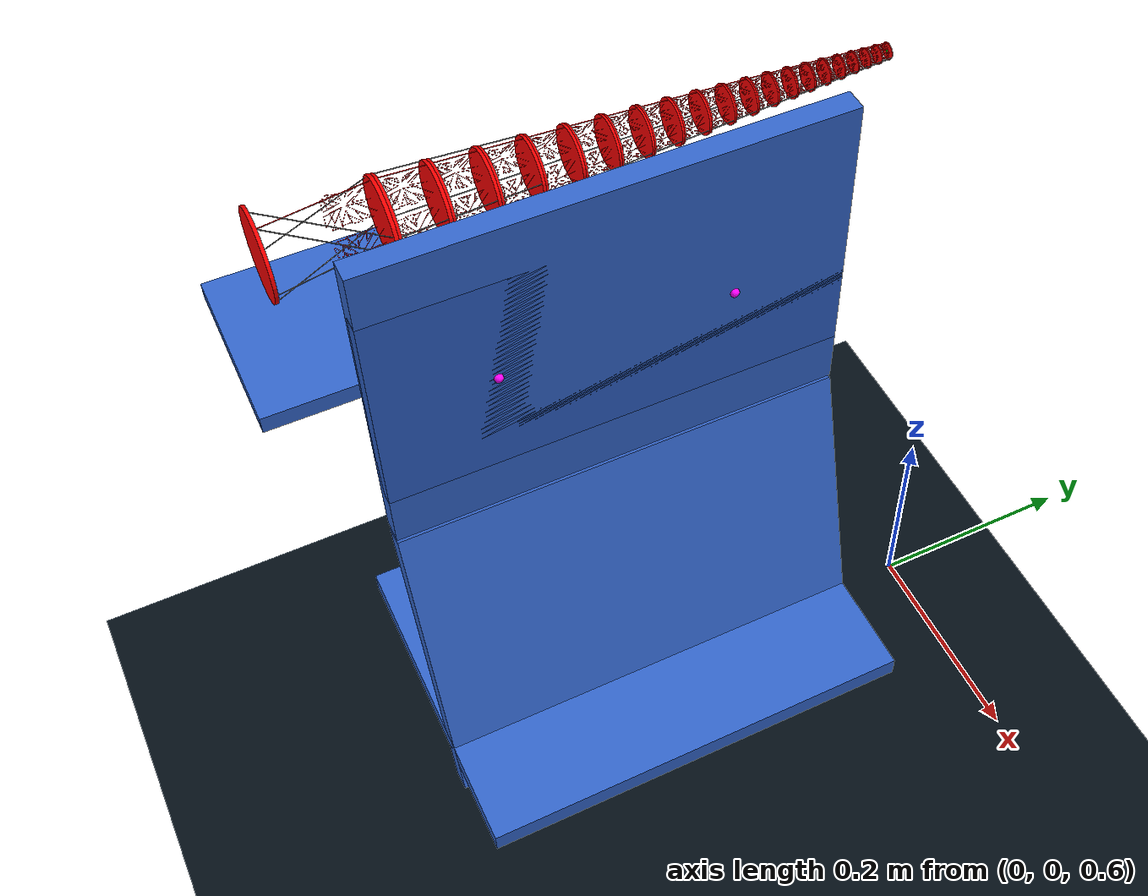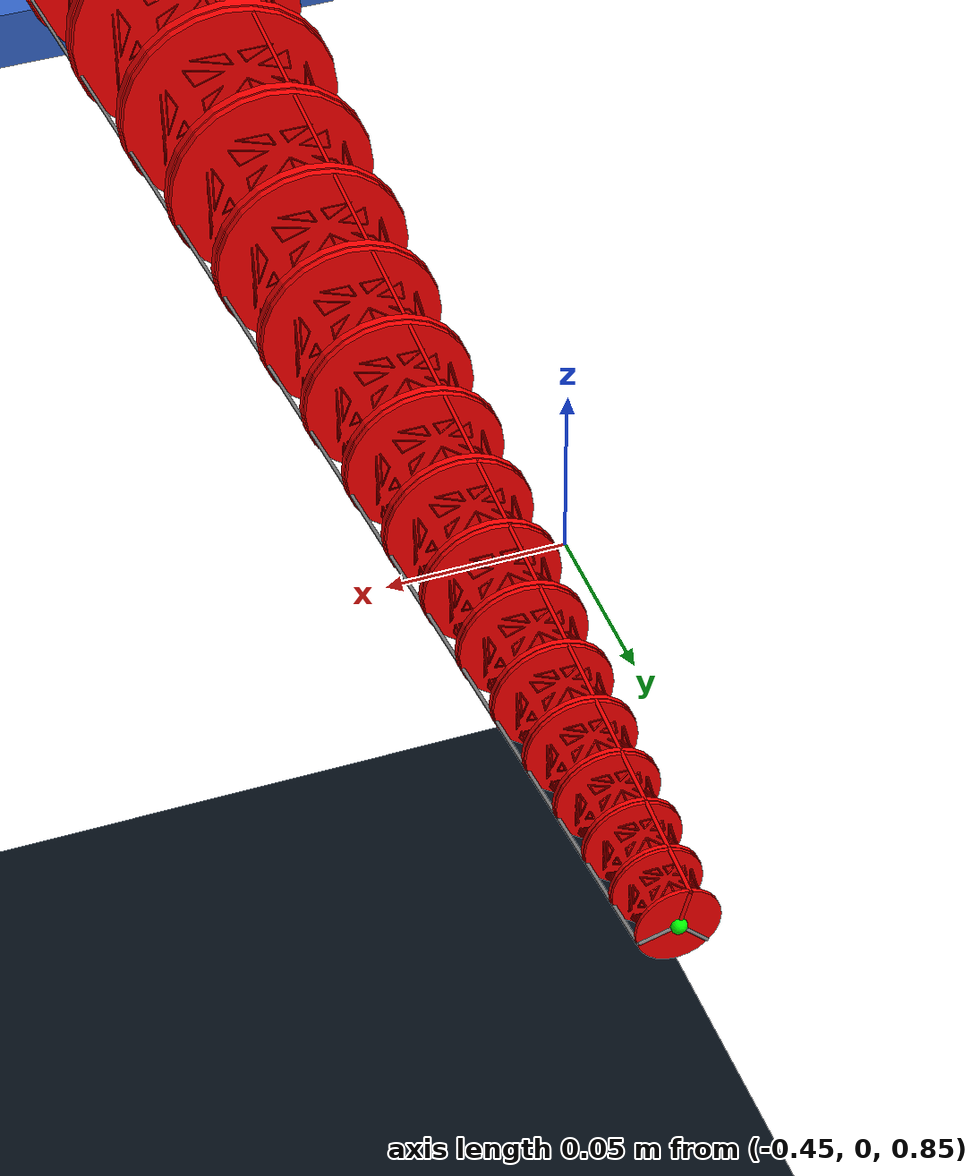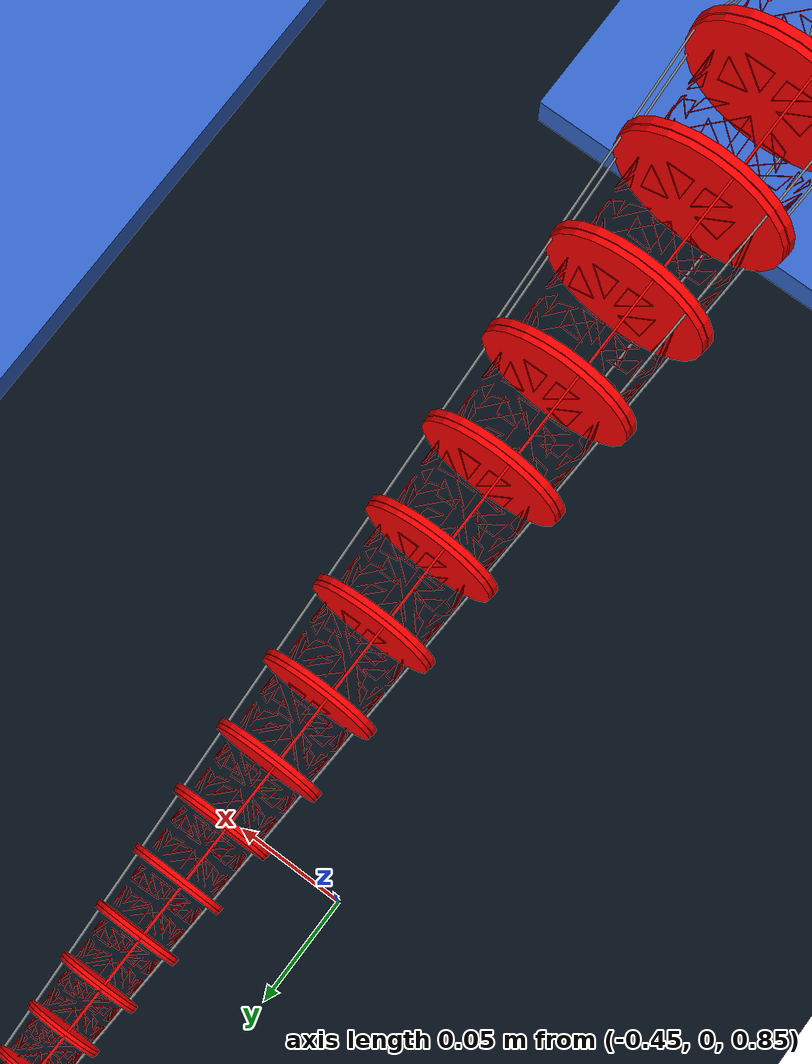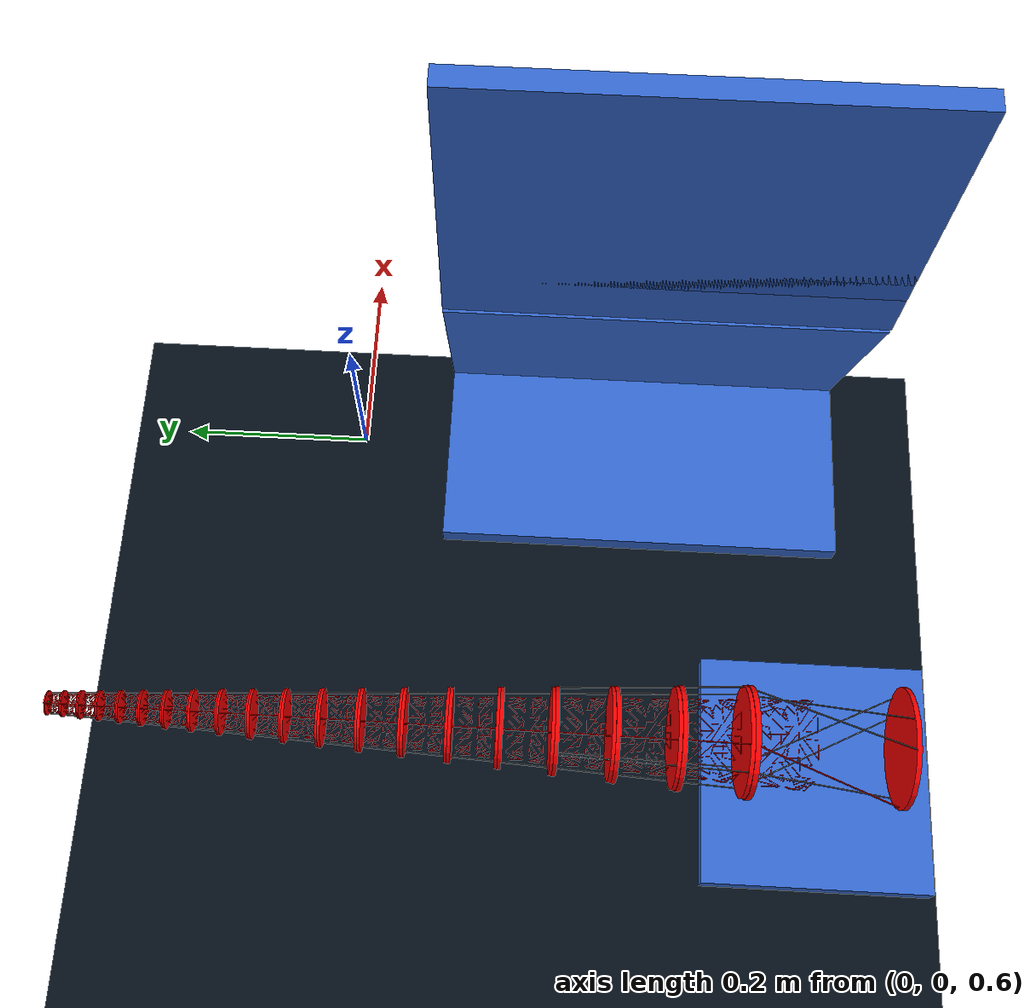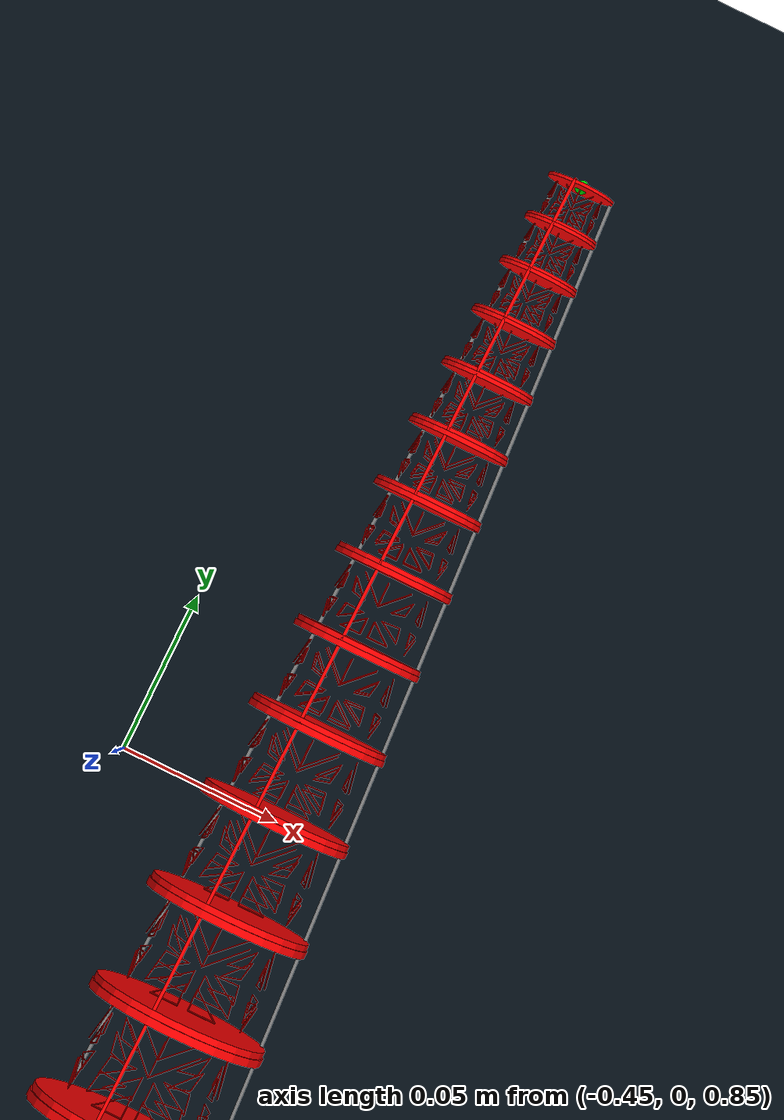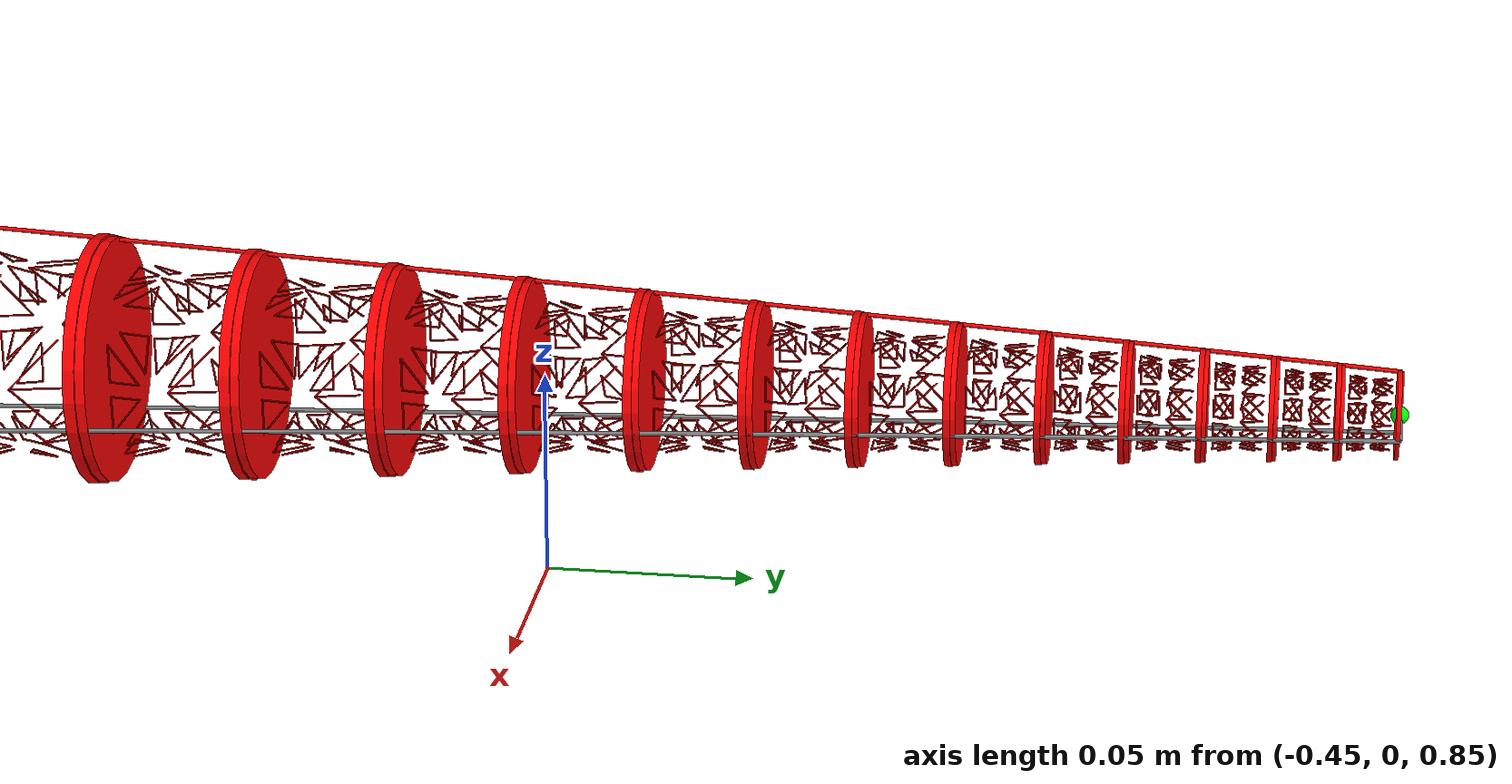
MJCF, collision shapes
<?xml version='1.0' encoding='utf-8'?>
<mujoco model="aircraft_cabin">
  <compiler angle="radian" texturedir="textures" coordinate="local" inertiafromgeom="false" balanceinertia="true" />
  <option timestep="0.002" gravity="0 0 -9.8" solver="Newton" />
  <size njmax="4000" nconmax="1000" />
  <statistic center="0 0 0.6" extent="3" />
  <visual>
    <headlight diffuse="0.9 0.9 0.9" ambient="0.6 0.6 0.6" specular="0.1 0.1 0.1" />
    <rgba haze="0.8 0.9 1.0 1" />
    <global azimuth="120" elevation="-20" offwidth="1280" offheight="720"/>
  </visual>
  <asset>
    <texture type="skybox" builtin="gradient" rgb1="0.45 0.60 0.75" rgb2="0.78 0.85 0.92" width="512" height="3072" />
    <texture name="room_tex" type="2d" file="Passanger_body_1002_BaseColor.png" />
    <material name="room_mat" texture="room_tex" specular="0.15" shininess="0.25" />
    <texture name="seat_tex" type="2d" file="Passanger_body_1012_BaseColor.png" />
    <material name="seat_mat" texture="seat_tex" specular="0.15" shininess="0.25" emission="0.08" />
    <material name="carpet_floor_mat" rgba="0.015 0.055 0.09 1" specular="0.04" shininess="0.08" />
    <mesh name="room_mesh" file="meshes/aircraft_room.obj" scale="0.1 0.1 0.1" />
    <mesh name="seat_mesh" file="meshes/aircraft_seats.obj" scale="0.1 0.1 0.1" />
    <mesh name="m20_seg2_m" file="STL/rib_seg2.stl" scale="0.66728899 0.66728899 0.66728899" />
    <mesh name="m20_seg5L_m" file="STL/rib_seg5L.stl" scale="0.66728899 0.66728899 0.66728899" />
    <mesh name="m20_seg5R_m" file="STL/rib_seg5R.stl" scale="0.66728899 0.66728899 0.66728899" />
    <mesh name="m20_seg6_m" file="STL/rib_seg6.stl" scale="0.66728899 0.66728899 0.66728899" />
    <mesh name="m20_seg4_m" file="STL/rib_seg4.stl" scale="0.66728899 0.66728899 0.66728899" />
    <mesh name="m20_seg3L_m" file="STL/rib_seg3L.stl" scale="0.66728899 0.66728899 0.66728899" />
    <mesh name="m20_seg3R_m" file="STL/rib_seg3R.stl" scale="0.66728899 0.66728899 0.66728899" />
    <mesh name="m20_bottom" file="STL/bottom_4x.stl" scale="0.66728899 0.66728899 0.66728899" />
    <mesh name="bottom20_col" file="STL/bottom_collision.stl" scale="0.66728898 0.66728898 0.66728898" />
    <mesh name="m20_top" file="STL/top_4x.stl" scale="0.66728898 0.66728898 0.66728898" />
    <mesh name="m19_seg2_m" file="STL/rib_seg2.stl" scale="0.72352104 0.72352104 0.72352104" />
    <mesh name="m19_seg5L_m" file="STL/rib_seg5L.stl" scale="0.72352104 0.72352104 0.72352104" />
    <mesh name="m19_seg5R_m" file="STL/rib_seg5R.stl" scale="0.72352104 0.72352104 0.72352104" />
    <mesh name="m19_seg6_m" file="STL/rib_seg6.stl" scale="0.72352104 0.72352104 0.72352104" />
    <mesh name="m19_seg4_m" file="STL/rib_seg4.stl" scale="0.72352104 0.72352104 0.72352104" />
    <mesh name="m19_seg3L_m" file="STL/rib_seg3L.stl" scale="0.72352104 0.72352104 0.72352104" />
    <mesh name="m19_seg3R_m" file="STL/rib_seg3R.stl" scale="0.72352104 0.72352104 0.72352104" />
    <mesh name="m19_bottom" file="STL/bottom_4x.stl" scale="0.72352104 0.72352104 0.72352104" />
    <mesh name="bottom19_col" file="STL/bottom_collision.stl" scale="0.72352104 0.72352104 0.72352104" />
    <mesh name="m19_top" file="STL/top_4x.stl" scale="0.72352104 0.72352104 0.72352104" />
    <mesh name="m18_seg2_m" file="STL/rib_seg2.stl" scale="0.78449174 0.78449174 0.78449174" />
    <mesh name="m18_seg5L_m" file="STL/rib_seg5L.stl" scale="0.78449174 0.78449174 0.78449174" />
    <mesh name="m18_seg5R_m" file="STL/rib_seg5R.stl" scale="0.78449174 0.78449174 0.78449174" />
    <mesh name="m18_seg6_m" file="STL/rib_seg6.stl" scale="0.78449174 0.78449174 0.78449174" />
    <mesh name="m18_seg4_m" file="STL/rib_seg4.stl" scale="0.78449174 0.78449174 0.78449174" />
    <mesh name="m18_seg3L_m" file="STL/rib_seg3L.stl" scale="0.78449174 0.78449174 0.78449174" />
    <mesh name="m18_seg3R_m" file="STL/rib_seg3R.stl" scale="0.78449174 0.78449174 0.78449174" />
    <mesh name="m18_bottom" file="STL/bottom_4x.stl" scale="0.78449174 0.78449174 0.78449174" />
    <mesh name="bottom18_col" file="STL/bottom_collision.stl" scale="0.78449174 0.78449174 0.78449174" />
    <mesh name="m18_top" file="STL/top_4x.stl" scale="0.78449174 0.78449174 0.78449174" />
    <mesh name="m17_seg2_m" file="STL/rib_seg2.stl" scale="0.8506004 0.8506004 0.8506004" />
    <mesh name="m17_seg5L_m" file="STL/rib_seg5L.stl" scale="0.8506004 0.8506004 0.8506004" />
    <mesh name="m17_seg5R_m" file="STL/rib_seg5R.stl" scale="0.8506004 0.8506004 0.8506004" />
    <mesh name="m17_seg6_m" file="STL/rib_seg6.stl" scale="0.8506004 0.8506004 0.8506004" />
    <mesh name="m17_seg4_m" file="STL/rib_seg4.stl" scale="0.8506004 0.8506004 0.8506004" />
    <mesh name="m17_seg3L_m" file="STL/rib_seg3L.stl" scale="0.8506004 0.8506004 0.8506004" />
    <mesh name="m17_seg3R_m" file="STL/rib_seg3R.stl" scale="0.8506004 0.8506004 0.8506004" />
    <mesh name="m17_bottom" file="STL/bottom_4x.stl" scale="0.8506004 0.8506004 0.8506004" />
    <mesh name="bottom17_col" file="STL/bottom_collision.stl" scale="0.8506004 0.8506004 0.8506004" />
    <mesh name="m17_top" file="STL/top_4x.stl" scale="0.8506004 0.8506004 0.8506004" />
    <mesh name="m16_seg2_m" file="STL/rib_seg2.stl" scale="0.92228 0.92228 0.92228" />
    <mesh name="m16_seg5L_m" file="STL/rib_seg5L.stl" scale="0.92228 0.92228 0.92228" />
    <mesh name="m16_seg5R_m" file="STL/rib_seg5R.stl" scale="0.92228 0.92228 0.92228" />
    <mesh name="m16_seg6_m" file="STL/rib_seg6.stl" scale="0.92228 0.92228 0.92228" />
    <mesh name="m16_seg4_m" file="STL/rib_seg4.stl" scale="0.92228 0.92228 0.92228" />
    <mesh name="m16_seg3L_m" file="STL/rib_seg3L.stl" scale="0.92228 0.92228 0.92228" />
    <mesh name="m16_seg3R_m" file="STL/rib_seg3R.stl" scale="0.92228 0.92228 0.92228" />
    <mesh name="m16_bottom" file="STL/bottom_4x.stl" scale="0.92228 0.92228 0.92228" />
    <mesh name="bottom16_col" file="STL/bottom_collision.stl" scale="0.92228 0.92228 0.92228" />
    <mesh name="m16_top" file="STL/top_4x.stl" scale="0.92228 0.92228 0.92228" />
    <mesh name="m15_seg2_m" file="STL/rib_seg2.stl" scale="1 1 1" />
    <mesh name="m15_seg5L_m" file="STL/rib_seg5L.stl" scale="1 1 1" />
    <mesh name="m15_seg5R_m" file="STL/rib_seg5R.stl" scale="1 1 1" />
    <mesh name="m15_seg6_m" file="STL/rib_seg6.stl" scale="1 1 1" />
    <mesh name="m15_seg4_m" file="STL/rib_seg4.stl" scale="1 1 1" />
    <mesh name="m15_seg3L_m" file="STL/rib_seg3L.stl" scale="1 1 1" />
    <mesh name="m15_seg3R_m" file="STL/rib_seg3R.stl" scale="1 1 1" />
    <mesh name="m15_bottom" file="STL/bottom_4x.stl" scale="1 1 1" />
    <mesh name="bottom15_col" file="STL/bottom_collision.stl" scale="1 1 1" />
    <mesh name="m15_top" file="STL/top_4x.stl" scale="1 1 1" />
    <mesh name="m14_seg2_m" file="STL/rib_seg2.stl" scale="1.0842694 1.0842694 1.0842694" />
    <mesh name="m14_seg5L_m" file="STL/rib_seg5L.stl" scale="1.0842694 1.0842694 1.0842694" />
    <mesh name="m14_seg5R_m" file="STL/rib_seg5R.stl" scale="1.0842694 1.0842694 1.0842694" />
    <mesh name="m14_seg6_m" file="STL/rib_seg6.stl" scale="1.0842694 1.0842694 1.0842694" />
    <mesh name="m14_seg4_m" file="STL/rib_seg4.stl" scale="1.0842694 1.0842694 1.0842694" />
    <mesh name="m14_seg3L_m" file="STL/rib_seg3L.stl" scale="1.0842694 1.0842694 1.0842694" />
    <mesh name="m14_seg3R_m" file="STL/rib_seg3R.stl" scale="1.0842694 1.0842694 1.0842694" />
    <mesh name="m14_bottom" file="STL/bottom_4x.stl" scale="1.0842694 1.0842694 1.0842694" />
    <mesh name="bottom14_col" file="STL/bottom_collision.stl" scale="1.0842694 1.0842694 1.0842694" />
    <mesh name="m14_top" file="STL/top_4x.stl" scale="1.0842694 1.0842694 1.0842694" />
    <mesh name="m13_seg2_m" file="STL/rib_seg2.stl" scale="1.1756402 1.1756402 1.1756402" />
    <mesh name="m13_seg5L_m" file="STL/rib_seg5L.stl" scale="1.1756402 1.1756402 1.1756402" />
    <mesh name="m13_seg5R_m" file="STL/rib_seg5R.stl" scale="1.1756402 1.1756402 1.1756402" />
    <mesh name="m13_seg6_m" file="STL/rib_seg6.stl" scale="1.1756402 1.1756402 1.1756402" />
    <mesh name="m13_seg4_m" file="STL/rib_seg4.stl" scale="1.1756402 1.1756402 1.1756402" />
    <mesh name="m13_seg3L_m" file="STL/rib_seg3L.stl" scale="1.1756402 1.1756402 1.1756402" />
    <mesh name="m13_seg3R_m" file="STL/rib_seg3R.stl" scale="1.1756402 1.1756402 1.1756402" />
    <mesh name="m13_bottom" file="STL/bottom_4x.stl" scale="1.1756402 1.1756402 1.1756402" />
    <mesh name="bottom13_col" file="STL/bottom_collision.stl" scale="1.1756402 1.1756402 1.1756402" />
    <mesh name="m13_top" file="STL/top_4x.stl" scale="1.1756402 1.1756402 1.1756402" />
    <mesh name="m12_seg2_m" file="STL/rib_seg2.stl" scale="1.2747107 1.2747107 1.2747107" />
    <mesh name="m12_seg5L_m" file="STL/rib_seg5L.stl" scale="1.2747107 1.2747107 1.2747107" />
    <mesh name="m12_seg5R_m" file="STL/rib_seg5R.stl" scale="1.2747107 1.2747107 1.2747107" />
    <mesh name="m12_seg6_m" file="STL/rib_seg6.stl" scale="1.2747107 1.2747107 1.2747107" />
    <mesh name="m12_seg4_m" file="STL/rib_seg4.stl" scale="1.2747107 1.2747107 1.2747107" />
    <mesh name="m12_seg3L_m" file="STL/rib_seg3L.stl" scale="1.2747107 1.2747107 1.2747107" />
    <mesh name="m12_seg3R_m" file="STL/rib_seg3R.stl" scale="1.2747107 1.2747107 1.2747107" />
    <mesh name="m12_bottom" file="STL/bottom_4x.stl" scale="1.2747107 1.2747107 1.2747107" />
    <mesh name="bottom12_col" file="STL/bottom_collision.stl" scale="1.2747107 1.2747107 1.2747107" />
    <mesh name="m12_top" file="STL/top_4x.stl" scale="1.2747107 1.2747107 1.2747107" />
    <mesh name="m11_seg2_m" file="STL/rib_seg2.stl" scale="1.3821298 1.3821298 1.3821298" />
    <mesh name="m11_seg5L_m" file="STL/rib_seg5L.stl" scale="1.3821298 1.3821298 1.3821298" />
    <mesh name="m11_seg5R_m" file="STL/rib_seg5R.stl" scale="1.3821298 1.3821298 1.3821298" />
    <mesh name="m11_seg6_m" file="STL/rib_seg6.stl" scale="1.3821298 1.3821298 1.3821298" />
    <mesh name="m11_seg4_m" file="STL/rib_seg4.stl" scale="1.3821298 1.3821298 1.3821298" />
    <mesh name="m11_seg3L_m" file="STL/rib_seg3L.stl" scale="1.3821298 1.3821298 1.3821298" />
    <mesh name="m11_seg3R_m" file="STL/rib_seg3R.stl" scale="1.3821298 1.3821298 1.3821298" />
    <mesh name="m11_bottom" file="STL/bottom_4x.stl" scale="1.3821298 1.3821298 1.3821298" />
    <mesh name="bottom11_col" file="STL/bottom_collision.stl" scale="1.3821298 1.3821298 1.3821298" />
    <mesh name="m11_top" file="STL/top_4x.stl" scale="1.3821298 1.3821298 1.3821298" />
    <mesh name="m10_seg2_m" file="STL/rib_seg2.stl" scale="1.4986011 1.4986011 1.4986011" />
    <mesh name="m10_seg5L_m" file="STL/rib_seg5L.stl" scale="1.4986011 1.4986011 1.4986011" />
    <mesh name="m10_seg5R_m" file="STL/rib_seg5R.stl" scale="1.4986011 1.4986011 1.4986011" />
    <mesh name="m10_seg6_m" file="STL/rib_seg6.stl" scale="1.4986011 1.4986011 1.4986011" />
    <mesh name="m10_seg4_m" file="STL/rib_seg4.stl" scale="1.4986011 1.4986011 1.4986011" />
    <mesh name="m10_seg3L_m" file="STL/rib_seg3L.stl" scale="1.4986011 1.4986011 1.4986011" />
    <mesh name="m10_seg3R_m" file="STL/rib_seg3R.stl" scale="1.4986011 1.4986011 1.4986011" />
    <mesh name="m10_bottom" file="STL/bottom_4x.stl" scale="1.4986011 1.4986011 1.4986011" />
    <mesh name="bottom10_col" file="STL/bottom_collision.stl" scale="1.4986011 1.4986011 1.4986011" />
    <mesh name="m10_top" file="STL/top_4x.stl" scale="1.4986011 1.4986011 1.4986011" />
    <mesh name="m9_seg2_m" file="STL/rib_seg2.stl" scale="1.6248873 1.6248873 1.6248873" />
    <mesh name="m9_seg5L_m" file="STL/rib_seg5L.stl" scale="1.6248873 1.6248873 1.6248873" />
    <mesh name="m9_seg5R_m" file="STL/rib_seg5R.stl" scale="1.6248873 1.6248873 1.6248873" />
    <mesh name="m9_seg6_m" file="STL/rib_seg6.stl" scale="1.6248873 1.6248873 1.6248873" />
    <mesh name="m9_seg4_m" file="STL/rib_seg4.stl" scale="1.6248873 1.6248873 1.6248873" />
    <mesh name="m9_seg3L_m" file="STL/rib_seg3L.stl" scale="1.6248873 1.6248873 1.6248873" />
    <mesh name="m9_seg3R_m" file="STL/rib_seg3R.stl" scale="1.6248873 1.6248873 1.6248873" />
    <mesh name="m9_bottom" file="STL/bottom_4x.stl" scale="1.6248873 1.6248873 1.6248873" />
    <mesh name="bottom9_col" file="STL/bottom_collision.stl" scale="1.6248873 1.6248873 1.6248873" />
    <mesh name="m9_top" file="STL/top_4x.stl" scale="1.6248873 1.6248873 1.6248873" />
    <mesh name="m8_seg2_m" file="STL/rib_seg2.stl" scale="1.7618157 1.7618157 1.7618157" />
    <mesh name="m8_seg5L_m" file="STL/rib_seg5L.stl" scale="1.7618157 1.7618157 1.7618157" />
    <mesh name="m8_seg5R_m" file="STL/rib_seg5R.stl" scale="1.7618157 1.7618157 1.7618157" />
    <mesh name="m8_seg6_m" file="STL/rib_seg6.stl" scale="1.7618157 1.7618157 1.7618157" />
    <mesh name="m8_seg4_m" file="STL/rib_seg4.stl" scale="1.7618157 1.7618157 1.7618157" />
    <mesh name="m8_seg3L_m" file="STL/rib_seg3L.stl" scale="1.7618157 1.7618157 1.7618157" />
    <mesh name="m8_seg3R_m" file="STL/rib_seg3R.stl" scale="1.7618157 1.7618157 1.7618157" />
    <mesh name="m8_bottom" file="STL/bottom_4x.stl" scale="1.7618157 1.7618157 1.7618157" />
    <mesh name="bottom8_col" file="STL/bottom_collision.stl" scale="1.7618157 1.7618157 1.7618157" />
    <mesh name="m8_top" file="STL/top_4x.stl" scale="1.7618157 1.7618157 1.7618157" />
    <mesh name="m7_seg2_m" file="STL/rib_seg2.stl" scale="1.9102828 1.9102828 1.9102828" />
    <mesh name="m7_seg5L_m" file="STL/rib_seg5L.stl" scale="1.9102828 1.9102828 1.9102828" />
    <mesh name="m7_seg5R_m" file="STL/rib_seg5R.stl" scale="1.9102828 1.9102828 1.9102828" />
    <mesh name="m7_seg6_m" file="STL/rib_seg6.stl" scale="1.9102828 1.9102828 1.9102828" />
    <mesh name="m7_seg4_m" file="STL/rib_seg4.stl" scale="1.9102828 1.9102828 1.9102828" />
    <mesh name="m7_seg3L_m" file="STL/rib_seg3L.stl" scale="1.9102828 1.9102828 1.9102828" />
    <mesh name="m7_seg3R_m" file="STL/rib_seg3R.stl" scale="1.9102828 1.9102828 1.9102828" />
    <mesh name="m7_bottom" file="STL/bottom_4x.stl" scale="1.9102828 1.9102828 1.9102828" />
    <mesh name="bottom7_col" file="STL/bottom_collision.stl" scale="1.9102828 1.9102828 1.9102828" />
    <mesh name="m7_top" file="STL/top_4x.stl" scale="1.9102828 1.9102828 1.9102828" />
    <mesh name="m6_seg2_m" file="STL/rib_seg2.stl" scale="2.0712613 2.0712613 2.0712613" />
    <mesh name="m6_seg5L_m" file="STL/rib_seg5L.stl" scale="2.0712613 2.0712613 2.0712613" />
    <mesh name="m6_seg5R_m" file="STL/rib_seg5R.stl" scale="2.0712613 2.0712613 2.0712613" />
    <mesh name="m6_seg6_m" file="STL/rib_seg6.stl" scale="2.0712613 2.0712613 2.0712613" />
    <mesh name="m6_seg4_m" file="STL/rib_seg4.stl" scale="2.0712613 2.0712613 2.0712613" />
    <mesh name="m6_seg3L_m" file="STL/rib_seg3L.stl" scale="2.0712613 2.0712613 2.0712613" />
    <mesh name="m6_seg3R_m" file="STL/rib_seg3R.stl" scale="2.0712613 2.0712613 2.0712613" />
    <mesh name="m6_bottom" file="STL/bottom_4x.stl" scale="2.0712613 2.0712613 2.0712613" />
    <mesh name="bottom6_col" file="STL/bottom_collision.stl" scale="2.0712613 2.0712613 2.0712613" />
    <mesh name="m6_top" file="STL/top_4x.stl" scale="2.0712613 2.0712613 2.0712613" />
    <mesh name="m5_seg2_m" file="STL/rib_seg2.stl" scale="2.2458052 2.2458052 2.2458052" />
    <mesh name="m5_seg5L_m" file="STL/rib_seg5L.stl" scale="2.2458052 2.2458052 2.2458052" />
    <mesh name="m5_seg5R_m" file="STL/rib_seg5R.stl" scale="2.2458052 2.2458052 2.2458052" />
    <mesh name="m5_seg6_m" file="STL/rib_seg6.stl" scale="2.2458052 2.2458052 2.2458052" />
    <mesh name="m5_seg4_m" file="STL/rib_seg4.stl" scale="2.2458052 2.2458052 2.2458052" />
    <mesh name="m5_seg3L_m" file="STL/rib_seg3L.stl" scale="2.2458052 2.2458052 2.2458052" />
    <mesh name="m5_seg3R_m" file="STL/rib_seg3R.stl" scale="2.2458052 2.2458052 2.2458052" />
    <mesh name="m5_bottom" file="STL/bottom_4x.stl" scale="2.2458052 2.2458052 2.2458052" />
    <mesh name="bottom5_col" file="STL/bottom_collision.stl" scale="2.2458052 2.2458052 2.2458052" />
    <mesh name="m5_top" file="STL/top_4x.stl" scale="2.2458052 2.2458052 2.2458052" />
    <mesh name="m4_seg2_m" file="STL/rib_seg2.stl" scale="2.435058 2.435058 2.435058" />
    <mesh name="m4_seg5L_m" file="STL/rib_seg5L.stl" scale="2.435058 2.435058 2.435058" />
    <mesh name="m4_seg5R_m" file="STL/rib_seg5R.stl" scale="2.435058 2.435058 2.435058" />
    <mesh name="m4_seg6_m" file="STL/rib_seg6.stl" scale="2.435058 2.435058 2.435058" />
    <mesh name="m4_seg4_m" file="STL/rib_seg4.stl" scale="2.435058 2.435058 2.435058" />
    <mesh name="m4_seg3L_m" file="STL/rib_seg3L.stl" scale="2.435058 2.435058 2.435058" />
    <mesh name="m4_seg3R_m" file="STL/rib_seg3R.stl" scale="2.435058 2.435058 2.435058" />
    <mesh name="m4_bottom" file="STL/bottom_4x.stl" scale="2.435058 2.435058 2.435058" />
    <mesh name="bottom4_col" file="STL/bottom_collision.stl" scale="2.4350579 2.4350579 2.4350579" />
    <mesh name="m4_top" file="STL/top_4x.stl" scale="2.4350579 2.4350579 2.4350579" />
    <mesh name="m3_seg2_m" file="STL/rib_seg2.stl" scale="2.6402589 2.6402589 2.6402589" />
    <mesh name="m3_seg5L_m" file="STL/rib_seg5L.stl" scale="2.6402589 2.6402589 2.6402589" />
    <mesh name="m3_seg5R_m" file="STL/rib_seg5R.stl" scale="2.6402589 2.6402589 2.6402589" />
    <mesh name="m3_seg6_m" file="STL/rib_seg6.stl" scale="2.6402589 2.6402589 2.6402589" />
    <mesh name="m3_seg4_m" file="STL/rib_seg4.stl" scale="2.6402589 2.6402589 2.6402589" />
    <mesh name="m3_seg3L_m" file="STL/rib_seg3L.stl" scale="2.6402589 2.6402589 2.6402589" />
    <mesh name="m3_seg3R_m" file="STL/rib_seg3R.stl" scale="2.6402589 2.6402589 2.6402589" />
    <mesh name="m3_bottom" file="STL/bottom_4x.stl" scale="2.6402589 2.6402589 2.6402589" />
    <mesh name="bottom3_col" file="STL/bottom_collision.stl" scale="2.6402589 2.6402589 2.6402589" />
    <mesh name="m3_top" file="STL/top_4x.stl" scale="2.6402589 2.6402589 2.6402589" />
    <mesh name="m2_seg2_m" file="STL/rib_seg2.stl" scale="2.862752 2.862752 2.862752" />
    <mesh name="m2_seg5L_m" file="STL/rib_seg5L.stl" scale="2.862752 2.862752 2.862752" />
    <mesh name="m2_seg5R_m" file="STL/rib_seg5R.stl" scale="2.862752 2.862752 2.862752" />
    <mesh name="m2_seg6_m" file="STL/rib_seg6.stl" scale="2.862752 2.862752 2.862752" />
    <mesh name="m2_seg4_m" file="STL/rib_seg4.stl" scale="2.862752 2.862752 2.862752" />
    <mesh name="m2_seg3L_m" file="STL/rib_seg3L.stl" scale="2.862752 2.862752 2.862752" />
    <mesh name="m2_seg3R_m" file="STL/rib_seg3R.stl" scale="2.862752 2.862752 2.862752" />
    <mesh name="m2_bottom" file="STL/bottom_4x.stl" scale="2.862752 2.862752 2.862752" />
    <mesh name="bottom2_col" file="STL/bottom_collision.stl" scale="2.8627519 2.8627519 2.8627519" />
    <mesh name="m2_top" file="STL/top_4x.stl" scale="2.8627519 2.8627519 2.8627519" />
    <mesh name="m1_seg2_m" file="STL/rib_seg2.stl" scale="3.1039944 3.1039944 3.1039944" />
    <mesh name="m1_seg5L_m" file="STL/rib_seg5L.stl" scale="3.1039944 3.1039944 3.1039944" />
    <mesh name="m1_seg5R_m" file="STL/rib_seg5R.stl" scale="3.1039944 3.1039944 3.1039944" />
    <mesh name="m1_seg6_m" file="STL/rib_seg6.stl" scale="3.1039944 3.1039944 3.1039944" />
    <mesh name="m1_seg4_m" file="STL/rib_seg4.stl" scale="3.1039944 3.1039944 3.1039944" />
    <mesh name="m1_seg3L_m" file="STL/rib_seg3L.stl" scale="3.1039944 3.1039944 3.1039944" />
    <mesh name="m1_seg3R_m" file="STL/rib_seg3R.stl" scale="3.1039944 3.1039944 3.1039944" />
    <mesh name="m1_bottom" file="STL/bottom_4x.stl" scale="3.1039944 3.1039944 3.1039944" />
    <mesh name="bottom1_col" file="STL/bottom_collision.stl" scale="3.103994388566468 3.103994388566468 3.103994388566468" />
    <mesh name="m1_top" file="STL/top_4x.stl" scale="3.103994388566468 3.103994388566468 3.103994388566468" />
  </asset>
  <default>
    <site type="sphere" size="0.0002" rgba="1 0 1 0" />
    <default class="vis_mesh">
      <geom type="mesh" contype="0" conaffinity="0" />
    </default>
    <default class="collision_capsule">
      <geom contype="1" conaffinity="1" solref="0.002 1" solimp="0.97 0.995 0.0005" friction="0.6 0.02 0.01" rgba="1 0 0 0" type="capsule" size="0.0002" margin="0.0001" />
    </default>
    <default class="collision_disk">
      <geom contype="1" conaffinity="1" solref="0.002 1" solimp="0.97 0.995 0.0005" friction="0.6 0.02 0.01" rgba="1 0 0 0" type="cylinder" />
    </default>
    <default class="m20">
      <joint springref="0" damping="1.8486132e-05" stiffness="3.203785e-05" armature="4.3135365e-07" frictionloss="9.9352564e-06" />
      <geom type="mesh" contype="0" conaffinity="0" />
    </default>
    <default class="m19">
      <joint springref="0" damping="2.1733039e-05" stiffness="4.4280468e-05" armature="4.1425225e-07" frictionloss="1.2664578e-05" />
      <geom type="mesh" contype="0" conaffinity="0" />
    </default>
    <default class="m18">
      <joint springref="0" damping="2.5550234e-05" stiffness="6.1201355e-05" armature="3.9782885e-07" frictionloss="1.6143672e-05" />
      <geom type="mesh" contype="0" conaffinity="0" />
    </default>
    <default class="m17">
      <joint springref="0" damping="3.0037882e-05" stiffness="8.4588218e-05" armature="3.8205657e-07" frictionloss="2.0578512e-05" />
      <geom type="mesh" contype="0" conaffinity="0" />
    </default>
    <default class="m16">
      <joint springref="0" damping="3.531374e-05" stiffness="0.0001169119" armature="3.6690959e-07" frictionloss="2.6231649e-05" />
      <geom type="mesh" contype="0" conaffinity="0" />
    </default>
    <default class="m15">
      <joint springref="0" damping="4.1516252e-05" stiffness="0.00016158742" armature="3.5236313e-07" frictionloss="3.3437763e-05" />
      <geom type="mesh" contype="0" conaffinity="0" />
    </default>
    <default class="m14">
      <joint springref="0" damping="4.8808173e-05" stiffness="0.00022333479" armature="3.3839338e-07" frictionloss="4.2623474e-05" />
      <geom type="mesh" contype="0" conaffinity="0" />
    </default>
    <default class="m13">
      <joint springref="0" damping="5.7380849e-05" stiffness="0.00030867768" armature="3.2497747e-07" frictionloss="5.4332598e-05" />
      <geom type="mesh" contype="0" conaffinity="0" />
    </default>
    <default class="m12">
      <joint springref="0" damping="6.7459232e-05" stiffness="0.00042663262" armature="3.1209344e-07" frictionloss="6.9258343e-05" />
      <geom type="mesh" contype="0" conaffinity="0" />
    </default>
    <default class="m11">
      <joint springref="0" damping="7.9307783e-05" stiffness="0.00058966167" armature="2.9972022e-07" frictionloss="8.8284351e-05" />
      <geom type="mesh" contype="0" conaffinity="0" />
    </default>
    <default class="m10">
      <joint springref="0" damping="9.3237416e-05" stiffness="0.00081498897" armature="2.8783754e-07" frictionloss="0.00011253701" />
      <geom type="mesh" contype="0" conaffinity="0" />
    </default>
    <default class="m9">
      <joint springref="0" damping="0.00010961365" stiffness="0.0011264206" armature="2.7642596e-07" frictionloss="0.00014345212" />
      <geom type="mesh" contype="0" conaffinity="0" />
    </default>
    <default class="m8">
      <joint springref="0" damping="0.00012886621" stiffness="0.0015568594" armature="2.6546681e-07" frictionloss="0.00018285996" />
      <geom type="mesh" contype="0" conaffinity="0" />
    </default>
    <default class="m7">
      <joint springref="0" damping="0.0001515003" stiffness="0.0021517819" armature="2.5494214e-07" frictionloss="0.00023309354" />
      <geom type="mesh" contype="0" conaffinity="0" />
    </default>
    <default class="m6">
      <joint springref="0" damping="0.00017810983" stiffness="0.0029740419" armature="2.4483473e-07" frictionloss="0.00029712683" />
      <geom type="mesh" contype="0" conaffinity="0" />
    </default>
    <default class="m5">
      <joint springref="0" damping="0.00020939308" stiffness="0.0041105119" armature="2.3512803e-07" frictionloss="0.00037875074" />
      <geom type="mesh" contype="0" conaffinity="0" />
    </default>
    <default class="m4">
      <joint springref="0" damping="0.00024617091" stiffness="0.0056812611" armature="2.2580617e-07" frictionloss="0.00048279762" />
      <geom type="mesh" contype="0" conaffinity="0" />
    </default>
    <default class="m3">
      <joint springref="0" damping="0.00028940842" stiffness="0.0078522404" armature="2.1685388e-07" frictionloss="0.00061542728" />
      <geom type="mesh" contype="0" conaffinity="0" />
    </default>
    <default class="m2">
      <joint springref="0" damping="0.00034024016" stiffness="0.010852816" armature="2.0825652e-07" frictionloss="0.00078449174" />
      <geom type="mesh" contype="0" conaffinity="0" />
    </default>
    <default class="m1">
      <joint springref="0" damping="4e-4" stiffness="0.015" armature="2e-7" frictionloss="1e-3" />
      <geom type="mesh" contype="0" conaffinity="0" />
    </default>
  </default>
  <worldbody>
    <geom name="screen_visual" type="box" pos="-0.02 -0.3 1.1" size="0.01 0.2 0.1" rgba="0.2 0.4 0.8 0.35" mass="0.5" contype="0" conaffinity="0" />
    <geom name="screen" type="box" pos="-0.02 -0.3 1.1" size="0.01 0.2 0.15" rgba="0.2 0.4 0.8 0.35" mass="0.5" contype="1" conaffinity="1" />
    <site name="path1" pos="-0.01 -0.2 1.1" rgba="1 0 1 1" size="0.004"/>
    <site name="path2" pos="-0.01 -0.4 1.1" rgba="1 0 1 1" size="0.004"/>
    <geom name="tray" type="box" pos="0 -0.3 0.7" size="0.15 0.2 0.01" rgba="0.2 0.4 0.8 0.35" mass="0.5" contype="1" conaffinity="1" />
    <site name="path3" pos="-0.05 -0.2 0.7" rgba="1 0 1 1" size="0.004"/>
    <site name="path4" pos="-0.05 -0.4 0.7" rgba="1 0 1 1" size="0.004"/>
    <geom name="seat" type="box" pos="0.02 -0.3 0.8" size="0.15 0.2 0.01" euler="0 1.3089969390 0" rgba="0.2 0.4 0.8 0.35" mass="0.5" contype="1" conaffinity="1" />
    <geom name="extra_floor" type="box" pos="0 0 -0.03" size="4.2 2.8 0.01" material="carpet_floor_mat" contype="0" conaffinity="0" />
    <light name="top_light" pos="0 0 4" dir="0 0 -1" directional="true" diffuse="0.9 0.9 0.9" ambient="0.35 0.35 0.35" />
    <body name="cabin" pos="-3 -1 0.03" quat="0 0 0 1">
      <geom name="room_visual" type="mesh" mesh="room_mesh" material="room_mat" contype="0" conaffinity="0" />
      <geom name="seat_visual" type="mesh" mesh="seat_mesh" material="seat_mat" contype="0" conaffinity="0" />
    </body>
    <body name="moving_plate" pos="-0.4 -0.4 0">
      <joint name="plate_tx" type="slide" axis="1 0 0" damping="80" armature="0.2" />
      <joint name="plate_ty" type="slide" axis="0 1 0" damping="80" armature="0.2" />
      <geom name="plate" type="box" pos="0 -0.05 0.80" size="0.1 0.1 0.01" rgba="0.2 0.4 0.8 0.35" mass="0.5" contype="1" conaffinity="1" />
      <include file="module_body.xml" />
    </body>
  </worldbody>
  <equality>
    <weld body1="m20_seg5L" body2="m20_seg5R" solref="0.01 1" solimp="0.95 0.99 0.002" />
    <connect site1="m20_h5Ltop_a1" site2="m20_h5Ltop_b1" solref="0.001 1" solimp="0.99 0.999 0.001" />
    <connect site1="m20_h5Ltop_a2" site2="m20_h5Ltop_b2" solref="0.001 1" solimp="0.99 0.999 0.001" />
    <connect site1="m20_h5Rtop_a1" site2="m20_h5Rtop_b1" solref="0.001 1" solimp="0.99 0.999 0.001" />
    <connect site1="m20_h5Rtop_a2" site2="m20_h5Rtop_b2" solref="0.001 1" solimp="0.99 0.999 0.001" />
    <weld body1="m20_seg5L_r1" body2="m20_seg5R_r1" solref="0.01 1" solimp="0.95 0.99 0.002" />
    <connect site1="m20_h5Ltop_a1_r1" site2="m20_h5Ltop_b1_r1" solref="0.001 1" solimp="0.99 0.999 0.001" />
    <connect site1="m20_h5Ltop_a2_r1" site2="m20_h5Ltop_b2_r1" solref="0.001 1" solimp="0.99 0.999 0.001" />
    <connect site1="m20_h5Rtop_a1_r1" site2="m20_h5Rtop_b1_r1" solref="0.001 1" solimp="0.99 0.999 0.001" />
    <connect site1="m20_h5Rtop_a2_r1" site2="m20_h5Rtop_b2_r1" solref="0.001 1" solimp="0.99 0.999 0.001" />
    <weld body1="m20_seg5L_r2" body2="m20_seg5R_r2" solref="0.01 1" solimp="0.95 0.99 0.002" />
    <connect site1="m20_h5Ltop_a1_r2" site2="m20_h5Ltop_b1_r2" solref="0.001 1" solimp="0.99 0.999 0.001" />
    <connect site1="m20_h5Ltop_a2_r2" site2="m20_h5Ltop_b2_r2" solref="0.001 1" solimp="0.99 0.999 0.001" />
    <connect site1="m20_h5Rtop_a1_r2" site2="m20_h5Rtop_b1_r2" solref="0.001 1" solimp="0.99 0.999 0.001" />
    <connect site1="m20_h5Rtop_a2_r2" site2="m20_h5Rtop_b2_r2" solref="0.001 1" solimp="0.99 0.999 0.001" />
    <weld body1="m20_seg5L_r3" body2="m20_seg5R_r3" solref="0.01 1" solimp="0.95 0.99 0.002" />
    <connect site1="m20_h5Ltop_a1_r3" site2="m20_h5Ltop_b1_r3" solref="0.001 1" solimp="0.99 0.999 0.001" />
    <connect site1="m20_h5Ltop_a2_r3" site2="m20_h5Ltop_b2_r3" solref="0.001 1" solimp="0.99 0.999 0.001" />
    <connect site1="m20_h5Rtop_a1_r3" site2="m20_h5Rtop_b1_r3" solref="0.001 1" solimp="0.99 0.999 0.001" />
    <connect site1="m20_h5Rtop_a2_r3" site2="m20_h5Rtop_b2_r3" solref="0.001 1" solimp="0.99 0.999 0.001" />
    <weld body1="m19_seg5L" body2="m19_seg5R" solref="0.01 1" solimp="0.95 0.99 0.002" />
    <connect site1="m19_h5Ltop_a1" site2="m19_h5Ltop_b1" solref="0.001 1" solimp="0.99 0.999 0.001" />
    <connect site1="m19_h5Ltop_a2" site2="m19_h5Ltop_b2" solref="0.001 1" solimp="0.99 0.999 0.001" />
    <connect site1="m19_h5Rtop_a1" site2="m19_h5Rtop_b1" solref="0.001 1" solimp="0.99 0.999 0.001" />
    <connect site1="m19_h5Rtop_a2" site2="m19_h5Rtop_b2" solref="0.001 1" solimp="0.99 0.999 0.001" />
    <weld body1="m19_seg5L_r1" body2="m19_seg5R_r1" solref="0.01 1" solimp="0.95 0.99 0.002" />
    <connect site1="m19_h5Ltop_a1_r1" site2="m19_h5Ltop_b1_r1" solref="0.001 1" solimp="0.99 0.999 0.001" />
    <connect site1="m19_h5Ltop_a2_r1" site2="m19_h5Ltop_b2_r1" solref="0.001 1" solimp="0.99 0.999 0.001" />
    <connect site1="m19_h5Rtop_a1_r1" site2="m19_h5Rtop_b1_r1" solref="0.001 1" solimp="0.99 0.999 0.001" />
    <connect site1="m19_h5Rtop_a2_r1" site2="m19_h5Rtop_b2_r1" solref="0.001 1" solimp="0.99 0.999 0.001" />
    <weld body1="m19_seg5L_r2" body2="m19_seg5R_r2" solref="0.01 1" solimp="0.95 0.99 0.002" />
    <connect site1="m19_h5Ltop_a1_r2" site2="m19_h5Ltop_b1_r2" solref="0.001 1" solimp="0.99 0.999 0.001" />
    <connect site1="m19_h5Ltop_a2_r2" site2="m19_h5Ltop_b2_r2" solref="0.001 1" solimp="0.99 0.999 0.001" />
    <connect site1="m19_h5Rtop_a1_r2" site2="m19_h5Rtop_b1_r2" solref="0.001 1" solimp="0.99 0.999 0.001" />
    <connect site1="m19_h5Rtop_a2_r2" site2="m19_h5Rtop_b2_r2" solref="0.001 1" solimp="0.99 0.999 0.001" />
    <weld body1="m19_seg5L_r3" body2="m19_seg5R_r3" solref="0.01 1" solimp="0.95 0.99 0.002" />
    <connect site1="m19_h5Ltop_a1_r3" site2="m19_h5Ltop_b1_r3" solref="0.001 1" solimp="0.99 0.999 0.001" />
    <connect site1="m19_h5Ltop_a2_r3" site2="m19_h5Ltop_b2_r3" solref="0.001 1" solimp="0.99 0.999 0.001" />
    <connect site1="m19_h5Rtop_a1_r3" site2="m19_h5Rtop_b1_r3" solref="0.001 1" solimp="0.99 0.999 0.001" />
    <connect site1="m19_h5Rtop_a2_r3" site2="m19_h5Rtop_b2_r3" solref="0.001 1" solimp="0.99 0.999 0.001" />
    <weld body1="m18_seg5L" body2="m18_seg5R" solref="0.01 1" solimp="0.95 0.99 0.002" />
    <connect site1="m18_h5Ltop_a1" site2="m18_h5Ltop_b1" solref="0.001 1" solimp="0.99 0.999 0.001" />
    <connect site1="m18_h5Ltop_a2" site2="m18_h5Ltop_b2" solref="0.001 1" solimp="0.99 0.999 0.001" />
    <connect site1="m18_h5Rtop_a1" site2="m18_h5Rtop_b1" solref="0.001 1" solimp="0.99 0.999 0.001" />
    <connect site1="m18_h5Rtop_a2" site2="m18_h5Rtop_b2" solref="0.001 1" solimp="0.99 0.999 0.001" />
    <weld body1="m18_seg5L_r1" body2="m18_seg5R_r1" solref="0.01 1" solimp="0.95 0.99 0.002" />
    <connect site1="m18_h5Ltop_a1_r1" site2="m18_h5Ltop_b1_r1" solref="0.001 1" solimp="0.99 0.999 0.001" />
    <connect site1="m18_h5Ltop_a2_r1" site2="m18_h5Ltop_b2_r1" solref="0.001 1" solimp="0.99 0.999 0.001" />
    <connect site1="m18_h5Rtop_a1_r1" site2="m18_h5Rtop_b1_r1" solref="0.001 1" solimp="0.99 0.999 0.001" />
    <connect site1="m18_h5Rtop_a2_r1" site2="m18_h5Rtop_b2_r1" solref="0.001 1" solimp="0.99 0.999 0.001" />
    <weld body1="m18_seg5L_r2" body2="m18_seg5R_r2" solref="0.01 1" solimp="0.95 0.99 0.002" />
    <connect site1="m18_h5Ltop_a1_r2" site2="m18_h5Ltop_b1_r2" solref="0.001 1" solimp="0.99 0.999 0.001" />
    <connect site1="m18_h5Ltop_a2_r2" site2="m18_h5Ltop_b2_r2" solref="0.001 1" solimp="0.99 0.999 0.001" />
    <connect site1="m18_h5Rtop_a1_r2" site2="m18_h5Rtop_b1_r2" solref="0.001 1" solimp="0.99 0.999 0.001" />
    <connect site1="m18_h5Rtop_a2_r2" site2="m18_h5Rtop_b2_r2" solref="0.001 1" solimp="0.99 0.999 0.001" />
    <weld body1="m18_seg5L_r3" body2="m18_seg5R_r3" solref="0.01 1" solimp="0.95 0.99 0.002" />
    <connect site1="m18_h5Ltop_a1_r3" site2="m18_h5Ltop_b1_r3" solref="0.001 1" solimp="0.99 0.999 0.001" />
    <connect site1="m18_h5Ltop_a2_r3" site2="m18_h5Ltop_b2_r3" solref="0.001 1" solimp="0.99 0.999 0.001" />
    <connect site1="m18_h5Rtop_a1_r3" site2="m18_h5Rtop_b1_r3" solref="0.001 1" solimp="0.99 0.999 0.001" />
    <connect site1="m18_h5Rtop_a2_r3" site2="m18_h5Rtop_b2_r3" solref="0.001 1" solimp="0.99 0.999 0.001" />
    <weld body1="m17_seg5L" body2="m17_seg5R" solref="0.01 1" solimp="0.95 0.99 0.002" />
    <connect site1="m17_h5Ltop_a1" site2="m17_h5Ltop_b1" solref="0.001 1" solimp="0.99 0.999 0.001" />
    <connect site1="m17_h5Ltop_a2" site2="m17_h5Ltop_b2" solref="0.001 1" solimp="0.99 0.999 0.001" />
    <connect site1="m17_h5Rtop_a1" site2="m17_h5Rtop_b1" solref="0.001 1" solimp="0.99 0.999 0.001" />
    <connect site1="m17_h5Rtop_a2" site2="m17_h5Rtop_b2" solref="0.001 1" solimp="0.99 0.999 0.001" />
    <weld body1="m17_seg5L_r1" body2="m17_seg5R_r1" solref="0.01 1" solimp="0.95 0.99 0.002" />
    <connect site1="m17_h5Ltop_a1_r1" site2="m17_h5Ltop_b1_r1" solref="0.001 1" solimp="0.99 0.999 0.001" />
    <connect site1="m17_h5Ltop_a2_r1" site2="m17_h5Ltop_b2_r1" solref="0.001 1" solimp="0.99 0.999 0.001" />
    <connect site1="m17_h5Rtop_a1_r1" site2="m17_h5Rtop_b1_r1" solref="0.001 1" solimp="0.99 0.999 0.001" />
    <connect site1="m17_h5Rtop_a2_r1" site2="m17_h5Rtop_b2_r1" solref="0.001 1" solimp="0.99 0.999 0.001" />
    <weld body1="m17_seg5L_r2" body2="m17_seg5R_r2" solref="0.01 1" solimp="0.95 0.99 0.002" />
    <connect site1="m17_h5Ltop_a1_r2" site2="m17_h5Ltop_b1_r2" solref="0.001 1" solimp="0.99 0.999 0.001" />
    <connect site1="m17_h5Ltop_a2_r2" site2="m17_h5Ltop_b2_r2" solref="0.001 1" solimp="0.99 0.999 0.001" />
    <connect site1="m17_h5Rtop_a1_r2" site2="m17_h5Rtop_b1_r2" solref="0.001 1" solimp="0.99 0.999 0.001" />
    <connect site1="m17_h5Rtop_a2_r2" site2="m17_h5Rtop_b2_r2" solref="0.001 1" solimp="0.99 0.999 0.001" />
    <weld body1="m17_seg5L_r3" body2="m17_seg5R_r3" solref="0.01 1" solimp="0.95 0.99 0.002" />
    <connect site1="m17_h5Ltop_a1_r3" site2="m17_h5Ltop_b1_r3" solref="0.001 1" solimp="0.99 0.999 0.001" />
    <connect site1="m17_h5Ltop_a2_r3" site2="m17_h5Ltop_b2_r3" solref="0.001 1" solimp="0.99 0.999 0.001" />
    <connect site1="m17_h5Rtop_a1_r3" site2="m17_h5Rtop_b1_r3" solref="0.001 1" solimp="0.99 0.999 0.001" />
    <connect site1="m17_h5Rtop_a2_r3" site2="m17_h5Rtop_b2_r3" solref="0.001 1" solimp="0.99 0.999 0.001" />
    <weld body1="m16_seg5L" body2="m16_seg5R" solref="0.01 1" solimp="0.95 0.99 0.002" />
    <connect site1="m16_h5Ltop_a1" site2="m16_h5Ltop_b1" solref="0.001 1" solimp="0.99 0.999 0.001" />
    <connect site1="m16_h5Ltop_a2" site2="m16_h5Ltop_b2" solref="0.001 1" solimp="0.99 0.999 0.001" />
    <connect site1="m16_h5Rtop_a1" site2="m16_h5Rtop_b1" solref="0.001 1" solimp="0.99 0.999 0.001" />
    <connect site1="m16_h5Rtop_a2" site2="m16_h5Rtop_b2" solref="0.001 1" solimp="0.99 0.999 0.001" />
    <weld body1="m16_seg5L_r1" body2="m16_seg5R_r1" solref="0.01 1" solimp="0.95 0.99 0.002" />
    <connect site1="m16_h5Ltop_a1_r1" site2="m16_h5Ltop_b1_r1" solref="0.001 1" solimp="0.99 0.999 0.001" />
    <connect site1="m16_h5Ltop_a2_r1" site2="m16_h5Ltop_b2_r1" solref="0.001 1" solimp="0.99 0.999 0.001" />
    <connect site1="m16_h5Rtop_a1_r1" site2="m16_h5Rtop_b1_r1" solref="0.001 1" solimp="0.99 0.999 0.001" />
    <connect site1="m16_h5Rtop_a2_r1" site2="m16_h5Rtop_b2_r1" solref="0.001 1" solimp="0.99 0.999 0.001" />
    <weld body1="m16_seg5L_r2" body2="m16_seg5R_r2" solref="0.01 1" solimp="0.95 0.99 0.002" />
    <connect site1="m16_h5Ltop_a1_r2" site2="m16_h5Ltop_b1_r2" solref="0.001 1" solimp="0.99 0.999 0.001" />
    <connect site1="m16_h5Ltop_a2_r2" site2="m16_h5Ltop_b2_r2" solref="0.001 1" solimp="0.99 0.999 0.001" />
    <connect site1="m16_h5Rtop_a1_r2" site2="m16_h5Rtop_b1_r2" solref="0.001 1" solimp="0.99 0.999 0.001" />
    <connect site1="m16_h5Rtop_a2_r2" site2="m16_h5Rtop_b2_r2" solref="0.001 1" solimp="0.99 0.999 0.001" />
    <weld body1="m16_seg5L_r3" body2="m16_seg5R_r3" solref="0.01 1" solimp="0.95 0.99 0.002" />
    <connect site1="m16_h5Ltop_a1_r3" site2="m16_h5Ltop_b1_r3" solref="0.001 1" solimp="0.99 0.999 0.001" />
    <connect site1="m16_h5Ltop_a2_r3" site2="m16_h5Ltop_b2_r3" solref="0.001 1" solimp="0.99 0.999 0.001" />
    <connect site1="m16_h5Rtop_a1_r3" site2="m16_h5Rtop_b1_r3" solref="0.001 1" solimp="0.99 0.999 0.001" />
    <connect site1="m16_h5Rtop_a2_r3" site2="m16_h5Rtop_b2_r3" solref="0.001 1" solimp="0.99 0.999 0.001" />
    <weld body1="m15_seg5L" body2="m15_seg5R" solref="0.01 1" solimp="0.95 0.99 0.002" />
    <connect site1="m15_h5Ltop_a1" site2="m15_h5Ltop_b1" solref="0.001 1" solimp="0.99 0.999 0.001" />
    <connect site1="m15_h5Ltop_a2" site2="m15_h5Ltop_b2" solref="0.001 1" solimp="0.99 0.999 0.001" />
    <connect site1="m15_h5Rtop_a1" site2="m15_h5Rtop_b1" solref="0.001 1" solimp="0.99 0.999 0.001" />
    <connect site1="m15_h5Rtop_a2" site2="m15_h5Rtop_b2" solref="0.001 1" solimp="0.99 0.999 0.001" />
    <weld body1="m15_seg5L_r1" body2="m15_seg5R_r1" solref="0.01 1" solimp="0.95 0.99 0.002" />
    <connect site1="m15_h5Ltop_a1_r1" site2="m15_h5Ltop_b1_r1" solref="0.001 1" solimp="0.99 0.999 0.001" />
    <connect site1="m15_h5Ltop_a2_r1" site2="m15_h5Ltop_b2_r1" solref="0.001 1" solimp="0.99 0.999 0.001" />
    <connect site1="m15_h5Rtop_a1_r1" site2="m15_h5Rtop_b1_r1" solref="0.001 1" solimp="0.99 0.999 0.001" />
    <connect site1="m15_h5Rtop_a2_r1" site2="m15_h5Rtop_b2_r1" solref="0.001 1" solimp="0.99 0.999 0.001" />
    <weld body1="m15_seg5L_r2" body2="m15_seg5R_r2" solref="0.01 1" solimp="0.95 0.99 0.002" />
    <connect site1="m15_h5Ltop_a1_r2" site2="m15_h5Ltop_b1_r2" solref="0.001 1" solimp="0.99 0.999 0.001" />
    <connect site1="m15_h5Ltop_a2_r2" site2="m15_h5Ltop_b2_r2" solref="0.001 1" solimp="0.99 0.999 0.001" />
    <connect site1="m15_h5Rtop_a1_r2" site2="m15_h5Rtop_b1_r2" solref="0.001 1" solimp="0.99 0.999 0.001" />
    <connect site1="m15_h5Rtop_a2_r2" site2="m15_h5Rtop_b2_r2" solref="0.001 1" solimp="0.99 0.999 0.001" />
    <weld body1="m15_seg5L_r3" body2="m15_seg5R_r3" solref="0.01 1" solimp="0.95 0.99 0.002" />
    <connect site1="m15_h5Ltop_a1_r3" site2="m15_h5Ltop_b1_r3" solref="0.001 1" solimp="0.99 0.999 0.001" />
    <connect site1="m15_h5Ltop_a2_r3" site2="m15_h5Ltop_b2_r3" solref="0.001 1" solimp="0.99 0.999 0.001" />
    <connect site1="m15_h5Rtop_a1_r3" site2="m15_h5Rtop_b1_r3" solref="0.001 1" solimp="0.99 0.999 0.001" />
    <connect site1="m15_h5Rtop_a2_r3" site2="m15_h5Rtop_b2_r3" solref="0.001 1" solimp="0.99 0.999 0.001" />
    <weld body1="m14_seg5L" body2="m14_seg5R" solref="0.01 1" solimp="0.95 0.99 0.002" />
    <connect site1="m14_h5Ltop_a1" site2="m14_h5Ltop_b1" solref="0.001 1" solimp="0.99 0.999 0.001" />
    <connect site1="m14_h5Ltop_a2" site2="m14_h5Ltop_b2" solref="0.001 1" solimp="0.99 0.999 0.001" />
    <connect site1="m14_h5Rtop_a1" site2="m14_h5Rtop_b1" solref="0.001 1" solimp="0.99 0.999 0.001" />
    <connect site1="m14_h5Rtop_a2" site2="m14_h5Rtop_b2" solref="0.001 1" solimp="0.99 0.999 0.001" />
    <weld body1="m14_seg5L_r1" body2="m14_seg5R_r1" solref="0.01 1" solimp="0.95 0.99 0.002" />
    <connect site1="m14_h5Ltop_a1_r1" site2="m14_h5Ltop_b1_r1" solref="0.001 1" solimp="0.99 0.999 0.001" />
    <connect site1="m14_h5Ltop_a2_r1" site2="m14_h5Ltop_b2_r1" solref="0.001 1" solimp="0.99 0.999 0.001" />
    <connect site1="m14_h5Rtop_a1_r1" site2="m14_h5Rtop_b1_r1" solref="0.001 1" solimp="0.99 0.999 0.001" />
    <connect site1="m14_h5Rtop_a2_r1" site2="m14_h5Rtop_b2_r1" solref="0.001 1" solimp="0.99 0.999 0.001" />
    <weld body1="m14_seg5L_r2" body2="m14_seg5R_r2" solref="0.01 1" solimp="0.95 0.99 0.002" />
    <connect site1="m14_h5Ltop_a1_r2" site2="m14_h5Ltop_b1_r2" solref="0.001 1" solimp="0.99 0.999 0.001" />
    <connect site1="m14_h5Ltop_a2_r2" site2="m14_h5Ltop_b2_r2" solref="0.001 1" solimp="0.99 0.999 0.001" />
    <connect site1="m14_h5Rtop_a1_r2" site2="m14_h5Rtop_b1_r2" solref="0.001 1" solimp="0.99 0.999 0.001" />
    <connect site1="m14_h5Rtop_a2_r2" site2="m14_h5Rtop_b2_r2" solref="0.001 1" solimp="0.99 0.999 0.001" />
    <weld body1="m14_seg5L_r3" body2="m14_seg5R_r3" solref="0.01 1" solimp="0.95 0.99 0.002" />
    <connect site1="m14_h5Ltop_a1_r3" site2="m14_h5Ltop_b1_r3" solref="0.001 1" solimp="0.99 0.999 0.001" />
    <connect site1="m14_h5Ltop_a2_r3" site2="m14_h5Ltop_b2_r3" solref="0.001 1" solimp="0.99 0.999 0.001" />
    <connect site1="m14_h5Rtop_a1_r3" site2="m14_h5Rtop_b1_r3" solref="0.001 1" solimp="0.99 0.999 0.001" />
    <connect site1="m14_h5Rtop_a2_r3" site2="m14_h5Rtop_b2_r3" solref="0.001 1" solimp="0.99 0.999 0.001" />
    <weld body1="m13_seg5L" body2="m13_seg5R" solref="0.01 1" solimp="0.95 0.99 0.002" />
    <connect site1="m13_h5Ltop_a1" site2="m13_h5Ltop_b1" solref="0.001 1" solimp="0.99 0.999 0.001" />
    <connect site1="m13_h5Ltop_a2" site2="m13_h5Ltop_b2" solref="0.001 1" solimp="0.99 0.999 0.001" />
    <connect site1="m13_h5Rtop_a1" site2="m13_h5Rtop_b1" solref="0.001 1" solimp="0.99 0.999 0.001" />
    <connect site1="m13_h5Rtop_a2" site2="m13_h5Rtop_b2" solref="0.001 1" solimp="0.99 0.999 0.001" />
    <weld body1="m13_seg5L_r1" body2="m13_seg5R_r1" solref="0.01 1" solimp="0.95 0.99 0.002" />
    <connect site1="m13_h5Ltop_a1_r1" site2="m13_h5Ltop_b1_r1" solref="0.001 1" solimp="0.99 0.999 0.001" />
    <connect site1="m13_h5Ltop_a2_r1" site2="m13_h5Ltop_b2_r1" solref="0.001 1" solimp="0.99 0.999 0.001" />
    <connect site1="m13_h5Rtop_a1_r1" site2="m13_h5Rtop_b1_r1" solref="0.001 1" solimp="0.99 0.999 0.001" />
    <connect site1="m13_h5Rtop_a2_r1" site2="m13_h5Rtop_b2_r1" solref="0.001 1" solimp="0.99 0.999 0.001" />
    <weld body1="m13_seg5L_r2" body2="m13_seg5R_r2" solref="0.01 1" solimp="0.95 0.99 0.002" />
    <connect site1="m13_h5Ltop_a1_r2" site2="m13_h5Ltop_b1_r2" solref="0.001 1" solimp="0.99 0.999 0.001" />
    <connect site1="m13_h5Ltop_a2_r2" site2="m13_h5Ltop_b2_r2" solref="0.001 1" solimp="0.99 0.999 0.001" />
    <connect site1="m13_h5Rtop_a1_r2" site2="m13_h5Rtop_b1_r2" solref="0.001 1" solimp="0.99 0.999 0.001" />
    <connect site1="m13_h5Rtop_a2_r2" site2="m13_h5Rtop_b2_r2" solref="0.001 1" solimp="0.99 0.999 0.001" />
    <weld body1="m13_seg5L_r3" body2="m13_seg5R_r3" solref="0.01 1" solimp="0.95 0.99 0.002" />
    <connect site1="m13_h5Ltop_a1_r3" site2="m13_h5Ltop_b1_r3" solref="0.001 1" solimp="0.99 0.999 0.001" />
    <connect site1="m13_h5Ltop_a2_r3" site2="m13_h5Ltop_b2_r3" solref="0.001 1" solimp="0.99 0.999 0.001" />
    <connect site1="m13_h5Rtop_a1_r3" site2="m13_h5Rtop_b1_r3" solref="0.001 1" solimp="0.99 0.999 0.001" />
    <connect site1="m13_h5Rtop_a2_r3" site2="m13_h5Rtop_b2_r3" solref="0.001 1" solimp="0.99 0.999 0.001" />
    <weld body1="m12_seg5L" body2="m12_seg5R" solref="0.01 1" solimp="0.95 0.99 0.002" />
    <connect site1="m12_h5Ltop_a1" site2="m12_h5Ltop_b1" solref="0.001 1" solimp="0.99 0.999 0.001" />
    <connect site1="m12_h5Ltop_a2" site2="m12_h5Ltop_b2" solref="0.001 1" solimp="0.99 0.999 0.001" />
    <connect site1="m12_h5Rtop_a1" site2="m12_h5Rtop_b1" solref="0.001 1" solimp="0.99 0.999 0.001" />
    <connect site1="m12_h5Rtop_a2" site2="m12_h5Rtop_b2" solref="0.001 1" solimp="0.99 0.999 0.001" />
    <weld body1="m12_seg5L_r1" body2="m12_seg5R_r1" solref="0.01 1" solimp="0.95 0.99 0.002" />
    <connect site1="m12_h5Ltop_a1_r1" site2="m12_h5Ltop_b1_r1" solref="0.001 1" solimp="0.99 0.999 0.001" />
    <connect site1="m12_h5Ltop_a2_r1" site2="m12_h5Ltop_b2_r1" solref="0.001 1" solimp="0.99 0.999 0.001" />
    <connect site1="m12_h5Rtop_a1_r1" site2="m12_h5Rtop_b1_r1" solref="0.001 1" solimp="0.99 0.999 0.001" />
    <connect site1="m12_h5Rtop_a2_r1" site2="m12_h5Rtop_b2_r1" solref="0.001 1" solimp="0.99 0.999 0.001" />
    <weld body1="m12_seg5L_r2" body2="m12_seg5R_r2" solref="0.01 1" solimp="0.95 0.99 0.002" />
    <connect site1="m12_h5Ltop_a1_r2" site2="m12_h5Ltop_b1_r2" solref="0.001 1" solimp="0.99 0.999 0.001" />
    <connect site1="m12_h5Ltop_a2_r2" site2="m12_h5Ltop_b2_r2" solref="0.001 1" solimp="0.99 0.999 0.001" />
    <connect site1="m12_h5Rtop_a1_r2" site2="m12_h5Rtop_b1_r2" solref="0.001 1" solimp="0.99 0.999 0.001" />
    <connect site1="m12_h5Rtop_a2_r2" site2="m12_h5Rtop_b2_r2" solref="0.001 1" solimp="0.99 0.999 0.001" />
    <weld body1="m12_seg5L_r3" body2="m12_seg5R_r3" solref="0.01 1" solimp="0.95 0.99 0.002" />
    <connect site1="m12_h5Ltop_a1_r3" site2="m12_h5Ltop_b1_r3" solref="0.001 1" solimp="0.99 0.999 0.001" />
    <connect site1="m12_h5Ltop_a2_r3" site2="m12_h5Ltop_b2_r3" solref="0.001 1" solimp="0.99 0.999 0.001" />
    <connect site1="m12_h5Rtop_a1_r3" site2="m12_h5Rtop_b1_r3" solref="0.001 1" solimp="0.99 0.999 0.001" />
    <connect site1="m12_h5Rtop_a2_r3" site2="m12_h5Rtop_b2_r3" solref="0.001 1" solimp="0.99 0.999 0.001" />
    <weld body1="m11_seg5L" body2="m11_seg5R" solref="0.01 1" solimp="0.95 0.99 0.002" />
    <connect site1="m11_h5Ltop_a1" site2="m11_h5Ltop_b1" solref="0.001 1" solimp="0.99 0.999 0.001" />
    <connect site1="m11_h5Ltop_a2" site2="m11_h5Ltop_b2" solref="0.001 1" solimp="0.99 0.999 0.001" />
    <connect site1="m11_h5Rtop_a1" site2="m11_h5Rtop_b1" solref="0.001 1" solimp="0.99 0.999 0.001" />
    <connect site1="m11_h5Rtop_a2" site2="m11_h5Rtop_b2" solref="0.001 1" solimp="0.99 0.999 0.001" />
    <weld body1="m11_seg5L_r1" body2="m11_seg5R_r1" solref="0.01 1" solimp="0.95 0.99 0.002" />
    <connect site1="m11_h5Ltop_a1_r1" site2="m11_h5Ltop_b1_r1" solref="0.001 1" solimp="0.99 0.999 0.001" />
    <connect site1="m11_h5Ltop_a2_r1" site2="m11_h5Ltop_b2_r1" solref="0.001 1" solimp="0.99 0.999 0.001" />
    <connect site1="m11_h5Rtop_a1_r1" site2="m11_h5Rtop_b1_r1" solref="0.001 1" solimp="0.99 0.999 0.001" />
    <connect site1="m11_h5Rtop_a2_r1" site2="m11_h5Rtop_b2_r1" solref="0.001 1" solimp="0.99 0.999 0.001" />
    <weld body1="m11_seg5L_r2" body2="m11_seg5R_r2" solref="0.01 1" solimp="0.95 0.99 0.002" />
    <connect site1="m11_h5Ltop_a1_r2" site2="m11_h5Ltop_b1_r2" solref="0.001 1" solimp="0.99 0.999 0.001" />
    <connect site1="m11_h5Ltop_a2_r2" site2="m11_h5Ltop_b2_r2" solref="0.001 1" solimp="0.99 0.999 0.001" />
    <connect site1="m11_h5Rtop_a1_r2" site2="m11_h5Rtop_b1_r2" solref="0.001 1" solimp="0.99 0.999 0.001" />
    <connect site1="m11_h5Rtop_a2_r2" site2="m11_h5Rtop_b2_r2" solref="0.001 1" solimp="0.99 0.999 0.001" />
    <weld body1="m11_seg5L_r3" body2="m11_seg5R_r3" solref="0.01 1" solimp="0.95 0.99 0.002" />
    <connect site1="m11_h5Ltop_a1_r3" site2="m11_h5Ltop_b1_r3" solref="0.001 1" solimp="0.99 0.999 0.001" />
    <connect site1="m11_h5Ltop_a2_r3" site2="m11_h5Ltop_b2_r3" solref="0.001 1" solimp="0.99 0.999 0.001" />
    <connect site1="m11_h5Rtop_a1_r3" site2="m11_h5Rtop_b1_r3" solref="0.001 1" solimp="0.99 0.999 0.001" />
    <connect site1="m11_h5Rtop_a2_r3" site2="m11_h5Rtop_b2_r3" solref="0.001 1" solimp="0.99 0.999 0.001" />
    <weld body1="m10_seg5L" body2="m10_seg5R" solref="0.01 1" solimp="0.95 0.99 0.002" />
    <connect site1="m10_h5Ltop_a1" site2="m10_h5Ltop_b1" solref="0.001 1" solimp="0.99 0.999 0.001" />
    <connect site1="m10_h5Ltop_a2" site2="m10_h5Ltop_b2" solref="0.001 1" solimp="0.99 0.999 0.001" />
    <connect site1="m10_h5Rtop_a1" site2="m10_h5Rtop_b1" solref="0.001 1" solimp="0.99 0.999 0.001" />
    <connect site1="m10_h5Rtop_a2" site2="m10_h5Rtop_b2" solref="0.001 1" solimp="0.99 0.999 0.001" />
    <weld body1="m10_seg5L_r1" body2="m10_seg5R_r1" solref="0.01 1" solimp="0.95 0.99 0.002" />
    <connect site1="m10_h5Ltop_a1_r1" site2="m10_h5Ltop_b1_r1" solref="0.001 1" solimp="0.99 0.999 0.001" />
    <connect site1="m10_h5Ltop_a2_r1" site2="m10_h5Ltop_b2_r1" solref="0.001 1" solimp="0.99 0.999 0.001" />
    <connect site1="m10_h5Rtop_a1_r1" site2="m10_h5Rtop_b1_r1" solref="0.001 1" solimp="0.99 0.999 0.001" />
    <connect site1="m10_h5Rtop_a2_r1" site2="m10_h5Rtop_b2_r1" solref="0.001 1" solimp="0.99 0.999 0.001" />
    <weld body1="m10_seg5L_r2" body2="m10_seg5R_r2" solref="0.01 1" solimp="0.95 0.99 0.002" />
    <connect site1="m10_h5Ltop_a1_r2" site2="m10_h5Ltop_b1_r2" solref="0.001 1" solimp="0.99 0.999 0.001" />
    <connect site1="m10_h5Ltop_a2_r2" site2="m10_h5Ltop_b2_r2" solref="0.001 1" solimp="0.99 0.999 0.001" />
    <connect site1="m10_h5Rtop_a1_r2" site2="m10_h5Rtop_b1_r2" solref="0.001 1" solimp="0.99 0.999 0.001" />
    <connect site1="m10_h5Rtop_a2_r2" site2="m10_h5Rtop_b2_r2" solref="0.001 1" solimp="0.99 0.999 0.001" />
    <weld body1="m10_seg5L_r3" body2="m10_seg5R_r3" solref="0.01 1" solimp="0.95 0.99 0.002" />
    <connect site1="m10_h5Ltop_a1_r3" site2="m10_h5Ltop_b1_r3" solref="0.001 1" solimp="0.99 0.999 0.001" />
    <connect site1="m10_h5Ltop_a2_r3" site2="m10_h5Ltop_b2_r3" solref="0.001 1" solimp="0.99 0.999 0.001" />
    <connect site1="m10_h5Rtop_a1_r3" site2="m10_h5Rtop_b1_r3" solref="0.001 1" solimp="0.99 0.999 0.001" />
    <connect site1="m10_h5Rtop_a2_r3" site2="m10_h5Rtop_b2_r3" solref="0.001 1" solimp="0.99 0.999 0.001" />
    <weld body1="m9_seg5L" body2="m9_seg5R" solref="0.01 1" solimp="0.95 0.99 0.002" />
    <connect site1="m9_h5Ltop_a1" site2="m9_h5Ltop_b1" solref="0.001 1" solimp="0.99 0.999 0.001" />
    <connect site1="m9_h5Ltop_a2" site2="m9_h5Ltop_b2" solref="0.001 1" solimp="0.99 0.999 0.001" />
    <connect site1="m9_h5Rtop_a1" site2="m9_h5Rtop_b1" solref="0.001 1" solimp="0.99 0.999 0.001" />
    <connect site1="m9_h5Rtop_a2" site2="m9_h5Rtop_b2" solref="0.001 1" solimp="0.99 0.999 0.001" />
    <weld body1="m9_seg5L_r1" body2="m9_seg5R_r1" solref="0.01 1" solimp="0.95 0.99 0.002" />
    <connect site1="m9_h5Ltop_a1_r1" site2="m9_h5Ltop_b1_r1" solref="0.001 1" solimp="0.99 0.999 0.001" />
    <connect site1="m9_h5Ltop_a2_r1" site2="m9_h5Ltop_b2_r1" solref="0.001 1" solimp="0.99 0.999 0.001" />
    <connect site1="m9_h5Rtop_a1_r1" site2="m9_h5Rtop_b1_r1" solref="0.001 1" solimp="0.99 0.999 0.001" />
    <connect site1="m9_h5Rtop_a2_r1" site2="m9_h5Rtop_b2_r1" solref="0.001 1" solimp="0.99 0.999 0.001" />
    <weld body1="m9_seg5L_r2" body2="m9_seg5R_r2" solref="0.01 1" solimp="0.95 0.99 0.002" />
    <connect site1="m9_h5Ltop_a1_r2" site2="m9_h5Ltop_b1_r2" solref="0.001 1" solimp="0.99 0.999 0.001" />
    <connect site1="m9_h5Ltop_a2_r2" site2="m9_h5Ltop_b2_r2" solref="0.001 1" solimp="0.99 0.999 0.001" />
    <connect site1="m9_h5Rtop_a1_r2" site2="m9_h5Rtop_b1_r2" solref="0.001 1" solimp="0.99 0.999 0.001" />
    <connect site1="m9_h5Rtop_a2_r2" site2="m9_h5Rtop_b2_r2" solref="0.001 1" solimp="0.99 0.999 0.001" />
    <weld body1="m9_seg5L_r3" body2="m9_seg5R_r3" solref="0.01 1" solimp="0.95 0.99 0.002" />
    <connect site1="m9_h5Ltop_a1_r3" site2="m9_h5Ltop_b1_r3" solref="0.001 1" solimp="0.99 0.999 0.001" />
    <connect site1="m9_h5Ltop_a2_r3" site2="m9_h5Ltop_b2_r3" solref="0.001 1" solimp="0.99 0.999 0.001" />
    <connect site1="m9_h5Rtop_a1_r3" site2="m9_h5Rtop_b1_r3" solref="0.001 1" solimp="0.99 0.999 0.001" />
    <connect site1="m9_h5Rtop_a2_r3" site2="m9_h5Rtop_b2_r3" solref="0.001 1" solimp="0.99 0.999 0.001" />
    <weld body1="m8_seg5L" body2="m8_seg5R" solref="0.01 1" solimp="0.95 0.99 0.002" />
    <connect site1="m8_h5Ltop_a1" site2="m8_h5Ltop_b1" solref="0.001 1" solimp="0.99 0.999 0.001" />
    <connect site1="m8_h5Ltop_a2" site2="m8_h5Ltop_b2" solref="0.001 1" solimp="0.99 0.999 0.001" />
    <connect site1="m8_h5Rtop_a1" site2="m8_h5Rtop_b1" solref="0.001 1" solimp="0.99 0.999 0.001" />
    <connect site1="m8_h5Rtop_a2" site2="m8_h5Rtop_b2" solref="0.001 1" solimp="0.99 0.999 0.001" />
    <weld body1="m8_seg5L_r1" body2="m8_seg5R_r1" solref="0.01 1" solimp="0.95 0.99 0.002" />
    <connect site1="m8_h5Ltop_a1_r1" site2="m8_h5Ltop_b1_r1" solref="0.001 1" solimp="0.99 0.999 0.001" />
    <connect site1="m8_h5Ltop_a2_r1" site2="m8_h5Ltop_b2_r1" solref="0.001 1" solimp="0.99 0.999 0.001" />
    <connect site1="m8_h5Rtop_a1_r1" site2="m8_h5Rtop_b1_r1" solref="0.001 1" solimp="0.99 0.999 0.001" />
    <connect site1="m8_h5Rtop_a2_r1" site2="m8_h5Rtop_b2_r1" solref="0.001 1" solimp="0.99 0.999 0.001" />
    <weld body1="m8_seg5L_r2" body2="m8_seg5R_r2" solref="0.01 1" solimp="0.95 0.99 0.002" />
    <connect site1="m8_h5Ltop_a1_r2" site2="m8_h5Ltop_b1_r2" solref="0.001 1" solimp="0.99 0.999 0.001" />
    <connect site1="m8_h5Ltop_a2_r2" site2="m8_h5Ltop_b2_r2" solref="0.001 1" solimp="0.99 0.999 0.001" />
    <connect site1="m8_h5Rtop_a1_r2" site2="m8_h5Rtop_b1_r2" solref="0.001 1" solimp="0.99 0.999 0.001" />
    <connect site1="m8_h5Rtop_a2_r2" site2="m8_h5Rtop_b2_r2" solref="0.001 1" solimp="0.99 0.999 0.001" />
    <weld body1="m8_seg5L_r3" body2="m8_seg5R_r3" solref="0.01 1" solimp="0.95 0.99 0.002" />
    <connect site1="m8_h5Ltop_a1_r3" site2="m8_h5Ltop_b1_r3" solref="0.001 1" solimp="0.99 0.999 0.001" />
    <connect site1="m8_h5Ltop_a2_r3" site2="m8_h5Ltop_b2_r3" solref="0.001 1" solimp="0.99 0.999 0.001" />
    <connect site1="m8_h5Rtop_a1_r3" site2="m8_h5Rtop_b1_r3" solref="0.001 1" solimp="0.99 0.999 0.001" />
    <connect site1="m8_h5Rtop_a2_r3" site2="m8_h5Rtop_b2_r3" solref="0.001 1" solimp="0.99 0.999 0.001" />
    <weld body1="m7_seg5L" body2="m7_seg5R" solref="0.01 1" solimp="0.95 0.99 0.002" />
    <connect site1="m7_h5Ltop_a1" site2="m7_h5Ltop_b1" solref="0.001 1" solimp="0.99 0.999 0.001" />
    <connect site1="m7_h5Ltop_a2" site2="m7_h5Ltop_b2" solref="0.001 1" solimp="0.99 0.999 0.001" />
    <connect site1="m7_h5Rtop_a1" site2="m7_h5Rtop_b1" solref="0.001 1" solimp="0.99 0.999 0.001" />
    <connect site1="m7_h5Rtop_a2" site2="m7_h5Rtop_b2" solref="0.001 1" solimp="0.99 0.999 0.001" />
    <weld body1="m7_seg5L_r1" body2="m7_seg5R_r1" solref="0.01 1" solimp="0.95 0.99 0.002" />
    <connect site1="m7_h5Ltop_a1_r1" site2="m7_h5Ltop_b1_r1" solref="0.001 1" solimp="0.99 0.999 0.001" />
    <connect site1="m7_h5Ltop_a2_r1" site2="m7_h5Ltop_b2_r1" solref="0.001 1" solimp="0.99 0.999 0.001" />
    <connect site1="m7_h5Rtop_a1_r1" site2="m7_h5Rtop_b1_r1" solref="0.001 1" solimp="0.99 0.999 0.001" />
    <connect site1="m7_h5Rtop_a2_r1" site2="m7_h5Rtop_b2_r1" solref="0.001 1" solimp="0.99 0.999 0.001" />
    <weld body1="m7_seg5L_r2" body2="m7_seg5R_r2" solref="0.01 1" solimp="0.95 0.99 0.002" />
    <connect site1="m7_h5Ltop_a1_r2" site2="m7_h5Ltop_b1_r2" solref="0.001 1" solimp="0.99 0.999 0.001" />
    <connect site1="m7_h5Ltop_a2_r2" site2="m7_h5Ltop_b2_r2" solref="0.001 1" solimp="0.99 0.999 0.001" />
    <connect site1="m7_h5Rtop_a1_r2" site2="m7_h5Rtop_b1_r2" solref="0.001 1" solimp="0.99 0.999 0.001" />
    <connect site1="m7_h5Rtop_a2_r2" site2="m7_h5Rtop_b2_r2" solref="0.001 1" solimp="0.99 0.999 0.001" />
    <weld body1="m7_seg5L_r3" body2="m7_seg5R_r3" solref="0.01 1" solimp="0.95 0.99 0.002" />
    <connect site1="m7_h5Ltop_a1_r3" site2="m7_h5Ltop_b1_r3" solref="0.001 1" solimp="0.99 0.999 0.001" />
    <connect site1="m7_h5Ltop_a2_r3" site2="m7_h5Ltop_b2_r3" solref="0.001 1" solimp="0.99 0.999 0.001" />
    <connect site1="m7_h5Rtop_a1_r3" site2="m7_h5Rtop_b1_r3" solref="0.001 1" solimp="0.99 0.999 0.001" />
    <connect site1="m7_h5Rtop_a2_r3" site2="m7_h5Rtop_b2_r3" solref="0.001 1" solimp="0.99 0.999 0.001" />
    <weld body1="m6_seg5L" body2="m6_seg5R" solref="0.01 1" solimp="0.95 0.99 0.002" />
    <connect site1="m6_h5Ltop_a1" site2="m6_h5Ltop_b1" solref="0.001 1" solimp="0.99 0.999 0.001" />
    <connect site1="m6_h5Ltop_a2" site2="m6_h5Ltop_b2" solref="0.001 1" solimp="0.99 0.999 0.001" />
    <connect site1="m6_h5Rtop_a1" site2="m6_h5Rtop_b1" solref="0.001 1" solimp="0.99 0.999 0.001" />
    <connect site1="m6_h5Rtop_a2" site2="m6_h5Rtop_b2" solref="0.001 1" solimp="0.99 0.999 0.001" />
    <weld body1="m6_seg5L_r1" body2="m6_seg5R_r1" solref="0.01 1" solimp="0.95 0.99 0.002" />
    <connect site1="m6_h5Ltop_a1_r1" site2="m6_h5Ltop_b1_r1" solref="0.001 1" solimp="0.99 0.999 0.001" />
    <connect site1="m6_h5Ltop_a2_r1" site2="m6_h5Ltop_b2_r1" solref="0.001 1" solimp="0.99 0.999 0.001" />
    <connect site1="m6_h5Rtop_a1_r1" site2="m6_h5Rtop_b1_r1" solref="0.001 1" solimp="0.99 0.999 0.001" />
    <connect site1="m6_h5Rtop_a2_r1" site2="m6_h5Rtop_b2_r1" solref="0.001 1" solimp="0.99 0.999 0.001" />
    <weld body1="m6_seg5L_r2" body2="m6_seg5R_r2" solref="0.01 1" solimp="0.95 0.99 0.002" />
    <connect site1="m6_h5Ltop_a1_r2" site2="m6_h5Ltop_b1_r2" solref="0.001 1" solimp="0.99 0.999 0.001" />
    <connect site1="m6_h5Ltop_a2_r2" site2="m6_h5Ltop_b2_r2" solref="0.001 1" solimp="0.99 0.999 0.001" />
    <connect site1="m6_h5Rtop_a1_r2" site2="m6_h5Rtop_b1_r2" solref="0.001 1" solimp="0.99 0.999 0.001" />
    <connect site1="m6_h5Rtop_a2_r2" site2="m6_h5Rtop_b2_r2" solref="0.001 1" solimp="0.99 0.999 0.001" />
    <weld body1="m6_seg5L_r3" body2="m6_seg5R_r3" solref="0.01 1" solimp="0.95 0.99 0.002" />
    <connect site1="m6_h5Ltop_a1_r3" site2="m6_h5Ltop_b1_r3" solref="0.001 1" solimp="0.99 0.999 0.001" />
    <connect site1="m6_h5Ltop_a2_r3" site2="m6_h5Ltop_b2_r3" solref="0.001 1" solimp="0.99 0.999 0.001" />
    <connect site1="m6_h5Rtop_a1_r3" site2="m6_h5Rtop_b1_r3" solref="0.001 1" solimp="0.99 0.999 0.001" />
    <connect site1="m6_h5Rtop_a2_r3" site2="m6_h5Rtop_b2_r3" solref="0.001 1" solimp="0.99 0.999 0.001" />
    <weld body1="m5_seg5L" body2="m5_seg5R" solref="0.01 1" solimp="0.95 0.99 0.002" />
    <connect site1="m5_h5Ltop_a1" site2="m5_h5Ltop_b1" solref="0.001 1" solimp="0.99 0.999 0.001" />
    <connect site1="m5_h5Ltop_a2" site2="m5_h5Ltop_b2" solref="0.001 1" solimp="0.99 0.999 0.001" />
    <connect site1="m5_h5Rtop_a1" site2="m5_h5Rtop_b1" solref="0.001 1" solimp="0.99 0.999 0.001" />
    <connect site1="m5_h5Rtop_a2" site2="m5_h5Rtop_b2" solref="0.001 1" solimp="0.99 0.999 0.001" />
    <weld body1="m5_seg5L_r1" body2="m5_seg5R_r1" solref="0.01 1" solimp="0.95 0.99 0.002" />
    <connect site1="m5_h5Ltop_a1_r1" site2="m5_h5Ltop_b1_r1" solref="0.001 1" solimp="0.99 0.999 0.001" />
    <connect site1="m5_h5Ltop_a2_r1" site2="m5_h5Ltop_b2_r1" solref="0.001 1" solimp="0.99 0.999 0.001" />
    <connect site1="m5_h5Rtop_a1_r1" site2="m5_h5Rtop_b1_r1" solref="0.001 1" solimp="0.99 0.999 0.001" />
    <connect site1="m5_h5Rtop_a2_r1" site2="m5_h5Rtop_b2_r1" solref="0.001 1" solimp="0.99 0.999 0.001" />
    <weld body1="m5_seg5L_r2" body2="m5_seg5R_r2" solref="0.01 1" solimp="0.95 0.99 0.002" />
    <connect site1="m5_h5Ltop_a1_r2" site2="m5_h5Ltop_b1_r2" solref="0.001 1" solimp="0.99 0.999 0.001" />
    <connect site1="m5_h5Ltop_a2_r2" site2="m5_h5Ltop_b2_r2" solref="0.001 1" solimp="0.99 0.999 0.001" />
    <connect site1="m5_h5Rtop_a1_r2" site2="m5_h5Rtop_b1_r2" solref="0.001 1" solimp="0.99 0.999 0.001" />
    <connect site1="m5_h5Rtop_a2_r2" site2="m5_h5Rtop_b2_r2" solref="0.001 1" solimp="0.99 0.999 0.001" />
    <weld body1="m5_seg5L_r3" body2="m5_seg5R_r3" solref="0.01 1" solimp="0.95 0.99 0.002" />
    <connect site1="m5_h5Ltop_a1_r3" site2="m5_h5Ltop_b1_r3" solref="0.001 1" solimp="0.99 0.999 0.001" />
    <connect site1="m5_h5Ltop_a2_r3" site2="m5_h5Ltop_b2_r3" solref="0.001 1" solimp="0.99 0.999 0.001" />
    <connect site1="m5_h5Rtop_a1_r3" site2="m5_h5Rtop_b1_r3" solref="0.001 1" solimp="0.99 0.999 0.001" />
    <connect site1="m5_h5Rtop_a2_r3" site2="m5_h5Rtop_b2_r3" solref="0.001 1" solimp="0.99 0.999 0.001" />
    <weld body1="m4_seg5L" body2="m4_seg5R" solref="0.01 1" solimp="0.95 0.99 0.002" />
    <connect site1="m4_h5Ltop_a1" site2="m4_h5Ltop_b1" solref="0.001 1" solimp="0.99 0.999 0.001" />
    <connect site1="m4_h5Ltop_a2" site2="m4_h5Ltop_b2" solref="0.001 1" solimp="0.99 0.999 0.001" />
    <connect site1="m4_h5Rtop_a1" site2="m4_h5Rtop_b1" solref="0.001 1" solimp="0.99 0.999 0.001" />
    <connect site1="m4_h5Rtop_a2" site2="m4_h5Rtop_b2" solref="0.001 1" solimp="0.99 0.999 0.001" />
    <weld body1="m4_seg5L_r1" body2="m4_seg5R_r1" solref="0.01 1" solimp="0.95 0.99 0.002" />
    <connect site1="m4_h5Ltop_a1_r1" site2="m4_h5Ltop_b1_r1" solref="0.001 1" solimp="0.99 0.999 0.001" />
    <connect site1="m4_h5Ltop_a2_r1" site2="m4_h5Ltop_b2_r1" solref="0.001 1" solimp="0.99 0.999 0.001" />
    <connect site1="m4_h5Rtop_a1_r1" site2="m4_h5Rtop_b1_r1" solref="0.001 1" solimp="0.99 0.999 0.001" />
    <connect site1="m4_h5Rtop_a2_r1" site2="m4_h5Rtop_b2_r1" solref="0.001 1" solimp="0.99 0.999 0.001" />
    <weld body1="m4_seg5L_r2" body2="m4_seg5R_r2" solref="0.01 1" solimp="0.95 0.99 0.002" />
    <connect site1="m4_h5Ltop_a1_r2" site2="m4_h5Ltop_b1_r2" solref="0.001 1" solimp="0.99 0.999 0.001" />
    <connect site1="m4_h5Ltop_a2_r2" site2="m4_h5Ltop_b2_r2" solref="0.001 1" solimp="0.99 0.999 0.001" />
    <connect site1="m4_h5Rtop_a1_r2" site2="m4_h5Rtop_b1_r2" solref="0.001 1" solimp="0.99 0.999 0.001" />
    <connect site1="m4_h5Rtop_a2_r2" site2="m4_h5Rtop_b2_r2" solref="0.001 1" solimp="0.99 0.999 0.001" />
    <weld body1="m4_seg5L_r3" body2="m4_seg5R_r3" solref="0.01 1" solimp="0.95 0.99 0.002" />
    <connect site1="m4_h5Ltop_a1_r3" site2="m4_h5Ltop_b1_r3" solref="0.001 1" solimp="0.99 0.999 0.001" />
    <connect site1="m4_h5Ltop_a2_r3" site2="m4_h5Ltop_b2_r3" solref="0.001 1" solimp="0.99 0.999 0.001" />
    <connect site1="m4_h5Rtop_a1_r3" site2="m4_h5Rtop_b1_r3" solref="0.001 1" solimp="0.99 0.999 0.001" />
    <connect site1="m4_h5Rtop_a2_r3" site2="m4_h5Rtop_b2_r3" solref="0.001 1" solimp="0.99 0.999 0.001" />
    <weld body1="m3_seg5L" body2="m3_seg5R" solref="0.01 1" solimp="0.95 0.99 0.002" />
    <connect site1="m3_h5Ltop_a1" site2="m3_h5Ltop_b1" solref="0.001 1" solimp="0.99 0.999 0.001" />
    <connect site1="m3_h5Ltop_a2" site2="m3_h5Ltop_b2" solref="0.001 1" solimp="0.99 0.999 0.001" />
    <connect site1="m3_h5Rtop_a1" site2="m3_h5Rtop_b1" solref="0.001 1" solimp="0.99 0.999 0.001" />
    <connect site1="m3_h5Rtop_a2" site2="m3_h5Rtop_b2" solref="0.001 1" solimp="0.99 0.999 0.001" />
    <weld body1="m3_seg5L_r1" body2="m3_seg5R_r1" solref="0.01 1" solimp="0.95 0.99 0.002" />
    <connect site1="m3_h5Ltop_a1_r1" site2="m3_h5Ltop_b1_r1" solref="0.001 1" solimp="0.99 0.999 0.001" />
    <connect site1="m3_h5Ltop_a2_r1" site2="m3_h5Ltop_b2_r1" solref="0.001 1" solimp="0.99 0.999 0.001" />
    <connect site1="m3_h5Rtop_a1_r1" site2="m3_h5Rtop_b1_r1" solref="0.001 1" solimp="0.99 0.999 0.001" />
    <connect site1="m3_h5Rtop_a2_r1" site2="m3_h5Rtop_b2_r1" solref="0.001 1" solimp="0.99 0.999 0.001" />
    <weld body1="m3_seg5L_r2" body2="m3_seg5R_r2" solref="0.01 1" solimp="0.95 0.99 0.002" />
    <connect site1="m3_h5Ltop_a1_r2" site2="m3_h5Ltop_b1_r2" solref="0.001 1" solimp="0.99 0.999 0.001" />
    <connect site1="m3_h5Ltop_a2_r2" site2="m3_h5Ltop_b2_r2" solref="0.001 1" solimp="0.99 0.999 0.001" />
    <connect site1="m3_h5Rtop_a1_r2" site2="m3_h5Rtop_b1_r2" solref="0.001 1" solimp="0.99 0.999 0.001" />
    <connect site1="m3_h5Rtop_a2_r2" site2="m3_h5Rtop_b2_r2" solref="0.001 1" solimp="0.99 0.999 0.001" />
    <weld body1="m3_seg5L_r3" body2="m3_seg5R_r3" solref="0.01 1" solimp="0.95 0.99 0.002" />
    <connect site1="m3_h5Ltop_a1_r3" site2="m3_h5Ltop_b1_r3" solref="0.001 1" solimp="0.99 0.999 0.001" />
    <connect site1="m3_h5Ltop_a2_r3" site2="m3_h5Ltop_b2_r3" solref="0.001 1" solimp="0.99 0.999 0.001" />
    <connect site1="m3_h5Rtop_a1_r3" site2="m3_h5Rtop_b1_r3" solref="0.001 1" solimp="0.99 0.999 0.001" />
    <connect site1="m3_h5Rtop_a2_r3" site2="m3_h5Rtop_b2_r3" solref="0.001 1" solimp="0.99 0.999 0.001" />
    <weld body1="m2_seg5L" body2="m2_seg5R" solref="0.01 1" solimp="0.95 0.99 0.002" />
    <connect site1="m2_h5Ltop_a1" site2="m2_h5Ltop_b1" solref="0.001 1" solimp="0.99 0.999 0.001" />
    <connect site1="m2_h5Ltop_a2" site2="m2_h5Ltop_b2" solref="0.001 1" solimp="0.99 0.999 0.001" />
    <connect site1="m2_h5Rtop_a1" site2="m2_h5Rtop_b1" solref="0.001 1" solimp="0.99 0.999 0.001" />
    <connect site1="m2_h5Rtop_a2" site2="m2_h5Rtop_b2" solref="0.001 1" solimp="0.99 0.999 0.001" />
    <weld body1="m2_seg5L_r1" body2="m2_seg5R_r1" solref="0.01 1" solimp="0.95 0.99 0.002" />
    <connect site1="m2_h5Ltop_a1_r1" site2="m2_h5Ltop_b1_r1" solref="0.001 1" solimp="0.99 0.999 0.001" />
    <connect site1="m2_h5Ltop_a2_r1" site2="m2_h5Ltop_b2_r1" solref="0.001 1" solimp="0.99 0.999 0.001" />
    <connect site1="m2_h5Rtop_a1_r1" site2="m2_h5Rtop_b1_r1" solref="0.001 1" solimp="0.99 0.999 0.001" />
    <connect site1="m2_h5Rtop_a2_r1" site2="m2_h5Rtop_b2_r1" solref="0.001 1" solimp="0.99 0.999 0.001" />
    <weld body1="m2_seg5L_r2" body2="m2_seg5R_r2" solref="0.01 1" solimp="0.95 0.99 0.002" />
    <connect site1="m2_h5Ltop_a1_r2" site2="m2_h5Ltop_b1_r2" solref="0.001 1" solimp="0.99 0.999 0.001" />
    <connect site1="m2_h5Ltop_a2_r2" site2="m2_h5Ltop_b2_r2" solref="0.001 1" solimp="0.99 0.999 0.001" />
    <connect site1="m2_h5Rtop_a1_r2" site2="m2_h5Rtop_b1_r2" solref="0.001 1" solimp="0.99 0.999 0.001" />
    <connect site1="m2_h5Rtop_a2_r2" site2="m2_h5Rtop_b2_r2" solref="0.001 1" solimp="0.99 0.999 0.001" />
    <weld body1="m2_seg5L_r3" body2="m2_seg5R_r3" solref="0.01 1" solimp="0.95 0.99 0.002" />
    <connect site1="m2_h5Ltop_a1_r3" site2="m2_h5Ltop_b1_r3" solref="0.001 1" solimp="0.99 0.999 0.001" />
    <connect site1="m2_h5Ltop_a2_r3" site2="m2_h5Ltop_b2_r3" solref="0.001 1" solimp="0.99 0.999 0.001" />
    <connect site1="m2_h5Rtop_a1_r3" site2="m2_h5Rtop_b1_r3" solref="0.001 1" solimp="0.99 0.999 0.001" />
    <connect site1="m2_h5Rtop_a2_r3" site2="m2_h5Rtop_b2_r3" solref="0.001 1" solimp="0.99 0.999 0.001" />
    <weld body1="m1_seg5L" body2="m1_seg5R" solref="0.01 1" solimp="0.95 0.99 0.002" />
    <connect site1="m1_h5Ltop_a1" site2="m1_h5Ltop_b1" solref="0.001 1" solimp="0.99 0.999 0.001" />
    <connect site1="m1_h5Ltop_a2" site2="m1_h5Ltop_b2" solref="0.001 1" solimp="0.99 0.999 0.001" />
    <connect site1="m1_h5Rtop_a1" site2="m1_h5Rtop_b1" solref="0.001 1" solimp="0.99 0.999 0.001" />
    <connect site1="m1_h5Rtop_a2" site2="m1_h5Rtop_b2" solref="0.001 1" solimp="0.99 0.999 0.001" />
    <weld body1="m1_seg5L_r1" body2="m1_seg5R_r1" solref="0.01 1" solimp="0.95 0.99 0.002" />
    <connect site1="m1_h5Ltop_a1_r1" site2="m1_h5Ltop_b1_r1" solref="0.001 1" solimp="0.99 0.999 0.001" />
    <connect site1="m1_h5Ltop_a2_r1" site2="m1_h5Ltop_b2_r1" solref="0.001 1" solimp="0.99 0.999 0.001" />
    <connect site1="m1_h5Rtop_a1_r1" site2="m1_h5Rtop_b1_r1" solref="0.001 1" solimp="0.99 0.999 0.001" />
    <connect site1="m1_h5Rtop_a2_r1" site2="m1_h5Rtop_b2_r1" solref="0.001 1" solimp="0.99 0.999 0.001" />
    <weld body1="m1_seg5L_r2" body2="m1_seg5R_r2" solref="0.01 1" solimp="0.95 0.99 0.002" />
    <connect site1="m1_h5Ltop_a1_r2" site2="m1_h5Ltop_b1_r2" solref="0.001 1" solimp="0.99 0.999 0.001" />
    <connect site1="m1_h5Ltop_a2_r2" site2="m1_h5Ltop_b2_r2" solref="0.001 1" solimp="0.99 0.999 0.001" />
    <connect site1="m1_h5Rtop_a1_r2" site2="m1_h5Rtop_b1_r2" solref="0.001 1" solimp="0.99 0.999 0.001" />
    <connect site1="m1_h5Rtop_a2_r2" site2="m1_h5Rtop_b2_r2" solref="0.001 1" solimp="0.99 0.999 0.001" />
    <weld body1="m1_seg5L_r3" body2="m1_seg5R_r3" solref="0.01 1" solimp="0.95 0.99 0.002" />
    <connect site1="m1_h5Ltop_a1_r3" site2="m1_h5Ltop_b1_r3" solref="0.001 1" solimp="0.99 0.999 0.001" />
    <connect site1="m1_h5Ltop_a2_r3" site2="m1_h5Ltop_b2_r3" solref="0.001 1" solimp="0.99 0.999 0.001" />
    <connect site1="m1_h5Rtop_a1_r3" site2="m1_h5Rtop_b1_r3" solref="0.001 1" solimp="0.99 0.999 0.001" />
    <connect site1="m1_h5Rtop_a2_r3" site2="m1_h5Rtop_b2_r3" solref="0.001 1" solimp="0.99 0.999 0.001" />
  </equality>
  <tendon>
    <spatial name="rope_add1" width="0.0005" limited="true" range="0 0.5">
      <site site="drag_add1"/>
      <site site="rope_add1_1_bottom"/>
      <site site="rope_add1_2_bottom"/>
      <site site="rope_add1_3_bottom"/>
      <site site="rope_add1_4_bottom"/>
    </spatial>
    <spatial name="rope_add2" width="0.0005" limited="true" range="0 0.5">
      <site site="drag_add2"/>
      <site site="rope_add2_1_bottom"/>
      <site site="rope_add2_2_bottom"/>
      <site site="rope_add2_3_bottom"/>
      <site site="rope_add2_4_bottom"/>
    </spatial>
    <spatial name="rope_add3" width="0.0005" limited="true" range="0 0.5">
      <site site="drag_add3"/>
      <site site="rope_add3_1_bottom"/>
      <site site="rope_add3_2_bottom"/>
      <site site="rope_add3_3_bottom"/>
      <site site="rope_add3_4_bottom"/>
    </spatial>
    <spatial name="rope1" width="0.0005" limited="true" range="0 1.5" rgba="1 0 0 1">
      <site site="drag1" />
      <site site="rope1_1_bottom" />
      <site site="rope1_2_bottom" />
      <site site="rope1_3_bottom" />
      <site site="rope1_4_bottom" />
      <site site="rope1_5_bottom" />
      <site site="rope1_6_bottom" />
      <site site="rope1_7_bottom" />
      <site site="rope1_8_bottom" />
      <site site="rope1_9_bottom" />
      <site site="rope1_10_bottom" />
      <site site="rope1_11_bottom" />
      <site site="rope1_12_bottom" />
      <site site="rope1_13_bottom" />
      <site site="rope1_14_bottom" />
      <site site="rope1_15_bottom" />
      <site site="rope1_16_bottom" />
      <site site="rope1_17_bottom" />
      <site site="rope1_18_bottom" />
      <site site="rope1_19_bottom" />
      <site site="rope1_20_bottom" />
      <site site="attach_small" />
    </spatial>
    <spatial name="rope2" width="0.0005" limited="true" range="0 1.5">
      <site site="drag2" />
      <site site="rope2_1_bottom" />
      <site site="rope2_2_bottom" />
      <site site="rope2_3_bottom" />
      <site site="rope2_4_bottom" />
      <site site="rope2_5_bottom" />
      <site site="rope2_6_bottom" />
      <site site="rope2_7_bottom" />
      <site site="rope2_8_bottom" />
      <site site="rope2_9_bottom" />
      <site site="rope2_10_bottom" />
      <site site="rope2_11_bottom" />
      <site site="rope2_12_bottom" />
      <site site="rope2_13_bottom" />
      <site site="rope2_14_bottom" />
      <site site="rope2_15_bottom" />
      <site site="rope2_16_bottom" />
      <site site="rope2_17_bottom" />
      <site site="rope2_18_bottom" />
      <site site="rope2_19_bottom" />
      <site site="rope2_20_bottom" />
      <site site="attach_small" />
    </spatial>
    <spatial name="rope3" width="0.0005" limited="true" range="0 1.5">
      <site site="drag3" />
      <site site="rope3_1_bottom" />
      <site site="rope3_2_bottom" />
      <site site="rope3_3_bottom" />
      <site site="rope3_4_bottom" />
      <site site="rope3_5_bottom" />
      <site site="rope3_6_bottom" />
      <site site="rope3_7_bottom" />
      <site site="rope3_8_bottom" />
      <site site="rope3_9_bottom" />
      <site site="rope3_10_bottom" />
      <site site="rope3_11_bottom" />
      <site site="rope3_12_bottom" />
      <site site="rope3_13_bottom" />
      <site site="rope3_14_bottom" />
      <site site="rope3_15_bottom" />
      <site site="rope3_16_bottom" />
      <site site="rope3_17_bottom" />
      <site site="rope3_18_bottom" />
      <site site="rope3_19_bottom" />
      <site site="rope3_20_bottom" />
      <site site="attach_small" />
    </spatial>
    <fixed name="m20_fold_mode">
      <joint joint="m20_j_bottom_seg2" coef=" 1" />
      <joint joint="m20_j_seg2_seg3L" coef=" 1" />
      <joint joint="m20_j_seg4_seg5L" coef=" 1" />
      <joint joint="m20_j_seg2_seg3R" coef=" 1" />
      <joint joint="m20_j_seg3R_seg6" coef="-1" />
      <joint joint="m20_j_seg3L_seg4" coef="-1" />
      <joint joint="m20_j_seg5R_seg6" coef="1" />
      <joint joint="m20_j_bottom_seg2_r1" coef=" 1" />
      <joint joint="m20_j_seg2_seg3L_r1" coef=" 1" />
      <joint joint="m20_j_seg4_seg5L_r1" coef=" 1" />
      <joint joint="m20_j_seg2_seg3R_r1" coef=" 1" />
      <joint joint="m20_j_seg3R_seg6_r1" coef="-1" />
      <joint joint="m20_j_seg3L_seg4_r1" coef="-1" />
      <joint joint="m20_j_seg5R_seg6_r1" coef="1" />
      <joint joint="m20_j_bottom_seg2_r2" coef=" 1" />
      <joint joint="m20_j_seg2_seg3L_r2" coef=" 1" />
      <joint joint="m20_j_seg4_seg5L_r2" coef=" 1" />
      <joint joint="m20_j_seg2_seg3R_r2" coef=" 1" />
      <joint joint="m20_j_seg3R_seg6_r2" coef="-1" />
      <joint joint="m20_j_seg3L_seg4_r2" coef="-1" />
      <joint joint="m20_j_seg5R_seg6_r2" coef="1" />
      <joint joint="m20_j_bottom_seg2_r3" coef=" 1" />
      <joint joint="m20_j_seg2_seg3L_r3" coef=" 1" />
      <joint joint="m20_j_seg4_seg5L_r3" coef=" 1" />
      <joint joint="m20_j_seg2_seg3R_r3" coef=" 1" />
      <joint joint="m20_j_seg3R_seg6_r3" coef="-1" />
      <joint joint="m20_j_seg3L_seg4_r3" coef="-1" />
      <joint joint="m20_j_seg5R_seg6_r3" coef="1" />
    </fixed>
    <fixed name="m19_fold_mode">
      <joint joint="m19_j_bottom_seg2" coef=" 1" />
      <joint joint="m19_j_seg2_seg3L" coef=" 1" />
      <joint joint="m19_j_seg4_seg5L" coef=" 1" />
      <joint joint="m19_j_seg2_seg3R" coef=" 1" />
      <joint joint="m19_j_seg3R_seg6" coef="-1" />
      <joint joint="m19_j_seg3L_seg4" coef="-1" />
      <joint joint="m19_j_seg5R_seg6" coef="1" />
      <joint joint="m19_j_bottom_seg2_r1" coef=" 1" />
      <joint joint="m19_j_seg2_seg3L_r1" coef=" 1" />
      <joint joint="m19_j_seg4_seg5L_r1" coef=" 1" />
      <joint joint="m19_j_seg2_seg3R_r1" coef=" 1" />
      <joint joint="m19_j_seg3R_seg6_r1" coef="-1" />
      <joint joint="m19_j_seg3L_seg4_r1" coef="-1" />
      <joint joint="m19_j_seg5R_seg6_r1" coef="1" />
      <joint joint="m19_j_bottom_seg2_r2" coef=" 1" />
      <joint joint="m19_j_seg2_seg3L_r2" coef=" 1" />
      <joint joint="m19_j_seg4_seg5L_r2" coef=" 1" />
      <joint joint="m19_j_seg2_seg3R_r2" coef=" 1" />
      <joint joint="m19_j_seg3R_seg6_r2" coef="-1" />
      <joint joint="m19_j_seg3L_seg4_r2" coef="-1" />
      <joint joint="m19_j_seg5R_seg6_r2" coef="1" />
      <joint joint="m19_j_bottom_seg2_r3" coef=" 1" />
      <joint joint="m19_j_seg2_seg3L_r3" coef=" 1" />
      <joint joint="m19_j_seg4_seg5L_r3" coef=" 1" />
      <joint joint="m19_j_seg2_seg3R_r3" coef=" 1" />
      <joint joint="m19_j_seg3R_seg6_r3" coef="-1" />
      <joint joint="m19_j_seg3L_seg4_r3" coef="-1" />
      <joint joint="m19_j_seg5R_seg6_r3" coef="1" />
    </fixed>
    <fixed name="m18_fold_mode">
      <joint joint="m18_j_bottom_seg2" coef=" 1" />
      <joint joint="m18_j_seg2_seg3L" coef=" 1" />
      <joint joint="m18_j_seg4_seg5L" coef=" 1" />
      <joint joint="m18_j_seg2_seg3R" coef=" 1" />
      <joint joint="m18_j_seg3R_seg6" coef="-1" />
      <joint joint="m18_j_seg3L_seg4" coef="-1" />
      <joint joint="m18_j_seg5R_seg6" coef="1" />
      <joint joint="m18_j_bottom_seg2_r1" coef=" 1" />
      <joint joint="m18_j_seg2_seg3L_r1" coef=" 1" />
      <joint joint="m18_j_seg4_seg5L_r1" coef=" 1" />
      <joint joint="m18_j_seg2_seg3R_r1" coef=" 1" />
      <joint joint="m18_j_seg3R_seg6_r1" coef="-1" />
      <joint joint="m18_j_seg3L_seg4_r1" coef="-1" />
      <joint joint="m18_j_seg5R_seg6_r1" coef="1" />
      <joint joint="m18_j_bottom_seg2_r2" coef=" 1" />
      <joint joint="m18_j_seg2_seg3L_r2" coef=" 1" />
      <joint joint="m18_j_seg4_seg5L_r2" coef=" 1" />
      <joint joint="m18_j_seg2_seg3R_r2" coef=" 1" />
      <joint joint="m18_j_seg3R_seg6_r2" coef="-1" />
      <joint joint="m18_j_seg3L_seg4_r2" coef="-1" />
      <joint joint="m18_j_seg5R_seg6_r2" coef="1" />
      <joint joint="m18_j_bottom_seg2_r3" coef=" 1" />
      <joint joint="m18_j_seg2_seg3L_r3" coef=" 1" />
      <joint joint="m18_j_seg4_seg5L_r3" coef=" 1" />
      <joint joint="m18_j_seg2_seg3R_r3" coef=" 1" />
      <joint joint="m18_j_seg3R_seg6_r3" coef="-1" />
      <joint joint="m18_j_seg3L_seg4_r3" coef="-1" />
      <joint joint="m18_j_seg5R_seg6_r3" coef="1" />
    </fixed>
    <fixed name="m17_fold_mode">
      <joint joint="m17_j_bottom_seg2" coef=" 1" />
      <joint joint="m17_j_seg2_seg3L" coef=" 1" />
      <joint joint="m17_j_seg4_seg5L" coef=" 1" />
      <joint joint="m17_j_seg2_seg3R" coef=" 1" />
      <joint joint="m17_j_seg3R_seg6" coef="-1" />
      <joint joint="m17_j_seg3L_seg4" coef="-1" />
      <joint joint="m17_j_seg5R_seg6" coef="1" />
      <joint joint="m17_j_bottom_seg2_r1" coef=" 1" />
      <joint joint="m17_j_seg2_seg3L_r1" coef=" 1" />
      <joint joint="m17_j_seg4_seg5L_r1" coef=" 1" />
      <joint joint="m17_j_seg2_seg3R_r1" coef=" 1" />
      <joint joint="m17_j_seg3R_seg6_r1" coef="-1" />
      <joint joint="m17_j_seg3L_seg4_r1" coef="-1" />
      <joint joint="m17_j_seg5R_seg6_r1" coef="1" />
      <joint joint="m17_j_bottom_seg2_r2" coef=" 1" />
      <joint joint="m17_j_seg2_seg3L_r2" coef=" 1" />
      <joint joint="m17_j_seg4_seg5L_r2" coef=" 1" />
      <joint joint="m17_j_seg2_seg3R_r2" coef=" 1" />
      <joint joint="m17_j_seg3R_seg6_r2" coef="-1" />
      <joint joint="m17_j_seg3L_seg4_r2" coef="-1" />
      <joint joint="m17_j_seg5R_seg6_r2" coef="1" />
      <joint joint="m17_j_bottom_seg2_r3" coef=" 1" />
      <joint joint="m17_j_seg2_seg3L_r3" coef=" 1" />
      <joint joint="m17_j_seg4_seg5L_r3" coef=" 1" />
      <joint joint="m17_j_seg2_seg3R_r3" coef=" 1" />
      <joint joint="m17_j_seg3R_seg6_r3" coef="-1" />
      <joint joint="m17_j_seg3L_seg4_r3" coef="-1" />
      <joint joint="m17_j_seg5R_seg6_r3" coef="1" />
    </fixed>
    <fixed name="m16_fold_mode">
      <joint joint="m16_j_bottom_seg2" coef=" 1" />
      <joint joint="m16_j_seg2_seg3L" coef=" 1" />
      <joint joint="m16_j_seg4_seg5L" coef=" 1" />
      <joint joint="m16_j_seg2_seg3R" coef=" 1" />
      <joint joint="m16_j_seg3R_seg6" coef="-1" />
      <joint joint="m16_j_seg3L_seg4" coef="-1" />
      <joint joint="m16_j_seg5R_seg6" coef="1" />
      <joint joint="m16_j_bottom_seg2_r1" coef=" 1" />
      <joint joint="m16_j_seg2_seg3L_r1" coef=" 1" />
      <joint joint="m16_j_seg4_seg5L_r1" coef=" 1" />
      <joint joint="m16_j_seg2_seg3R_r1" coef=" 1" />
      <joint joint="m16_j_seg3R_seg6_r1" coef="-1" />
      <joint joint="m16_j_seg3L_seg4_r1" coef="-1" />
      <joint joint="m16_j_seg5R_seg6_r1" coef="1" />
      <joint joint="m16_j_bottom_seg2_r2" coef=" 1" />
      <joint joint="m16_j_seg2_seg3L_r2" coef=" 1" />
      <joint joint="m16_j_seg4_seg5L_r2" coef=" 1" />
      <joint joint="m16_j_seg2_seg3R_r2" coef=" 1" />
      <joint joint="m16_j_seg3R_seg6_r2" coef="-1" />
      <joint joint="m16_j_seg3L_seg4_r2" coef="-1" />
      <joint joint="m16_j_seg5R_seg6_r2" coef="1" />
      <joint joint="m16_j_bottom_seg2_r3" coef=" 1" />
      <joint joint="m16_j_seg2_seg3L_r3" coef=" 1" />
      <joint joint="m16_j_seg4_seg5L_r3" coef=" 1" />
      <joint joint="m16_j_seg2_seg3R_r3" coef=" 1" />
      <joint joint="m16_j_seg3R_seg6_r3" coef="-1" />
      <joint joint="m16_j_seg3L_seg4_r3" coef="-1" />
      <joint joint="m16_j_seg5R_seg6_r3" coef="1" />
    </fixed>
    <fixed name="m15_fold_mode">
      <joint joint="m15_j_bottom_seg2" coef=" 1" />
      <joint joint="m15_j_seg2_seg3L" coef=" 1" />
      <joint joint="m15_j_seg4_seg5L" coef=" 1" />
      <joint joint="m15_j_seg2_seg3R" coef=" 1" />
      <joint joint="m15_j_seg3R_seg6" coef="-1" />
      <joint joint="m15_j_seg3L_seg4" coef="-1" />
      <joint joint="m15_j_seg5R_seg6" coef="1" />
      <joint joint="m15_j_bottom_seg2_r1" coef=" 1" />
      <joint joint="m15_j_seg2_seg3L_r1" coef=" 1" />
      <joint joint="m15_j_seg4_seg5L_r1" coef=" 1" />
      <joint joint="m15_j_seg2_seg3R_r1" coef=" 1" />
      <joint joint="m15_j_seg3R_seg6_r1" coef="-1" />
      <joint joint="m15_j_seg3L_seg4_r1" coef="-1" />
      <joint joint="m15_j_seg5R_seg6_r1" coef="1" />
      <joint joint="m15_j_bottom_seg2_r2" coef=" 1" />
      <joint joint="m15_j_seg2_seg3L_r2" coef=" 1" />
      <joint joint="m15_j_seg4_seg5L_r2" coef=" 1" />
      <joint joint="m15_j_seg2_seg3R_r2" coef=" 1" />
      <joint joint="m15_j_seg3R_seg6_r2" coef="-1" />
      <joint joint="m15_j_seg3L_seg4_r2" coef="-1" />
      <joint joint="m15_j_seg5R_seg6_r2" coef="1" />
      <joint joint="m15_j_bottom_seg2_r3" coef=" 1" />
      <joint joint="m15_j_seg2_seg3L_r3" coef=" 1" />
      <joint joint="m15_j_seg4_seg5L_r3" coef=" 1" />
      <joint joint="m15_j_seg2_seg3R_r3" coef=" 1" />
      <joint joint="m15_j_seg3R_seg6_r3" coef="-1" />
      <joint joint="m15_j_seg3L_seg4_r3" coef="-1" />
      <joint joint="m15_j_seg5R_seg6_r3" coef="1" />
    </fixed>
    <fixed name="m14_fold_mode">
      <joint joint="m14_j_bottom_seg2" coef=" 1" />
      <joint joint="m14_j_seg2_seg3L" coef=" 1" />
      <joint joint="m14_j_seg4_seg5L" coef=" 1" />
      <joint joint="m14_j_seg2_seg3R" coef=" 1" />
      <joint joint="m14_j_seg3R_seg6" coef="-1" />
      <joint joint="m14_j_seg3L_seg4" coef="-1" />
      <joint joint="m14_j_seg5R_seg6" coef="1" />
      <joint joint="m14_j_bottom_seg2_r1" coef=" 1" />
      <joint joint="m14_j_seg2_seg3L_r1" coef=" 1" />
      <joint joint="m14_j_seg4_seg5L_r1" coef=" 1" />
      <joint joint="m14_j_seg2_seg3R_r1" coef=" 1" />
      <joint joint="m14_j_seg3R_seg6_r1" coef="-1" />
      <joint joint="m14_j_seg3L_seg4_r1" coef="-1" />
      <joint joint="m14_j_seg5R_seg6_r1" coef="1" />
      <joint joint="m14_j_bottom_seg2_r2" coef=" 1" />
      <joint joint="m14_j_seg2_seg3L_r2" coef=" 1" />
      <joint joint="m14_j_seg4_seg5L_r2" coef=" 1" />
      <joint joint="m14_j_seg2_seg3R_r2" coef=" 1" />
      <joint joint="m14_j_seg3R_seg6_r2" coef="-1" />
      <joint joint="m14_j_seg3L_seg4_r2" coef="-1" />
      <joint joint="m14_j_seg5R_seg6_r2" coef="1" />
      <joint joint="m14_j_bottom_seg2_r3" coef=" 1" />
      <joint joint="m14_j_seg2_seg3L_r3" coef=" 1" />
      <joint joint="m14_j_seg4_seg5L_r3" coef=" 1" />
      <joint joint="m14_j_seg2_seg3R_r3" coef=" 1" />
      <joint joint="m14_j_seg3R_seg6_r3" coef="-1" />
      <joint joint="m14_j_seg3L_seg4_r3" coef="-1" />
      <joint joint="m14_j_seg5R_seg6_r3" coef="1" />
    </fixed>
    <fixed name="m13_fold_mode">
      <joint joint="m13_j_bottom_seg2" coef=" 1" />
      <joint joint="m13_j_seg2_seg3L" coef=" 1" />
      <joint joint="m13_j_seg4_seg5L" coef=" 1" />
      <joint joint="m13_j_seg2_seg3R" coef=" 1" />
      <joint joint="m13_j_seg3R_seg6" coef="-1" />
      <joint joint="m13_j_seg3L_seg4" coef="-1" />
      <joint joint="m13_j_seg5R_seg6" coef="1" />
      <joint joint="m13_j_bottom_seg2_r1" coef=" 1" />
      <joint joint="m13_j_seg2_seg3L_r1" coef=" 1" />
      <joint joint="m13_j_seg4_seg5L_r1" coef=" 1" />
      <joint joint="m13_j_seg2_seg3R_r1" coef=" 1" />
      <joint joint="m13_j_seg3R_seg6_r1" coef="-1" />
      <joint joint="m13_j_seg3L_seg4_r1" coef="-1" />
      <joint joint="m13_j_seg5R_seg6_r1" coef="1" />
      <joint joint="m13_j_bottom_seg2_r2" coef=" 1" />
      <joint joint="m13_j_seg2_seg3L_r2" coef=" 1" />
      <joint joint="m13_j_seg4_seg5L_r2" coef=" 1" />
      <joint joint="m13_j_seg2_seg3R_r2" coef=" 1" />
      <joint joint="m13_j_seg3R_seg6_r2" coef="-1" />
      <joint joint="m13_j_seg3L_seg4_r2" coef="-1" />
      <joint joint="m13_j_seg5R_seg6_r2" coef="1" />
      <joint joint="m13_j_bottom_seg2_r3" coef=" 1" />
      <joint joint="m13_j_seg2_seg3L_r3" coef=" 1" />
      <joint joint="m13_j_seg4_seg5L_r3" coef=" 1" />
      <joint joint="m13_j_seg2_seg3R_r3" coef=" 1" />
      <joint joint="m13_j_seg3R_seg6_r3" coef="-1" />
      <joint joint="m13_j_seg3L_seg4_r3" coef="-1" />
      <joint joint="m13_j_seg5R_seg6_r3" coef="1" />
    </fixed>
    <fixed name="m12_fold_mode">
      <joint joint="m12_j_bottom_seg2" coef=" 1" />
      <joint joint="m12_j_seg2_seg3L" coef=" 1" />
      <joint joint="m12_j_seg4_seg5L" coef=" 1" />
      <joint joint="m12_j_seg2_seg3R" coef=" 1" />
      <joint joint="m12_j_seg3R_seg6" coef="-1" />
      <joint joint="m12_j_seg3L_seg4" coef="-1" />
      <joint joint="m12_j_seg5R_seg6" coef="1" />
      <joint joint="m12_j_bottom_seg2_r1" coef=" 1" />
      <joint joint="m12_j_seg2_seg3L_r1" coef=" 1" />
      <joint joint="m12_j_seg4_seg5L_r1" coef=" 1" />
      <joint joint="m12_j_seg2_seg3R_r1" coef=" 1" />
      <joint joint="m12_j_seg3R_seg6_r1" coef="-1" />
      <joint joint="m12_j_seg3L_seg4_r1" coef="-1" />
      <joint joint="m12_j_seg5R_seg6_r1" coef="1" />
      <joint joint="m12_j_bottom_seg2_r2" coef=" 1" />
      <joint joint="m12_j_seg2_seg3L_r2" coef=" 1" />
      <joint joint="m12_j_seg4_seg5L_r2" coef=" 1" />
      <joint joint="m12_j_seg2_seg3R_r2" coef=" 1" />
      <joint joint="m12_j_seg3R_seg6_r2" coef="-1" />
      <joint joint="m12_j_seg3L_seg4_r2" coef="-1" />
      <joint joint="m12_j_seg5R_seg6_r2" coef="1" />
      <joint joint="m12_j_bottom_seg2_r3" coef=" 1" />
      <joint joint="m12_j_seg2_seg3L_r3" coef=" 1" />
      <joint joint="m12_j_seg4_seg5L_r3" coef=" 1" />
      <joint joint="m12_j_seg2_seg3R_r3" coef=" 1" />
      <joint joint="m12_j_seg3R_seg6_r3" coef="-1" />
      <joint joint="m12_j_seg3L_seg4_r3" coef="-1" />
      <joint joint="m12_j_seg5R_seg6_r3" coef="1" />
    </fixed>
    <fixed name="m11_fold_mode">
      <joint joint="m11_j_bottom_seg2" coef=" 1" />
      <joint joint="m11_j_seg2_seg3L" coef=" 1" />
      <joint joint="m11_j_seg4_seg5L" coef=" 1" />
      <joint joint="m11_j_seg2_seg3R" coef=" 1" />
      <joint joint="m11_j_seg3R_seg6" coef="-1" />
      <joint joint="m11_j_seg3L_seg4" coef="-1" />
      <joint joint="m11_j_seg5R_seg6" coef="1" />
      <joint joint="m11_j_bottom_seg2_r1" coef=" 1" />
      <joint joint="m11_j_seg2_seg3L_r1" coef=" 1" />
      <joint joint="m11_j_seg4_seg5L_r1" coef=" 1" />
      <joint joint="m11_j_seg2_seg3R_r1" coef=" 1" />
      <joint joint="m11_j_seg3R_seg6_r1" coef="-1" />
      <joint joint="m11_j_seg3L_seg4_r1" coef="-1" />
      <joint joint="m11_j_seg5R_seg6_r1" coef="1" />
      <joint joint="m11_j_bottom_seg2_r2" coef=" 1" />
      <joint joint="m11_j_seg2_seg3L_r2" coef=" 1" />
      <joint joint="m11_j_seg4_seg5L_r2" coef=" 1" />
      <joint joint="m11_j_seg2_seg3R_r2" coef=" 1" />
      <joint joint="m11_j_seg3R_seg6_r2" coef="-1" />
      <joint joint="m11_j_seg3L_seg4_r2" coef="-1" />
      <joint joint="m11_j_seg5R_seg6_r2" coef="1" />
      <joint joint="m11_j_bottom_seg2_r3" coef=" 1" />
      <joint joint="m11_j_seg2_seg3L_r3" coef=" 1" />
      <joint joint="m11_j_seg4_seg5L_r3" coef=" 1" />
      <joint joint="m11_j_seg2_seg3R_r3" coef=" 1" />
      <joint joint="m11_j_seg3R_seg6_r3" coef="-1" />
      <joint joint="m11_j_seg3L_seg4_r3" coef="-1" />
      <joint joint="m11_j_seg5R_seg6_r3" coef="1" />
    </fixed>
    <fixed name="m10_fold_mode">
      <joint joint="m10_j_bottom_seg2" coef=" 1" />
      <joint joint="m10_j_seg2_seg3L" coef=" 1" />
      <joint joint="m10_j_seg4_seg5L" coef=" 1" />
      <joint joint="m10_j_seg2_seg3R" coef=" 1" />
      <joint joint="m10_j_seg3R_seg6" coef="-1" />
      <joint joint="m10_j_seg3L_seg4" coef="-1" />
      <joint joint="m10_j_seg5R_seg6" coef="1" />
      <joint joint="m10_j_bottom_seg2_r1" coef=" 1" />
      <joint joint="m10_j_seg2_seg3L_r1" coef=" 1" />
      <joint joint="m10_j_seg4_seg5L_r1" coef=" 1" />
      <joint joint="m10_j_seg2_seg3R_r1" coef=" 1" />
      <joint joint="m10_j_seg3R_seg6_r1" coef="-1" />
      <joint joint="m10_j_seg3L_seg4_r1" coef="-1" />
      <joint joint="m10_j_seg5R_seg6_r1" coef="1" />
      <joint joint="m10_j_bottom_seg2_r2" coef=" 1" />
      <joint joint="m10_j_seg2_seg3L_r2" coef=" 1" />
      <joint joint="m10_j_seg4_seg5L_r2" coef=" 1" />
      <joint joint="m10_j_seg2_seg3R_r2" coef=" 1" />
      <joint joint="m10_j_seg3R_seg6_r2" coef="-1" />
      <joint joint="m10_j_seg3L_seg4_r2" coef="-1" />
      <joint joint="m10_j_seg5R_seg6_r2" coef="1" />
      <joint joint="m10_j_bottom_seg2_r3" coef=" 1" />
      <joint joint="m10_j_seg2_seg3L_r3" coef=" 1" />
      <joint joint="m10_j_seg4_seg5L_r3" coef=" 1" />
      <joint joint="m10_j_seg2_seg3R_r3" coef=" 1" />
      <joint joint="m10_j_seg3R_seg6_r3" coef="-1" />
      <joint joint="m10_j_seg3L_seg4_r3" coef="-1" />
      <joint joint="m10_j_seg5R_seg6_r3" coef="1" />
    </fixed>
    <fixed name="m9_fold_mode">
      <joint joint="m9_j_bottom_seg2" coef=" 1" />
      <joint joint="m9_j_seg2_seg3L" coef=" 1" />
      <joint joint="m9_j_seg4_seg5L" coef=" 1" />
      <joint joint="m9_j_seg2_seg3R" coef=" 1" />
      <joint joint="m9_j_seg3R_seg6" coef="-1" />
      <joint joint="m9_j_seg3L_seg4" coef="-1" />
      <joint joint="m9_j_seg5R_seg6" coef="1" />
      <joint joint="m9_j_bottom_seg2_r1" coef=" 1" />
      <joint joint="m9_j_seg2_seg3L_r1" coef=" 1" />
      <joint joint="m9_j_seg4_seg5L_r1" coef=" 1" />
      <joint joint="m9_j_seg2_seg3R_r1" coef=" 1" />
      <joint joint="m9_j_seg3R_seg6_r1" coef="-1" />
      <joint joint="m9_j_seg3L_seg4_r1" coef="-1" />
      <joint joint="m9_j_seg5R_seg6_r1" coef="1" />
      <joint joint="m9_j_bottom_seg2_r2" coef=" 1" />
      <joint joint="m9_j_seg2_seg3L_r2" coef=" 1" />
      <joint joint="m9_j_seg4_seg5L_r2" coef=" 1" />
      <joint joint="m9_j_seg2_seg3R_r2" coef=" 1" />
      <joint joint="m9_j_seg3R_seg6_r2" coef="-1" />
      <joint joint="m9_j_seg3L_seg4_r2" coef="-1" />
      <joint joint="m9_j_seg5R_seg6_r2" coef="1" />
      <joint joint="m9_j_bottom_seg2_r3" coef=" 1" />
      <joint joint="m9_j_seg2_seg3L_r3" coef=" 1" />
      <joint joint="m9_j_seg4_seg5L_r3" coef=" 1" />
      <joint joint="m9_j_seg2_seg3R_r3" coef=" 1" />
      <joint joint="m9_j_seg3R_seg6_r3" coef="-1" />
      <joint joint="m9_j_seg3L_seg4_r3" coef="-1" />
      <joint joint="m9_j_seg5R_seg6_r3" coef="1" />
    </fixed>
    <fixed name="m8_fold_mode">
      <joint joint="m8_j_bottom_seg2" coef=" 1" />
      <joint joint="m8_j_seg2_seg3L" coef=" 1" />
      <joint joint="m8_j_seg4_seg5L" coef=" 1" />
      <joint joint="m8_j_seg2_seg3R" coef=" 1" />
      <joint joint="m8_j_seg3R_seg6" coef="-1" />
      <joint joint="m8_j_seg3L_seg4" coef="-1" />
      <joint joint="m8_j_seg5R_seg6" coef="1" />
      <joint joint="m8_j_bottom_seg2_r1" coef=" 1" />
      <joint joint="m8_j_seg2_seg3L_r1" coef=" 1" />
      <joint joint="m8_j_seg4_seg5L_r1" coef=" 1" />
      <joint joint="m8_j_seg2_seg3R_r1" coef=" 1" />
      <joint joint="m8_j_seg3R_seg6_r1" coef="-1" />
      <joint joint="m8_j_seg3L_seg4_r1" coef="-1" />
      <joint joint="m8_j_seg5R_seg6_r1" coef="1" />
      <joint joint="m8_j_bottom_seg2_r2" coef=" 1" />
      <joint joint="m8_j_seg2_seg3L_r2" coef=" 1" />
      <joint joint="m8_j_seg4_seg5L_r2" coef=" 1" />
      <joint joint="m8_j_seg2_seg3R_r2" coef=" 1" />
      <joint joint="m8_j_seg3R_seg6_r2" coef="-1" />
      <joint joint="m8_j_seg3L_seg4_r2" coef="-1" />
      <joint joint="m8_j_seg5R_seg6_r2" coef="1" />
      <joint joint="m8_j_bottom_seg2_r3" coef=" 1" />
      <joint joint="m8_j_seg2_seg3L_r3" coef=" 1" />
      <joint joint="m8_j_seg4_seg5L_r3" coef=" 1" />
      <joint joint="m8_j_seg2_seg3R_r3" coef=" 1" />
      <joint joint="m8_j_seg3R_seg6_r3" coef="-1" />
      <joint joint="m8_j_seg3L_seg4_r3" coef="-1" />
      <joint joint="m8_j_seg5R_seg6_r3" coef="1" />
    </fixed>
    <fixed name="m7_fold_mode">
      <joint joint="m7_j_bottom_seg2" coef=" 1" />
      <joint joint="m7_j_seg2_seg3L" coef=" 1" />
      <joint joint="m7_j_seg4_seg5L" coef=" 1" />
      <joint joint="m7_j_seg2_seg3R" coef=" 1" />
      <joint joint="m7_j_seg3R_seg6" coef="-1" />
      <joint joint="m7_j_seg3L_seg4" coef="-1" />
      <joint joint="m7_j_seg5R_seg6" coef="1" />
      <joint joint="m7_j_bottom_seg2_r1" coef=" 1" />
      <joint joint="m7_j_seg2_seg3L_r1" coef=" 1" />
      <joint joint="m7_j_seg4_seg5L_r1" coef=" 1" />
      <joint joint="m7_j_seg2_seg3R_r1" coef=" 1" />
      <joint joint="m7_j_seg3R_seg6_r1" coef="-1" />
      <joint joint="m7_j_seg3L_seg4_r1" coef="-1" />
      <joint joint="m7_j_seg5R_seg6_r1" coef="1" />
      <joint joint="m7_j_bottom_seg2_r2" coef=" 1" />
      <joint joint="m7_j_seg2_seg3L_r2" coef=" 1" />
      <joint joint="m7_j_seg4_seg5L_r2" coef=" 1" />
      <joint joint="m7_j_seg2_seg3R_r2" coef=" 1" />
      <joint joint="m7_j_seg3R_seg6_r2" coef="-1" />
      <joint joint="m7_j_seg3L_seg4_r2" coef="-1" />
      <joint joint="m7_j_seg5R_seg6_r2" coef="1" />
      <joint joint="m7_j_bottom_seg2_r3" coef=" 1" />
      <joint joint="m7_j_seg2_seg3L_r3" coef=" 1" />
      <joint joint="m7_j_seg4_seg5L_r3" coef=" 1" />
      <joint joint="m7_j_seg2_seg3R_r3" coef=" 1" />
      <joint joint="m7_j_seg3R_seg6_r3" coef="-1" />
      <joint joint="m7_j_seg3L_seg4_r3" coef="-1" />
      <joint joint="m7_j_seg5R_seg6_r3" coef="1" />
    </fixed>
    <fixed name="m6_fold_mode">
      <joint joint="m6_j_bottom_seg2" coef=" 1" />
      <joint joint="m6_j_seg2_seg3L" coef=" 1" />
      <joint joint="m6_j_seg4_seg5L" coef=" 1" />
      <joint joint="m6_j_seg2_seg3R" coef=" 1" />
      <joint joint="m6_j_seg3R_seg6" coef="-1" />
      <joint joint="m6_j_seg3L_seg4" coef="-1" />
      <joint joint="m6_j_seg5R_seg6" coef="1" />
      <joint joint="m6_j_bottom_seg2_r1" coef=" 1" />
      <joint joint="m6_j_seg2_seg3L_r1" coef=" 1" />
      <joint joint="m6_j_seg4_seg5L_r1" coef=" 1" />
      <joint joint="m6_j_seg2_seg3R_r1" coef=" 1" />
      <joint joint="m6_j_seg3R_seg6_r1" coef="-1" />
      <joint joint="m6_j_seg3L_seg4_r1" coef="-1" />
      <joint joint="m6_j_seg5R_seg6_r1" coef="1" />
      <joint joint="m6_j_bottom_seg2_r2" coef=" 1" />
      <joint joint="m6_j_seg2_seg3L_r2" coef=" 1" />
      <joint joint="m6_j_seg4_seg5L_r2" coef=" 1" />
      <joint joint="m6_j_seg2_seg3R_r2" coef=" 1" />
      <joint joint="m6_j_seg3R_seg6_r2" coef="-1" />
      <joint joint="m6_j_seg3L_seg4_r2" coef="-1" />
      <joint joint="m6_j_seg5R_seg6_r2" coef="1" />
      <joint joint="m6_j_bottom_seg2_r3" coef=" 1" />
      <joint joint="m6_j_seg2_seg3L_r3" coef=" 1" />
      <joint joint="m6_j_seg4_seg5L_r3" coef=" 1" />
      <joint joint="m6_j_seg2_seg3R_r3" coef=" 1" />
      <joint joint="m6_j_seg3R_seg6_r3" coef="-1" />
      <joint joint="m6_j_seg3L_seg4_r3" coef="-1" />
      <joint joint="m6_j_seg5R_seg6_r3" coef="1" />
    </fixed>
    <fixed name="m5_fold_mode">
      <joint joint="m5_j_bottom_seg2" coef=" 1" />
      <joint joint="m5_j_seg2_seg3L" coef=" 1" />
      <joint joint="m5_j_seg4_seg5L" coef=" 1" />
      <joint joint="m5_j_seg2_seg3R" coef=" 1" />
      <joint joint="m5_j_seg3R_seg6" coef="-1" />
      <joint joint="m5_j_seg3L_seg4" coef="-1" />
      <joint joint="m5_j_seg5R_seg6" coef="1" />
      <joint joint="m5_j_bottom_seg2_r1" coef=" 1" />
      <joint joint="m5_j_seg2_seg3L_r1" coef=" 1" />
      <joint joint="m5_j_seg4_seg5L_r1" coef=" 1" />
      <joint joint="m5_j_seg2_seg3R_r1" coef=" 1" />
      <joint joint="m5_j_seg3R_seg6_r1" coef="-1" />
      <joint joint="m5_j_seg3L_seg4_r1" coef="-1" />
      <joint joint="m5_j_seg5R_seg6_r1" coef="1" />
      <joint joint="m5_j_bottom_seg2_r2" coef=" 1" />
      <joint joint="m5_j_seg2_seg3L_r2" coef=" 1" />
      <joint joint="m5_j_seg4_seg5L_r2" coef=" 1" />
      <joint joint="m5_j_seg2_seg3R_r2" coef=" 1" />
      <joint joint="m5_j_seg3R_seg6_r2" coef="-1" />
      <joint joint="m5_j_seg3L_seg4_r2" coef="-1" />
      <joint joint="m5_j_seg5R_seg6_r2" coef="1" />
      <joint joint="m5_j_bottom_seg2_r3" coef=" 1" />
      <joint joint="m5_j_seg2_seg3L_r3" coef=" 1" />
      <joint joint="m5_j_seg4_seg5L_r3" coef=" 1" />
      <joint joint="m5_j_seg2_seg3R_r3" coef=" 1" />
      <joint joint="m5_j_seg3R_seg6_r3" coef="-1" />
      <joint joint="m5_j_seg3L_seg4_r3" coef="-1" />
      <joint joint="m5_j_seg5R_seg6_r3" coef="1" />
    </fixed>
    <fixed name="m4_fold_mode">
      <joint joint="m4_j_bottom_seg2" coef=" 1" />
      <joint joint="m4_j_seg2_seg3L" coef=" 1" />
      <joint joint="m4_j_seg4_seg5L" coef=" 1" />
      <joint joint="m4_j_seg2_seg3R" coef=" 1" />
      <joint joint="m4_j_seg3R_seg6" coef="-1" />
      <joint joint="m4_j_seg3L_seg4" coef="-1" />
      <joint joint="m4_j_seg5R_seg6" coef="1" />
      <joint joint="m4_j_bottom_seg2_r1" coef=" 1" />
      <joint joint="m4_j_seg2_seg3L_r1" coef=" 1" />
      <joint joint="m4_j_seg4_seg5L_r1" coef=" 1" />
      <joint joint="m4_j_seg2_seg3R_r1" coef=" 1" />
      <joint joint="m4_j_seg3R_seg6_r1" coef="-1" />
      <joint joint="m4_j_seg3L_seg4_r1" coef="-1" />
      <joint joint="m4_j_seg5R_seg6_r1" coef="1" />
      <joint joint="m4_j_bottom_seg2_r2" coef=" 1" />
      <joint joint="m4_j_seg2_seg3L_r2" coef=" 1" />
      <joint joint="m4_j_seg4_seg5L_r2" coef=" 1" />
      <joint joint="m4_j_seg2_seg3R_r2" coef=" 1" />
      <joint joint="m4_j_seg3R_seg6_r2" coef="-1" />
      <joint joint="m4_j_seg3L_seg4_r2" coef="-1" />
      <joint joint="m4_j_seg5R_seg6_r2" coef="1" />
      <joint joint="m4_j_bottom_seg2_r3" coef=" 1" />
      <joint joint="m4_j_seg2_seg3L_r3" coef=" 1" />
      <joint joint="m4_j_seg4_seg5L_r3" coef=" 1" />
      <joint joint="m4_j_seg2_seg3R_r3" coef=" 1" />
      <joint joint="m4_j_seg3R_seg6_r3" coef="-1" />
      <joint joint="m4_j_seg3L_seg4_r3" coef="-1" />
      <joint joint="m4_j_seg5R_seg6_r3" coef="1" />
    </fixed>
    <fixed name="m3_fold_mode">
      <joint joint="m3_j_bottom_seg2" coef=" 1" />
      <joint joint="m3_j_seg2_seg3L" coef=" 1" />
      <joint joint="m3_j_seg4_seg5L" coef=" 1" />
      <joint joint="m3_j_seg2_seg3R" coef=" 1" />
      <joint joint="m3_j_seg3R_seg6" coef="-1" />
      <joint joint="m3_j_seg3L_seg4" coef="-1" />
      <joint joint="m3_j_seg5R_seg6" coef="1" />
      <joint joint="m3_j_bottom_seg2_r1" coef=" 1" />
      <joint joint="m3_j_seg2_seg3L_r1" coef=" 1" />
      <joint joint="m3_j_seg4_seg5L_r1" coef=" 1" />
      <joint joint="m3_j_seg2_seg3R_r1" coef=" 1" />
      <joint joint="m3_j_seg3R_seg6_r1" coef="-1" />
      <joint joint="m3_j_seg3L_seg4_r1" coef="-1" />
      <joint joint="m3_j_seg5R_seg6_r1" coef="1" />
      <joint joint="m3_j_bottom_seg2_r2" coef=" 1" />
      <joint joint="m3_j_seg2_seg3L_r2" coef=" 1" />
      <joint joint="m3_j_seg4_seg5L_r2" coef=" 1" />
      <joint joint="m3_j_seg2_seg3R_r2" coef=" 1" />
      <joint joint="m3_j_seg3R_seg6_r2" coef="-1" />
      <joint joint="m3_j_seg3L_seg4_r2" coef="-1" />
      <joint joint="m3_j_seg5R_seg6_r2" coef="1" />
      <joint joint="m3_j_bottom_seg2_r3" coef=" 1" />
      <joint joint="m3_j_seg2_seg3L_r3" coef=" 1" />
      <joint joint="m3_j_seg4_seg5L_r3" coef=" 1" />
      <joint joint="m3_j_seg2_seg3R_r3" coef=" 1" />
      <joint joint="m3_j_seg3R_seg6_r3" coef="-1" />
      <joint joint="m3_j_seg3L_seg4_r3" coef="-1" />
      <joint joint="m3_j_seg5R_seg6_r3" coef="1" />
    </fixed>
    <fixed name="m2_fold_mode">
      <joint joint="m2_j_bottom_seg2" coef=" 1" />
      <joint joint="m2_j_seg2_seg3L" coef=" 1" />
      <joint joint="m2_j_seg4_seg5L" coef=" 1" />
      <joint joint="m2_j_seg2_seg3R" coef=" 1" />
      <joint joint="m2_j_seg3R_seg6" coef="-1" />
      <joint joint="m2_j_seg3L_seg4" coef="-1" />
      <joint joint="m2_j_seg5R_seg6" coef="1" />
      <joint joint="m2_j_bottom_seg2_r1" coef=" 1" />
      <joint joint="m2_j_seg2_seg3L_r1" coef=" 1" />
      <joint joint="m2_j_seg4_seg5L_r1" coef=" 1" />
      <joint joint="m2_j_seg2_seg3R_r1" coef=" 1" />
      <joint joint="m2_j_seg3R_seg6_r1" coef="-1" />
      <joint joint="m2_j_seg3L_seg4_r1" coef="-1" />
      <joint joint="m2_j_seg5R_seg6_r1" coef="1" />
      <joint joint="m2_j_bottom_seg2_r2" coef=" 1" />
      <joint joint="m2_j_seg2_seg3L_r2" coef=" 1" />
      <joint joint="m2_j_seg4_seg5L_r2" coef=" 1" />
      <joint joint="m2_j_seg2_seg3R_r2" coef=" 1" />
      <joint joint="m2_j_seg3R_seg6_r2" coef="-1" />
      <joint joint="m2_j_seg3L_seg4_r2" coef="-1" />
      <joint joint="m2_j_seg5R_seg6_r2" coef="1" />
      <joint joint="m2_j_bottom_seg2_r3" coef=" 1" />
      <joint joint="m2_j_seg2_seg3L_r3" coef=" 1" />
      <joint joint="m2_j_seg4_seg5L_r3" coef=" 1" />
      <joint joint="m2_j_seg2_seg3R_r3" coef=" 1" />
      <joint joint="m2_j_seg3R_seg6_r3" coef="-1" />
      <joint joint="m2_j_seg3L_seg4_r3" coef="-1" />
      <joint joint="m2_j_seg5R_seg6_r3" coef="1" />
    </fixed>
    <fixed name="m1_fold_mode">
      <joint joint="m1_j_bottom_seg2" coef=" 1" />
      <joint joint="m1_j_seg2_seg3L" coef=" 1" />
      <joint joint="m1_j_seg4_seg5L" coef=" 1" />
      <joint joint="m1_j_seg2_seg3R" coef=" 1" />
      <joint joint="m1_j_seg3R_seg6" coef="-1" />
      <joint joint="m1_j_seg3L_seg4" coef="-1" />
      <joint joint="m1_j_seg5R_seg6" coef="1" />
      <joint joint="m1_j_bottom_seg2_r1" coef=" 1" />
      <joint joint="m1_j_seg2_seg3L_r1" coef=" 1" />
      <joint joint="m1_j_seg4_seg5L_r1" coef=" 1" />
      <joint joint="m1_j_seg2_seg3R_r1" coef=" 1" />
      <joint joint="m1_j_seg3R_seg6_r1" coef="-1" />
      <joint joint="m1_j_seg3L_seg4_r1" coef="-1" />
      <joint joint="m1_j_seg5R_seg6_r1" coef="1" />
      <joint joint="m1_j_bottom_seg2_r2" coef=" 1" />
      <joint joint="m1_j_seg2_seg3L_r2" coef=" 1" />
      <joint joint="m1_j_seg4_seg5L_r2" coef=" 1" />
      <joint joint="m1_j_seg2_seg3R_r2" coef=" 1" />
      <joint joint="m1_j_seg3R_seg6_r2" coef="-1" />
      <joint joint="m1_j_seg3L_seg4_r2" coef="-1" />
      <joint joint="m1_j_seg5R_seg6_r2" coef="1" />
      <joint joint="m1_j_bottom_seg2_r3" coef=" 1" />
      <joint joint="m1_j_seg2_seg3L_r3" coef=" 1" />
      <joint joint="m1_j_seg4_seg5L_r3" coef=" 1" />
      <joint joint="m1_j_seg2_seg3R_r3" coef=" 1" />
      <joint joint="m1_j_seg3R_seg6_r3" coef="-1" />
      <joint joint="m1_j_seg3L_seg4_r3" coef="-1" />
      <joint joint="m1_j_seg5R_seg6_r3" coef="1" />
    </fixed>
  </tendon>
  <actuator>
    <motor name="pull_rope1" tendon="rope1" gear="-1" ctrlrange="0 10" />
    <motor name="pull_rope2" tendon="rope2" gear="-1" ctrlrange="0 10" />
    <motor name="pull_rope3" tendon="rope3" gear="-1" ctrlrange="0 10" />
    <motor name="pull_rope_add1" tendon="rope_add1" gear="-1" ctrlrange="0 15" />
    <motor name="pull_rope_add2" tendon="rope_add2" gear="-1" ctrlrange="0 15" />
    <motor name="pull_rope_add3" tendon="rope_add3" gear="-1" ctrlrange="0 15" />
    <position name="plate_x_ctrl" joint="plate_tx" kp="1000" kv="150" ctrlrange="-1.5 1.5" />
    <position name="plate_y_ctrl" joint="plate_ty" kp="1000" kv="150" ctrlrange="-1.0 1.0" />
  </actuator>
</mujoco>

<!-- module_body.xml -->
<mujoco>
  <body name="module_mount" pos="0 0.3 0.1">
    <body name="m1_top" pos="0 -0.4 0.82" quat="0.5 0.5 0.5 -0.5" childclass="m1">
      <inertial mass="0.017357707" pos="-5.7299736e-05 0 -0.0015664308" fullinertia="1.5358384e-05 1.5419944e-05 3.0745512e-05 0 1.526299e-09 0" />
      <geom class="vis_mesh" mesh="m1_top" />
      <geom name="disk1_top" class="collision_disk" pos="0 0 -0.0018623966" size="0.04966391 0.002" />
      <site name="drag1" pos="0.012569625 -0.04689701 0" />
      <site name="drag2" pos="0.034346629 0.034331109 0" />
      <site name="drag3" pos="-0.046915944 0.01256559 0" />
      <site name="drag_add1" pos="0.034334177 -0.034331876 0" />
      <site name="drag_add2" pos="0.012579691 0.046895322 0" />
      <site name="drag_add3" pos="-0.046917311 -0.012560481 0" />
      <site name="m1_h5Ltop_a1" pos="0.031978126 -0.0095514253 -0.0042408323" />
      <site name="m1_h5Ltop_a2" pos="0.031978126 -0.018863408 -0.0042408323" />
      <site name="m1_h5Rtop_a1" pos="0.031978126 0.0095514253 -0.0042408323" />
      <site name="m1_h5Rtop_a2" pos="0.031978126 0.018863408 -0.0042408323" />
      <site name="m1_h5Ltop_a1_r1" pos="0.0095514253 0.031978126 -0.0042408323" />
      <site name="m1_h5Ltop_a2_r1" pos="0.018863408 0.031978126 -0.0042408323" />
      <site name="m1_h5Rtop_a1_r1" pos="-0.0095514253 0.031978126 -0.0042408323" />
      <site name="m1_h5Rtop_a2_r1" pos="-0.018863408 0.031978126 -0.0042408323" />
      <site name="m1_h5Ltop_a1_r2" pos="-0.031978126 0.0095514253 -0.0042408323" />
      <site name="m1_h5Ltop_a2_r2" pos="-0.031978126 0.018863408 -0.0042408323" />
      <site name="m1_h5Rtop_a1_r2" pos="-0.031978126 -0.0095514253 -0.0042408323" />
      <site name="m1_h5Rtop_a2_r2" pos="-0.031978126 -0.018863408 -0.0042408323" />
      <site name="m1_h5Ltop_a1_r3" pos="-0.0095514253 -0.031978126 -0.0042408323" />
      <site name="m1_h5Ltop_a2_r3" pos="-0.018863408 -0.031978126 -0.0042408323" />
      <site name="m1_h5Rtop_a1_r3" pos="0.0095514253 -0.031978126 -0.0042408323" />
      <site name="m1_h5Rtop_a2_r3" pos="0.018863408 -0.031978126 -0.0042408323" />
    </body>
    <body name="m20_bottom" pos="0 0.3 0.82" quat="0.5 0.5 0.5 -0.5" childclass="m20">
      <site name="m20_bottom_center" pos="0 0 0" type="sphere" size="0.002" rgba="0 1 0 1" />
      <joint name="m20_bottom_tx" type="slide" axis="1 0 0" />
      <joint name="m20_bottom_ty" type="slide" axis="0 1 0" />
      <joint name="m20_bottom_tz" type="slide" axis="0 0 1" />
      <joint name="m20_bottom_rx" type="hinge" axis="1 0 0" />
      <joint name="m20_bottom_ry" type="hinge" axis="0 1 0" />
      <joint name="m20_bottom_rz" type="hinge" axis="0 0 1" />
      <geom mesh="m20_bottom" />
      <geom name="disk20_bottom" class="collision_disk" pos="0 0 0.00046710229" size="0.010009335 0.00046710229" />
      <site name="rope1_20_bottom" pos="-0.0092983147 -0.0024920193 0" />
      <site name="rope2_20_bottom" pos="0.0068066179 -0.0068096491 0" />
      <site name="rope3_20_bottom" pos="0.0024911379 0.0093004215 0" />
      <inertial mass="0.00014752027" pos="0 0 0.00034085121" fullinertia="1.7053218e-11 1.7053218e-11 1.1680286e-14 0 0 0" />
      <body name="m20_seg2" pos="6.0745572e-06 -0.0069762914 0.0040133206" quat="9.99991490e-01 -4.12540915e-03 -1.52357895e-05 6.30362730e-06">
        <inertial mass="1.5236835e-05" pos="-4.1038271e-06 0.00030800058 -0.0010061383" fullinertia="3.2588e-11 1.1446681e-10 8.4915684e-11 0 0 -6.4241576e-12" />
        <joint name="m20_j_bottom_seg2" type="hinge" pos="-6.1600085e-06 0.00063653551 -0.0030841103" axis="1 0 0" limited="true" range="-0.2 1.2" />
        <geom mesh="m20_seg2_m" />
        <geom class="collision_capsule" fromto="0 0.0002669156 -0.002001867 0 -0.00053383118 0.002001867" />
        <geom class="collision_capsule" fromto="0.0040037338 0.0002669156 -0.002001867 0 -0.00053383118 0.002001867" />
        <geom class="collision_capsule" fromto="-0.0040037338 0.0002669156 -0.002001867 0 -0.00053383118 0.002001867" />
        <body name="m20_seg3L" pos="-0.002830901 0.00010839774 0.00141007" quat="9.99992509e-01 3.80275225e-03 -6.75333410e-04 2.53543553e-04">
          <inertial mass="5.5406675e-06" pos="-0.00093221605 0.00035727987 -0.00057493619" fullinertia="9.9282437e-12 1.7286824e-11 8.7602148e-12 -2.1024516e-12 5.956946e-12 -8.1762004e-13" />
          <joint name="m20_j_seg2_seg3L" type="hinge" pos="-0.00021970701 -0.00012114692 -0.0014085907" axis="-0.67953742 0.14994959 -0.7181532" limited="true" range="0 2.3" />
          <geom mesh="m20_seg3L_m" />
          <geom class="collision_capsule" fromto="-0.0017198201 0.00042995502 0.00010748875 0.00042995502 -0.00021497751 0.00064493253" />
          <geom class="collision_capsule" fromto="-0.0017198201 0.00042995502 0.00010748875 -0.0021497751 0.00032246626 -0.0021497751" />
          <geom class="collision_capsule" fromto="0.00042995502 -0.00021497751 0.00064493253 -0.0021497751 0.00032246626 -0.0021497751" />
          <body name="m20_seg4" pos="-0.00012789559 -0.00012671418 0.0028898182" quat="9.99998989e-01 -5.45000526e-04 1.28441048e-03 -2.75984413e-04">
            <inertial mass="6.2332509e-06" pos="-0.00093631988 0.00031210441 0.00031621491" fullinertia="9.461032e-12 1.8571656e-11 1.0745864e-11 -1.8688458e-12 -5.139326e-12 -5.8401432e-13" />
            <joint name="m20_j_seg3L_seg4" type="hinge" pos="0.00034701455 0.00025050684 -0.0014804577" axis="-0.93308026 0.32845604 -0.14655325" limited="true" range="-2.3 0" />
            <geom mesh="m20_seg4_m" />
            <geom class="collision_capsule" fromto="-0.0021497751 6.4493253e-05 0.0017198201 0.0012898651 -0.00042995502 -0.00042995502" />
            <geom class="collision_capsule" fromto="-0.0021497751 6.4493253e-05 0.0017198201 -0.0017198201 0.00042995502 -0.00064493253" />
            <geom class="collision_capsule" fromto="0.0012898651 -0.00042995502 -0.00042995502 -0.0017198201 0.00042995502 -0.00064493253" />
            <body name="m20_seg5L" pos="0.0029548088 -0.00024728235 0.0014942069" quat="-2.03688796e-04 -1.49606636e-03 -9.35921620e-04 9.99998422e-01">
              <inertial mass="7.9173368e-06" pos="0.0020697636 -0.00022997447 0.00080491066" fullinertia="1.0681912e-11 2.7594934e-11 1.7803186e-11 -1.0385192e-12 6.6761949e-12 -1.6319591e-12" />
              <joint name="m20_j_seg4_seg5L" type="hinge" pos="0.0033058811 2.0533383e-06 -6.1600085e-06" axis="0.78792329 -0.098891322 0.60778072" limited="true" range="0 2.3" />
              <geom mesh="m20_seg5L_m" />
              <geom class="collision_capsule" fromto="0.00066728899 -0.0001334578 0.001334578 0.00066728899 0.00037440436 -0.001334578" />
              <geom class="collision_capsule" fromto="0.0040037338 -0.0001334578 0.001334578 0.00066728899 -0.0001334578 0.001334578" />
              <geom class="collision_capsule" fromto="0.0040037338 -0.0001334578 0.001334578 0.00066728899 0.00037440436 -0.001334578" />
              <site name="m20_h5Ltop_b1" pos="0.0020615493 -0.00038602669 0.0024516865" />
              <site name="m20_h5Ltop_b2" pos="0.0040634163 -0.00038602669 0.0024516865" />
            </body>
          </body>
        </body>
        <body name="m20_seg3R" pos="0.002824812 0.0001127142 0.0014115832" quat="2.70030059e-04 6.97410913e-04 -3.80717348e-03 9.99992473e-01">
          <inertial mass="6.5466588e-06" pos="-0.00092811223 -0.00035727987 -0.00057493619" fullinertia="1.1730862e-11 2.0287501e-11 1.0350763e-11 2.4841832e-12 7.0385198e-12 9.6607125e-13" />
          <joint name="m20_j_seg2_seg3R" type="hinge" pos="-0.00022586827 0.00012114692 -0.0014106437" axis="-0.67798864 -0.1493788 -0.71973424" limited="true" range="-2.3 0" />
          <geom mesh="m20_seg3R_m" />
          <geom class="collision_capsule" fromto="-0.0017198201 -0.00042995502 0.00012898651 0.00042995502 0.00021497751 0.00064493253" />
          <geom class="collision_capsule" fromto="-0.0017198201 -0.00042995502 0.00012898651 -0.0021497751 -0.00032246626 -0.0021497751" />
          <geom class="collision_capsule" fromto="0.00042995502 0.00021497751 0.00064493253 -0.0021497751 -0.00032246626 -0.0021497751" />
          <body name="m20_seg6" pos="-0.00012221784 0.00012791924 0.0028943756" quat="3.18125138e-04 -1.28611439e-03 5.84129138e-04 -9.99998952e-01">
            <inertial mass="6.2332509e-06" pos="0.00094453421 0.00031210441 0.00032031872" fullinertia="9.461032e-12 1.8571656e-11 1.0745864e-11 1.8688458e-12 5.139326e-12 -5.8401432e-13" />
            <joint name="m20_j_seg3R_seg6" type="hinge" pos="-0.00034701455 0.00025050684 -0.0014784046" axis="0.93297932 0.3284205 -0.14727377" limited="true" range="0 2.3" />
            <geom mesh="m20_seg6_m" />
            <geom class="collision_capsule" fromto="0.0021497751 0.00010748875 0.0017198201 -0.0012898651 -0.00042995502 -0.00042995502" />
            <geom class="collision_capsule" fromto="0.0021497751 0.00010748875 0.0017198201 0.0017198201 0.00053744377 -0.00064493253" />
            <geom class="collision_capsule" fromto="-0.0012898651 -0.00042995502 -0.00042995502 0.0017198201 0.00053744377 -0.00064493253" />
            <body name="m20_seg5R" pos="-0.0029568977 -0.00025052757 0.0014847018" quat="2.80900148e-04 1.53293116e-03 -9.96463485e-04 9.99998289e-01">
              <inertial mass="7.9121425e-06" pos="-0.0020533416 -0.00022997447 0.00080491066" fullinertia="1.067496e-11 2.7576981e-11 1.7643342e-11 1.0378433e-12 -6.5235862e-12 -1.6308962e-12" />
              <joint name="m20_j_seg5R_seg6" type="hinge" pos="-0.0033063541 -2.0530352e-06 6.1612554e-06" axis="-0.786101 -0.099797 0.609989" limited="true" range="-2.3 0" />
              <geom mesh="m20_seg5R_m" />
              <geom class="collision_capsule" fromto="-0.00066728899 -0.0001334578 0.001334578 -0.00066728899 0.00037440436 -0.001334578" />
              <geom class="collision_capsule" fromto="-0.0040037338 -0.0001334578 0.001334578 -0.00066728899 -0.0001334578 0.001334578" />
              <geom class="collision_capsule" fromto="-0.0040037338 -0.0001334578 0.001334578 -0.00066728899 0.00037440436 -0.001334578" />
              <site name="m20_h5Rtop_b1" pos="-0.0020451273 -0.00038602669 0.0024516865" />
              <site name="m20_h5Rtop_b2" pos="-0.0040469942 -0.00038602669 0.0024516865" />
            </body>
          </body>
        </body>
      </body>
      <body name="m20_seg2_r1" pos="0.0069762915 6.0745571e-06 0.0040133205" quat="0.70709631 -0.0029063315 -0.0029278781 0.70710522">
        <inertial mass="1.5236835e-05" pos="-4.1038271e-06 0.00030800058 -0.0010061383" fullinertia="3.2588e-11 1.1446681e-10 8.4915684e-11 0 0 -6.4241576e-12" />
        <joint name="m20_j_bottom_seg2_r1" type="hinge" pos="-6.1600085e-06 0.00063653551 -0.0030841103" axis="1 0 0" limited="true" range="-0.2 1.2" />
        <geom mesh="m20_seg2_m" />
        <geom class="collision_capsule" fromto="0 0.0002669156 -0.002001867 0 -0.00053383118 0.002001867" />
        <geom class="collision_capsule" fromto="0.0040037338 0.0002669156 -0.002001867 0 -0.00053383118 0.002001867" />
        <geom class="collision_capsule" fromto="-0.0040037338 0.0002669156 -0.002001867 0 -0.00053383118 0.002001867" />
        <body name="m20_seg3L_r1" pos="-0.002830901 0.00010839774 0.00141007" quat="0.99999251 0.0038027522 -0.00067533341 0.00025354355">
          <inertial mass="5.5406675e-06" pos="-0.00093221605 0.00035727987 -0.00057493619" fullinertia="9.9282437e-12 1.7286824e-11 8.7602148e-12 -2.1024516e-12 5.956946e-12 -8.1762004e-13" />
          <joint name="m20_j_seg2_seg3L_r1" type="hinge" pos="-0.00021970701 -0.00012114692 -0.0014085907" axis="-0.67953742 0.14994959 -0.7181532" limited="true" range="0 2.3" />
          <geom mesh="m20_seg3L_m" />
          <geom class="collision_capsule" fromto="-0.0017198201 0.00042995502 0.00010748875 0.00042995502 -0.00021497751 0.00064493253" />
          <geom class="collision_capsule" fromto="-0.0017198201 0.00042995502 0.00010748875 -0.0021497751 0.00032246626 -0.0021497751" />
          <geom class="collision_capsule" fromto="0.00042995502 -0.00021497751 0.00064493253 -0.0021497751 0.00032246626 -0.0021497751" />
          <body name="m20_seg4_r1" pos="-0.00012789559 -0.00012671418 0.0028898182" quat="0.99999899 -0.00054500053 0.0012844105 -0.00027598441">
            <inertial mass="6.2332509e-06" pos="-0.00093631988 0.00031210441 0.00031621491" fullinertia="9.461032e-12 1.8571656e-11 1.0745864e-11 -1.8688458e-12 -5.139326e-12 -5.8401432e-13" />
            <joint name="m20_j_seg3L_seg4_r1" type="hinge" pos="0.00034701455 0.00025050684 -0.0014804577" axis="-0.93308026 0.32845604 -0.14655325" limited="true" range="-2.3 0" />
            <geom mesh="m20_seg4_m" />
            <geom class="collision_capsule" fromto="-0.0021497751 6.4493253e-05 0.0017198201 0.0012898651 -0.00042995502 -0.00042995502" />
            <geom class="collision_capsule" fromto="-0.0021497751 6.4493253e-05 0.0017198201 -0.0017198201 0.00042995502 -0.00064493253" />
            <geom class="collision_capsule" fromto="0.0012898651 -0.00042995502 -0.00042995502 -0.0017198201 0.00042995502 -0.00064493253" />
            <body name="m20_seg5L_r1" pos="0.0029548089 -0.00024728235 0.0014942069" quat="-0.0002036888 -0.0014960664 -0.00093592162 0.99999842">
              <inertial mass="7.9173368e-06" pos="0.0020697636 -0.00022997447 0.00080491066" fullinertia="1.0681912e-11 2.7594934e-11 1.7803186e-11 -1.0385192e-12 6.6761949e-12 -1.6319591e-12" />
              <joint name="m20_j_seg4_seg5L_r1" type="hinge" pos="0.0033058811 2.0533383e-06 -6.1600085e-06" axis="0.78792329 -0.098891322 0.60778072" limited="true" range="0 2.3" />
              <geom mesh="m20_seg5L_m" />
              <geom class="collision_capsule" fromto="0.00066728899 -0.0001334578 0.001334578 0.00066728899 0.00037440436 -0.001334578" />
              <geom class="collision_capsule" fromto="0.0040037338 -0.0001334578 0.001334578 0.00066728899 -0.0001334578 0.001334578" />
              <geom class="collision_capsule" fromto="0.0040037338 -0.0001334578 0.001334578 0.00066728899 0.00037440436 -0.001334578" />
              <site name="m20_h5Ltop_b1_r1" pos="0.0020615493 -0.00038602669 0.0024516865" />
              <site name="m20_h5Ltop_b2_r1" pos="0.0040634163 -0.00038602669 0.0024516865" />
            </body>
          </body>
        </body>
        <body name="m20_seg3R_r1" pos="0.002824812 0.0001127142 0.0014115832" quat="0.00027003006 0.00069741091 -0.0038071735 0.99999247">
          <inertial mass="6.5466588e-06" pos="-0.00092811223 -0.00035727987 -0.00057493619" fullinertia="1.1730862e-11 2.0287501e-11 1.0350763e-11 2.4841832e-12 7.0385198e-12 9.6607125e-13" />
          <joint name="m20_j_seg2_seg3R_r1" type="hinge" pos="-0.00022586827 0.00012114692 -0.0014106437" axis="-0.67798864 -0.1493788 -0.71973424" limited="true" range="-2.3 0" />
          <geom mesh="m20_seg3R_m" />
          <geom class="collision_capsule" fromto="-0.0017198201 -0.00042995502 0.00012898651 0.00042995502 0.00021497751 0.00064493253" />
          <geom class="collision_capsule" fromto="-0.0017198201 -0.00042995502 0.00012898651 -0.0021497751 -0.00032246626 -0.0021497751" />
          <geom class="collision_capsule" fromto="0.00042995502 0.00021497751 0.00064493253 -0.0021497751 -0.00032246626 -0.0021497751" />
          <body name="m20_seg6_r1" pos="-0.00012221784 0.00012791924 0.0028943757" quat="0.00031812514 -0.0012861144 0.00058412914 -0.99999895">
            <inertial mass="6.2332509e-06" pos="0.00094453421 0.00031210441 0.00032031872" fullinertia="9.461032e-12 1.8571656e-11 1.0745864e-11 1.8688458e-12 5.139326e-12 -5.8401432e-13" />
            <joint name="m20_j_seg3R_seg6_r1" type="hinge" pos="-0.00034701455 0.00025050684 -0.0014784046" axis="0.93297932 0.3284205 -0.14727377" limited="true" range="0 2.3" />
            <geom mesh="m20_seg6_m" />
            <geom class="collision_capsule" fromto="0.0021497751 0.00010748875 0.0017198201 -0.0012898651 -0.00042995502 -0.00042995502" />
            <geom class="collision_capsule" fromto="0.0021497751 0.00010748875 0.0017198201 0.0017198201 0.00053744377 -0.00064493253" />
            <geom class="collision_capsule" fromto="-0.0012898651 -0.00042995502 -0.00042995502 0.0017198201 0.00053744377 -0.00064493253" />
            <body name="m20_seg5R_r1" pos="-0.0029568978 -0.00025052757 0.0014847018" quat="0.00028090015 0.0015329312 -0.00099646348 0.99999829">
              <inertial mass="7.9121425e-06" pos="-0.0020533416 -0.00022997447 0.00080491066" fullinertia="1.067496e-11 2.7576981e-11 1.7643342e-11 1.0378433e-12 -6.5235862e-12 -1.6308962e-12" />
              <joint name="m20_j_seg5R_seg6_r1" type="hinge" pos="-0.0033063541 -2.0530352e-06 6.1612554e-06" axis="-0.786101 -0.099797 0.609989" limited="true" range="-2.3 0" />
              <geom mesh="m20_seg5R_m" />
              <geom class="collision_capsule" fromto="-0.00066728899 -0.0001334578 0.001334578 -0.00066728899 0.00037440436 -0.001334578" />
              <geom class="collision_capsule" fromto="-0.0040037338 -0.0001334578 0.001334578 -0.00066728899 -0.0001334578 0.001334578" />
              <geom class="collision_capsule" fromto="-0.0040037338 -0.0001334578 0.001334578 -0.00066728899 0.00037440436 -0.001334578" />
              <site name="m20_h5Rtop_b1_r1" pos="-0.0020451273 -0.00038602669 0.0024516865" />
              <site name="m20_h5Rtop_b2_r1" pos="-0.0040469942 -0.00038602669 0.0024516865" />
            </body>
          </body>
        </body>
      </body>
      <body name="m20_seg2_r2" pos="-6.0745571e-06 0.0069762915 0.0040133205" quat="-6.3036273e-06 1.523579e-05 -0.0041254092 0.99999149">
        <inertial mass="1.5236835e-05" pos="-4.1038271e-06 0.00030800058 -0.0010061383" fullinertia="3.2588e-11 1.1446681e-10 8.4915684e-11 0 0 -6.4241576e-12" />
        <joint name="m20_j_bottom_seg2_r2" type="hinge" pos="-6.1600085e-06 0.00063653551 -0.0030841103" axis="1 0 0" limited="true" range="-0.2 1.2" />
        <geom mesh="m20_seg2_m" />
        <geom class="collision_capsule" fromto="0 0.0002669156 -0.002001867 0 -0.00053383118 0.002001867" />
        <geom class="collision_capsule" fromto="0.0040037338 0.0002669156 -0.002001867 0 -0.00053383118 0.002001867" />
        <geom class="collision_capsule" fromto="-0.0040037338 0.0002669156 -0.002001867 0 -0.00053383118 0.002001867" />
        <body name="m20_seg3L_r2" pos="-0.002830901 0.00010839774 0.00141007" quat="0.99999251 0.0038027522 -0.00067533341 0.00025354355">
          <inertial mass="5.5406675e-06" pos="-0.00093221605 0.00035727987 -0.00057493619" fullinertia="9.9282437e-12 1.7286824e-11 8.7602148e-12 -2.1024516e-12 5.956946e-12 -8.1762004e-13" />
          <joint name="m20_j_seg2_seg3L_r2" type="hinge" pos="-0.00021970701 -0.00012114692 -0.0014085907" axis="-0.67953742 0.14994959 -0.7181532" limited="true" range="0 2.3" />
          <geom mesh="m20_seg3L_m" />
          <geom class="collision_capsule" fromto="-0.0017198201 0.00042995502 0.00010748875 0.00042995502 -0.00021497751 0.00064493253" />
          <geom class="collision_capsule" fromto="-0.0017198201 0.00042995502 0.00010748875 -0.0021497751 0.00032246626 -0.0021497751" />
          <geom class="collision_capsule" fromto="0.00042995502 -0.00021497751 0.00064493253 -0.0021497751 0.00032246626 -0.0021497751" />
          <body name="m20_seg4_r2" pos="-0.00012789559 -0.00012671418 0.0028898182" quat="0.99999899 -0.00054500053 0.0012844105 -0.00027598441">
            <inertial mass="6.2332509e-06" pos="-0.00093631988 0.00031210441 0.00031621491" fullinertia="9.461032e-12 1.8571656e-11 1.0745864e-11 -1.8688458e-12 -5.139326e-12 -5.8401432e-13" />
            <joint name="m20_j_seg3L_seg4_r2" type="hinge" pos="0.00034701455 0.00025050684 -0.0014804577" axis="-0.93308026 0.32845604 -0.14655325" limited="true" range="-2.3 0" />
            <geom mesh="m20_seg4_m" />
            <geom class="collision_capsule" fromto="-0.0021497751 6.4493253e-05 0.0017198201 0.0012898651 -0.00042995502 -0.00042995502" />
            <geom class="collision_capsule" fromto="-0.0021497751 6.4493253e-05 0.0017198201 -0.0017198201 0.00042995502 -0.00064493253" />
            <geom class="collision_capsule" fromto="0.0012898651 -0.00042995502 -0.00042995502 -0.0017198201 0.00042995502 -0.00064493253" />
            <body name="m20_seg5L_r2" pos="0.0029548089 -0.00024728235 0.0014942069" quat="-0.0002036888 -0.0014960664 -0.00093592162 0.99999842">
              <inertial mass="7.9173368e-06" pos="0.0020697636 -0.00022997447 0.00080491066" fullinertia="1.0681912e-11 2.7594934e-11 1.7803186e-11 -1.0385192e-12 6.6761949e-12 -1.6319591e-12" />
              <joint name="m20_j_seg4_seg5L_r2" type="hinge" pos="0.0033058811 2.0533383e-06 -6.1600085e-06" axis="0.78792329 -0.098891322 0.60778072" limited="true" range="0 2.3" />
              <geom mesh="m20_seg5L_m" />
              <geom class="collision_capsule" fromto="0.00066728899 -0.0001334578 0.001334578 0.00066728899 0.00037440436 -0.001334578" />
              <geom class="collision_capsule" fromto="0.0040037338 -0.0001334578 0.001334578 0.00066728899 -0.0001334578 0.001334578" />
              <geom class="collision_capsule" fromto="0.0040037338 -0.0001334578 0.001334578 0.00066728899 0.00037440436 -0.001334578" />
              <site name="m20_h5Ltop_b1_r2" pos="0.0020615493 -0.00038602669 0.0024516865" />
              <site name="m20_h5Ltop_b2_r2" pos="0.0040634163 -0.00038602669 0.0024516865" />
            </body>
          </body>
        </body>
        <body name="m20_seg3R_r2" pos="0.002824812 0.0001127142 0.0014115832" quat="0.00027003006 0.00069741091 -0.0038071735 0.99999247">
          <inertial mass="6.5466588e-06" pos="-0.00092811223 -0.00035727987 -0.00057493619" fullinertia="1.1730862e-11 2.0287501e-11 1.0350763e-11 2.4841832e-12 7.0385198e-12 9.6607125e-13" />
          <joint name="m20_j_seg2_seg3R_r2" type="hinge" pos="-0.00022586827 0.00012114692 -0.0014106437" axis="-0.67798864 -0.1493788 -0.71973424" limited="true" range="-2.3 0" />
          <geom mesh="m20_seg3R_m" />
          <geom class="collision_capsule" fromto="-0.0017198201 -0.00042995502 0.00012898651 0.00042995502 0.00021497751 0.00064493253" />
          <geom class="collision_capsule" fromto="-0.0017198201 -0.00042995502 0.00012898651 -0.0021497751 -0.00032246626 -0.0021497751" />
          <geom class="collision_capsule" fromto="0.00042995502 0.00021497751 0.00064493253 -0.0021497751 -0.00032246626 -0.0021497751" />
          <body name="m20_seg6_r2" pos="-0.00012221784 0.00012791924 0.0028943757" quat="0.00031812514 -0.0012861144 0.00058412914 -0.99999895">
            <inertial mass="6.2332509e-06" pos="0.00094453421 0.00031210441 0.00032031872" fullinertia="9.461032e-12 1.8571656e-11 1.0745864e-11 1.8688458e-12 5.139326e-12 -5.8401432e-13" />
            <joint name="m20_j_seg3R_seg6_r2" type="hinge" pos="-0.00034701455 0.00025050684 -0.0014784046" axis="0.93297932 0.3284205 -0.14727377" limited="true" range="0 2.3" />
            <geom mesh="m20_seg6_m" />
            <geom class="collision_capsule" fromto="0.0021497751 0.00010748875 0.0017198201 -0.0012898651 -0.00042995502 -0.00042995502" />
            <geom class="collision_capsule" fromto="0.0021497751 0.00010748875 0.0017198201 0.0017198201 0.00053744377 -0.00064493253" />
            <geom class="collision_capsule" fromto="-0.0012898651 -0.00042995502 -0.00042995502 0.0017198201 0.00053744377 -0.00064493253" />
            <body name="m20_seg5R_r2" pos="-0.0029568978 -0.00025052757 0.0014847018" quat="0.00028090015 0.0015329312 -0.00099646348 0.99999829">
              <inertial mass="7.9121425e-06" pos="-0.0020533416 -0.00022997447 0.00080491066" fullinertia="1.067496e-11 2.7576981e-11 1.7643342e-11 1.0378433e-12 -6.5235862e-12 -1.6308962e-12" />
              <joint name="m20_j_seg5R_seg6_r2" type="hinge" pos="-0.0033063541 -2.0530352e-06 6.1612554e-06" axis="-0.786101 -0.099797 0.609989" limited="true" range="-2.3 0" />
              <geom mesh="m20_seg5R_m" />
              <geom class="collision_capsule" fromto="-0.00066728899 -0.0001334578 0.001334578 -0.00066728899 0.00037440436 -0.001334578" />
              <geom class="collision_capsule" fromto="-0.0040037338 -0.0001334578 0.001334578 -0.00066728899 -0.0001334578 0.001334578" />
              <geom class="collision_capsule" fromto="-0.0040037338 -0.0001334578 0.001334578 -0.00066728899 0.00037440436 -0.001334578" />
              <site name="m20_h5Rtop_b1_r2" pos="-0.0020451273 -0.00038602669 0.0024516865" />
              <site name="m20_h5Rtop_b2_r2" pos="-0.0040469942 -0.00038602669 0.0024516865" />
            </body>
          </body>
        </body>
      </body>
      <body name="m20_seg2_r3" pos="-0.0069762915 -6.0745571e-06 0.0040133205" quat="-0.70710522 0.0029278781 -0.0029063315 0.70709631">
        <inertial mass="1.5236835e-05" pos="-4.1038271e-06 0.00030800058 -0.0010061383" fullinertia="3.2588e-11 1.1446681e-10 8.4915684e-11 0 0 -6.4241576e-12" />
        <joint name="m20_j_bottom_seg2_r3" type="hinge" pos="-6.1600085e-06 0.00063653551 -0.0030841103" axis="1 0 0" limited="true" range="-0.2 1.2" />
        <geom mesh="m20_seg2_m" />
        <geom class="collision_capsule" fromto="0 0.0002669156 -0.002001867 0 -0.00053383118 0.002001867" />
        <geom class="collision_capsule" fromto="0.0040037338 0.0002669156 -0.002001867 0 -0.00053383118 0.002001867" />
        <geom class="collision_capsule" fromto="-0.0040037338 0.0002669156 -0.002001867 0 -0.00053383118 0.002001867" />
        <body name="m20_seg3L_r3" pos="-0.002830901 0.00010839774 0.00141007" quat="0.99999251 0.0038027522 -0.00067533341 0.00025354355">
          <inertial mass="5.5406675e-06" pos="-0.00093221605 0.00035727987 -0.00057493619" fullinertia="9.9282437e-12 1.7286824e-11 8.7602148e-12 -2.1024516e-12 5.956946e-12 -8.1762004e-13" />
          <joint name="m20_j_seg2_seg3L_r3" type="hinge" pos="-0.00021970701 -0.00012114692 -0.0014085907" axis="-0.67953742 0.14994959 -0.7181532" limited="true" range="0 2.3" />
          <geom mesh="m20_seg3L_m" />
          <geom class="collision_capsule" fromto="-0.0017198201 0.00042995502 0.00010748875 0.00042995502 -0.00021497751 0.00064493253" />
          <geom class="collision_capsule" fromto="-0.0017198201 0.00042995502 0.00010748875 -0.0021497751 0.00032246626 -0.0021497751" />
          <geom class="collision_capsule" fromto="0.00042995502 -0.00021497751 0.00064493253 -0.0021497751 0.00032246626 -0.0021497751" />
          <body name="m20_seg4_r3" pos="-0.00012789559 -0.00012671418 0.0028898182" quat="0.99999899 -0.00054500053 0.0012844105 -0.00027598441">
            <inertial mass="6.2332509e-06" pos="-0.00093631988 0.00031210441 0.00031621491" fullinertia="9.461032e-12 1.8571656e-11 1.0745864e-11 -1.8688458e-12 -5.139326e-12 -5.8401432e-13" />
            <joint name="m20_j_seg3L_seg4_r3" type="hinge" pos="0.00034701455 0.00025050684 -0.0014804577" axis="-0.93308026 0.32845604 -0.14655325" limited="true" range="-2.3 0" />
            <geom mesh="m20_seg4_m" />
            <geom class="collision_capsule" fromto="-0.0021497751 6.4493253e-05 0.0017198201 0.0012898651 -0.00042995502 -0.00042995502" />
            <geom class="collision_capsule" fromto="-0.0021497751 6.4493253e-05 0.0017198201 -0.0017198201 0.00042995502 -0.00064493253" />
            <geom class="collision_capsule" fromto="0.0012898651 -0.00042995502 -0.00042995502 -0.0017198201 0.00042995502 -0.00064493253" />
            <body name="m20_seg5L_r3" pos="0.0029548089 -0.00024728235 0.0014942069" quat="-0.0002036888 -0.0014960664 -0.00093592162 0.99999842">
              <inertial mass="7.9173368e-06" pos="0.0020697636 -0.00022997447 0.00080491066" fullinertia="1.0681912e-11 2.7594934e-11 1.7803186e-11 -1.0385192e-12 6.6761949e-12 -1.6319591e-12" />
              <joint name="m20_j_seg4_seg5L_r3" type="hinge" pos="0.0033058811 2.0533383e-06 -6.1600085e-06" axis="0.78792329 -0.098891322 0.60778072" limited="true" range="0 2.3" />
              <geom mesh="m20_seg5L_m" />
              <geom class="collision_capsule" fromto="0.00066728899 -0.0001334578 0.001334578 0.00066728899 0.00037440436 -0.001334578" />
              <geom class="collision_capsule" fromto="0.0040037338 -0.0001334578 0.001334578 0.00066728899 -0.0001334578 0.001334578" />
              <geom class="collision_capsule" fromto="0.0040037338 -0.0001334578 0.001334578 0.00066728899 0.00037440436 -0.001334578" />
              <site name="m20_h5Ltop_b1_r3" pos="0.0020615493 -0.00038602669 0.0024516865" />
              <site name="m20_h5Ltop_b2_r3" pos="0.0040634163 -0.00038602669 0.0024516865" />
            </body>
          </body>
        </body>
        <body name="m20_seg3R_r3" pos="0.002824812 0.0001127142 0.0014115832" quat="0.00027003006 0.00069741091 -0.0038071735 0.99999247">
          <inertial mass="6.5466588e-06" pos="-0.00092811223 -0.00035727987 -0.00057493619" fullinertia="1.1730862e-11 2.0287501e-11 1.0350763e-11 2.4841832e-12 7.0385198e-12 9.6607125e-13" />
          <joint name="m20_j_seg2_seg3R_r3" type="hinge" pos="-0.00022586827 0.00012114692 -0.0014106437" axis="-0.67798864 -0.1493788 -0.71973424" limited="true" range="-2.3 0" />
          <geom mesh="m20_seg3R_m" />
          <geom class="collision_capsule" fromto="-0.0017198201 -0.00042995502 0.00012898651 0.00042995502 0.00021497751 0.00064493253" />
          <geom class="collision_capsule" fromto="-0.0017198201 -0.00042995502 0.00012898651 -0.0021497751 -0.00032246626 -0.0021497751" />
          <geom class="collision_capsule" fromto="0.00042995502 0.00021497751 0.00064493253 -0.0021497751 -0.00032246626 -0.0021497751" />
          <body name="m20_seg6_r3" pos="-0.00012221784 0.00012791924 0.0028943757" quat="0.00031812514 -0.0012861144 0.00058412914 -0.99999895">
            <inertial mass="6.2332509e-06" pos="0.00094453421 0.00031210441 0.00032031872" fullinertia="9.461032e-12 1.8571656e-11 1.0745864e-11 1.8688458e-12 5.139326e-12 -5.8401432e-13" />
            <joint name="m20_j_seg3R_seg6_r3" type="hinge" pos="-0.00034701455 0.00025050684 -0.0014784046" axis="0.93297932 0.3284205 -0.14727377" limited="true" range="0 2.3" />
            <geom mesh="m20_seg6_m" />
            <geom class="collision_capsule" fromto="0.0021497751 0.00010748875 0.0017198201 -0.0012898651 -0.00042995502 -0.00042995502" />
            <geom class="collision_capsule" fromto="0.0021497751 0.00010748875 0.0017198201 0.0017198201 0.00053744377 -0.00064493253" />
            <geom class="collision_capsule" fromto="-0.0012898651 -0.00042995502 -0.00042995502 0.0017198201 0.00053744377 -0.00064493253" />
            <body name="m20_seg5R_r3" pos="-0.0029568978 -0.00025052757 0.0014847018" quat="0.00028090015 0.0015329312 -0.00099646348 0.99999829">
              <inertial mass="7.9121425e-06" pos="-0.0020533416 -0.00022997447 0.00080491066" fullinertia="1.067496e-11 2.7576981e-11 1.7643342e-11 1.0378433e-12 -6.5235862e-12 -1.6308962e-12" />
              <joint name="m20_j_seg5R_seg6_r3" type="hinge" pos="-0.0033063541 -2.0530352e-06 6.1612554e-06" axis="-0.786101 -0.099797 0.609989" limited="true" range="-2.3 0" />
              <geom mesh="m20_seg5R_m" />
              <geom class="collision_capsule" fromto="-0.00066728899 -0.0001334578 0.001334578 -0.00066728899 0.00037440436 -0.001334578" />
              <geom class="collision_capsule" fromto="-0.0040037338 -0.0001334578 0.001334578 -0.00066728899 -0.0001334578 0.001334578" />
              <geom class="collision_capsule" fromto="-0.0040037338 -0.0001334578 0.001334578 -0.00066728899 0.00037440436 -0.001334578" />
              <site name="m20_h5Rtop_b1_r3" pos="-0.0020451273 -0.00038602669 0.0024516865" />
              <site name="m20_h5Rtop_b2_r3" pos="-0.0040469942 -0.00038602669 0.0024516865" />
            </body>
          </body>
        </body>
        <body name="m20_top" pos="0 0.0068792803 0.0092440329" quat="9.99993534e-01 3.59611676e-03 1.24688697e-05 -2.45245067e-06" childclass="m20">
          <inertial mass="0.00017245327" pos="-1.2318155e-05 0 -0.00033674739" fullinertia="7.0519733e-09 7.0802392e-09 1.4117145e-08 0 7.008172e-13 0" />
          <geom class="vis_mesh" mesh="m20_top" />
          <geom name="disk20_top" class="collision_disk" pos="0 0 -0.00040037338" size="0.010676624 0.00042995502" />
          <joint name="m20_top_tx" type="slide" axis="1 0 0" />
          <joint name="m20_top_ty" type="slide" axis="0 1 0" />
          <joint name="m20_top_tz" type="slide" axis="0 0 1" />
          <joint name="m20_top_rx" type="hinge" axis="1 0 0" />
          <joint name="m20_top_ry" type="hinge" axis="0 1 0" />
          <joint name="m20_top_rz" type="hinge" axis="0 0 1" />
          <site name="m20_h5Ltop_a1" pos="0.0068745779 -0.0020533416 -0.00091168357" />
          <site name="m20_h5Ltop_a2" pos="0.0068745779 -0.0040552085 -0.00091168357" />
          <site name="m20_h5Rtop_a1" pos="0.0068745779 0.0020533416 -0.00091168357" />
          <site name="m20_h5Rtop_a2" pos="0.0068745779 0.0040552085 -0.00091168357" />
          <site name="m20_h5Ltop_a1_r1" pos="0.0020533416 0.0068745779 -0.00091168357" />
          <site name="m20_h5Ltop_a2_r1" pos="0.0040552085 0.0068745779 -0.00091168357" />
          <site name="m20_h5Rtop_a1_r1" pos="-0.0020533416 0.0068745779 -0.00091168357" />
          <site name="m20_h5Rtop_a2_r1" pos="-0.0040552085 0.0068745779 -0.00091168357" />
          <site name="m20_h5Ltop_a1_r2" pos="-0.0068745779 0.0020533416 -0.00091168357" />
          <site name="m20_h5Ltop_a2_r2" pos="-0.0068745779 0.0040552085 -0.00091168357" />
          <site name="m20_h5Rtop_a1_r2" pos="-0.0068745779 -0.0020533416 -0.00091168357" />
          <site name="m20_h5Rtop_a2_r2" pos="-0.0068745779 -0.0040552085 -0.00091168357" />
          <site name="m20_h5Ltop_a1_r3" pos="-0.0020533416 -0.0068745779 -0.00091168357" />
          <site name="m20_h5Ltop_a2_r3" pos="-0.0040552085 -0.0068745779 -0.00091168357" />
          <site name="m20_h5Rtop_a1_r3" pos="0.0020533416 -0.0068745779 -0.00091168357" />
          <site name="m20_h5Rtop_a2_r3" pos="0.0040552085 -0.0068745779 -0.00091168357" />
          <body name="m19_bottom" pos="0 0 0" quat="0.70710678 0 0 0.70710678" childclass="m19">
            <geom mesh="m19_bottom" />
            <geom name="disk19_bottom" class="collision_disk" pos="0 0 0.00050646473" size="0.010852816 0.00050646473" />
            <site name="rope1_19_bottom" pos="-0.010081878 -0.0027020203 0" />
            <site name="rope2_19_bottom" pos="0.0073802076 -0.0073834943 0" />
            <site name="rope3_19_bottom" pos="0.0027010646 0.010084163 0" />
            <inertial mass="0.00018804566" pos="0 0 0.00036957454" fullinertia="2.5555972e-11 2.5555972e-11 1.750409e-14 0 0 0" />
            <body name="m19_seg2" pos="6.5864566e-06 -0.0075641794 0.0043515207" quat="9.99991490e-01 -4.12540915e-03 -1.52357895e-05 6.30362730e-06">
              <inertial mass="1.9422557e-05" pos="-4.4496543e-06 0.00033395561 -0.001090925" fullinertia="4.8836412e-11 1.7154008e-10 1.2725474e-10 0 0 -9.6272497e-12" />
              <joint name="m19_j_bottom_seg2" type="hinge" pos="-6.6791089e-06 0.00069017598 -0.0033440065" axis="1 0 0" limited="true" range="-0.2 1.2" />
              <geom mesh="m19_seg2_m" />
              <geom class="collision_capsule" fromto="0 0.00028940843 -0.0021705631 0 -0.00057881683 0.0021705631" />
              <geom class="collision_capsule" fromto="0.0043411261 0.00028940843 -0.0021705631 0 -0.00057881683 0.0021705631" />
              <geom class="collision_capsule" fromto="-0.0043411261 0.00028940843 -0.0021705631 0 -0.00057881683 0.0021705631" />
              <body name="m19_seg3L" pos="-0.0030694594 0.00011753236 0.0015288958" quat="9.99992509e-01 3.80275225e-03 -6.75333410e-04 2.53543553e-04">
                <inertial mass="7.0627481e-06" pos="-0.0010107734 0.00038738764 -0.00062338573" fullinertia="1.4878477e-11 2.5906053e-11 1.3128068e-11 -3.1507362e-12 8.9270858e-12 -1.2252863e-12" />
                <joint name="m19_j_seg2_seg3L" type="hinge" pos="-0.0002382216 -0.0001313559 -0.0015272918" axis="-0.67953742 0.14994959 -0.7181532" limited="true" range="0 2.3" />
                <geom mesh="m19_seg3L_m" />
                <geom class="collision_capsule" fromto="-0.0018647483 0.00046618708 0.00011654677 0.00046618708 -0.00023309354 0.00069928062" />
                <geom class="collision_capsule" fromto="-0.0018647483 0.00046618708 0.00011654677 -0.0023309354 0.00034964031 -0.0023309354" />
                <geom class="collision_capsule" fromto="0.00046618708 -0.00023309354 0.00069928062 -0.0023309354 0.00034964031 -0.0023309354" />
                <body name="m19_seg4" pos="-0.00013867328 -0.00013739231 0.0031333415" quat="9.99998989e-01 -5.45000526e-04 1.28441048e-03 -2.75984413e-04">
                  <inertial mass="7.9455916e-06" pos="-0.001015223 0.00033840527 0.00034286216" fullinertia="1.4178313e-11 2.7831504e-11 1.6103763e-11 -2.8006544e-12 -7.7017996e-12 -8.752045e-13" />
                  <joint name="m19_j_seg3L_seg4" type="hinge" pos="0.00037625726 0.00027161691 -0.001605215" axis="-0.93308026 0.32845604 -0.14655325" limited="true" range="-2.3 0" />
                  <geom mesh="m19_seg4_m" />
                  <geom class="collision_capsule" fromto="-0.0023309354 6.9928062e-05 0.0018647483 0.0013985612 -0.00046618708 -0.00046618708" />
                  <geom class="collision_capsule" fromto="-0.0023309354 6.9928062e-05 0.0018647483 -0.0018647483 0.00046618708 -0.00069928062" />
                  <geom class="collision_capsule" fromto="0.0013985612 -0.00046618708 -0.00046618708 -0.0018647483 0.00046618708 -0.00069928062" />
                  <body name="m19_seg5L" pos="0.0032038089 -0.00026812069 0.0016201229" quat="-2.03688796e-04 -1.49606636e-03 -9.35921620e-04 9.99998422e-01">
                    <inertial mass="1.0092314e-05" pos="0.0022441814 -0.00024935428 0.00087274002" fullinertia="1.6007925e-11 4.1353798e-11 2.6679874e-11 -1.556326e-12 1.0004953e-11 -2.4456558e-12" />
                    <joint name="m19_j_seg4_seg5L" type="hinge" pos="0.0035844658 2.226372e-06 -6.6791089e-06" axis="0.78792329 -0.098891322 0.60778072" limited="true" range="0 2.3" />
                    <geom mesh="m19_seg5L_m" />
                    <geom class="collision_capsule" fromto="0.00072352104 -0.00014470421 0.0014470421 0.00072352104 0.0004059552 -0.0014470421" />
                    <geom class="collision_capsule" fromto="0.0043411261 -0.00014470421 0.0014470421 0.00072352104 -0.00014470421 0.0014470421" />
                    <geom class="collision_capsule" fromto="0.0043411261 -0.00014470421 0.0014470421 0.00072352104 0.0004059552 -0.0014470421" />
                    <site name="m19_h5Ltop_b1" pos="0.0022352748 -0.00041855693 0.0026582887" />
                    <site name="m19_h5Ltop_b2" pos="0.004405838 -0.00041855693 0.0026582887" />
                  </body>
                </body>
              </body>
              <body name="m19_seg3R" pos="0.0030628573 0.00012221256 0.0015305365" quat="2.70030059e-04 6.97410913e-04 -3.80717348e-03 9.99992473e-01">
                <inertial mass="8.3450959e-06" pos="-0.0010063237 -0.00038738764 -0.00062338573" fullinertia="1.7579883e-11 3.0402872e-11 1.5511664e-11 3.7227997e-12 1.0547934e-11 1.4477554e-12" />
                <joint name="m19_j_seg2_seg3R" type="hinge" pos="-0.00024490206 0.0001313559 -0.0015295178" axis="-0.67798864 -0.1493788 -0.71973424" limited="true" range="-2.3 0" />
                <geom mesh="m19_seg3R_m" />
                <geom class="collision_capsule" fromto="-0.0018647483 -0.00046618708 0.00013985612 0.00046618708 0.00023309354 0.00069928062" />
                <geom class="collision_capsule" fromto="-0.0018647483 -0.00046618708 0.00013985612 -0.0023309354 -0.00034964031 -0.0023309354" />
                <geom class="collision_capsule" fromto="0.00046618708 0.00023309354 0.00069928062 -0.0023309354 -0.00034964031 -0.0023309354" />
                <body name="m19_seg6" pos="-0.00013251707 0.00013869892 0.003138283" quat="3.18125138e-04 -1.28611439e-03 5.84129138e-04 -9.99998952e-01">
                  <inertial mass="7.9455916e-06" pos="0.0010241296 0.00033840527 0.0003473118" fullinertia="1.4178313e-11 2.7831504e-11 1.6103763e-11 2.8006544e-12 7.7017996e-12 -8.752045e-13" />
                  <joint name="m19_j_seg3R_seg6" type="hinge" pos="-0.00037625726 0.00027161691 -0.0016029889" axis="0.93297932 0.3284205 -0.14727377" limited="true" range="0 2.3" />
                  <geom mesh="m19_seg6_m" />
                  <geom class="collision_capsule" fromto="0.0023309354 0.00011654677 0.0018647483 -0.0013985612 -0.00046618708 -0.00046618708" />
                  <geom class="collision_capsule" fromto="0.0023309354 0.00011654677 0.0018647483 0.0018647483 0.00058273385 -0.00069928062" />
                  <geom class="collision_capsule" fromto="-0.0013985612 -0.00046618708 -0.00046618708 0.0018647483 0.00058273385 -0.00069928062" />
                  <body name="m19_seg5R" pos="-0.0032060738 -0.00027163939 0.0016098168" quat="2.80900148e-04 1.53293116e-03 -9.96463485e-04 9.99998289e-01">
                    <inertial mass="1.0085693e-05" pos="-0.0022263755 -0.00024935428 0.00087274002" fullinertia="1.5997506e-11 4.1326894e-11 2.6440331e-11 1.5553131e-12 -9.7762535e-12 -2.4440629e-12" />
                    <joint name="m19_j_seg5R_seg6" type="hinge" pos="-0.0035849786 -2.2260433e-06 6.6804608e-06" axis="-0.786101 -0.099797 0.609989" limited="true" range="-2.3 0" />
                    <geom mesh="m19_seg5R_m" />
                    <geom class="collision_capsule" fromto="-0.00072352104 -0.00014470421 0.0014470421 -0.00072352104 0.0004059552 -0.0014470421" />
                    <geom class="collision_capsule" fromto="-0.0043411261 -0.00014470421 0.0014470421 -0.00072352104 -0.00014470421 0.0014470421" />
                    <geom class="collision_capsule" fromto="-0.0043411261 -0.00014470421 0.0014470421 -0.00072352104 0.0004059552 -0.0014470421" />
                    <site name="m19_h5Rtop_b1" pos="-0.002217469 -0.00041855693 0.0026582887" />
                    <site name="m19_h5Rtop_b2" pos="-0.004388032 -0.00041855693 0.0026582887" />
                  </body>
                </body>
              </body>
            </body>
            <body name="m19_seg2_r1" pos="0.0075641795 6.5864565e-06 0.0043515207" quat="0.70709631 -0.0029063315 -0.0029278781 0.70710522">
              <inertial mass="1.9422557e-05" pos="-4.4496543e-06 0.00033395561 -0.001090925" fullinertia="4.8836412e-11 1.7154008e-10 1.2725474e-10 0 0 -9.6272497e-12" />
              <joint name="m19_j_bottom_seg2_r1" type="hinge" pos="-6.6791089e-06 0.00069017598 -0.0033440065" axis="1 0 0" limited="true" range="-0.2 1.2" />
              <geom mesh="m19_seg2_m" />
              <geom class="collision_capsule" fromto="0 0.00028940843 -0.0021705631 0 -0.00057881683 0.0021705631" />
              <geom class="collision_capsule" fromto="0.0043411261 0.00028940843 -0.0021705631 0 -0.00057881683 0.0021705631" />
              <geom class="collision_capsule" fromto="-0.0043411261 0.00028940843 -0.0021705631 0 -0.00057881683 0.0021705631" />
              <body name="m19_seg3L_r1" pos="-0.0030694594 0.00011753236 0.0015288958" quat="0.99999251 0.0038027522 -0.00067533341 0.00025354355">
                <inertial mass="7.0627481e-06" pos="-0.0010107734 0.00038738764 -0.00062338573" fullinertia="1.4878477e-11 2.5906053e-11 1.3128068e-11 -3.1507362e-12 8.9270858e-12 -1.2252863e-12" />
                <joint name="m19_j_seg2_seg3L_r1" type="hinge" pos="-0.0002382216 -0.0001313559 -0.0015272918" axis="-0.67953742 0.14994959 -0.7181532" limited="true" range="0 2.3" />
                <geom mesh="m19_seg3L_m" />
                <geom class="collision_capsule" fromto="-0.0018647483 0.00046618708 0.00011654677 0.00046618708 -0.00023309354 0.00069928062" />
                <geom class="collision_capsule" fromto="-0.0018647483 0.00046618708 0.00011654677 -0.0023309354 0.00034964031 -0.0023309354" />
                <geom class="collision_capsule" fromto="0.00046618708 -0.00023309354 0.00069928062 -0.0023309354 0.00034964031 -0.0023309354" />
                <body name="m19_seg4_r1" pos="-0.00013867328 -0.00013739231 0.0031333415" quat="0.99999899 -0.00054500053 0.0012844105 -0.00027598441">
                  <inertial mass="7.9455916e-06" pos="-0.001015223 0.00033840527 0.00034286216" fullinertia="1.4178313e-11 2.7831504e-11 1.6103763e-11 -2.8006544e-12 -7.7017996e-12 -8.752045e-13" />
                  <joint name="m19_j_seg3L_seg4_r1" type="hinge" pos="0.00037625726 0.00027161691 -0.001605215" axis="-0.93308026 0.32845604 -0.14655325" limited="true" range="-2.3 0" />
                  <geom mesh="m19_seg4_m" />
                  <geom class="collision_capsule" fromto="-0.0023309354 6.9928062e-05 0.0018647483 0.0013985612 -0.00046618708 -0.00046618708" />
                  <geom class="collision_capsule" fromto="-0.0023309354 6.9928062e-05 0.0018647483 -0.0018647483 0.00046618708 -0.00069928062" />
                  <geom class="collision_capsule" fromto="0.0013985612 -0.00046618708 -0.00046618708 -0.0018647483 0.00046618708 -0.00069928062" />
                  <body name="m19_seg5L_r1" pos="0.0032038089 -0.00026812069 0.0016201229" quat="-0.0002036888 -0.0014960664 -0.00093592162 0.99999842">
                    <inertial mass="1.0092314e-05" pos="0.0022441814 -0.00024935428 0.00087274002" fullinertia="1.6007925e-11 4.1353798e-11 2.6679874e-11 -1.556326e-12 1.0004953e-11 -2.4456558e-12" />
                    <joint name="m19_j_seg4_seg5L_r1" type="hinge" pos="0.0035844658 2.226372e-06 -6.6791089e-06" axis="0.78792329 -0.098891322 0.60778072" limited="true" range="0 2.3" />
                    <geom mesh="m19_seg5L_m" />
                    <geom class="collision_capsule" fromto="0.00072352104 -0.00014470421 0.0014470421 0.00072352104 0.0004059552 -0.0014470421" />
                    <geom class="collision_capsule" fromto="0.0043411261 -0.00014470421 0.0014470421 0.00072352104 -0.00014470421 0.0014470421" />
                    <geom class="collision_capsule" fromto="0.0043411261 -0.00014470421 0.0014470421 0.00072352104 0.0004059552 -0.0014470421" />
                    <site name="m19_h5Ltop_b1_r1" pos="0.0022352748 -0.00041855693 0.0026582887" />
                    <site name="m19_h5Ltop_b2_r1" pos="0.004405838 -0.00041855693 0.0026582887" />
                  </body>
                </body>
              </body>
              <body name="m19_seg3R_r1" pos="0.0030628573 0.00012221256 0.0015305365" quat="0.00027003006 0.00069741091 -0.0038071735 0.99999247">
                <inertial mass="8.3450959e-06" pos="-0.0010063237 -0.00038738764 -0.00062338573" fullinertia="1.7579883e-11 3.0402872e-11 1.5511664e-11 3.7227997e-12 1.0547934e-11 1.4477554e-12" />
                <joint name="m19_j_seg2_seg3R_r1" type="hinge" pos="-0.00024490206 0.0001313559 -0.0015295178" axis="-0.67798864 -0.1493788 -0.71973424" limited="true" range="-2.3 0" />
                <geom mesh="m19_seg3R_m" />
                <geom class="collision_capsule" fromto="-0.0018647483 -0.00046618708 0.00013985612 0.00046618708 0.00023309354 0.00069928062" />
                <geom class="collision_capsule" fromto="-0.0018647483 -0.00046618708 0.00013985612 -0.0023309354 -0.00034964031 -0.0023309354" />
                <geom class="collision_capsule" fromto="0.00046618708 0.00023309354 0.00069928062 -0.0023309354 -0.00034964031 -0.0023309354" />
                <body name="m19_seg6_r1" pos="-0.00013251707 0.00013869892 0.0031382831" quat="0.00031812514 -0.0012861144 0.00058412914 -0.99999895">
                  <inertial mass="7.9455916e-06" pos="0.0010241296 0.00033840527 0.0003473118" fullinertia="1.4178313e-11 2.7831504e-11 1.6103763e-11 2.8006544e-12 7.7017996e-12 -8.752045e-13" />
                  <joint name="m19_j_seg3R_seg6_r1" type="hinge" pos="-0.00037625726 0.00027161691 -0.0016029889" axis="0.93297932 0.3284205 -0.14727377" limited="true" range="0 2.3" />
                  <geom mesh="m19_seg6_m" />
                  <geom class="collision_capsule" fromto="0.0023309354 0.00011654677 0.0018647483 -0.0013985612 -0.00046618708 -0.00046618708" />
                  <geom class="collision_capsule" fromto="0.0023309354 0.00011654677 0.0018647483 0.0018647483 0.00058273385 -0.00069928062" />
                  <geom class="collision_capsule" fromto="-0.0013985612 -0.00046618708 -0.00046618708 0.0018647483 0.00058273385 -0.00069928062" />
                  <body name="m19_seg5R_r1" pos="-0.0032060739 -0.00027163938 0.0016098168" quat="0.00028090015 0.0015329312 -0.00099646348 0.99999829">
                    <inertial mass="1.0085693e-05" pos="-0.0022263755 -0.00024935428 0.00087274002" fullinertia="1.5997506e-11 4.1326894e-11 2.6440331e-11 1.5553131e-12 -9.7762535e-12 -2.4440629e-12" />
                    <joint name="m19_j_seg5R_seg6_r1" type="hinge" pos="-0.0035849786 -2.2260433e-06 6.6804608e-06" axis="-0.786101 -0.099797 0.609989" limited="true" range="-2.3 0" />
                    <geom mesh="m19_seg5R_m" />
                    <geom class="collision_capsule" fromto="-0.00072352104 -0.00014470421 0.0014470421 -0.00072352104 0.0004059552 -0.0014470421" />
                    <geom class="collision_capsule" fromto="-0.0043411261 -0.00014470421 0.0014470421 -0.00072352104 -0.00014470421 0.0014470421" />
                    <geom class="collision_capsule" fromto="-0.0043411261 -0.00014470421 0.0014470421 -0.00072352104 0.0004059552 -0.0014470421" />
                    <site name="m19_h5Rtop_b1_r1" pos="-0.002217469 -0.00041855693 0.0026582887" />
                    <site name="m19_h5Rtop_b2_r1" pos="-0.004388032 -0.00041855693 0.0026582887" />
                  </body>
                </body>
              </body>
            </body>
            <body name="m19_seg2_r2" pos="-6.5864565e-06 0.0075641795 0.0043515207" quat="-6.3036273e-06 1.523579e-05 -0.0041254092 0.99999149">
              <inertial mass="1.9422557e-05" pos="-4.4496543e-06 0.00033395561 -0.001090925" fullinertia="4.8836412e-11 1.7154008e-10 1.2725474e-10 0 0 -9.6272497e-12" />
              <joint name="m19_j_bottom_seg2_r2" type="hinge" pos="-6.6791089e-06 0.00069017598 -0.0033440065" axis="1 0 0" limited="true" range="-0.2 1.2" />
              <geom mesh="m19_seg2_m" />
              <geom class="collision_capsule" fromto="0 0.00028940843 -0.0021705631 0 -0.00057881683 0.0021705631" />
              <geom class="collision_capsule" fromto="0.0043411261 0.00028940843 -0.0021705631 0 -0.00057881683 0.0021705631" />
              <geom class="collision_capsule" fromto="-0.0043411261 0.00028940843 -0.0021705631 0 -0.00057881683 0.0021705631" />
              <body name="m19_seg3L_r2" pos="-0.0030694594 0.00011753236 0.0015288958" quat="0.99999251 0.0038027522 -0.00067533341 0.00025354355">
                <inertial mass="7.0627481e-06" pos="-0.0010107734 0.00038738764 -0.00062338573" fullinertia="1.4878477e-11 2.5906053e-11 1.3128068e-11 -3.1507362e-12 8.9270858e-12 -1.2252863e-12" />
                <joint name="m19_j_seg2_seg3L_r2" type="hinge" pos="-0.0002382216 -0.0001313559 -0.0015272918" axis="-0.67953742 0.14994959 -0.7181532" limited="true" range="0 2.3" />
                <geom mesh="m19_seg3L_m" />
                <geom class="collision_capsule" fromto="-0.0018647483 0.00046618708 0.00011654677 0.00046618708 -0.00023309354 0.00069928062" />
                <geom class="collision_capsule" fromto="-0.0018647483 0.00046618708 0.00011654677 -0.0023309354 0.00034964031 -0.0023309354" />
                <geom class="collision_capsule" fromto="0.00046618708 -0.00023309354 0.00069928062 -0.0023309354 0.00034964031 -0.0023309354" />
                <body name="m19_seg4_r2" pos="-0.00013867328 -0.00013739231 0.0031333415" quat="0.99999899 -0.00054500053 0.0012844105 -0.00027598441">
                  <inertial mass="7.9455916e-06" pos="-0.001015223 0.00033840527 0.00034286216" fullinertia="1.4178313e-11 2.7831504e-11 1.6103763e-11 -2.8006544e-12 -7.7017996e-12 -8.752045e-13" />
                  <joint name="m19_j_seg3L_seg4_r2" type="hinge" pos="0.00037625726 0.00027161691 -0.001605215" axis="-0.93308026 0.32845604 -0.14655325" limited="true" range="-2.3 0" />
                  <geom mesh="m19_seg4_m" />
                  <geom class="collision_capsule" fromto="-0.0023309354 6.9928062e-05 0.0018647483 0.0013985612 -0.00046618708 -0.00046618708" />
                  <geom class="collision_capsule" fromto="-0.0023309354 6.9928062e-05 0.0018647483 -0.0018647483 0.00046618708 -0.00069928062" />
                  <geom class="collision_capsule" fromto="0.0013985612 -0.00046618708 -0.00046618708 -0.0018647483 0.00046618708 -0.00069928062" />
                  <body name="m19_seg5L_r2" pos="0.0032038089 -0.00026812069 0.0016201229" quat="-0.0002036888 -0.0014960664 -0.00093592162 0.99999842">
                    <inertial mass="1.0092314e-05" pos="0.0022441814 -0.00024935428 0.00087274002" fullinertia="1.6007925e-11 4.1353798e-11 2.6679874e-11 -1.556326e-12 1.0004953e-11 -2.4456558e-12" />
                    <joint name="m19_j_seg4_seg5L_r2" type="hinge" pos="0.0035844658 2.226372e-06 -6.6791089e-06" axis="0.78792329 -0.098891322 0.60778072" limited="true" range="0 2.3" />
                    <geom mesh="m19_seg5L_m" />
                    <geom class="collision_capsule" fromto="0.00072352104 -0.00014470421 0.0014470421 0.00072352104 0.0004059552 -0.0014470421" />
                    <geom class="collision_capsule" fromto="0.0043411261 -0.00014470421 0.0014470421 0.00072352104 -0.00014470421 0.0014470421" />
                    <geom class="collision_capsule" fromto="0.0043411261 -0.00014470421 0.0014470421 0.00072352104 0.0004059552 -0.0014470421" />
                    <site name="m19_h5Ltop_b1_r2" pos="0.0022352748 -0.00041855693 0.0026582887" />
                    <site name="m19_h5Ltop_b2_r2" pos="0.004405838 -0.00041855693 0.0026582887" />
                  </body>
                </body>
              </body>
              <body name="m19_seg3R_r2" pos="0.0030628573 0.00012221256 0.0015305365" quat="0.00027003006 0.00069741091 -0.0038071735 0.99999247">
                <inertial mass="8.3450959e-06" pos="-0.0010063237 -0.00038738764 -0.00062338573" fullinertia="1.7579883e-11 3.0402872e-11 1.5511664e-11 3.7227997e-12 1.0547934e-11 1.4477554e-12" />
                <joint name="m19_j_seg2_seg3R_r2" type="hinge" pos="-0.00024490206 0.0001313559 -0.0015295178" axis="-0.67798864 -0.1493788 -0.71973424" limited="true" range="-2.3 0" />
                <geom mesh="m19_seg3R_m" />
                <geom class="collision_capsule" fromto="-0.0018647483 -0.00046618708 0.00013985612 0.00046618708 0.00023309354 0.00069928062" />
                <geom class="collision_capsule" fromto="-0.0018647483 -0.00046618708 0.00013985612 -0.0023309354 -0.00034964031 -0.0023309354" />
                <geom class="collision_capsule" fromto="0.00046618708 0.00023309354 0.00069928062 -0.0023309354 -0.00034964031 -0.0023309354" />
                <body name="m19_seg6_r2" pos="-0.00013251707 0.00013869892 0.0031382831" quat="0.00031812514 -0.0012861144 0.00058412914 -0.99999895">
                  <inertial mass="7.9455916e-06" pos="0.0010241296 0.00033840527 0.0003473118" fullinertia="1.4178313e-11 2.7831504e-11 1.6103763e-11 2.8006544e-12 7.7017996e-12 -8.752045e-13" />
                  <joint name="m19_j_seg3R_seg6_r2" type="hinge" pos="-0.00037625726 0.00027161691 -0.0016029889" axis="0.93297932 0.3284205 -0.14727377" limited="true" range="0 2.3" />
                  <geom mesh="m19_seg6_m" />
                  <geom class="collision_capsule" fromto="0.0023309354 0.00011654677 0.0018647483 -0.0013985612 -0.00046618708 -0.00046618708" />
                  <geom class="collision_capsule" fromto="0.0023309354 0.00011654677 0.0018647483 0.0018647483 0.00058273385 -0.00069928062" />
                  <geom class="collision_capsule" fromto="-0.0013985612 -0.00046618708 -0.00046618708 0.0018647483 0.00058273385 -0.00069928062" />
                  <body name="m19_seg5R_r2" pos="-0.0032060739 -0.00027163938 0.0016098168" quat="0.00028090015 0.0015329312 -0.00099646348 0.99999829">
                    <inertial mass="1.0085693e-05" pos="-0.0022263755 -0.00024935428 0.00087274002" fullinertia="1.5997506e-11 4.1326894e-11 2.6440331e-11 1.5553131e-12 -9.7762535e-12 -2.4440629e-12" />
                    <joint name="m19_j_seg5R_seg6_r2" type="hinge" pos="-0.0035849786 -2.2260433e-06 6.6804608e-06" axis="-0.786101 -0.099797 0.609989" limited="true" range="-2.3 0" />
                    <geom mesh="m19_seg5R_m" />
                    <geom class="collision_capsule" fromto="-0.00072352104 -0.00014470421 0.0014470421 -0.00072352104 0.0004059552 -0.0014470421" />
                    <geom class="collision_capsule" fromto="-0.0043411261 -0.00014470421 0.0014470421 -0.00072352104 -0.00014470421 0.0014470421" />
                    <geom class="collision_capsule" fromto="-0.0043411261 -0.00014470421 0.0014470421 -0.00072352104 0.0004059552 -0.0014470421" />
                    <site name="m19_h5Rtop_b1_r2" pos="-0.002217469 -0.00041855693 0.0026582887" />
                    <site name="m19_h5Rtop_b2_r2" pos="-0.004388032 -0.00041855693 0.0026582887" />
                  </body>
                </body>
              </body>
            </body>
            <body name="m19_seg2_r3" pos="-0.0075641795 -6.5864565e-06 0.0043515207" quat="-0.70710522 0.0029278781 -0.0029063315 0.70709631">
              <inertial mass="1.9422557e-05" pos="-4.4496543e-06 0.00033395561 -0.001090925" fullinertia="4.8836412e-11 1.7154008e-10 1.2725474e-10 0 0 -9.6272497e-12" />
              <joint name="m19_j_bottom_seg2_r3" type="hinge" pos="-6.6791089e-06 0.00069017598 -0.0033440065" axis="1 0 0" limited="true" range="-0.2 1.2" />
              <geom mesh="m19_seg2_m" />
              <geom class="collision_capsule" fromto="0 0.00028940843 -0.0021705631 0 -0.00057881683 0.0021705631" />
              <geom class="collision_capsule" fromto="0.0043411261 0.00028940843 -0.0021705631 0 -0.00057881683 0.0021705631" />
              <geom class="collision_capsule" fromto="-0.0043411261 0.00028940843 -0.0021705631 0 -0.00057881683 0.0021705631" />
              <body name="m19_seg3L_r3" pos="-0.0030694594 0.00011753236 0.0015288958" quat="0.99999251 0.0038027522 -0.00067533341 0.00025354355">
                <inertial mass="7.0627481e-06" pos="-0.0010107734 0.00038738764 -0.00062338573" fullinertia="1.4878477e-11 2.5906053e-11 1.3128068e-11 -3.1507362e-12 8.9270858e-12 -1.2252863e-12" />
                <joint name="m19_j_seg2_seg3L_r3" type="hinge" pos="-0.0002382216 -0.0001313559 -0.0015272918" axis="-0.67953742 0.14994959 -0.7181532" limited="true" range="0 2.3" />
                <geom mesh="m19_seg3L_m" />
                <geom class="collision_capsule" fromto="-0.0018647483 0.00046618708 0.00011654677 0.00046618708 -0.00023309354 0.00069928062" />
                <geom class="collision_capsule" fromto="-0.0018647483 0.00046618708 0.00011654677 -0.0023309354 0.00034964031 -0.0023309354" />
                <geom class="collision_capsule" fromto="0.00046618708 -0.00023309354 0.00069928062 -0.0023309354 0.00034964031 -0.0023309354" />
                <body name="m19_seg4_r3" pos="-0.00013867328 -0.00013739231 0.0031333415" quat="0.99999899 -0.00054500053 0.0012844105 -0.00027598441">
                  <inertial mass="7.9455916e-06" pos="-0.001015223 0.00033840527 0.00034286216" fullinertia="1.4178313e-11 2.7831504e-11 1.6103763e-11 -2.8006544e-12 -7.7017996e-12 -8.752045e-13" />
                  <joint name="m19_j_seg3L_seg4_r3" type="hinge" pos="0.00037625726 0.00027161691 -0.001605215" axis="-0.93308026 0.32845604 -0.14655325" limited="true" range="-2.3 0" />
                  <geom mesh="m19_seg4_m" />
                  <geom class="collision_capsule" fromto="-0.0023309354 6.9928062e-05 0.0018647483 0.0013985612 -0.00046618708 -0.00046618708" />
                  <geom class="collision_capsule" fromto="-0.0023309354 6.9928062e-05 0.0018647483 -0.0018647483 0.00046618708 -0.00069928062" />
                  <geom class="collision_capsule" fromto="0.0013985612 -0.00046618708 -0.00046618708 -0.0018647483 0.00046618708 -0.00069928062" />
                  <body name="m19_seg5L_r3" pos="0.0032038089 -0.00026812069 0.0016201229" quat="-0.0002036888 -0.0014960664 -0.00093592162 0.99999842">
                    <inertial mass="1.0092314e-05" pos="0.0022441814 -0.00024935428 0.00087274002" fullinertia="1.6007925e-11 4.1353798e-11 2.6679874e-11 -1.556326e-12 1.0004953e-11 -2.4456558e-12" />
                    <joint name="m19_j_seg4_seg5L_r3" type="hinge" pos="0.0035844658 2.226372e-06 -6.6791089e-06" axis="0.78792329 -0.098891322 0.60778072" limited="true" range="0 2.3" />
                    <geom mesh="m19_seg5L_m" />
                    <geom class="collision_capsule" fromto="0.00072352104 -0.00014470421 0.0014470421 0.00072352104 0.0004059552 -0.0014470421" />
                    <geom class="collision_capsule" fromto="0.0043411261 -0.00014470421 0.0014470421 0.00072352104 -0.00014470421 0.0014470421" />
                    <geom class="collision_capsule" fromto="0.0043411261 -0.00014470421 0.0014470421 0.00072352104 0.0004059552 -0.0014470421" />
                    <site name="m19_h5Ltop_b1_r3" pos="0.0022352748 -0.00041855693 0.0026582887" />
                    <site name="m19_h5Ltop_b2_r3" pos="0.004405838 -0.00041855693 0.0026582887" />
                  </body>
                </body>
              </body>
              <body name="m19_seg3R_r3" pos="0.0030628573 0.00012221256 0.0015305365" quat="0.00027003006 0.00069741091 -0.0038071735 0.99999247">
                <inertial mass="8.3450959e-06" pos="-0.0010063237 -0.00038738764 -0.00062338573" fullinertia="1.7579883e-11 3.0402872e-11 1.5511664e-11 3.7227997e-12 1.0547934e-11 1.4477554e-12" />
                <joint name="m19_j_seg2_seg3R_r3" type="hinge" pos="-0.00024490206 0.0001313559 -0.0015295178" axis="-0.67798864 -0.1493788 -0.71973424" limited="true" range="-2.3 0" />
                <geom mesh="m19_seg3R_m" />
                <geom class="collision_capsule" fromto="-0.0018647483 -0.00046618708 0.00013985612 0.00046618708 0.00023309354 0.00069928062" />
                <geom class="collision_capsule" fromto="-0.0018647483 -0.00046618708 0.00013985612 -0.0023309354 -0.00034964031 -0.0023309354" />
                <geom class="collision_capsule" fromto="0.00046618708 0.00023309354 0.00069928062 -0.0023309354 -0.00034964031 -0.0023309354" />
                <body name="m19_seg6_r3" pos="-0.00013251707 0.00013869892 0.0031382831" quat="0.00031812514 -0.0012861144 0.00058412914 -0.99999895">
                  <inertial mass="7.9455916e-06" pos="0.0010241296 0.00033840527 0.0003473118" fullinertia="1.4178313e-11 2.7831504e-11 1.6103763e-11 2.8006544e-12 7.7017996e-12 -8.752045e-13" />
                  <joint name="m19_j_seg3R_seg6_r3" type="hinge" pos="-0.00037625726 0.00027161691 -0.0016029889" axis="0.93297932 0.3284205 -0.14727377" limited="true" range="0 2.3" />
                  <geom mesh="m19_seg6_m" />
                  <geom class="collision_capsule" fromto="0.0023309354 0.00011654677 0.0018647483 -0.0013985612 -0.00046618708 -0.00046618708" />
                  <geom class="collision_capsule" fromto="0.0023309354 0.00011654677 0.0018647483 0.0018647483 0.00058273385 -0.00069928062" />
                  <geom class="collision_capsule" fromto="-0.0013985612 -0.00046618708 -0.00046618708 0.0018647483 0.00058273385 -0.00069928062" />
                  <body name="m19_seg5R_r3" pos="-0.0032060739 -0.00027163938 0.0016098168" quat="0.00028090015 0.0015329312 -0.00099646348 0.99999829">
                    <inertial mass="1.0085693e-05" pos="-0.0022263755 -0.00024935428 0.00087274002" fullinertia="1.5997506e-11 4.1326894e-11 2.6440331e-11 1.5553131e-12 -9.7762535e-12 -2.4440629e-12" />
                    <joint name="m19_j_seg5R_seg6_r3" type="hinge" pos="-0.0035849786 -2.2260433e-06 6.6804608e-06" axis="-0.786101 -0.099797 0.609989" limited="true" range="-2.3 0" />
                    <geom mesh="m19_seg5R_m" />
                    <geom class="collision_capsule" fromto="-0.00072352104 -0.00014470421 0.0014470421 -0.00072352104 0.0004059552 -0.0014470421" />
                    <geom class="collision_capsule" fromto="-0.0043411261 -0.00014470421 0.0014470421 -0.00072352104 -0.00014470421 0.0014470421" />
                    <geom class="collision_capsule" fromto="-0.0043411261 -0.00014470421 0.0014470421 -0.00072352104 0.0004059552 -0.0014470421" />
                    <site name="m19_h5Rtop_b1_r3" pos="-0.002217469 -0.00041855693 0.0026582887" />
                    <site name="m19_h5Rtop_b2_r3" pos="-0.004388032 -0.00041855693 0.0026582887" />
                  </body>
                </body>
              </body>
              <body name="m19_top" pos="0 0.0074589933 0.010023022" quat="9.99993534e-01 3.59611676e-03 1.24688697e-05 -2.45245067e-06" childclass="m19">
                <inertial mass="0.00021982803" pos="-1.3356198e-05 0 -0.0003651249" fullinertia="1.0568095e-08 1.0610454e-08 2.1155968e-08 0 1.0502454e-12 0" />
                <geom class="vis_mesh" mesh="m19_top" />
                <geom name="disk19_top" class="collision_disk" pos="0 0 -0.00043411261" size="0.011576337 0.00046618708" />
                <joint name="m19_top_tx" type="slide" axis="1 0 0" />
                <joint name="m19_top_ty" type="slide" axis="0 1 0" />
                <joint name="m19_top_tz" type="slide" axis="0 0 1" />
                <joint name="m19_top_rx" type="hinge" axis="1 0 0" />
                <joint name="m19_top_ry" type="hinge" axis="0 1 0" />
                <joint name="m19_top_rz" type="hinge" axis="0 0 1" />
                <site name="m19_h5Ltop_a1" pos="0.0074538946 -0.0022263755 -0.00098851061" />
                <site name="m19_h5Ltop_a2" pos="0.0074538946 -0.0043969385 -0.00098851061" />
                <site name="m19_h5Rtop_a1" pos="0.0074538946 0.0022263755 -0.00098851061" />
                <site name="m19_h5Rtop_a2" pos="0.0074538946 0.0043969385 -0.00098851061" />
                <site name="m19_h5Ltop_a1_r1" pos="0.0022263755 0.0074538946 -0.00098851061" />
                <site name="m19_h5Ltop_a2_r1" pos="0.0043969385 0.0074538946 -0.00098851061" />
                <site name="m19_h5Rtop_a1_r1" pos="-0.0022263755 0.0074538946 -0.00098851061" />
                <site name="m19_h5Rtop_a2_r1" pos="-0.0043969385 0.0074538946 -0.00098851061" />
                <site name="m19_h5Ltop_a1_r2" pos="-0.0074538946 0.0022263755 -0.00098851061" />
                <site name="m19_h5Ltop_a2_r2" pos="-0.0074538946 0.0043969385 -0.00098851061" />
                <site name="m19_h5Rtop_a1_r2" pos="-0.0074538946 -0.0022263755 -0.00098851061" />
                <site name="m19_h5Rtop_a2_r2" pos="-0.0074538946 -0.0043969385 -0.00098851061" />
                <site name="m19_h5Ltop_a1_r3" pos="-0.0022263755 -0.0074538946 -0.00098851061" />
                <site name="m19_h5Ltop_a2_r3" pos="-0.0043969385 -0.0074538946 -0.00098851061" />
                <site name="m19_h5Rtop_a1_r3" pos="0.0022263755 -0.0074538946 -0.00098851061" />
                <site name="m19_h5Rtop_a2_r3" pos="0.0043969385 -0.0074538946 -0.00098851061" />
                <body name="m18_bottom" pos="0 0 0" quat="0.70710678 0 0 0.70710678" childclass="m18">
                  <geom mesh="m18_bottom" />
                  <geom name="disk18_bottom" class="collision_disk" pos="0 0 0.00054914422" size="0.011767376 0.00054914422" />
                  <site name="rope1_18_bottom" pos="-0.010931472 -0.002929718 0" />
                  <site name="rope2_18_bottom" pos="0.0080021335 -0.008005697 0" />
                  <site name="rope3_18_bottom" pos="0.0029286818 0.010933949 0" />
                  <inertial mass="0.00023970381" pos="0 0 0.00040071837" fullinertia="3.8298207e-11 3.8298207e-11 2.6231648e-14 0 0 0" />
                  <body name="m18_seg2" pos="7.1414934e-06 -0.0082016084 0.0047182209" quat="9.99991490e-01 -4.12540915e-03 -1.52357895e-05 6.30362730e-06">
                    <inertial mass="2.4758141e-05" pos="-4.824624e-06 0.00036209785 -0.0011828566" fullinertia="7.3186301e-11 2.5707016e-10 1.9070409e-10 0 0 -1.4427407e-11" />
                    <joint name="m18_j_bottom_seg2" type="hinge" pos="-7.2419535e-06 0.00074833671 -0.003625804" axis="1 0 0" limited="true" range="-0.2 1.2" />
                    <geom mesh="m18_seg2_m" />
                    <geom class="collision_capsule" fromto="0 0.00031379671 -0.0023534752 0 -0.00062759339 0.0023534752" />
                    <geom class="collision_capsule" fromto="0.0047069503 0.00031379671 -0.0023534752 0 -0.00062759339 0.0023534752" />
                    <geom class="collision_capsule" fromto="-0.0047069503 0.00031379671 -0.0023534752 0 -0.00062759339 0.0023534752" />
                    <body name="m18_seg3L" pos="-0.003328121 0.00012743674 0.001657735" quat="9.99992509e-01 3.80275225e-03 -6.75333410e-04 2.53543553e-04">
                      <inertial mass="9.0029604e-06" pos="-0.0010959506 0.00042003257 -0.00067591809" fullinertia="2.2296902e-11 3.882284e-11 1.9673736e-11 -4.7216967e-12 1.3378141e-11 -1.8362154e-12" />
                      <joint name="m18_j_seg2_seg3L" type="hinge" pos="-0.00025829639 -0.00014242519 -0.0016559958" axis="-0.67953742 0.14994959 -0.7181532" limited="true" range="0 2.3" />
                      <geom mesh="m18_seg3L_m" />
                      <geom class="collision_capsule" fromto="-0.0020218896 0.00050547239 0.0001263681 0.00050547239 -0.0002527362 0.00075820859" />
                      <geom class="collision_capsule" fromto="-0.0020218896 0.00050547239 0.0001263681 -0.002527362 0.00037910429 -0.002527362" />
                      <geom class="collision_capsule" fromto="0.00050547239 -0.0002527362 0.00075820859 -0.002527362 0.00037910429 -0.002527362" />
                      <body name="m18_seg4" pos="-0.0001503592 -0.00014897028 0.0033973864" quat="9.99998989e-01 -5.45000526e-04 1.28441048e-03 -2.75984413e-04">
                        <inertial mass="1.0128331e-05" pos="-0.0011007753 0.00036692249 0.00037175495" fullinertia="2.1247635e-11 4.1708322e-11 2.4133117e-11 -4.1970638e-12 -1.1541925e-11 -1.3115824e-12" />
                        <joint name="m18_j_seg3L_seg4" type="hinge" pos="0.00040796424 0.00029450591 -0.0017404855" axis="-0.93308026 0.32845604 -0.14655325" limited="true" range="-2.3 0" />
                        <geom mesh="m18_seg4_m" />
                        <geom class="collision_capsule" fromto="-0.002527362 7.5820859e-05 0.0020218896 0.0015164172 -0.00050547239 -0.00050547239" />
                        <geom class="collision_capsule" fromto="-0.002527362 7.5820859e-05 0.0020218896 -0.0020218896 0.00050547239 -0.00075820859" />
                        <geom class="collision_capsule" fromto="0.0015164172 -0.00050547239 -0.00050547239 -0.0020218896 0.00050547239 -0.00075820859" />
                        <body name="m18_seg5L" pos="0.003473792 -0.00029071507 0.0017566497" quat="-2.03688796e-04 -1.49606636e-03 -9.35921620e-04 9.99998422e-01">
                          <inertial mass="1.286478e-05" pos="0.0024332972 -0.00027036723 0.00094628531" fullinertia="2.3989493e-11 6.1972847e-11 3.9982489e-11 -2.3323118e-12 1.4993433e-11 -3.6650624e-12" />
                          <joint name="m18_j_seg4_seg5L" type="hinge" pos="0.0038865267 2.413987e-06 -7.2419535e-06" axis="0.78792329 -0.098891322 0.60778072" limited="true" range="0 2.3" />
                          <geom mesh="m18_seg5L_m" />
                          <geom class="collision_capsule" fromto="0.00078449174 -0.00015689835 0.0015689835 0.00078449174 0.0004401648 -0.0015689835" />
                          <geom class="collision_capsule" fromto="0.0047069503 -0.00015689835 0.0015689835 0.00078449174 -0.00015689835 0.0015689835" />
                          <geom class="collision_capsule" fromto="0.0047069503 -0.00015689835 0.0015689835 0.00078449174 0.0004401648 -0.0015689835" />
                          <site name="m18_h5Ltop_b1" pos="0.0024236401 -0.00045382848 0.0028823011" />
                          <site name="m18_h5Ltop_b2" pos="0.0047771155 -0.00045382848 0.0028823011" />
                        </body>
                      </body>
                    </body>
                    <body name="m18_seg3R" pos="0.0033209625 0.00013251134 0.0016595139" quat="2.70030059e-04 6.97410913e-04 -3.80717348e-03 9.99992473e-01">
                      <inertial mass="1.0637583e-05" pos="-0.001091126 -0.00042003257 -0.00067591809" fullinertia="2.6345232e-11 4.5561777e-11 2.3245797e-11 5.5789917e-12 1.5807145e-11 2.1696079e-12" />
                      <joint name="m18_j_seg2_seg3R" type="hinge" pos="-0.00026553981 0.00014242519 -0.0016584094" axis="-0.67798864 -0.1493788 -0.71973424" limited="true" range="-2.3 0" />
                      <geom mesh="m18_seg3R_m" />
                      <geom class="collision_capsule" fromto="-0.0020218896 -0.00050547239 0.00015164172 0.00050547239 0.0002527362 0.00075820859" />
                      <geom class="collision_capsule" fromto="-0.0020218896 -0.00050547239 0.00015164172 -0.002527362 -0.00037910429 -0.002527362" />
                      <geom class="collision_capsule" fromto="0.00050547239 0.0002527362 0.00075820859 -0.002527362 -0.00037910429 -0.002527362" />
                      <body name="m18_seg6" pos="-0.0001436842 0.000150387 0.0034027443" quat="3.18125138e-04 -1.28611439e-03 5.84129138e-04 -9.99998952e-01">
                        <inertial mass="1.0128331e-05" pos="0.0011104324 0.00036692249 0.00037657956" fullinertia="2.1247635e-11 4.1708322e-11 2.4133117e-11 4.1970638e-12 1.1541925e-11 -1.3115824e-12" />
                        <joint name="m18_j_seg3R_seg6" type="hinge" pos="-0.00040796424 0.00029450591 -0.0017380719" axis="0.93297932 0.3284205 -0.14727377" limited="true" range="0 2.3" />
                        <geom mesh="m18_seg6_m" />
                        <geom class="collision_capsule" fromto="0.002527362 0.0001263681 0.0020218896 -0.0015164172 -0.00050547239 -0.00050547239" />
                        <geom class="collision_capsule" fromto="0.002527362 0.0001263681 0.0020218896 0.0020218896 0.00063184049 -0.00075820859" />
                        <geom class="collision_capsule" fromto="-0.0015164172 -0.00050547239 -0.00050547239 0.0020218896 0.00063184049 -0.00075820859" />
                        <body name="m18_seg5R" pos="-0.0034762478 -0.00029453028 0.0017454751" quat="2.80900148e-04 1.53293116e-03 -9.96463485e-04 9.99998289e-01">
                          <inertial mass="1.285634e-05" pos="-0.0024139909 -0.00027036723 0.00094628531" fullinertia="2.397388e-11 6.1932529e-11 3.9623509e-11 2.330794e-12 -1.4650704e-11 -3.6626753e-12" />
                          <joint name="m18_j_seg5R_seg6" type="hinge" pos="-0.0038870827 -2.4136307e-06 7.2434194e-06" axis="-0.786101 -0.099797 0.609989" limited="true" range="-2.3 0" />
                          <geom mesh="m18_seg5R_m" />
                          <geom class="collision_capsule" fromto="-0.00078449174 -0.00015689835 0.0015689835 -0.00078449174 0.0004401648 -0.0015689835" />
                          <geom class="collision_capsule" fromto="-0.0047069503 -0.00015689835 0.0015689835 -0.00078449174 -0.00015689835 0.0015689835" />
                          <geom class="collision_capsule" fromto="-0.0047069503 -0.00015689835 0.0015689835 -0.00078449174 0.0004401648 -0.0015689835" />
                          <site name="m18_h5Rtop_b1" pos="-0.0024043338 -0.00045382848 0.0028823011" />
                          <site name="m18_h5Rtop_b2" pos="-0.0047578089 -0.00045382848 0.0028823011" />
                        </body>
                      </body>
                    </body>
                  </body>
                  <body name="m18_seg2_r1" pos="0.0082016085 7.1414934e-06 0.0047182208" quat="0.70709631 -0.0029063315 -0.0029278781 0.70710522">
                    <inertial mass="2.4758141e-05" pos="-4.824624e-06 0.00036209785 -0.0011828566" fullinertia="7.3186301e-11 2.5707016e-10 1.9070409e-10 0 0 -1.4427407e-11" />
                    <joint name="m18_j_bottom_seg2_r1" type="hinge" pos="-7.2419535e-06 0.00074833671 -0.003625804" axis="1 0 0" limited="true" range="-0.2 1.2" />
                    <geom mesh="m18_seg2_m" />
                    <geom class="collision_capsule" fromto="0 0.00031379671 -0.0023534752 0 -0.00062759339 0.0023534752" />
                    <geom class="collision_capsule" fromto="0.0047069503 0.00031379671 -0.0023534752 0 -0.00062759339 0.0023534752" />
                    <geom class="collision_capsule" fromto="-0.0047069503 0.00031379671 -0.0023534752 0 -0.00062759339 0.0023534752" />
                    <body name="m18_seg3L_r1" pos="-0.003328121 0.00012743674 0.001657735" quat="0.99999251 0.0038027522 -0.00067533341 0.00025354355">
                      <inertial mass="9.0029604e-06" pos="-0.0010959506 0.00042003257 -0.00067591809" fullinertia="2.2296902e-11 3.882284e-11 1.9673736e-11 -4.7216967e-12 1.3378141e-11 -1.8362154e-12" />
                      <joint name="m18_j_seg2_seg3L_r1" type="hinge" pos="-0.00025829639 -0.00014242519 -0.0016559958" axis="-0.67953742 0.14994959 -0.7181532" limited="true" range="0 2.3" />
                      <geom mesh="m18_seg3L_m" />
                      <geom class="collision_capsule" fromto="-0.0020218896 0.00050547239 0.0001263681 0.00050547239 -0.0002527362 0.00075820859" />
                      <geom class="collision_capsule" fromto="-0.0020218896 0.00050547239 0.0001263681 -0.002527362 0.00037910429 -0.002527362" />
                      <geom class="collision_capsule" fromto="0.00050547239 -0.0002527362 0.00075820859 -0.002527362 0.00037910429 -0.002527362" />
                      <body name="m18_seg4_r1" pos="-0.0001503592 -0.00014897028 0.0033973864" quat="0.99999899 -0.00054500053 0.0012844105 -0.00027598441">
                        <inertial mass="1.0128331e-05" pos="-0.0011007753 0.00036692249 0.00037175495" fullinertia="2.1247635e-11 4.1708322e-11 2.4133117e-11 -4.1970638e-12 -1.1541925e-11 -1.3115824e-12" />
                        <joint name="m18_j_seg3L_seg4_r1" type="hinge" pos="0.00040796424 0.00029450591 -0.0017404855" axis="-0.93308026 0.32845604 -0.14655325" limited="true" range="-2.3 0" />
                        <geom mesh="m18_seg4_m" />
                        <geom class="collision_capsule" fromto="-0.002527362 7.5820859e-05 0.0020218896 0.0015164172 -0.00050547239 -0.00050547239" />
                        <geom class="collision_capsule" fromto="-0.002527362 7.5820859e-05 0.0020218896 -0.0020218896 0.00050547239 -0.00075820859" />
                        <geom class="collision_capsule" fromto="0.0015164172 -0.00050547239 -0.00050547239 -0.0020218896 0.00050547239 -0.00075820859" />
                        <body name="m18_seg5L_r1" pos="0.003473792 -0.00029071507 0.0017566497" quat="-0.0002036888 -0.0014960664 -0.00093592162 0.99999842">
                          <inertial mass="1.286478e-05" pos="0.0024332972 -0.00027036723 0.00094628531" fullinertia="2.3989493e-11 6.1972847e-11 3.9982489e-11 -2.3323118e-12 1.4993433e-11 -3.6650624e-12" />
                          <joint name="m18_j_seg4_seg5L_r1" type="hinge" pos="0.0038865267 2.413987e-06 -7.2419535e-06" axis="0.78792329 -0.098891322 0.60778072" limited="true" range="0 2.3" />
                          <geom mesh="m18_seg5L_m" />
                          <geom class="collision_capsule" fromto="0.00078449174 -0.00015689835 0.0015689835 0.00078449174 0.0004401648 -0.0015689835" />
                          <geom class="collision_capsule" fromto="0.0047069503 -0.00015689835 0.0015689835 0.00078449174 -0.00015689835 0.0015689835" />
                          <geom class="collision_capsule" fromto="0.0047069503 -0.00015689835 0.0015689835 0.00078449174 0.0004401648 -0.0015689835" />
                          <site name="m18_h5Ltop_b1_r1" pos="0.0024236401 -0.00045382848 0.0028823011" />
                          <site name="m18_h5Ltop_b2_r1" pos="0.0047771155 -0.00045382848 0.0028823011" />
                        </body>
                      </body>
                    </body>
                    <body name="m18_seg3R_r1" pos="0.0033209625 0.00013251134 0.0016595139" quat="0.00027003006 0.00069741091 -0.0038071735 0.99999247">
                      <inertial mass="1.0637583e-05" pos="-0.001091126 -0.00042003257 -0.00067591809" fullinertia="2.6345232e-11 4.5561777e-11 2.3245797e-11 5.5789917e-12 1.5807145e-11 2.1696079e-12" />
                      <joint name="m18_j_seg2_seg3R_r1" type="hinge" pos="-0.00026553981 0.00014242519 -0.0016584094" axis="-0.67798864 -0.1493788 -0.71973424" limited="true" range="-2.3 0" />
                      <geom mesh="m18_seg3R_m" />
                      <geom class="collision_capsule" fromto="-0.0020218896 -0.00050547239 0.00015164172 0.00050547239 0.0002527362 0.00075820859" />
                      <geom class="collision_capsule" fromto="-0.0020218896 -0.00050547239 0.00015164172 -0.002527362 -0.00037910429 -0.002527362" />
                      <geom class="collision_capsule" fromto="0.00050547239 0.0002527362 0.00075820859 -0.002527362 -0.00037910429 -0.002527362" />
                      <body name="m18_seg6_r1" pos="-0.0001436842 0.000150387 0.0034027444" quat="0.00031812514 -0.0012861144 0.00058412914 -0.99999895">
                        <inertial mass="1.0128331e-05" pos="0.0011104324 0.00036692249 0.00037657956" fullinertia="2.1247635e-11 4.1708322e-11 2.4133117e-11 4.1970638e-12 1.1541925e-11 -1.3115824e-12" />
                        <joint name="m18_j_seg3R_seg6_r1" type="hinge" pos="-0.00040796424 0.00029450591 -0.0017380719" axis="0.93297932 0.3284205 -0.14727377" limited="true" range="0 2.3" />
                        <geom mesh="m18_seg6_m" />
                        <geom class="collision_capsule" fromto="0.002527362 0.0001263681 0.0020218896 -0.0015164172 -0.00050547239 -0.00050547239" />
                        <geom class="collision_capsule" fromto="0.002527362 0.0001263681 0.0020218896 0.0020218896 0.00063184049 -0.00075820859" />
                        <geom class="collision_capsule" fromto="-0.0015164172 -0.00050547239 -0.00050547239 0.0020218896 0.00063184049 -0.00075820859" />
                        <body name="m18_seg5R_r1" pos="-0.0034762479 -0.00029453027 0.0017454751" quat="0.00028090015 0.0015329312 -0.00099646348 0.99999829">
                          <inertial mass="1.285634e-05" pos="-0.0024139909 -0.00027036723 0.00094628531" fullinertia="2.397388e-11 6.1932529e-11 3.9623509e-11 2.330794e-12 -1.4650704e-11 -3.6626753e-12" />
                          <joint name="m18_j_seg5R_seg6_r1" type="hinge" pos="-0.0038870827 -2.4136307e-06 7.2434194e-06" axis="-0.786101 -0.099797 0.609989" limited="true" range="-2.3 0" />
                          <geom mesh="m18_seg5R_m" />
                          <geom class="collision_capsule" fromto="-0.00078449174 -0.00015689835 0.0015689835 -0.00078449174 0.0004401648 -0.0015689835" />
                          <geom class="collision_capsule" fromto="-0.0047069503 -0.00015689835 0.0015689835 -0.00078449174 -0.00015689835 0.0015689835" />
                          <geom class="collision_capsule" fromto="-0.0047069503 -0.00015689835 0.0015689835 -0.00078449174 0.0004401648 -0.0015689835" />
                          <site name="m18_h5Rtop_b1_r1" pos="-0.0024043338 -0.00045382848 0.0028823011" />
                          <site name="m18_h5Rtop_b2_r1" pos="-0.0047578089 -0.00045382848 0.0028823011" />
                        </body>
                      </body>
                    </body>
                  </body>
                  <body name="m18_seg2_r2" pos="-7.1414934e-06 0.0082016085 0.0047182208" quat="-6.3036273e-06 1.523579e-05 -0.0041254092 0.99999149">
                    <inertial mass="2.4758141e-05" pos="-4.824624e-06 0.00036209785 -0.0011828566" fullinertia="7.3186301e-11 2.5707016e-10 1.9070409e-10 0 0 -1.4427407e-11" />
                    <joint name="m18_j_bottom_seg2_r2" type="hinge" pos="-7.2419535e-06 0.00074833671 -0.003625804" axis="1 0 0" limited="true" range="-0.2 1.2" />
                    <geom mesh="m18_seg2_m" />
                    <geom class="collision_capsule" fromto="0 0.00031379671 -0.0023534752 0 -0.00062759339 0.0023534752" />
                    <geom class="collision_capsule" fromto="0.0047069503 0.00031379671 -0.0023534752 0 -0.00062759339 0.0023534752" />
                    <geom class="collision_capsule" fromto="-0.0047069503 0.00031379671 -0.0023534752 0 -0.00062759339 0.0023534752" />
                    <body name="m18_seg3L_r2" pos="-0.003328121 0.00012743674 0.001657735" quat="0.99999251 0.0038027522 -0.00067533341 0.00025354355">
                      <inertial mass="9.0029604e-06" pos="-0.0010959506 0.00042003257 -0.00067591809" fullinertia="2.2296902e-11 3.882284e-11 1.9673736e-11 -4.7216967e-12 1.3378141e-11 -1.8362154e-12" />
                      <joint name="m18_j_seg2_seg3L_r2" type="hinge" pos="-0.00025829639 -0.00014242519 -0.0016559958" axis="-0.67953742 0.14994959 -0.7181532" limited="true" range="0 2.3" />
                      <geom mesh="m18_seg3L_m" />
                      <geom class="collision_capsule" fromto="-0.0020218896 0.00050547239 0.0001263681 0.00050547239 -0.0002527362 0.00075820859" />
                      <geom class="collision_capsule" fromto="-0.0020218896 0.00050547239 0.0001263681 -0.002527362 0.00037910429 -0.002527362" />
                      <geom class="collision_capsule" fromto="0.00050547239 -0.0002527362 0.00075820859 -0.002527362 0.00037910429 -0.002527362" />
                      <body name="m18_seg4_r2" pos="-0.0001503592 -0.00014897028 0.0033973864" quat="0.99999899 -0.00054500053 0.0012844105 -0.00027598441">
                        <inertial mass="1.0128331e-05" pos="-0.0011007753 0.00036692249 0.00037175495" fullinertia="2.1247635e-11 4.1708322e-11 2.4133117e-11 -4.1970638e-12 -1.1541925e-11 -1.3115824e-12" />
                        <joint name="m18_j_seg3L_seg4_r2" type="hinge" pos="0.00040796424 0.00029450591 -0.0017404855" axis="-0.93308026 0.32845604 -0.14655325" limited="true" range="-2.3 0" />
                        <geom mesh="m18_seg4_m" />
                        <geom class="collision_capsule" fromto="-0.002527362 7.5820859e-05 0.0020218896 0.0015164172 -0.00050547239 -0.00050547239" />
                        <geom class="collision_capsule" fromto="-0.002527362 7.5820859e-05 0.0020218896 -0.0020218896 0.00050547239 -0.00075820859" />
                        <geom class="collision_capsule" fromto="0.0015164172 -0.00050547239 -0.00050547239 -0.0020218896 0.00050547239 -0.00075820859" />
                        <body name="m18_seg5L_r2" pos="0.003473792 -0.00029071507 0.0017566497" quat="-0.0002036888 -0.0014960664 -0.00093592162 0.99999842">
                          <inertial mass="1.286478e-05" pos="0.0024332972 -0.00027036723 0.00094628531" fullinertia="2.3989493e-11 6.1972847e-11 3.9982489e-11 -2.3323118e-12 1.4993433e-11 -3.6650624e-12" />
                          <joint name="m18_j_seg4_seg5L_r2" type="hinge" pos="0.0038865267 2.413987e-06 -7.2419535e-06" axis="0.78792329 -0.098891322 0.60778072" limited="true" range="0 2.3" />
                          <geom mesh="m18_seg5L_m" />
                          <geom class="collision_capsule" fromto="0.00078449174 -0.00015689835 0.0015689835 0.00078449174 0.0004401648 -0.0015689835" />
                          <geom class="collision_capsule" fromto="0.0047069503 -0.00015689835 0.0015689835 0.00078449174 -0.00015689835 0.0015689835" />
                          <geom class="collision_capsule" fromto="0.0047069503 -0.00015689835 0.0015689835 0.00078449174 0.0004401648 -0.0015689835" />
                          <site name="m18_h5Ltop_b1_r2" pos="0.0024236401 -0.00045382848 0.0028823011" />
                          <site name="m18_h5Ltop_b2_r2" pos="0.0047771155 -0.00045382848 0.0028823011" />
                        </body>
                      </body>
                    </body>
                    <body name="m18_seg3R_r2" pos="0.0033209625 0.00013251134 0.0016595139" quat="0.00027003006 0.00069741091 -0.0038071735 0.99999247">
                      <inertial mass="1.0637583e-05" pos="-0.001091126 -0.00042003257 -0.00067591809" fullinertia="2.6345232e-11 4.5561777e-11 2.3245797e-11 5.5789917e-12 1.5807145e-11 2.1696079e-12" />
                      <joint name="m18_j_seg2_seg3R_r2" type="hinge" pos="-0.00026553981 0.00014242519 -0.0016584094" axis="-0.67798864 -0.1493788 -0.71973424" limited="true" range="-2.3 0" />
                      <geom mesh="m18_seg3R_m" />
                      <geom class="collision_capsule" fromto="-0.0020218896 -0.00050547239 0.00015164172 0.00050547239 0.0002527362 0.00075820859" />
                      <geom class="collision_capsule" fromto="-0.0020218896 -0.00050547239 0.00015164172 -0.002527362 -0.00037910429 -0.002527362" />
                      <geom class="collision_capsule" fromto="0.00050547239 0.0002527362 0.00075820859 -0.002527362 -0.00037910429 -0.002527362" />
                      <body name="m18_seg6_r2" pos="-0.0001436842 0.000150387 0.0034027444" quat="0.00031812514 -0.0012861144 0.00058412914 -0.99999895">
                        <inertial mass="1.0128331e-05" pos="0.0011104324 0.00036692249 0.00037657956" fullinertia="2.1247635e-11 4.1708322e-11 2.4133117e-11 4.1970638e-12 1.1541925e-11 -1.3115824e-12" />
                        <joint name="m18_j_seg3R_seg6_r2" type="hinge" pos="-0.00040796424 0.00029450591 -0.0017380719" axis="0.93297932 0.3284205 -0.14727377" limited="true" range="0 2.3" />
                        <geom mesh="m18_seg6_m" />
                        <geom class="collision_capsule" fromto="0.002527362 0.0001263681 0.0020218896 -0.0015164172 -0.00050547239 -0.00050547239" />
                        <geom class="collision_capsule" fromto="0.002527362 0.0001263681 0.0020218896 0.0020218896 0.00063184049 -0.00075820859" />
                        <geom class="collision_capsule" fromto="-0.0015164172 -0.00050547239 -0.00050547239 0.0020218896 0.00063184049 -0.00075820859" />
                        <body name="m18_seg5R_r2" pos="-0.0034762479 -0.00029453027 0.0017454751" quat="0.00028090015 0.0015329312 -0.00099646348 0.99999829">
                          <inertial mass="1.285634e-05" pos="-0.0024139909 -0.00027036723 0.00094628531" fullinertia="2.397388e-11 6.1932529e-11 3.9623509e-11 2.330794e-12 -1.4650704e-11 -3.6626753e-12" />
                          <joint name="m18_j_seg5R_seg6_r2" type="hinge" pos="-0.0038870827 -2.4136307e-06 7.2434194e-06" axis="-0.786101 -0.099797 0.609989" limited="true" range="-2.3 0" />
                          <geom mesh="m18_seg5R_m" />
                          <geom class="collision_capsule" fromto="-0.00078449174 -0.00015689835 0.0015689835 -0.00078449174 0.0004401648 -0.0015689835" />
                          <geom class="collision_capsule" fromto="-0.0047069503 -0.00015689835 0.0015689835 -0.00078449174 -0.00015689835 0.0015689835" />
                          <geom class="collision_capsule" fromto="-0.0047069503 -0.00015689835 0.0015689835 -0.00078449174 0.0004401648 -0.0015689835" />
                          <site name="m18_h5Rtop_b1_r2" pos="-0.0024043338 -0.00045382848 0.0028823011" />
                          <site name="m18_h5Rtop_b2_r2" pos="-0.0047578089 -0.00045382848 0.0028823011" />
                        </body>
                      </body>
                    </body>
                  </body>
                  <body name="m18_seg2_r3" pos="-0.0082016085 -7.1414934e-06 0.0047182208" quat="-0.70710522 0.0029278781 -0.0029063315 0.70709631">
                    <inertial mass="2.4758141e-05" pos="-4.824624e-06 0.00036209785 -0.0011828566" fullinertia="7.3186301e-11 2.5707016e-10 1.9070409e-10 0 0 -1.4427407e-11" />
                    <joint name="m18_j_bottom_seg2_r3" type="hinge" pos="-7.2419535e-06 0.00074833671 -0.003625804" axis="1 0 0" limited="true" range="-0.2 1.2" />
                    <geom mesh="m18_seg2_m" />
                    <geom class="collision_capsule" fromto="0 0.00031379671 -0.0023534752 0 -0.00062759339 0.0023534752" />
                    <geom class="collision_capsule" fromto="0.0047069503 0.00031379671 -0.0023534752 0 -0.00062759339 0.0023534752" />
                    <geom class="collision_capsule" fromto="-0.0047069503 0.00031379671 -0.0023534752 0 -0.00062759339 0.0023534752" />
                    <body name="m18_seg3L_r3" pos="-0.003328121 0.00012743674 0.001657735" quat="0.99999251 0.0038027522 -0.00067533341 0.00025354355">
                      <inertial mass="9.0029604e-06" pos="-0.0010959506 0.00042003257 -0.00067591809" fullinertia="2.2296902e-11 3.882284e-11 1.9673736e-11 -4.7216967e-12 1.3378141e-11 -1.8362154e-12" />
                      <joint name="m18_j_seg2_seg3L_r3" type="hinge" pos="-0.00025829639 -0.00014242519 -0.0016559958" axis="-0.67953742 0.14994959 -0.7181532" limited="true" range="0 2.3" />
                      <geom mesh="m18_seg3L_m" />
                      <geom class="collision_capsule" fromto="-0.0020218896 0.00050547239 0.0001263681 0.00050547239 -0.0002527362 0.00075820859" />
                      <geom class="collision_capsule" fromto="-0.0020218896 0.00050547239 0.0001263681 -0.002527362 0.00037910429 -0.002527362" />
                      <geom class="collision_capsule" fromto="0.00050547239 -0.0002527362 0.00075820859 -0.002527362 0.00037910429 -0.002527362" />
                      <body name="m18_seg4_r3" pos="-0.0001503592 -0.00014897028 0.0033973864" quat="0.99999899 -0.00054500053 0.0012844105 -0.00027598441">
                        <inertial mass="1.0128331e-05" pos="-0.0011007753 0.00036692249 0.00037175495" fullinertia="2.1247635e-11 4.1708322e-11 2.4133117e-11 -4.1970638e-12 -1.1541925e-11 -1.3115824e-12" />
                        <joint name="m18_j_seg3L_seg4_r3" type="hinge" pos="0.00040796424 0.00029450591 -0.0017404855" axis="-0.93308026 0.32845604 -0.14655325" limited="true" range="-2.3 0" />
                        <geom mesh="m18_seg4_m" />
                        <geom class="collision_capsule" fromto="-0.002527362 7.5820859e-05 0.0020218896 0.0015164172 -0.00050547239 -0.00050547239" />
                        <geom class="collision_capsule" fromto="-0.002527362 7.5820859e-05 0.0020218896 -0.0020218896 0.00050547239 -0.00075820859" />
                        <geom class="collision_capsule" fromto="0.0015164172 -0.00050547239 -0.00050547239 -0.0020218896 0.00050547239 -0.00075820859" />
                        <body name="m18_seg5L_r3" pos="0.003473792 -0.00029071507 0.0017566497" quat="-0.0002036888 -0.0014960664 -0.00093592162 0.99999842">
                          <inertial mass="1.286478e-05" pos="0.0024332972 -0.00027036723 0.00094628531" fullinertia="2.3989493e-11 6.1972847e-11 3.9982489e-11 -2.3323118e-12 1.4993433e-11 -3.6650624e-12" />
                          <joint name="m18_j_seg4_seg5L_r3" type="hinge" pos="0.0038865267 2.413987e-06 -7.2419535e-06" axis="0.78792329 -0.098891322 0.60778072" limited="true" range="0 2.3" />
                          <geom mesh="m18_seg5L_m" />
                          <geom class="collision_capsule" fromto="0.00078449174 -0.00015689835 0.0015689835 0.00078449174 0.0004401648 -0.0015689835" />
                          <geom class="collision_capsule" fromto="0.0047069503 -0.00015689835 0.0015689835 0.00078449174 -0.00015689835 0.0015689835" />
                          <geom class="collision_capsule" fromto="0.0047069503 -0.00015689835 0.0015689835 0.00078449174 0.0004401648 -0.0015689835" />
                          <site name="m18_h5Ltop_b1_r3" pos="0.0024236401 -0.00045382848 0.0028823011" />
                          <site name="m18_h5Ltop_b2_r3" pos="0.0047771155 -0.00045382848 0.0028823011" />
                        </body>
                      </body>
                    </body>
                    <body name="m18_seg3R_r3" pos="0.0033209625 0.00013251134 0.0016595139" quat="0.00027003006 0.00069741091 -0.0038071735 0.99999247">
                      <inertial mass="1.0637583e-05" pos="-0.001091126 -0.00042003257 -0.00067591809" fullinertia="2.6345232e-11 4.5561777e-11 2.3245797e-11 5.5789917e-12 1.5807145e-11 2.1696079e-12" />
                      <joint name="m18_j_seg2_seg3R_r3" type="hinge" pos="-0.00026553981 0.00014242519 -0.0016584094" axis="-0.67798864 -0.1493788 -0.71973424" limited="true" range="-2.3 0" />
                      <geom mesh="m18_seg3R_m" />
                      <geom class="collision_capsule" fromto="-0.0020218896 -0.00050547239 0.00015164172 0.00050547239 0.0002527362 0.00075820859" />
                      <geom class="collision_capsule" fromto="-0.0020218896 -0.00050547239 0.00015164172 -0.002527362 -0.00037910429 -0.002527362" />
                      <geom class="collision_capsule" fromto="0.00050547239 0.0002527362 0.00075820859 -0.002527362 -0.00037910429 -0.002527362" />
                      <body name="m18_seg6_r3" pos="-0.0001436842 0.000150387 0.0034027444" quat="0.00031812514 -0.0012861144 0.00058412914 -0.99999895">
                        <inertial mass="1.0128331e-05" pos="0.0011104324 0.00036692249 0.00037657956" fullinertia="2.1247635e-11 4.1708322e-11 2.4133117e-11 4.1970638e-12 1.1541925e-11 -1.3115824e-12" />
                        <joint name="m18_j_seg3R_seg6_r3" type="hinge" pos="-0.00040796424 0.00029450591 -0.0017380719" axis="0.93297932 0.3284205 -0.14727377" limited="true" range="0 2.3" />
                        <geom mesh="m18_seg6_m" />
                        <geom class="collision_capsule" fromto="0.002527362 0.0001263681 0.0020218896 -0.0015164172 -0.00050547239 -0.00050547239" />
                        <geom class="collision_capsule" fromto="0.002527362 0.0001263681 0.0020218896 0.0020218896 0.00063184049 -0.00075820859" />
                        <geom class="collision_capsule" fromto="-0.0015164172 -0.00050547239 -0.00050547239 0.0020218896 0.00063184049 -0.00075820859" />
                        <body name="m18_seg5R_r3" pos="-0.0034762479 -0.00029453027 0.0017454751" quat="0.00028090015 0.0015329312 -0.00099646348 0.99999829">
                          <inertial mass="1.285634e-05" pos="-0.0024139909 -0.00027036723 0.00094628531" fullinertia="2.397388e-11 6.1932529e-11 3.9623509e-11 2.330794e-12 -1.4650704e-11 -3.6626753e-12" />
                          <joint name="m18_j_seg5R_seg6_r3" type="hinge" pos="-0.0038870827 -2.4136307e-06 7.2434194e-06" axis="-0.786101 -0.099797 0.609989" limited="true" range="-2.3 0" />
                          <geom mesh="m18_seg5R_m" />
                          <geom class="collision_capsule" fromto="-0.00078449174 -0.00015689835 0.0015689835 -0.00078449174 0.0004401648 -0.0015689835" />
                          <geom class="collision_capsule" fromto="-0.0047069503 -0.00015689835 0.0015689835 -0.00078449174 -0.00015689835 0.0015689835" />
                          <geom class="collision_capsule" fromto="-0.0047069503 -0.00015689835 0.0015689835 -0.00078449174 0.0004401648 -0.0015689835" />
                          <site name="m18_h5Rtop_b1_r3" pos="-0.0024043338 -0.00045382848 0.0028823011" />
                          <site name="m18_h5Rtop_b2_r3" pos="-0.0047578089 -0.00045382848 0.0028823011" />
                        </body>
                      </body>
                    </body>
                    <body name="m18_top" pos="0 0.0080875583 0.010867656" quat="9.99993534e-01 3.59611676e-03 1.24688697e-05 -2.45245067e-06" childclass="m18">
                      <inertial mass="0.00028021714" pos="-1.4481717e-05 0 -0.00039589376" fullinertia="1.5837359e-08 1.5900838e-08 3.1704357e-08 0 1.573899e-12 0" />
                      <geom class="vis_mesh" mesh="m18_top" />
                      <geom name="disk18_top" class="collision_disk" pos="0 0 -0.00047069503" size="0.012551868 0.00050547239" />
                      <joint name="m18_top_tx" type="slide" axis="1 0 0" />
                      <joint name="m18_top_ty" type="slide" axis="0 1 0" />
                      <joint name="m18_top_tz" type="slide" axis="0 0 1" />
                      <joint name="m18_top_rx" type="hinge" axis="1 0 0" />
                      <joint name="m18_top_ry" type="hinge" axis="0 1 0" />
                      <joint name="m18_top_rz" type="hinge" axis="0 0 1" />
                      <site name="m18_h5Ltop_a1" pos="0.0080820299 -0.0024139909 -0.0010718118" />
                      <site name="m18_h5Ltop_a2" pos="0.0080820299 -0.004767466 -0.0010718118" />
                      <site name="m18_h5Rtop_a1" pos="0.0080820299 0.0024139909 -0.0010718118" />
                      <site name="m18_h5Rtop_a2" pos="0.0080820299 0.004767466 -0.0010718118" />
                      <site name="m18_h5Ltop_a1_r1" pos="0.0024139909 0.0080820299 -0.0010718118" />
                      <site name="m18_h5Ltop_a2_r1" pos="0.004767466 0.0080820299 -0.0010718118" />
                      <site name="m18_h5Rtop_a1_r1" pos="-0.0024139909 0.0080820299 -0.0010718118" />
                      <site name="m18_h5Rtop_a2_r1" pos="-0.004767466 0.0080820299 -0.0010718118" />
                      <site name="m18_h5Ltop_a1_r2" pos="-0.0080820299 0.0024139909 -0.0010718118" />
                      <site name="m18_h5Ltop_a2_r2" pos="-0.0080820299 0.004767466 -0.0010718118" />
                      <site name="m18_h5Rtop_a1_r2" pos="-0.0080820299 -0.0024139909 -0.0010718118" />
                      <site name="m18_h5Rtop_a2_r2" pos="-0.0080820299 -0.004767466 -0.0010718118" />
                      <site name="m18_h5Ltop_a1_r3" pos="-0.0024139909 -0.0080820299 -0.0010718118" />
                      <site name="m18_h5Ltop_a2_r3" pos="-0.004767466 -0.0080820299 -0.0010718118" />
                      <site name="m18_h5Rtop_a1_r3" pos="0.0024139909 -0.0080820299 -0.0010718118" />
                      <site name="m18_h5Rtop_a2_r3" pos="0.004767466 -0.0080820299 -0.0010718118" />
                      <body name="m17_bottom" pos="0 0 0" quat="0.70710678 0 0 0.70710678" childclass="m17">
                        <geom mesh="m17_bottom" />
                        <geom name="disk17_bottom" class="collision_disk" pos="0 0 0.00059542029" size="0.012759006 0.00059542029" />
                        <site name="rope1_17_bottom" pos="-0.011852661 -0.0031766036 0" />
                        <site name="rope2_17_bottom" pos="0.0086764686 -0.0086803325 0" />
                        <site name="rope3_17_bottom" pos="0.0031754801 0.011855347 0" />
                        <inertial mass="0.00030555301" pos="0 0 0.00043448667" fullinertia="5.7393736e-11 5.7393736e-11 3.9310777e-14 0 0 0" />
                        <body name="m17_seg2" pos="7.7433029e-06 -0.0088927532 0.0051158226" quat="9.99991490e-01 -4.12540915e-03 -1.52357895e-05 6.30362730e-06">
                          <inertial mass="3.1559467e-05" pos="-5.2311923e-06 0.00039261163 -0.0012825353" fullinertia="1.0967707e-10 3.8524562e-10 2.8578935e-10 0 0 -2.1620928e-11" />
                          <joint name="m17_j_bottom_seg2" type="hinge" pos="-7.8522287e-06 0.00081139861 -0.0039313484" axis="1 0 0" limited="true" range="-0.2 1.2" />
                          <geom mesh="m17_seg2_m" />
                          <geom class="collision_capsule" fromto="0 0.00034024017 -0.0025518012 0 -0.00068048032 0.0025518012" />
                          <geom class="collision_capsule" fromto="0.0051036023 0.00034024017 -0.0025518012 0 -0.00068048032 0.0025518012" />
                          <geom class="collision_capsule" fromto="-0.0051036023 0.00034024017 -0.0025518012 0 -0.00068048032 0.0025518012" />
                          <body name="m17_seg3L" pos="-0.0036085798 0.00013817576 0.0017974313" quat="9.99992509e-01 3.80275225e-03 -6.75333410e-04 2.53543553e-04">
                            <inertial mass="1.147617e-05" pos="-0.0011883058 0.00045542847 -0.00073287731" fullinertia="3.3414161e-11 5.8179951e-11 2.9483083e-11 -7.0759399e-12 2.0048496e-11 -2.7517544e-12" />
                            <joint name="m17_j_seg2_seg3L" type="hinge" pos="-0.00028006288 -0.00015442727 -0.0017955456" axis="-0.67953742 0.14994959 -0.7181532" limited="true" range="0 2.3" />
                            <geom mesh="m17_seg3L_m" />
                            <geom class="collision_capsule" fromto="-0.002192273 0.00054806826 0.00013701706 0.00054806826 -0.00027403413 0.00082210239" />
                            <geom class="collision_capsule" fromto="-0.002192273 0.00054806826 0.00013701706 -0.0027403413 0.00041105119 -0.0027403413" />
                            <geom class="collision_capsule" fromto="0.00054806826 -0.00027403413 0.00082210239 -0.0027403413 0.00041105119 -0.0027403413" />
                            <body name="m17_seg4" pos="-0.00016302988 -0.00016152392 0.0036836822" quat="9.99998989e-01 -5.45000526e-04 1.28441048e-03 -2.75984413e-04">
                              <inertial mass="1.2910691e-05" pos="-0.001193537 0.00039784283 0.00040308253" fullinertia="3.184173e-11 6.2504137e-11 3.6165915e-11 -6.2897244e-12 -1.7296742e-11 -1.9655389e-12" />
                              <joint name="m17_j_seg3L_seg4" type="hinge" pos="0.00044234315 0.00031932375 -0.0018871552" axis="-0.93308026 0.32845604 -0.14655325" limited="true" range="-2.3 0" />
                              <geom mesh="m17_seg4_m" />
                              <geom class="collision_capsule" fromto="-0.0027403413 8.2210239e-05 0.002192273 0.0016442048 -0.00054806826 -0.00054806826" />
                              <geom class="collision_capsule" fromto="-0.0027403413 8.2210239e-05 0.002192273 -0.002192273 0.00054806826 -0.00082210239" />
                              <geom class="collision_capsule" fromto="0.0016442048 -0.00054806826 -0.00054806826 -0.002192273 0.00054806826 -0.00082210239" />
                              <body name="m17_seg5L" pos="0.0037665264 -0.00031521346 0.0019046815" quat="-2.03688796e-04 -1.49606636e-03 -9.35921620e-04 9.99998422e-01">
                                <inertial mass="1.6398873e-05" pos="0.0026383498 -0.00029315091 0.0010260282" fullinertia="3.5950681e-11 9.2872577e-11 5.9917801e-11 -3.495205e-12 2.2469176e-11 -5.4924665e-12" />
                                <joint name="m17_j_seg4_seg5L" type="hinge" pos="0.004214042 2.6174123e-06 -7.8522287e-06" axis="0.78792329 -0.098891322 0.60778072" limited="true" range="0 2.3" />
                                <geom mesh="m17_seg5L_m" />
                                <geom class="collision_capsule" fromto="0.0008506004 -0.00017012008 0.0017012008 0.0008506004 0.00047725724 -0.0017012008" />
                                <geom class="collision_capsule" fromto="0.0051036023 -0.00017012008 0.0017012008 0.0008506004 -0.00017012008 0.0017012008" />
                                <geom class="collision_capsule" fromto="0.0051036023 -0.00017012008 0.0017012008 0.0008506004 0.00047725724 -0.0017012008" />
                                <site name="m17_h5Ltop_b1" pos="0.0026278789 -0.00049207234 0.003125191" />
                                <site name="m17_h5Ltop_b2" pos="0.0051796802 -0.00049207234 0.003125191" />
                              </body>
                            </body>
                          </body>
                          <body name="m17_seg3R" pos="0.0036008181 0.00014367799 0.0017993602" quat="2.70030059e-04 6.97410913e-04 -3.80717348e-03 9.99992473e-01">
                            <inertial mass="1.3559841e-05" pos="-0.0011830746 -0.00045542847 -0.00073287731" fullinertia="3.9480993e-11 6.8278929e-11 3.4836177e-11 8.3606831e-12 2.3688604e-11 3.2513767e-12" />
                            <joint name="m17_j_seg2_seg3R" type="hinge" pos="-0.0002879167 0.00015442727 -0.0017981626" axis="-0.67798864 -0.1493788 -0.71973424" limited="true" range="-2.3 0" />
                            <geom mesh="m17_seg3R_m" />
                            <geom class="collision_capsule" fromto="-0.002192273 -0.00054806826 0.00016442048 0.00054806826 0.00027403413 0.00082210239" />
                            <geom class="collision_capsule" fromto="-0.002192273 -0.00054806826 0.00016442048 -0.0027403413 -0.00041105119 -0.0027403413" />
                            <geom class="collision_capsule" fromto="0.00054806826 0.00027403413 0.00082210239 -0.0027403413 -0.00041105119 -0.0027403413" />
                            <body name="m17_seg6" pos="-0.00015579239 0.00016306003 0.0036894916" quat="3.18125138e-04 -1.28611439e-03 5.84129138e-04 -9.99998952e-01">
                              <inertial mass="1.2910691e-05" pos="0.0012040079 0.00039784283 0.0004083137" fullinertia="3.184173e-11 6.2504137e-11 3.6165915e-11 6.2897244e-12 1.7296742e-11 -1.9655389e-12" />
                              <joint name="m17_j_seg3R_seg6" type="hinge" pos="-0.00044234315 0.00031932375 -0.0018845382" axis="0.93297932 0.3284205 -0.14727377" limited="true" range="0 2.3" />
                              <geom mesh="m17_seg6_m" />
                              <geom class="collision_capsule" fromto="0.0027403413 0.00013701706 0.002192273 -0.0016442048 -0.00054806826 -0.00054806826" />
                              <geom class="collision_capsule" fromto="0.0027403413 0.00013701706 0.002192273 0.002192273 0.00068508532 -0.00082210239" />
                              <geom class="collision_capsule" fromto="-0.0016442048 -0.00054806826 -0.00054806826 0.002192273 0.00068508532 -0.00082210239" />
                              <body name="m17_seg5R" pos="-0.0037691891 -0.00031935017 0.0018925653" quat="2.80900148e-04 1.53293116e-03 -9.96463485e-04 9.99998289e-01">
                                <inertial mass="1.6388114e-05" pos="-0.0026174165 -0.00029315091 0.0010260282" fullinertia="3.5927283e-11 9.2812156e-11 5.9379834e-11 3.4929304e-12 -2.1955561e-11 -5.4888892e-12" />
                                <joint name="m17_j_seg5R_seg6" type="hinge" pos="-0.0042146449 -2.6170259e-06 7.8538181e-06" axis="-0.786101 -0.099797 0.609989" limited="true" range="-2.3 0" />
                                <geom mesh="m17_seg5R_m" />
                                <geom class="collision_capsule" fromto="-0.0008506004 -0.00017012008 0.0017012008 -0.0008506004 0.00047725724 -0.0017012008" />
                                <geom class="collision_capsule" fromto="-0.0051036023 -0.00017012008 0.0017012008 -0.0008506004 -0.00017012008 0.0017012008" />
                                <geom class="collision_capsule" fromto="-0.0051036023 -0.00017012008 0.0017012008 -0.0008506004 0.00047725724 -0.0017012008" />
                                <site name="m17_h5Rtop_b1" pos="-0.0026069456 -0.00049207234 0.003125191" />
                                <site name="m17_h5Rtop_b2" pos="-0.0051587467 -0.00049207234 0.003125191" />
                              </body>
                            </body>
                          </body>
                        </body>
                        <body name="m17_seg2_r1" pos="0.0088927533 7.7433029e-06 0.0051158226" quat="0.70709631 -0.0029063315 -0.0029278781 0.70710522">
                          <inertial mass="3.1559467e-05" pos="-5.2311923e-06 0.00039261163 -0.0012825353" fullinertia="1.0967707e-10 3.8524562e-10 2.8578935e-10 0 0 -2.1620928e-11" />
                          <joint name="m17_j_bottom_seg2_r1" type="hinge" pos="-7.8522287e-06 0.00081139861 -0.0039313484" axis="1 0 0" limited="true" range="-0.2 1.2" />
                          <geom mesh="m17_seg2_m" />
                          <geom class="collision_capsule" fromto="0 0.00034024017 -0.0025518012 0 -0.00068048032 0.0025518012" />
                          <geom class="collision_capsule" fromto="0.0051036023 0.00034024017 -0.0025518012 0 -0.00068048032 0.0025518012" />
                          <geom class="collision_capsule" fromto="-0.0051036023 0.00034024017 -0.0025518012 0 -0.00068048032 0.0025518012" />
                          <body name="m17_seg3L_r1" pos="-0.0036085798 0.00013817576 0.0017974313" quat="0.99999251 0.0038027522 -0.00067533341 0.00025354355">
                            <inertial mass="1.147617e-05" pos="-0.0011883058 0.00045542847 -0.00073287731" fullinertia="3.3414161e-11 5.8179951e-11 2.9483083e-11 -7.0759399e-12 2.0048496e-11 -2.7517544e-12" />
                            <joint name="m17_j_seg2_seg3L_r1" type="hinge" pos="-0.00028006288 -0.00015442727 -0.0017955456" axis="-0.67953742 0.14994959 -0.7181532" limited="true" range="0 2.3" />
                            <geom mesh="m17_seg3L_m" />
                            <geom class="collision_capsule" fromto="-0.002192273 0.00054806826 0.00013701706 0.00054806826 -0.00027403413 0.00082210239" />
                            <geom class="collision_capsule" fromto="-0.002192273 0.00054806826 0.00013701706 -0.0027403413 0.00041105119 -0.0027403413" />
                            <geom class="collision_capsule" fromto="0.00054806826 -0.00027403413 0.00082210239 -0.0027403413 0.00041105119 -0.0027403413" />
                            <body name="m17_seg4_r1" pos="-0.00016302988 -0.00016152392 0.0036836821" quat="0.99999899 -0.00054500053 0.0012844105 -0.00027598441">
                              <inertial mass="1.2910691e-05" pos="-0.001193537 0.00039784283 0.00040308253" fullinertia="3.184173e-11 6.2504137e-11 3.6165915e-11 -6.2897244e-12 -1.7296742e-11 -1.9655389e-12" />
                              <joint name="m17_j_seg3L_seg4_r1" type="hinge" pos="0.00044234315 0.00031932375 -0.0018871552" axis="-0.93308026 0.32845604 -0.14655325" limited="true" range="-2.3 0" />
                              <geom mesh="m17_seg4_m" />
                              <geom class="collision_capsule" fromto="-0.0027403413 8.2210239e-05 0.002192273 0.0016442048 -0.00054806826 -0.00054806826" />
                              <geom class="collision_capsule" fromto="-0.0027403413 8.2210239e-05 0.002192273 -0.002192273 0.00054806826 -0.00082210239" />
                              <geom class="collision_capsule" fromto="0.0016442048 -0.00054806826 -0.00054806826 -0.002192273 0.00054806826 -0.00082210239" />
                              <body name="m17_seg5L_r1" pos="0.0037665265 -0.00031521346 0.0019046815" quat="-0.0002036888 -0.0014960664 -0.00093592162 0.99999842">
                                <inertial mass="1.6398873e-05" pos="0.0026383498 -0.00029315091 0.0010260282" fullinertia="3.5950681e-11 9.2872577e-11 5.9917801e-11 -3.495205e-12 2.2469176e-11 -5.4924665e-12" />
                                <joint name="m17_j_seg4_seg5L_r1" type="hinge" pos="0.004214042 2.6174123e-06 -7.8522287e-06" axis="0.78792329 -0.098891322 0.60778072" limited="true" range="0 2.3" />
                                <geom mesh="m17_seg5L_m" />
                                <geom class="collision_capsule" fromto="0.0008506004 -0.00017012008 0.0017012008 0.0008506004 0.00047725724 -0.0017012008" />
                                <geom class="collision_capsule" fromto="0.0051036023 -0.00017012008 0.0017012008 0.0008506004 -0.00017012008 0.0017012008" />
                                <geom class="collision_capsule" fromto="0.0051036023 -0.00017012008 0.0017012008 0.0008506004 0.00047725724 -0.0017012008" />
                                <site name="m17_h5Ltop_b1_r1" pos="0.0026278789 -0.00049207234 0.003125191" />
                                <site name="m17_h5Ltop_b2_r1" pos="0.0051796802 -0.00049207234 0.003125191" />
                              </body>
                            </body>
                          </body>
                          <body name="m17_seg3R_r1" pos="0.003600818 0.00014367799 0.0017993602" quat="0.00027003006 0.00069741091 -0.0038071735 0.99999247">
                            <inertial mass="1.3559841e-05" pos="-0.0011830746 -0.00045542847 -0.00073287731" fullinertia="3.9480993e-11 6.8278929e-11 3.4836177e-11 8.3606831e-12 2.3688604e-11 3.2513767e-12" />
                            <joint name="m17_j_seg2_seg3R_r1" type="hinge" pos="-0.0002879167 0.00015442727 -0.0017981626" axis="-0.67798864 -0.1493788 -0.71973424" limited="true" range="-2.3 0" />
                            <geom mesh="m17_seg3R_m" />
                            <geom class="collision_capsule" fromto="-0.002192273 -0.00054806826 0.00016442048 0.00054806826 0.00027403413 0.00082210239" />
                            <geom class="collision_capsule" fromto="-0.002192273 -0.00054806826 0.00016442048 -0.0027403413 -0.00041105119 -0.0027403413" />
                            <geom class="collision_capsule" fromto="0.00054806826 0.00027403413 0.00082210239 -0.0027403413 -0.00041105119 -0.0027403413" />
                            <body name="m17_seg6_r1" pos="-0.00015579239 0.00016306003 0.0036894917" quat="0.00031812514 -0.0012861144 0.00058412914 -0.99999895">
                              <inertial mass="1.2910691e-05" pos="0.0012040079 0.00039784283 0.0004083137" fullinertia="3.184173e-11 6.2504137e-11 3.6165915e-11 6.2897244e-12 1.7296742e-11 -1.9655389e-12" />
                              <joint name="m17_j_seg3R_seg6_r1" type="hinge" pos="-0.00044234315 0.00031932375 -0.0018845382" axis="0.93297932 0.3284205 -0.14727377" limited="true" range="0 2.3" />
                              <geom mesh="m17_seg6_m" />
                              <geom class="collision_capsule" fromto="0.0027403413 0.00013701706 0.002192273 -0.0016442048 -0.00054806826 -0.00054806826" />
                              <geom class="collision_capsule" fromto="0.0027403413 0.00013701706 0.002192273 0.002192273 0.00068508532 -0.00082210239" />
                              <geom class="collision_capsule" fromto="-0.0016442048 -0.00054806826 -0.00054806826 0.002192273 0.00068508532 -0.00082210239" />
                              <body name="m17_seg5R_r1" pos="-0.0037691893 -0.00031935017 0.0018925653" quat="0.00028090015 0.0015329312 -0.00099646348 0.99999829">
                                <inertial mass="1.6388114e-05" pos="-0.0026174165 -0.00029315091 0.0010260282" fullinertia="3.5927283e-11 9.2812156e-11 5.9379834e-11 3.4929304e-12 -2.1955561e-11 -5.4888892e-12" />
                                <joint name="m17_j_seg5R_seg6_r1" type="hinge" pos="-0.0042146449 -2.6170259e-06 7.8538181e-06" axis="-0.786101 -0.099797 0.609989" limited="true" range="-2.3 0" />
                                <geom mesh="m17_seg5R_m" />
                                <geom class="collision_capsule" fromto="-0.0008506004 -0.00017012008 0.0017012008 -0.0008506004 0.00047725724 -0.0017012008" />
                                <geom class="collision_capsule" fromto="-0.0051036023 -0.00017012008 0.0017012008 -0.0008506004 -0.00017012008 0.0017012008" />
                                <geom class="collision_capsule" fromto="-0.0051036023 -0.00017012008 0.0017012008 -0.0008506004 0.00047725724 -0.0017012008" />
                                <site name="m17_h5Rtop_b1_r1" pos="-0.0026069456 -0.00049207234 0.003125191" />
                                <site name="m17_h5Rtop_b2_r1" pos="-0.0051587467 -0.00049207234 0.003125191" />
                              </body>
                            </body>
                          </body>
                        </body>
                        <body name="m17_seg2_r2" pos="-7.7433029e-06 0.0088927533 0.0051158226" quat="-6.3036273e-06 1.523579e-05 -0.0041254092 0.99999149">
                          <inertial mass="3.1559467e-05" pos="-5.2311923e-06 0.00039261163 -0.0012825353" fullinertia="1.0967707e-10 3.8524562e-10 2.8578935e-10 0 0 -2.1620928e-11" />
                          <joint name="m17_j_bottom_seg2_r2" type="hinge" pos="-7.8522287e-06 0.00081139861 -0.0039313484" axis="1 0 0" limited="true" range="-0.2 1.2" />
                          <geom mesh="m17_seg2_m" />
                          <geom class="collision_capsule" fromto="0 0.00034024017 -0.0025518012 0 -0.00068048032 0.0025518012" />
                          <geom class="collision_capsule" fromto="0.0051036023 0.00034024017 -0.0025518012 0 -0.00068048032 0.0025518012" />
                          <geom class="collision_capsule" fromto="-0.0051036023 0.00034024017 -0.0025518012 0 -0.00068048032 0.0025518012" />
                          <body name="m17_seg3L_r2" pos="-0.0036085798 0.00013817576 0.0017974313" quat="0.99999251 0.0038027522 -0.00067533341 0.00025354355">
                            <inertial mass="1.147617e-05" pos="-0.0011883058 0.00045542847 -0.00073287731" fullinertia="3.3414161e-11 5.8179951e-11 2.9483083e-11 -7.0759399e-12 2.0048496e-11 -2.7517544e-12" />
                            <joint name="m17_j_seg2_seg3L_r2" type="hinge" pos="-0.00028006288 -0.00015442727 -0.0017955456" axis="-0.67953742 0.14994959 -0.7181532" limited="true" range="0 2.3" />
                            <geom mesh="m17_seg3L_m" />
                            <geom class="collision_capsule" fromto="-0.002192273 0.00054806826 0.00013701706 0.00054806826 -0.00027403413 0.00082210239" />
                            <geom class="collision_capsule" fromto="-0.002192273 0.00054806826 0.00013701706 -0.0027403413 0.00041105119 -0.0027403413" />
                            <geom class="collision_capsule" fromto="0.00054806826 -0.00027403413 0.00082210239 -0.0027403413 0.00041105119 -0.0027403413" />
                            <body name="m17_seg4_r2" pos="-0.00016302988 -0.00016152392 0.0036836821" quat="0.99999899 -0.00054500053 0.0012844105 -0.00027598441">
                              <inertial mass="1.2910691e-05" pos="-0.001193537 0.00039784283 0.00040308253" fullinertia="3.184173e-11 6.2504137e-11 3.6165915e-11 -6.2897244e-12 -1.7296742e-11 -1.9655389e-12" />
                              <joint name="m17_j_seg3L_seg4_r2" type="hinge" pos="0.00044234315 0.00031932375 -0.0018871552" axis="-0.93308026 0.32845604 -0.14655325" limited="true" range="-2.3 0" />
                              <geom mesh="m17_seg4_m" />
                              <geom class="collision_capsule" fromto="-0.0027403413 8.2210239e-05 0.002192273 0.0016442048 -0.00054806826 -0.00054806826" />
                              <geom class="collision_capsule" fromto="-0.0027403413 8.2210239e-05 0.002192273 -0.002192273 0.00054806826 -0.00082210239" />
                              <geom class="collision_capsule" fromto="0.0016442048 -0.00054806826 -0.00054806826 -0.002192273 0.00054806826 -0.00082210239" />
                              <body name="m17_seg5L_r2" pos="0.0037665265 -0.00031521346 0.0019046815" quat="-0.0002036888 -0.0014960664 -0.00093592162 0.99999842">
                                <inertial mass="1.6398873e-05" pos="0.0026383498 -0.00029315091 0.0010260282" fullinertia="3.5950681e-11 9.2872577e-11 5.9917801e-11 -3.495205e-12 2.2469176e-11 -5.4924665e-12" />
                                <joint name="m17_j_seg4_seg5L_r2" type="hinge" pos="0.004214042 2.6174123e-06 -7.8522287e-06" axis="0.78792329 -0.098891322 0.60778072" limited="true" range="0 2.3" />
                                <geom mesh="m17_seg5L_m" />
                                <geom class="collision_capsule" fromto="0.0008506004 -0.00017012008 0.0017012008 0.0008506004 0.00047725724 -0.0017012008" />
                                <geom class="collision_capsule" fromto="0.0051036023 -0.00017012008 0.0017012008 0.0008506004 -0.00017012008 0.0017012008" />
                                <geom class="collision_capsule" fromto="0.0051036023 -0.00017012008 0.0017012008 0.0008506004 0.00047725724 -0.0017012008" />
                                <site name="m17_h5Ltop_b1_r2" pos="0.0026278789 -0.00049207234 0.003125191" />
                                <site name="m17_h5Ltop_b2_r2" pos="0.0051796802 -0.00049207234 0.003125191" />
                              </body>
                            </body>
                          </body>
                          <body name="m17_seg3R_r2" pos="0.003600818 0.00014367799 0.0017993602" quat="0.00027003006 0.00069741091 -0.0038071735 0.99999247">
                            <inertial mass="1.3559841e-05" pos="-0.0011830746 -0.00045542847 -0.00073287731" fullinertia="3.9480993e-11 6.8278929e-11 3.4836177e-11 8.3606831e-12 2.3688604e-11 3.2513767e-12" />
                            <joint name="m17_j_seg2_seg3R_r2" type="hinge" pos="-0.0002879167 0.00015442727 -0.0017981626" axis="-0.67798864 -0.1493788 -0.71973424" limited="true" range="-2.3 0" />
                            <geom mesh="m17_seg3R_m" />
                            <geom class="collision_capsule" fromto="-0.002192273 -0.00054806826 0.00016442048 0.00054806826 0.00027403413 0.00082210239" />
                            <geom class="collision_capsule" fromto="-0.002192273 -0.00054806826 0.00016442048 -0.0027403413 -0.00041105119 -0.0027403413" />
                            <geom class="collision_capsule" fromto="0.00054806826 0.00027403413 0.00082210239 -0.0027403413 -0.00041105119 -0.0027403413" />
                            <body name="m17_seg6_r2" pos="-0.00015579239 0.00016306003 0.0036894917" quat="0.00031812514 -0.0012861144 0.00058412914 -0.99999895">
                              <inertial mass="1.2910691e-05" pos="0.0012040079 0.00039784283 0.0004083137" fullinertia="3.184173e-11 6.2504137e-11 3.6165915e-11 6.2897244e-12 1.7296742e-11 -1.9655389e-12" />
                              <joint name="m17_j_seg3R_seg6_r2" type="hinge" pos="-0.00044234315 0.00031932375 -0.0018845382" axis="0.93297932 0.3284205 -0.14727377" limited="true" range="0 2.3" />
                              <geom mesh="m17_seg6_m" />
                              <geom class="collision_capsule" fromto="0.0027403413 0.00013701706 0.002192273 -0.0016442048 -0.00054806826 -0.00054806826" />
                              <geom class="collision_capsule" fromto="0.0027403413 0.00013701706 0.002192273 0.002192273 0.00068508532 -0.00082210239" />
                              <geom class="collision_capsule" fromto="-0.0016442048 -0.00054806826 -0.00054806826 0.002192273 0.00068508532 -0.00082210239" />
                              <body name="m17_seg5R_r2" pos="-0.0037691893 -0.00031935017 0.0018925653" quat="0.00028090015 0.0015329312 -0.00099646348 0.99999829">
                                <inertial mass="1.6388114e-05" pos="-0.0026174165 -0.00029315091 0.0010260282" fullinertia="3.5927283e-11 9.2812156e-11 5.9379834e-11 3.4929304e-12 -2.1955561e-11 -5.4888892e-12" />
                                <joint name="m17_j_seg5R_seg6_r2" type="hinge" pos="-0.0042146449 -2.6170259e-06 7.8538181e-06" axis="-0.786101 -0.099797 0.609989" limited="true" range="-2.3 0" />
                                <geom mesh="m17_seg5R_m" />
                                <geom class="collision_capsule" fromto="-0.0008506004 -0.00017012008 0.0017012008 -0.0008506004 0.00047725724 -0.0017012008" />
                                <geom class="collision_capsule" fromto="-0.0051036023 -0.00017012008 0.0017012008 -0.0008506004 -0.00017012008 0.0017012008" />
                                <geom class="collision_capsule" fromto="-0.0051036023 -0.00017012008 0.0017012008 -0.0008506004 0.00047725724 -0.0017012008" />
                                <site name="m17_h5Rtop_b1_r2" pos="-0.0026069456 -0.00049207234 0.003125191" />
                                <site name="m17_h5Rtop_b2_r2" pos="-0.0051587467 -0.00049207234 0.003125191" />
                              </body>
                            </body>
                          </body>
                        </body>
                        <body name="m17_seg2_r3" pos="-0.0088927533 -7.7433029e-06 0.0051158226" quat="-0.70710522 0.0029278781 -0.0029063315 0.70709631">
                          <inertial mass="3.1559467e-05" pos="-5.2311923e-06 0.00039261163 -0.0012825353" fullinertia="1.0967707e-10 3.8524562e-10 2.8578935e-10 0 0 -2.1620928e-11" />
                          <joint name="m17_j_bottom_seg2_r3" type="hinge" pos="-7.8522287e-06 0.00081139861 -0.0039313484" axis="1 0 0" limited="true" range="-0.2 1.2" />
                          <geom mesh="m17_seg2_m" />
                          <geom class="collision_capsule" fromto="0 0.00034024017 -0.0025518012 0 -0.00068048032 0.0025518012" />
                          <geom class="collision_capsule" fromto="0.0051036023 0.00034024017 -0.0025518012 0 -0.00068048032 0.0025518012" />
                          <geom class="collision_capsule" fromto="-0.0051036023 0.00034024017 -0.0025518012 0 -0.00068048032 0.0025518012" />
                          <body name="m17_seg3L_r3" pos="-0.0036085798 0.00013817576 0.0017974313" quat="0.99999251 0.0038027522 -0.00067533341 0.00025354355">
                            <inertial mass="1.147617e-05" pos="-0.0011883058 0.00045542847 -0.00073287731" fullinertia="3.3414161e-11 5.8179951e-11 2.9483083e-11 -7.0759399e-12 2.0048496e-11 -2.7517544e-12" />
                            <joint name="m17_j_seg2_seg3L_r3" type="hinge" pos="-0.00028006288 -0.00015442727 -0.0017955456" axis="-0.67953742 0.14994959 -0.7181532" limited="true" range="0 2.3" />
                            <geom mesh="m17_seg3L_m" />
                            <geom class="collision_capsule" fromto="-0.002192273 0.00054806826 0.00013701706 0.00054806826 -0.00027403413 0.00082210239" />
                            <geom class="collision_capsule" fromto="-0.002192273 0.00054806826 0.00013701706 -0.0027403413 0.00041105119 -0.0027403413" />
                            <geom class="collision_capsule" fromto="0.00054806826 -0.00027403413 0.00082210239 -0.0027403413 0.00041105119 -0.0027403413" />
                            <body name="m17_seg4_r3" pos="-0.00016302988 -0.00016152392 0.0036836821" quat="0.99999899 -0.00054500053 0.0012844105 -0.00027598441">
                              <inertial mass="1.2910691e-05" pos="-0.001193537 0.00039784283 0.00040308253" fullinertia="3.184173e-11 6.2504137e-11 3.6165915e-11 -6.2897244e-12 -1.7296742e-11 -1.9655389e-12" />
                              <joint name="m17_j_seg3L_seg4_r3" type="hinge" pos="0.00044234315 0.00031932375 -0.0018871552" axis="-0.93308026 0.32845604 -0.14655325" limited="true" range="-2.3 0" />
                              <geom mesh="m17_seg4_m" />
                              <geom class="collision_capsule" fromto="-0.0027403413 8.2210239e-05 0.002192273 0.0016442048 -0.00054806826 -0.00054806826" />
                              <geom class="collision_capsule" fromto="-0.0027403413 8.2210239e-05 0.002192273 -0.002192273 0.00054806826 -0.00082210239" />
                              <geom class="collision_capsule" fromto="0.0016442048 -0.00054806826 -0.00054806826 -0.002192273 0.00054806826 -0.00082210239" />
                              <body name="m17_seg5L_r3" pos="0.0037665265 -0.00031521346 0.0019046815" quat="-0.0002036888 -0.0014960664 -0.00093592162 0.99999842">
                                <inertial mass="1.6398873e-05" pos="0.0026383498 -0.00029315091 0.0010260282" fullinertia="3.5950681e-11 9.2872577e-11 5.9917801e-11 -3.495205e-12 2.2469176e-11 -5.4924665e-12" />
                                <joint name="m17_j_seg4_seg5L_r3" type="hinge" pos="0.004214042 2.6174123e-06 -7.8522287e-06" axis="0.78792329 -0.098891322 0.60778072" limited="true" range="0 2.3" />
                                <geom mesh="m17_seg5L_m" />
                                <geom class="collision_capsule" fromto="0.0008506004 -0.00017012008 0.0017012008 0.0008506004 0.00047725724 -0.0017012008" />
                                <geom class="collision_capsule" fromto="0.0051036023 -0.00017012008 0.0017012008 0.0008506004 -0.00017012008 0.0017012008" />
                                <geom class="collision_capsule" fromto="0.0051036023 -0.00017012008 0.0017012008 0.0008506004 0.00047725724 -0.0017012008" />
                                <site name="m17_h5Ltop_b1_r3" pos="0.0026278789 -0.00049207234 0.003125191" />
                                <site name="m17_h5Ltop_b2_r3" pos="0.0051796802 -0.00049207234 0.003125191" />
                              </body>
                            </body>
                          </body>
                          <body name="m17_seg3R_r3" pos="0.003600818 0.00014367799 0.0017993602" quat="0.00027003006 0.00069741091 -0.0038071735 0.99999247">
                            <inertial mass="1.3559841e-05" pos="-0.0011830746 -0.00045542847 -0.00073287731" fullinertia="3.9480993e-11 6.8278929e-11 3.4836177e-11 8.3606831e-12 2.3688604e-11 3.2513767e-12" />
                            <joint name="m17_j_seg2_seg3R_r3" type="hinge" pos="-0.0002879167 0.00015442727 -0.0017981626" axis="-0.67798864 -0.1493788 -0.71973424" limited="true" range="-2.3 0" />
                            <geom mesh="m17_seg3R_m" />
                            <geom class="collision_capsule" fromto="-0.002192273 -0.00054806826 0.00016442048 0.00054806826 0.00027403413 0.00082210239" />
                            <geom class="collision_capsule" fromto="-0.002192273 -0.00054806826 0.00016442048 -0.0027403413 -0.00041105119 -0.0027403413" />
                            <geom class="collision_capsule" fromto="0.00054806826 0.00027403413 0.00082210239 -0.0027403413 -0.00041105119 -0.0027403413" />
                            <body name="m17_seg6_r3" pos="-0.00015579239 0.00016306003 0.0036894917" quat="0.00031812514 -0.0012861144 0.00058412914 -0.99999895">
                              <inertial mass="1.2910691e-05" pos="0.0012040079 0.00039784283 0.0004083137" fullinertia="3.184173e-11 6.2504137e-11 3.6165915e-11 6.2897244e-12 1.7296742e-11 -1.9655389e-12" />
                              <joint name="m17_j_seg3R_seg6_r3" type="hinge" pos="-0.00044234315 0.00031932375 -0.0018845382" axis="0.93297932 0.3284205 -0.14727377" limited="true" range="0 2.3" />
                              <geom mesh="m17_seg6_m" />
                              <geom class="collision_capsule" fromto="0.0027403413 0.00013701706 0.002192273 -0.0016442048 -0.00054806826 -0.00054806826" />
                              <geom class="collision_capsule" fromto="0.0027403413 0.00013701706 0.002192273 0.002192273 0.00068508532 -0.00082210239" />
                              <geom class="collision_capsule" fromto="-0.0016442048 -0.00054806826 -0.00054806826 0.002192273 0.00068508532 -0.00082210239" />
                              <body name="m17_seg5R_r3" pos="-0.0037691893 -0.00031935017 0.0018925653" quat="0.00028090015 0.0015329312 -0.00099646348 0.99999829">
                                <inertial mass="1.6388114e-05" pos="-0.0026174165 -0.00029315091 0.0010260282" fullinertia="3.5927283e-11 9.2812156e-11 5.9379834e-11 3.4929304e-12 -2.1955561e-11 -5.4888892e-12" />
                                <joint name="m17_j_seg5R_seg6_r3" type="hinge" pos="-0.0042146449 -2.6170259e-06 7.8538181e-06" axis="-0.786101 -0.099797 0.609989" limited="true" range="-2.3 0" />
                                <geom mesh="m17_seg5R_m" />
                                <geom class="collision_capsule" fromto="-0.0008506004 -0.00017012008 0.0017012008 -0.0008506004 0.00047725724 -0.0017012008" />
                                <geom class="collision_capsule" fromto="-0.0051036023 -0.00017012008 0.0017012008 -0.0008506004 -0.00017012008 0.0017012008" />
                                <geom class="collision_capsule" fromto="-0.0051036023 -0.00017012008 0.0017012008 -0.0008506004 0.00047725724 -0.0017012008" />
                                <site name="m17_h5Rtop_b1_r3" pos="-0.0026069456 -0.00049207234 0.003125191" />
                                <site name="m17_h5Rtop_b2_r3" pos="-0.0051587467 -0.00049207234 0.003125191" />
                              </body>
                            </body>
                          </body>
                          <body name="m17_top" pos="0 0.0087690921 0.011783468" quat="9.99993534e-01 3.59611676e-03 1.24688697e-05 -2.45245067e-06" childclass="m17">
                            <inertial mass="0.00035719578" pos="-1.5702083e-05 0 -0.0004292555" fullinertia="2.3733883e-08 2.3829014e-08 4.7512185e-08 0 2.3586467e-12 0" />
                            <geom class="vis_mesh" mesh="m17_top" />
                            <geom name="disk17_top" class="collision_disk" pos="0 0 -0.00051036023" size="0.013609606 0.00054806826" />
                            <joint name="m17_top_tx" type="slide" axis="1 0 0" />
                            <joint name="m17_top_ty" type="slide" axis="0 1 0" />
                            <joint name="m17_top_tz" type="slide" axis="0 0 1" />
                            <joint name="m17_top_rx" type="hinge" axis="1 0 0" />
                            <joint name="m17_top_ry" type="hinge" axis="0 1 0" />
                            <joint name="m17_top_rz" type="hinge" axis="0 0 1" />
                            <site name="m17_h5Ltop_a1" pos="0.0087630979 -0.0026174165 -0.0011621328" />
                            <site name="m17_h5Ltop_a2" pos="0.0087630979 -0.0051692176 -0.0011621328" />
                            <site name="m17_h5Rtop_a1" pos="0.0087630979 0.0026174165 -0.0011621328" />
                            <site name="m17_h5Rtop_a2" pos="0.0087630979 0.0051692176 -0.0011621328" />
                            <site name="m17_h5Ltop_a1_r1" pos="0.0026174165 0.0087630979 -0.0011621328" />
                            <site name="m17_h5Ltop_a2_r1" pos="0.0051692176 0.0087630979 -0.0011621328" />
                            <site name="m17_h5Rtop_a1_r1" pos="-0.0026174165 0.0087630979 -0.0011621328" />
                            <site name="m17_h5Rtop_a2_r1" pos="-0.0051692176 0.0087630979 -0.0011621328" />
                            <site name="m17_h5Ltop_a1_r2" pos="-0.0087630979 0.0026174165 -0.0011621328" />
                            <site name="m17_h5Ltop_a2_r2" pos="-0.0087630979 0.0051692176 -0.0011621328" />
                            <site name="m17_h5Rtop_a1_r2" pos="-0.0087630979 -0.0026174165 -0.0011621328" />
                            <site name="m17_h5Rtop_a2_r2" pos="-0.0087630979 -0.0051692176 -0.0011621328" />
                            <site name="m17_h5Ltop_a1_r3" pos="-0.0026174165 -0.0087630979 -0.0011621328" />
                            <site name="m17_h5Ltop_a2_r3" pos="-0.0051692176 -0.0087630979 -0.0011621328" />
                            <site name="m17_h5Rtop_a1_r3" pos="0.0026174165 -0.0087630979 -0.0011621328" />
                            <site name="m17_h5Rtop_a2_r3" pos="0.0051692176 -0.0087630979 -0.0011621328" />
                            <body name="m16_bottom" pos="0 0 0" quat="0.70710678 0 0 0.70710678" childclass="m16">
                              <geom mesh="m16_bottom" />
                              <geom name="disk16_bottom" class="collision_disk" pos="0 0 0.00064559601" size="0.0138342 0.00064559601" />
                              <site name="rope1_16_bottom" pos="-0.012851478 -0.0034442942 0" />
                              <site name="rope2_16_bottom" pos="0.0094076296 -0.009411819 0" />
                              <site name="rope3_16_bottom" pos="0.0034430759 0.01285439 0" />
                              <inertial mass="0.00038949169" pos="0 0 0.00047110061" fullinertia="8.6010315e-11 8.6010315e-11 5.8911174e-14 0 0 0" />
                              <body name="m16_seg2" pos="8.3958266e-06 -0.0096421403 0.00554693" quat="9.99991490e-01 -4.12540915e-03 -1.52357895e-05 6.30362730e-06">
                                <inertial mass="4.022919e-05" pos="-5.6720219e-06 0.00042569678 -0.0013906138" fullinertia="1.6436218e-10 5.7732951e-10 4.2828424e-10 0 0 -3.2401146e-11" />
                                <joint name="m16_j_bottom_seg2" type="hinge" pos="-8.5139315e-06 0.0008797747 -0.0042626409" axis="1 0 0" limited="true" range="-0.2 1.2" />
                                <geom mesh="m16_seg2_m" />
                                <geom class="collision_capsule" fromto="0 0.00036891201 -0.00276684 0 -0.000737824 0.00276684" />
                                <geom class="collision_capsule" fromto="0.0055336799 0.00036891201 -0.00276684 0 -0.000737824 0.00276684" />
                                <geom class="collision_capsule" fromto="-0.0055336799 0.00036891201 -0.00276684 0 -0.000737824 0.00276684" />
                                <body name="m16_seg3L" pos="-0.0039126727 0.00014981975 0.0019488998" quat="9.99992509e-01 3.80275225e-03 -6.75333410e-04 2.53543553e-04">
                                  <inertial mass="1.4628796e-05" pos="-0.0012884436 0.00049380716 -0.00079463646" fullinertia="5.0074499e-11 8.7188538e-11 4.418338e-11 -1.0604011e-11 3.0044698e-11 -4.1237821e-12" />
                                  <joint name="m16_j_seg2_seg3L" type="hinge" pos="-0.00030366362 -0.00016744077 -0.0019468552" axis="-0.67953742 0.14994959 -0.7181532" limited="true" range="0 2.3" />
                                  <geom mesh="m16_seg3L_m" />
                                  <geom class="collision_capsule" fromto="-0.0023770146 0.00059425365 0.00014856341 0.00059425365 -0.00029712683 0.00089138048" />
                                  <geom class="collision_capsule" fromto="-0.0023770146 0.00059425365 0.00014856341 -0.0029712683 0.00044569024 -0.0029712683" />
                                  <geom class="collision_capsule" fromto="0.00059425365 -0.00029712683 0.00089138048 -0.0029712683 0.00044569024 -0.0029712683" />
                                  <body name="m16_seg4" pos="-0.00017676831 -0.00017513545 0.0039941039" quat="9.99998989e-01 -5.45000526e-04 1.28441048e-03 -2.75984413e-04">
                                    <inertial mass="1.6457396e-05" pos="-0.0012941156 0.00043136881 0.00043705006" fullinertia="4.7718051e-11 9.3668767e-11 5.419828e-11 -9.4257879e-12 -2.5920916e-11 -2.9455587e-12" />
                                    <joint name="m16_j_seg3L_seg4" type="hinge" pos="0.00047961915 0.00034623298 -0.0020461847" axis="-0.93308026 0.32845604 -0.14655325" limited="true" range="-2.3 0" />
                                    <geom mesh="m16_seg4_m" />
                                    <geom class="collision_capsule" fromto="-0.0029712683 8.9138048e-05 0.0023770146 0.001782761 -0.00059425365 -0.00059425365" />
                                    <geom class="collision_capsule" fromto="-0.0029712683 8.9138048e-05 0.0023770146 -0.0023770146 0.00059425365 -0.00089138048" />
                                    <geom class="collision_capsule" fromto="0.001782761 -0.00059425365 -0.00059425365 -0.0023770146 0.00059425365 -0.00089138048" />
                                    <body name="m16_seg5L" pos="0.0040839294 -0.00034177631 0.0020651879" quat="-2.03688796e-04 -1.49606636e-03 -9.35921620e-04 9.99998422e-01">
                                      <inertial mass="2.0903819e-05" pos="0.002860682 -0.00031785457 0.001112491" fullinertia="5.387573e-11 1.3917895e-10 8.9792883e-11 -5.237918e-12 3.3672331e-11 -8.2310164e-12" />
                                      <joint name="m16_j_seg4_seg5L" type="hinge" pos="0.0045691569 2.8379801e-06 -8.5139315e-06" axis="0.78792329 -0.098891322 0.60778072" limited="true" range="0 2.3" />
                                      <geom mesh="m16_seg5L_m" />
                                      <geom class="collision_capsule" fromto="0.00092228 -0.000184456 0.00184456 0.00092228 0.00051747543 -0.00184456" />
                                      <geom class="collision_capsule" fromto="0.0055336799 -0.000184456 0.00184456 0.00092228 -0.000184456 0.00184456" />
                                      <geom class="collision_capsule" fromto="0.0055336799 -0.000184456 0.00184456 0.00092228 0.00051747543 -0.00184456" />
                                      <site name="m16_h5Ltop_b1" pos="0.0028493287 -0.00053353899 0.003388549" />
                                      <site name="m16_h5Ltop_b2" pos="0.0056161688 -0.00053353899 0.003388549" />
                                    </body>
                                  </body>
                                </body>
                                <body name="m16_seg3R" pos="0.0039042569 0.00015578565 0.0019509912" quat="2.70030059e-04 6.97410913e-04 -3.80717348e-03 9.99992473e-01">
                                  <inertial mass="1.7284874e-05" pos="-0.0012827716 -0.00049380716 -0.00079463646" fullinertia="5.9166259e-11 1.0232288e-10 5.2205534e-11 1.2529329e-11 3.5499769e-11 4.8725167e-12" />
                                  <joint name="m16_j_seg2_seg3R" type="hinge" pos="-0.00031217927 0.00016744077 -0.0019496927" axis="-0.67798864 -0.1493788 -0.71973424" limited="true" range="-2.3 0" />
                                  <geom mesh="m16_seg3R_m" />
                                  <geom class="collision_capsule" fromto="-0.0023770146 -0.00059425365 0.0001782761 0.00059425365 0.00029712683 0.00089138048" />
                                  <geom class="collision_capsule" fromto="-0.0023770146 -0.00059425365 0.0001782761 -0.0029712683 -0.00044569024 -0.0029712683" />
                                  <geom class="collision_capsule" fromto="0.00059425365 0.00029712683 0.00089138048 -0.0029712683 -0.00044569024 -0.0029712683" />
                                  <body name="m16_seg6" pos="-0.00016892092 0.000176801 0.0040004029" quat="3.18125138e-04 -1.28611439e-03 5.84129138e-04 -9.99998952e-01">
                                    <inertial mass="1.6457396e-05" pos="0.0013054689 0.00043136881 0.00044272206" fullinertia="4.7718051e-11 9.3668767e-11 5.419828e-11 9.4257879e-12 2.5920916e-11 -2.9455587e-12" />
                                    <joint name="m16_j_seg3R_seg6" type="hinge" pos="-0.00047961915 0.00034623298 -0.0020433471" axis="0.93297932 0.3284205 -0.14727377" limited="true" range="0 2.3" />
                                    <geom mesh="m16_seg6_m" />
                                    <geom class="collision_capsule" fromto="0.0029712683 0.00014856341 0.0023770146 -0.001782761 -0.00059425365 -0.00059425365" />
                                    <geom class="collision_capsule" fromto="0.0029712683 0.00014856341 0.0023770146 0.0023770146 0.00074281706 -0.00089138048" />
                                    <geom class="collision_capsule" fromto="-0.001782761 -0.00059425365 -0.00059425365 0.0023770146 0.00074281706 -0.00089138048" />
                                    <body name="m16_seg5R" pos="-0.0040868165 -0.00034626163 0.0020520506" quat="2.80900148e-04 1.53293116e-03 -9.96463485e-04 9.99998289e-01">
                                      <inertial mass="2.0890104e-05" pos="-0.0028379847 -0.00031785457 0.001112491" fullinertia="5.3840665e-11 1.390884e-10 8.8986684e-11 5.2345093e-12 -3.2902628e-11 -8.2256554e-12" />
                                      <joint name="m16_j_seg5R_seg6" type="hinge" pos="-0.0045698106 -2.8375612e-06 8.5156548e-06" axis="-0.786101 -0.099797 0.609989" limited="true" range="-2.3 0" />
                                      <geom mesh="m16_seg5R_m" />
                                      <geom class="collision_capsule" fromto="-0.00092228 -0.000184456 0.00184456 -0.00092228 0.00051747543 -0.00184456" />
                                      <geom class="collision_capsule" fromto="-0.0055336799 -0.000184456 0.00184456 -0.00092228 -0.000184456 0.00184456" />
                                      <geom class="collision_capsule" fromto="-0.0055336799 -0.000184456 0.00184456 -0.00092228 0.00051747543 -0.00184456" />
                                      <site name="m16_h5Rtop_b1" pos="-0.0028266314 -0.00053353899 0.003388549" />
                                      <site name="m16_h5Rtop_b2" pos="-0.0055934713 -0.00053353899 0.003388549" />
                                    </body>
                                  </body>
                                </body>
                              </body>
                              <body name="m16_seg2_r1" pos="0.0096421405 8.3958266e-06 0.00554693" quat="0.70709631 -0.0029063315 -0.0029278781 0.70710522">
                                <inertial mass="4.022919e-05" pos="-5.6720219e-06 0.00042569678 -0.0013906138" fullinertia="1.6436218e-10 5.7732951e-10 4.2828424e-10 0 0 -3.2401146e-11" />
                                <joint name="m16_j_bottom_seg2_r1" type="hinge" pos="-8.5139315e-06 0.0008797747 -0.0042626409" axis="1 0 0" limited="true" range="-0.2 1.2" />
                                <geom mesh="m16_seg2_m" />
                                <geom class="collision_capsule" fromto="0 0.00036891201 -0.00276684 0 -0.000737824 0.00276684" />
                                <geom class="collision_capsule" fromto="0.0055336799 0.00036891201 -0.00276684 0 -0.000737824 0.00276684" />
                                <geom class="collision_capsule" fromto="-0.0055336799 0.00036891201 -0.00276684 0 -0.000737824 0.00276684" />
                                <body name="m16_seg3L_r1" pos="-0.0039126727 0.00014981975 0.0019488998" quat="0.99999251 0.0038027522 -0.00067533341 0.00025354355">
                                  <inertial mass="1.4628796e-05" pos="-0.0012884436 0.00049380716 -0.00079463646" fullinertia="5.0074499e-11 8.7188538e-11 4.418338e-11 -1.0604011e-11 3.0044698e-11 -4.1237821e-12" />
                                  <joint name="m16_j_seg2_seg3L_r1" type="hinge" pos="-0.00030366362 -0.00016744077 -0.0019468552" axis="-0.67953742 0.14994959 -0.7181532" limited="true" range="0 2.3" />
                                  <geom mesh="m16_seg3L_m" />
                                  <geom class="collision_capsule" fromto="-0.0023770146 0.00059425365 0.00014856341 0.00059425365 -0.00029712683 0.00089138048" />
                                  <geom class="collision_capsule" fromto="-0.0023770146 0.00059425365 0.00014856341 -0.0029712683 0.00044569024 -0.0029712683" />
                                  <geom class="collision_capsule" fromto="0.00059425365 -0.00029712683 0.00089138048 -0.0029712683 0.00044569024 -0.0029712683" />
                                  <body name="m16_seg4_r1" pos="-0.00017676831 -0.00017513545 0.0039941039" quat="0.99999899 -0.00054500053 0.0012844105 -0.00027598441">
                                    <inertial mass="1.6457396e-05" pos="-0.0012941156 0.00043136881 0.00043705006" fullinertia="4.7718051e-11 9.3668767e-11 5.419828e-11 -9.4257879e-12 -2.5920916e-11 -2.9455587e-12" />
                                    <joint name="m16_j_seg3L_seg4_r1" type="hinge" pos="0.00047961915 0.00034623298 -0.0020461847" axis="-0.93308026 0.32845604 -0.14655325" limited="true" range="-2.3 0" />
                                    <geom mesh="m16_seg4_m" />
                                    <geom class="collision_capsule" fromto="-0.0029712683 8.9138048e-05 0.0023770146 0.001782761 -0.00059425365 -0.00059425365" />
                                    <geom class="collision_capsule" fromto="-0.0029712683 8.9138048e-05 0.0023770146 -0.0023770146 0.00059425365 -0.00089138048" />
                                    <geom class="collision_capsule" fromto="0.001782761 -0.00059425365 -0.00059425365 -0.0023770146 0.00059425365 -0.00089138048" />
                                    <body name="m16_seg5L_r1" pos="0.0040839295 -0.00034177631 0.0020651879" quat="-0.0002036888 -0.0014960664 -0.00093592162 0.99999842">
                                      <inertial mass="2.0903819e-05" pos="0.002860682 -0.00031785457 0.001112491" fullinertia="5.387573e-11 1.3917895e-10 8.9792883e-11 -5.237918e-12 3.3672331e-11 -8.2310164e-12" />
                                      <joint name="m16_j_seg4_seg5L_r1" type="hinge" pos="0.0045691569 2.8379801e-06 -8.5139315e-06" axis="0.78792329 -0.098891322 0.60778072" limited="true" range="0 2.3" />
                                      <geom mesh="m16_seg5L_m" />
                                      <geom class="collision_capsule" fromto="0.00092228 -0.000184456 0.00184456 0.00092228 0.00051747543 -0.00184456" />
                                      <geom class="collision_capsule" fromto="0.0055336799 -0.000184456 0.00184456 0.00092228 -0.000184456 0.00184456" />
                                      <geom class="collision_capsule" fromto="0.0055336799 -0.000184456 0.00184456 0.00092228 0.00051747543 -0.00184456" />
                                      <site name="m16_h5Ltop_b1_r1" pos="0.0028493287 -0.00053353899 0.003388549" />
                                      <site name="m16_h5Ltop_b2_r1" pos="0.0056161688 -0.00053353899 0.003388549" />
                                    </body>
                                  </body>
                                </body>
                                <body name="m16_seg3R_r1" pos="0.0039042569 0.00015578565 0.0019509912" quat="0.00027003006 0.00069741091 -0.0038071735 0.99999247">
                                  <inertial mass="1.7284874e-05" pos="-0.0012827716 -0.00049380716 -0.00079463646" fullinertia="5.9166259e-11 1.0232288e-10 5.2205534e-11 1.2529329e-11 3.5499769e-11 4.8725167e-12" />
                                  <joint name="m16_j_seg2_seg3R_r1" type="hinge" pos="-0.00031217927 0.00016744077 -0.0019496927" axis="-0.67798864 -0.1493788 -0.71973424" limited="true" range="-2.3 0" />
                                  <geom mesh="m16_seg3R_m" />
                                  <geom class="collision_capsule" fromto="-0.0023770146 -0.00059425365 0.0001782761 0.00059425365 0.00029712683 0.00089138048" />
                                  <geom class="collision_capsule" fromto="-0.0023770146 -0.00059425365 0.0001782761 -0.0029712683 -0.00044569024 -0.0029712683" />
                                  <geom class="collision_capsule" fromto="0.00059425365 0.00029712683 0.00089138048 -0.0029712683 -0.00044569024 -0.0029712683" />
                                  <body name="m16_seg6_r1" pos="-0.00016892092 0.000176801 0.004000403" quat="0.00031812514 -0.0012861144 0.00058412914 -0.99999895">
                                    <inertial mass="1.6457396e-05" pos="0.0013054689 0.00043136881 0.00044272206" fullinertia="4.7718051e-11 9.3668767e-11 5.419828e-11 9.4257879e-12 2.5920916e-11 -2.9455587e-12" />
                                    <joint name="m16_j_seg3R_seg6_r1" type="hinge" pos="-0.00047961915 0.00034623298 -0.0020433471" axis="0.93297932 0.3284205 -0.14727377" limited="true" range="0 2.3" />
                                    <geom mesh="m16_seg6_m" />
                                    <geom class="collision_capsule" fromto="0.0029712683 0.00014856341 0.0023770146 -0.001782761 -0.00059425365 -0.00059425365" />
                                    <geom class="collision_capsule" fromto="0.0029712683 0.00014856341 0.0023770146 0.0023770146 0.00074281706 -0.00089138048" />
                                    <geom class="collision_capsule" fromto="-0.001782761 -0.00059425365 -0.00059425365 0.0023770146 0.00074281706 -0.00089138048" />
                                    <body name="m16_seg5R_r1" pos="-0.0040868167 -0.00034626162 0.0020520507" quat="0.00028090015 0.0015329312 -0.00099646348 0.99999829">
                                      <inertial mass="2.0890104e-05" pos="-0.0028379847 -0.00031785457 0.001112491" fullinertia="5.3840665e-11 1.390884e-10 8.8986684e-11 5.2345093e-12 -3.2902628e-11 -8.2256554e-12" />
                                      <joint name="m16_j_seg5R_seg6_r1" type="hinge" pos="-0.0045698106 -2.8375612e-06 8.5156548e-06" axis="-0.786101 -0.099797 0.609989" limited="true" range="-2.3 0" />
                                      <geom mesh="m16_seg5R_m" />
                                      <geom class="collision_capsule" fromto="-0.00092228 -0.000184456 0.00184456 -0.00092228 0.00051747543 -0.00184456" />
                                      <geom class="collision_capsule" fromto="-0.0055336799 -0.000184456 0.00184456 -0.00092228 -0.000184456 0.00184456" />
                                      <geom class="collision_capsule" fromto="-0.0055336799 -0.000184456 0.00184456 -0.00092228 0.00051747543 -0.00184456" />
                                      <site name="m16_h5Rtop_b1_r1" pos="-0.0028266314 -0.00053353899 0.003388549" />
                                      <site name="m16_h5Rtop_b2_r1" pos="-0.0055934713 -0.00053353899 0.003388549" />
                                    </body>
                                  </body>
                                </body>
                              </body>
                              <body name="m16_seg2_r2" pos="-8.3958266e-06 0.0096421405 0.00554693" quat="-6.3036273e-06 1.523579e-05 -0.0041254092 0.99999149">
                                <inertial mass="4.022919e-05" pos="-5.6720219e-06 0.00042569678 -0.0013906138" fullinertia="1.6436218e-10 5.7732951e-10 4.2828424e-10 0 0 -3.2401146e-11" />
                                <joint name="m16_j_bottom_seg2_r2" type="hinge" pos="-8.5139315e-06 0.0008797747 -0.0042626409" axis="1 0 0" limited="true" range="-0.2 1.2" />
                                <geom mesh="m16_seg2_m" />
                                <geom class="collision_capsule" fromto="0 0.00036891201 -0.00276684 0 -0.000737824 0.00276684" />
                                <geom class="collision_capsule" fromto="0.0055336799 0.00036891201 -0.00276684 0 -0.000737824 0.00276684" />
                                <geom class="collision_capsule" fromto="-0.0055336799 0.00036891201 -0.00276684 0 -0.000737824 0.00276684" />
                                <body name="m16_seg3L_r2" pos="-0.0039126727 0.00014981975 0.0019488998" quat="0.99999251 0.0038027522 -0.00067533341 0.00025354355">
                                  <inertial mass="1.4628796e-05" pos="-0.0012884436 0.00049380716 -0.00079463646" fullinertia="5.0074499e-11 8.7188538e-11 4.418338e-11 -1.0604011e-11 3.0044698e-11 -4.1237821e-12" />
                                  <joint name="m16_j_seg2_seg3L_r2" type="hinge" pos="-0.00030366362 -0.00016744077 -0.0019468552" axis="-0.67953742 0.14994959 -0.7181532" limited="true" range="0 2.3" />
                                  <geom mesh="m16_seg3L_m" />
                                  <geom class="collision_capsule" fromto="-0.0023770146 0.00059425365 0.00014856341 0.00059425365 -0.00029712683 0.00089138048" />
                                  <geom class="collision_capsule" fromto="-0.0023770146 0.00059425365 0.00014856341 -0.0029712683 0.00044569024 -0.0029712683" />
                                  <geom class="collision_capsule" fromto="0.00059425365 -0.00029712683 0.00089138048 -0.0029712683 0.00044569024 -0.0029712683" />
                                  <body name="m16_seg4_r2" pos="-0.00017676831 -0.00017513545 0.0039941039" quat="0.99999899 -0.00054500053 0.0012844105 -0.00027598441">
                                    <inertial mass="1.6457396e-05" pos="-0.0012941156 0.00043136881 0.00043705006" fullinertia="4.7718051e-11 9.3668767e-11 5.419828e-11 -9.4257879e-12 -2.5920916e-11 -2.9455587e-12" />
                                    <joint name="m16_j_seg3L_seg4_r2" type="hinge" pos="0.00047961915 0.00034623298 -0.0020461847" axis="-0.93308026 0.32845604 -0.14655325" limited="true" range="-2.3 0" />
                                    <geom mesh="m16_seg4_m" />
                                    <geom class="collision_capsule" fromto="-0.0029712683 8.9138048e-05 0.0023770146 0.001782761 -0.00059425365 -0.00059425365" />
                                    <geom class="collision_capsule" fromto="-0.0029712683 8.9138048e-05 0.0023770146 -0.0023770146 0.00059425365 -0.00089138048" />
                                    <geom class="collision_capsule" fromto="0.001782761 -0.00059425365 -0.00059425365 -0.0023770146 0.00059425365 -0.00089138048" />
                                    <body name="m16_seg5L_r2" pos="0.0040839295 -0.00034177631 0.0020651879" quat="-0.0002036888 -0.0014960664 -0.00093592162 0.99999842">
                                      <inertial mass="2.0903819e-05" pos="0.002860682 -0.00031785457 0.001112491" fullinertia="5.387573e-11 1.3917895e-10 8.9792883e-11 -5.237918e-12 3.3672331e-11 -8.2310164e-12" />
                                      <joint name="m16_j_seg4_seg5L_r2" type="hinge" pos="0.0045691569 2.8379801e-06 -8.5139315e-06" axis="0.78792329 -0.098891322 0.60778072" limited="true" range="0 2.3" />
                                      <geom mesh="m16_seg5L_m" />
                                      <geom class="collision_capsule" fromto="0.00092228 -0.000184456 0.00184456 0.00092228 0.00051747543 -0.00184456" />
                                      <geom class="collision_capsule" fromto="0.0055336799 -0.000184456 0.00184456 0.00092228 -0.000184456 0.00184456" />
                                      <geom class="collision_capsule" fromto="0.0055336799 -0.000184456 0.00184456 0.00092228 0.00051747543 -0.00184456" />
                                      <site name="m16_h5Ltop_b1_r2" pos="0.0028493287 -0.00053353899 0.003388549" />
                                      <site name="m16_h5Ltop_b2_r2" pos="0.0056161688 -0.00053353899 0.003388549" />
                                    </body>
                                  </body>
                                </body>
                                <body name="m16_seg3R_r2" pos="0.0039042569 0.00015578565 0.0019509912" quat="0.00027003006 0.00069741091 -0.0038071735 0.99999247">
                                  <inertial mass="1.7284874e-05" pos="-0.0012827716 -0.00049380716 -0.00079463646" fullinertia="5.9166259e-11 1.0232288e-10 5.2205534e-11 1.2529329e-11 3.5499769e-11 4.8725167e-12" />
                                  <joint name="m16_j_seg2_seg3R_r2" type="hinge" pos="-0.00031217927 0.00016744077 -0.0019496927" axis="-0.67798864 -0.1493788 -0.71973424" limited="true" range="-2.3 0" />
                                  <geom mesh="m16_seg3R_m" />
                                  <geom class="collision_capsule" fromto="-0.0023770146 -0.00059425365 0.0001782761 0.00059425365 0.00029712683 0.00089138048" />
                                  <geom class="collision_capsule" fromto="-0.0023770146 -0.00059425365 0.0001782761 -0.0029712683 -0.00044569024 -0.0029712683" />
                                  <geom class="collision_capsule" fromto="0.00059425365 0.00029712683 0.00089138048 -0.0029712683 -0.00044569024 -0.0029712683" />
                                  <body name="m16_seg6_r2" pos="-0.00016892092 0.000176801 0.004000403" quat="0.00031812514 -0.0012861144 0.00058412914 -0.99999895">
                                    <inertial mass="1.6457396e-05" pos="0.0013054689 0.00043136881 0.00044272206" fullinertia="4.7718051e-11 9.3668767e-11 5.419828e-11 9.4257879e-12 2.5920916e-11 -2.9455587e-12" />
                                    <joint name="m16_j_seg3R_seg6_r2" type="hinge" pos="-0.00047961915 0.00034623298 -0.0020433471" axis="0.93297932 0.3284205 -0.14727377" limited="true" range="0 2.3" />
                                    <geom mesh="m16_seg6_m" />
                                    <geom class="collision_capsule" fromto="0.0029712683 0.00014856341 0.0023770146 -0.001782761 -0.00059425365 -0.00059425365" />
                                    <geom class="collision_capsule" fromto="0.0029712683 0.00014856341 0.0023770146 0.0023770146 0.00074281706 -0.00089138048" />
                                    <geom class="collision_capsule" fromto="-0.001782761 -0.00059425365 -0.00059425365 0.0023770146 0.00074281706 -0.00089138048" />
                                    <body name="m16_seg5R_r2" pos="-0.0040868167 -0.00034626162 0.0020520507" quat="0.00028090015 0.0015329312 -0.00099646348 0.99999829">
                                      <inertial mass="2.0890104e-05" pos="-0.0028379847 -0.00031785457 0.001112491" fullinertia="5.3840665e-11 1.390884e-10 8.8986684e-11 5.2345093e-12 -3.2902628e-11 -8.2256554e-12" />
                                      <joint name="m16_j_seg5R_seg6_r2" type="hinge" pos="-0.0045698106 -2.8375612e-06 8.5156548e-06" axis="-0.786101 -0.099797 0.609989" limited="true" range="-2.3 0" />
                                      <geom mesh="m16_seg5R_m" />
                                      <geom class="collision_capsule" fromto="-0.00092228 -0.000184456 0.00184456 -0.00092228 0.00051747543 -0.00184456" />
                                      <geom class="collision_capsule" fromto="-0.0055336799 -0.000184456 0.00184456 -0.00092228 -0.000184456 0.00184456" />
                                      <geom class="collision_capsule" fromto="-0.0055336799 -0.000184456 0.00184456 -0.00092228 0.00051747543 -0.00184456" />
                                      <site name="m16_h5Rtop_b1_r2" pos="-0.0028266314 -0.00053353899 0.003388549" />
                                      <site name="m16_h5Rtop_b2_r2" pos="-0.0055934713 -0.00053353899 0.003388549" />
                                    </body>
                                  </body>
                                </body>
                              </body>
                              <body name="m16_seg2_r3" pos="-0.0096421405 -8.3958266e-06 0.00554693" quat="-0.70710522 0.0029278781 -0.0029063315 0.70709631">
                                <inertial mass="4.022919e-05" pos="-5.6720219e-06 0.00042569678 -0.0013906138" fullinertia="1.6436218e-10 5.7732951e-10 4.2828424e-10 0 0 -3.2401146e-11" />
                                <joint name="m16_j_bottom_seg2_r3" type="hinge" pos="-8.5139315e-06 0.0008797747 -0.0042626409" axis="1 0 0" limited="true" range="-0.2 1.2" />
                                <geom mesh="m16_seg2_m" />
                                <geom class="collision_capsule" fromto="0 0.00036891201 -0.00276684 0 -0.000737824 0.00276684" />
                                <geom class="collision_capsule" fromto="0.0055336799 0.00036891201 -0.00276684 0 -0.000737824 0.00276684" />
                                <geom class="collision_capsule" fromto="-0.0055336799 0.00036891201 -0.00276684 0 -0.000737824 0.00276684" />
                                <body name="m16_seg3L_r3" pos="-0.0039126727 0.00014981975 0.0019488998" quat="0.99999251 0.0038027522 -0.00067533341 0.00025354355">
                                  <inertial mass="1.4628796e-05" pos="-0.0012884436 0.00049380716 -0.00079463646" fullinertia="5.0074499e-11 8.7188538e-11 4.418338e-11 -1.0604011e-11 3.0044698e-11 -4.1237821e-12" />
                                  <joint name="m16_j_seg2_seg3L_r3" type="hinge" pos="-0.00030366362 -0.00016744077 -0.0019468552" axis="-0.67953742 0.14994959 -0.7181532" limited="true" range="0 2.3" />
                                  <geom mesh="m16_seg3L_m" />
                                  <geom class="collision_capsule" fromto="-0.0023770146 0.00059425365 0.00014856341 0.00059425365 -0.00029712683 0.00089138048" />
                                  <geom class="collision_capsule" fromto="-0.0023770146 0.00059425365 0.00014856341 -0.0029712683 0.00044569024 -0.0029712683" />
                                  <geom class="collision_capsule" fromto="0.00059425365 -0.00029712683 0.00089138048 -0.0029712683 0.00044569024 -0.0029712683" />
                                  <body name="m16_seg4_r3" pos="-0.00017676831 -0.00017513545 0.0039941039" quat="0.99999899 -0.00054500053 0.0012844105 -0.00027598441">
                                    <inertial mass="1.6457396e-05" pos="-0.0012941156 0.00043136881 0.00043705006" fullinertia="4.7718051e-11 9.3668767e-11 5.419828e-11 -9.4257879e-12 -2.5920916e-11 -2.9455587e-12" />
                                    <joint name="m16_j_seg3L_seg4_r3" type="hinge" pos="0.00047961915 0.00034623298 -0.0020461847" axis="-0.93308026 0.32845604 -0.14655325" limited="true" range="-2.3 0" />
                                    <geom mesh="m16_seg4_m" />
                                    <geom class="collision_capsule" fromto="-0.0029712683 8.9138048e-05 0.0023770146 0.001782761 -0.00059425365 -0.00059425365" />
                                    <geom class="collision_capsule" fromto="-0.0029712683 8.9138048e-05 0.0023770146 -0.0023770146 0.00059425365 -0.00089138048" />
                                    <geom class="collision_capsule" fromto="0.001782761 -0.00059425365 -0.00059425365 -0.0023770146 0.00059425365 -0.00089138048" />
                                    <body name="m16_seg5L_r3" pos="0.0040839295 -0.00034177631 0.0020651879" quat="-0.0002036888 -0.0014960664 -0.00093592162 0.99999842">
                                      <inertial mass="2.0903819e-05" pos="0.002860682 -0.00031785457 0.001112491" fullinertia="5.387573e-11 1.3917895e-10 8.9792883e-11 -5.237918e-12 3.3672331e-11 -8.2310164e-12" />
                                      <joint name="m16_j_seg4_seg5L_r3" type="hinge" pos="0.0045691569 2.8379801e-06 -8.5139315e-06" axis="0.78792329 -0.098891322 0.60778072" limited="true" range="0 2.3" />
                                      <geom mesh="m16_seg5L_m" />
                                      <geom class="collision_capsule" fromto="0.00092228 -0.000184456 0.00184456 0.00092228 0.00051747543 -0.00184456" />
                                      <geom class="collision_capsule" fromto="0.0055336799 -0.000184456 0.00184456 0.00092228 -0.000184456 0.00184456" />
                                      <geom class="collision_capsule" fromto="0.0055336799 -0.000184456 0.00184456 0.00092228 0.00051747543 -0.00184456" />
                                      <site name="m16_h5Ltop_b1_r3" pos="0.0028493287 -0.00053353899 0.003388549" />
                                      <site name="m16_h5Ltop_b2_r3" pos="0.0056161688 -0.00053353899 0.003388549" />
                                    </body>
                                  </body>
                                </body>
                                <body name="m16_seg3R_r3" pos="0.0039042569 0.00015578565 0.0019509912" quat="0.00027003006 0.00069741091 -0.0038071735 0.99999247">
                                  <inertial mass="1.7284874e-05" pos="-0.0012827716 -0.00049380716 -0.00079463646" fullinertia="5.9166259e-11 1.0232288e-10 5.2205534e-11 1.2529329e-11 3.5499769e-11 4.8725167e-12" />
                                  <joint name="m16_j_seg2_seg3R_r3" type="hinge" pos="-0.00031217927 0.00016744077 -0.0019496927" axis="-0.67798864 -0.1493788 -0.71973424" limited="true" range="-2.3 0" />
                                  <geom mesh="m16_seg3R_m" />
                                  <geom class="collision_capsule" fromto="-0.0023770146 -0.00059425365 0.0001782761 0.00059425365 0.00029712683 0.00089138048" />
                                  <geom class="collision_capsule" fromto="-0.0023770146 -0.00059425365 0.0001782761 -0.0029712683 -0.00044569024 -0.0029712683" />
                                  <geom class="collision_capsule" fromto="0.00059425365 0.00029712683 0.00089138048 -0.0029712683 -0.00044569024 -0.0029712683" />
                                  <body name="m16_seg6_r3" pos="-0.00016892092 0.000176801 0.004000403" quat="0.00031812514 -0.0012861144 0.00058412914 -0.99999895">
                                    <inertial mass="1.6457396e-05" pos="0.0013054689 0.00043136881 0.00044272206" fullinertia="4.7718051e-11 9.3668767e-11 5.419828e-11 9.4257879e-12 2.5920916e-11 -2.9455587e-12" />
                                    <joint name="m16_j_seg3R_seg6_r3" type="hinge" pos="-0.00047961915 0.00034623298 -0.0020433471" axis="0.93297932 0.3284205 -0.14727377" limited="true" range="0 2.3" />
                                    <geom mesh="m16_seg6_m" />
                                    <geom class="collision_capsule" fromto="0.0029712683 0.00014856341 0.0023770146 -0.001782761 -0.00059425365 -0.00059425365" />
                                    <geom class="collision_capsule" fromto="0.0029712683 0.00014856341 0.0023770146 0.0023770146 0.00074281706 -0.00089138048" />
                                    <geom class="collision_capsule" fromto="-0.001782761 -0.00059425365 -0.00059425365 0.0023770146 0.00074281706 -0.00089138048" />
                                    <body name="m16_seg5R_r3" pos="-0.0040868167 -0.00034626162 0.0020520507" quat="0.00028090015 0.0015329312 -0.00099646348 0.99999829">
                                      <inertial mass="2.0890104e-05" pos="-0.0028379847 -0.00031785457 0.001112491" fullinertia="5.3840665e-11 1.390884e-10 8.8986684e-11 5.2345093e-12 -3.2902628e-11 -8.2256554e-12" />
                                      <joint name="m16_j_seg5R_seg6_r3" type="hinge" pos="-0.0045698106 -2.8375612e-06 8.5156548e-06" axis="-0.786101 -0.099797 0.609989" limited="true" range="-2.3 0" />
                                      <geom mesh="m16_seg5R_m" />
                                      <geom class="collision_capsule" fromto="-0.00092228 -0.000184456 0.00184456 -0.00092228 0.00051747543 -0.00184456" />
                                      <geom class="collision_capsule" fromto="-0.0055336799 -0.000184456 0.00184456 -0.00092228 -0.000184456 0.00184456" />
                                      <geom class="collision_capsule" fromto="-0.0055336799 -0.000184456 0.00184456 -0.00092228 0.00051747543 -0.00184456" />
                                      <site name="m16_h5Rtop_b1_r3" pos="-0.0028266314 -0.00053353899 0.003388549" />
                                      <site name="m16_h5Rtop_b2_r3" pos="-0.0055934713 -0.00053353899 0.003388549" />
                                    </body>
                                  </body>
                                </body>
                                <body name="m16_top" pos="0 0.0095080584 0.012776454" quat="9.99993534e-01 3.59611676e-03 1.24688697e-05 -2.45245067e-06" childclass="m16">
                                  <inertial mass="0.00045532128" pos="-1.7025289e-05 0 -0.00046542861" fullinertia="3.5567623e-08 3.5710186e-08 7.1201812e-08 0 3.5346705e-12 0" />
                                  <geom class="vis_mesh" mesh="m16_top" />
                                  <geom name="disk16_top" class="collision_disk" pos="0 0 -0.00055336799" size="0.01475648 0.00059425365" />
                                  <joint name="m16_top_tx" type="slide" axis="1 0 0" />
                                  <joint name="m16_top_ty" type="slide" axis="0 1 0" />
                                  <joint name="m16_top_tz" type="slide" axis="0 0 1" />
                                  <joint name="m16_top_rx" type="hinge" axis="1 0 0" />
                                  <joint name="m16_top_ry" type="hinge" axis="0 1 0" />
                                  <joint name="m16_top_rz" type="hinge" axis="0 0 1" />
                                  <site name="m16_h5Ltop_a1" pos="0.0095015591 -0.0028379847 -0.001260065" />
                                  <site name="m16_h5Ltop_a2" pos="0.0095015591 -0.0056048245 -0.001260065" />
                                  <site name="m16_h5Rtop_a1" pos="0.0095015591 0.0028379847 -0.001260065" />
                                  <site name="m16_h5Rtop_a2" pos="0.0095015591 0.0056048245 -0.001260065" />
                                  <site name="m16_h5Ltop_a1_r1" pos="0.0028379847 0.0095015591 -0.001260065" />
                                  <site name="m16_h5Ltop_a2_r1" pos="0.0056048245 0.0095015591 -0.001260065" />
                                  <site name="m16_h5Rtop_a1_r1" pos="-0.0028379847 0.0095015591 -0.001260065" />
                                  <site name="m16_h5Rtop_a2_r1" pos="-0.0056048245 0.0095015591 -0.001260065" />
                                  <site name="m16_h5Ltop_a1_r2" pos="-0.0095015591 0.0028379847 -0.001260065" />
                                  <site name="m16_h5Ltop_a2_r2" pos="-0.0095015591 0.0056048245 -0.001260065" />
                                  <site name="m16_h5Rtop_a1_r2" pos="-0.0095015591 -0.0028379847 -0.001260065" />
                                  <site name="m16_h5Rtop_a2_r2" pos="-0.0095015591 -0.0056048245 -0.001260065" />
                                  <site name="m16_h5Ltop_a1_r3" pos="-0.0028379847 -0.0095015591 -0.001260065" />
                                  <site name="m16_h5Ltop_a2_r3" pos="-0.0056048245 -0.0095015591 -0.001260065" />
                                  <site name="m16_h5Rtop_a1_r3" pos="0.0028379847 -0.0095015591 -0.001260065" />
                                  <site name="m16_h5Rtop_a2_r3" pos="0.0056048245 -0.0095015591 -0.001260065" />
                                  <body name="m15_bottom" pos="0 0 0" quat="0.70710678 0 0 0.70710678" childclass="m15">
                                    <geom mesh="m15_bottom" />
                                    <geom name="disk15_bottom" class="collision_disk" pos="0 0 0.00070000001" size="0.015 0.00070000001" />
                                    <site name="rope1_15_bottom" pos="-0.013934465 -0.0037345428 0" />
                                    <site name="rope2_15_bottom" pos="0.010200405 -0.010204948 0" />
                                    <site name="rope3_15_bottom" pos="0.003733222 0.013937622 0" />
                                    <inertial mass="0.00049648922" pos="0 0 0.00051079999" fullinertia="1.2889515e-10 1.2889515e-10 8.8284349e-14 0 0 0" />
                                    <body name="m15_seg2" pos="9.103338e-06 -0.010454678 0.0060143666" quat="9.99991490e-01 -4.12540915e-03 -1.52357895e-05 6.30362730e-06">
                                      <inertial mass="5.1280578e-05" pos="-6.1499998e-06 0.00046157 -0.0015078" fullinertia="2.4631334e-10 8.6518663e-10 6.4182723e-10 0 0 -4.8556393e-11" />
                                      <joint name="m15_j_bottom_seg2" type="hinge" pos="-9.2313956e-06 0.00095391281 -0.0046218511" axis="1 0 0" limited="true" range="-0.2 1.2" />
                                      <geom mesh="m15_seg2_m" />
                                      <geom class="collision_capsule" fromto="0 0.00040000001 -0.003 0 -0.0008 0.003" />
                                      <geom class="collision_capsule" fromto="0.0059999999 0.00040000001 -0.003 0 -0.0008 0.003" />
                                      <geom class="collision_capsule" fromto="-0.0059999999 0.00040000001 -0.003 0 -0.0008 0.003" />
                                      <body name="m15_seg3L" pos="-0.0042423914 0.00016244498 0.0021131325" quat="9.99992509e-01 3.80275225e-03 -6.75333410e-04 2.53543553e-04">
                                        <inertial mass="1.8647483e-05" pos="-0.00139702 0.00053542001 -0.00086160001" fullinertia="7.5041698e-11 1.3066084e-10 6.6213262e-11 -1.5891183e-11 4.5025018e-11 -6.1799044e-12" />
                                        <joint name="m15_j_seg2_seg3L" type="hinge" pos="-0.00032925317 -0.00018155091 -0.0021109155" axis="-0.67953742 0.14994959 -0.7181532" limited="true" range="0 2.3" />
                                        <geom mesh="m15_seg3L_m" />
                                        <geom class="collision_capsule" fromto="-0.0025773242 0.00064433106 0.00016108277 0.00064433106 -0.00032216553 0.00096649659" />
                                        <geom class="collision_capsule" fromto="-0.0025773242 0.00064433106 0.00016108277 -0.0032216553 0.0004832483 -0.0032216553" />
                                        <geom class="collision_capsule" fromto="0.00064433106 -0.00032216553 0.00096649659 -0.0032216553 0.0004832483 -0.0032216553" />
                                        <body name="m15_seg4" pos="-0.00019166448 -0.00018989401 0.0043306847" quat="9.99998989e-01 -5.45000526e-04 1.28441048e-03 -2.75984413e-04">
                                          <inertial mass="2.0978419e-05" pos="-0.00140317 0.00046772001 0.00047388001" fullinertia="7.1510323e-11 1.4037212e-10 8.1221602e-11 -1.4125496e-11 -3.8845114e-11 -4.4142175e-12" />
                                          <joint name="m15_j_seg3L_seg4" type="hinge" pos="0.00052003638 0.00037540983 -0.0022186155" axis="-0.93308026 0.32845604 -0.14655325" limited="true" range="-2.3 0" />
                                          <geom mesh="m15_seg4_m" />
                                          <geom class="collision_capsule" fromto="-0.0032216553 9.6649659e-05 0.0025773242 0.0019329932 -0.00064433106 -0.00064433106" />
                                          <geom class="collision_capsule" fromto="-0.0032216553 9.6649659e-05 0.0025773242 -0.0025773242 0.00064433106 -0.00096649659" />
                                          <geom class="collision_capsule" fromto="0.0019329932 -0.00064433106 -0.00064433106 -0.0025773242 0.00064433106 -0.00096649659" />
                                          <body name="m15_seg5L" pos="0.0044280798 -0.0003705776 0.0022392201" quat="-2.03688796e-04 -1.49606636e-03 -9.35921620e-04 9.99998422e-01">
                                            <inertial mass="2.6646321e-05" pos="0.00310175 -0.00034463999 0.00120624" fullinertia="8.0738227e-11 2.0857372e-10 1.3456371e-10 -7.8495497e-12 5.0461393e-11 -1.233501e-11" />
                                            <joint name="m15_j_seg4_seg5L" type="hinge" pos="0.0049541971 3.0771351e-06 -9.2313956e-06" axis="0.78792329 -0.098891322 0.60778072" limited="true" range="0 2.3" />
                                            <geom mesh="m15_seg5L_m" />
                                            <geom class="collision_capsule" fromto="0.001 -0.0002 0.002 0.001 0.00056108278 -0.002" />
                                            <geom class="collision_capsule" fromto="0.0059999999 -0.0002 0.002 0.001 -0.0002 0.002" />
                                            <geom class="collision_capsule" fromto="0.0059999999 -0.0002 0.002 0.001 0.00056108278 -0.002" />
                                            <site name="m15_h5Ltop_b1" pos="0.00308944 -0.00057850001 0.0036741001" />
                                            <site name="m15_h5Ltop_b2" pos="0.0060894401 -0.00057850001 0.0036741001" />
                                          </body>
                                        </body>
                                      </body>
                                      <body name="m15_seg3R" pos="0.0042332664 0.00016891362 0.0021154001" quat="2.70030059e-04 6.97410913e-04 -3.80717348e-03 9.99992473e-01">
                                        <inertial mass="2.2033214e-05" pos="-0.00139087 -0.00053542001 -0.00086160001" fullinertia="8.8666621e-11 1.5334118e-10 7.823527e-11 1.8776466e-11 5.3199992e-11 7.3019589e-12" />
                                        <joint name="m15_j_seg2_seg3R" type="hinge" pos="-0.00033848644 0.00018155091 -0.0021139922" axis="-0.67798864 -0.1493788 -0.71973424" limited="true" range="-2.3 0" />
                                        <geom mesh="m15_seg3R_m" />
                                        <geom class="collision_capsule" fromto="-0.0025773242 -0.00064433106 0.00019329932 0.00064433106 0.00032216553 0.00096649659" />
                                        <geom class="collision_capsule" fromto="-0.0025773242 -0.00064433106 0.00019329932 -0.0032216553 -0.0004832483 -0.0032216553" />
                                        <geom class="collision_capsule" fromto="0.00064433106 0.00032216553 0.00096649659 -0.0032216553 -0.0004832483 -0.0032216553" />
                                        <body name="m15_seg6" pos="-0.00018315579 0.00019169992 0.0043375145" quat="3.18125138e-04 -1.28611439e-03 5.84129138e-04 -9.99998952e-01">
                                          <inertial mass="2.0978419e-05" pos="0.00141548 0.00046772001 0.00048002999" fullinertia="7.1510323e-11 1.4037212e-10 8.1221602e-11 1.4125496e-11 3.8845114e-11 -4.4142175e-12" />
                                          <joint name="m15_j_seg3R_seg6" type="hinge" pos="-0.00052003638 0.00037540983 -0.0022155388" axis="0.93297932 0.3284205 -0.14727377" limited="true" range="0 2.3" />
                                          <geom mesh="m15_seg6_m" />
                                          <geom class="collision_capsule" fromto="0.0032216553 0.00016108277 0.0025773242 -0.0019329932 -0.00064433106 -0.00064433106" />
                                          <geom class="collision_capsule" fromto="0.0032216553 0.00016108277 0.0025773242 0.0025773242 0.00080541383 -0.00096649659" />
                                          <geom class="collision_capsule" fromto="-0.0019329932 -0.00064433106 -0.00064433106 0.0025773242 0.00080541383 -0.00096649659" />
                                          <body name="m15_seg5R" pos="-0.0044312102 -0.00037544089 0.0022249758" quat="2.80900148e-04 1.53293116e-03 -9.96463485e-04 9.99998289e-01">
                                            <inertial mass="2.6628839e-05" pos="-0.00307714 -0.00034463999 0.00120624" fullinertia="8.068568e-11 2.0843803e-10 1.3335554e-10 7.8444414e-12 -4.9307915e-11 -1.2326976e-11" />
                                            <joint name="m15_j_seg5R_seg6" type="hinge" pos="-0.0049549059 -3.0766808e-06 9.2332641e-06" axis="-0.786101 -0.099797 0.609989" limited="true" range="-2.3 0" />
                                            <geom mesh="m15_seg5R_m" />
                                            <geom class="collision_capsule" fromto="-0.001 -0.0002 0.002 -0.001 0.00056108278 -0.002" />
                                            <geom class="collision_capsule" fromto="-0.0059999999 -0.0002 0.002 -0.001 -0.0002 0.002" />
                                            <geom class="collision_capsule" fromto="-0.0059999999 -0.0002 0.002 -0.001 0.00056108278 -0.002" />
                                            <site name="m15_h5Rtop_b1" pos="-0.00306483 -0.00057850001 0.0036741001" />
                                            <site name="m15_h5Rtop_b2" pos="-0.0060648299 -0.00057850001 0.0036741001" />
                                          </body>
                                        </body>
                                      </body>
                                    </body>
                                    <body name="m15_seg2_r1" pos="0.010454678 9.103338e-06 0.0060143665" quat="0.70709631 -0.0029063315 -0.0029278781 0.70710522">
                                      <inertial mass="5.1280578e-05" pos="-6.1499998e-06 0.00046157 -0.0015078" fullinertia="2.4631334e-10 8.6518663e-10 6.4182723e-10 0 0 -4.8556393e-11" />
                                      <joint name="m15_j_bottom_seg2_r1" type="hinge" pos="-9.2313956e-06 0.00095391281 -0.0046218511" axis="1 0 0" limited="true" range="-0.2 1.2" />
                                      <geom mesh="m15_seg2_m" />
                                      <geom class="collision_capsule" fromto="0 0.00040000001 -0.003 0 -0.0008 0.003" />
                                      <geom class="collision_capsule" fromto="0.0059999999 0.00040000001 -0.003 0 -0.0008 0.003" />
                                      <geom class="collision_capsule" fromto="-0.0059999999 0.00040000001 -0.003 0 -0.0008 0.003" />
                                      <body name="m15_seg3L_r1" pos="-0.0042423914 0.00016244497 0.0021131325" quat="0.99999251 0.0038027522 -0.00067533341 0.00025354355">
                                        <inertial mass="1.8647483e-05" pos="-0.00139702 0.00053542001 -0.00086160001" fullinertia="7.5041698e-11 1.3066084e-10 6.6213262e-11 -1.5891183e-11 4.5025018e-11 -6.1799044e-12" />
                                        <joint name="m15_j_seg2_seg3L_r1" type="hinge" pos="-0.00032925317 -0.00018155091 -0.0021109155" axis="-0.67953742 0.14994959 -0.7181532" limited="true" range="0 2.3" />
                                        <geom mesh="m15_seg3L_m" />
                                        <geom class="collision_capsule" fromto="-0.0025773242 0.00064433106 0.00016108277 0.00064433106 -0.00032216553 0.00096649659" />
                                        <geom class="collision_capsule" fromto="-0.0025773242 0.00064433106 0.00016108277 -0.0032216553 0.0004832483 -0.0032216553" />
                                        <geom class="collision_capsule" fromto="0.00064433106 -0.00032216553 0.00096649659 -0.0032216553 0.0004832483 -0.0032216553" />
                                        <body name="m15_seg4_r1" pos="-0.00019166448 -0.00018989401 0.0043306847" quat="0.99999899 -0.00054500053 0.0012844105 -0.00027598441">
                                          <inertial mass="2.0978419e-05" pos="-0.00140317 0.00046772001 0.00047388001" fullinertia="7.1510323e-11 1.4037212e-10 8.1221602e-11 -1.4125496e-11 -3.8845114e-11 -4.4142175e-12" />
                                          <joint name="m15_j_seg3L_seg4_r1" type="hinge" pos="0.00052003638 0.00037540983 -0.0022186155" axis="-0.93308026 0.32845604 -0.14655325" limited="true" range="-2.3 0" />
                                          <geom mesh="m15_seg4_m" />
                                          <geom class="collision_capsule" fromto="-0.0032216553 9.6649659e-05 0.0025773242 0.0019329932 -0.00064433106 -0.00064433106" />
                                          <geom class="collision_capsule" fromto="-0.0032216553 9.6649659e-05 0.0025773242 -0.0025773242 0.00064433106 -0.00096649659" />
                                          <geom class="collision_capsule" fromto="0.0019329932 -0.00064433106 -0.00064433106 -0.0025773242 0.00064433106 -0.00096649659" />
                                          <body name="m15_seg5L_r1" pos="0.0044280798 -0.0003705776 0.0022392201" quat="-0.0002036888 -0.0014960664 -0.00093592162 0.99999842">
                                            <inertial mass="2.6646321e-05" pos="0.00310175 -0.00034463999 0.00120624" fullinertia="8.0738227e-11 2.0857372e-10 1.3456371e-10 -7.8495497e-12 5.0461393e-11 -1.233501e-11" />
                                            <joint name="m15_j_seg4_seg5L_r1" type="hinge" pos="0.0049541971 3.0771351e-06 -9.2313956e-06" axis="0.78792329 -0.098891322 0.60778072" limited="true" range="0 2.3" />
                                            <geom mesh="m15_seg5L_m" />
                                            <geom class="collision_capsule" fromto="0.001 -0.0002 0.002 0.001 0.00056108278 -0.002" />
                                            <geom class="collision_capsule" fromto="0.0059999999 -0.0002 0.002 0.001 -0.0002 0.002" />
                                            <geom class="collision_capsule" fromto="0.0059999999 -0.0002 0.002 0.001 0.00056108278 -0.002" />
                                            <site name="m15_h5Ltop_b1_r1" pos="0.00308944 -0.00057850001 0.0036741001" />
                                            <site name="m15_h5Ltop_b2_r1" pos="0.0060894401 -0.00057850001 0.0036741001" />
                                          </body>
                                        </body>
                                      </body>
                                      <body name="m15_seg3R_r1" pos="0.0042332664 0.00016891362 0.0021154001" quat="0.00027003006 0.00069741091 -0.0038071735 0.99999247">
                                        <inertial mass="2.2033214e-05" pos="-0.00139087 -0.00053542001 -0.00086160001" fullinertia="8.8666621e-11 1.5334118e-10 7.823527e-11 1.8776466e-11 5.3199992e-11 7.3019589e-12" />
                                        <joint name="m15_j_seg2_seg3R_r1" type="hinge" pos="-0.00033848644 0.00018155091 -0.0021139922" axis="-0.67798864 -0.1493788 -0.71973424" limited="true" range="-2.3 0" />
                                        <geom mesh="m15_seg3R_m" />
                                        <geom class="collision_capsule" fromto="-0.0025773242 -0.00064433106 0.00019329932 0.00064433106 0.00032216553 0.00096649659" />
                                        <geom class="collision_capsule" fromto="-0.0025773242 -0.00064433106 0.00019329932 -0.0032216553 -0.0004832483 -0.0032216553" />
                                        <geom class="collision_capsule" fromto="0.00064433106 0.00032216553 0.00096649659 -0.0032216553 -0.0004832483 -0.0032216553" />
                                        <body name="m15_seg6_r1" pos="-0.00018315579 0.00019169992 0.0043375146" quat="0.00031812514 -0.0012861144 0.00058412914 -0.99999895">
                                          <inertial mass="2.0978419e-05" pos="0.00141548 0.00046772001 0.00048002999" fullinertia="7.1510323e-11 1.4037212e-10 8.1221602e-11 1.4125496e-11 3.8845114e-11 -4.4142175e-12" />
                                          <joint name="m15_j_seg3R_seg6_r1" type="hinge" pos="-0.00052003638 0.00037540983 -0.0022155388" axis="0.93297932 0.3284205 -0.14727377" limited="true" range="0 2.3" />
                                          <geom mesh="m15_seg6_m" />
                                          <geom class="collision_capsule" fromto="0.0032216553 0.00016108277 0.0025773242 -0.0019329932 -0.00064433106 -0.00064433106" />
                                          <geom class="collision_capsule" fromto="0.0032216553 0.00016108277 0.0025773242 0.0025773242 0.00080541383 -0.00096649659" />
                                          <geom class="collision_capsule" fromto="-0.0019329932 -0.00064433106 -0.00064433106 0.0025773242 0.00080541383 -0.00096649659" />
                                          <body name="m15_seg5R_r1" pos="-0.0044312103 -0.00037544088 0.0022249758" quat="0.00028090015 0.0015329312 -0.00099646348 0.99999829">
                                            <inertial mass="2.6628839e-05" pos="-0.00307714 -0.00034463999 0.00120624" fullinertia="8.068568e-11 2.0843803e-10 1.3335554e-10 7.8444414e-12 -4.9307915e-11 -1.2326976e-11" />
                                            <joint name="m15_j_seg5R_seg6_r1" type="hinge" pos="-0.0049549059 -3.0766808e-06 9.2332641e-06" axis="-0.786101 -0.099797 0.609989" limited="true" range="-2.3 0" />
                                            <geom mesh="m15_seg5R_m" />
                                            <geom class="collision_capsule" fromto="-0.001 -0.0002 0.002 -0.001 0.00056108278 -0.002" />
                                            <geom class="collision_capsule" fromto="-0.0059999999 -0.0002 0.002 -0.001 -0.0002 0.002" />
                                            <geom class="collision_capsule" fromto="-0.0059999999 -0.0002 0.002 -0.001 0.00056108278 -0.002" />
                                            <site name="m15_h5Rtop_b1_r1" pos="-0.00306483 -0.00057850001 0.0036741001" />
                                            <site name="m15_h5Rtop_b2_r1" pos="-0.0060648299 -0.00057850001 0.0036741001" />
                                          </body>
                                        </body>
                                      </body>
                                    </body>
                                    <body name="m15_seg2_r2" pos="-9.103338e-06 0.010454678 0.0060143665" quat="-6.3036273e-06 1.523579e-05 -0.0041254092 0.99999149">
                                      <inertial mass="5.1280578e-05" pos="-6.1499998e-06 0.00046157 -0.0015078" fullinertia="2.4631334e-10 8.6518663e-10 6.4182723e-10 0 0 -4.8556393e-11" />
                                      <joint name="m15_j_bottom_seg2_r2" type="hinge" pos="-9.2313956e-06 0.00095391281 -0.0046218511" axis="1 0 0" limited="true" range="-0.2 1.2" />
                                      <geom mesh="m15_seg2_m" />
                                      <geom class="collision_capsule" fromto="0 0.00040000001 -0.003 0 -0.0008 0.003" />
                                      <geom class="collision_capsule" fromto="0.0059999999 0.00040000001 -0.003 0 -0.0008 0.003" />
                                      <geom class="collision_capsule" fromto="-0.0059999999 0.00040000001 -0.003 0 -0.0008 0.003" />
                                      <body name="m15_seg3L_r2" pos="-0.0042423914 0.00016244497 0.0021131325" quat="0.99999251 0.0038027522 -0.00067533341 0.00025354355">
                                        <inertial mass="1.8647483e-05" pos="-0.00139702 0.00053542001 -0.00086160001" fullinertia="7.5041698e-11 1.3066084e-10 6.6213262e-11 -1.5891183e-11 4.5025018e-11 -6.1799044e-12" />
                                        <joint name="m15_j_seg2_seg3L_r2" type="hinge" pos="-0.00032925317 -0.00018155091 -0.0021109155" axis="-0.67953742 0.14994959 -0.7181532" limited="true" range="0 2.3" />
                                        <geom mesh="m15_seg3L_m" />
                                        <geom class="collision_capsule" fromto="-0.0025773242 0.00064433106 0.00016108277 0.00064433106 -0.00032216553 0.00096649659" />
                                        <geom class="collision_capsule" fromto="-0.0025773242 0.00064433106 0.00016108277 -0.0032216553 0.0004832483 -0.0032216553" />
                                        <geom class="collision_capsule" fromto="0.00064433106 -0.00032216553 0.00096649659 -0.0032216553 0.0004832483 -0.0032216553" />
                                        <body name="m15_seg4_r2" pos="-0.00019166448 -0.00018989401 0.0043306847" quat="0.99999899 -0.00054500053 0.0012844105 -0.00027598441">
                                          <inertial mass="2.0978419e-05" pos="-0.00140317 0.00046772001 0.00047388001" fullinertia="7.1510323e-11 1.4037212e-10 8.1221602e-11 -1.4125496e-11 -3.8845114e-11 -4.4142175e-12" />
                                          <joint name="m15_j_seg3L_seg4_r2" type="hinge" pos="0.00052003638 0.00037540983 -0.0022186155" axis="-0.93308026 0.32845604 -0.14655325" limited="true" range="-2.3 0" />
                                          <geom mesh="m15_seg4_m" />
                                          <geom class="collision_capsule" fromto="-0.0032216553 9.6649659e-05 0.0025773242 0.0019329932 -0.00064433106 -0.00064433106" />
                                          <geom class="collision_capsule" fromto="-0.0032216553 9.6649659e-05 0.0025773242 -0.0025773242 0.00064433106 -0.00096649659" />
                                          <geom class="collision_capsule" fromto="0.0019329932 -0.00064433106 -0.00064433106 -0.0025773242 0.00064433106 -0.00096649659" />
                                          <body name="m15_seg5L_r2" pos="0.0044280798 -0.0003705776 0.0022392201" quat="-0.0002036888 -0.0014960664 -0.00093592162 0.99999842">
                                            <inertial mass="2.6646321e-05" pos="0.00310175 -0.00034463999 0.00120624" fullinertia="8.0738227e-11 2.0857372e-10 1.3456371e-10 -7.8495497e-12 5.0461393e-11 -1.233501e-11" />
                                            <joint name="m15_j_seg4_seg5L_r2" type="hinge" pos="0.0049541971 3.0771351e-06 -9.2313956e-06" axis="0.78792329 -0.098891322 0.60778072" limited="true" range="0 2.3" />
                                            <geom mesh="m15_seg5L_m" />
                                            <geom class="collision_capsule" fromto="0.001 -0.0002 0.002 0.001 0.00056108278 -0.002" />
                                            <geom class="collision_capsule" fromto="0.0059999999 -0.0002 0.002 0.001 -0.0002 0.002" />
                                            <geom class="collision_capsule" fromto="0.0059999999 -0.0002 0.002 0.001 0.00056108278 -0.002" />
                                            <site name="m15_h5Ltop_b1_r2" pos="0.00308944 -0.00057850001 0.0036741001" />
                                            <site name="m15_h5Ltop_b2_r2" pos="0.0060894401 -0.00057850001 0.0036741001" />
                                          </body>
                                        </body>
                                      </body>
                                      <body name="m15_seg3R_r2" pos="0.0042332664 0.00016891362 0.0021154001" quat="0.00027003006 0.00069741091 -0.0038071735 0.99999247">
                                        <inertial mass="2.2033214e-05" pos="-0.00139087 -0.00053542001 -0.00086160001" fullinertia="8.8666621e-11 1.5334118e-10 7.823527e-11 1.8776466e-11 5.3199992e-11 7.3019589e-12" />
                                        <joint name="m15_j_seg2_seg3R_r2" type="hinge" pos="-0.00033848644 0.00018155091 -0.0021139922" axis="-0.67798864 -0.1493788 -0.71973424" limited="true" range="-2.3 0" />
                                        <geom mesh="m15_seg3R_m" />
                                        <geom class="collision_capsule" fromto="-0.0025773242 -0.00064433106 0.00019329932 0.00064433106 0.00032216553 0.00096649659" />
                                        <geom class="collision_capsule" fromto="-0.0025773242 -0.00064433106 0.00019329932 -0.0032216553 -0.0004832483 -0.0032216553" />
                                        <geom class="collision_capsule" fromto="0.00064433106 0.00032216553 0.00096649659 -0.0032216553 -0.0004832483 -0.0032216553" />
                                        <body name="m15_seg6_r2" pos="-0.00018315579 0.00019169992 0.0043375146" quat="0.00031812514 -0.0012861144 0.00058412914 -0.99999895">
                                          <inertial mass="2.0978419e-05" pos="0.00141548 0.00046772001 0.00048002999" fullinertia="7.1510323e-11 1.4037212e-10 8.1221602e-11 1.4125496e-11 3.8845114e-11 -4.4142175e-12" />
                                          <joint name="m15_j_seg3R_seg6_r2" type="hinge" pos="-0.00052003638 0.00037540983 -0.0022155388" axis="0.93297932 0.3284205 -0.14727377" limited="true" range="0 2.3" />
                                          <geom mesh="m15_seg6_m" />
                                          <geom class="collision_capsule" fromto="0.0032216553 0.00016108277 0.0025773242 -0.0019329932 -0.00064433106 -0.00064433106" />
                                          <geom class="collision_capsule" fromto="0.0032216553 0.00016108277 0.0025773242 0.0025773242 0.00080541383 -0.00096649659" />
                                          <geom class="collision_capsule" fromto="-0.0019329932 -0.00064433106 -0.00064433106 0.0025773242 0.00080541383 -0.00096649659" />
                                          <body name="m15_seg5R_r2" pos="-0.0044312103 -0.00037544088 0.0022249758" quat="0.00028090015 0.0015329312 -0.00099646348 0.99999829">
                                            <inertial mass="2.6628839e-05" pos="-0.00307714 -0.00034463999 0.00120624" fullinertia="8.068568e-11 2.0843803e-10 1.3335554e-10 7.8444414e-12 -4.9307915e-11 -1.2326976e-11" />
                                            <joint name="m15_j_seg5R_seg6_r2" type="hinge" pos="-0.0049549059 -3.0766808e-06 9.2332641e-06" axis="-0.786101 -0.099797 0.609989" limited="true" range="-2.3 0" />
                                            <geom mesh="m15_seg5R_m" />
                                            <geom class="collision_capsule" fromto="-0.001 -0.0002 0.002 -0.001 0.00056108278 -0.002" />
                                            <geom class="collision_capsule" fromto="-0.0059999999 -0.0002 0.002 -0.001 -0.0002 0.002" />
                                            <geom class="collision_capsule" fromto="-0.0059999999 -0.0002 0.002 -0.001 0.00056108278 -0.002" />
                                            <site name="m15_h5Rtop_b1_r2" pos="-0.00306483 -0.00057850001 0.0036741001" />
                                            <site name="m15_h5Rtop_b2_r2" pos="-0.0060648299 -0.00057850001 0.0036741001" />
                                          </body>
                                        </body>
                                      </body>
                                    </body>
                                    <body name="m15_seg2_r3" pos="-0.010454678 -9.103338e-06 0.0060143665" quat="-0.70710522 0.0029278781 -0.0029063315 0.70709631">
                                      <inertial mass="5.1280578e-05" pos="-6.1499998e-06 0.00046157 -0.0015078" fullinertia="2.4631334e-10 8.6518663e-10 6.4182723e-10 0 0 -4.8556393e-11" />
                                      <joint name="m15_j_bottom_seg2_r3" type="hinge" pos="-9.2313956e-06 0.00095391281 -0.0046218511" axis="1 0 0" limited="true" range="-0.2 1.2" />
                                      <geom mesh="m15_seg2_m" />
                                      <geom class="collision_capsule" fromto="0 0.00040000001 -0.003 0 -0.0008 0.003" />
                                      <geom class="collision_capsule" fromto="0.0059999999 0.00040000001 -0.003 0 -0.0008 0.003" />
                                      <geom class="collision_capsule" fromto="-0.0059999999 0.00040000001 -0.003 0 -0.0008 0.003" />
                                      <body name="m15_seg3L_r3" pos="-0.0042423914 0.00016244497 0.0021131325" quat="0.99999251 0.0038027522 -0.00067533341 0.00025354355">
                                        <inertial mass="1.8647483e-05" pos="-0.00139702 0.00053542001 -0.00086160001" fullinertia="7.5041698e-11 1.3066084e-10 6.6213262e-11 -1.5891183e-11 4.5025018e-11 -6.1799044e-12" />
                                        <joint name="m15_j_seg2_seg3L_r3" type="hinge" pos="-0.00032925317 -0.00018155091 -0.0021109155" axis="-0.67953742 0.14994959 -0.7181532" limited="true" range="0 2.3" />
                                        <geom mesh="m15_seg3L_m" />
                                        <geom class="collision_capsule" fromto="-0.0025773242 0.00064433106 0.00016108277 0.00064433106 -0.00032216553 0.00096649659" />
                                        <geom class="collision_capsule" fromto="-0.0025773242 0.00064433106 0.00016108277 -0.0032216553 0.0004832483 -0.0032216553" />
                                        <geom class="collision_capsule" fromto="0.00064433106 -0.00032216553 0.00096649659 -0.0032216553 0.0004832483 -0.0032216553" />
                                        <body name="m15_seg4_r3" pos="-0.00019166448 -0.00018989401 0.0043306847" quat="0.99999899 -0.00054500053 0.0012844105 -0.00027598441">
                                          <inertial mass="2.0978419e-05" pos="-0.00140317 0.00046772001 0.00047388001" fullinertia="7.1510323e-11 1.4037212e-10 8.1221602e-11 -1.4125496e-11 -3.8845114e-11 -4.4142175e-12" />
                                          <joint name="m15_j_seg3L_seg4_r3" type="hinge" pos="0.00052003638 0.00037540983 -0.0022186155" axis="-0.93308026 0.32845604 -0.14655325" limited="true" range="-2.3 0" />
                                          <geom mesh="m15_seg4_m" />
                                          <geom class="collision_capsule" fromto="-0.0032216553 9.6649659e-05 0.0025773242 0.0019329932 -0.00064433106 -0.00064433106" />
                                          <geom class="collision_capsule" fromto="-0.0032216553 9.6649659e-05 0.0025773242 -0.0025773242 0.00064433106 -0.00096649659" />
                                          <geom class="collision_capsule" fromto="0.0019329932 -0.00064433106 -0.00064433106 -0.0025773242 0.00064433106 -0.00096649659" />
                                          <body name="m15_seg5L_r3" pos="0.0044280798 -0.0003705776 0.0022392201" quat="-0.0002036888 -0.0014960664 -0.00093592162 0.99999842">
                                            <inertial mass="2.6646321e-05" pos="0.00310175 -0.00034463999 0.00120624" fullinertia="8.0738227e-11 2.0857372e-10 1.3456371e-10 -7.8495497e-12 5.0461393e-11 -1.233501e-11" />
                                            <joint name="m15_j_seg4_seg5L_r3" type="hinge" pos="0.0049541971 3.0771351e-06 -9.2313956e-06" axis="0.78792329 -0.098891322 0.60778072" limited="true" range="0 2.3" />
                                            <geom mesh="m15_seg5L_m" />
                                            <geom class="collision_capsule" fromto="0.001 -0.0002 0.002 0.001 0.00056108278 -0.002" />
                                            <geom class="collision_capsule" fromto="0.0059999999 -0.0002 0.002 0.001 -0.0002 0.002" />
                                            <geom class="collision_capsule" fromto="0.0059999999 -0.0002 0.002 0.001 0.00056108278 -0.002" />
                                            <site name="m15_h5Ltop_b1_r3" pos="0.00308944 -0.00057850001 0.0036741001" />
                                            <site name="m15_h5Ltop_b2_r3" pos="0.0060894401 -0.00057850001 0.0036741001" />
                                          </body>
                                        </body>
                                      </body>
                                      <body name="m15_seg3R_r3" pos="0.0042332664 0.00016891362 0.0021154001" quat="0.00027003006 0.00069741091 -0.0038071735 0.99999247">
                                        <inertial mass="2.2033214e-05" pos="-0.00139087 -0.00053542001 -0.00086160001" fullinertia="8.8666621e-11 1.5334118e-10 7.823527e-11 1.8776466e-11 5.3199992e-11 7.3019589e-12" />
                                        <joint name="m15_j_seg2_seg3R_r3" type="hinge" pos="-0.00033848644 0.00018155091 -0.0021139922" axis="-0.67798864 -0.1493788 -0.71973424" limited="true" range="-2.3 0" />
                                        <geom mesh="m15_seg3R_m" />
                                        <geom class="collision_capsule" fromto="-0.0025773242 -0.00064433106 0.00019329932 0.00064433106 0.00032216553 0.00096649659" />
                                        <geom class="collision_capsule" fromto="-0.0025773242 -0.00064433106 0.00019329932 -0.0032216553 -0.0004832483 -0.0032216553" />
                                        <geom class="collision_capsule" fromto="0.00064433106 0.00032216553 0.00096649659 -0.0032216553 -0.0004832483 -0.0032216553" />
                                        <body name="m15_seg6_r3" pos="-0.00018315579 0.00019169992 0.0043375146" quat="0.00031812514 -0.0012861144 0.00058412914 -0.99999895">
                                          <inertial mass="2.0978419e-05" pos="0.00141548 0.00046772001 0.00048002999" fullinertia="7.1510323e-11 1.4037212e-10 8.1221602e-11 1.4125496e-11 3.8845114e-11 -4.4142175e-12" />
                                          <joint name="m15_j_seg3R_seg6_r3" type="hinge" pos="-0.00052003638 0.00037540983 -0.0022155388" axis="0.93297932 0.3284205 -0.14727377" limited="true" range="0 2.3" />
                                          <geom mesh="m15_seg6_m" />
                                          <geom class="collision_capsule" fromto="0.0032216553 0.00016108277 0.0025773242 -0.0019329932 -0.00064433106 -0.00064433106" />
                                          <geom class="collision_capsule" fromto="0.0032216553 0.00016108277 0.0025773242 0.0025773242 0.00080541383 -0.00096649659" />
                                          <geom class="collision_capsule" fromto="-0.0019329932 -0.00064433106 -0.00064433106 0.0025773242 0.00080541383 -0.00096649659" />
                                          <body name="m15_seg5R_r3" pos="-0.0044312103 -0.00037544088 0.0022249758" quat="0.00028090015 0.0015329312 -0.00099646348 0.99999829">
                                            <inertial mass="2.6628839e-05" pos="-0.00307714 -0.00034463999 0.00120624" fullinertia="8.068568e-11 2.0843803e-10 1.3335554e-10 7.8444414e-12 -4.9307915e-11 -1.2326976e-11" />
                                            <joint name="m15_j_seg5R_seg6_r3" type="hinge" pos="-0.0049549059 -3.0766808e-06 9.2332641e-06" axis="-0.786101 -0.099797 0.609989" limited="true" range="-2.3 0" />
                                            <geom mesh="m15_seg5R_m" />
                                            <geom class="collision_capsule" fromto="-0.001 -0.0002 0.002 -0.001 0.00056108278 -0.002" />
                                            <geom class="collision_capsule" fromto="-0.0059999999 -0.0002 0.002 -0.001 -0.0002 0.002" />
                                            <geom class="collision_capsule" fromto="-0.0059999999 -0.0002 0.002 -0.001 0.00056108278 -0.002" />
                                            <site name="m15_h5Rtop_b1_r3" pos="-0.00306483 -0.00057850001 0.0036741001" />
                                            <site name="m15_h5Rtop_b2_r3" pos="-0.0060648299 -0.00057850001 0.0036741001" />
                                          </body>
                                        </body>
                                      </body>
                                      <body name="m15_top" pos="0 0.010309297 0.013853118" quat="9.99993534e-01 3.59611676e-03 1.24688697e-05 -2.45245067e-06" childclass="m15">
                                        <inertial mass="0.0005804029" pos="-1.846e-05 0 -0.00050465001" fullinertia="5.3301678e-08 5.3515324e-08 1.0670311e-07 0 5.2970611e-12 0" />
                                        <geom class="vis_mesh" mesh="m15_top" />
                                        <geom name="disk15_top" class="collision_disk" pos="0 0 -0.00059999999" size="0.016 0.00064433106" />
                                        <joint name="m15_top_tx" type="slide" axis="1 0 0" />
                                        <joint name="m15_top_ty" type="slide" axis="0 1 0" />
                                        <joint name="m15_top_tz" type="slide" axis="0 0 1" />
                                        <joint name="m15_top_rx" type="hinge" axis="1 0 0" />
                                        <joint name="m15_top_ry" type="hinge" axis="0 1 0" />
                                        <joint name="m15_top_rz" type="hinge" axis="0 0 1" />
                                        <site name="m15_h5Ltop_a1" pos="0.01030225 -0.00307714 -0.00136625" />
                                        <site name="m15_h5Ltop_a2" pos="0.01030225 -0.0060771399 -0.00136625" />
                                        <site name="m15_h5Rtop_a1" pos="0.01030225 0.00307714 -0.00136625" />
                                        <site name="m15_h5Rtop_a2" pos="0.01030225 0.0060771399 -0.00136625" />
                                        <site name="m15_h5Ltop_a1_r1" pos="0.00307714 0.01030225 -0.00136625" />
                                        <site name="m15_h5Ltop_a2_r1" pos="0.0060771399 0.01030225 -0.00136625" />
                                        <site name="m15_h5Rtop_a1_r1" pos="-0.00307714 0.01030225 -0.00136625" />
                                        <site name="m15_h5Rtop_a2_r1" pos="-0.0060771399 0.01030225 -0.00136625" />
                                        <site name="m15_h5Ltop_a1_r2" pos="-0.01030225 0.00307714 -0.00136625" />
                                        <site name="m15_h5Ltop_a2_r2" pos="-0.01030225 0.0060771399 -0.00136625" />
                                        <site name="m15_h5Rtop_a1_r2" pos="-0.01030225 -0.00307714 -0.00136625" />
                                        <site name="m15_h5Rtop_a2_r2" pos="-0.01030225 -0.0060771399 -0.00136625" />
                                        <site name="m15_h5Ltop_a1_r3" pos="-0.00307714 -0.01030225 -0.00136625" />
                                        <site name="m15_h5Ltop_a2_r3" pos="-0.0060771399 -0.01030225 -0.00136625" />
                                        <site name="m15_h5Rtop_a1_r3" pos="0.00307714 -0.01030225 -0.00136625" />
                                        <site name="m15_h5Rtop_a2_r3" pos="0.0060771399 -0.01030225 -0.00136625" />
                                        <body name="m14_bottom" pos="0 0 0" quat="0.70710678 0 0 0.70710678" childclass="m14">
                                          <geom mesh="m14_bottom" />
                                          <geom name="disk14_bottom" class="collision_disk" pos="0 0 0.0007589886" size="0.016264041 0.0007589886" />
                                          <site name="rope1_14_bottom" pos="-0.015108714 -0.0040492506 0" />
                                          <site name="rope2_14_bottom" pos="0.011059987 -0.011064913 0" />
                                          <site name="rope3_14_bottom" pos="0.0040478184 0.015112137 0" />
                                          <inertial mass="0.00063288012" pos="0 0 0.00055384481" fullinertia="1.9316242e-10 1.9316242e-10 1.3230302e-13 0 0 0" />
                                          <body name="m14_seg2" pos="9.870471e-06 -0.011335688 0.0065211938" quat="9.99991490e-01 -4.12540915e-03 -1.52357895e-05 6.30362730e-06">
                                            <inertial mass="6.5367901e-05" pos="-6.6682568e-06 0.00050046624 -0.0016348614" fullinertia="3.6912544e-10 1.2965696e-09 9.6184299e-10 0 0 -7.2766663e-11" />
                                            <joint name="m14_j_bottom_seg2" type="hinge" pos="-1.000932e-05 0.0010342985 -0.0050113319" axis="1 0 0" limited="true" range="-0.2 1.2" />
                                            <geom mesh="m14_seg2_m" />
                                            <geom class="collision_capsule" fromto="0 0.00043370778 -0.0032528083 0 -0.00086741553 0.0032528083" />
                                            <geom class="collision_capsule" fromto="0.0065056164 0.00043370778 -0.0032528083 0 -0.00086741553 0.0032528083" />
                                            <geom class="collision_capsule" fromto="-0.0065056164 0.00043370778 -0.0032528083 0 -0.00086741553 0.0032528083" />
                                            <body name="m14_seg3L" pos="-0.0045998952 0.00017613412 0.0022912049" quat="9.99992509e-01 3.80275225e-03 -6.75333410e-04 2.53543553e-04">
                                              <inertial mass="2.3770146e-05" pos="-0.001514746 0.00058053954 -0.00093420654" fullinertia="1.1245757e-10 1.9580848e-10 9.9227267e-11 -2.3814544e-11 6.7474541e-11 -9.2612115e-12" />
                                              <joint name="m14_j_seg2_seg3L" type="hinge" pos="-0.00035699915 -0.0001968501 -0.0022888012" axis="-0.67953742 0.14994959 -0.7181532" limited="true" range="0 2.3" />
                                              <geom mesh="m14_seg3L_m" />
                                              <geom class="collision_capsule" fromto="-0.0027945139 0.00069862847 0.00017465712 0.00069862847 -0.00034931423 0.0010479427" />
                                              <geom class="collision_capsule" fromto="-0.0027945139 0.00069862847 0.00017465712 -0.0034931423 0.00052397135 -0.0034931423" />
                                              <geom class="collision_capsule" fromto="0.00069862847 -0.00034931423 0.0010479427 -0.0034931423 0.00052397135 -0.0034931423" />
                                              <body name="m14_seg4" pos="-0.00020781593 -0.00020589627 0.004695629" quat="9.99998989e-01 -5.45000526e-04 1.28441048e-03 -2.75984413e-04">
                                                <inertial mass="2.6741414e-05" pos="-0.0015214143 0.00050713451 0.00051381361" fullinertia="1.0716545e-10 2.1036181e-10 1.2171878e-10 -2.1168484e-11 -5.821333e-11 -6.6151511e-12" />
                                                <joint name="m14_j_seg3L_seg4" type="hinge" pos="0.00056385954 0.0004070454 -0.0024055769" axis="-0.93308026 0.32845604 -0.14655325" limited="true" range="-2.3 0" />
                                                <geom mesh="m14_seg4_m" />
                                                <geom class="collision_capsule" fromto="-0.0034931423 0.00010479427 0.0027945139 0.0020958854 -0.00069862847 -0.00069862847" />
                                                <geom class="collision_capsule" fromto="-0.0034931423 0.00010479427 0.0027945139 -0.0027945139 0.00069862847 -0.0010479427" />
                                                <geom class="collision_capsule" fromto="0.0020958854 -0.00069862847 -0.00069862847 -0.0027945139 0.00069862847 -0.0010479427" />
                                                <body name="m14_seg5L" pos="0.0048012315 -0.00040180596 0.0024279179" quat="-2.03688796e-04 -1.49606636e-03 -9.35921620e-04 9.99998422e-01">
                                                  <inertial mass="3.396635e-05" pos="0.0033631327 -0.0003736826 0.0013078891" fullinertia="1.209944e-10 3.1256881e-10 2.0165733e-10 -1.1763344e-11 7.5621498e-11 -1.848526e-11" />
                                                  <joint name="m14_j_seg4_seg5L" type="hinge" pos="0.0053716844 3.3364435e-06 -1.000932e-05" axis="0.78792329 -0.098891322 0.60778072" limited="true" range="0 2.3" />
                                                  <geom mesh="m14_seg5L_m" />
                                                  <geom class="collision_capsule" fromto="0.0010842694 -0.00021685388 0.0021685388 0.0010842694 0.0006083649 -0.0021685388" />
                                                  <geom class="collision_capsule" fromto="0.0065056164 -0.00021685388 0.0021685388 0.0010842694 -0.00021685388 0.0021685388" />
                                                  <geom class="collision_capsule" fromto="0.0065056164 -0.00021685388 0.0021685388 0.0010842694 0.0006083649 -0.0021685388" />
                                                  <site name="m14_h5Ltop_b1" pos="0.0033497853 -0.00062724988 0.0039837143" />
                                                  <site name="m14_h5Ltop_b2" pos="0.0066025937 -0.00062724988 0.0039837143" />
                                                </body>
                                              </body>
                                            </body>
                                            <body name="m14_seg3R" pos="0.0045900013 0.00018314787 0.0022936636" quat="2.70030059e-04 6.97410913e-04 -3.80717348e-03 9.99992473e-01">
                                              <inertial mass="2.8085973e-05" pos="-0.0015080778 -0.00058053954 -0.00093420654" fullinertia="1.328759e-10 2.2979725e-10 1.1724346e-10 2.8138432e-11 7.9725566e-11 1.0942724e-11" />
                                              <joint name="m14_j_seg2_seg3R" type="hinge" pos="-0.00036701049 0.0001968501 -0.0022921371" axis="-0.67798864 -0.1493788 -0.71973424" limited="true" range="-2.3 0" />
                                              <geom mesh="m14_seg3R_m" />
                                              <geom class="collision_capsule" fromto="-0.0027945139 -0.00069862847 0.00020958854 0.00069862847 0.00034931423 0.0010479427" />
                                              <geom class="collision_capsule" fromto="-0.0027945139 -0.00069862847 0.00020958854 -0.0034931423 -0.00052397135 -0.0034931423" />
                                              <geom class="collision_capsule" fromto="0.00069862847 0.00034931423 0.0010479427 -0.0034931423 -0.00052397135 -0.0034931423" />
                                              <body name="m14_seg6" pos="-0.00019859022 0.00020785436 0.0047030343" quat="3.18125138e-04 -1.28611439e-03 5.84129138e-04 -9.99998952e-01">
                                                <inertial mass="2.6741414e-05" pos="0.0015347617 0.00050713451 0.00052048184" fullinertia="1.0716545e-10 2.1036181e-10 1.2171878e-10 2.1168484e-11 5.821333e-11 -6.6151511e-12" />
                                                <joint name="m14_j_seg3R_seg6" type="hinge" pos="-0.00056385954 0.0004070454 -0.002402241" axis="0.93297932 0.3284205 -0.14727377" limited="true" range="0 2.3" />
                                                <geom mesh="m14_seg6_m" />
                                                <geom class="collision_capsule" fromto="0.0034931423 0.00017465712 0.0027945139 -0.0020958854 -0.00069862847 -0.00069862847" />
                                                <geom class="collision_capsule" fromto="0.0034931423 0.00017465712 0.0027945139 0.0027945139 0.00087328558 -0.0010479427" />
                                                <geom class="collision_capsule" fromto="-0.0020958854 -0.00069862847 -0.00069862847 0.0027945139 0.00087328558 -0.0010479427" />
                                                <body name="m14_seg5R" pos="-0.0048046257 -0.00040707908 0.0024124732" quat="2.80900148e-04 1.53293116e-03 -9.96463485e-04 9.99998289e-01">
                                                  <inertial mass="3.3944066e-05" pos="-0.0033364488 -0.0003736826 0.0013078891" fullinertia="1.2091565e-10 3.1236545e-10 1.9984676e-10 1.1755688e-11 -7.3892895e-11 -1.847322e-11" />
                                                  <joint name="m14_j_seg5R_seg6" type="hinge" pos="-0.0053724529 -3.3359509e-06 1.0011346e-05" axis="-0.786101 -0.099797 0.609989" limited="true" range="-2.3 0" />
                                                  <geom mesh="m14_seg5R_m" />
                                                  <geom class="collision_capsule" fromto="-0.0010842694 -0.00021685388 0.0021685388 -0.0010842694 0.0006083649 -0.0021685388" />
                                                  <geom class="collision_capsule" fromto="-0.0065056164 -0.00021685388 0.0021685388 -0.0010842694 -0.00021685388 0.0021685388" />
                                                  <geom class="collision_capsule" fromto="-0.0065056164 -0.00021685388 0.0021685388 -0.0010842694 0.0006083649 -0.0021685388" />
                                                  <site name="m14_h5Rtop_b1" pos="-0.0033231014 -0.00062724988 0.0039837143" />
                                                  <site name="m14_h5Rtop_b2" pos="-0.0065759096 -0.00062724988 0.0039837143" />
                                                </body>
                                              </body>
                                            </body>
                                          </body>
                                          <body name="m14_seg2_r1" pos="0.011335688 9.870471e-06 0.0065211937" quat="0.70709631 -0.0029063315 -0.0029278781 0.70710522">
                                            <inertial mass="6.5367901e-05" pos="-6.6682568e-06 0.00050046624 -0.0016348614" fullinertia="3.6912544e-10 1.2965696e-09 9.6184299e-10 0 0 -7.2766663e-11" />
                                            <joint name="m14_j_bottom_seg2_r1" type="hinge" pos="-1.000932e-05 0.0010342985 -0.0050113319" axis="1 0 0" limited="true" range="-0.2 1.2" />
                                            <geom mesh="m14_seg2_m" />
                                            <geom class="collision_capsule" fromto="0 0.00043370778 -0.0032528083 0 -0.00086741553 0.0032528083" />
                                            <geom class="collision_capsule" fromto="0.0065056164 0.00043370778 -0.0032528083 0 -0.00086741553 0.0032528083" />
                                            <geom class="collision_capsule" fromto="-0.0065056164 0.00043370778 -0.0032528083 0 -0.00086741553 0.0032528083" />
                                            <body name="m14_seg3L_r1" pos="-0.0045998952 0.00017613412 0.0022912049" quat="0.99999251 0.0038027522 -0.00067533341 0.00025354355">
                                              <inertial mass="2.3770146e-05" pos="-0.001514746 0.00058053954 -0.00093420654" fullinertia="1.1245757e-10 1.9580848e-10 9.9227267e-11 -2.3814544e-11 6.7474541e-11 -9.2612115e-12" />
                                              <joint name="m14_j_seg2_seg3L_r1" type="hinge" pos="-0.00035699915 -0.0001968501 -0.0022888012" axis="-0.67953742 0.14994959 -0.7181532" limited="true" range="0 2.3" />
                                              <geom mesh="m14_seg3L_m" />
                                              <geom class="collision_capsule" fromto="-0.0027945139 0.00069862847 0.00017465712 0.00069862847 -0.00034931423 0.0010479427" />
                                              <geom class="collision_capsule" fromto="-0.0027945139 0.00069862847 0.00017465712 -0.0034931423 0.00052397135 -0.0034931423" />
                                              <geom class="collision_capsule" fromto="0.00069862847 -0.00034931423 0.0010479427 -0.0034931423 0.00052397135 -0.0034931423" />
                                              <body name="m14_seg4_r1" pos="-0.00020781593 -0.00020589627 0.004695629" quat="0.99999899 -0.00054500053 0.0012844105 -0.00027598441">
                                                <inertial mass="2.6741414e-05" pos="-0.0015214143 0.00050713451 0.00051381361" fullinertia="1.0716545e-10 2.1036181e-10 1.2171878e-10 -2.1168484e-11 -5.821333e-11 -6.6151511e-12" />
                                                <joint name="m14_j_seg3L_seg4_r1" type="hinge" pos="0.00056385954 0.0004070454 -0.0024055769" axis="-0.93308026 0.32845604 -0.14655325" limited="true" range="-2.3 0" />
                                                <geom mesh="m14_seg4_m" />
                                                <geom class="collision_capsule" fromto="-0.0034931423 0.00010479427 0.0027945139 0.0020958854 -0.00069862847 -0.00069862847" />
                                                <geom class="collision_capsule" fromto="-0.0034931423 0.00010479427 0.0027945139 -0.0027945139 0.00069862847 -0.0010479427" />
                                                <geom class="collision_capsule" fromto="0.0020958854 -0.00069862847 -0.00069862847 -0.0027945139 0.00069862847 -0.0010479427" />
                                                <body name="m14_seg5L_r1" pos="0.0048012316 -0.00040180596 0.0024279179" quat="-0.0002036888 -0.0014960664 -0.00093592162 0.99999842">
                                                  <inertial mass="3.396635e-05" pos="0.0033631327 -0.0003736826 0.0013078891" fullinertia="1.209944e-10 3.1256881e-10 2.0165733e-10 -1.1763344e-11 7.5621498e-11 -1.848526e-11" />
                                                  <joint name="m14_j_seg4_seg5L_r1" type="hinge" pos="0.0053716844 3.3364435e-06 -1.000932e-05" axis="0.78792329 -0.098891322 0.60778072" limited="true" range="0 2.3" />
                                                  <geom mesh="m14_seg5L_m" />
                                                  <geom class="collision_capsule" fromto="0.0010842694 -0.00021685388 0.0021685388 0.0010842694 0.0006083649 -0.0021685388" />
                                                  <geom class="collision_capsule" fromto="0.0065056164 -0.00021685388 0.0021685388 0.0010842694 -0.00021685388 0.0021685388" />
                                                  <geom class="collision_capsule" fromto="0.0065056164 -0.00021685388 0.0021685388 0.0010842694 0.0006083649 -0.0021685388" />
                                                  <site name="m14_h5Ltop_b1_r1" pos="0.0033497853 -0.00062724988 0.0039837143" />
                                                  <site name="m14_h5Ltop_b2_r1" pos="0.0066025937 -0.00062724988 0.0039837143" />
                                                </body>
                                              </body>
                                            </body>
                                            <body name="m14_seg3R_r1" pos="0.0045900012 0.00018314787 0.0022936637" quat="0.00027003006 0.00069741091 -0.0038071735 0.99999247">
                                              <inertial mass="2.8085973e-05" pos="-0.0015080778 -0.00058053954 -0.00093420654" fullinertia="1.328759e-10 2.2979725e-10 1.1724346e-10 2.8138432e-11 7.9725566e-11 1.0942724e-11" />
                                              <joint name="m14_j_seg2_seg3R_r1" type="hinge" pos="-0.00036701049 0.0001968501 -0.0022921371" axis="-0.67798864 -0.1493788 -0.71973424" limited="true" range="-2.3 0" />
                                              <geom mesh="m14_seg3R_m" />
                                              <geom class="collision_capsule" fromto="-0.0027945139 -0.00069862847 0.00020958854 0.00069862847 0.00034931423 0.0010479427" />
                                              <geom class="collision_capsule" fromto="-0.0027945139 -0.00069862847 0.00020958854 -0.0034931423 -0.00052397135 -0.0034931423" />
                                              <geom class="collision_capsule" fromto="0.00069862847 0.00034931423 0.0010479427 -0.0034931423 -0.00052397135 -0.0034931423" />
                                              <body name="m14_seg6_r1" pos="-0.00019859022 0.00020785436 0.0047030344" quat="0.00031812514 -0.0012861144 0.00058412914 -0.99999895">
                                                <inertial mass="2.6741414e-05" pos="0.0015347617 0.00050713451 0.00052048184" fullinertia="1.0716545e-10 2.1036181e-10 1.2171878e-10 2.1168484e-11 5.821333e-11 -6.6151511e-12" />
                                                <joint name="m14_j_seg3R_seg6_r1" type="hinge" pos="-0.00056385954 0.0004070454 -0.002402241" axis="0.93297932 0.3284205 -0.14727377" limited="true" range="0 2.3" />
                                                <geom mesh="m14_seg6_m" />
                                                <geom class="collision_capsule" fromto="0.0034931423 0.00017465712 0.0027945139 -0.0020958854 -0.00069862847 -0.00069862847" />
                                                <geom class="collision_capsule" fromto="0.0034931423 0.00017465712 0.0027945139 0.0027945139 0.00087328558 -0.0010479427" />
                                                <geom class="collision_capsule" fromto="-0.0020958854 -0.00069862847 -0.00069862847 0.0027945139 0.00087328558 -0.0010479427" />
                                                <body name="m14_seg5R_r1" pos="-0.0048046259 -0.00040707907 0.0024124732" quat="0.00028090015 0.0015329312 -0.00099646348 0.99999829">
                                                  <inertial mass="3.3944066e-05" pos="-0.0033364488 -0.0003736826 0.0013078891" fullinertia="1.2091565e-10 3.1236545e-10 1.9984676e-10 1.1755688e-11 -7.3892895e-11 -1.847322e-11" />
                                                  <joint name="m14_j_seg5R_seg6_r1" type="hinge" pos="-0.0053724529 -3.3359509e-06 1.0011346e-05" axis="-0.786101 -0.099797 0.609989" limited="true" range="-2.3 0" />
                                                  <geom mesh="m14_seg5R_m" />
                                                  <geom class="collision_capsule" fromto="-0.0010842694 -0.00021685388 0.0021685388 -0.0010842694 0.0006083649 -0.0021685388" />
                                                  <geom class="collision_capsule" fromto="-0.0065056164 -0.00021685388 0.0021685388 -0.0010842694 -0.00021685388 0.0021685388" />
                                                  <geom class="collision_capsule" fromto="-0.0065056164 -0.00021685388 0.0021685388 -0.0010842694 0.0006083649 -0.0021685388" />
                                                  <site name="m14_h5Rtop_b1_r1" pos="-0.0033231014 -0.00062724988 0.0039837143" />
                                                  <site name="m14_h5Rtop_b2_r1" pos="-0.0065759096 -0.00062724988 0.0039837143" />
                                                </body>
                                              </body>
                                            </body>
                                          </body>
                                          <body name="m14_seg2_r2" pos="-9.870471e-06 0.011335688 0.0065211937" quat="-6.3036273e-06 1.523579e-05 -0.0041254092 0.99999149">
                                            <inertial mass="6.5367901e-05" pos="-6.6682568e-06 0.00050046624 -0.0016348614" fullinertia="3.6912544e-10 1.2965696e-09 9.6184299e-10 0 0 -7.2766663e-11" />
                                            <joint name="m14_j_bottom_seg2_r2" type="hinge" pos="-1.000932e-05 0.0010342985 -0.0050113319" axis="1 0 0" limited="true" range="-0.2 1.2" />
                                            <geom mesh="m14_seg2_m" />
                                            <geom class="collision_capsule" fromto="0 0.00043370778 -0.0032528083 0 -0.00086741553 0.0032528083" />
                                            <geom class="collision_capsule" fromto="0.0065056164 0.00043370778 -0.0032528083 0 -0.00086741553 0.0032528083" />
                                            <geom class="collision_capsule" fromto="-0.0065056164 0.00043370778 -0.0032528083 0 -0.00086741553 0.0032528083" />
                                            <body name="m14_seg3L_r2" pos="-0.0045998952 0.00017613412 0.0022912049" quat="0.99999251 0.0038027522 -0.00067533341 0.00025354355">
                                              <inertial mass="2.3770146e-05" pos="-0.001514746 0.00058053954 -0.00093420654" fullinertia="1.1245757e-10 1.9580848e-10 9.9227267e-11 -2.3814544e-11 6.7474541e-11 -9.2612115e-12" />
                                              <joint name="m14_j_seg2_seg3L_r2" type="hinge" pos="-0.00035699915 -0.0001968501 -0.0022888012" axis="-0.67953742 0.14994959 -0.7181532" limited="true" range="0 2.3" />
                                              <geom mesh="m14_seg3L_m" />
                                              <geom class="collision_capsule" fromto="-0.0027945139 0.00069862847 0.00017465712 0.00069862847 -0.00034931423 0.0010479427" />
                                              <geom class="collision_capsule" fromto="-0.0027945139 0.00069862847 0.00017465712 -0.0034931423 0.00052397135 -0.0034931423" />
                                              <geom class="collision_capsule" fromto="0.00069862847 -0.00034931423 0.0010479427 -0.0034931423 0.00052397135 -0.0034931423" />
                                              <body name="m14_seg4_r2" pos="-0.00020781593 -0.00020589627 0.004695629" quat="0.99999899 -0.00054500053 0.0012844105 -0.00027598441">
                                                <inertial mass="2.6741414e-05" pos="-0.0015214143 0.00050713451 0.00051381361" fullinertia="1.0716545e-10 2.1036181e-10 1.2171878e-10 -2.1168484e-11 -5.821333e-11 -6.6151511e-12" />
                                                <joint name="m14_j_seg3L_seg4_r2" type="hinge" pos="0.00056385954 0.0004070454 -0.0024055769" axis="-0.93308026 0.32845604 -0.14655325" limited="true" range="-2.3 0" />
                                                <geom mesh="m14_seg4_m" />
                                                <geom class="collision_capsule" fromto="-0.0034931423 0.00010479427 0.0027945139 0.0020958854 -0.00069862847 -0.00069862847" />
                                                <geom class="collision_capsule" fromto="-0.0034931423 0.00010479427 0.0027945139 -0.0027945139 0.00069862847 -0.0010479427" />
                                                <geom class="collision_capsule" fromto="0.0020958854 -0.00069862847 -0.00069862847 -0.0027945139 0.00069862847 -0.0010479427" />
                                                <body name="m14_seg5L_r2" pos="0.0048012316 -0.00040180596 0.0024279179" quat="-0.0002036888 -0.0014960664 -0.00093592162 0.99999842">
                                                  <inertial mass="3.396635e-05" pos="0.0033631327 -0.0003736826 0.0013078891" fullinertia="1.209944e-10 3.1256881e-10 2.0165733e-10 -1.1763344e-11 7.5621498e-11 -1.848526e-11" />
                                                  <joint name="m14_j_seg4_seg5L_r2" type="hinge" pos="0.0053716844 3.3364435e-06 -1.000932e-05" axis="0.78792329 -0.098891322 0.60778072" limited="true" range="0 2.3" />
                                                  <geom mesh="m14_seg5L_m" />
                                                  <geom class="collision_capsule" fromto="0.0010842694 -0.00021685388 0.0021685388 0.0010842694 0.0006083649 -0.0021685388" />
                                                  <geom class="collision_capsule" fromto="0.0065056164 -0.00021685388 0.0021685388 0.0010842694 -0.00021685388 0.0021685388" />
                                                  <geom class="collision_capsule" fromto="0.0065056164 -0.00021685388 0.0021685388 0.0010842694 0.0006083649 -0.0021685388" />
                                                  <site name="m14_h5Ltop_b1_r2" pos="0.0033497853 -0.00062724988 0.0039837143" />
                                                  <site name="m14_h5Ltop_b2_r2" pos="0.0066025937 -0.00062724988 0.0039837143" />
                                                </body>
                                              </body>
                                            </body>
                                            <body name="m14_seg3R_r2" pos="0.0045900012 0.00018314787 0.0022936637" quat="0.00027003006 0.00069741091 -0.0038071735 0.99999247">
                                              <inertial mass="2.8085973e-05" pos="-0.0015080778 -0.00058053954 -0.00093420654" fullinertia="1.328759e-10 2.2979725e-10 1.1724346e-10 2.8138432e-11 7.9725566e-11 1.0942724e-11" />
                                              <joint name="m14_j_seg2_seg3R_r2" type="hinge" pos="-0.00036701049 0.0001968501 -0.0022921371" axis="-0.67798864 -0.1493788 -0.71973424" limited="true" range="-2.3 0" />
                                              <geom mesh="m14_seg3R_m" />
                                              <geom class="collision_capsule" fromto="-0.0027945139 -0.00069862847 0.00020958854 0.00069862847 0.00034931423 0.0010479427" />
                                              <geom class="collision_capsule" fromto="-0.0027945139 -0.00069862847 0.00020958854 -0.0034931423 -0.00052397135 -0.0034931423" />
                                              <geom class="collision_capsule" fromto="0.00069862847 0.00034931423 0.0010479427 -0.0034931423 -0.00052397135 -0.0034931423" />
                                              <body name="m14_seg6_r2" pos="-0.00019859022 0.00020785436 0.0047030344" quat="0.00031812514 -0.0012861144 0.00058412914 -0.99999895">
                                                <inertial mass="2.6741414e-05" pos="0.0015347617 0.00050713451 0.00052048184" fullinertia="1.0716545e-10 2.1036181e-10 1.2171878e-10 2.1168484e-11 5.821333e-11 -6.6151511e-12" />
                                                <joint name="m14_j_seg3R_seg6_r2" type="hinge" pos="-0.00056385954 0.0004070454 -0.002402241" axis="0.93297932 0.3284205 -0.14727377" limited="true" range="0 2.3" />
                                                <geom mesh="m14_seg6_m" />
                                                <geom class="collision_capsule" fromto="0.0034931423 0.00017465712 0.0027945139 -0.0020958854 -0.00069862847 -0.00069862847" />
                                                <geom class="collision_capsule" fromto="0.0034931423 0.00017465712 0.0027945139 0.0027945139 0.00087328558 -0.0010479427" />
                                                <geom class="collision_capsule" fromto="-0.0020958854 -0.00069862847 -0.00069862847 0.0027945139 0.00087328558 -0.0010479427" />
                                                <body name="m14_seg5R_r2" pos="-0.0048046259 -0.00040707907 0.0024124732" quat="0.00028090015 0.0015329312 -0.00099646348 0.99999829">
                                                  <inertial mass="3.3944066e-05" pos="-0.0033364488 -0.0003736826 0.0013078891" fullinertia="1.2091565e-10 3.1236545e-10 1.9984676e-10 1.1755688e-11 -7.3892895e-11 -1.847322e-11" />
                                                  <joint name="m14_j_seg5R_seg6_r2" type="hinge" pos="-0.0053724529 -3.3359509e-06 1.0011346e-05" axis="-0.786101 -0.099797 0.609989" limited="true" range="-2.3 0" />
                                                  <geom mesh="m14_seg5R_m" />
                                                  <geom class="collision_capsule" fromto="-0.0010842694 -0.00021685388 0.0021685388 -0.0010842694 0.0006083649 -0.0021685388" />
                                                  <geom class="collision_capsule" fromto="-0.0065056164 -0.00021685388 0.0021685388 -0.0010842694 -0.00021685388 0.0021685388" />
                                                  <geom class="collision_capsule" fromto="-0.0065056164 -0.00021685388 0.0021685388 -0.0010842694 0.0006083649 -0.0021685388" />
                                                  <site name="m14_h5Rtop_b1_r2" pos="-0.0033231014 -0.00062724988 0.0039837143" />
                                                  <site name="m14_h5Rtop_b2_r2" pos="-0.0065759096 -0.00062724988 0.0039837143" />
                                                </body>
                                              </body>
                                            </body>
                                          </body>
                                          <body name="m14_seg2_r3" pos="-0.011335688 -9.870471e-06 0.0065211937" quat="-0.70710522 0.0029278781 -0.0029063315 0.70709631">
                                            <inertial mass="6.5367901e-05" pos="-6.6682568e-06 0.00050046624 -0.0016348614" fullinertia="3.6912544e-10 1.2965696e-09 9.6184299e-10 0 0 -7.2766663e-11" />
                                            <joint name="m14_j_bottom_seg2_r3" type="hinge" pos="-1.000932e-05 0.0010342985 -0.0050113319" axis="1 0 0" limited="true" range="-0.2 1.2" />
                                            <geom mesh="m14_seg2_m" />
                                            <geom class="collision_capsule" fromto="0 0.00043370778 -0.0032528083 0 -0.00086741553 0.0032528083" />
                                            <geom class="collision_capsule" fromto="0.0065056164 0.00043370778 -0.0032528083 0 -0.00086741553 0.0032528083" />
                                            <geom class="collision_capsule" fromto="-0.0065056164 0.00043370778 -0.0032528083 0 -0.00086741553 0.0032528083" />
                                            <body name="m14_seg3L_r3" pos="-0.0045998952 0.00017613412 0.0022912049" quat="0.99999251 0.0038027522 -0.00067533341 0.00025354355">
                                              <inertial mass="2.3770146e-05" pos="-0.001514746 0.00058053954 -0.00093420654" fullinertia="1.1245757e-10 1.9580848e-10 9.9227267e-11 -2.3814544e-11 6.7474541e-11 -9.2612115e-12" />
                                              <joint name="m14_j_seg2_seg3L_r3" type="hinge" pos="-0.00035699915 -0.0001968501 -0.0022888012" axis="-0.67953742 0.14994959 -0.7181532" limited="true" range="0 2.3" />
                                              <geom mesh="m14_seg3L_m" />
                                              <geom class="collision_capsule" fromto="-0.0027945139 0.00069862847 0.00017465712 0.00069862847 -0.00034931423 0.0010479427" />
                                              <geom class="collision_capsule" fromto="-0.0027945139 0.00069862847 0.00017465712 -0.0034931423 0.00052397135 -0.0034931423" />
                                              <geom class="collision_capsule" fromto="0.00069862847 -0.00034931423 0.0010479427 -0.0034931423 0.00052397135 -0.0034931423" />
                                              <body name="m14_seg4_r3" pos="-0.00020781593 -0.00020589627 0.004695629" quat="0.99999899 -0.00054500053 0.0012844105 -0.00027598441">
                                                <inertial mass="2.6741414e-05" pos="-0.0015214143 0.00050713451 0.00051381361" fullinertia="1.0716545e-10 2.1036181e-10 1.2171878e-10 -2.1168484e-11 -5.821333e-11 -6.6151511e-12" />
                                                <joint name="m14_j_seg3L_seg4_r3" type="hinge" pos="0.00056385954 0.0004070454 -0.0024055769" axis="-0.93308026 0.32845604 -0.14655325" limited="true" range="-2.3 0" />
                                                <geom mesh="m14_seg4_m" />
                                                <geom class="collision_capsule" fromto="-0.0034931423 0.00010479427 0.0027945139 0.0020958854 -0.00069862847 -0.00069862847" />
                                                <geom class="collision_capsule" fromto="-0.0034931423 0.00010479427 0.0027945139 -0.0027945139 0.00069862847 -0.0010479427" />
                                                <geom class="collision_capsule" fromto="0.0020958854 -0.00069862847 -0.00069862847 -0.0027945139 0.00069862847 -0.0010479427" />
                                                <body name="m14_seg5L_r3" pos="0.0048012316 -0.00040180596 0.0024279179" quat="-0.0002036888 -0.0014960664 -0.00093592162 0.99999842">
                                                  <inertial mass="3.396635e-05" pos="0.0033631327 -0.0003736826 0.0013078891" fullinertia="1.209944e-10 3.1256881e-10 2.0165733e-10 -1.1763344e-11 7.5621498e-11 -1.848526e-11" />
                                                  <joint name="m14_j_seg4_seg5L_r3" type="hinge" pos="0.0053716844 3.3364435e-06 -1.000932e-05" axis="0.78792329 -0.098891322 0.60778072" limited="true" range="0 2.3" />
                                                  <geom mesh="m14_seg5L_m" />
                                                  <geom class="collision_capsule" fromto="0.0010842694 -0.00021685388 0.0021685388 0.0010842694 0.0006083649 -0.0021685388" />
                                                  <geom class="collision_capsule" fromto="0.0065056164 -0.00021685388 0.0021685388 0.0010842694 -0.00021685388 0.0021685388" />
                                                  <geom class="collision_capsule" fromto="0.0065056164 -0.00021685388 0.0021685388 0.0010842694 0.0006083649 -0.0021685388" />
                                                  <site name="m14_h5Ltop_b1_r3" pos="0.0033497853 -0.00062724988 0.0039837143" />
                                                  <site name="m14_h5Ltop_b2_r3" pos="0.0066025937 -0.00062724988 0.0039837143" />
                                                </body>
                                              </body>
                                            </body>
                                            <body name="m14_seg3R_r3" pos="0.0045900012 0.00018314787 0.0022936637" quat="0.00027003006 0.00069741091 -0.0038071735 0.99999247">
                                              <inertial mass="2.8085973e-05" pos="-0.0015080778 -0.00058053954 -0.00093420654" fullinertia="1.328759e-10 2.2979725e-10 1.1724346e-10 2.8138432e-11 7.9725566e-11 1.0942724e-11" />
                                              <joint name="m14_j_seg2_seg3R_r3" type="hinge" pos="-0.00036701049 0.0001968501 -0.0022921371" axis="-0.67798864 -0.1493788 -0.71973424" limited="true" range="-2.3 0" />
                                              <geom mesh="m14_seg3R_m" />
                                              <geom class="collision_capsule" fromto="-0.0027945139 -0.00069862847 0.00020958854 0.00069862847 0.00034931423 0.0010479427" />
                                              <geom class="collision_capsule" fromto="-0.0027945139 -0.00069862847 0.00020958854 -0.0034931423 -0.00052397135 -0.0034931423" />
                                              <geom class="collision_capsule" fromto="0.00069862847 0.00034931423 0.0010479427 -0.0034931423 -0.00052397135 -0.0034931423" />
                                              <body name="m14_seg6_r3" pos="-0.00019859022 0.00020785436 0.0047030344" quat="0.00031812514 -0.0012861144 0.00058412914 -0.99999895">
                                                <inertial mass="2.6741414e-05" pos="0.0015347617 0.00050713451 0.00052048184" fullinertia="1.0716545e-10 2.1036181e-10 1.2171878e-10 2.1168484e-11 5.821333e-11 -6.6151511e-12" />
                                                <joint name="m14_j_seg3R_seg6_r3" type="hinge" pos="-0.00056385954 0.0004070454 -0.002402241" axis="0.93297932 0.3284205 -0.14727377" limited="true" range="0 2.3" />
                                                <geom mesh="m14_seg6_m" />
                                                <geom class="collision_capsule" fromto="0.0034931423 0.00017465712 0.0027945139 -0.0020958854 -0.00069862847 -0.00069862847" />
                                                <geom class="collision_capsule" fromto="0.0034931423 0.00017465712 0.0027945139 0.0027945139 0.00087328558 -0.0010479427" />
                                                <geom class="collision_capsule" fromto="-0.0020958854 -0.00069862847 -0.00069862847 0.0027945139 0.00087328558 -0.0010479427" />
                                                <body name="m14_seg5R_r3" pos="-0.0048046259 -0.00040707907 0.0024124732" quat="0.00028090015 0.0015329312 -0.00099646348 0.99999829">
                                                  <inertial mass="3.3944066e-05" pos="-0.0033364488 -0.0003736826 0.0013078891" fullinertia="1.2091565e-10 3.1236545e-10 1.9984676e-10 1.1755688e-11 -7.3892895e-11 -1.847322e-11" />
                                                  <joint name="m14_j_seg5R_seg6_r3" type="hinge" pos="-0.0053724529 -3.3359509e-06 1.0011346e-05" axis="-0.786101 -0.099797 0.609989" limited="true" range="-2.3 0" />
                                                  <geom mesh="m14_seg5R_m" />
                                                  <geom class="collision_capsule" fromto="-0.0010842694 -0.00021685388 0.0021685388 -0.0010842694 0.0006083649 -0.0021685388" />
                                                  <geom class="collision_capsule" fromto="-0.0065056164 -0.00021685388 0.0021685388 -0.0010842694 -0.00021685388 0.0021685388" />
                                                  <geom class="collision_capsule" fromto="-0.0065056164 -0.00021685388 0.0021685388 -0.0010842694 0.0006083649 -0.0021685388" />
                                                  <site name="m14_h5Rtop_b1_r3" pos="-0.0033231014 -0.00062724988 0.0039837143" />
                                                  <site name="m14_h5Rtop_b2_r3" pos="-0.0065759096 -0.00062724988 0.0039837143" />
                                                </body>
                                              </body>
                                            </body>
                                            <body name="m14_top" pos="0 0.011178055 0.015020512" quat="9.99993534e-01 3.59611676e-03 1.24688697e-05 -2.45245067e-06" childclass="m14">
                                              <inertial mass="0.00073984578" pos="-2.0015613e-05 0 -0.00054717657" fullinertia="7.9877954e-08 8.0198123e-08 1.599054e-07 0 7.9381816e-12 0" />
                                              <geom class="vis_mesh" mesh="m14_top" />
                                              <geom name="disk14_top" class="collision_disk" pos="0 0 -0.00065056164" size="0.017348311 0.00069862847" />
                                              <joint name="m14_top_tx" type="slide" axis="1 0 0" />
                                              <joint name="m14_top_ty" type="slide" axis="0 1 0" />
                                              <joint name="m14_top_tz" type="slide" axis="0 0 1" />
                                              <joint name="m14_top_rx" type="hinge" axis="1 0 0" />
                                              <joint name="m14_top_ry" type="hinge" axis="0 1 0" />
                                              <joint name="m14_top_rz" type="hinge" axis="0 0 1" />
                                              <site name="m14_h5Ltop_a1" pos="0.011170415 -0.0033364488 -0.0014813831" />
                                              <site name="m14_h5Ltop_a2" pos="0.011170415 -0.0065892569 -0.0014813831" />
                                              <site name="m14_h5Rtop_a1" pos="0.011170415 0.0033364488 -0.0014813831" />
                                              <site name="m14_h5Rtop_a2" pos="0.011170415 0.0065892569 -0.0014813831" />
                                              <site name="m14_h5Ltop_a1_r1" pos="0.0033364488 0.011170415 -0.0014813831" />
                                              <site name="m14_h5Ltop_a2_r1" pos="0.0065892569 0.011170415 -0.0014813831" />
                                              <site name="m14_h5Rtop_a1_r1" pos="-0.0033364488 0.011170415 -0.0014813831" />
                                              <site name="m14_h5Rtop_a2_r1" pos="-0.0065892569 0.011170415 -0.0014813831" />
                                              <site name="m14_h5Ltop_a1_r2" pos="-0.011170415 0.0033364488 -0.0014813831" />
                                              <site name="m14_h5Ltop_a2_r2" pos="-0.011170415 0.0065892569 -0.0014813831" />
                                              <site name="m14_h5Rtop_a1_r2" pos="-0.011170415 -0.0033364488 -0.0014813831" />
                                              <site name="m14_h5Rtop_a2_r2" pos="-0.011170415 -0.0065892569 -0.0014813831" />
                                              <site name="m14_h5Ltop_a1_r3" pos="-0.0033364488 -0.011170415 -0.0014813831" />
                                              <site name="m14_h5Ltop_a2_r3" pos="-0.0065892569 -0.011170415 -0.0014813831" />
                                              <site name="m14_h5Rtop_a1_r3" pos="0.0033364488 -0.011170415 -0.0014813831" />
                                              <site name="m14_h5Rtop_a2_r3" pos="0.0065892569 -0.011170415 -0.0014813831" />
                                              <body name="m13_bottom" pos="0 0 0" quat="0.70710678 0 0 0.70710678" childclass="m13">
                                                <geom mesh="m13_bottom" />
                                                <geom name="disk13_bottom" class="collision_disk" pos="0 0 0.00082294813" size="0.017634603 0.00082294813" />
                                                <site name="rope1_13_bottom" pos="-0.016381916 -0.0043904786 0" />
                                                <site name="rope2_13_bottom" pos="0.011992006 -0.011997346 0" />
                                                <site name="rope3_13_bottom" pos="0.0043889257 0.016385628 0" />
                                                <inertial mass="0.00080673905" pos="0 0 0.00060051699" fullinertia="2.8947341e-10 2.8947341e-10 1.9826945e-13 0 0 0" />
                                                <body name="m13_seg2" pos="1.070225e-05 -0.012290939 0.007070731" quat="9.99991490e-01 -4.12540915e-03 -1.52357895e-05 6.30362730e-06">
                                                  <inertial mass="8.3325162e-05" pos="-7.2301869e-06 0.00054264024 -0.0017726302" fullinertia="5.5317179e-10 1.9430407e-09 1.441419e-09 0 0 -1.090482e-10" />
                                                  <joint name="m13_j_bottom_seg2" type="hinge" pos="-1.0852799e-05 0.0011214582 -0.0054336339" axis="1 0 0" limited="true" range="-0.2 1.2" />
                                                  <geom mesh="m13_seg2_m" />
                                                  <geom class="collision_capsule" fromto="0 0.00047025609 -0.0035269205 0 -0.00094051213 0.0035269205" />
                                                  <geom class="collision_capsule" fromto="0.0070538409 0.00047025609 -0.0035269205 0 -0.00094051213 0.0035269205" />
                                                  <geom class="collision_capsule" fromto="-0.0070538409 0.00047025609 -0.0035269205 0 -0.00094051213 0.0035269205" />
                                                  <body name="m13_seg3L" pos="-0.0049875257 0.00019097684 0.0024842834" quat="9.99992509e-01 3.80275225e-03 -6.75333410e-04 2.53543553e-04">
                                                    <inertial mass="3.0300059e-05" pos="-0.0016423928 0.00062946127 -0.0010129316" fullinertia="1.6852904e-10 2.934388e-10 1.4870209e-10 -3.5688502e-11 1.0111742e-10 -1.3878862e-11" />
                                                    <joint name="m13_j_seg2_seg3L" type="hinge" pos="-0.00038708326 -0.00021343854 -0.0024816771" axis="-0.67953742 0.14994959 -0.7181532" limited="true" range="0 2.3" />
                                                    <geom mesh="m13_seg3L_m" />
                                                    <geom class="collision_capsule" fromto="-0.0030300059 0.00075750148 0.00018937537 0.00075750148 -0.00037875074 0.0011362522" />
                                                    <geom class="collision_capsule" fromto="-0.0030300059 0.00075750148 0.00018937537 -0.0037875074 0.00056812611 -0.0037875074" />
                                                    <geom class="collision_capsule" fromto="0.00075750148 -0.00037875074 0.0011362522 -0.0037875074 0.00056812611 -0.0037875074" />
                                                    <body name="m13_seg4" pos="-0.00022532846 -0.00022324703 0.0050913269" quat="9.99998989e-01 -5.45000526e-04 1.28441048e-03 -2.75984413e-04">
                                                      <inertial mass="3.4087567e-05" pos="-0.001649623 0.00054987044 0.00055711238" fullinertia="1.6059826e-10 3.1524844e-10 1.824079e-10 -3.1723113e-11 -8.723856e-11 -9.9134727e-12" />
                                                      <joint name="m13_j_seg3L_seg4" type="hinge" pos="0.00061137566 0.00044134688 -0.0026082935" axis="-0.93308026 0.32845604 -0.14655325" limited="true" range="-2.3 0" />
                                                      <geom mesh="m13_seg4_m" />
                                                      <geom class="collision_capsule" fromto="-0.0037875074 0.00011362522 0.0030300059 0.0022725044 -0.00075750148 -0.00075750148" />
                                                      <geom class="collision_capsule" fromto="-0.0037875074 0.00011362522 0.0030300059 -0.0030300059 0.00075750148 -0.0011362522" />
                                                      <geom class="collision_capsule" fromto="0.0022725044 -0.00075750148 -0.00075750148 -0.0030300059 0.00075750148 -0.0011362522" />
                                                      <body name="m13_seg5L" pos="0.0052058284 -0.00043566592 0.0026325171" quat="-2.03688796e-04 -1.49606636e-03 -9.35921620e-04 9.99998422e-01">
                                                        <inertial mass="4.329727e-05" pos="0.0036465419 -0.00040517262 0.0014181042" fullinertia="1.8132233e-10 4.6841595e-10 3.0220389e-10 -1.762856e-11 1.1332646e-10 -2.770203e-11" />
                                                        <joint name="m13_j_seg4_seg5L" type="hinge" pos="0.0058243531 3.6176036e-06 -1.0852799e-05" axis="0.78792329 -0.098891322 0.60778072" limited="true" range="0 2.3" />
                                                        <geom mesh="m13_seg5L_m" />
                                                        <geom class="collision_capsule" fromto="0.0011756402 -0.00023512804 0.0023512804 0.0011756402 0.00065963146 -0.0023512804" />
                                                        <geom class="collision_capsule" fromto="0.0070538409 -0.00023512804 0.0023512804 0.0011756402 -0.00023512804 0.0023512804" />
                                                        <geom class="collision_capsule" fromto="0.0070538409 -0.00023512804 0.0023512804 0.0011756402 0.00065963146 -0.0023512804" />
                                                        <site name="m13_h5Ltop_b1" pos="0.0036320698 -0.00068010786 0.0043194196" />
                                                        <site name="m13_h5Ltop_b2" pos="0.0071589905 -0.00068010786 0.0043194196" />
                                                      </body>
                                                    </body>
                                                  </body>
                                                  <body name="m13_seg3R" pos="0.0049767981 0.00019858164 0.0024869493" quat="2.70030059e-04 6.97410913e-04 -3.80717348e-03 9.99992473e-01">
                                                    <inertial mass="3.580149e-05" pos="-0.0016351627 -0.00062946127 -0.0010129316" fullinertia="1.9912796e-10 3.4437442e-10 1.7570118e-10 4.2168285e-11 1.1947682e-10 1.6398778e-11" />
                                                    <joint name="m13_j_seg2_seg3R" type="hinge" pos="-0.00039793825 0.00021343854 -0.0024852942" axis="-0.67798864 -0.1493788 -0.71973424" limited="true" range="-2.3 0" />
                                                    <geom mesh="m13_seg3R_m" />
                                                    <geom class="collision_capsule" fromto="-0.0030300059 -0.00075750148 0.00022725044 0.00075750148 0.00037875074 0.0011362522" />
                                                    <geom class="collision_capsule" fromto="-0.0030300059 -0.00075750148 0.00022725044 -0.0037875074 -0.00056812611 -0.0037875074" />
                                                    <geom class="collision_capsule" fromto="0.00075750148 0.00037875074 0.0011362522 -0.0037875074 -0.00056812611 -0.0037875074" />
                                                    <body name="m13_seg6" pos="-0.0002153253 0.00022537012 0.0050993563" quat="3.18125138e-04 -1.28611439e-03 5.84129138e-04 -9.99998952e-01">
                                                      <inertial mass="3.4087567e-05" pos="0.0016640952 0.00054987044 0.00056434254" fullinertia="1.6059826e-10 3.1524844e-10 1.824079e-10 3.1723113e-11 8.723856e-11 -9.9134727e-12" />
                                                      <joint name="m13_j_seg3R_seg6" type="hinge" pos="-0.00061137566 0.00044134688 -0.0026046764" axis="0.93297932 0.3284205 -0.14727377" limited="true" range="0 2.3" />
                                                      <geom mesh="m13_seg6_m" />
                                                      <geom class="collision_capsule" fromto="0.0037875074 0.00018937537 0.0030300059 -0.0022725044 -0.00075750148 -0.00075750148" />
                                                      <geom class="collision_capsule" fromto="0.0037875074 0.00018937537 0.0030300059 0.0030300059 0.00094687685 -0.0011362522" />
                                                      <geom class="collision_capsule" fromto="-0.0022725044 -0.00075750148 -0.00075750148 0.0030300059 0.00094687685 -0.0011362522" />
                                                      <body name="m13_seg5R" pos="-0.0052095087 -0.0004413834 0.0026157709" quat="2.80900148e-04 1.53293116e-03 -9.96463485e-04 9.99998289e-01">
                                                        <inertial mass="4.3268864e-05" pos="-0.0036176094 -0.00040517262 0.0014181042" fullinertia="1.8120432e-10 4.6811121e-10 2.9949058e-10 1.7617088e-11 -1.1073597e-10 -2.7683988e-11" />
                                                        <joint name="m13_j_seg5R_seg6" type="hinge" pos="-0.0058251864 -3.6170696e-06 1.0854996e-05" axis="-0.786101 -0.099797 0.609989" limited="true" range="-2.3 0" />
                                                        <geom mesh="m13_seg5R_m" />
                                                        <geom class="collision_capsule" fromto="-0.0011756402 -0.00023512804 0.0023512804 -0.0011756402 0.00065963146 -0.0023512804" />
                                                        <geom class="collision_capsule" fromto="-0.0070538409 -0.00023512804 0.0023512804 -0.0011756402 -0.00023512804 0.0023512804" />
                                                        <geom class="collision_capsule" fromto="-0.0070538409 -0.00023512804 0.0023512804 -0.0011756402 0.00065963146 -0.0023512804" />
                                                        <site name="m13_h5Rtop_b1" pos="-0.0036031373 -0.00068010786 0.0043194196" />
                                                        <site name="m13_h5Rtop_b2" pos="-0.0071300577 -0.00068010786 0.0043194196" />
                                                      </body>
                                                    </body>
                                                  </body>
                                                </body>
                                                <body name="m13_seg2_r1" pos="0.01229094 1.070225e-05 0.0070707309" quat="0.70709631 -0.0029063315 -0.0029278781 0.70710522">
                                                  <inertial mass="8.3325162e-05" pos="-7.2301869e-06 0.00054264024 -0.0017726302" fullinertia="5.5317179e-10 1.9430407e-09 1.441419e-09 0 0 -1.090482e-10" />
                                                  <joint name="m13_j_bottom_seg2_r1" type="hinge" pos="-1.0852799e-05 0.0011214582 -0.0054336339" axis="1 0 0" limited="true" range="-0.2 1.2" />
                                                  <geom mesh="m13_seg2_m" />
                                                  <geom class="collision_capsule" fromto="0 0.00047025609 -0.0035269205 0 -0.00094051213 0.0035269205" />
                                                  <geom class="collision_capsule" fromto="0.0070538409 0.00047025609 -0.0035269205 0 -0.00094051213 0.0035269205" />
                                                  <geom class="collision_capsule" fromto="-0.0070538409 0.00047025609 -0.0035269205 0 -0.00094051213 0.0035269205" />
                                                  <body name="m13_seg3L_r1" pos="-0.0049875257 0.00019097684 0.0024842834" quat="0.99999251 0.0038027522 -0.00067533341 0.00025354355">
                                                    <inertial mass="3.0300059e-05" pos="-0.0016423928 0.00062946127 -0.0010129316" fullinertia="1.6852904e-10 2.934388e-10 1.4870209e-10 -3.5688502e-11 1.0111742e-10 -1.3878862e-11" />
                                                    <joint name="m13_j_seg2_seg3L_r1" type="hinge" pos="-0.00038708326 -0.00021343854 -0.0024816771" axis="-0.67953742 0.14994959 -0.7181532" limited="true" range="0 2.3" />
                                                    <geom mesh="m13_seg3L_m" />
                                                    <geom class="collision_capsule" fromto="-0.0030300059 0.00075750148 0.00018937537 0.00075750148 -0.00037875074 0.0011362522" />
                                                    <geom class="collision_capsule" fromto="-0.0030300059 0.00075750148 0.00018937537 -0.0037875074 0.00056812611 -0.0037875074" />
                                                    <geom class="collision_capsule" fromto="0.00075750148 -0.00037875074 0.0011362522 -0.0037875074 0.00056812611 -0.0037875074" />
                                                    <body name="m13_seg4_r1" pos="-0.00022532846 -0.00022324703 0.0050913269" quat="0.99999899 -0.00054500053 0.0012844105 -0.00027598441">
                                                      <inertial mass="3.4087567e-05" pos="-0.001649623 0.00054987044 0.00055711238" fullinertia="1.6059826e-10 3.1524844e-10 1.824079e-10 -3.1723113e-11 -8.723856e-11 -9.9134727e-12" />
                                                      <joint name="m13_j_seg3L_seg4_r1" type="hinge" pos="0.00061137566 0.00044134688 -0.0026082935" axis="-0.93308026 0.32845604 -0.14655325" limited="true" range="-2.3 0" />
                                                      <geom mesh="m13_seg4_m" />
                                                      <geom class="collision_capsule" fromto="-0.0037875074 0.00011362522 0.0030300059 0.0022725044 -0.00075750148 -0.00075750148" />
                                                      <geom class="collision_capsule" fromto="-0.0037875074 0.00011362522 0.0030300059 -0.0030300059 0.00075750148 -0.0011362522" />
                                                      <geom class="collision_capsule" fromto="0.0022725044 -0.00075750148 -0.00075750148 -0.0030300059 0.00075750148 -0.0011362522" />
                                                      <body name="m13_seg5L_r1" pos="0.0052058286 -0.00043566592 0.0026325171" quat="-0.0002036888 -0.0014960664 -0.00093592162 0.99999842">
                                                        <inertial mass="4.329727e-05" pos="0.0036465419 -0.00040517262 0.0014181042" fullinertia="1.8132233e-10 4.6841595e-10 3.0220389e-10 -1.762856e-11 1.1332646e-10 -2.770203e-11" />
                                                        <joint name="m13_j_seg4_seg5L_r1" type="hinge" pos="0.0058243531 3.6176036e-06 -1.0852799e-05" axis="0.78792329 -0.098891322 0.60778072" limited="true" range="0 2.3" />
                                                        <geom mesh="m13_seg5L_m" />
                                                        <geom class="collision_capsule" fromto="0.0011756402 -0.00023512804 0.0023512804 0.0011756402 0.00065963146 -0.0023512804" />
                                                        <geom class="collision_capsule" fromto="0.0070538409 -0.00023512804 0.0023512804 0.0011756402 -0.00023512804 0.0023512804" />
                                                        <geom class="collision_capsule" fromto="0.0070538409 -0.00023512804 0.0023512804 0.0011756402 0.00065963146 -0.0023512804" />
                                                        <site name="m13_h5Ltop_b1_r1" pos="0.0036320698 -0.00068010786 0.0043194196" />
                                                        <site name="m13_h5Ltop_b2_r1" pos="0.0071589905 -0.00068010786 0.0043194196" />
                                                      </body>
                                                    </body>
                                                  </body>
                                                  <body name="m13_seg3R_r1" pos="0.004976798 0.00019858164 0.0024869494" quat="0.00027003006 0.00069741091 -0.0038071735 0.99999247">
                                                    <inertial mass="3.580149e-05" pos="-0.0016351627 -0.00062946127 -0.0010129316" fullinertia="1.9912796e-10 3.4437442e-10 1.7570118e-10 4.2168285e-11 1.1947682e-10 1.6398778e-11" />
                                                    <joint name="m13_j_seg2_seg3R_r1" type="hinge" pos="-0.00039793825 0.00021343854 -0.0024852942" axis="-0.67798864 -0.1493788 -0.71973424" limited="true" range="-2.3 0" />
                                                    <geom mesh="m13_seg3R_m" />
                                                    <geom class="collision_capsule" fromto="-0.0030300059 -0.00075750148 0.00022725044 0.00075750148 0.00037875074 0.0011362522" />
                                                    <geom class="collision_capsule" fromto="-0.0030300059 -0.00075750148 0.00022725044 -0.0037875074 -0.00056812611 -0.0037875074" />
                                                    <geom class="collision_capsule" fromto="0.00075750148 0.00037875074 0.0011362522 -0.0037875074 -0.00056812611 -0.0037875074" />
                                                    <body name="m13_seg6_r1" pos="-0.0002153253 0.00022537012 0.0050993564" quat="0.00031812514 -0.0012861144 0.00058412914 -0.99999895">
                                                      <inertial mass="3.4087567e-05" pos="0.0016640952 0.00054987044 0.00056434254" fullinertia="1.6059826e-10 3.1524844e-10 1.824079e-10 3.1723113e-11 8.723856e-11 -9.9134727e-12" />
                                                      <joint name="m13_j_seg3R_seg6_r1" type="hinge" pos="-0.00061137566 0.00044134688 -0.0026046764" axis="0.93297932 0.3284205 -0.14727377" limited="true" range="0 2.3" />
                                                      <geom mesh="m13_seg6_m" />
                                                      <geom class="collision_capsule" fromto="0.0037875074 0.00018937537 0.0030300059 -0.0022725044 -0.00075750148 -0.00075750148" />
                                                      <geom class="collision_capsule" fromto="0.0037875074 0.00018937537 0.0030300059 0.0030300059 0.00094687685 -0.0011362522" />
                                                      <geom class="collision_capsule" fromto="-0.0022725044 -0.00075750148 -0.00075750148 0.0030300059 0.00094687685 -0.0011362522" />
                                                      <body name="m13_seg5R_r1" pos="-0.0052095089 -0.00044138339 0.0026157709" quat="0.00028090015 0.0015329312 -0.00099646348 0.99999829">
                                                        <inertial mass="4.3268864e-05" pos="-0.0036176094 -0.00040517262 0.0014181042" fullinertia="1.8120432e-10 4.6811121e-10 2.9949058e-10 1.7617088e-11 -1.1073597e-10 -2.7683988e-11" />
                                                        <joint name="m13_j_seg5R_seg6_r1" type="hinge" pos="-0.0058251864 -3.6170696e-06 1.0854996e-05" axis="-0.786101 -0.099797 0.609989" limited="true" range="-2.3 0" />
                                                        <geom mesh="m13_seg5R_m" />
                                                        <geom class="collision_capsule" fromto="-0.0011756402 -0.00023512804 0.0023512804 -0.0011756402 0.00065963146 -0.0023512804" />
                                                        <geom class="collision_capsule" fromto="-0.0070538409 -0.00023512804 0.0023512804 -0.0011756402 -0.00023512804 0.0023512804" />
                                                        <geom class="collision_capsule" fromto="-0.0070538409 -0.00023512804 0.0023512804 -0.0011756402 0.00065963146 -0.0023512804" />
                                                        <site name="m13_h5Rtop_b1_r1" pos="-0.0036031373 -0.00068010786 0.0043194196" />
                                                        <site name="m13_h5Rtop_b2_r1" pos="-0.0071300577 -0.00068010786 0.0043194196" />
                                                      </body>
                                                    </body>
                                                  </body>
                                                </body>
                                                <body name="m13_seg2_r2" pos="-1.070225e-05 0.01229094 0.0070707309" quat="-6.3036273e-06 1.523579e-05 -0.0041254092 0.99999149">
                                                  <inertial mass="8.3325162e-05" pos="-7.2301869e-06 0.00054264024 -0.0017726302" fullinertia="5.5317179e-10 1.9430407e-09 1.441419e-09 0 0 -1.090482e-10" />
                                                  <joint name="m13_j_bottom_seg2_r2" type="hinge" pos="-1.0852799e-05 0.0011214582 -0.0054336339" axis="1 0 0" limited="true" range="-0.2 1.2" />
                                                  <geom mesh="m13_seg2_m" />
                                                  <geom class="collision_capsule" fromto="0 0.00047025609 -0.0035269205 0 -0.00094051213 0.0035269205" />
                                                  <geom class="collision_capsule" fromto="0.0070538409 0.00047025609 -0.0035269205 0 -0.00094051213 0.0035269205" />
                                                  <geom class="collision_capsule" fromto="-0.0070538409 0.00047025609 -0.0035269205 0 -0.00094051213 0.0035269205" />
                                                  <body name="m13_seg3L_r2" pos="-0.0049875257 0.00019097684 0.0024842834" quat="0.99999251 0.0038027522 -0.00067533341 0.00025354355">
                                                    <inertial mass="3.0300059e-05" pos="-0.0016423928 0.00062946127 -0.0010129316" fullinertia="1.6852904e-10 2.934388e-10 1.4870209e-10 -3.5688502e-11 1.0111742e-10 -1.3878862e-11" />
                                                    <joint name="m13_j_seg2_seg3L_r2" type="hinge" pos="-0.00038708326 -0.00021343854 -0.0024816771" axis="-0.67953742 0.14994959 -0.7181532" limited="true" range="0 2.3" />
                                                    <geom mesh="m13_seg3L_m" />
                                                    <geom class="collision_capsule" fromto="-0.0030300059 0.00075750148 0.00018937537 0.00075750148 -0.00037875074 0.0011362522" />
                                                    <geom class="collision_capsule" fromto="-0.0030300059 0.00075750148 0.00018937537 -0.0037875074 0.00056812611 -0.0037875074" />
                                                    <geom class="collision_capsule" fromto="0.00075750148 -0.00037875074 0.0011362522 -0.0037875074 0.00056812611 -0.0037875074" />
                                                    <body name="m13_seg4_r2" pos="-0.00022532846 -0.00022324703 0.0050913269" quat="0.99999899 -0.00054500053 0.0012844105 -0.00027598441">
                                                      <inertial mass="3.4087567e-05" pos="-0.001649623 0.00054987044 0.00055711238" fullinertia="1.6059826e-10 3.1524844e-10 1.824079e-10 -3.1723113e-11 -8.723856e-11 -9.9134727e-12" />
                                                      <joint name="m13_j_seg3L_seg4_r2" type="hinge" pos="0.00061137566 0.00044134688 -0.0026082935" axis="-0.93308026 0.32845604 -0.14655325" limited="true" range="-2.3 0" />
                                                      <geom mesh="m13_seg4_m" />
                                                      <geom class="collision_capsule" fromto="-0.0037875074 0.00011362522 0.0030300059 0.0022725044 -0.00075750148 -0.00075750148" />
                                                      <geom class="collision_capsule" fromto="-0.0037875074 0.00011362522 0.0030300059 -0.0030300059 0.00075750148 -0.0011362522" />
                                                      <geom class="collision_capsule" fromto="0.0022725044 -0.00075750148 -0.00075750148 -0.0030300059 0.00075750148 -0.0011362522" />
                                                      <body name="m13_seg5L_r2" pos="0.0052058286 -0.00043566592 0.0026325171" quat="-0.0002036888 -0.0014960664 -0.00093592162 0.99999842">
                                                        <inertial mass="4.329727e-05" pos="0.0036465419 -0.00040517262 0.0014181042" fullinertia="1.8132233e-10 4.6841595e-10 3.0220389e-10 -1.762856e-11 1.1332646e-10 -2.770203e-11" />
                                                        <joint name="m13_j_seg4_seg5L_r2" type="hinge" pos="0.0058243531 3.6176036e-06 -1.0852799e-05" axis="0.78792329 -0.098891322 0.60778072" limited="true" range="0 2.3" />
                                                        <geom mesh="m13_seg5L_m" />
                                                        <geom class="collision_capsule" fromto="0.0011756402 -0.00023512804 0.0023512804 0.0011756402 0.00065963146 -0.0023512804" />
                                                        <geom class="collision_capsule" fromto="0.0070538409 -0.00023512804 0.0023512804 0.0011756402 -0.00023512804 0.0023512804" />
                                                        <geom class="collision_capsule" fromto="0.0070538409 -0.00023512804 0.0023512804 0.0011756402 0.00065963146 -0.0023512804" />
                                                        <site name="m13_h5Ltop_b1_r2" pos="0.0036320698 -0.00068010786 0.0043194196" />
                                                        <site name="m13_h5Ltop_b2_r2" pos="0.0071589905 -0.00068010786 0.0043194196" />
                                                      </body>
                                                    </body>
                                                  </body>
                                                  <body name="m13_seg3R_r2" pos="0.004976798 0.00019858164 0.0024869494" quat="0.00027003006 0.00069741091 -0.0038071735 0.99999247">
                                                    <inertial mass="3.580149e-05" pos="-0.0016351627 -0.00062946127 -0.0010129316" fullinertia="1.9912796e-10 3.4437442e-10 1.7570118e-10 4.2168285e-11 1.1947682e-10 1.6398778e-11" />
                                                    <joint name="m13_j_seg2_seg3R_r2" type="hinge" pos="-0.00039793825 0.00021343854 -0.0024852942" axis="-0.67798864 -0.1493788 -0.71973424" limited="true" range="-2.3 0" />
                                                    <geom mesh="m13_seg3R_m" />
                                                    <geom class="collision_capsule" fromto="-0.0030300059 -0.00075750148 0.00022725044 0.00075750148 0.00037875074 0.0011362522" />
                                                    <geom class="collision_capsule" fromto="-0.0030300059 -0.00075750148 0.00022725044 -0.0037875074 -0.00056812611 -0.0037875074" />
                                                    <geom class="collision_capsule" fromto="0.00075750148 0.00037875074 0.0011362522 -0.0037875074 -0.00056812611 -0.0037875074" />
                                                    <body name="m13_seg6_r2" pos="-0.0002153253 0.00022537012 0.0050993564" quat="0.00031812514 -0.0012861144 0.00058412914 -0.99999895">
                                                      <inertial mass="3.4087567e-05" pos="0.0016640952 0.00054987044 0.00056434254" fullinertia="1.6059826e-10 3.1524844e-10 1.824079e-10 3.1723113e-11 8.723856e-11 -9.9134727e-12" />
                                                      <joint name="m13_j_seg3R_seg6_r2" type="hinge" pos="-0.00061137566 0.00044134688 -0.0026046764" axis="0.93297932 0.3284205 -0.14727377" limited="true" range="0 2.3" />
                                                      <geom mesh="m13_seg6_m" />
                                                      <geom class="collision_capsule" fromto="0.0037875074 0.00018937537 0.0030300059 -0.0022725044 -0.00075750148 -0.00075750148" />
                                                      <geom class="collision_capsule" fromto="0.0037875074 0.00018937537 0.0030300059 0.0030300059 0.00094687685 -0.0011362522" />
                                                      <geom class="collision_capsule" fromto="-0.0022725044 -0.00075750148 -0.00075750148 0.0030300059 0.00094687685 -0.0011362522" />
                                                      <body name="m13_seg5R_r2" pos="-0.0052095089 -0.00044138339 0.0026157709" quat="0.00028090015 0.0015329312 -0.00099646348 0.99999829">
                                                        <inertial mass="4.3268864e-05" pos="-0.0036176094 -0.00040517262 0.0014181042" fullinertia="1.8120432e-10 4.6811121e-10 2.9949058e-10 1.7617088e-11 -1.1073597e-10 -2.7683988e-11" />
                                                        <joint name="m13_j_seg5R_seg6_r2" type="hinge" pos="-0.0058251864 -3.6170696e-06 1.0854996e-05" axis="-0.786101 -0.099797 0.609989" limited="true" range="-2.3 0" />
                                                        <geom mesh="m13_seg5R_m" />
                                                        <geom class="collision_capsule" fromto="-0.0011756402 -0.00023512804 0.0023512804 -0.0011756402 0.00065963146 -0.0023512804" />
                                                        <geom class="collision_capsule" fromto="-0.0070538409 -0.00023512804 0.0023512804 -0.0011756402 -0.00023512804 0.0023512804" />
                                                        <geom class="collision_capsule" fromto="-0.0070538409 -0.00023512804 0.0023512804 -0.0011756402 0.00065963146 -0.0023512804" />
                                                        <site name="m13_h5Rtop_b1_r2" pos="-0.0036031373 -0.00068010786 0.0043194196" />
                                                        <site name="m13_h5Rtop_b2_r2" pos="-0.0071300577 -0.00068010786 0.0043194196" />
                                                      </body>
                                                    </body>
                                                  </body>
                                                </body>
                                                <body name="m13_seg2_r3" pos="-0.01229094 -1.070225e-05 0.0070707309" quat="-0.70710522 0.0029278781 -0.0029063315 0.70709631">
                                                  <inertial mass="8.3325162e-05" pos="-7.2301869e-06 0.00054264024 -0.0017726302" fullinertia="5.5317179e-10 1.9430407e-09 1.441419e-09 0 0 -1.090482e-10" />
                                                  <joint name="m13_j_bottom_seg2_r3" type="hinge" pos="-1.0852799e-05 0.0011214582 -0.0054336339" axis="1 0 0" limited="true" range="-0.2 1.2" />
                                                  <geom mesh="m13_seg2_m" />
                                                  <geom class="collision_capsule" fromto="0 0.00047025609 -0.0035269205 0 -0.00094051213 0.0035269205" />
                                                  <geom class="collision_capsule" fromto="0.0070538409 0.00047025609 -0.0035269205 0 -0.00094051213 0.0035269205" />
                                                  <geom class="collision_capsule" fromto="-0.0070538409 0.00047025609 -0.0035269205 0 -0.00094051213 0.0035269205" />
                                                  <body name="m13_seg3L_r3" pos="-0.0049875257 0.00019097684 0.0024842834" quat="0.99999251 0.0038027522 -0.00067533341 0.00025354355">
                                                    <inertial mass="3.0300059e-05" pos="-0.0016423928 0.00062946127 -0.0010129316" fullinertia="1.6852904e-10 2.934388e-10 1.4870209e-10 -3.5688502e-11 1.0111742e-10 -1.3878862e-11" />
                                                    <joint name="m13_j_seg2_seg3L_r3" type="hinge" pos="-0.00038708326 -0.00021343854 -0.0024816771" axis="-0.67953742 0.14994959 -0.7181532" limited="true" range="0 2.3" />
                                                    <geom mesh="m13_seg3L_m" />
                                                    <geom class="collision_capsule" fromto="-0.0030300059 0.00075750148 0.00018937537 0.00075750148 -0.00037875074 0.0011362522" />
                                                    <geom class="collision_capsule" fromto="-0.0030300059 0.00075750148 0.00018937537 -0.0037875074 0.00056812611 -0.0037875074" />
                                                    <geom class="collision_capsule" fromto="0.00075750148 -0.00037875074 0.0011362522 -0.0037875074 0.00056812611 -0.0037875074" />
                                                    <body name="m13_seg4_r3" pos="-0.00022532846 -0.00022324703 0.0050913269" quat="0.99999899 -0.00054500053 0.0012844105 -0.00027598441">
                                                      <inertial mass="3.4087567e-05" pos="-0.001649623 0.00054987044 0.00055711238" fullinertia="1.6059826e-10 3.1524844e-10 1.824079e-10 -3.1723113e-11 -8.723856e-11 -9.9134727e-12" />
                                                      <joint name="m13_j_seg3L_seg4_r3" type="hinge" pos="0.00061137566 0.00044134688 -0.0026082935" axis="-0.93308026 0.32845604 -0.14655325" limited="true" range="-2.3 0" />
                                                      <geom mesh="m13_seg4_m" />
                                                      <geom class="collision_capsule" fromto="-0.0037875074 0.00011362522 0.0030300059 0.0022725044 -0.00075750148 -0.00075750148" />
                                                      <geom class="collision_capsule" fromto="-0.0037875074 0.00011362522 0.0030300059 -0.0030300059 0.00075750148 -0.0011362522" />
                                                      <geom class="collision_capsule" fromto="0.0022725044 -0.00075750148 -0.00075750148 -0.0030300059 0.00075750148 -0.0011362522" />
                                                      <body name="m13_seg5L_r3" pos="0.0052058286 -0.00043566592 0.0026325171" quat="-0.0002036888 -0.0014960664 -0.00093592162 0.99999842">
                                                        <inertial mass="4.329727e-05" pos="0.0036465419 -0.00040517262 0.0014181042" fullinertia="1.8132233e-10 4.6841595e-10 3.0220389e-10 -1.762856e-11 1.1332646e-10 -2.770203e-11" />
                                                        <joint name="m13_j_seg4_seg5L_r3" type="hinge" pos="0.0058243531 3.6176036e-06 -1.0852799e-05" axis="0.78792329 -0.098891322 0.60778072" limited="true" range="0 2.3" />
                                                        <geom mesh="m13_seg5L_m" />
                                                        <geom class="collision_capsule" fromto="0.0011756402 -0.00023512804 0.0023512804 0.0011756402 0.00065963146 -0.0023512804" />
                                                        <geom class="collision_capsule" fromto="0.0070538409 -0.00023512804 0.0023512804 0.0011756402 -0.00023512804 0.0023512804" />
                                                        <geom class="collision_capsule" fromto="0.0070538409 -0.00023512804 0.0023512804 0.0011756402 0.00065963146 -0.0023512804" />
                                                        <site name="m13_h5Ltop_b1_r3" pos="0.0036320698 -0.00068010786 0.0043194196" />
                                                        <site name="m13_h5Ltop_b2_r3" pos="0.0071589905 -0.00068010786 0.0043194196" />
                                                      </body>
                                                    </body>
                                                  </body>
                                                  <body name="m13_seg3R_r3" pos="0.004976798 0.00019858164 0.0024869494" quat="0.00027003006 0.00069741091 -0.0038071735 0.99999247">
                                                    <inertial mass="3.580149e-05" pos="-0.0016351627 -0.00062946127 -0.0010129316" fullinertia="1.9912796e-10 3.4437442e-10 1.7570118e-10 4.2168285e-11 1.1947682e-10 1.6398778e-11" />
                                                    <joint name="m13_j_seg2_seg3R_r3" type="hinge" pos="-0.00039793825 0.00021343854 -0.0024852942" axis="-0.67798864 -0.1493788 -0.71973424" limited="true" range="-2.3 0" />
                                                    <geom mesh="m13_seg3R_m" />
                                                    <geom class="collision_capsule" fromto="-0.0030300059 -0.00075750148 0.00022725044 0.00075750148 0.00037875074 0.0011362522" />
                                                    <geom class="collision_capsule" fromto="-0.0030300059 -0.00075750148 0.00022725044 -0.0037875074 -0.00056812611 -0.0037875074" />
                                                    <geom class="collision_capsule" fromto="0.00075750148 0.00037875074 0.0011362522 -0.0037875074 -0.00056812611 -0.0037875074" />
                                                    <body name="m13_seg6_r3" pos="-0.0002153253 0.00022537012 0.0050993564" quat="0.00031812514 -0.0012861144 0.00058412914 -0.99999895">
                                                      <inertial mass="3.4087567e-05" pos="0.0016640952 0.00054987044 0.00056434254" fullinertia="1.6059826e-10 3.1524844e-10 1.824079e-10 3.1723113e-11 8.723856e-11 -9.9134727e-12" />
                                                      <joint name="m13_j_seg3R_seg6_r3" type="hinge" pos="-0.00061137566 0.00044134688 -0.0026046764" axis="0.93297932 0.3284205 -0.14727377" limited="true" range="0 2.3" />
                                                      <geom mesh="m13_seg6_m" />
                                                      <geom class="collision_capsule" fromto="0.0037875074 0.00018937537 0.0030300059 -0.0022725044 -0.00075750148 -0.00075750148" />
                                                      <geom class="collision_capsule" fromto="0.0037875074 0.00018937537 0.0030300059 0.0030300059 0.00094687685 -0.0011362522" />
                                                      <geom class="collision_capsule" fromto="-0.0022725044 -0.00075750148 -0.00075750148 0.0030300059 0.00094687685 -0.0011362522" />
                                                      <body name="m13_seg5R_r3" pos="-0.0052095089 -0.00044138339 0.0026157709" quat="0.00028090015 0.0015329312 -0.00099646348 0.99999829">
                                                        <inertial mass="4.3268864e-05" pos="-0.0036176094 -0.00040517262 0.0014181042" fullinertia="1.8120432e-10 4.6811121e-10 2.9949058e-10 1.7617088e-11 -1.1073597e-10 -2.7683988e-11" />
                                                        <joint name="m13_j_seg5R_seg6_r3" type="hinge" pos="-0.0058251864 -3.6170696e-06 1.0854996e-05" axis="-0.786101 -0.099797 0.609989" limited="true" range="-2.3 0" />
                                                        <geom mesh="m13_seg5R_m" />
                                                        <geom class="collision_capsule" fromto="-0.0011756402 -0.00023512804 0.0023512804 -0.0011756402 0.00065963146 -0.0023512804" />
                                                        <geom class="collision_capsule" fromto="-0.0070538409 -0.00023512804 0.0023512804 -0.0011756402 -0.00023512804 0.0023512804" />
                                                        <geom class="collision_capsule" fromto="-0.0070538409 -0.00023512804 0.0023512804 -0.0011756402 0.00065963146 -0.0023512804" />
                                                        <site name="m13_h5Rtop_b1_r3" pos="-0.0036031373 -0.00068010786 0.0043194196" />
                                                        <site name="m13_h5Rtop_b2_r3" pos="-0.0071300577 -0.00068010786 0.0043194196" />
                                                      </body>
                                                    </body>
                                                  </body>
                                                  <body name="m13_top" pos="0 0.012120024 0.016286282" quat="9.99993534e-01 3.59611676e-03 1.24688697e-05 -2.45245067e-06" childclass="m13">
                                                    <inertial mass="0.00094308932" pos="-2.1702317e-05 0 -0.00059328683" fullinertia="1.1970519e-07 1.20185e-07 2.3963441e-07 0 1.1896168e-11 0" />
                                                    <geom class="vis_mesh" mesh="m13_top" />
                                                    <geom name="disk13_top" class="collision_disk" pos="0 0 -0.00070538409" size="0.018810243 0.00075750148" />
                                                    <joint name="m13_top_tx" type="slide" axis="1 0 0" />
                                                    <joint name="m13_top_ty" type="slide" axis="0 1 0" />
                                                    <joint name="m13_top_tz" type="slide" axis="0 0 1" />
                                                    <joint name="m13_top_rx" type="hinge" axis="1 0 0" />
                                                    <joint name="m13_top_ry" type="hinge" axis="0 1 0" />
                                                    <joint name="m13_top_rz" type="hinge" axis="0 0 1" />
                                                    <site name="m13_h5Ltop_a1" pos="0.012111739 -0.0036176094 -0.0016062184" />
                                                    <site name="m13_h5Ltop_a2" pos="0.012111739 -0.0071445298 -0.0016062184" />
                                                    <site name="m13_h5Rtop_a1" pos="0.012111739 0.0036176094 -0.0016062184" />
                                                    <site name="m13_h5Rtop_a2" pos="0.012111739 0.0071445298 -0.0016062184" />
                                                    <site name="m13_h5Ltop_a1_r1" pos="0.0036176094 0.012111739 -0.0016062184" />
                                                    <site name="m13_h5Ltop_a2_r1" pos="0.0071445298 0.012111739 -0.0016062184" />
                                                    <site name="m13_h5Rtop_a1_r1" pos="-0.0036176094 0.012111739 -0.0016062184" />
                                                    <site name="m13_h5Rtop_a2_r1" pos="-0.0071445298 0.012111739 -0.0016062184" />
                                                    <site name="m13_h5Ltop_a1_r2" pos="-0.012111739 0.0036176094 -0.0016062184" />
                                                    <site name="m13_h5Ltop_a2_r2" pos="-0.012111739 0.0071445298 -0.0016062184" />
                                                    <site name="m13_h5Rtop_a1_r2" pos="-0.012111739 -0.0036176094 -0.0016062184" />
                                                    <site name="m13_h5Rtop_a2_r2" pos="-0.012111739 -0.0071445298 -0.0016062184" />
                                                    <site name="m13_h5Ltop_a1_r3" pos="-0.0036176094 -0.012111739 -0.0016062184" />
                                                    <site name="m13_h5Ltop_a2_r3" pos="-0.0071445298 -0.012111739 -0.0016062184" />
                                                    <site name="m13_h5Rtop_a1_r3" pos="0.0036176094 -0.012111739 -0.0016062184" />
                                                    <site name="m13_h5Rtop_a2_r3" pos="0.0071445298 -0.012111739 -0.0016062184" />
                                                    <body name="m12_bottom" pos="0 0 0" quat="0.70710678 0 0 0.70710678" childclass="m12">
                                                      <geom mesh="m12_bottom" />
                                                      <geom name="disk12_bottom" class="collision_disk" pos="0 0 0.00089229749" size="0.01912066 0.00089229749" />
                                                      <site name="rope1_12_bottom" pos="-0.017762411 -0.0047604617 0" />
                                                      <site name="rope2_12_bottom" pos="0.013002565 -0.013008356 0" />
                                                      <site name="rope3_12_bottom" pos="0.0047587779 0.017766436 0" />
                                                      <inertial mass="0.0010283589" pos="0 0 0.00065112221" fullinertia="4.3380517e-10 4.3380517e-10 2.9712682e-13 0 0 0" />
                                                      <body name="m12_seg2" pos="1.1604122e-05 -0.01332669 0.0076665774" quat="9.99991490e-01 -4.12540915e-03 -1.52357895e-05 6.30362730e-06">
                                                        <inertial mass="0.00010621548" pos="-7.8394705e-06 0.00058836822 -0.0019220088" fullinertia="8.2898385e-10 2.9118429e-09 2.160112e-09 0 0 -1.6341975e-10" />
                                                        <joint name="m12_j_bottom_seg2" type="hinge" pos="-1.1767359e-05 0.0012159629 -0.005891523" axis="1 0 0" limited="true" range="-0.2 1.2" />
                                                        <geom mesh="m12_seg2_m" />
                                                        <geom class="collision_capsule" fromto="0 0.00050988429 -0.0038241321 0 -0.0010197685 0.0038241321" />
                                                        <geom class="collision_capsule" fromto="0.007648264 0.00050988429 -0.0038241321 0 -0.0010197685 0.0038241321" />
                                                        <geom class="collision_capsule" fromto="-0.007648264 0.00050988429 -0.0038241321 0 -0.0010197685 0.0038241321" />
                                                        <body name="m12_seg3L" pos="-0.0054078216 0.00020707035 0.0026936325" quat="9.99992509e-01 3.80275225e-03 -6.75333410e-04 2.53543553e-04">
                                                          <inertial mass="3.8623809e-05" pos="-0.0017807963 0.00068250561 -0.0010982907" fullinertia="2.525578e-10 4.397477e-10 2.2284512e-10 -5.3482828e-11 1.5153468e-10 -2.0798877e-11" />
                                                          <joint name="m12_j_seg2_seg3L" type="hinge" pos="-0.00041970254 -0.00023142488 -0.0026908066" axis="-0.67953742 0.14994959 -0.7181532" limited="true" range="0 2.3" />
                                                          <geom mesh="m12_seg3L_m" />
                                                          <geom class="collision_capsule" fromto="-0.0032853428 0.00082133569 0.00020533392 0.00082133569 -0.00041066785 0.0012320035" />
                                                          <geom class="collision_capsule" fromto="-0.0032853428 0.00082133569 0.00020533392 -0.0041066785 0.00061600177 -0.0041066785" />
                                                          <geom class="collision_capsule" fromto="0.00082133569 -0.00041066785 0.0012320035 -0.0041066785 0.00061600177 -0.0041066785" />
                                                          <body name="m12_seg4" pos="-0.00024431676 -0.00024205992 0.0055203701" quat="9.99998989e-01 -5.45000526e-04 1.28441048e-03 -2.75984413e-04">
                                                            <inertial mass="4.3451786e-05" pos="-0.0017886358 0.0005962077 0.00060405992" fullinertia="2.4067273e-10 4.7243165e-10 2.7335668e-10 -4.7540292e-11 -1.307358e-10 -1.4856341e-11" />
                                                            <joint name="m12_j_seg3L_seg4" type="hinge" pos="0.00066289593 0.00047853892 -0.0028280929" axis="-0.93308026 0.32845604 -0.14655325" limited="true" range="-2.3 0" />
                                                            <geom mesh="m12_seg4_m" />
                                                            <geom class="collision_capsule" fromto="-0.0041066785 0.00012320035 0.0032853428 0.0024640071 -0.00082133569 -0.00082133569" />
                                                            <geom class="collision_capsule" fromto="-0.0041066785 0.00012320035 0.0032853428 -0.0032853428 0.00082133569 -0.0012320035" />
                                                            <geom class="collision_capsule" fromto="0.0024640071 -0.00082133569 -0.00082133569 -0.0032853428 0.00082133569 -0.0012320035" />
                                                            <body name="m12_seg5L" pos="0.0056445206 -0.00047237923 0.0028543578" quat="-2.03688796e-04 -1.49606636e-03 -9.35921620e-04 9.99998422e-01">
                                                              <inertial mass="5.5191493e-05" pos="0.0039538339 -0.00043931628 0.001537607" fullinertia="2.7172985e-10 7.0196866e-10 4.5288308e-10 -2.6418179e-11 1.6983116e-10 -4.1514293e-11" />
                                                              <joint name="m12_j_seg4_seg5L" type="hinge" pos="0.006315168 3.922457e-06 -1.1767359e-05" axis="0.78792329 -0.098891322 0.60778072" limited="true" range="0 2.3" />
                                                              <geom mesh="m12_seg5L_m" />
                                                              <geom class="collision_capsule" fromto="0.0012747107 -0.00025494214 0.0025494214 0.0012747107 0.00071521822 -0.0025494214" />
                                                              <geom class="collision_capsule" fromto="0.007648264 -0.00025494214 0.0025494214 0.0012747107 -0.00025494214 0.0025494214" />
                                                              <geom class="collision_capsule" fromto="0.007648264 -0.00025494214 0.0025494214 0.0012747107 0.00071521822 -0.0025494214" />
                                                              <site name="m12_h5Ltop_b1" pos="0.0039381422 -0.00073742015 0.0046834146" />
                                                              <site name="m12_h5Ltop_b2" pos="0.0077622744 -0.00073742015 0.0046834146" />
                                                            </body>
                                                          </body>
                                                        </body>
                                                        <body name="m12_seg3R" pos="0.0053961899 0.000215316 0.0026965231" quat="2.70030059e-04 6.97410913e-04 -3.80717348e-03 9.99992473e-01">
                                                          <inertial mass="4.5636542e-05" pos="-0.0017729569 -0.00068250561 -0.0010982907" fullinertia="2.9841338e-10 5.1607988e-10 2.6330598e-10 6.3193439e-11 1.7904809e-10 2.4575226e-11" />
                                                          <joint name="m12_j_seg2_seg3R" type="hinge" pos="-0.00043147228 0.00023142488 -0.0026947285" axis="-0.67798864 -0.1493788 -0.71973424" limited="true" range="-2.3 0" />
                                                          <geom mesh="m12_seg3R_m" />
                                                          <geom class="collision_capsule" fromto="-0.0032853428 -0.00082133569 0.00024640071 0.00082133569 0.00041066785 0.0012320035" />
                                                          <geom class="collision_capsule" fromto="-0.0032853428 -0.00082133569 0.00024640071 -0.0041066785 -0.00061600177 -0.0041066785" />
                                                          <geom class="collision_capsule" fromto="0.00082133569 0.00041066785 0.0012320035 -0.0041066785 -0.00061600177 -0.0041066785" />
                                                          <body name="m12_seg6" pos="-0.00023347064 0.00024436193 0.0055290761" quat="3.18125138e-04 -1.28611439e-03 5.84129138e-04 -9.99998952e-01">
                                                            <inertial mass="4.3451786e-05" pos="0.0018043275 0.0005962077 0.00061189936" fullinertia="2.4067273e-10 4.7243165e-10 2.7335668e-10 4.7540292e-11 1.307358e-10 -1.4856341e-11" />
                                                            <joint name="m12_j_seg3R_seg6" type="hinge" pos="-0.00066289593 0.00047853892 -0.002824171" axis="0.93297932 0.3284205 -0.14727377" limited="true" range="0 2.3" />
                                                            <geom mesh="m12_seg6_m" />
                                                            <geom class="collision_capsule" fromto="0.0041066785 0.00020533392 0.0032853428 -0.0024640071 -0.00082133569 -0.00082133569" />
                                                            <geom class="collision_capsule" fromto="0.0041066785 0.00020533392 0.0032853428 0.0032853428 0.0010266696 -0.0012320035" />
                                                            <geom class="collision_capsule" fromto="-0.0024640071 -0.00082133569 -0.00082133569 0.0032853428 0.0010266696 -0.0012320035" />
                                                            <body name="m12_seg5R" pos="-0.005648511 -0.00047857852 0.0028362004" quat="2.80900148e-04 1.53293116e-03 -9.96463485e-04 9.99998289e-01">
                                                              <inertial mass="5.5155283e-05" pos="-0.0039224633 -0.00043931628 0.001537607" fullinertia="2.71553e-10 7.0151197e-10 4.488169e-10 2.6400987e-11 -1.6594905e-10 -4.1487254e-11" />
                                                              <joint name="m12_j_seg5R_seg6" type="hinge" pos="-0.0063160715 -3.9218779e-06 1.176974e-05" axis="-0.786101 -0.099797 0.609989" limited="true" range="-2.3 0" />
                                                              <geom mesh="m12_seg5R_m" />
                                                              <geom class="collision_capsule" fromto="-0.0012747107 -0.00025494214 0.0025494214 -0.0012747107 0.00071521822 -0.0025494214" />
                                                              <geom class="collision_capsule" fromto="-0.007648264 -0.00025494214 0.0025494214 -0.0012747107 -0.00025494214 0.0025494214" />
                                                              <geom class="collision_capsule" fromto="-0.007648264 -0.00025494214 0.0025494214 -0.0012747107 0.00071521822 -0.0025494214" />
                                                              <site name="m12_h5Rtop_b1" pos="-0.0039067715 -0.00073742015 0.0046834146" />
                                                              <site name="m12_h5Rtop_b2" pos="-0.0077309035 -0.00073742015 0.0046834146" />
                                                            </body>
                                                          </body>
                                                        </body>
                                                      </body>
                                                      <body name="m12_seg2_r1" pos="0.01332669 1.1604122e-05 0.0076665773" quat="0.70709631 -0.0029063315 -0.0029278781 0.70710522">
                                                        <inertial mass="0.00010621548" pos="-7.8394705e-06 0.00058836822 -0.0019220088" fullinertia="8.2898385e-10 2.9118429e-09 2.160112e-09 0 0 -1.6341975e-10" />
                                                        <joint name="m12_j_bottom_seg2_r1" type="hinge" pos="-1.1767359e-05 0.0012159629 -0.005891523" axis="1 0 0" limited="true" range="-0.2 1.2" />
                                                        <geom mesh="m12_seg2_m" />
                                                        <geom class="collision_capsule" fromto="0 0.00050988429 -0.0038241321 0 -0.0010197685 0.0038241321" />
                                                        <geom class="collision_capsule" fromto="0.007648264 0.00050988429 -0.0038241321 0 -0.0010197685 0.0038241321" />
                                                        <geom class="collision_capsule" fromto="-0.007648264 0.00050988429 -0.0038241321 0 -0.0010197685 0.0038241321" />
                                                        <body name="m12_seg3L_r1" pos="-0.0054078216 0.00020707035 0.0026936325" quat="0.99999251 0.0038027522 -0.00067533341 0.00025354355">
                                                          <inertial mass="3.8623809e-05" pos="-0.0017807963 0.00068250561 -0.0010982907" fullinertia="2.525578e-10 4.397477e-10 2.2284512e-10 -5.3482828e-11 1.5153468e-10 -2.0798877e-11" />
                                                          <joint name="m12_j_seg2_seg3L_r1" type="hinge" pos="-0.00041970254 -0.00023142488 -0.0026908066" axis="-0.67953742 0.14994959 -0.7181532" limited="true" range="0 2.3" />
                                                          <geom mesh="m12_seg3L_m" />
                                                          <geom class="collision_capsule" fromto="-0.0032853428 0.00082133569 0.00020533392 0.00082133569 -0.00041066785 0.0012320035" />
                                                          <geom class="collision_capsule" fromto="-0.0032853428 0.00082133569 0.00020533392 -0.0041066785 0.00061600177 -0.0041066785" />
                                                          <geom class="collision_capsule" fromto="0.00082133569 -0.00041066785 0.0012320035 -0.0041066785 0.00061600177 -0.0041066785" />
                                                          <body name="m12_seg4_r1" pos="-0.00024431676 -0.00024205992 0.0055203701" quat="0.99999899 -0.00054500053 0.0012844105 -0.00027598441">
                                                            <inertial mass="4.3451786e-05" pos="-0.0017886358 0.0005962077 0.00060405992" fullinertia="2.4067273e-10 4.7243165e-10 2.7335668e-10 -4.7540292e-11 -1.307358e-10 -1.4856341e-11" />
                                                            <joint name="m12_j_seg3L_seg4_r1" type="hinge" pos="0.00066289593 0.00047853892 -0.0028280929" axis="-0.93308026 0.32845604 -0.14655325" limited="true" range="-2.3 0" />
                                                            <geom mesh="m12_seg4_m" />
                                                            <geom class="collision_capsule" fromto="-0.0041066785 0.00012320035 0.0032853428 0.0024640071 -0.00082133569 -0.00082133569" />
                                                            <geom class="collision_capsule" fromto="-0.0041066785 0.00012320035 0.0032853428 -0.0032853428 0.00082133569 -0.0012320035" />
                                                            <geom class="collision_capsule" fromto="0.0024640071 -0.00082133569 -0.00082133569 -0.0032853428 0.00082133569 -0.0012320035" />
                                                            <body name="m12_seg5L_r1" pos="0.0056445207 -0.00047237923 0.0028543578" quat="-0.0002036888 -0.0014960664 -0.00093592162 0.99999842">
                                                              <inertial mass="5.5191493e-05" pos="0.0039538339 -0.00043931628 0.001537607" fullinertia="2.7172985e-10 7.0196866e-10 4.5288308e-10 -2.6418179e-11 1.6983116e-10 -4.1514293e-11" />
                                                              <joint name="m12_j_seg4_seg5L_r1" type="hinge" pos="0.006315168 3.922457e-06 -1.1767359e-05" axis="0.78792329 -0.098891322 0.60778072" limited="true" range="0 2.3" />
                                                              <geom mesh="m12_seg5L_m" />
                                                              <geom class="collision_capsule" fromto="0.0012747107 -0.00025494214 0.0025494214 0.0012747107 0.00071521822 -0.0025494214" />
                                                              <geom class="collision_capsule" fromto="0.007648264 -0.00025494214 0.0025494214 0.0012747107 -0.00025494214 0.0025494214" />
                                                              <geom class="collision_capsule" fromto="0.007648264 -0.00025494214 0.0025494214 0.0012747107 0.00071521822 -0.0025494214" />
                                                              <site name="m12_h5Ltop_b1_r1" pos="0.0039381422 -0.00073742015 0.0046834146" />
                                                              <site name="m12_h5Ltop_b2_r1" pos="0.0077622744 -0.00073742015 0.0046834146" />
                                                            </body>
                                                          </body>
                                                        </body>
                                                        <body name="m12_seg3R_r1" pos="0.0053961899 0.000215316 0.0026965231" quat="0.00027003006 0.00069741091 -0.0038071735 0.99999247">
                                                          <inertial mass="4.5636542e-05" pos="-0.0017729569 -0.00068250561 -0.0010982907" fullinertia="2.9841338e-10 5.1607988e-10 2.6330598e-10 6.3193439e-11 1.7904809e-10 2.4575226e-11" />
                                                          <joint name="m12_j_seg2_seg3R_r1" type="hinge" pos="-0.00043147228 0.00023142488 -0.0026947285" axis="-0.67798864 -0.1493788 -0.71973424" limited="true" range="-2.3 0" />
                                                          <geom mesh="m12_seg3R_m" />
                                                          <geom class="collision_capsule" fromto="-0.0032853428 -0.00082133569 0.00024640071 0.00082133569 0.00041066785 0.0012320035" />
                                                          <geom class="collision_capsule" fromto="-0.0032853428 -0.00082133569 0.00024640071 -0.0041066785 -0.00061600177 -0.0041066785" />
                                                          <geom class="collision_capsule" fromto="0.00082133569 0.00041066785 0.0012320035 -0.0041066785 -0.00061600177 -0.0041066785" />
                                                          <body name="m12_seg6_r1" pos="-0.00023347064 0.00024436193 0.0055290762" quat="0.00031812514 -0.0012861144 0.00058412914 -0.99999895">
                                                            <inertial mass="4.3451786e-05" pos="0.0018043275 0.0005962077 0.00061189936" fullinertia="2.4067273e-10 4.7243165e-10 2.7335668e-10 4.7540292e-11 1.307358e-10 -1.4856341e-11" />
                                                            <joint name="m12_j_seg3R_seg6_r1" type="hinge" pos="-0.00066289593 0.00047853892 -0.002824171" axis="0.93297932 0.3284205 -0.14727377" limited="true" range="0 2.3" />
                                                            <geom mesh="m12_seg6_m" />
                                                            <geom class="collision_capsule" fromto="0.0041066785 0.00020533392 0.0032853428 -0.0024640071 -0.00082133569 -0.00082133569" />
                                                            <geom class="collision_capsule" fromto="0.0041066785 0.00020533392 0.0032853428 0.0032853428 0.0010266696 -0.0012320035" />
                                                            <geom class="collision_capsule" fromto="-0.0024640071 -0.00082133569 -0.00082133569 0.0032853428 0.0010266696 -0.0012320035" />
                                                            <body name="m12_seg5R_r1" pos="-0.0056485112 -0.00047857851 0.0028362004" quat="0.00028090015 0.0015329312 -0.00099646348 0.99999829">
                                                              <inertial mass="5.5155283e-05" pos="-0.0039224633 -0.00043931628 0.001537607" fullinertia="2.71553e-10 7.0151197e-10 4.488169e-10 2.6400987e-11 -1.6594905e-10 -4.1487254e-11" />
                                                              <joint name="m12_j_seg5R_seg6_r1" type="hinge" pos="-0.0063160715 -3.9218779e-06 1.176974e-05" axis="-0.786101 -0.099797 0.609989" limited="true" range="-2.3 0" />
                                                              <geom mesh="m12_seg5R_m" />
                                                              <geom class="collision_capsule" fromto="-0.0012747107 -0.00025494214 0.0025494214 -0.0012747107 0.00071521822 -0.0025494214" />
                                                              <geom class="collision_capsule" fromto="-0.007648264 -0.00025494214 0.0025494214 -0.0012747107 -0.00025494214 0.0025494214" />
                                                              <geom class="collision_capsule" fromto="-0.007648264 -0.00025494214 0.0025494214 -0.0012747107 0.00071521822 -0.0025494214" />
                                                              <site name="m12_h5Rtop_b1_r1" pos="-0.0039067715 -0.00073742015 0.0046834146" />
                                                              <site name="m12_h5Rtop_b2_r1" pos="-0.0077309035 -0.00073742015 0.0046834146" />
                                                            </body>
                                                          </body>
                                                        </body>
                                                      </body>
                                                      <body name="m12_seg2_r2" pos="-1.1604122e-05 0.01332669 0.0076665773" quat="-6.3036273e-06 1.523579e-05 -0.0041254092 0.99999149">
                                                        <inertial mass="0.00010621548" pos="-7.8394705e-06 0.00058836822 -0.0019220088" fullinertia="8.2898385e-10 2.9118429e-09 2.160112e-09 0 0 -1.6341975e-10" />
                                                        <joint name="m12_j_bottom_seg2_r2" type="hinge" pos="-1.1767359e-05 0.0012159629 -0.005891523" axis="1 0 0" limited="true" range="-0.2 1.2" />
                                                        <geom mesh="m12_seg2_m" />
                                                        <geom class="collision_capsule" fromto="0 0.00050988429 -0.0038241321 0 -0.0010197685 0.0038241321" />
                                                        <geom class="collision_capsule" fromto="0.007648264 0.00050988429 -0.0038241321 0 -0.0010197685 0.0038241321" />
                                                        <geom class="collision_capsule" fromto="-0.007648264 0.00050988429 -0.0038241321 0 -0.0010197685 0.0038241321" />
                                                        <body name="m12_seg3L_r2" pos="-0.0054078216 0.00020707035 0.0026936325" quat="0.99999251 0.0038027522 -0.00067533341 0.00025354355">
                                                          <inertial mass="3.8623809e-05" pos="-0.0017807963 0.00068250561 -0.0010982907" fullinertia="2.525578e-10 4.397477e-10 2.2284512e-10 -5.3482828e-11 1.5153468e-10 -2.0798877e-11" />
                                                          <joint name="m12_j_seg2_seg3L_r2" type="hinge" pos="-0.00041970254 -0.00023142488 -0.0026908066" axis="-0.67953742 0.14994959 -0.7181532" limited="true" range="0 2.3" />
                                                          <geom mesh="m12_seg3L_m" />
                                                          <geom class="collision_capsule" fromto="-0.0032853428 0.00082133569 0.00020533392 0.00082133569 -0.00041066785 0.0012320035" />
                                                          <geom class="collision_capsule" fromto="-0.0032853428 0.00082133569 0.00020533392 -0.0041066785 0.00061600177 -0.0041066785" />
                                                          <geom class="collision_capsule" fromto="0.00082133569 -0.00041066785 0.0012320035 -0.0041066785 0.00061600177 -0.0041066785" />
                                                          <body name="m12_seg4_r2" pos="-0.00024431676 -0.00024205992 0.0055203701" quat="0.99999899 -0.00054500053 0.0012844105 -0.00027598441">
                                                            <inertial mass="4.3451786e-05" pos="-0.0017886358 0.0005962077 0.00060405992" fullinertia="2.4067273e-10 4.7243165e-10 2.7335668e-10 -4.7540292e-11 -1.307358e-10 -1.4856341e-11" />
                                                            <joint name="m12_j_seg3L_seg4_r2" type="hinge" pos="0.00066289593 0.00047853892 -0.0028280929" axis="-0.93308026 0.32845604 -0.14655325" limited="true" range="-2.3 0" />
                                                            <geom mesh="m12_seg4_m" />
                                                            <geom class="collision_capsule" fromto="-0.0041066785 0.00012320035 0.0032853428 0.0024640071 -0.00082133569 -0.00082133569" />
                                                            <geom class="collision_capsule" fromto="-0.0041066785 0.00012320035 0.0032853428 -0.0032853428 0.00082133569 -0.0012320035" />
                                                            <geom class="collision_capsule" fromto="0.0024640071 -0.00082133569 -0.00082133569 -0.0032853428 0.00082133569 -0.0012320035" />
                                                            <body name="m12_seg5L_r2" pos="0.0056445207 -0.00047237923 0.0028543578" quat="-0.0002036888 -0.0014960664 -0.00093592162 0.99999842">
                                                              <inertial mass="5.5191493e-05" pos="0.0039538339 -0.00043931628 0.001537607" fullinertia="2.7172985e-10 7.0196866e-10 4.5288308e-10 -2.6418179e-11 1.6983116e-10 -4.1514293e-11" />
                                                              <joint name="m12_j_seg4_seg5L_r2" type="hinge" pos="0.006315168 3.922457e-06 -1.1767359e-05" axis="0.78792329 -0.098891322 0.60778072" limited="true" range="0 2.3" />
                                                              <geom mesh="m12_seg5L_m" />
                                                              <geom class="collision_capsule" fromto="0.0012747107 -0.00025494214 0.0025494214 0.0012747107 0.00071521822 -0.0025494214" />
                                                              <geom class="collision_capsule" fromto="0.007648264 -0.00025494214 0.0025494214 0.0012747107 -0.00025494214 0.0025494214" />
                                                              <geom class="collision_capsule" fromto="0.007648264 -0.00025494214 0.0025494214 0.0012747107 0.00071521822 -0.0025494214" />
                                                              <site name="m12_h5Ltop_b1_r2" pos="0.0039381422 -0.00073742015 0.0046834146" />
                                                              <site name="m12_h5Ltop_b2_r2" pos="0.0077622744 -0.00073742015 0.0046834146" />
                                                            </body>
                                                          </body>
                                                        </body>
                                                        <body name="m12_seg3R_r2" pos="0.0053961899 0.000215316 0.0026965231" quat="0.00027003006 0.00069741091 -0.0038071735 0.99999247">
                                                          <inertial mass="4.5636542e-05" pos="-0.0017729569 -0.00068250561 -0.0010982907" fullinertia="2.9841338e-10 5.1607988e-10 2.6330598e-10 6.3193439e-11 1.7904809e-10 2.4575226e-11" />
                                                          <joint name="m12_j_seg2_seg3R_r2" type="hinge" pos="-0.00043147228 0.00023142488 -0.0026947285" axis="-0.67798864 -0.1493788 -0.71973424" limited="true" range="-2.3 0" />
                                                          <geom mesh="m12_seg3R_m" />
                                                          <geom class="collision_capsule" fromto="-0.0032853428 -0.00082133569 0.00024640071 0.00082133569 0.00041066785 0.0012320035" />
                                                          <geom class="collision_capsule" fromto="-0.0032853428 -0.00082133569 0.00024640071 -0.0041066785 -0.00061600177 -0.0041066785" />
                                                          <geom class="collision_capsule" fromto="0.00082133569 0.00041066785 0.0012320035 -0.0041066785 -0.00061600177 -0.0041066785" />
                                                          <body name="m12_seg6_r2" pos="-0.00023347064 0.00024436193 0.0055290762" quat="0.00031812514 -0.0012861144 0.00058412914 -0.99999895">
                                                            <inertial mass="4.3451786e-05" pos="0.0018043275 0.0005962077 0.00061189936" fullinertia="2.4067273e-10 4.7243165e-10 2.7335668e-10 4.7540292e-11 1.307358e-10 -1.4856341e-11" />
                                                            <joint name="m12_j_seg3R_seg6_r2" type="hinge" pos="-0.00066289593 0.00047853892 -0.002824171" axis="0.93297932 0.3284205 -0.14727377" limited="true" range="0 2.3" />
                                                            <geom mesh="m12_seg6_m" />
                                                            <geom class="collision_capsule" fromto="0.0041066785 0.00020533392 0.0032853428 -0.0024640071 -0.00082133569 -0.00082133569" />
                                                            <geom class="collision_capsule" fromto="0.0041066785 0.00020533392 0.0032853428 0.0032853428 0.0010266696 -0.0012320035" />
                                                            <geom class="collision_capsule" fromto="-0.0024640071 -0.00082133569 -0.00082133569 0.0032853428 0.0010266696 -0.0012320035" />
                                                            <body name="m12_seg5R_r2" pos="-0.0056485112 -0.00047857851 0.0028362004" quat="0.00028090015 0.0015329312 -0.00099646348 0.99999829">
                                                              <inertial mass="5.5155283e-05" pos="-0.0039224633 -0.00043931628 0.001537607" fullinertia="2.71553e-10 7.0151197e-10 4.488169e-10 2.6400987e-11 -1.6594905e-10 -4.1487254e-11" />
                                                              <joint name="m12_j_seg5R_seg6_r2" type="hinge" pos="-0.0063160715 -3.9218779e-06 1.176974e-05" axis="-0.786101 -0.099797 0.609989" limited="true" range="-2.3 0" />
                                                              <geom mesh="m12_seg5R_m" />
                                                              <geom class="collision_capsule" fromto="-0.0012747107 -0.00025494214 0.0025494214 -0.0012747107 0.00071521822 -0.0025494214" />
                                                              <geom class="collision_capsule" fromto="-0.007648264 -0.00025494214 0.0025494214 -0.0012747107 -0.00025494214 0.0025494214" />
                                                              <geom class="collision_capsule" fromto="-0.007648264 -0.00025494214 0.0025494214 -0.0012747107 0.00071521822 -0.0025494214" />
                                                              <site name="m12_h5Rtop_b1_r2" pos="-0.0039067715 -0.00073742015 0.0046834146" />
                                                              <site name="m12_h5Rtop_b2_r2" pos="-0.0077309035 -0.00073742015 0.0046834146" />
                                                            </body>
                                                          </body>
                                                        </body>
                                                      </body>
                                                      <body name="m12_seg2_r3" pos="-0.01332669 -1.1604122e-05 0.0076665773" quat="-0.70710522 0.0029278781 -0.0029063315 0.70709631">
                                                        <inertial mass="0.00010621548" pos="-7.8394705e-06 0.00058836822 -0.0019220088" fullinertia="8.2898385e-10 2.9118429e-09 2.160112e-09 0 0 -1.6341975e-10" />
                                                        <joint name="m12_j_bottom_seg2_r3" type="hinge" pos="-1.1767359e-05 0.0012159629 -0.005891523" axis="1 0 0" limited="true" range="-0.2 1.2" />
                                                        <geom mesh="m12_seg2_m" />
                                                        <geom class="collision_capsule" fromto="0 0.00050988429 -0.0038241321 0 -0.0010197685 0.0038241321" />
                                                        <geom class="collision_capsule" fromto="0.007648264 0.00050988429 -0.0038241321 0 -0.0010197685 0.0038241321" />
                                                        <geom class="collision_capsule" fromto="-0.007648264 0.00050988429 -0.0038241321 0 -0.0010197685 0.0038241321" />
                                                        <body name="m12_seg3L_r3" pos="-0.0054078216 0.00020707035 0.0026936325" quat="0.99999251 0.0038027522 -0.00067533341 0.00025354355">
                                                          <inertial mass="3.8623809e-05" pos="-0.0017807963 0.00068250561 -0.0010982907" fullinertia="2.525578e-10 4.397477e-10 2.2284512e-10 -5.3482828e-11 1.5153468e-10 -2.0798877e-11" />
                                                          <joint name="m12_j_seg2_seg3L_r3" type="hinge" pos="-0.00041970254 -0.00023142488 -0.0026908066" axis="-0.67953742 0.14994959 -0.7181532" limited="true" range="0 2.3" />
                                                          <geom mesh="m12_seg3L_m" />
                                                          <geom class="collision_capsule" fromto="-0.0032853428 0.00082133569 0.00020533392 0.00082133569 -0.00041066785 0.0012320035" />
                                                          <geom class="collision_capsule" fromto="-0.0032853428 0.00082133569 0.00020533392 -0.0041066785 0.00061600177 -0.0041066785" />
                                                          <geom class="collision_capsule" fromto="0.00082133569 -0.00041066785 0.0012320035 -0.0041066785 0.00061600177 -0.0041066785" />
                                                          <body name="m12_seg4_r3" pos="-0.00024431676 -0.00024205992 0.0055203701" quat="0.99999899 -0.00054500053 0.0012844105 -0.00027598441">
                                                            <inertial mass="4.3451786e-05" pos="-0.0017886358 0.0005962077 0.00060405992" fullinertia="2.4067273e-10 4.7243165e-10 2.7335668e-10 -4.7540292e-11 -1.307358e-10 -1.4856341e-11" />
                                                            <joint name="m12_j_seg3L_seg4_r3" type="hinge" pos="0.00066289593 0.00047853892 -0.0028280929" axis="-0.93308026 0.32845604 -0.14655325" limited="true" range="-2.3 0" />
                                                            <geom mesh="m12_seg4_m" />
                                                            <geom class="collision_capsule" fromto="-0.0041066785 0.00012320035 0.0032853428 0.0024640071 -0.00082133569 -0.00082133569" />
                                                            <geom class="collision_capsule" fromto="-0.0041066785 0.00012320035 0.0032853428 -0.0032853428 0.00082133569 -0.0012320035" />
                                                            <geom class="collision_capsule" fromto="0.0024640071 -0.00082133569 -0.00082133569 -0.0032853428 0.00082133569 -0.0012320035" />
                                                            <body name="m12_seg5L_r3" pos="0.0056445207 -0.00047237923 0.0028543578" quat="-0.0002036888 -0.0014960664 -0.00093592162 0.99999842">
                                                              <inertial mass="5.5191493e-05" pos="0.0039538339 -0.00043931628 0.001537607" fullinertia="2.7172985e-10 7.0196866e-10 4.5288308e-10 -2.6418179e-11 1.6983116e-10 -4.1514293e-11" />
                                                              <joint name="m12_j_seg4_seg5L_r3" type="hinge" pos="0.006315168 3.922457e-06 -1.1767359e-05" axis="0.78792329 -0.098891322 0.60778072" limited="true" range="0 2.3" />
                                                              <geom mesh="m12_seg5L_m" />
                                                              <geom class="collision_capsule" fromto="0.0012747107 -0.00025494214 0.0025494214 0.0012747107 0.00071521822 -0.0025494214" />
                                                              <geom class="collision_capsule" fromto="0.007648264 -0.00025494214 0.0025494214 0.0012747107 -0.00025494214 0.0025494214" />
                                                              <geom class="collision_capsule" fromto="0.007648264 -0.00025494214 0.0025494214 0.0012747107 0.00071521822 -0.0025494214" />
                                                              <site name="m12_h5Ltop_b1_r3" pos="0.0039381422 -0.00073742015 0.0046834146" />
                                                              <site name="m12_h5Ltop_b2_r3" pos="0.0077622744 -0.00073742015 0.0046834146" />
                                                            </body>
                                                          </body>
                                                        </body>
                                                        <body name="m12_seg3R_r3" pos="0.0053961899 0.000215316 0.0026965231" quat="0.00027003006 0.00069741091 -0.0038071735 0.99999247">
                                                          <inertial mass="4.5636542e-05" pos="-0.0017729569 -0.00068250561 -0.0010982907" fullinertia="2.9841338e-10 5.1607988e-10 2.6330598e-10 6.3193439e-11 1.7904809e-10 2.4575226e-11" />
                                                          <joint name="m12_j_seg2_seg3R_r3" type="hinge" pos="-0.00043147228 0.00023142488 -0.0026947285" axis="-0.67798864 -0.1493788 -0.71973424" limited="true" range="-2.3 0" />
                                                          <geom mesh="m12_seg3R_m" />
                                                          <geom class="collision_capsule" fromto="-0.0032853428 -0.00082133569 0.00024640071 0.00082133569 0.00041066785 0.0012320035" />
                                                          <geom class="collision_capsule" fromto="-0.0032853428 -0.00082133569 0.00024640071 -0.0041066785 -0.00061600177 -0.0041066785" />
                                                          <geom class="collision_capsule" fromto="0.00082133569 0.00041066785 0.0012320035 -0.0041066785 -0.00061600177 -0.0041066785" />
                                                          <body name="m12_seg6_r3" pos="-0.00023347064 0.00024436193 0.0055290762" quat="0.00031812514 -0.0012861144 0.00058412914 -0.99999895">
                                                            <inertial mass="4.3451786e-05" pos="0.0018043275 0.0005962077 0.00061189936" fullinertia="2.4067273e-10 4.7243165e-10 2.7335668e-10 4.7540292e-11 1.307358e-10 -1.4856341e-11" />
                                                            <joint name="m12_j_seg3R_seg6_r3" type="hinge" pos="-0.00066289593 0.00047853892 -0.002824171" axis="0.93297932 0.3284205 -0.14727377" limited="true" range="0 2.3" />
                                                            <geom mesh="m12_seg6_m" />
                                                            <geom class="collision_capsule" fromto="0.0041066785 0.00020533392 0.0032853428 -0.0024640071 -0.00082133569 -0.00082133569" />
                                                            <geom class="collision_capsule" fromto="0.0041066785 0.00020533392 0.0032853428 0.0032853428 0.0010266696 -0.0012320035" />
                                                            <geom class="collision_capsule" fromto="-0.0024640071 -0.00082133569 -0.00082133569 0.0032853428 0.0010266696 -0.0012320035" />
                                                            <body name="m12_seg5R_r3" pos="-0.0056485112 -0.00047857851 0.0028362004" quat="0.00028090015 0.0015329312 -0.00099646348 0.99999829">
                                                              <inertial mass="5.5155283e-05" pos="-0.0039224633 -0.00043931628 0.001537607" fullinertia="2.71553e-10 7.0151197e-10 4.488169e-10 2.6400987e-11 -1.6594905e-10 -4.1487254e-11" />
                                                              <joint name="m12_j_seg5R_seg6_r3" type="hinge" pos="-0.0063160715 -3.9218779e-06 1.176974e-05" axis="-0.786101 -0.099797 0.609989" limited="true" range="-2.3 0" />
                                                              <geom mesh="m12_seg5R_m" />
                                                              <geom class="collision_capsule" fromto="-0.0012747107 -0.00025494214 0.0025494214 -0.0012747107 0.00071521822 -0.0025494214" />
                                                              <geom class="collision_capsule" fromto="-0.007648264 -0.00025494214 0.0025494214 -0.0012747107 -0.00025494214 0.0025494214" />
                                                              <geom class="collision_capsule" fromto="-0.007648264 -0.00025494214 0.0025494214 -0.0012747107 0.00071521822 -0.0025494214" />
                                                              <site name="m12_h5Rtop_b1_r3" pos="-0.0039067715 -0.00073742015 0.0046834146" />
                                                              <site name="m12_h5Rtop_b2_r3" pos="-0.0077309035 -0.00073742015 0.0046834146" />
                                                            </body>
                                                          </body>
                                                        </body>
                                                        <body name="m12_top" pos="0 0.013141371 0.017658717" quat="9.99993534e-01 3.59611676e-03 1.24688697e-05 -2.45245067e-06" childclass="m12">
                                                          <inertial mass="0.001202166" pos="-2.3531159e-05 0 -0.00064328276" fullinertia="1.7939033e-07 1.8010937e-07 3.5911639e-07 0 1.782761e-11 0" />
                                                          <geom class="vis_mesh" mesh="m12_top" />
                                                          <geom name="disk12_top" class="collision_disk" pos="0 0 -0.0007648264" size="0.020395371 0.00082133569" />
                                                          <joint name="m12_top_tx" type="slide" axis="1 0 0" />
                                                          <joint name="m12_top_ty" type="slide" axis="0 1 0" />
                                                          <joint name="m12_top_tz" type="slide" axis="0 0 1" />
                                                          <joint name="m12_top_rx" type="hinge" axis="1 0 0" />
                                                          <joint name="m12_top_ry" type="hinge" axis="0 1 0" />
                                                          <joint name="m12_top_rz" type="hinge" axis="0 0 1" />
                                                          <site name="m12_h5Ltop_a1" pos="0.013132388 -0.0039224633 -0.0017415735" />
                                                          <site name="m12_h5Ltop_a2" pos="0.013132388 -0.0077465951 -0.0017415735" />
                                                          <site name="m12_h5Rtop_a1" pos="0.013132388 0.0039224633 -0.0017415735" />
                                                          <site name="m12_h5Rtop_a2" pos="0.013132388 0.0077465951 -0.0017415735" />
                                                          <site name="m12_h5Ltop_a1_r1" pos="0.0039224633 0.013132388 -0.0017415735" />
                                                          <site name="m12_h5Ltop_a2_r1" pos="0.0077465951 0.013132388 -0.0017415735" />
                                                          <site name="m12_h5Rtop_a1_r1" pos="-0.0039224633 0.013132388 -0.0017415735" />
                                                          <site name="m12_h5Rtop_a2_r1" pos="-0.0077465951 0.013132388 -0.0017415735" />
                                                          <site name="m12_h5Ltop_a1_r2" pos="-0.013132388 0.0039224633 -0.0017415735" />
                                                          <site name="m12_h5Ltop_a2_r2" pos="-0.013132388 0.0077465951 -0.0017415735" />
                                                          <site name="m12_h5Rtop_a1_r2" pos="-0.013132388 -0.0039224633 -0.0017415735" />
                                                          <site name="m12_h5Rtop_a2_r2" pos="-0.013132388 -0.0077465951 -0.0017415735" />
                                                          <site name="m12_h5Ltop_a1_r3" pos="-0.0039224633 -0.013132388 -0.0017415735" />
                                                          <site name="m12_h5Ltop_a2_r3" pos="-0.0077465951 -0.013132388 -0.0017415735" />
                                                          <site name="m12_h5Rtop_a1_r3" pos="0.0039224633 -0.013132388 -0.0017415735" />
                                                          <site name="m12_h5Rtop_a2_r3" pos="0.0077465951 -0.013132388 -0.0017415735" />
                                                          <body name="m11_bottom" pos="0 0 0" quat="0.70710678 0 0 0.70710678" childclass="m11">
                                                            <geom mesh="m11_bottom" />
                                                            <geom name="disk11_bottom" class="collision_disk" pos="0 0 0.00096749088" size="0.020731947 0.00096749088" />
                                                            <site name="rope1_11_bottom" pos="-0.019259239 -0.005161623 0" />
                                                            <site name="rope2_11_bottom" pos="0.014098284 -0.014104562 0" />
                                                            <site name="rope3_11_bottom" pos="0.0051597974 0.019263603 0" />
                                                            <inertial mass="0.0013108601" pos="0 0 0.0007059919" fullinertia="6.501009e-10 6.501009e-10 4.4527458e-13 0 0 0" />
                                                            <body name="m11_seg2" pos="1.2581995e-05 -0.014449722 0.0083126354" quat="9.99991490e-01 -4.12540915e-03 -1.52357895e-05 6.30362730e-06">
                                                              <inertial mass="0.000135394" pos="-8.5000982e-06 0.00063794966 -0.0020839753" fullinertia="1.2423161e-09 4.3636909e-09 3.2371462e-09 0 0 -2.4490102e-10" />
                                                              <joint name="m11_j_bottom_seg2" type="hinge" pos="-1.2758987e-05 0.0013184313 -0.0063879983" axis="1 0 0" limited="true" range="-0.2 1.2" />
                                                              <geom mesh="m11_seg2_m" />
                                                              <geom class="collision_capsule" fromto="0 0.00055285195 -0.0041463895 0 -0.0011057038 0.0041463895" />
                                                              <geom class="collision_capsule" fromto="0.0082927788 0.00055285195 -0.0041463895 0 -0.0011057038 0.0041463895" />
                                                              <geom class="collision_capsule" fromto="-0.0082927788 0.00055285195 -0.0041463895 0 -0.0011057038 0.0041463895" />
                                                              <body name="m11_seg3L" pos="-0.0058635356 0.00022452004 0.0029206234" quat="9.99992509e-01 3.80275225e-03 -6.75333410e-04 2.53543553e-04">
                                                                <inertial mass="4.9234183e-05" pos="-0.001930863 0.00074001996 -0.0011908431" fullinertia="3.784834e-10 6.5900638e-10 3.3395594e-10 -8.0149425e-11 2.2709003e-10 -3.116922e-11" />
                                                                <joint name="m11_j_seg2_seg3L" type="hinge" pos="-0.00045507063 -0.00025092692 -0.0029175593" axis="-0.67953742 0.14994959 -0.7181532" limited="true" range="0 2.3" />
                                                                <geom mesh="m11_seg3L_m" />
                                                                <geom class="collision_capsule" fromto="-0.0035621967 0.00089054917 0.00022263729 0.00089054917 -0.00044527459 0.0013358238" />
                                                                <geom class="collision_capsule" fromto="-0.0035621967 0.00089054917 0.00022263729 -0.0044527459 0.00066791188 -0.0044527459" />
                                                                <geom class="collision_capsule" fromto="0.00089054917 -0.00044527459 0.0013358238 -0.0044527459 0.00066791188 -0.0044527459" />
                                                                <body name="m11_seg4" pos="-0.00026490519 -0.00026245817 0.0059855685" quat="9.99998989e-01 -5.45000526e-04 1.28441048e-03 -2.75984413e-04">
                                                                  <inertial mass="5.5388456e-05" pos="-0.0019393631 0.00064644978 0.0006549637" fullinertia="3.6067241e-10 7.0798659e-10 4.0965262e-10 -7.1243934e-11 -1.9592081e-10 -2.2263729e-11" />
                                                                  <joint name="m11_j_seg3L_seg4" type="hinge" pos="0.00071875778 0.00051886512 -0.0030664146" axis="-0.93308026 0.32845604 -0.14655325" limited="true" range="-2.3 0" />
                                                                  <geom mesh="m11_seg4_m" />
                                                                  <geom class="collision_capsule" fromto="-0.0044527459 0.00013358238 0.0035621967 0.0026716475 -0.00089054917 -0.00089054917" />
                                                                  <geom class="collision_capsule" fromto="-0.0044527459 0.00013358238 0.0035621967 -0.0035621967 0.00089054917 -0.0013358238" />
                                                                  <geom class="collision_capsule" fromto="0.0026716475 -0.00089054917 -0.00089054917 -0.0035621967 0.00089054917 -0.0013358238" />
                                                                  <body name="m11_seg5L" pos="0.0061201811 -0.00051218635 0.0030948929" quat="-2.03688796e-04 -1.49606636e-03 -9.35921620e-04 9.99998422e-01">
                                                                    <inertial mass="7.0353185e-05" pos="0.0042870212 -0.00047633721 0.0016671803" fullinertia="4.0721465e-10 1.051971e-09 6.7869108e-10 -3.9590312e-11 2.5450916e-10 -6.2213365e-11" />
                                                                    <joint name="m11_j_seg4_seg5L" type="hinge" pos="0.0068473435 4.2530001e-06 -1.2758987e-05" axis="0.78792329 -0.098891322 0.60778072" limited="true" range="0 2.3" />
                                                                    <geom mesh="m11_seg5L_m" />
                                                                    <geom class="collision_capsule" fromto="0.0013821298 -0.00027642596 0.0027642596 0.0013821298 0.00077548924 -0.0027642596" />
                                                                    <geom class="collision_capsule" fromto="0.0082927788 -0.00027642596 0.0027642596 0.0013821298 -0.00027642596 0.0027642596" />
                                                                    <geom class="collision_capsule" fromto="0.0082927788 -0.00027642596 0.0027642596 0.0013821298 0.00077548924 -0.0027642596" />
                                                                    <site name="m11_h5Ltop_b1" pos="0.0042700071 -0.00079956212 0.0050780833" />
                                                                    <site name="m11_h5Ltop_b2" pos="0.0084163968 -0.00079956212 0.0050780833" />
                                                                  </body>
                                                                </body>
                                                              </body>
                                                              <body name="m11_seg3R" pos="0.0058509237 0.00023346055 0.0029237576" quat="2.70030059e-04 6.97410913e-04 -3.80717348e-03 9.99992473e-01">
                                                                <inertial mass="5.8173387e-05" pos="-0.0019223629 -0.00074001996 -0.0011908431" fullinertia="4.4720262e-10 7.7339787e-10 3.9459063e-10 9.4701757e-11 2.6832167e-10 3.6828461e-11" />
                                                                <joint name="m11_j_seg2_seg3R" type="hinge" pos="-0.0004678322 0.00025092692 -0.0029218117" axis="-0.67798864 -0.1493788 -0.71973424" limited="true" range="-2.3 0" />
                                                                <geom mesh="m11_seg3R_m" />
                                                                <geom class="collision_capsule" fromto="-0.0035621967 -0.00089054917 0.00026716475 0.00089054917 0.00044527459 0.0013358238" />
                                                                <geom class="collision_capsule" fromto="-0.0035621967 -0.00089054917 0.00026716475 -0.0044527459 -0.00066791188 -0.0044527459" />
                                                                <geom class="collision_capsule" fromto="0.00089054917 0.00044527459 0.0013358238 -0.0044527459 -0.00066791188 -0.0044527459" />
                                                                <body name="m11_seg6" pos="-0.00025314507 0.00026495417 0.0059950081" quat="3.18125138e-04 -1.28611439e-03 5.84129138e-04 -9.99998952e-01">
                                                                  <inertial mass="5.5388456e-05" pos="0.0019563771 0.00064644978 0.00066346376" fullinertia="3.6067241e-10 7.0798659e-10 4.0965262e-10 7.1243934e-11 1.9592081e-10 -2.2263729e-11" />
                                                                  <joint name="m11_j_seg3R_seg6" type="hinge" pos="-0.00071875778 0.00051886512 -0.0030621622" axis="0.93297932 0.3284205 -0.14727377" limited="true" range="0 2.3" />
                                                                  <geom mesh="m11_seg6_m" />
                                                                  <geom class="collision_capsule" fromto="0.0044527459 0.00022263729 0.0035621967 -0.0026716475 -0.00089054917 -0.00089054917" />
                                                                  <geom class="collision_capsule" fromto="0.0044527459 0.00022263729 0.0035621967 0.0035621967 0.0011131865 -0.0013358238" />
                                                                  <geom class="collision_capsule" fromto="-0.0026716475 -0.00089054917 -0.00089054917 0.0035621967 0.0011131865 -0.0013358238" />
                                                                  <body name="m11_seg5R" pos="-0.0061245077 -0.00051890806 0.0030752053" quat="2.80900148e-04 1.53293116e-03 -9.96463485e-04 9.99998289e-01">
                                                                    <inertial mass="7.0307029e-05" pos="-0.004253007 -0.00047633721 0.0016671803" fullinertia="4.0694962e-10 1.0512866e-09 6.725975e-10 3.9564548e-11 -2.4869143e-10 -6.2172845e-11" />
                                                                    <joint name="m11_j_seg5R_seg6" type="hinge" pos="-0.0068483231 -4.2523723e-06 1.276157e-05" axis="-0.786101 -0.099797 0.609989" limited="true" range="-2.3 0" />
                                                                    <geom mesh="m11_seg5R_m" />
                                                                    <geom class="collision_capsule" fromto="-0.0013821298 -0.00027642596 0.0027642596 -0.0013821298 0.00077548924 -0.0027642596" />
                                                                    <geom class="collision_capsule" fromto="-0.0082927788 -0.00027642596 0.0027642596 -0.0013821298 -0.00027642596 0.0027642596" />
                                                                    <geom class="collision_capsule" fromto="-0.0082927788 -0.00027642596 0.0027642596 -0.0013821298 0.00077548924 -0.0027642596" />
                                                                    <site name="m11_h5Rtop_b1" pos="-0.0042359929 -0.00079956212 0.0050780833" />
                                                                    <site name="m11_h5Rtop_b2" pos="-0.0083823823 -0.00079956212 0.0050780833" />
                                                                  </body>
                                                                </body>
                                                              </body>
                                                            </body>
                                                            <body name="m11_seg2_r1" pos="0.014449722 1.2581995e-05 0.0083126353" quat="0.70709631 -0.0029063315 -0.0029278781 0.70710522">
                                                              <inertial mass="0.000135394" pos="-8.5000982e-06 0.00063794966 -0.0020839753" fullinertia="1.2423161e-09 4.3636909e-09 3.2371462e-09 0 0 -2.4490102e-10" />
                                                              <joint name="m11_j_bottom_seg2_r1" type="hinge" pos="-1.2758987e-05 0.0013184313 -0.0063879983" axis="1 0 0" limited="true" range="-0.2 1.2" />
                                                              <geom mesh="m11_seg2_m" />
                                                              <geom class="collision_capsule" fromto="0 0.00055285195 -0.0041463895 0 -0.0011057038 0.0041463895" />
                                                              <geom class="collision_capsule" fromto="0.0082927788 0.00055285195 -0.0041463895 0 -0.0011057038 0.0041463895" />
                                                              <geom class="collision_capsule" fromto="-0.0082927788 0.00055285195 -0.0041463895 0 -0.0011057038 0.0041463895" />
                                                              <body name="m11_seg3L_r1" pos="-0.0058635356 0.00022452004 0.0029206234" quat="0.99999251 0.0038027522 -0.00067533341 0.00025354355">
                                                                <inertial mass="4.9234183e-05" pos="-0.001930863 0.00074001996 -0.0011908431" fullinertia="3.784834e-10 6.5900638e-10 3.3395594e-10 -8.0149425e-11 2.2709003e-10 -3.116922e-11" />
                                                                <joint name="m11_j_seg2_seg3L_r1" type="hinge" pos="-0.00045507063 -0.00025092692 -0.0029175593" axis="-0.67953742 0.14994959 -0.7181532" limited="true" range="0 2.3" />
                                                                <geom mesh="m11_seg3L_m" />
                                                                <geom class="collision_capsule" fromto="-0.0035621967 0.00089054917 0.00022263729 0.00089054917 -0.00044527459 0.0013358238" />
                                                                <geom class="collision_capsule" fromto="-0.0035621967 0.00089054917 0.00022263729 -0.0044527459 0.00066791188 -0.0044527459" />
                                                                <geom class="collision_capsule" fromto="0.00089054917 -0.00044527459 0.0013358238 -0.0044527459 0.00066791188 -0.0044527459" />
                                                                <body name="m11_seg4_r1" pos="-0.00026490519 -0.00026245817 0.0059855685" quat="0.99999899 -0.00054500053 0.0012844105 -0.00027598441">
                                                                  <inertial mass="5.5388456e-05" pos="-0.0019393631 0.00064644978 0.0006549637" fullinertia="3.6067241e-10 7.0798659e-10 4.0965262e-10 -7.1243934e-11 -1.9592081e-10 -2.2263729e-11" />
                                                                  <joint name="m11_j_seg3L_seg4_r1" type="hinge" pos="0.00071875778 0.00051886512 -0.0030664146" axis="-0.93308026 0.32845604 -0.14655325" limited="true" range="-2.3 0" />
                                                                  <geom mesh="m11_seg4_m" />
                                                                  <geom class="collision_capsule" fromto="-0.0044527459 0.00013358238 0.0035621967 0.0026716475 -0.00089054917 -0.00089054917" />
                                                                  <geom class="collision_capsule" fromto="-0.0044527459 0.00013358238 0.0035621967 -0.0035621967 0.00089054917 -0.0013358238" />
                                                                  <geom class="collision_capsule" fromto="0.0026716475 -0.00089054917 -0.00089054917 -0.0035621967 0.00089054917 -0.0013358238" />
                                                                  <body name="m11_seg5L_r1" pos="0.0061201812 -0.00051218635 0.0030948929" quat="-0.0002036888 -0.0014960664 -0.00093592162 0.99999842">
                                                                    <inertial mass="7.0353185e-05" pos="0.0042870212 -0.00047633721 0.0016671803" fullinertia="4.0721465e-10 1.051971e-09 6.7869108e-10 -3.9590312e-11 2.5450916e-10 -6.2213365e-11" />
                                                                    <joint name="m11_j_seg4_seg5L_r1" type="hinge" pos="0.0068473435 4.2530001e-06 -1.2758987e-05" axis="0.78792329 -0.098891322 0.60778072" limited="true" range="0 2.3" />
                                                                    <geom mesh="m11_seg5L_m" />
                                                                    <geom class="collision_capsule" fromto="0.0013821298 -0.00027642596 0.0027642596 0.0013821298 0.00077548924 -0.0027642596" />
                                                                    <geom class="collision_capsule" fromto="0.0082927788 -0.00027642596 0.0027642596 0.0013821298 -0.00027642596 0.0027642596" />
                                                                    <geom class="collision_capsule" fromto="0.0082927788 -0.00027642596 0.0027642596 0.0013821298 0.00077548924 -0.0027642596" />
                                                                    <site name="m11_h5Ltop_b1_r1" pos="0.0042700071 -0.00079956212 0.0050780833" />
                                                                    <site name="m11_h5Ltop_b2_r1" pos="0.0084163968 -0.00079956212 0.0050780833" />
                                                                  </body>
                                                                </body>
                                                              </body>
                                                              <body name="m11_seg3R_r1" pos="0.0058509237 0.00023346055 0.0029237576" quat="0.00027003006 0.00069741091 -0.0038071735 0.99999247">
                                                                <inertial mass="5.8173387e-05" pos="-0.0019223629 -0.00074001996 -0.0011908431" fullinertia="4.4720262e-10 7.7339787e-10 3.9459063e-10 9.4701757e-11 2.6832167e-10 3.6828461e-11" />
                                                                <joint name="m11_j_seg2_seg3R_r1" type="hinge" pos="-0.0004678322 0.00025092692 -0.0029218117" axis="-0.67798864 -0.1493788 -0.71973424" limited="true" range="-2.3 0" />
                                                                <geom mesh="m11_seg3R_m" />
                                                                <geom class="collision_capsule" fromto="-0.0035621967 -0.00089054917 0.00026716475 0.00089054917 0.00044527459 0.0013358238" />
                                                                <geom class="collision_capsule" fromto="-0.0035621967 -0.00089054917 0.00026716475 -0.0044527459 -0.00066791188 -0.0044527459" />
                                                                <geom class="collision_capsule" fromto="0.00089054917 0.00044527459 0.0013358238 -0.0044527459 -0.00066791188 -0.0044527459" />
                                                                <body name="m11_seg6_r1" pos="-0.00025314508 0.00026495417 0.0059950083" quat="0.00031812514 -0.0012861144 0.00058412914 -0.99999895">
                                                                  <inertial mass="5.5388456e-05" pos="0.0019563771 0.00064644978 0.00066346376" fullinertia="3.6067241e-10 7.0798659e-10 4.0965262e-10 7.1243934e-11 1.9592081e-10 -2.2263729e-11" />
                                                                  <joint name="m11_j_seg3R_seg6_r1" type="hinge" pos="-0.00071875778 0.00051886512 -0.0030621622" axis="0.93297932 0.3284205 -0.14727377" limited="true" range="0 2.3" />
                                                                  <geom mesh="m11_seg6_m" />
                                                                  <geom class="collision_capsule" fromto="0.0044527459 0.00022263729 0.0035621967 -0.0026716475 -0.00089054917 -0.00089054917" />
                                                                  <geom class="collision_capsule" fromto="0.0044527459 0.00022263729 0.0035621967 0.0035621967 0.0011131865 -0.0013358238" />
                                                                  <geom class="collision_capsule" fromto="-0.0026716475 -0.00089054917 -0.00089054917 0.0035621967 0.0011131865 -0.0013358238" />
                                                                  <body name="m11_seg5R_r1" pos="-0.0061245079 -0.00051890804 0.0030752054" quat="0.00028090015 0.0015329312 -0.00099646348 0.99999829">
                                                                    <inertial mass="7.0307029e-05" pos="-0.004253007 -0.00047633721 0.0016671803" fullinertia="4.0694962e-10 1.0512866e-09 6.725975e-10 3.9564548e-11 -2.4869143e-10 -6.2172845e-11" />
                                                                    <joint name="m11_j_seg5R_seg6_r1" type="hinge" pos="-0.0068483231 -4.2523723e-06 1.276157e-05" axis="-0.786101 -0.099797 0.609989" limited="true" range="-2.3 0" />
                                                                    <geom mesh="m11_seg5R_m" />
                                                                    <geom class="collision_capsule" fromto="-0.0013821298 -0.00027642596 0.0027642596 -0.0013821298 0.00077548924 -0.0027642596" />
                                                                    <geom class="collision_capsule" fromto="-0.0082927788 -0.00027642596 0.0027642596 -0.0013821298 -0.00027642596 0.0027642596" />
                                                                    <geom class="collision_capsule" fromto="-0.0082927788 -0.00027642596 0.0027642596 -0.0013821298 0.00077548924 -0.0027642596" />
                                                                    <site name="m11_h5Rtop_b1_r1" pos="-0.0042359929 -0.00079956212 0.0050780833" />
                                                                    <site name="m11_h5Rtop_b2_r1" pos="-0.0083823823 -0.00079956212 0.0050780833" />
                                                                  </body>
                                                                </body>
                                                              </body>
                                                            </body>
                                                            <body name="m11_seg2_r2" pos="-1.2581995e-05 0.014449722 0.0083126353" quat="-6.3036273e-06 1.523579e-05 -0.0041254092 0.99999149">
                                                              <inertial mass="0.000135394" pos="-8.5000982e-06 0.00063794966 -0.0020839753" fullinertia="1.2423161e-09 4.3636909e-09 3.2371462e-09 0 0 -2.4490102e-10" />
                                                              <joint name="m11_j_bottom_seg2_r2" type="hinge" pos="-1.2758987e-05 0.0013184313 -0.0063879983" axis="1 0 0" limited="true" range="-0.2 1.2" />
                                                              <geom mesh="m11_seg2_m" />
                                                              <geom class="collision_capsule" fromto="0 0.00055285195 -0.0041463895 0 -0.0011057038 0.0041463895" />
                                                              <geom class="collision_capsule" fromto="0.0082927788 0.00055285195 -0.0041463895 0 -0.0011057038 0.0041463895" />
                                                              <geom class="collision_capsule" fromto="-0.0082927788 0.00055285195 -0.0041463895 0 -0.0011057038 0.0041463895" />
                                                              <body name="m11_seg3L_r2" pos="-0.0058635356 0.00022452004 0.0029206234" quat="0.99999251 0.0038027522 -0.00067533341 0.00025354355">
                                                                <inertial mass="4.9234183e-05" pos="-0.001930863 0.00074001996 -0.0011908431" fullinertia="3.784834e-10 6.5900638e-10 3.3395594e-10 -8.0149425e-11 2.2709003e-10 -3.116922e-11" />
                                                                <joint name="m11_j_seg2_seg3L_r2" type="hinge" pos="-0.00045507063 -0.00025092692 -0.0029175593" axis="-0.67953742 0.14994959 -0.7181532" limited="true" range="0 2.3" />
                                                                <geom mesh="m11_seg3L_m" />
                                                                <geom class="collision_capsule" fromto="-0.0035621967 0.00089054917 0.00022263729 0.00089054917 -0.00044527459 0.0013358238" />
                                                                <geom class="collision_capsule" fromto="-0.0035621967 0.00089054917 0.00022263729 -0.0044527459 0.00066791188 -0.0044527459" />
                                                                <geom class="collision_capsule" fromto="0.00089054917 -0.00044527459 0.0013358238 -0.0044527459 0.00066791188 -0.0044527459" />
                                                                <body name="m11_seg4_r2" pos="-0.00026490519 -0.00026245817 0.0059855685" quat="0.99999899 -0.00054500053 0.0012844105 -0.00027598441">
                                                                  <inertial mass="5.5388456e-05" pos="-0.0019393631 0.00064644978 0.0006549637" fullinertia="3.6067241e-10 7.0798659e-10 4.0965262e-10 -7.1243934e-11 -1.9592081e-10 -2.2263729e-11" />
                                                                  <joint name="m11_j_seg3L_seg4_r2" type="hinge" pos="0.00071875778 0.00051886512 -0.0030664146" axis="-0.93308026 0.32845604 -0.14655325" limited="true" range="-2.3 0" />
                                                                  <geom mesh="m11_seg4_m" />
                                                                  <geom class="collision_capsule" fromto="-0.0044527459 0.00013358238 0.0035621967 0.0026716475 -0.00089054917 -0.00089054917" />
                                                                  <geom class="collision_capsule" fromto="-0.0044527459 0.00013358238 0.0035621967 -0.0035621967 0.00089054917 -0.0013358238" />
                                                                  <geom class="collision_capsule" fromto="0.0026716475 -0.00089054917 -0.00089054917 -0.0035621967 0.00089054917 -0.0013358238" />
                                                                  <body name="m11_seg5L_r2" pos="0.0061201812 -0.00051218635 0.0030948929" quat="-0.0002036888 -0.0014960664 -0.00093592162 0.99999842">
                                                                    <inertial mass="7.0353185e-05" pos="0.0042870212 -0.00047633721 0.0016671803" fullinertia="4.0721465e-10 1.051971e-09 6.7869108e-10 -3.9590312e-11 2.5450916e-10 -6.2213365e-11" />
                                                                    <joint name="m11_j_seg4_seg5L_r2" type="hinge" pos="0.0068473435 4.2530001e-06 -1.2758987e-05" axis="0.78792329 -0.098891322 0.60778072" limited="true" range="0 2.3" />
                                                                    <geom mesh="m11_seg5L_m" />
                                                                    <geom class="collision_capsule" fromto="0.0013821298 -0.00027642596 0.0027642596 0.0013821298 0.00077548924 -0.0027642596" />
                                                                    <geom class="collision_capsule" fromto="0.0082927788 -0.00027642596 0.0027642596 0.0013821298 -0.00027642596 0.0027642596" />
                                                                    <geom class="collision_capsule" fromto="0.0082927788 -0.00027642596 0.0027642596 0.0013821298 0.00077548924 -0.0027642596" />
                                                                    <site name="m11_h5Ltop_b1_r2" pos="0.0042700071 -0.00079956212 0.0050780833" />
                                                                    <site name="m11_h5Ltop_b2_r2" pos="0.0084163968 -0.00079956212 0.0050780833" />
                                                                  </body>
                                                                </body>
                                                              </body>
                                                              <body name="m11_seg3R_r2" pos="0.0058509237 0.00023346055 0.0029237576" quat="0.00027003006 0.00069741091 -0.0038071735 0.99999247">
                                                                <inertial mass="5.8173387e-05" pos="-0.0019223629 -0.00074001996 -0.0011908431" fullinertia="4.4720262e-10 7.7339787e-10 3.9459063e-10 9.4701757e-11 2.6832167e-10 3.6828461e-11" />
                                                                <joint name="m11_j_seg2_seg3R_r2" type="hinge" pos="-0.0004678322 0.00025092692 -0.0029218117" axis="-0.67798864 -0.1493788 -0.71973424" limited="true" range="-2.3 0" />
                                                                <geom mesh="m11_seg3R_m" />
                                                                <geom class="collision_capsule" fromto="-0.0035621967 -0.00089054917 0.00026716475 0.00089054917 0.00044527459 0.0013358238" />
                                                                <geom class="collision_capsule" fromto="-0.0035621967 -0.00089054917 0.00026716475 -0.0044527459 -0.00066791188 -0.0044527459" />
                                                                <geom class="collision_capsule" fromto="0.00089054917 0.00044527459 0.0013358238 -0.0044527459 -0.00066791188 -0.0044527459" />
                                                                <body name="m11_seg6_r2" pos="-0.00025314508 0.00026495417 0.0059950083" quat="0.00031812514 -0.0012861144 0.00058412914 -0.99999895">
                                                                  <inertial mass="5.5388456e-05" pos="0.0019563771 0.00064644978 0.00066346376" fullinertia="3.6067241e-10 7.0798659e-10 4.0965262e-10 7.1243934e-11 1.9592081e-10 -2.2263729e-11" />
                                                                  <joint name="m11_j_seg3R_seg6_r2" type="hinge" pos="-0.00071875778 0.00051886512 -0.0030621622" axis="0.93297932 0.3284205 -0.14727377" limited="true" range="0 2.3" />
                                                                  <geom mesh="m11_seg6_m" />
                                                                  <geom class="collision_capsule" fromto="0.0044527459 0.00022263729 0.0035621967 -0.0026716475 -0.00089054917 -0.00089054917" />
                                                                  <geom class="collision_capsule" fromto="0.0044527459 0.00022263729 0.0035621967 0.0035621967 0.0011131865 -0.0013358238" />
                                                                  <geom class="collision_capsule" fromto="-0.0026716475 -0.00089054917 -0.00089054917 0.0035621967 0.0011131865 -0.0013358238" />
                                                                  <body name="m11_seg5R_r2" pos="-0.0061245079 -0.00051890804 0.0030752054" quat="0.00028090015 0.0015329312 -0.00099646348 0.99999829">
                                                                    <inertial mass="7.0307029e-05" pos="-0.004253007 -0.00047633721 0.0016671803" fullinertia="4.0694962e-10 1.0512866e-09 6.725975e-10 3.9564548e-11 -2.4869143e-10 -6.2172845e-11" />
                                                                    <joint name="m11_j_seg5R_seg6_r2" type="hinge" pos="-0.0068483231 -4.2523723e-06 1.276157e-05" axis="-0.786101 -0.099797 0.609989" limited="true" range="-2.3 0" />
                                                                    <geom mesh="m11_seg5R_m" />
                                                                    <geom class="collision_capsule" fromto="-0.0013821298 -0.00027642596 0.0027642596 -0.0013821298 0.00077548924 -0.0027642596" />
                                                                    <geom class="collision_capsule" fromto="-0.0082927788 -0.00027642596 0.0027642596 -0.0013821298 -0.00027642596 0.0027642596" />
                                                                    <geom class="collision_capsule" fromto="-0.0082927788 -0.00027642596 0.0027642596 -0.0013821298 0.00077548924 -0.0027642596" />
                                                                    <site name="m11_h5Rtop_b1_r2" pos="-0.0042359929 -0.00079956212 0.0050780833" />
                                                                    <site name="m11_h5Rtop_b2_r2" pos="-0.0083823823 -0.00079956212 0.0050780833" />
                                                                  </body>
                                                                </body>
                                                              </body>
                                                            </body>
                                                            <body name="m11_seg2_r3" pos="-0.014449722 -1.2581995e-05 0.0083126353" quat="-0.70710522 0.0029278781 -0.0029063315 0.70709631">
                                                              <inertial mass="0.000135394" pos="-8.5000982e-06 0.00063794966 -0.0020839753" fullinertia="1.2423161e-09 4.3636909e-09 3.2371462e-09 0 0 -2.4490102e-10" />
                                                              <joint name="m11_j_bottom_seg2_r3" type="hinge" pos="-1.2758987e-05 0.0013184313 -0.0063879983" axis="1 0 0" limited="true" range="-0.2 1.2" />
                                                              <geom mesh="m11_seg2_m" />
                                                              <geom class="collision_capsule" fromto="0 0.00055285195 -0.0041463895 0 -0.0011057038 0.0041463895" />
                                                              <geom class="collision_capsule" fromto="0.0082927788 0.00055285195 -0.0041463895 0 -0.0011057038 0.0041463895" />
                                                              <geom class="collision_capsule" fromto="-0.0082927788 0.00055285195 -0.0041463895 0 -0.0011057038 0.0041463895" />
                                                              <body name="m11_seg3L_r3" pos="-0.0058635356 0.00022452004 0.0029206234" quat="0.99999251 0.0038027522 -0.00067533341 0.00025354355">
                                                                <inertial mass="4.9234183e-05" pos="-0.001930863 0.00074001996 -0.0011908431" fullinertia="3.784834e-10 6.5900638e-10 3.3395594e-10 -8.0149425e-11 2.2709003e-10 -3.116922e-11" />
                                                                <joint name="m11_j_seg2_seg3L_r3" type="hinge" pos="-0.00045507063 -0.00025092692 -0.0029175593" axis="-0.67953742 0.14994959 -0.7181532" limited="true" range="0 2.3" />
                                                                <geom mesh="m11_seg3L_m" />
                                                                <geom class="collision_capsule" fromto="-0.0035621967 0.00089054917 0.00022263729 0.00089054917 -0.00044527459 0.0013358238" />
                                                                <geom class="collision_capsule" fromto="-0.0035621967 0.00089054917 0.00022263729 -0.0044527459 0.00066791188 -0.0044527459" />
                                                                <geom class="collision_capsule" fromto="0.00089054917 -0.00044527459 0.0013358238 -0.0044527459 0.00066791188 -0.0044527459" />
                                                                <body name="m11_seg4_r3" pos="-0.00026490519 -0.00026245817 0.0059855685" quat="0.99999899 -0.00054500053 0.0012844105 -0.00027598441">
                                                                  <inertial mass="5.5388456e-05" pos="-0.0019393631 0.00064644978 0.0006549637" fullinertia="3.6067241e-10 7.0798659e-10 4.0965262e-10 -7.1243934e-11 -1.9592081e-10 -2.2263729e-11" />
                                                                  <joint name="m11_j_seg3L_seg4_r3" type="hinge" pos="0.00071875778 0.00051886512 -0.0030664146" axis="-0.93308026 0.32845604 -0.14655325" limited="true" range="-2.3 0" />
                                                                  <geom mesh="m11_seg4_m" />
                                                                  <geom class="collision_capsule" fromto="-0.0044527459 0.00013358238 0.0035621967 0.0026716475 -0.00089054917 -0.00089054917" />
                                                                  <geom class="collision_capsule" fromto="-0.0044527459 0.00013358238 0.0035621967 -0.0035621967 0.00089054917 -0.0013358238" />
                                                                  <geom class="collision_capsule" fromto="0.0026716475 -0.00089054917 -0.00089054917 -0.0035621967 0.00089054917 -0.0013358238" />
                                                                  <body name="m11_seg5L_r3" pos="0.0061201812 -0.00051218635 0.0030948929" quat="-0.0002036888 -0.0014960664 -0.00093592162 0.99999842">
                                                                    <inertial mass="7.0353185e-05" pos="0.0042870212 -0.00047633721 0.0016671803" fullinertia="4.0721465e-10 1.051971e-09 6.7869108e-10 -3.9590312e-11 2.5450916e-10 -6.2213365e-11" />
                                                                    <joint name="m11_j_seg4_seg5L_r3" type="hinge" pos="0.0068473435 4.2530001e-06 -1.2758987e-05" axis="0.78792329 -0.098891322 0.60778072" limited="true" range="0 2.3" />
                                                                    <geom mesh="m11_seg5L_m" />
                                                                    <geom class="collision_capsule" fromto="0.0013821298 -0.00027642596 0.0027642596 0.0013821298 0.00077548924 -0.0027642596" />
                                                                    <geom class="collision_capsule" fromto="0.0082927788 -0.00027642596 0.0027642596 0.0013821298 -0.00027642596 0.0027642596" />
                                                                    <geom class="collision_capsule" fromto="0.0082927788 -0.00027642596 0.0027642596 0.0013821298 0.00077548924 -0.0027642596" />
                                                                    <site name="m11_h5Ltop_b1_r3" pos="0.0042700071 -0.00079956212 0.0050780833" />
                                                                    <site name="m11_h5Ltop_b2_r3" pos="0.0084163968 -0.00079956212 0.0050780833" />
                                                                  </body>
                                                                </body>
                                                              </body>
                                                              <body name="m11_seg3R_r3" pos="0.0058509237 0.00023346055 0.0029237576" quat="0.00027003006 0.00069741091 -0.0038071735 0.99999247">
                                                                <inertial mass="5.8173387e-05" pos="-0.0019223629 -0.00074001996 -0.0011908431" fullinertia="4.4720262e-10 7.7339787e-10 3.9459063e-10 9.4701757e-11 2.6832167e-10 3.6828461e-11" />
                                                                <joint name="m11_j_seg2_seg3R_r3" type="hinge" pos="-0.0004678322 0.00025092692 -0.0029218117" axis="-0.67798864 -0.1493788 -0.71973424" limited="true" range="-2.3 0" />
                                                                <geom mesh="m11_seg3R_m" />
                                                                <geom class="collision_capsule" fromto="-0.0035621967 -0.00089054917 0.00026716475 0.00089054917 0.00044527459 0.0013358238" />
                                                                <geom class="collision_capsule" fromto="-0.0035621967 -0.00089054917 0.00026716475 -0.0044527459 -0.00066791188 -0.0044527459" />
                                                                <geom class="collision_capsule" fromto="0.00089054917 0.00044527459 0.0013358238 -0.0044527459 -0.00066791188 -0.0044527459" />
                                                                <body name="m11_seg6_r3" pos="-0.00025314508 0.00026495417 0.0059950083" quat="0.00031812514 -0.0012861144 0.00058412914 -0.99999895">
                                                                  <inertial mass="5.5388456e-05" pos="0.0019563771 0.00064644978 0.00066346376" fullinertia="3.6067241e-10 7.0798659e-10 4.0965262e-10 7.1243934e-11 1.9592081e-10 -2.2263729e-11" />
                                                                  <joint name="m11_j_seg3R_seg6_r3" type="hinge" pos="-0.00071875778 0.00051886512 -0.0030621622" axis="0.93297932 0.3284205 -0.14727377" limited="true" range="0 2.3" />
                                                                  <geom mesh="m11_seg6_m" />
                                                                  <geom class="collision_capsule" fromto="0.0044527459 0.00022263729 0.0035621967 -0.0026716475 -0.00089054917 -0.00089054917" />
                                                                  <geom class="collision_capsule" fromto="0.0044527459 0.00022263729 0.0035621967 0.0035621967 0.0011131865 -0.0013358238" />
                                                                  <geom class="collision_capsule" fromto="-0.0026716475 -0.00089054917 -0.00089054917 0.0035621967 0.0011131865 -0.0013358238" />
                                                                  <body name="m11_seg5R_r3" pos="-0.0061245079 -0.00051890804 0.0030752054" quat="0.00028090015 0.0015329312 -0.00099646348 0.99999829">
                                                                    <inertial mass="7.0307029e-05" pos="-0.004253007 -0.00047633721 0.0016671803" fullinertia="4.0694962e-10 1.0512866e-09 6.725975e-10 3.9564548e-11 -2.4869143e-10 -6.2172845e-11" />
                                                                    <joint name="m11_j_seg5R_seg6_r3" type="hinge" pos="-0.0068483231 -4.2523723e-06 1.276157e-05" axis="-0.786101 -0.099797 0.609989" limited="true" range="-2.3 0" />
                                                                    <geom mesh="m11_seg5R_m" />
                                                                    <geom class="collision_capsule" fromto="-0.0013821298 -0.00027642596 0.0027642596 -0.0013821298 0.00077548924 -0.0027642596" />
                                                                    <geom class="collision_capsule" fromto="-0.0082927788 -0.00027642596 0.0027642596 -0.0013821298 -0.00027642596 0.0027642596" />
                                                                    <geom class="collision_capsule" fromto="-0.0082927788 -0.00027642596 0.0027642596 -0.0013821298 0.00077548924 -0.0027642596" />
                                                                    <site name="m11_h5Rtop_b1_r3" pos="-0.0042359929 -0.00079956212 0.0050780833" />
                                                                    <site name="m11_h5Rtop_b2_r3" pos="-0.0083823823 -0.00079956212 0.0050780833" />
                                                                  </body>
                                                                </body>
                                                              </body>
                                                              <body name="m11_top" pos="0 0.014248787 0.019146807" quat="9.99993534e-01 3.59611676e-03 1.24688697e-05 -2.45245067e-06" childclass="m11">
                                                                <inertial mass="0.0015324139" pos="-2.5514116e-05 0 -0.00069749183" fullinertia="2.6883454e-07 2.6991209e-07 5.3817222e-07 0 2.6716476e-11 0" />
                                                                <geom class="vis_mesh" mesh="m11_top" />
                                                                <geom name="disk11_top" class="collision_disk" pos="0 0 -0.00082927788" size="0.022114077 0.00089054917" />
                                                                <joint name="m11_top_tx" type="slide" axis="1 0 0" />
                                                                <joint name="m11_top_ty" type="slide" axis="0 1 0" />
                                                                <joint name="m11_top_tz" type="slide" axis="0 0 1" />
                                                                <joint name="m11_top_rx" type="hinge" axis="1 0 0" />
                                                                <joint name="m11_top_ry" type="hinge" axis="0 1 0" />
                                                                <joint name="m11_top_rz" type="hinge" axis="0 0 1" />
                                                                <site name="m11_h5Ltop_a1" pos="0.014239047 -0.004253007 -0.0018883348" />
                                                                <site name="m11_h5Ltop_a2" pos="0.014239047 -0.0083993962 -0.0018883348" />
                                                                <site name="m11_h5Rtop_a1" pos="0.014239047 0.004253007 -0.0018883348" />
                                                                <site name="m11_h5Rtop_a2" pos="0.014239047 0.0083993962 -0.0018883348" />
                                                                <site name="m11_h5Ltop_a1_r1" pos="0.004253007 0.014239047 -0.0018883348" />
                                                                <site name="m11_h5Ltop_a2_r1" pos="0.0083993962 0.014239047 -0.0018883348" />
                                                                <site name="m11_h5Rtop_a1_r1" pos="-0.004253007 0.014239047 -0.0018883348" />
                                                                <site name="m11_h5Rtop_a2_r1" pos="-0.0083993962 0.014239047 -0.0018883348" />
                                                                <site name="m11_h5Ltop_a1_r2" pos="-0.014239047 0.004253007 -0.0018883348" />
                                                                <site name="m11_h5Ltop_a2_r2" pos="-0.014239047 0.0083993962 -0.0018883348" />
                                                                <site name="m11_h5Rtop_a1_r2" pos="-0.014239047 -0.004253007 -0.0018883348" />
                                                                <site name="m11_h5Rtop_a2_r2" pos="-0.014239047 -0.0083993962 -0.0018883348" />
                                                                <site name="m11_h5Ltop_a1_r3" pos="-0.004253007 -0.014239047 -0.0018883348" />
                                                                <site name="m11_h5Ltop_a2_r3" pos="-0.0083993962 -0.014239047 -0.0018883348" />
                                                                <site name="m11_h5Rtop_a1_r3" pos="0.004253007 -0.014239047 -0.0018883348" />
                                                                <site name="m11_h5Rtop_a2_r3" pos="0.0083993962 -0.014239047 -0.0018883348" />
                                                                <body name="m10_bottom" pos="0 0 0" quat="0.70710678 0 0 0.70710678" childclass="m10">
                                                                  <geom mesh="m10_bottom" />
                                                                  <geom name="disk10_bottom" class="collision_disk" pos="0 0 0.0010490208" size="0.022479017 0.0010490208" />
                                                                  <site name="rope1_10_bottom" pos="-0.020882204 -0.00559659 0" />
                                                                  <site name="rope2_10_bottom" pos="0.015286338 -0.015293146 0" />
                                                                  <site name="rope3_10_bottom" pos="0.0055946105 0.020886935 0" />
                                                                  <inertial mass="0.0016709673" pos="0 0 0.00076548542" fullinertia="9.7424192e-10 9.7424192e-10 6.6728897e-13 0 0 0" />
                                                                  <body name="m10_seg2" pos="1.3642272e-05 -0.015667392 0.0090131363" quat="9.99991490e-01 -4.12540915e-03 -1.52357895e-05 6.30362730e-06">
                                                                    <inertial mass="0.00017258818" pos="-9.2163965e-06 0.00069170931 -0.0022595907" fullinertia="1.8617363e-09 6.539432e-09 4.8511909e-09 0 0 -3.6700894e-10" />
                                                                    <joint name="m10_j_bottom_seg2" type="hinge" pos="-1.3834179e-05 0.0014295348 -0.0069263112" axis="1 0 0" limited="true" range="-0.2 1.2" />
                                                                    <geom mesh="m10_seg2_m" />
                                                                    <geom class="collision_capsule" fromto="0 0.00059944046 -0.0044958033 0 -0.0011988809 0.0044958033" />
                                                                    <geom class="collision_capsule" fromto="0.0089916064 0.00059944046 -0.0044958033 0 -0.0011988809 0.0044958033" />
                                                                    <geom class="collision_capsule" fromto="-0.0089916064 0.00059944046 -0.0044958033 0 -0.0011988809 0.0044958033" />
                                                                    <body name="m10_seg3L" pos="-0.0063576523 0.00024344022 0.0031667426" quat="9.99992509e-01 3.80275225e-03 -6.75333410e-04 2.53543553e-04">
                                                                      <inertial mass="6.2759339e-05" pos="-0.0020935757 0.00080238101 -0.0012911947" fullinertia="5.6719564e-10 9.8758769e-10 5.0046673e-10 -1.2011202e-10 3.4031737e-10 -4.6710228e-11" />
                                                                      <joint name="m10_j_seg2_seg3L" type="hinge" pos="-0.00049341916 -0.00027207239 -0.0031634203" axis="-0.67953742 0.14994959 -0.7181532" limited="true" range="0 2.3" />
                                                                      <geom mesh="m10_seg3L_m" />
                                                                      <geom class="collision_capsule" fromto="-0.0038623809 0.00096559523 0.00024139881 0.00096559523 -0.00048279762 0.0014483929" />
                                                                      <geom class="collision_capsule" fromto="-0.0038623809 0.00096559523 0.00024139881 -0.0048279762 0.00072419643 -0.0048279762" />
                                                                      <geom class="collision_capsule" fromto="0.00096559523 -0.00048279762 0.0014483929 -0.0048279762 0.00072419643 -0.0048279762" />
                                                                      <body name="m10_seg4" pos="-0.00028722859 -0.00028457537 0.0064899689" quat="9.99998989e-01 -5.45000526e-04 1.28441048e-03 -2.75984413e-04">
                                                                        <inertial mass="7.0604256e-05" pos="-0.0021027921 0.00070092573 0.00071015711" fullinertia="5.4050407e-10 1.0609895e-09 6.1390586e-10 -1.0676624e-10 -2.9360715e-10 -3.3364449e-11" />
                                                                        <joint name="m10_j_seg3L_seg4" type="hinge" pos="0.00077932709 0.00056258958 -0.0033248196" axis="-0.93308026 0.32845604 -0.14655325" limited="true" range="-2.3 0" />
                                                                        <geom mesh="m10_seg4_m" />
                                                                        <geom class="collision_capsule" fromto="-0.0048279762 0.00014483929 0.0038623809 0.0028967857 -0.00096559523 -0.00096559523" />
                                                                        <geom class="collision_capsule" fromto="-0.0048279762 0.00014483929 0.0038623809 -0.0038623809 0.00096559523 -0.0014483929" />
                                                                        <geom class="collision_capsule" fromto="0.0028967857 -0.00096559523 -0.00096559523 -0.0038623809 0.00096559523 -0.0014483929" />
                                                                        <body name="m10_seg5L" pos="0.0066359252 -0.000555348 0.0033556977" quat="-2.03688796e-04 -1.49606636e-03 -9.35921620e-04 9.99998422e-01">
                                                                          <inertial mass="8.9679957e-05" pos="0.0046482859 -0.00051647787 0.0018076726" fullinertia="6.1025232e-10 1.5764849e-09 1.0170872e-09 -5.9330085e-11 3.814077e-10 -9.3233017e-11" />
                                                                          <joint name="m10_j_seg4_seg5L" type="hinge" pos="0.0074243652 4.611398e-06 -1.3834179e-05" axis="0.78792329 -0.098891322 0.60778072" limited="true" range="0 2.3" />
                                                                          <geom mesh="m10_seg5L_m" />
                                                                          <geom class="collision_capsule" fromto="0.0014986011 -0.00029972022 0.0029972022 0.0014986011 0.00084083927 -0.0029972022" />
                                                                          <geom class="collision_capsule" fromto="0.0089916064 -0.00029972022 0.0029972022 0.0014986011 -0.00029972022 0.0029972022" />
                                                                          <geom class="collision_capsule" fromto="0.0089916064 -0.00029972022 0.0029972022 0.0014986011 0.00084083927 -0.0029972022" />
                                                                          <site name="m10_h5Ltop_b1" pos="0.0046298382 -0.00086694076 0.0055060104" />
                                                                          <site name="m10_h5Ltop_b2" pos="0.0091256416 -0.00086694076 0.0055060104" />
                                                                        </body>
                                                                      </body>
                                                                    </body>
                                                                    <body name="m10_seg3R" pos="0.0063439777 0.00025313414 0.0031701409" quat="2.70030059e-04 6.97410913e-04 -3.80717348e-03 9.99992473e-01">
                                                                      <inertial mass="7.4154238e-05" pos="-0.0020843593 -0.00080238101 -0.0012911947" fullinertia="6.7017834e-10 1.1590149e-09 5.9133395e-10 1.4192016e-10 4.0210715e-10 5.5191171e-11" />
                                                                      <joint name="m10_j_seg2_seg3R" type="hinge" pos="-0.00050725614 0.00027207239 -0.0031680311" axis="-0.67798864 -0.1493788 -0.71973424" limited="true" range="-2.3 0" />
                                                                      <geom mesh="m10_seg3R_m" />
                                                                      <geom class="collision_capsule" fromto="-0.0038623809 -0.00096559523 0.00028967857 0.00096559523 0.00048279762 0.0014483929" />
                                                                      <geom class="collision_capsule" fromto="-0.0038623809 -0.00096559523 0.00028967857 -0.0048279762 -0.00072419643 -0.0048279762" />
                                                                      <geom class="collision_capsule" fromto="0.00096559523 0.00048279762 0.0014483929 -0.0048279762 -0.00072419643 -0.0048279762" />
                                                                      <body name="m10_seg6" pos="-0.00027447746 0.00028728171 0.006500204" quat="3.18125138e-04 -1.28611439e-03 5.84129138e-04 -9.99998952e-01">
                                                                        <inertial mass="7.0604256e-05" pos="0.0021212399 0.00070092573 0.00071937347" fullinertia="5.4050407e-10 1.0609895e-09 6.1390586e-10 1.0676624e-10 2.9360715e-10 -3.3364449e-11" />
                                                                        <joint name="m10_j_seg3R_seg6" type="hinge" pos="-0.00077932709 0.00056258958 -0.0033202089" axis="0.93297932 0.3284205 -0.14727377" limited="true" range="0 2.3" />
                                                                        <geom mesh="m10_seg6_m" />
                                                                        <geom class="collision_capsule" fromto="0.0048279762 0.00024139881 0.0038623809 -0.0028967857 -0.00096559523 -0.00096559523" />
                                                                        <geom class="collision_capsule" fromto="0.0048279762 0.00024139881 0.0038623809 0.0038623809 0.001206994 -0.0014483929" />
                                                                        <geom class="collision_capsule" fromto="-0.0028967857 -0.00096559523 -0.00096559523 0.0038623809 0.001206994 -0.0014483929" />
                                                                        <body name="m10_seg5R" pos="-0.0066406164 -0.00056263614 0.0033343511" quat="2.80900148e-04 1.53293116e-03 -9.96463485e-04 9.99998289e-01">
                                                                          <inertial mass="8.9621121e-05" pos="-0.0046114054 -0.00051647787 0.0018076726" fullinertia="6.0985515e-10 1.5754593e-09 1.0079554e-09 5.9291475e-11 -3.7268925e-10 -9.3172293e-11" />
                                                                          <joint name="m10_j_seg5R_seg6" type="hinge" pos="-0.0074254274 -4.6107172e-06 1.383698e-05" axis="-0.786101 -0.099797 0.609989" limited="true" range="-2.3 0" />
                                                                          <geom mesh="m10_seg5R_m" />
                                                                          <geom class="collision_capsule" fromto="-0.0014986011 -0.00029972022 0.0029972022 -0.0014986011 0.00084083927 -0.0029972022" />
                                                                          <geom class="collision_capsule" fromto="-0.0089916064 -0.00029972022 0.0029972022 -0.0014986011 -0.00029972022 0.0029972022" />
                                                                          <geom class="collision_capsule" fromto="-0.0089916064 -0.00029972022 0.0029972022 -0.0014986011 0.00084083927 -0.0029972022" />
                                                                          <site name="m10_h5Rtop_b1" pos="-0.0045929576 -0.00086694076 0.0055060104" />
                                                                          <site name="m10_h5Rtop_b2" pos="-0.0090887607 -0.00086694076 0.0055060104" />
                                                                        </body>
                                                                      </body>
                                                                    </body>
                                                                  </body>
                                                                  <body name="m10_seg2_r1" pos="0.015667392 1.3642272e-05 0.0090131363" quat="0.70709631 -0.0029063315 -0.0029278781 0.70710522">
                                                                    <inertial mass="0.00017258818" pos="-9.2163965e-06 0.00069170931 -0.0022595907" fullinertia="1.8617363e-09 6.539432e-09 4.8511909e-09 0 0 -3.6700894e-10" />
                                                                    <joint name="m10_j_bottom_seg2_r1" type="hinge" pos="-1.3834179e-05 0.0014295348 -0.0069263112" axis="1 0 0" limited="true" range="-0.2 1.2" />
                                                                    <geom mesh="m10_seg2_m" />
                                                                    <geom class="collision_capsule" fromto="0 0.00059944046 -0.0044958033 0 -0.0011988809 0.0044958033" />
                                                                    <geom class="collision_capsule" fromto="0.0089916064 0.00059944046 -0.0044958033 0 -0.0011988809 0.0044958033" />
                                                                    <geom class="collision_capsule" fromto="-0.0089916064 0.00059944046 -0.0044958033 0 -0.0011988809 0.0044958033" />
                                                                    <body name="m10_seg3L_r1" pos="-0.0063576523 0.00024344022 0.0031667426" quat="0.99999251 0.0038027522 -0.00067533341 0.00025354355">
                                                                      <inertial mass="6.2759339e-05" pos="-0.0020935757 0.00080238101 -0.0012911947" fullinertia="5.6719564e-10 9.8758769e-10 5.0046673e-10 -1.2011202e-10 3.4031737e-10 -4.6710228e-11" />
                                                                      <joint name="m10_j_seg2_seg3L_r1" type="hinge" pos="-0.00049341916 -0.00027207239 -0.0031634203" axis="-0.67953742 0.14994959 -0.7181532" limited="true" range="0 2.3" />
                                                                      <geom mesh="m10_seg3L_m" />
                                                                      <geom class="collision_capsule" fromto="-0.0038623809 0.00096559523 0.00024139881 0.00096559523 -0.00048279762 0.0014483929" />
                                                                      <geom class="collision_capsule" fromto="-0.0038623809 0.00096559523 0.00024139881 -0.0048279762 0.00072419643 -0.0048279762" />
                                                                      <geom class="collision_capsule" fromto="0.00096559523 -0.00048279762 0.0014483929 -0.0048279762 0.00072419643 -0.0048279762" />
                                                                      <body name="m10_seg4_r1" pos="-0.00028722859 -0.00028457537 0.0064899688" quat="0.99999899 -0.00054500053 0.0012844105 -0.00027598441">
                                                                        <inertial mass="7.0604256e-05" pos="-0.0021027921 0.00070092573 0.00071015711" fullinertia="5.4050407e-10 1.0609895e-09 6.1390586e-10 -1.0676624e-10 -2.9360715e-10 -3.3364449e-11" />
                                                                        <joint name="m10_j_seg3L_seg4_r1" type="hinge" pos="0.00077932709 0.00056258958 -0.0033248196" axis="-0.93308026 0.32845604 -0.14655325" limited="true" range="-2.3 0" />
                                                                        <geom mesh="m10_seg4_m" />
                                                                        <geom class="collision_capsule" fromto="-0.0048279762 0.00014483929 0.0038623809 0.0028967857 -0.00096559523 -0.00096559523" />
                                                                        <geom class="collision_capsule" fromto="-0.0048279762 0.00014483929 0.0038623809 -0.0038623809 0.00096559523 -0.0014483929" />
                                                                        <geom class="collision_capsule" fromto="0.0028967857 -0.00096559523 -0.00096559523 -0.0038623809 0.00096559523 -0.0014483929" />
                                                                        <body name="m10_seg5L_r1" pos="0.0066359253 -0.000555348 0.0033556977" quat="-0.0002036888 -0.0014960664 -0.00093592162 0.99999842">
                                                                          <inertial mass="8.9679957e-05" pos="0.0046482859 -0.00051647787 0.0018076726" fullinertia="6.1025232e-10 1.5764849e-09 1.0170872e-09 -5.9330085e-11 3.814077e-10 -9.3233017e-11" />
                                                                          <joint name="m10_j_seg4_seg5L_r1" type="hinge" pos="0.0074243652 4.611398e-06 -1.3834179e-05" axis="0.78792329 -0.098891322 0.60778072" limited="true" range="0 2.3" />
                                                                          <geom mesh="m10_seg5L_m" />
                                                                          <geom class="collision_capsule" fromto="0.0014986011 -0.00029972022 0.0029972022 0.0014986011 0.00084083927 -0.0029972022" />
                                                                          <geom class="collision_capsule" fromto="0.0089916064 -0.00029972022 0.0029972022 0.0014986011 -0.00029972022 0.0029972022" />
                                                                          <geom class="collision_capsule" fromto="0.0089916064 -0.00029972022 0.0029972022 0.0014986011 0.00084083927 -0.0029972022" />
                                                                          <site name="m10_h5Ltop_b1_r1" pos="0.0046298382 -0.00086694076 0.0055060104" />
                                                                          <site name="m10_h5Ltop_b2_r1" pos="0.0091256416 -0.00086694076 0.0055060104" />
                                                                        </body>
                                                                      </body>
                                                                    </body>
                                                                    <body name="m10_seg3R_r1" pos="0.0063439776 0.00025313414 0.0031701409" quat="0.00027003006 0.00069741091 -0.0038071735 0.99999247">
                                                                      <inertial mass="7.4154238e-05" pos="-0.0020843593 -0.00080238101 -0.0012911947" fullinertia="6.7017834e-10 1.1590149e-09 5.9133395e-10 1.4192016e-10 4.0210715e-10 5.5191171e-11" />
                                                                      <joint name="m10_j_seg2_seg3R_r1" type="hinge" pos="-0.00050725614 0.00027207239 -0.0031680311" axis="-0.67798864 -0.1493788 -0.71973424" limited="true" range="-2.3 0" />
                                                                      <geom mesh="m10_seg3R_m" />
                                                                      <geom class="collision_capsule" fromto="-0.0038623809 -0.00096559523 0.00028967857 0.00096559523 0.00048279762 0.0014483929" />
                                                                      <geom class="collision_capsule" fromto="-0.0038623809 -0.00096559523 0.00028967857 -0.0048279762 -0.00072419643 -0.0048279762" />
                                                                      <geom class="collision_capsule" fromto="0.00096559523 0.00048279762 0.0014483929 -0.0048279762 -0.00072419643 -0.0048279762" />
                                                                      <body name="m10_seg6_r1" pos="-0.00027447747 0.00028728171 0.0065002041" quat="0.00031812514 -0.0012861144 0.00058412914 -0.99999895">
                                                                        <inertial mass="7.0604256e-05" pos="0.0021212399 0.00070092573 0.00071937347" fullinertia="5.4050407e-10 1.0609895e-09 6.1390586e-10 1.0676624e-10 2.9360715e-10 -3.3364449e-11" />
                                                                        <joint name="m10_j_seg3R_seg6_r1" type="hinge" pos="-0.00077932709 0.00056258958 -0.0033202089" axis="0.93297932 0.3284205 -0.14727377" limited="true" range="0 2.3" />
                                                                        <geom mesh="m10_seg6_m" />
                                                                        <geom class="collision_capsule" fromto="0.0048279762 0.00024139881 0.0038623809 -0.0028967857 -0.00096559523 -0.00096559523" />
                                                                        <geom class="collision_capsule" fromto="0.0048279762 0.00024139881 0.0038623809 0.0038623809 0.001206994 -0.0014483929" />
                                                                        <geom class="collision_capsule" fromto="-0.0028967857 -0.00096559523 -0.00096559523 0.0038623809 0.001206994 -0.0014483929" />
                                                                        <body name="m10_seg5R_r1" pos="-0.0066406167 -0.00056263612 0.0033343511" quat="0.00028090015 0.0015329312 -0.00099646348 0.99999829">
                                                                          <inertial mass="8.9621121e-05" pos="-0.0046114054 -0.00051647787 0.0018076726" fullinertia="6.0985515e-10 1.5754593e-09 1.0079554e-09 5.9291475e-11 -3.7268925e-10 -9.3172293e-11" />
                                                                          <joint name="m10_j_seg5R_seg6_r1" type="hinge" pos="-0.0074254274 -4.6107172e-06 1.383698e-05" axis="-0.786101 -0.099797 0.609989" limited="true" range="-2.3 0" />
                                                                          <geom mesh="m10_seg5R_m" />
                                                                          <geom class="collision_capsule" fromto="-0.0014986011 -0.00029972022 0.0029972022 -0.0014986011 0.00084083927 -0.0029972022" />
                                                                          <geom class="collision_capsule" fromto="-0.0089916064 -0.00029972022 0.0029972022 -0.0014986011 -0.00029972022 0.0029972022" />
                                                                          <geom class="collision_capsule" fromto="-0.0089916064 -0.00029972022 0.0029972022 -0.0014986011 0.00084083927 -0.0029972022" />
                                                                          <site name="m10_h5Rtop_b1_r1" pos="-0.0045929576 -0.00086694076 0.0055060104" />
                                                                          <site name="m10_h5Rtop_b2_r1" pos="-0.0090887607 -0.00086694076 0.0055060104" />
                                                                        </body>
                                                                      </body>
                                                                    </body>
                                                                  </body>
                                                                  <body name="m10_seg2_r2" pos="-1.3642272e-05 0.015667392 0.0090131363" quat="-6.3036273e-06 1.523579e-05 -0.0041254092 0.99999149">
                                                                    <inertial mass="0.00017258818" pos="-9.2163965e-06 0.00069170931 -0.0022595907" fullinertia="1.8617363e-09 6.539432e-09 4.8511909e-09 0 0 -3.6700894e-10" />
                                                                    <joint name="m10_j_bottom_seg2_r2" type="hinge" pos="-1.3834179e-05 0.0014295348 -0.0069263112" axis="1 0 0" limited="true" range="-0.2 1.2" />
                                                                    <geom mesh="m10_seg2_m" />
                                                                    <geom class="collision_capsule" fromto="0 0.00059944046 -0.0044958033 0 -0.0011988809 0.0044958033" />
                                                                    <geom class="collision_capsule" fromto="0.0089916064 0.00059944046 -0.0044958033 0 -0.0011988809 0.0044958033" />
                                                                    <geom class="collision_capsule" fromto="-0.0089916064 0.00059944046 -0.0044958033 0 -0.0011988809 0.0044958033" />
                                                                    <body name="m10_seg3L_r2" pos="-0.0063576523 0.00024344022 0.0031667426" quat="0.99999251 0.0038027522 -0.00067533341 0.00025354355">
                                                                      <inertial mass="6.2759339e-05" pos="-0.0020935757 0.00080238101 -0.0012911947" fullinertia="5.6719564e-10 9.8758769e-10 5.0046673e-10 -1.2011202e-10 3.4031737e-10 -4.6710228e-11" />
                                                                      <joint name="m10_j_seg2_seg3L_r2" type="hinge" pos="-0.00049341916 -0.00027207239 -0.0031634203" axis="-0.67953742 0.14994959 -0.7181532" limited="true" range="0 2.3" />
                                                                      <geom mesh="m10_seg3L_m" />
                                                                      <geom class="collision_capsule" fromto="-0.0038623809 0.00096559523 0.00024139881 0.00096559523 -0.00048279762 0.0014483929" />
                                                                      <geom class="collision_capsule" fromto="-0.0038623809 0.00096559523 0.00024139881 -0.0048279762 0.00072419643 -0.0048279762" />
                                                                      <geom class="collision_capsule" fromto="0.00096559523 -0.00048279762 0.0014483929 -0.0048279762 0.00072419643 -0.0048279762" />
                                                                      <body name="m10_seg4_r2" pos="-0.00028722859 -0.00028457537 0.0064899688" quat="0.99999899 -0.00054500053 0.0012844105 -0.00027598441">
                                                                        <inertial mass="7.0604256e-05" pos="-0.0021027921 0.00070092573 0.00071015711" fullinertia="5.4050407e-10 1.0609895e-09 6.1390586e-10 -1.0676624e-10 -2.9360715e-10 -3.3364449e-11" />
                                                                        <joint name="m10_j_seg3L_seg4_r2" type="hinge" pos="0.00077932709 0.00056258958 -0.0033248196" axis="-0.93308026 0.32845604 -0.14655325" limited="true" range="-2.3 0" />
                                                                        <geom mesh="m10_seg4_m" />
                                                                        <geom class="collision_capsule" fromto="-0.0048279762 0.00014483929 0.0038623809 0.0028967857 -0.00096559523 -0.00096559523" />
                                                                        <geom class="collision_capsule" fromto="-0.0048279762 0.00014483929 0.0038623809 -0.0038623809 0.00096559523 -0.0014483929" />
                                                                        <geom class="collision_capsule" fromto="0.0028967857 -0.00096559523 -0.00096559523 -0.0038623809 0.00096559523 -0.0014483929" />
                                                                        <body name="m10_seg5L_r2" pos="0.0066359253 -0.000555348 0.0033556977" quat="-0.0002036888 -0.0014960664 -0.00093592162 0.99999842">
                                                                          <inertial mass="8.9679957e-05" pos="0.0046482859 -0.00051647787 0.0018076726" fullinertia="6.1025232e-10 1.5764849e-09 1.0170872e-09 -5.9330085e-11 3.814077e-10 -9.3233017e-11" />
                                                                          <joint name="m10_j_seg4_seg5L_r2" type="hinge" pos="0.0074243652 4.611398e-06 -1.3834179e-05" axis="0.78792329 -0.098891322 0.60778072" limited="true" range="0 2.3" />
                                                                          <geom mesh="m10_seg5L_m" />
                                                                          <geom class="collision_capsule" fromto="0.0014986011 -0.00029972022 0.0029972022 0.0014986011 0.00084083927 -0.0029972022" />
                                                                          <geom class="collision_capsule" fromto="0.0089916064 -0.00029972022 0.0029972022 0.0014986011 -0.00029972022 0.0029972022" />
                                                                          <geom class="collision_capsule" fromto="0.0089916064 -0.00029972022 0.0029972022 0.0014986011 0.00084083927 -0.0029972022" />
                                                                          <site name="m10_h5Ltop_b1_r2" pos="0.0046298382 -0.00086694076 0.0055060104" />
                                                                          <site name="m10_h5Ltop_b2_r2" pos="0.0091256416 -0.00086694076 0.0055060104" />
                                                                        </body>
                                                                      </body>
                                                                    </body>
                                                                    <body name="m10_seg3R_r2" pos="0.0063439776 0.00025313414 0.0031701409" quat="0.00027003006 0.00069741091 -0.0038071735 0.99999247">
                                                                      <inertial mass="7.4154238e-05" pos="-0.0020843593 -0.00080238101 -0.0012911947" fullinertia="6.7017834e-10 1.1590149e-09 5.9133395e-10 1.4192016e-10 4.0210715e-10 5.5191171e-11" />
                                                                      <joint name="m10_j_seg2_seg3R_r2" type="hinge" pos="-0.00050725614 0.00027207239 -0.0031680311" axis="-0.67798864 -0.1493788 -0.71973424" limited="true" range="-2.3 0" />
                                                                      <geom mesh="m10_seg3R_m" />
                                                                      <geom class="collision_capsule" fromto="-0.0038623809 -0.00096559523 0.00028967857 0.00096559523 0.00048279762 0.0014483929" />
                                                                      <geom class="collision_capsule" fromto="-0.0038623809 -0.00096559523 0.00028967857 -0.0048279762 -0.00072419643 -0.0048279762" />
                                                                      <geom class="collision_capsule" fromto="0.00096559523 0.00048279762 0.0014483929 -0.0048279762 -0.00072419643 -0.0048279762" />
                                                                      <body name="m10_seg6_r2" pos="-0.00027447747 0.00028728171 0.0065002041" quat="0.00031812514 -0.0012861144 0.00058412914 -0.99999895">
                                                                        <inertial mass="7.0604256e-05" pos="0.0021212399 0.00070092573 0.00071937347" fullinertia="5.4050407e-10 1.0609895e-09 6.1390586e-10 1.0676624e-10 2.9360715e-10 -3.3364449e-11" />
                                                                        <joint name="m10_j_seg3R_seg6_r2" type="hinge" pos="-0.00077932709 0.00056258958 -0.0033202089" axis="0.93297932 0.3284205 -0.14727377" limited="true" range="0 2.3" />
                                                                        <geom mesh="m10_seg6_m" />
                                                                        <geom class="collision_capsule" fromto="0.0048279762 0.00024139881 0.0038623809 -0.0028967857 -0.00096559523 -0.00096559523" />
                                                                        <geom class="collision_capsule" fromto="0.0048279762 0.00024139881 0.0038623809 0.0038623809 0.001206994 -0.0014483929" />
                                                                        <geom class="collision_capsule" fromto="-0.0028967857 -0.00096559523 -0.00096559523 0.0038623809 0.001206994 -0.0014483929" />
                                                                        <body name="m10_seg5R_r2" pos="-0.0066406167 -0.00056263612 0.0033343511" quat="0.00028090015 0.0015329312 -0.00099646348 0.99999829">
                                                                          <inertial mass="8.9621121e-05" pos="-0.0046114054 -0.00051647787 0.0018076726" fullinertia="6.0985515e-10 1.5754593e-09 1.0079554e-09 5.9291475e-11 -3.7268925e-10 -9.3172293e-11" />
                                                                          <joint name="m10_j_seg5R_seg6_r2" type="hinge" pos="-0.0074254274 -4.6107172e-06 1.383698e-05" axis="-0.786101 -0.099797 0.609989" limited="true" range="-2.3 0" />
                                                                          <geom mesh="m10_seg5R_m" />
                                                                          <geom class="collision_capsule" fromto="-0.0014986011 -0.00029972022 0.0029972022 -0.0014986011 0.00084083927 -0.0029972022" />
                                                                          <geom class="collision_capsule" fromto="-0.0089916064 -0.00029972022 0.0029972022 -0.0014986011 -0.00029972022 0.0029972022" />
                                                                          <geom class="collision_capsule" fromto="-0.0089916064 -0.00029972022 0.0029972022 -0.0014986011 0.00084083927 -0.0029972022" />
                                                                          <site name="m10_h5Rtop_b1_r2" pos="-0.0045929576 -0.00086694076 0.0055060104" />
                                                                          <site name="m10_h5Rtop_b2_r2" pos="-0.0090887607 -0.00086694076 0.0055060104" />
                                                                        </body>
                                                                      </body>
                                                                    </body>
                                                                  </body>
                                                                  <body name="m10_seg2_r3" pos="-0.015667392 -1.3642272e-05 0.0090131363" quat="-0.70710522 0.0029278781 -0.0029063315 0.70709631">
                                                                    <inertial mass="0.00017258818" pos="-9.2163965e-06 0.00069170931 -0.0022595907" fullinertia="1.8617363e-09 6.539432e-09 4.8511909e-09 0 0 -3.6700894e-10" />
                                                                    <joint name="m10_j_bottom_seg2_r3" type="hinge" pos="-1.3834179e-05 0.0014295348 -0.0069263112" axis="1 0 0" limited="true" range="-0.2 1.2" />
                                                                    <geom mesh="m10_seg2_m" />
                                                                    <geom class="collision_capsule" fromto="0 0.00059944046 -0.0044958033 0 -0.0011988809 0.0044958033" />
                                                                    <geom class="collision_capsule" fromto="0.0089916064 0.00059944046 -0.0044958033 0 -0.0011988809 0.0044958033" />
                                                                    <geom class="collision_capsule" fromto="-0.0089916064 0.00059944046 -0.0044958033 0 -0.0011988809 0.0044958033" />
                                                                    <body name="m10_seg3L_r3" pos="-0.0063576523 0.00024344022 0.0031667426" quat="0.99999251 0.0038027522 -0.00067533341 0.00025354355">
                                                                      <inertial mass="6.2759339e-05" pos="-0.0020935757 0.00080238101 -0.0012911947" fullinertia="5.6719564e-10 9.8758769e-10 5.0046673e-10 -1.2011202e-10 3.4031737e-10 -4.6710228e-11" />
                                                                      <joint name="m10_j_seg2_seg3L_r3" type="hinge" pos="-0.00049341916 -0.00027207239 -0.0031634203" axis="-0.67953742 0.14994959 -0.7181532" limited="true" range="0 2.3" />
                                                                      <geom mesh="m10_seg3L_m" />
                                                                      <geom class="collision_capsule" fromto="-0.0038623809 0.00096559523 0.00024139881 0.00096559523 -0.00048279762 0.0014483929" />
                                                                      <geom class="collision_capsule" fromto="-0.0038623809 0.00096559523 0.00024139881 -0.0048279762 0.00072419643 -0.0048279762" />
                                                                      <geom class="collision_capsule" fromto="0.00096559523 -0.00048279762 0.0014483929 -0.0048279762 0.00072419643 -0.0048279762" />
                                                                      <body name="m10_seg4_r3" pos="-0.00028722859 -0.00028457537 0.0064899688" quat="0.99999899 -0.00054500053 0.0012844105 -0.00027598441">
                                                                        <inertial mass="7.0604256e-05" pos="-0.0021027921 0.00070092573 0.00071015711" fullinertia="5.4050407e-10 1.0609895e-09 6.1390586e-10 -1.0676624e-10 -2.9360715e-10 -3.3364449e-11" />
                                                                        <joint name="m10_j_seg3L_seg4_r3" type="hinge" pos="0.00077932709 0.00056258958 -0.0033248196" axis="-0.93308026 0.32845604 -0.14655325" limited="true" range="-2.3 0" />
                                                                        <geom mesh="m10_seg4_m" />
                                                                        <geom class="collision_capsule" fromto="-0.0048279762 0.00014483929 0.0038623809 0.0028967857 -0.00096559523 -0.00096559523" />
                                                                        <geom class="collision_capsule" fromto="-0.0048279762 0.00014483929 0.0038623809 -0.0038623809 0.00096559523 -0.0014483929" />
                                                                        <geom class="collision_capsule" fromto="0.0028967857 -0.00096559523 -0.00096559523 -0.0038623809 0.00096559523 -0.0014483929" />
                                                                        <body name="m10_seg5L_r3" pos="0.0066359253 -0.000555348 0.0033556977" quat="-0.0002036888 -0.0014960664 -0.00093592162 0.99999842">
                                                                          <inertial mass="8.9679957e-05" pos="0.0046482859 -0.00051647787 0.0018076726" fullinertia="6.1025232e-10 1.5764849e-09 1.0170872e-09 -5.9330085e-11 3.814077e-10 -9.3233017e-11" />
                                                                          <joint name="m10_j_seg4_seg5L_r3" type="hinge" pos="0.0074243652 4.611398e-06 -1.3834179e-05" axis="0.78792329 -0.098891322 0.60778072" limited="true" range="0 2.3" />
                                                                          <geom mesh="m10_seg5L_m" />
                                                                          <geom class="collision_capsule" fromto="0.0014986011 -0.00029972022 0.0029972022 0.0014986011 0.00084083927 -0.0029972022" />
                                                                          <geom class="collision_capsule" fromto="0.0089916064 -0.00029972022 0.0029972022 0.0014986011 -0.00029972022 0.0029972022" />
                                                                          <geom class="collision_capsule" fromto="0.0089916064 -0.00029972022 0.0029972022 0.0014986011 0.00084083927 -0.0029972022" />
                                                                          <site name="m10_h5Ltop_b1_r3" pos="0.0046298382 -0.00086694076 0.0055060104" />
                                                                          <site name="m10_h5Ltop_b2_r3" pos="0.0091256416 -0.00086694076 0.0055060104" />
                                                                        </body>
                                                                      </body>
                                                                    </body>
                                                                    <body name="m10_seg3R_r3" pos="0.0063439776 0.00025313414 0.0031701409" quat="0.00027003006 0.00069741091 -0.0038071735 0.99999247">
                                                                      <inertial mass="7.4154238e-05" pos="-0.0020843593 -0.00080238101 -0.0012911947" fullinertia="6.7017834e-10 1.1590149e-09 5.9133395e-10 1.4192016e-10 4.0210715e-10 5.5191171e-11" />
                                                                      <joint name="m10_j_seg2_seg3R_r3" type="hinge" pos="-0.00050725614 0.00027207239 -0.0031680311" axis="-0.67798864 -0.1493788 -0.71973424" limited="true" range="-2.3 0" />
                                                                      <geom mesh="m10_seg3R_m" />
                                                                      <geom class="collision_capsule" fromto="-0.0038623809 -0.00096559523 0.00028967857 0.00096559523 0.00048279762 0.0014483929" />
                                                                      <geom class="collision_capsule" fromto="-0.0038623809 -0.00096559523 0.00028967857 -0.0048279762 -0.00072419643 -0.0048279762" />
                                                                      <geom class="collision_capsule" fromto="0.00096559523 0.00048279762 0.0014483929 -0.0048279762 -0.00072419643 -0.0048279762" />
                                                                      <body name="m10_seg6_r3" pos="-0.00027447747 0.00028728171 0.0065002041" quat="0.00031812514 -0.0012861144 0.00058412914 -0.99999895">
                                                                        <inertial mass="7.0604256e-05" pos="0.0021212399 0.00070092573 0.00071937347" fullinertia="5.4050407e-10 1.0609895e-09 6.1390586e-10 1.0676624e-10 2.9360715e-10 -3.3364449e-11" />
                                                                        <joint name="m10_j_seg3R_seg6_r3" type="hinge" pos="-0.00077932709 0.00056258958 -0.0033202089" axis="0.93297932 0.3284205 -0.14727377" limited="true" range="0 2.3" />
                                                                        <geom mesh="m10_seg6_m" />
                                                                        <geom class="collision_capsule" fromto="0.0048279762 0.00024139881 0.0038623809 -0.0028967857 -0.00096559523 -0.00096559523" />
                                                                        <geom class="collision_capsule" fromto="0.0048279762 0.00024139881 0.0038623809 0.0038623809 0.001206994 -0.0014483929" />
                                                                        <geom class="collision_capsule" fromto="-0.0028967857 -0.00096559523 -0.00096559523 0.0038623809 0.001206994 -0.0014483929" />
                                                                        <body name="m10_seg5R_r3" pos="-0.0066406167 -0.00056263612 0.0033343511" quat="0.00028090015 0.0015329312 -0.00099646348 0.99999829">
                                                                          <inertial mass="8.9621121e-05" pos="-0.0046114054 -0.00051647787 0.0018076726" fullinertia="6.0985515e-10 1.5754593e-09 1.0079554e-09 5.9291475e-11 -3.7268925e-10 -9.3172293e-11" />
                                                                          <joint name="m10_j_seg5R_seg6_r3" type="hinge" pos="-0.0074254274 -4.6107172e-06 1.383698e-05" axis="-0.786101 -0.099797 0.609989" limited="true" range="-2.3 0" />
                                                                          <geom mesh="m10_seg5R_m" />
                                                                          <geom class="collision_capsule" fromto="-0.0014986011 -0.00029972022 0.0029972022 -0.0014986011 0.00084083927 -0.0029972022" />
                                                                          <geom class="collision_capsule" fromto="-0.0089916064 -0.00029972022 0.0029972022 -0.0014986011 -0.00029972022 0.0029972022" />
                                                                          <geom class="collision_capsule" fromto="-0.0089916064 -0.00029972022 0.0029972022 -0.0014986011 0.00084083927 -0.0029972022" />
                                                                          <site name="m10_h5Rtop_b1_r3" pos="-0.0045929576 -0.00086694076 0.0055060104" />
                                                                          <site name="m10_h5Rtop_b2_r3" pos="-0.0090887607 -0.00086694076 0.0055060104" />
                                                                        </body>
                                                                      </body>
                                                                    </body>
                                                                    <body name="m10_top" pos="0 0.015449524 0.020760298" quat="9.99993534e-01 3.59611676e-03 1.24688697e-05 -2.45245067e-06" childclass="m10">
                                                                      <inertial mass="0.0019533844" pos="-2.7664176e-05 0 -0.00075626906" fullinertia="4.0287574e-07 4.0449056e-07 8.0650548e-07 0 4.0037339e-11 0" />
                                                                      <geom class="vis_mesh" mesh="m10_top" />
                                                                      <geom name="disk10_top" class="collision_disk" pos="0 0 -0.00089916064" size="0.023977617 0.00096559523" />
                                                                      <joint name="m10_top_tx" type="slide" axis="1 0 0" />
                                                                      <joint name="m10_top_ty" type="slide" axis="0 1 0" />
                                                                      <joint name="m10_top_tz" type="slide" axis="0 0 1" />
                                                                      <joint name="m10_top_rx" type="hinge" axis="1 0 0" />
                                                                      <joint name="m10_top_ry" type="hinge" axis="0 1 0" />
                                                                      <joint name="m10_top_rz" type="hinge" axis="0 0 1" />
                                                                      <site name="m10_h5Ltop_a1" pos="0.015438963 -0.0046114054 -0.0020474637" />
                                                                      <site name="m10_h5Ltop_a2" pos="0.015438963 -0.0091072084 -0.0020474637" />
                                                                      <site name="m10_h5Rtop_a1" pos="0.015438963 0.0046114054 -0.0020474637" />
                                                                      <site name="m10_h5Rtop_a2" pos="0.015438963 0.0091072084 -0.0020474637" />
                                                                      <site name="m10_h5Ltop_a1_r1" pos="0.0046114054 0.015438963 -0.0020474637" />
                                                                      <site name="m10_h5Ltop_a2_r1" pos="0.0091072084 0.015438963 -0.0020474637" />
                                                                      <site name="m10_h5Rtop_a1_r1" pos="-0.0046114054 0.015438963 -0.0020474637" />
                                                                      <site name="m10_h5Rtop_a2_r1" pos="-0.0091072084 0.015438963 -0.0020474637" />
                                                                      <site name="m10_h5Ltop_a1_r2" pos="-0.015438963 0.0046114054 -0.0020474637" />
                                                                      <site name="m10_h5Ltop_a2_r2" pos="-0.015438963 0.0091072084 -0.0020474637" />
                                                                      <site name="m10_h5Rtop_a1_r2" pos="-0.015438963 -0.0046114054 -0.0020474637" />
                                                                      <site name="m10_h5Rtop_a2_r2" pos="-0.015438963 -0.0091072084 -0.0020474637" />
                                                                      <site name="m10_h5Ltop_a1_r3" pos="-0.0046114054 -0.015438963 -0.0020474637" />
                                                                      <site name="m10_h5Ltop_a2_r3" pos="-0.0091072084 -0.015438963 -0.0020474637" />
                                                                      <site name="m10_h5Rtop_a1_r3" pos="0.0046114054 -0.015438963 -0.0020474637" />
                                                                      <site name="m10_h5Rtop_a2_r3" pos="0.0091072084 -0.015438963 -0.0020474637" />
                                                                      <body name="m9_bottom" pos="0 0 0" quat="0.70710678 0 0 0.70710678" childclass="m9">
                                                                        <geom mesh="m9_bottom" />
                                                                        <geom name="disk9_bottom" class="collision_disk" pos="0 0 0.0011374212" size="0.02437331 0.0011374212" />
                                                                        <site name="rope1_9_bottom" pos="-0.022641935 -0.0060682114 0" />
                                                                        <site name="rope2_9_bottom" pos="0.016574509 -0.01658189 0" />
                                                                        <site name="rope3_9_bottom" pos="0.0060660651 0.022647065 0" />
                                                                        <inertial mass="0.0021299999" pos="0 0 0.00082999243" fullinertia="1.46e-09 1.46e-09 9.9999999e-13 0 0 0" />
                                                                        <body name="m9_seg2" pos="1.4791899e-05 -0.016987674 0.0097726681" quat="9.99991490e-01 -4.12540915e-03 -1.52357895e-05 6.30362730e-06">
                                                                          <inertial mass="0.00022" pos="-9.9930569e-06 0.00074999925 -0.0024500051" fullinertia="2.79e-09 9.8e-09 7.27e-09 0 0 -5.5e-10" />
                                                                          <joint name="m9_j_bottom_seg2" type="hinge" pos="-1.4999978e-05 0.0015500008 -0.0075099874" axis="1 0 0" limited="true" range="-0.2 1.2" />
                                                                          <geom mesh="m9_seg2_m" />
                                                                          <geom class="collision_capsule" fromto="0 0.00064995496 -0.004874662 0 -0.0012999099 0.004874662" />
                                                                          <geom class="collision_capsule" fromto="0.0097493239 0.00064995496 -0.004874662 0 -0.0012999099 0.004874662" />
                                                                          <geom class="collision_capsule" fromto="-0.0097493239 0.00064995496 -0.004874662 0 -0.0012999099 0.004874662" />
                                                                          <body name="m9_seg3L" pos="-0.006893408 0.00026395478 0.0034336022" quat="9.99992509e-01 3.80275225e-03 -6.75333410e-04 2.53543553e-04">
                                                                            <inertial mass="8e-05" pos="-0.0022700001 0.00086999719 -0.0014000029" fullinertia="8.5e-10 1.48e-09 7.4999999e-10 -1.8e-10 5.0999999e-10 -6.9999998e-11" />
                                                                            <joint name="m9_j_seg2_seg3L" type="hinge" pos="-0.00053499931 -0.00029499977 -0.0034299999" axis="-0.67953742 0.14994959 -0.7181532" limited="true" range="0 2.3" />
                                                                            <geom mesh="m9_seg3L_m" />
                                                                            <geom class="collision_capsule" fromto="-0.0041878615 0.0010469654 0.00026174135 0.0010469654 -0.00052348269 0.0015704481" />
                                                                            <geom class="collision_capsule" fromto="-0.0041878615 0.0010469654 0.00026174135 -0.0052348269 0.00078522404 -0.0052348269" />
                                                                            <geom class="collision_capsule" fromto="0.0010469654 -0.00052348269 0.0015704481 -0.0052348269 0.00078522404 -0.0052348269" />
                                                                            <body name="m9_seg4" pos="-0.00031143318 -0.00030855637 0.0070368748" quat="9.99998989e-01 -5.45000526e-04 1.28441048e-03 -2.75984413e-04">
                                                                              <inertial mass="9e-05" pos="-0.0022799932 0.00075999233 0.00077000163" fullinertia="8.0999999e-10 1.59e-09 9.2e-10 -1.6e-10 -4.3999999e-10 -4.9999999e-11" />
                                                                              <joint name="m9_j_seg3L_seg4" type="hinge" pos="0.00084500053 0.00060999868 -0.0036050002" axis="-0.93308026 0.32845604 -0.14655325" limited="true" range="-2.3 0" />
                                                                              <geom mesh="m9_seg4_m" />
                                                                              <geom class="collision_capsule" fromto="-0.0052348269 0.00015704481 0.0041878615 0.0031408962 -0.0010469654 -0.0010469654" />
                                                                              <geom class="collision_capsule" fromto="-0.0052348269 0.00015704481 0.0041878615 -0.0041878615 0.0010469654 -0.0015704481" />
                                                                              <geom class="collision_capsule" fromto="0.0031408962 -0.0010469654 -0.0010469654 -0.0041878615 0.0010469654 -0.0015704481" />
                                                                              <body name="m9_seg5L" pos="0.0071951307 -0.00060214686 0.0036384804" quat="-2.03688796e-04 -1.49606636e-03 -9.35921620e-04 9.99998422e-01">
                                                                                <inertial mass="0.000114316" pos="0.0050399943 -0.00056000116 0.0019600041" fullinertia="9.1452479e-10 2.362522e-09 1.524208e-09 -8.891213e-11 5.71578e-10 -1.397191e-10" />
                                                                                <joint name="m9_j_seg4_seg5L" type="hinge" pos="0.0080500121 4.9999978e-06 -1.4999978e-05" axis="0.78792329 -0.098891322 0.60778072" limited="true" range="0 2.3" />
                                                                                <geom mesh="m9_seg5L_m" />
                                                                                <geom class="collision_capsule" fromto="0.0016248873 -0.00032497747 0.0032497747 0.0016248873 0.0009116963 -0.0032497747" />
                                                                                <geom class="collision_capsule" fromto="0.0097493239 -0.00032497747 0.0032497747 0.0016248873 -0.00032497747 0.0032497747" />
                                                                                <geom class="collision_capsule" fromto="0.0097493239 -0.00032497747 0.0032497747 0.0016248873 0.0009116963 -0.0032497747" />
                                                                                <site name="m9_h5Ltop_b1" pos="0.0050199919 -0.00093999735 0.0059699987" />
                                                                                <site name="m9_h5Ltop_b2" pos="0.0098946542 -0.00093999735 0.0059699987" />
                                                                              </body>
                                                                            </body>
                                                                          </body>
                                                                          <body name="m9_seg3R" pos="0.006878581 0.0002744656 0.0034372868" quat="2.70030059e-04 6.97410913e-04 -3.80717348e-03 9.99992473e-01">
                                                                            <inertial mass="9.45252e-05" pos="-0.0022600071 -0.00086999719 -0.0014000029" fullinertia="1.00433e-09 1.736901e-09 8.861737e-10 2.126817e-10 6.0259821e-10 8.270955e-11" />
                                                                            <joint name="m9_j_seg2_seg3R" type="hinge" pos="-0.00055000233 0.00029499977 -0.0034349992" axis="-0.67798864 -0.1493788 -0.71973424" limited="true" range="-2.3 0" />
                                                                            <geom mesh="m9_seg3R_m" />
                                                                            <geom class="collision_capsule" fromto="-0.0041878615 -0.0010469654 0.00031408962 0.0010469654 0.00052348269 0.0015704481" />
                                                                            <geom class="collision_capsule" fromto="-0.0041878615 -0.0010469654 0.00031408962 -0.0052348269 -0.00078522404 -0.0052348269" />
                                                                            <geom class="collision_capsule" fromto="0.0010469654 0.00052348269 0.0015704481 -0.0052348269 -0.00078522404 -0.0052348269" />
                                                                            <body name="m9_seg6" pos="-0.00029760752 0.00031149077 0.0070479724" quat="3.18125138e-04 -1.28611439e-03 5.84129138e-04 -9.99998952e-01">
                                                                              <inertial mass="9e-05" pos="0.0022999955 0.00075999233 0.00077999466" fullinertia="8.0999999e-10 1.59e-09 9.2e-10 1.6e-10 4.3999999e-10 -4.9999999e-11" />
                                                                              <joint name="m9_j_seg3R_seg6" type="hinge" pos="-0.00084500053 0.00060999868 -0.0036000009" axis="0.93297932 0.3284205 -0.14727377" limited="true" range="0 2.3" />
                                                                              <geom mesh="m9_seg6_m" />
                                                                              <geom class="collision_capsule" fromto="0.0052348269 0.00026174135 0.0041878615 -0.0031408962 -0.0010469654 -0.0010469654" />
                                                                              <geom class="collision_capsule" fromto="0.0052348269 0.00026174135 0.0041878615 0.0041878615 0.0013087067 -0.0015704481" />
                                                                              <geom class="collision_capsule" fromto="-0.0031408962 -0.0010469654 -0.0010469654 0.0041878615 0.0013087067 -0.0015704481" />
                                                                              <body name="m9_seg5R" pos="-0.0072002173 -0.00061004916 0.0036153349" quat="2.80900148e-04 1.53293116e-03 -9.96463485e-04 9.99998289e-01">
                                                                                <inertial mass="0.000114241" pos="-0.0050000058 -0.00056000116 0.0019600041" fullinertia="9.1392959e-10 2.360985e-09 1.510523e-09 8.8854269e-11 -5.5851251e-10 -1.396281e-10" />
                                                                                <joint name="m9_j_seg5R_seg6" type="hinge" pos="-0.0080511638 -4.9992597e-06 1.5003014e-05" axis="-0.786101 -0.099797 0.609989" limited="true" range="-2.3 0" />
                                                                                <geom mesh="m9_seg5R_m" />
                                                                                <geom class="collision_capsule" fromto="-0.0016248873 -0.00032497747 0.0032497747 -0.0016248873 0.0009116963 -0.0032497747" />
                                                                                <geom class="collision_capsule" fromto="-0.0097493239 -0.00032497747 0.0032497747 -0.0016248873 -0.00032497747 0.0032497747" />
                                                                                <geom class="collision_capsule" fromto="-0.0097493239 -0.00032497747 0.0032497747 -0.0016248873 0.0009116963 -0.0032497747" />
                                                                                <site name="m9_h5Rtop_b1" pos="-0.0049800035 -0.00093999735 0.0059699987" />
                                                                                <site name="m9_h5Rtop_b2" pos="-0.0098546653 -0.00093999735 0.0059699987" />
                                                                              </body>
                                                                            </body>
                                                                          </body>
                                                                        </body>
                                                                        <body name="m9_seg2_r1" pos="0.016987674 1.4791899e-05 0.009772668" quat="0.70709631 -0.0029063315 -0.0029278781 0.70710522">
                                                                          <inertial mass="0.00022" pos="-9.9930569e-06 0.00074999925 -0.0024500051" fullinertia="2.79e-09 9.8e-09 7.27e-09 0 0 -5.5e-10" />
                                                                          <joint name="m9_j_bottom_seg2_r1" type="hinge" pos="-1.4999978e-05 0.0015500008 -0.0075099874" axis="1 0 0" limited="true" range="-0.2 1.2" />
                                                                          <geom mesh="m9_seg2_m" />
                                                                          <geom class="collision_capsule" fromto="0 0.00064995496 -0.004874662 0 -0.0012999099 0.004874662" />
                                                                          <geom class="collision_capsule" fromto="0.0097493239 0.00064995496 -0.004874662 0 -0.0012999099 0.004874662" />
                                                                          <geom class="collision_capsule" fromto="-0.0097493239 0.00064995496 -0.004874662 0 -0.0012999099 0.004874662" />
                                                                          <body name="m9_seg3L_r1" pos="-0.006893408 0.00026395478 0.0034336022" quat="0.99999251 0.0038027522 -0.00067533341 0.00025354355">
                                                                            <inertial mass="8e-05" pos="-0.0022700001 0.00086999719 -0.0014000029" fullinertia="8.5e-10 1.48e-09 7.4999999e-10 -1.8e-10 5.0999999e-10 -6.9999998e-11" />
                                                                            <joint name="m9_j_seg2_seg3L_r1" type="hinge" pos="-0.00053499931 -0.00029499977 -0.0034299999" axis="-0.67953742 0.14994959 -0.7181532" limited="true" range="0 2.3" />
                                                                            <geom mesh="m9_seg3L_m" />
                                                                            <geom class="collision_capsule" fromto="-0.0041878615 0.0010469654 0.00026174135 0.0010469654 -0.00052348269 0.0015704481" />
                                                                            <geom class="collision_capsule" fromto="-0.0041878615 0.0010469654 0.00026174135 -0.0052348269 0.00078522404 -0.0052348269" />
                                                                            <geom class="collision_capsule" fromto="0.0010469654 -0.00052348269 0.0015704481 -0.0052348269 0.00078522404 -0.0052348269" />
                                                                            <body name="m9_seg4_r1" pos="-0.00031143318 -0.00030855637 0.0070368747" quat="0.99999899 -0.00054500053 0.0012844105 -0.00027598441">
                                                                              <inertial mass="9e-05" pos="-0.0022799932 0.00075999233 0.00077000163" fullinertia="8.0999999e-10 1.59e-09 9.2e-10 -1.6e-10 -4.3999999e-10 -4.9999999e-11" />
                                                                              <joint name="m9_j_seg3L_seg4_r1" type="hinge" pos="0.00084500053 0.00060999868 -0.0036050002" axis="-0.93308026 0.32845604 -0.14655325" limited="true" range="-2.3 0" />
                                                                              <geom mesh="m9_seg4_m" />
                                                                              <geom class="collision_capsule" fromto="-0.0052348269 0.00015704481 0.0041878615 0.0031408962 -0.0010469654 -0.0010469654" />
                                                                              <geom class="collision_capsule" fromto="-0.0052348269 0.00015704481 0.0041878615 -0.0041878615 0.0010469654 -0.0015704481" />
                                                                              <geom class="collision_capsule" fromto="0.0031408962 -0.0010469654 -0.0010469654 -0.0041878615 0.0010469654 -0.0015704481" />
                                                                              <body name="m9_seg5L_r1" pos="0.0071951309 -0.00060214686 0.0036384804" quat="-0.0002036888 -0.0014960664 -0.00093592162 0.99999842">
                                                                                <inertial mass="0.000114316" pos="0.0050399943 -0.00056000116 0.0019600041" fullinertia="9.1452479e-10 2.362522e-09 1.524208e-09 -8.891213e-11 5.71578e-10 -1.397191e-10" />
                                                                                <joint name="m9_j_seg4_seg5L_r1" type="hinge" pos="0.0080500121 4.9999978e-06 -1.4999978e-05" axis="0.78792329 -0.098891322 0.60778072" limited="true" range="0 2.3" />
                                                                                <geom mesh="m9_seg5L_m" />
                                                                                <geom class="collision_capsule" fromto="0.0016248873 -0.00032497747 0.0032497747 0.0016248873 0.0009116963 -0.0032497747" />
                                                                                <geom class="collision_capsule" fromto="0.0097493239 -0.00032497747 0.0032497747 0.0016248873 -0.00032497747 0.0032497747" />
                                                                                <geom class="collision_capsule" fromto="0.0097493239 -0.00032497747 0.0032497747 0.0016248873 0.0009116963 -0.0032497747" />
                                                                                <site name="m9_h5Ltop_b1_r1" pos="0.0050199919 -0.00093999735 0.0059699987" />
                                                                                <site name="m9_h5Ltop_b2_r1" pos="0.0098946542 -0.00093999735 0.0059699987" />
                                                                              </body>
                                                                            </body>
                                                                          </body>
                                                                          <body name="m9_seg3R_r1" pos="0.0068785809 0.0002744656 0.0034372869" quat="0.00027003006 0.00069741091 -0.0038071735 0.99999247">
                                                                            <inertial mass="9.45252e-05" pos="-0.0022600071 -0.00086999719 -0.0014000029" fullinertia="1.00433e-09 1.736901e-09 8.861737e-10 2.126817e-10 6.0259821e-10 8.270955e-11" />
                                                                            <joint name="m9_j_seg2_seg3R_r1" type="hinge" pos="-0.00055000233 0.00029499977 -0.0034349992" axis="-0.67798864 -0.1493788 -0.71973424" limited="true" range="-2.3 0" />
                                                                            <geom mesh="m9_seg3R_m" />
                                                                            <geom class="collision_capsule" fromto="-0.0041878615 -0.0010469654 0.00031408962 0.0010469654 0.00052348269 0.0015704481" />
                                                                            <geom class="collision_capsule" fromto="-0.0041878615 -0.0010469654 0.00031408962 -0.0052348269 -0.00078522404 -0.0052348269" />
                                                                            <geom class="collision_capsule" fromto="0.0010469654 0.00052348269 0.0015704481 -0.0052348269 -0.00078522404 -0.0052348269" />
                                                                            <body name="m9_seg6_r1" pos="-0.00029760752 0.00031149077 0.0070479726" quat="0.00031812514 -0.0012861144 0.00058412914 -0.99999895">
                                                                              <inertial mass="9e-05" pos="0.0022999955 0.00075999233 0.00077999466" fullinertia="8.0999999e-10 1.59e-09 9.2e-10 1.6e-10 4.3999999e-10 -4.9999999e-11" />
                                                                              <joint name="m9_j_seg3R_seg6_r1" type="hinge" pos="-0.00084500053 0.00060999868 -0.0036000009" axis="0.93297932 0.3284205 -0.14727377" limited="true" range="0 2.3" />
                                                                              <geom mesh="m9_seg6_m" />
                                                                              <geom class="collision_capsule" fromto="0.0052348269 0.00026174135 0.0041878615 -0.0031408962 -0.0010469654 -0.0010469654" />
                                                                              <geom class="collision_capsule" fromto="0.0052348269 0.00026174135 0.0041878615 0.0041878615 0.0013087067 -0.0015704481" />
                                                                              <geom class="collision_capsule" fromto="-0.0031408962 -0.0010469654 -0.0010469654 0.0041878615 0.0013087067 -0.0015704481" />
                                                                              <body name="m9_seg5R_r1" pos="-0.0072002176 -0.00061004914 0.003615335" quat="0.00028090015 0.0015329312 -0.00099646348 0.99999829">
                                                                                <inertial mass="0.000114241" pos="-0.0050000058 -0.00056000116 0.0019600041" fullinertia="9.1392959e-10 2.360985e-09 1.510523e-09 8.8854269e-11 -5.5851251e-10 -1.396281e-10" />
                                                                                <joint name="m9_j_seg5R_seg6_r1" type="hinge" pos="-0.0080511638 -4.9992597e-06 1.5003014e-05" axis="-0.786101 -0.099797 0.609989" limited="true" range="-2.3 0" />
                                                                                <geom mesh="m9_seg5R_m" />
                                                                                <geom class="collision_capsule" fromto="-0.0016248873 -0.00032497747 0.0032497747 -0.0016248873 0.0009116963 -0.0032497747" />
                                                                                <geom class="collision_capsule" fromto="-0.0097493239 -0.00032497747 0.0032497747 -0.0016248873 -0.00032497747 0.0032497747" />
                                                                                <geom class="collision_capsule" fromto="-0.0097493239 -0.00032497747 0.0032497747 -0.0016248873 0.0009116963 -0.0032497747" />
                                                                                <site name="m9_h5Rtop_b1_r1" pos="-0.0049800035 -0.00093999735 0.0059699987" />
                                                                                <site name="m9_h5Rtop_b2_r1" pos="-0.0098546653 -0.00093999735 0.0059699987" />
                                                                              </body>
                                                                            </body>
                                                                          </body>
                                                                        </body>
                                                                        <body name="m9_seg2_r2" pos="-1.4791899e-05 0.016987674 0.009772668" quat="-6.3036273e-06 1.523579e-05 -0.0041254092 0.99999149">
                                                                          <inertial mass="0.00022" pos="-9.9930569e-06 0.00074999925 -0.0024500051" fullinertia="2.79e-09 9.8e-09 7.27e-09 0 0 -5.5e-10" />
                                                                          <joint name="m9_j_bottom_seg2_r2" type="hinge" pos="-1.4999978e-05 0.0015500008 -0.0075099874" axis="1 0 0" limited="true" range="-0.2 1.2" />
                                                                          <geom mesh="m9_seg2_m" />
                                                                          <geom class="collision_capsule" fromto="0 0.00064995496 -0.004874662 0 -0.0012999099 0.004874662" />
                                                                          <geom class="collision_capsule" fromto="0.0097493239 0.00064995496 -0.004874662 0 -0.0012999099 0.004874662" />
                                                                          <geom class="collision_capsule" fromto="-0.0097493239 0.00064995496 -0.004874662 0 -0.0012999099 0.004874662" />
                                                                          <body name="m9_seg3L_r2" pos="-0.006893408 0.00026395478 0.0034336022" quat="0.99999251 0.0038027522 -0.00067533341 0.00025354355">
                                                                            <inertial mass="8e-05" pos="-0.0022700001 0.00086999719 -0.0014000029" fullinertia="8.5e-10 1.48e-09 7.4999999e-10 -1.8e-10 5.0999999e-10 -6.9999998e-11" />
                                                                            <joint name="m9_j_seg2_seg3L_r2" type="hinge" pos="-0.00053499931 -0.00029499977 -0.0034299999" axis="-0.67953742 0.14994959 -0.7181532" limited="true" range="0 2.3" />
                                                                            <geom mesh="m9_seg3L_m" />
                                                                            <geom class="collision_capsule" fromto="-0.0041878615 0.0010469654 0.00026174135 0.0010469654 -0.00052348269 0.0015704481" />
                                                                            <geom class="collision_capsule" fromto="-0.0041878615 0.0010469654 0.00026174135 -0.0052348269 0.00078522404 -0.0052348269" />
                                                                            <geom class="collision_capsule" fromto="0.0010469654 -0.00052348269 0.0015704481 -0.0052348269 0.00078522404 -0.0052348269" />
                                                                            <body name="m9_seg4_r2" pos="-0.00031143318 -0.00030855637 0.0070368747" quat="0.99999899 -0.00054500053 0.0012844105 -0.00027598441">
                                                                              <inertial mass="9e-05" pos="-0.0022799932 0.00075999233 0.00077000163" fullinertia="8.0999999e-10 1.59e-09 9.2e-10 -1.6e-10 -4.3999999e-10 -4.9999999e-11" />
                                                                              <joint name="m9_j_seg3L_seg4_r2" type="hinge" pos="0.00084500053 0.00060999868 -0.0036050002" axis="-0.93308026 0.32845604 -0.14655325" limited="true" range="-2.3 0" />
                                                                              <geom mesh="m9_seg4_m" />
                                                                              <geom class="collision_capsule" fromto="-0.0052348269 0.00015704481 0.0041878615 0.0031408962 -0.0010469654 -0.0010469654" />
                                                                              <geom class="collision_capsule" fromto="-0.0052348269 0.00015704481 0.0041878615 -0.0041878615 0.0010469654 -0.0015704481" />
                                                                              <geom class="collision_capsule" fromto="0.0031408962 -0.0010469654 -0.0010469654 -0.0041878615 0.0010469654 -0.0015704481" />
                                                                              <body name="m9_seg5L_r2" pos="0.0071951309 -0.00060214686 0.0036384804" quat="-0.0002036888 -0.0014960664 -0.00093592162 0.99999842">
                                                                                <inertial mass="0.000114316" pos="0.0050399943 -0.00056000116 0.0019600041" fullinertia="9.1452479e-10 2.362522e-09 1.524208e-09 -8.891213e-11 5.71578e-10 -1.397191e-10" />
                                                                                <joint name="m9_j_seg4_seg5L_r2" type="hinge" pos="0.0080500121 4.9999978e-06 -1.4999978e-05" axis="0.78792329 -0.098891322 0.60778072" limited="true" range="0 2.3" />
                                                                                <geom mesh="m9_seg5L_m" />
                                                                                <geom class="collision_capsule" fromto="0.0016248873 -0.00032497747 0.0032497747 0.0016248873 0.0009116963 -0.0032497747" />
                                                                                <geom class="collision_capsule" fromto="0.0097493239 -0.00032497747 0.0032497747 0.0016248873 -0.00032497747 0.0032497747" />
                                                                                <geom class="collision_capsule" fromto="0.0097493239 -0.00032497747 0.0032497747 0.0016248873 0.0009116963 -0.0032497747" />
                                                                                <site name="m9_h5Ltop_b1_r2" pos="0.0050199919 -0.00093999735 0.0059699987" />
                                                                                <site name="m9_h5Ltop_b2_r2" pos="0.0098946542 -0.00093999735 0.0059699987" />
                                                                              </body>
                                                                            </body>
                                                                          </body>
                                                                          <body name="m9_seg3R_r2" pos="0.0068785809 0.0002744656 0.0034372869" quat="0.00027003006 0.00069741091 -0.0038071735 0.99999247">
                                                                            <inertial mass="9.45252e-05" pos="-0.0022600071 -0.00086999719 -0.0014000029" fullinertia="1.00433e-09 1.736901e-09 8.861737e-10 2.126817e-10 6.0259821e-10 8.270955e-11" />
                                                                            <joint name="m9_j_seg2_seg3R_r2" type="hinge" pos="-0.00055000233 0.00029499977 -0.0034349992" axis="-0.67798864 -0.1493788 -0.71973424" limited="true" range="-2.3 0" />
                                                                            <geom mesh="m9_seg3R_m" />
                                                                            <geom class="collision_capsule" fromto="-0.0041878615 -0.0010469654 0.00031408962 0.0010469654 0.00052348269 0.0015704481" />
                                                                            <geom class="collision_capsule" fromto="-0.0041878615 -0.0010469654 0.00031408962 -0.0052348269 -0.00078522404 -0.0052348269" />
                                                                            <geom class="collision_capsule" fromto="0.0010469654 0.00052348269 0.0015704481 -0.0052348269 -0.00078522404 -0.0052348269" />
                                                                            <body name="m9_seg6_r2" pos="-0.00029760752 0.00031149077 0.0070479726" quat="0.00031812514 -0.0012861144 0.00058412914 -0.99999895">
                                                                              <inertial mass="9e-05" pos="0.0022999955 0.00075999233 0.00077999466" fullinertia="8.0999999e-10 1.59e-09 9.2e-10 1.6e-10 4.3999999e-10 -4.9999999e-11" />
                                                                              <joint name="m9_j_seg3R_seg6_r2" type="hinge" pos="-0.00084500053 0.00060999868 -0.0036000009" axis="0.93297932 0.3284205 -0.14727377" limited="true" range="0 2.3" />
                                                                              <geom mesh="m9_seg6_m" />
                                                                              <geom class="collision_capsule" fromto="0.0052348269 0.00026174135 0.0041878615 -0.0031408962 -0.0010469654 -0.0010469654" />
                                                                              <geom class="collision_capsule" fromto="0.0052348269 0.00026174135 0.0041878615 0.0041878615 0.0013087067 -0.0015704481" />
                                                                              <geom class="collision_capsule" fromto="-0.0031408962 -0.0010469654 -0.0010469654 0.0041878615 0.0013087067 -0.0015704481" />
                                                                              <body name="m9_seg5R_r2" pos="-0.0072002176 -0.00061004914 0.003615335" quat="0.00028090015 0.0015329312 -0.00099646348 0.99999829">
                                                                                <inertial mass="0.000114241" pos="-0.0050000058 -0.00056000116 0.0019600041" fullinertia="9.1392959e-10 2.360985e-09 1.510523e-09 8.8854269e-11 -5.5851251e-10 -1.396281e-10" />
                                                                                <joint name="m9_j_seg5R_seg6_r2" type="hinge" pos="-0.0080511638 -4.9992597e-06 1.5003014e-05" axis="-0.786101 -0.099797 0.609989" limited="true" range="-2.3 0" />
                                                                                <geom mesh="m9_seg5R_m" />
                                                                                <geom class="collision_capsule" fromto="-0.0016248873 -0.00032497747 0.0032497747 -0.0016248873 0.0009116963 -0.0032497747" />
                                                                                <geom class="collision_capsule" fromto="-0.0097493239 -0.00032497747 0.0032497747 -0.0016248873 -0.00032497747 0.0032497747" />
                                                                                <geom class="collision_capsule" fromto="-0.0097493239 -0.00032497747 0.0032497747 -0.0016248873 0.0009116963 -0.0032497747" />
                                                                                <site name="m9_h5Rtop_b1_r2" pos="-0.0049800035 -0.00093999735 0.0059699987" />
                                                                                <site name="m9_h5Rtop_b2_r2" pos="-0.0098546653 -0.00093999735 0.0059699987" />
                                                                              </body>
                                                                            </body>
                                                                          </body>
                                                                        </body>
                                                                        <body name="m9_seg2_r3" pos="-0.016987674 -1.4791899e-05 0.009772668" quat="-0.70710522 0.0029278781 -0.0029063315 0.70709631">
                                                                          <inertial mass="0.00022" pos="-9.9930569e-06 0.00074999925 -0.0024500051" fullinertia="2.79e-09 9.8e-09 7.27e-09 0 0 -5.5e-10" />
                                                                          <joint name="m9_j_bottom_seg2_r3" type="hinge" pos="-1.4999978e-05 0.0015500008 -0.0075099874" axis="1 0 0" limited="true" range="-0.2 1.2" />
                                                                          <geom mesh="m9_seg2_m" />
                                                                          <geom class="collision_capsule" fromto="0 0.00064995496 -0.004874662 0 -0.0012999099 0.004874662" />
                                                                          <geom class="collision_capsule" fromto="0.0097493239 0.00064995496 -0.004874662 0 -0.0012999099 0.004874662" />
                                                                          <geom class="collision_capsule" fromto="-0.0097493239 0.00064995496 -0.004874662 0 -0.0012999099 0.004874662" />
                                                                          <body name="m9_seg3L_r3" pos="-0.006893408 0.00026395478 0.0034336022" quat="0.99999251 0.0038027522 -0.00067533341 0.00025354355">
                                                                            <inertial mass="8e-05" pos="-0.0022700001 0.00086999719 -0.0014000029" fullinertia="8.5e-10 1.48e-09 7.4999999e-10 -1.8e-10 5.0999999e-10 -6.9999998e-11" />
                                                                            <joint name="m9_j_seg2_seg3L_r3" type="hinge" pos="-0.00053499931 -0.00029499977 -0.0034299999" axis="-0.67953742 0.14994959 -0.7181532" limited="true" range="0 2.3" />
                                                                            <geom mesh="m9_seg3L_m" />
                                                                            <geom class="collision_capsule" fromto="-0.0041878615 0.0010469654 0.00026174135 0.0010469654 -0.00052348269 0.0015704481" />
                                                                            <geom class="collision_capsule" fromto="-0.0041878615 0.0010469654 0.00026174135 -0.0052348269 0.00078522404 -0.0052348269" />
                                                                            <geom class="collision_capsule" fromto="0.0010469654 -0.00052348269 0.0015704481 -0.0052348269 0.00078522404 -0.0052348269" />
                                                                            <body name="m9_seg4_r3" pos="-0.00031143318 -0.00030855637 0.0070368747" quat="0.99999899 -0.00054500053 0.0012844105 -0.00027598441">
                                                                              <inertial mass="9e-05" pos="-0.0022799932 0.00075999233 0.00077000163" fullinertia="8.0999999e-10 1.59e-09 9.2e-10 -1.6e-10 -4.3999999e-10 -4.9999999e-11" />
                                                                              <joint name="m9_j_seg3L_seg4_r3" type="hinge" pos="0.00084500053 0.00060999868 -0.0036050002" axis="-0.93308026 0.32845604 -0.14655325" limited="true" range="-2.3 0" />
                                                                              <geom mesh="m9_seg4_m" />
                                                                              <geom class="collision_capsule" fromto="-0.0052348269 0.00015704481 0.0041878615 0.0031408962 -0.0010469654 -0.0010469654" />
                                                                              <geom class="collision_capsule" fromto="-0.0052348269 0.00015704481 0.0041878615 -0.0041878615 0.0010469654 -0.0015704481" />
                                                                              <geom class="collision_capsule" fromto="0.0031408962 -0.0010469654 -0.0010469654 -0.0041878615 0.0010469654 -0.0015704481" />
                                                                              <body name="m9_seg5L_r3" pos="0.0071951309 -0.00060214686 0.0036384804" quat="-0.0002036888 -0.0014960664 -0.00093592162 0.99999842">
                                                                                <inertial mass="0.000114316" pos="0.0050399943 -0.00056000116 0.0019600041" fullinertia="9.1452479e-10 2.362522e-09 1.524208e-09 -8.891213e-11 5.71578e-10 -1.397191e-10" />
                                                                                <joint name="m9_j_seg4_seg5L_r3" type="hinge" pos="0.0080500121 4.9999978e-06 -1.4999978e-05" axis="0.78792329 -0.098891322 0.60778072" limited="true" range="0 2.3" />
                                                                                <geom mesh="m9_seg5L_m" />
                                                                                <geom class="collision_capsule" fromto="0.0016248873 -0.00032497747 0.0032497747 0.0016248873 0.0009116963 -0.0032497747" />
                                                                                <geom class="collision_capsule" fromto="0.0097493239 -0.00032497747 0.0032497747 0.0016248873 -0.00032497747 0.0032497747" />
                                                                                <geom class="collision_capsule" fromto="0.0097493239 -0.00032497747 0.0032497747 0.0016248873 0.0009116963 -0.0032497747" />
                                                                                <site name="m9_h5Ltop_b1_r3" pos="0.0050199919 -0.00093999735 0.0059699987" />
                                                                                <site name="m9_h5Ltop_b2_r3" pos="0.0098946542 -0.00093999735 0.0059699987" />
                                                                              </body>
                                                                            </body>
                                                                          </body>
                                                                          <body name="m9_seg3R_r3" pos="0.0068785809 0.0002744656 0.0034372869" quat="0.00027003006 0.00069741091 -0.0038071735 0.99999247">
                                                                            <inertial mass="9.45252e-05" pos="-0.0022600071 -0.00086999719 -0.0014000029" fullinertia="1.00433e-09 1.736901e-09 8.861737e-10 2.126817e-10 6.0259821e-10 8.270955e-11" />
                                                                            <joint name="m9_j_seg2_seg3R_r3" type="hinge" pos="-0.00055000233 0.00029499977 -0.0034349992" axis="-0.67798864 -0.1493788 -0.71973424" limited="true" range="-2.3 0" />
                                                                            <geom mesh="m9_seg3R_m" />
                                                                            <geom class="collision_capsule" fromto="-0.0041878615 -0.0010469654 0.00031408962 0.0010469654 0.00052348269 0.0015704481" />
                                                                            <geom class="collision_capsule" fromto="-0.0041878615 -0.0010469654 0.00031408962 -0.0052348269 -0.00078522404 -0.0052348269" />
                                                                            <geom class="collision_capsule" fromto="0.0010469654 0.00052348269 0.0015704481 -0.0052348269 -0.00078522404 -0.0052348269" />
                                                                            <body name="m9_seg6_r3" pos="-0.00029760752 0.00031149077 0.0070479726" quat="0.00031812514 -0.0012861144 0.00058412914 -0.99999895">
                                                                              <inertial mass="9e-05" pos="0.0022999955 0.00075999233 0.00077999466" fullinertia="8.0999999e-10 1.59e-09 9.2e-10 1.6e-10 4.3999999e-10 -4.9999999e-11" />
                                                                              <joint name="m9_j_seg3R_seg6_r3" type="hinge" pos="-0.00084500053 0.00060999868 -0.0036000009" axis="0.93297932 0.3284205 -0.14727377" limited="true" range="0 2.3" />
                                                                              <geom mesh="m9_seg6_m" />
                                                                              <geom class="collision_capsule" fromto="0.0052348269 0.00026174135 0.0041878615 -0.0031408962 -0.0010469654 -0.0010469654" />
                                                                              <geom class="collision_capsule" fromto="0.0052348269 0.00026174135 0.0041878615 0.0041878615 0.0013087067 -0.0015704481" />
                                                                              <geom class="collision_capsule" fromto="-0.0031408962 -0.0010469654 -0.0010469654 0.0041878615 0.0013087067 -0.0015704481" />
                                                                              <body name="m9_seg5R_r3" pos="-0.0072002176 -0.00061004914 0.003615335" quat="0.00028090015 0.0015329312 -0.00099646348 0.99999829">
                                                                                <inertial mass="0.000114241" pos="-0.0050000058 -0.00056000116 0.0019600041" fullinertia="9.1392959e-10 2.360985e-09 1.510523e-09 8.8854269e-11 -5.5851251e-10 -1.396281e-10" />
                                                                                <joint name="m9_j_seg5R_seg6_r3" type="hinge" pos="-0.0080511638 -4.9992597e-06 1.5003014e-05" axis="-0.786101 -0.099797 0.609989" limited="true" range="-2.3 0" />
                                                                                <geom mesh="m9_seg5R_m" />
                                                                                <geom class="collision_capsule" fromto="-0.0016248873 -0.00032497747 0.0032497747 -0.0016248873 0.0009116963 -0.0032497747" />
                                                                                <geom class="collision_capsule" fromto="-0.0097493239 -0.00032497747 0.0032497747 -0.0016248873 -0.00032497747 0.0032497747" />
                                                                                <geom class="collision_capsule" fromto="-0.0097493239 -0.00032497747 0.0032497747 -0.0016248873 0.0009116963 -0.0032497747" />
                                                                                <site name="m9_h5Rtop_b1_r3" pos="-0.0049800035 -0.00093999735 0.0059699987" />
                                                                                <site name="m9_h5Rtop_b2_r3" pos="-0.0098546653 -0.00093999735 0.0059699987" />
                                                                              </body>
                                                                            </body>
                                                                          </body>
                                                                          <body name="m9_top" pos="0 0.016751446 0.022509756" quat="9.99993534e-01 3.59611676e-03 1.24688697e-05 -2.45245067e-06" childclass="m9">
                                                                            <inertial mass="0.0024899999" pos="-2.999542e-05 0 -0.00081999941" fullinertia="6.0375002e-07 6.0616999e-07 1.20863e-06 0 6.0000001e-11 0" />
                                                                            <geom class="vis_mesh" mesh="m9_top" />
                                                                            <geom name="disk9_top" class="collision_disk" pos="0 0 -0.00097493239" size="0.025998197 0.0010469654" />
                                                                            <joint name="m9_top_tx" type="slide" axis="1 0 0" />
                                                                            <joint name="m9_top_ty" type="slide" axis="0 1 0" />
                                                                            <joint name="m9_top_tz" type="slide" axis="0 0 1" />
                                                                            <joint name="m9_top_rx" type="hinge" axis="1 0 0" />
                                                                            <joint name="m9_top_ry" type="hinge" axis="0 1 0" />
                                                                            <joint name="m9_top_rz" type="hinge" axis="0 0 1" />
                                                                            <site name="m9_h5Ltop_a1" pos="0.016739995 -0.0050000058 -0.0022200023" />
                                                                            <site name="m9_h5Ltop_a2" pos="0.016739995 -0.0098746676 -0.0022200023" />
                                                                            <site name="m9_h5Rtop_a1" pos="0.016739995 0.0050000058 -0.0022200023" />
                                                                            <site name="m9_h5Rtop_a2" pos="0.016739995 0.0098746676 -0.0022200023" />
                                                                            <site name="m9_h5Ltop_a1_r1" pos="0.0050000058 0.016739995 -0.0022200023" />
                                                                            <site name="m9_h5Ltop_a2_r1" pos="0.0098746676 0.016739995 -0.0022200023" />
                                                                            <site name="m9_h5Rtop_a1_r1" pos="-0.0050000058 0.016739995 -0.0022200023" />
                                                                            <site name="m9_h5Rtop_a2_r1" pos="-0.0098746676 0.016739995 -0.0022200023" />
                                                                            <site name="m9_h5Ltop_a1_r2" pos="-0.016739995 0.0050000058 -0.0022200023" />
                                                                            <site name="m9_h5Ltop_a2_r2" pos="-0.016739995 0.0098746676 -0.0022200023" />
                                                                            <site name="m9_h5Rtop_a1_r2" pos="-0.016739995 -0.0050000058 -0.0022200023" />
                                                                            <site name="m9_h5Rtop_a2_r2" pos="-0.016739995 -0.0098746676 -0.0022200023" />
                                                                            <site name="m9_h5Ltop_a1_r3" pos="-0.0050000058 -0.016739995 -0.0022200023" />
                                                                            <site name="m9_h5Ltop_a2_r3" pos="-0.0098746676 -0.016739995 -0.0022200023" />
                                                                            <site name="m9_h5Rtop_a1_r3" pos="0.0050000058 -0.016739995 -0.0022200023" />
                                                                            <site name="m9_h5Rtop_a2_r3" pos="0.0098746676 -0.016739995 -0.0022200023" />
                                                                            <body name="m8_bottom" pos="0 0 0" quat="0.70710678 0 0 0.70710678" childclass="m8">
                                                                              <geom mesh="m8_bottom" />
                                                                              <geom name="disk8_bottom" class="collision_disk" pos="0 0 0.001233271" size="0.026427235 0.001233271" />
                                                                              <site name="rope1_8_bottom" pos="-0.024549958 -0.006579576 0" />
                                                                              <site name="rope2_8_bottom" pos="0.017971233 -0.017979236 0" />
                                                                              <site name="rope3_8_bottom" pos="0.0065772489 0.02455552 0" />
                                                                              <inertial mass="0.0027151337" pos="0 0 0.00089993542" fullinertia="2.1879576e-09 2.1879576e-09 1.4986011e-12 0 0 0" />
                                                                              <body name="m8_seg2" pos="1.6038403e-05 -0.018419215 0.010596205" quat="9.99991490e-01 -4.12540915e-03 -1.52357895e-05 6.30362730e-06">
                                                                                <inertial mass="0.00028043635" pos="-1.0835166e-05 0.00081320126 -0.0026564656" fullinertia="4.1810971e-09 1.4686291e-08 1.089483e-08 0 0 -8.242306e-10" />
                                                                                <joint name="m8_j_bottom_seg2" type="hinge" pos="-1.6264017e-05 0.0016806185 -0.0081428497" axis="1 0 0" limited="true" range="-0.2 1.2" />
                                                                                <geom mesh="m8_seg2_m" />
                                                                                <geom class="collision_capsule" fromto="0 0.00070472629 -0.005285447 0 -0.0014094525 0.005285447" />
                                                                                <geom class="collision_capsule" fromto="0.010570894 0.00070472629 -0.005285447 0 -0.0014094525 0.005285447" />
                                                                                <geom class="collision_capsule" fromto="-0.010570894 0.00070472629 -0.005285447 0 -0.0014094525 0.005285447" />
                                                                                <body name="m8_seg3L" pos="-0.0074743115 0.0002861981 0.0037229499" quat="9.99992509e-01 3.80275225e-03 -6.75333410e-04 2.53543553e-04">
                                                                                  <inertial mass="0.00010197686" pos="-0.0024612917 0.00094331135 -0.0015179804" fullinertia="1.2738109e-09 2.2179296e-09 1.1239508e-09 -2.6974819e-10 7.6428654e-10 -1.0490207e-10" />
                                                                                  <joint name="m8_j_seg2_seg3L" type="hinge" pos="-0.00058008339 -0.00031985923 -0.003719044" axis="-0.67953742 0.14994959 -0.7181532" limited="true" range="0 2.3" />
                                                                                  <geom mesh="m8_seg3L_m" />
                                                                                  <geom class="collision_capsule" fromto="-0.0045407702 0.0011351925 0.00028379814 0.0011351925 -0.00056759627 0.0017027888" />
                                                                                  <geom class="collision_capsule" fromto="-0.0045407702 0.0011351925 0.00028379814 -0.0056759627 0.00085139441 -0.0056759627" />
                                                                                  <geom class="collision_capsule" fromto="0.0011351925 -0.00056759627 0.0017027888 -0.0056759627 0.00085139441 -0.0056759627" />
                                                                                  <body name="m8_seg4" pos="-0.00033767747 -0.00033455824 0.0076298681" quat="9.99998989e-01 -5.45000526e-04 1.28441048e-03 -2.75984413e-04">
                                                                                    <inertial mass="0.00011472396" pos="-0.0024721269 0.00082403644 0.00083488922" fullinertia="1.2138669e-09 2.3827757e-09 1.378713e-09 -2.3977617e-10 -6.5938447e-10 -7.4930054e-11" />
                                                                                    <joint name="m8_j_seg3L_seg4" type="hinge" pos="0.00091620823 0.00066140291 -0.0039087915" axis="-0.93308026 0.32845604 -0.14655325" limited="true" range="-2.3 0" />
                                                                                    <geom mesh="m8_seg4_m" />
                                                                                    <geom class="collision_capsule" fromto="-0.0056759627 0.00017027888 0.0045407702 0.0034055776 -0.0011351925 -0.0011351925" />
                                                                                    <geom class="collision_capsule" fromto="-0.0056759627 0.00017027888 0.0045407702 -0.0045407702 0.0011351925 -0.0017027888" />
                                                                                    <geom class="collision_capsule" fromto="0.0034055776 -0.0011351925 -0.0011351925 -0.0045407702 0.0011351925 -0.0017027888" />
                                                                                    <body name="m8_seg5L" pos="0.0078014602 -0.00065288942 0.0039450931" quat="-2.03688796e-04 -1.49606636e-03 -9.35921620e-04 9.99998422e-01">
                                                                                      <inertial mass="0.00014571983" pos="0.0054647117 -0.00060719213 0.0021251725" fullinertia="1.3705079e-09 3.5404781e-09 2.2841798e-09 -1.3324382e-10 8.5656742e-10 -2.093832e-10" />
                                                                                      <joint name="m8_j_seg4_seg5L" type="hinge" pos="0.008728382 5.4213447e-06 -1.6264017e-05" axis="0.78792329 -0.098891322 0.60778072" limited="true" range="0 2.3" />
                                                                                      <geom mesh="m8_seg5L_m" />
                                                                                      <geom class="collision_capsule" fromto="0.0017618157 -0.00035236313 0.0035236313 0.0017618157 0.00098852442 -0.0035236313" />
                                                                                      <geom class="collision_capsule" fromto="0.010570894 -0.00035236313 0.0035236313 0.0017618157 -0.00035236313 0.0035236313" />
                                                                                      <geom class="collision_capsule" fromto="0.010570894 -0.00035236313 0.0035236313 0.0017618157 0.00098852442 -0.0035236313" />
                                                                                      <site name="m8_h5Ltop_b1" pos="0.0054430237 -0.0010192104 0.006473087" />
                                                                                      <site name="m8_h5Ltop_b2" pos="0.010728471 -0.0010192104 0.006473087" />
                                                                                    </body>
                                                                                  </body>
                                                                                </body>
                                                                                <body name="m8_seg3R" pos="0.007458235 0.00029759466 0.003726945" quat="2.70030059e-04 6.97410913e-04 -3.80717348e-03 9.99992473e-01">
                                                                                  <inertial mass="0.00012049228" pos="-0.0024504565 -0.00094331135 -0.0015179804" fullinertia="1.50509e-09 2.6029217e-09 1.3280209e-09 3.1872503e-10 9.0305434e-10 1.2394862e-10" />
                                                                                  <joint name="m8_j_seg2_seg3R" type="hinge" pos="-0.0005963507 0.00031985923 -0.0037244646" axis="-0.67798864 -0.1493788 -0.71973424" limited="true" range="-2.3 0" />
                                                                                  <geom mesh="m8_seg3R_m" />
                                                                                  <geom class="collision_capsule" fromto="-0.0045407702 -0.0011351925 0.00034055776 0.0011351925 0.00056759627 0.0017027888" />
                                                                                  <geom class="collision_capsule" fromto="-0.0045407702 -0.0011351925 0.00034055776 -0.0056759627 -0.00085139441 -0.0056759627" />
                                                                                  <geom class="collision_capsule" fromto="0.0011351925 0.00056759627 0.0017027888 -0.0056759627 -0.00085139441 -0.0056759627" />
                                                                                  <body name="m8_seg6" pos="-0.00032268673 0.00033773991 0.007641901" quat="3.18125138e-04 -1.28611439e-03 5.84129138e-04 -9.99998952e-01">
                                                                                    <inertial mass="0.00011472396" pos="0.0024938148 0.00082403644 0.00084572435" fullinertia="1.2138669e-09 2.3827757e-09 1.378713e-09 2.3977617e-10 6.5938447e-10 -7.4930054e-11" />
                                                                                    <joint name="m8_j_seg3R_seg6" type="hinge" pos="-0.00091620823 0.00066140291 -0.0039033709" axis="0.93297932 0.3284205 -0.14727377" limited="true" range="0 2.3" />
                                                                                    <geom mesh="m8_seg6_m" />
                                                                                    <geom class="collision_capsule" fromto="0.0056759627 0.00028379814 0.0045407702 -0.0034055776 -0.0011351925 -0.0011351925" />
                                                                                    <geom class="collision_capsule" fromto="0.0056759627 0.00028379814 0.0045407702 0.0045407702 0.0014189907 -0.0017027888" />
                                                                                    <geom class="collision_capsule" fromto="-0.0034055776 -0.0011351925 -0.0011351925 0.0045407702 0.0014189907 -0.0017027888" />
                                                                                    <body name="m8_seg5R" pos="-0.0078069754 -0.00066145764 0.0039199971" quat="2.80900148e-04 1.53293116e-03 -9.96463485e-04 9.99998289e-01">
                                                                                      <inertial mass="0.00014562422" pos="-0.0054213534 -0.00060719213 0.0021251725" fullinertia="1.3696159e-09 3.5381747e-09 2.2636714e-09 1.331571e-10 -8.3698746e-10 -2.0924682e-10" />
                                                                                      <joint name="m8_j_seg5R_seg6" type="hinge" pos="-0.0087296307 -5.4205444e-06 1.6267309e-05" axis="-0.786101 -0.099797 0.609989" limited="true" range="-2.3 0" />
                                                                                      <geom mesh="m8_seg5R_m" />
                                                                                      <geom class="collision_capsule" fromto="-0.0017618157 -0.00035236313 0.0035236313 -0.0017618157 0.00098852442 -0.0035236313" />
                                                                                      <geom class="collision_capsule" fromto="-0.010570894 -0.00035236313 0.0035236313 -0.0017618157 -0.00035236313 0.0035236313" />
                                                                                      <geom class="collision_capsule" fromto="-0.010570894 -0.00035236313 0.0035236313 -0.0017618157 0.00098852442 -0.0035236313" />
                                                                                      <site name="m8_h5Rtop_b1" pos="-0.0053996654 -0.0010192104 0.006473087" />
                                                                                      <site name="m8_h5Rtop_b2" pos="-0.010685112 -0.0010192104 0.006473087" />
                                                                                    </body>
                                                                                  </body>
                                                                                </body>
                                                                              </body>
                                                                              <body name="m8_seg2_r1" pos="0.018419215 1.6038403e-05 0.010596205" quat="0.70709631 -0.0029063315 -0.0029278781 0.70710522">
                                                                                <inertial mass="0.00028043635" pos="-1.0835166e-05 0.00081320126 -0.0026564656" fullinertia="4.1810971e-09 1.4686291e-08 1.089483e-08 0 0 -8.242306e-10" />
                                                                                <joint name="m8_j_bottom_seg2_r1" type="hinge" pos="-1.6264017e-05 0.0016806185 -0.0081428497" axis="1 0 0" limited="true" range="-0.2 1.2" />
                                                                                <geom mesh="m8_seg2_m" />
                                                                                <geom class="collision_capsule" fromto="0 0.00070472629 -0.005285447 0 -0.0014094525 0.005285447" />
                                                                                <geom class="collision_capsule" fromto="0.010570894 0.00070472629 -0.005285447 0 -0.0014094525 0.005285447" />
                                                                                <geom class="collision_capsule" fromto="-0.010570894 0.00070472629 -0.005285447 0 -0.0014094525 0.005285447" />
                                                                                <body name="m8_seg3L_r1" pos="-0.0074743115 0.0002861981 0.0037229498" quat="0.99999251 0.0038027522 -0.00067533341 0.00025354355">
                                                                                  <inertial mass="0.00010197686" pos="-0.0024612917 0.00094331135 -0.0015179804" fullinertia="1.2738109e-09 2.2179296e-09 1.1239508e-09 -2.6974819e-10 7.6428654e-10 -1.0490207e-10" />
                                                                                  <joint name="m8_j_seg2_seg3L_r1" type="hinge" pos="-0.00058008339 -0.00031985923 -0.003719044" axis="-0.67953742 0.14994959 -0.7181532" limited="true" range="0 2.3" />
                                                                                  <geom mesh="m8_seg3L_m" />
                                                                                  <geom class="collision_capsule" fromto="-0.0045407702 0.0011351925 0.00028379814 0.0011351925 -0.00056759627 0.0017027888" />
                                                                                  <geom class="collision_capsule" fromto="-0.0045407702 0.0011351925 0.00028379814 -0.0056759627 0.00085139441 -0.0056759627" />
                                                                                  <geom class="collision_capsule" fromto="0.0011351925 -0.00056759627 0.0017027888 -0.0056759627 0.00085139441 -0.0056759627" />
                                                                                  <body name="m8_seg4_r1" pos="-0.00033767747 -0.00033455824 0.0076298681" quat="0.99999899 -0.00054500053 0.0012844105 -0.00027598441">
                                                                                    <inertial mass="0.00011472396" pos="-0.0024721269 0.00082403644 0.00083488922" fullinertia="1.2138669e-09 2.3827757e-09 1.378713e-09 -2.3977617e-10 -6.5938447e-10 -7.4930054e-11" />
                                                                                    <joint name="m8_j_seg3L_seg4_r1" type="hinge" pos="0.00091620823 0.00066140291 -0.0039087915" axis="-0.93308026 0.32845604 -0.14655325" limited="true" range="-2.3 0" />
                                                                                    <geom mesh="m8_seg4_m" />
                                                                                    <geom class="collision_capsule" fromto="-0.0056759627 0.00017027888 0.0045407702 0.0034055776 -0.0011351925 -0.0011351925" />
                                                                                    <geom class="collision_capsule" fromto="-0.0056759627 0.00017027888 0.0045407702 -0.0045407702 0.0011351925 -0.0017027888" />
                                                                                    <geom class="collision_capsule" fromto="0.0034055776 -0.0011351925 -0.0011351925 -0.0045407702 0.0011351925 -0.0017027888" />
                                                                                    <body name="m8_seg5L_r1" pos="0.0078014604 -0.00065288942 0.0039450931" quat="-0.0002036888 -0.0014960664 -0.00093592162 0.99999842">
                                                                                      <inertial mass="0.00014571983" pos="0.0054647117 -0.00060719213 0.0021251725" fullinertia="1.3705079e-09 3.5404781e-09 2.2841798e-09 -1.3324382e-10 8.5656742e-10 -2.093832e-10" />
                                                                                      <joint name="m8_j_seg4_seg5L_r1" type="hinge" pos="0.008728382 5.4213447e-06 -1.6264017e-05" axis="0.78792329 -0.098891322 0.60778072" limited="true" range="0 2.3" />
                                                                                      <geom mesh="m8_seg5L_m" />
                                                                                      <geom class="collision_capsule" fromto="0.0017618157 -0.00035236313 0.0035236313 0.0017618157 0.00098852442 -0.0035236313" />
                                                                                      <geom class="collision_capsule" fromto="0.010570894 -0.00035236313 0.0035236313 0.0017618157 -0.00035236313 0.0035236313" />
                                                                                      <geom class="collision_capsule" fromto="0.010570894 -0.00035236313 0.0035236313 0.0017618157 0.00098852442 -0.0035236313" />
                                                                                      <site name="m8_h5Ltop_b1_r1" pos="0.0054430237 -0.0010192104 0.006473087" />
                                                                                      <site name="m8_h5Ltop_b2_r1" pos="0.010728471 -0.0010192104 0.006473087" />
                                                                                    </body>
                                                                                  </body>
                                                                                </body>
                                                                                <body name="m8_seg3R_r1" pos="0.0074582349 0.00029759466 0.003726945" quat="0.00027003006 0.00069741091 -0.0038071735 0.99999247">
                                                                                  <inertial mass="0.00012049228" pos="-0.0024504565 -0.00094331135 -0.0015179804" fullinertia="1.50509e-09 2.6029217e-09 1.3280209e-09 3.1872503e-10 9.0305434e-10 1.2394862e-10" />
                                                                                  <joint name="m8_j_seg2_seg3R_r1" type="hinge" pos="-0.0005963507 0.00031985923 -0.0037244646" axis="-0.67798864 -0.1493788 -0.71973424" limited="true" range="-2.3 0" />
                                                                                  <geom mesh="m8_seg3R_m" />
                                                                                  <geom class="collision_capsule" fromto="-0.0045407702 -0.0011351925 0.00034055776 0.0011351925 0.00056759627 0.0017027888" />
                                                                                  <geom class="collision_capsule" fromto="-0.0045407702 -0.0011351925 0.00034055776 -0.0056759627 -0.00085139441 -0.0056759627" />
                                                                                  <geom class="collision_capsule" fromto="0.0011351925 0.00056759627 0.0017027888 -0.0056759627 -0.00085139441 -0.0056759627" />
                                                                                  <body name="m8_seg6_r1" pos="-0.00032268673 0.00033773992 0.0076419011" quat="0.00031812514 -0.0012861144 0.00058412914 -0.99999895">
                                                                                    <inertial mass="0.00011472396" pos="0.0024938148 0.00082403644 0.00084572435" fullinertia="1.2138669e-09 2.3827757e-09 1.378713e-09 2.3977617e-10 6.5938447e-10 -7.4930054e-11" />
                                                                                    <joint name="m8_j_seg3R_seg6_r1" type="hinge" pos="-0.00091620823 0.00066140291 -0.0039033709" axis="0.93297932 0.3284205 -0.14727377" limited="true" range="0 2.3" />
                                                                                    <geom mesh="m8_seg6_m" />
                                                                                    <geom class="collision_capsule" fromto="0.0056759627 0.00028379814 0.0045407702 -0.0034055776 -0.0011351925 -0.0011351925" />
                                                                                    <geom class="collision_capsule" fromto="0.0056759627 0.00028379814 0.0045407702 0.0045407702 0.0014189907 -0.0017027888" />
                                                                                    <geom class="collision_capsule" fromto="-0.0034055776 -0.0011351925 -0.0011351925 0.0045407702 0.0014189907 -0.0017027888" />
                                                                                    <body name="m8_seg5R_r1" pos="-0.0078069757 -0.00066145763 0.0039199971" quat="0.00028090015 0.0015329312 -0.00099646348 0.99999829">
                                                                                      <inertial mass="0.00014562422" pos="-0.0054213534 -0.00060719213 0.0021251725" fullinertia="1.3696159e-09 3.5381747e-09 2.2636714e-09 1.331571e-10 -8.3698746e-10 -2.0924682e-10" />
                                                                                      <joint name="m8_j_seg5R_seg6_r1" type="hinge" pos="-0.0087296307 -5.4205444e-06 1.6267309e-05" axis="-0.786101 -0.099797 0.609989" limited="true" range="-2.3 0" />
                                                                                      <geom mesh="m8_seg5R_m" />
                                                                                      <geom class="collision_capsule" fromto="-0.0017618157 -0.00035236313 0.0035236313 -0.0017618157 0.00098852442 -0.0035236313" />
                                                                                      <geom class="collision_capsule" fromto="-0.010570894 -0.00035236313 0.0035236313 -0.0017618157 -0.00035236313 0.0035236313" />
                                                                                      <geom class="collision_capsule" fromto="-0.010570894 -0.00035236313 0.0035236313 -0.0017618157 0.00098852442 -0.0035236313" />
                                                                                      <site name="m8_h5Rtop_b1_r1" pos="-0.0053996654 -0.0010192104 0.006473087" />
                                                                                      <site name="m8_h5Rtop_b2_r1" pos="-0.010685112 -0.0010192104 0.006473087" />
                                                                                    </body>
                                                                                  </body>
                                                                                </body>
                                                                              </body>
                                                                              <body name="m8_seg2_r2" pos="-1.6038403e-05 0.018419215 0.010596205" quat="-6.3036273e-06 1.523579e-05 -0.0041254092 0.99999149">
                                                                                <inertial mass="0.00028043635" pos="-1.0835166e-05 0.00081320126 -0.0026564656" fullinertia="4.1810971e-09 1.4686291e-08 1.089483e-08 0 0 -8.242306e-10" />
                                                                                <joint name="m8_j_bottom_seg2_r2" type="hinge" pos="-1.6264017e-05 0.0016806185 -0.0081428497" axis="1 0 0" limited="true" range="-0.2 1.2" />
                                                                                <geom mesh="m8_seg2_m" />
                                                                                <geom class="collision_capsule" fromto="0 0.00070472629 -0.005285447 0 -0.0014094525 0.005285447" />
                                                                                <geom class="collision_capsule" fromto="0.010570894 0.00070472629 -0.005285447 0 -0.0014094525 0.005285447" />
                                                                                <geom class="collision_capsule" fromto="-0.010570894 0.00070472629 -0.005285447 0 -0.0014094525 0.005285447" />
                                                                                <body name="m8_seg3L_r2" pos="-0.0074743115 0.0002861981 0.0037229498" quat="0.99999251 0.0038027522 -0.00067533341 0.00025354355">
                                                                                  <inertial mass="0.00010197686" pos="-0.0024612917 0.00094331135 -0.0015179804" fullinertia="1.2738109e-09 2.2179296e-09 1.1239508e-09 -2.6974819e-10 7.6428654e-10 -1.0490207e-10" />
                                                                                  <joint name="m8_j_seg2_seg3L_r2" type="hinge" pos="-0.00058008339 -0.00031985923 -0.003719044" axis="-0.67953742 0.14994959 -0.7181532" limited="true" range="0 2.3" />
                                                                                  <geom mesh="m8_seg3L_m" />
                                                                                  <geom class="collision_capsule" fromto="-0.0045407702 0.0011351925 0.00028379814 0.0011351925 -0.00056759627 0.0017027888" />
                                                                                  <geom class="collision_capsule" fromto="-0.0045407702 0.0011351925 0.00028379814 -0.0056759627 0.00085139441 -0.0056759627" />
                                                                                  <geom class="collision_capsule" fromto="0.0011351925 -0.00056759627 0.0017027888 -0.0056759627 0.00085139441 -0.0056759627" />
                                                                                  <body name="m8_seg4_r2" pos="-0.00033767747 -0.00033455824 0.0076298681" quat="0.99999899 -0.00054500053 0.0012844105 -0.00027598441">
                                                                                    <inertial mass="0.00011472396" pos="-0.0024721269 0.00082403644 0.00083488922" fullinertia="1.2138669e-09 2.3827757e-09 1.378713e-09 -2.3977617e-10 -6.5938447e-10 -7.4930054e-11" />
                                                                                    <joint name="m8_j_seg3L_seg4_r2" type="hinge" pos="0.00091620823 0.00066140291 -0.0039087915" axis="-0.93308026 0.32845604 -0.14655325" limited="true" range="-2.3 0" />
                                                                                    <geom mesh="m8_seg4_m" />
                                                                                    <geom class="collision_capsule" fromto="-0.0056759627 0.00017027888 0.0045407702 0.0034055776 -0.0011351925 -0.0011351925" />
                                                                                    <geom class="collision_capsule" fromto="-0.0056759627 0.00017027888 0.0045407702 -0.0045407702 0.0011351925 -0.0017027888" />
                                                                                    <geom class="collision_capsule" fromto="0.0034055776 -0.0011351925 -0.0011351925 -0.0045407702 0.0011351925 -0.0017027888" />
                                                                                    <body name="m8_seg5L_r2" pos="0.0078014604 -0.00065288942 0.0039450931" quat="-0.0002036888 -0.0014960664 -0.00093592162 0.99999842">
                                                                                      <inertial mass="0.00014571983" pos="0.0054647117 -0.00060719213 0.0021251725" fullinertia="1.3705079e-09 3.5404781e-09 2.2841798e-09 -1.3324382e-10 8.5656742e-10 -2.093832e-10" />
                                                                                      <joint name="m8_j_seg4_seg5L_r2" type="hinge" pos="0.008728382 5.4213447e-06 -1.6264017e-05" axis="0.78792329 -0.098891322 0.60778072" limited="true" range="0 2.3" />
                                                                                      <geom mesh="m8_seg5L_m" />
                                                                                      <geom class="collision_capsule" fromto="0.0017618157 -0.00035236313 0.0035236313 0.0017618157 0.00098852442 -0.0035236313" />
                                                                                      <geom class="collision_capsule" fromto="0.010570894 -0.00035236313 0.0035236313 0.0017618157 -0.00035236313 0.0035236313" />
                                                                                      <geom class="collision_capsule" fromto="0.010570894 -0.00035236313 0.0035236313 0.0017618157 0.00098852442 -0.0035236313" />
                                                                                      <site name="m8_h5Ltop_b1_r2" pos="0.0054430237 -0.0010192104 0.006473087" />
                                                                                      <site name="m8_h5Ltop_b2_r2" pos="0.010728471 -0.0010192104 0.006473087" />
                                                                                    </body>
                                                                                  </body>
                                                                                </body>
                                                                                <body name="m8_seg3R_r2" pos="0.0074582349 0.00029759466 0.003726945" quat="0.00027003006 0.00069741091 -0.0038071735 0.99999247">
                                                                                  <inertial mass="0.00012049228" pos="-0.0024504565 -0.00094331135 -0.0015179804" fullinertia="1.50509e-09 2.6029217e-09 1.3280209e-09 3.1872503e-10 9.0305434e-10 1.2394862e-10" />
                                                                                  <joint name="m8_j_seg2_seg3R_r2" type="hinge" pos="-0.0005963507 0.00031985923 -0.0037244646" axis="-0.67798864 -0.1493788 -0.71973424" limited="true" range="-2.3 0" />
                                                                                  <geom mesh="m8_seg3R_m" />
                                                                                  <geom class="collision_capsule" fromto="-0.0045407702 -0.0011351925 0.00034055776 0.0011351925 0.00056759627 0.0017027888" />
                                                                                  <geom class="collision_capsule" fromto="-0.0045407702 -0.0011351925 0.00034055776 -0.0056759627 -0.00085139441 -0.0056759627" />
                                                                                  <geom class="collision_capsule" fromto="0.0011351925 0.00056759627 0.0017027888 -0.0056759627 -0.00085139441 -0.0056759627" />
                                                                                  <body name="m8_seg6_r2" pos="-0.00032268673 0.00033773992 0.0076419011" quat="0.00031812514 -0.0012861144 0.00058412914 -0.99999895">
                                                                                    <inertial mass="0.00011472396" pos="0.0024938148 0.00082403644 0.00084572435" fullinertia="1.2138669e-09 2.3827757e-09 1.378713e-09 2.3977617e-10 6.5938447e-10 -7.4930054e-11" />
                                                                                    <joint name="m8_j_seg3R_seg6_r2" type="hinge" pos="-0.00091620823 0.00066140291 -0.0039033709" axis="0.93297932 0.3284205 -0.14727377" limited="true" range="0 2.3" />
                                                                                    <geom mesh="m8_seg6_m" />
                                                                                    <geom class="collision_capsule" fromto="0.0056759627 0.00028379814 0.0045407702 -0.0034055776 -0.0011351925 -0.0011351925" />
                                                                                    <geom class="collision_capsule" fromto="0.0056759627 0.00028379814 0.0045407702 0.0045407702 0.0014189907 -0.0017027888" />
                                                                                    <geom class="collision_capsule" fromto="-0.0034055776 -0.0011351925 -0.0011351925 0.0045407702 0.0014189907 -0.0017027888" />
                                                                                    <body name="m8_seg5R_r2" pos="-0.0078069757 -0.00066145763 0.0039199971" quat="0.00028090015 0.0015329312 -0.00099646348 0.99999829">
                                                                                      <inertial mass="0.00014562422" pos="-0.0054213534 -0.00060719213 0.0021251725" fullinertia="1.3696159e-09 3.5381747e-09 2.2636714e-09 1.331571e-10 -8.3698746e-10 -2.0924682e-10" />
                                                                                      <joint name="m8_j_seg5R_seg6_r2" type="hinge" pos="-0.0087296307 -5.4205444e-06 1.6267309e-05" axis="-0.786101 -0.099797 0.609989" limited="true" range="-2.3 0" />
                                                                                      <geom mesh="m8_seg5R_m" />
                                                                                      <geom class="collision_capsule" fromto="-0.0017618157 -0.00035236313 0.0035236313 -0.0017618157 0.00098852442 -0.0035236313" />
                                                                                      <geom class="collision_capsule" fromto="-0.010570894 -0.00035236313 0.0035236313 -0.0017618157 -0.00035236313 0.0035236313" />
                                                                                      <geom class="collision_capsule" fromto="-0.010570894 -0.00035236313 0.0035236313 -0.0017618157 0.00098852442 -0.0035236313" />
                                                                                      <site name="m8_h5Rtop_b1_r2" pos="-0.0053996654 -0.0010192104 0.006473087" />
                                                                                      <site name="m8_h5Rtop_b2_r2" pos="-0.010685112 -0.0010192104 0.006473087" />
                                                                                    </body>
                                                                                  </body>
                                                                                </body>
                                                                              </body>
                                                                              <body name="m8_seg2_r3" pos="-0.018419215 -1.6038403e-05 0.010596205" quat="-0.70710522 0.0029278781 -0.0029063315 0.70709631">
                                                                                <inertial mass="0.00028043635" pos="-1.0835166e-05 0.00081320126 -0.0026564656" fullinertia="4.1810971e-09 1.4686291e-08 1.089483e-08 0 0 -8.242306e-10" />
                                                                                <joint name="m8_j_bottom_seg2_r3" type="hinge" pos="-1.6264017e-05 0.0016806185 -0.0081428497" axis="1 0 0" limited="true" range="-0.2 1.2" />
                                                                                <geom mesh="m8_seg2_m" />
                                                                                <geom class="collision_capsule" fromto="0 0.00070472629 -0.005285447 0 -0.0014094525 0.005285447" />
                                                                                <geom class="collision_capsule" fromto="0.010570894 0.00070472629 -0.005285447 0 -0.0014094525 0.005285447" />
                                                                                <geom class="collision_capsule" fromto="-0.010570894 0.00070472629 -0.005285447 0 -0.0014094525 0.005285447" />
                                                                                <body name="m8_seg3L_r3" pos="-0.0074743115 0.0002861981 0.0037229498" quat="0.99999251 0.0038027522 -0.00067533341 0.00025354355">
                                                                                  <inertial mass="0.00010197686" pos="-0.0024612917 0.00094331135 -0.0015179804" fullinertia="1.2738109e-09 2.2179296e-09 1.1239508e-09 -2.6974819e-10 7.6428654e-10 -1.0490207e-10" />
                                                                                  <joint name="m8_j_seg2_seg3L_r3" type="hinge" pos="-0.00058008339 -0.00031985923 -0.003719044" axis="-0.67953742 0.14994959 -0.7181532" limited="true" range="0 2.3" />
                                                                                  <geom mesh="m8_seg3L_m" />
                                                                                  <geom class="collision_capsule" fromto="-0.0045407702 0.0011351925 0.00028379814 0.0011351925 -0.00056759627 0.0017027888" />
                                                                                  <geom class="collision_capsule" fromto="-0.0045407702 0.0011351925 0.00028379814 -0.0056759627 0.00085139441 -0.0056759627" />
                                                                                  <geom class="collision_capsule" fromto="0.0011351925 -0.00056759627 0.0017027888 -0.0056759627 0.00085139441 -0.0056759627" />
                                                                                  <body name="m8_seg4_r3" pos="-0.00033767747 -0.00033455824 0.0076298681" quat="0.99999899 -0.00054500053 0.0012844105 -0.00027598441">
                                                                                    <inertial mass="0.00011472396" pos="-0.0024721269 0.00082403644 0.00083488922" fullinertia="1.2138669e-09 2.3827757e-09 1.378713e-09 -2.3977617e-10 -6.5938447e-10 -7.4930054e-11" />
                                                                                    <joint name="m8_j_seg3L_seg4_r3" type="hinge" pos="0.00091620823 0.00066140291 -0.0039087915" axis="-0.93308026 0.32845604 -0.14655325" limited="true" range="-2.3 0" />
                                                                                    <geom mesh="m8_seg4_m" />
                                                                                    <geom class="collision_capsule" fromto="-0.0056759627 0.00017027888 0.0045407702 0.0034055776 -0.0011351925 -0.0011351925" />
                                                                                    <geom class="collision_capsule" fromto="-0.0056759627 0.00017027888 0.0045407702 -0.0045407702 0.0011351925 -0.0017027888" />
                                                                                    <geom class="collision_capsule" fromto="0.0034055776 -0.0011351925 -0.0011351925 -0.0045407702 0.0011351925 -0.0017027888" />
                                                                                    <body name="m8_seg5L_r3" pos="0.0078014604 -0.00065288942 0.0039450931" quat="-0.0002036888 -0.0014960664 -0.00093592162 0.99999842">
                                                                                      <inertial mass="0.00014571983" pos="0.0054647117 -0.00060719213 0.0021251725" fullinertia="1.3705079e-09 3.5404781e-09 2.2841798e-09 -1.3324382e-10 8.5656742e-10 -2.093832e-10" />
                                                                                      <joint name="m8_j_seg4_seg5L_r3" type="hinge" pos="0.008728382 5.4213447e-06 -1.6264017e-05" axis="0.78792329 -0.098891322 0.60778072" limited="true" range="0 2.3" />
                                                                                      <geom mesh="m8_seg5L_m" />
                                                                                      <geom class="collision_capsule" fromto="0.0017618157 -0.00035236313 0.0035236313 0.0017618157 0.00098852442 -0.0035236313" />
                                                                                      <geom class="collision_capsule" fromto="0.010570894 -0.00035236313 0.0035236313 0.0017618157 -0.00035236313 0.0035236313" />
                                                                                      <geom class="collision_capsule" fromto="0.010570894 -0.00035236313 0.0035236313 0.0017618157 0.00098852442 -0.0035236313" />
                                                                                      <site name="m8_h5Ltop_b1_r3" pos="0.0054430237 -0.0010192104 0.006473087" />
                                                                                      <site name="m8_h5Ltop_b2_r3" pos="0.010728471 -0.0010192104 0.006473087" />
                                                                                    </body>
                                                                                  </body>
                                                                                </body>
                                                                                <body name="m8_seg3R_r3" pos="0.0074582349 0.00029759466 0.003726945" quat="0.00027003006 0.00069741091 -0.0038071735 0.99999247">
                                                                                  <inertial mass="0.00012049228" pos="-0.0024504565 -0.00094331135 -0.0015179804" fullinertia="1.50509e-09 2.6029217e-09 1.3280209e-09 3.1872503e-10 9.0305434e-10 1.2394862e-10" />
                                                                                  <joint name="m8_j_seg2_seg3R_r3" type="hinge" pos="-0.0005963507 0.00031985923 -0.0037244646" axis="-0.67798864 -0.1493788 -0.71973424" limited="true" range="-2.3 0" />
                                                                                  <geom mesh="m8_seg3R_m" />
                                                                                  <geom class="collision_capsule" fromto="-0.0045407702 -0.0011351925 0.00034055776 0.0011351925 0.00056759627 0.0017027888" />
                                                                                  <geom class="collision_capsule" fromto="-0.0045407702 -0.0011351925 0.00034055776 -0.0056759627 -0.00085139441 -0.0056759627" />
                                                                                  <geom class="collision_capsule" fromto="0.0011351925 0.00056759627 0.0017027888 -0.0056759627 -0.00085139441 -0.0056759627" />
                                                                                  <body name="m8_seg6_r3" pos="-0.00032268673 0.00033773992 0.0076419011" quat="0.00031812514 -0.0012861144 0.00058412914 -0.99999895">
                                                                                    <inertial mass="0.00011472396" pos="0.0024938148 0.00082403644 0.00084572435" fullinertia="1.2138669e-09 2.3827757e-09 1.378713e-09 2.3977617e-10 6.5938447e-10 -7.4930054e-11" />
                                                                                    <joint name="m8_j_seg3R_seg6_r3" type="hinge" pos="-0.00091620823 0.00066140291 -0.0039033709" axis="0.93297932 0.3284205 -0.14727377" limited="true" range="0 2.3" />
                                                                                    <geom mesh="m8_seg6_m" />
                                                                                    <geom class="collision_capsule" fromto="0.0056759627 0.00028379814 0.0045407702 -0.0034055776 -0.0011351925 -0.0011351925" />
                                                                                    <geom class="collision_capsule" fromto="0.0056759627 0.00028379814 0.0045407702 0.0045407702 0.0014189907 -0.0017027888" />
                                                                                    <geom class="collision_capsule" fromto="-0.0034055776 -0.0011351925 -0.0011351925 0.0045407702 0.0014189907 -0.0017027888" />
                                                                                    <body name="m8_seg5R_r3" pos="-0.0078069757 -0.00066145763 0.0039199971" quat="0.00028090015 0.0015329312 -0.00099646348 0.99999829">
                                                                                      <inertial mass="0.00014562422" pos="-0.0054213534 -0.00060719213 0.0021251725" fullinertia="1.3696159e-09 3.5381747e-09 2.2636714e-09 1.331571e-10 -8.3698746e-10 -2.0924682e-10" />
                                                                                      <joint name="m8_j_seg5R_seg6_r3" type="hinge" pos="-0.0087296307 -5.4205444e-06 1.6267309e-05" axis="-0.786101 -0.099797 0.609989" limited="true" range="-2.3 0" />
                                                                                      <geom mesh="m8_seg5R_m" />
                                                                                      <geom class="collision_capsule" fromto="-0.0017618157 -0.00035236313 0.0035236313 -0.0017618157 0.00098852442 -0.0035236313" />
                                                                                      <geom class="collision_capsule" fromto="-0.010570894 -0.00035236313 0.0035236313 -0.0017618157 -0.00035236313 0.0035236313" />
                                                                                      <geom class="collision_capsule" fromto="-0.010570894 -0.00035236313 0.0035236313 -0.0017618157 0.00098852442 -0.0035236313" />
                                                                                      <site name="m8_h5Rtop_b1_r3" pos="-0.0053996654 -0.0010192104 0.006473087" />
                                                                                      <site name="m8_h5Rtop_b2_r3" pos="-0.010685112 -0.0010192104 0.006473087" />
                                                                                    </body>
                                                                                  </body>
                                                                                </body>
                                                                                <body name="m8_top" pos="0 0.018163081 0.02440664" quat="9.99993534e-01 3.59611676e-03 1.24688697e-05 -2.45245067e-06" childclass="m8">
                                                                                  <inertial mass="0.0031740295" pos="-3.2523117e-05 0 -0.00088910029" fullinertia="9.0478044e-07 9.0840701e-07 1.8112542e-06 0 8.9916067e-11 0" />
                                                                                  <geom class="vis_mesh" mesh="m8_top" />
                                                                                  <geom name="disk8_top" class="collision_disk" pos="0 0 -0.0010570894" size="0.02818905 0.0011351925" />
                                                                                  <joint name="m8_top_tx" type="slide" axis="1 0 0" />
                                                                                  <joint name="m8_top_ty" type="slide" axis="0 1 0" />
                                                                                  <joint name="m8_top_tz" type="slide" axis="0 0 1" />
                                                                                  <joint name="m8_top_rx" type="hinge" axis="1 0 0" />
                                                                                  <joint name="m8_top_ry" type="hinge" axis="0 1 0" />
                                                                                  <joint name="m8_top_rz" type="hinge" axis="0 0 1" />
                                                                                  <site name="m8_h5Ltop_a1" pos="0.018150665 -0.0054213534 -0.0024070806" />
                                                                                  <site name="m8_h5Ltop_a2" pos="0.018150665 -0.0107068 -0.0024070806" />
                                                                                  <site name="m8_h5Rtop_a1" pos="0.018150665 0.0054213534 -0.0024070806" />
                                                                                  <site name="m8_h5Rtop_a2" pos="0.018150665 0.0107068 -0.0024070806" />
                                                                                  <site name="m8_h5Ltop_a1_r1" pos="0.0054213534 0.018150665 -0.0024070806" />
                                                                                  <site name="m8_h5Ltop_a2_r1" pos="0.0107068 0.018150665 -0.0024070806" />
                                                                                  <site name="m8_h5Rtop_a1_r1" pos="-0.0054213534 0.018150665 -0.0024070806" />
                                                                                  <site name="m8_h5Rtop_a2_r1" pos="-0.0107068 0.018150665 -0.0024070806" />
                                                                                  <site name="m8_h5Ltop_a1_r2" pos="-0.018150665 0.0054213534 -0.0024070806" />
                                                                                  <site name="m8_h5Ltop_a2_r2" pos="-0.018150665 0.0107068 -0.0024070806" />
                                                                                  <site name="m8_h5Rtop_a1_r2" pos="-0.018150665 -0.0054213534 -0.0024070806" />
                                                                                  <site name="m8_h5Rtop_a2_r2" pos="-0.018150665 -0.0107068 -0.0024070806" />
                                                                                  <site name="m8_h5Ltop_a1_r3" pos="-0.0054213534 -0.018150665 -0.0024070806" />
                                                                                  <site name="m8_h5Ltop_a2_r3" pos="-0.0107068 -0.018150665 -0.0024070806" />
                                                                                  <site name="m8_h5Rtop_a1_r3" pos="0.0054213534 -0.018150665 -0.0024070806" />
                                                                                  <site name="m8_h5Rtop_a2_r3" pos="0.0107068 -0.018150665 -0.0024070806" />
                                                                                  <body name="m7_bottom" pos="0 0 0" quat="0.70710678 0 0 0.70710678" childclass="m7">
                                                                                    <geom mesh="m7_bottom" />
                                                                                    <geom name="disk7_bottom" class="collision_disk" pos="0 0 0.001337198" size="0.028654243 0.001337198" />
                                                                                    <site name="rope1_7_bottom" pos="-0.026618769 -0.0071340331 0" />
                                                                                    <site name="rope2_7_bottom" pos="0.019485659 -0.019494336 0" />
                                                                                    <site name="rope3_7_bottom" pos="0.0071315098 0.0266248 0" />
                                                                                    <inertial mass="0.0034610099" pos="0 0 0.00097577245" fullinertia="3.2788757e-09 3.2788757e-09 2.2458052e-12 0 0 0" />
                                                                                    <body name="m7_seg2" pos="1.738995e-05 -0.019971392 0.011489141" quat="9.99991490e-01 -4.12540915e-03 -1.52357895e-05 6.30362730e-06">
                                                                                      <inertial mass="0.00035747521" pos="-1.1748239e-05 0.00088172925 -0.0028803244" fullinertia="6.2657967e-09 2.2008891e-08 1.6327004e-08 0 0 -1.2351929e-09" />
                                                                                      <joint name="m7_j_bottom_seg2" type="hinge" pos="-1.7634576e-05 0.0018222433 -0.0088290429" axis="1 0 0" limited="true" range="-0.2 1.2" />
                                                                                      <geom mesh="m7_seg2_m" />
                                                                                      <geom class="collision_capsule" fromto="0 0.00076411316 -0.0057308485 0 -0.0015282263 0.0057308485" />
                                                                                      <geom class="collision_capsule" fromto="0.011461697 0.00076411316 -0.0057308485 0 -0.0015282263 0.0057308485" />
                                                                                      <geom class="collision_capsule" fromto="-0.011461697 0.00076411316 -0.0057308485 0 -0.0015282263 0.0057308485" />
                                                                                      <body name="m7_seg3L" pos="-0.0081041674 0.00031031585 0.0040366807" quat="9.99992509e-01 3.80275225e-03 -6.75333410e-04 2.53543553e-04">
                                                                                        <inertial mass="0.00012999099" pos="-0.0026687033 0.0010228036 -0.0016458997" fullinertia="1.9089345e-09 3.3237917e-09 1.6843539e-09 -4.0424494e-10 1.1453606e-09 -1.5720636e-10" />
                                                                                        <joint name="m7_j_seg2_seg3L" type="hinge" pos="-0.00062896668 -0.00034681358 -0.0040324457" axis="-0.67953742 0.14994959 -0.7181532" limited="true" range="0 2.3" />
                                                                                        <geom mesh="m7_seg3L_m" />
                                                                                        <geom class="collision_capsule" fromto="-0.0049234183 0.0012308546 0.00030771364 0.0012308546 -0.00061542728 0.0018462818" />
                                                                                        <geom class="collision_capsule" fromto="-0.0049234183 0.0012308546 0.00030771364 -0.0061542728 0.00092314092 -0.0061542728" />
                                                                                        <geom class="collision_capsule" fromto="0.0012308546 -0.00061542728 0.0018462818 -0.0061542728 0.00092314092 -0.0061542728" />
                                                                                        <body name="m7_seg4" pos="-0.00036613336 -0.00036275127 0.0082728327" quat="9.99998989e-01 -5.45000526e-04 1.28441048e-03 -2.75984413e-04">
                                                                                          <inertial mass="0.00014623986" pos="-0.0026804516 0.00089347751 0.00090524485" fullinertia="1.8191022e-09 3.5708303e-09 2.0661408e-09 -3.5932884e-10 -9.8815429e-10 -1.1229026e-10" />
                                                                                          <joint name="m7_j_seg3L_seg4" type="hinge" pos="0.00099341657 0.00071713895 -0.0042381831" axis="-0.93308026 0.32845604 -0.14655325" limited="true" range="-2.3 0" />
                                                                                          <geom mesh="m7_seg4_m" />
                                                                                          <geom class="collision_capsule" fromto="-0.0061542728 0.00018462818 0.0049234183 0.0036925637 -0.0012308546 -0.0012308546" />
                                                                                          <geom class="collision_capsule" fromto="-0.0061542728 0.00018462818 0.0049234183 -0.0049234183 0.0012308546 -0.0018462818" />
                                                                                          <geom class="collision_capsule" fromto="0.0036925637 -0.0012308546 -0.0012308546 -0.0049234183 0.0012308546 -0.0018462818" />
                                                                                          <body name="m7_seg5L" pos="0.0084588847 -0.00070790803 0.0042775438" quat="-2.03688796e-04 -1.49606636e-03 -9.35921620e-04 9.99998422e-01">
                                                                                            <inertial mass="0.00018575062" pos="0.0059252198 -0.00065835986 0.0023042596" fullinertia="2.0538446e-09 5.3057643e-09 3.4230743e-09 -1.9967933e-10 1.2836529e-09 -3.1378189e-10" />
                                                                                            <joint name="m7_j_seg4_seg5L" type="hinge" pos="0.0094639177 5.8781983e-06 -1.7634576e-05" axis="0.78792329 -0.098891322 0.60778072" limited="true" range="0 2.3" />
                                                                                            <geom mesh="m7_seg5L_m" />
                                                                                            <geom class="collision_capsule" fromto="0.0019102828 -0.00038205657 0.0038205657 0.0019102828 0.0010718268 -0.0038205657" />
                                                                                            <geom class="collision_capsule" fromto="0.011461697 -0.00038205657 0.0038205657 0.0019102828 -0.00038205657 0.0038205657" />
                                                                                            <geom class="collision_capsule" fromto="0.011461697 -0.00038205657 0.0038205657 0.0019102828 0.0010718268 -0.0038205657" />
                                                                                            <site name="m7_h5Ltop_b1" pos="0.0059017042 -0.0011050986 0.0070185703" />
                                                                                            <site name="m7_h5Ltop_b2" pos="0.011632553 -0.0011050986 0.0070185703" />
                                                                                          </body>
                                                                                        </body>
                                                                                      </body>
                                                                                      <body name="m7_seg3R" pos="0.0080867362 0.00032267279 0.0040410125" quat="2.70030059e-04 6.97410913e-04 -3.80717348e-03 9.99992473e-01">
                                                                                        <inertial mass="0.0001535928" pos="-0.0026569551 -0.0010228036 -0.0016458997" fullinertia="2.2555296e-09 3.9007414e-09 1.9901735e-09 4.7764168e-10 1.3533182e-09 1.8574954e-10" />
                                                                                        <joint name="m7_j_seg2_seg3R" type="hinge" pos="-0.00064660483 0.00034681358 -0.0040383231" axis="-0.67798864 -0.1493788 -0.71973424" limited="true" range="-2.3 0" />
                                                                                        <geom mesh="m7_seg3R_m" />
                                                                                        <geom class="collision_capsule" fromto="-0.0049234183 -0.0012308546 0.00036925637 0.0012308546 0.00061542728 0.0018462818" />
                                                                                        <geom class="collision_capsule" fromto="-0.0049234183 -0.0012308546 0.00036925637 -0.0061542728 -0.00092314092 -0.0061542728" />
                                                                                        <geom class="collision_capsule" fromto="0.0012308546 0.00061542728 0.0018462818 -0.0061542728 -0.00092314092 -0.0061542728" />
                                                                                        <body name="m7_seg6" pos="-0.00034987936 0.00036620106 0.0082858795" quat="3.18125138e-04 -1.28611439e-03 5.84129138e-04 -9.99998952e-01">
                                                                                          <inertial mass="0.00014623986" pos="0.0027039672 0.00089347751 0.00091699305" fullinertia="1.8191022e-09 3.5708303e-09 2.0661408e-09 3.5932884e-10 9.8815429e-10 -1.1229026e-10" />
                                                                                          <joint name="m7_j_seg3R_seg6" type="hinge" pos="-0.00099341657 0.00071713895 -0.0042323057" axis="0.93297932 0.3284205 -0.14727377" limited="true" range="0 2.3" />
                                                                                          <geom mesh="m7_seg6_m" />
                                                                                          <geom class="collision_capsule" fromto="0.0061542728 0.00030771364 0.0049234183 -0.0036925637 -0.0012308546 -0.0012308546" />
                                                                                          <geom class="collision_capsule" fromto="0.0061542728 0.00030771364 0.0049234183 0.0049234183 0.0015385682 -0.0018462818" />
                                                                                          <geom class="collision_capsule" fromto="-0.0036925637 -0.0012308546 -0.0012308546 0.0049234183 0.0015385682 -0.0018462818" />
                                                                                          <body name="m7_seg5R" pos="-0.0084648647 -0.0007171983 0.004250333" quat="2.80900148e-04 1.53293116e-03 -9.96463485e-04 9.99998289e-01">
                                                                                            <inertial mass="0.00018562876" pos="-0.0058782077 -0.00065835986 0.0023042596" fullinertia="2.0525079e-09 5.3023125e-09 3.3923405e-09 1.9954938e-10 -1.2543103e-09 -3.1357752e-10" />
                                                                                            <joint name="m7_j_seg5R_seg6" type="hinge" pos="-0.0094652716 -5.8773306e-06 1.7638146e-05" axis="-0.786101 -0.099797 0.609989" limited="true" range="-2.3 0" />
                                                                                            <geom mesh="m7_seg5R_m" />
                                                                                            <geom class="collision_capsule" fromto="-0.0019102828 -0.00038205657 0.0038205657 -0.0019102828 0.0010718268 -0.0038205657" />
                                                                                            <geom class="collision_capsule" fromto="-0.011461697 -0.00038205657 0.0038205657 -0.0019102828 -0.00038205657 0.0038205657" />
                                                                                            <geom class="collision_capsule" fromto="-0.011461697 -0.00038205657 0.0038205657 -0.0019102828 0.0010718268 -0.0038205657" />
                                                                                            <site name="m7_h5Rtop_b1" pos="-0.0058546921 -0.0011050986 0.0070185703" />
                                                                                            <site name="m7_h5Rtop_b2" pos="-0.01158554 -0.0011050986 0.0070185703" />
                                                                                          </body>
                                                                                        </body>
                                                                                      </body>
                                                                                    </body>
                                                                                    <body name="m7_seg2_r1" pos="0.019971392 1.738995e-05 0.011489141" quat="0.70709631 -0.0029063315 -0.0029278781 0.70710522">
                                                                                      <inertial mass="0.00035747521" pos="-1.1748239e-05 0.00088172925 -0.0028803244" fullinertia="6.2657967e-09 2.2008891e-08 1.6327004e-08 0 0 -1.2351929e-09" />
                                                                                      <joint name="m7_j_bottom_seg2_r1" type="hinge" pos="-1.7634576e-05 0.0018222433 -0.0088290429" axis="1 0 0" limited="true" range="-0.2 1.2" />
                                                                                      <geom mesh="m7_seg2_m" />
                                                                                      <geom class="collision_capsule" fromto="0 0.00076411316 -0.0057308485 0 -0.0015282263 0.0057308485" />
                                                                                      <geom class="collision_capsule" fromto="0.011461697 0.00076411316 -0.0057308485 0 -0.0015282263 0.0057308485" />
                                                                                      <geom class="collision_capsule" fromto="-0.011461697 0.00076411316 -0.0057308485 0 -0.0015282263 0.0057308485" />
                                                                                      <body name="m7_seg3L_r1" pos="-0.0081041674 0.00031031585 0.0040366807" quat="0.99999251 0.0038027522 -0.00067533341 0.00025354355">
                                                                                        <inertial mass="0.00012999099" pos="-0.0026687033 0.0010228036 -0.0016458997" fullinertia="1.9089345e-09 3.3237917e-09 1.6843539e-09 -4.0424494e-10 1.1453606e-09 -1.5720636e-10" />
                                                                                        <joint name="m7_j_seg2_seg3L_r1" type="hinge" pos="-0.00062896668 -0.00034681358 -0.0040324457" axis="-0.67953742 0.14994959 -0.7181532" limited="true" range="0 2.3" />
                                                                                        <geom mesh="m7_seg3L_m" />
                                                                                        <geom class="collision_capsule" fromto="-0.0049234183 0.0012308546 0.00030771364 0.0012308546 -0.00061542728 0.0018462818" />
                                                                                        <geom class="collision_capsule" fromto="-0.0049234183 0.0012308546 0.00030771364 -0.0061542728 0.00092314092 -0.0061542728" />
                                                                                        <geom class="collision_capsule" fromto="0.0012308546 -0.00061542728 0.0018462818 -0.0061542728 0.00092314092 -0.0061542728" />
                                                                                        <body name="m7_seg4_r1" pos="-0.00036613336 -0.00036275127 0.0082728326" quat="0.99999899 -0.00054500053 0.0012844105 -0.00027598441">
                                                                                          <inertial mass="0.00014623986" pos="-0.0026804516 0.00089347751 0.00090524485" fullinertia="1.8191022e-09 3.5708303e-09 2.0661408e-09 -3.5932884e-10 -9.8815429e-10 -1.1229026e-10" />
                                                                                          <joint name="m7_j_seg3L_seg4_r1" type="hinge" pos="0.00099341657 0.00071713895 -0.0042381831" axis="-0.93308026 0.32845604 -0.14655325" limited="true" range="-2.3 0" />
                                                                                          <geom mesh="m7_seg4_m" />
                                                                                          <geom class="collision_capsule" fromto="-0.0061542728 0.00018462818 0.0049234183 0.0036925637 -0.0012308546 -0.0012308546" />
                                                                                          <geom class="collision_capsule" fromto="-0.0061542728 0.00018462818 0.0049234183 -0.0049234183 0.0012308546 -0.0018462818" />
                                                                                          <geom class="collision_capsule" fromto="0.0036925637 -0.0012308546 -0.0012308546 -0.0049234183 0.0012308546 -0.0018462818" />
                                                                                          <body name="m7_seg5L_r1" pos="0.0084588849 -0.00070790803 0.0042775438" quat="-0.0002036888 -0.0014960664 -0.00093592162 0.99999842">
                                                                                            <inertial mass="0.00018575062" pos="0.0059252198 -0.00065835986 0.0023042596" fullinertia="2.0538446e-09 5.3057643e-09 3.4230743e-09 -1.9967933e-10 1.2836529e-09 -3.1378189e-10" />
                                                                                            <joint name="m7_j_seg4_seg5L_r1" type="hinge" pos="0.0094639177 5.8781983e-06 -1.7634576e-05" axis="0.78792329 -0.098891322 0.60778072" limited="true" range="0 2.3" />
                                                                                            <geom mesh="m7_seg5L_m" />
                                                                                            <geom class="collision_capsule" fromto="0.0019102828 -0.00038205657 0.0038205657 0.0019102828 0.0010718268 -0.0038205657" />
                                                                                            <geom class="collision_capsule" fromto="0.011461697 -0.00038205657 0.0038205657 0.0019102828 -0.00038205657 0.0038205657" />
                                                                                            <geom class="collision_capsule" fromto="0.011461697 -0.00038205657 0.0038205657 0.0019102828 0.0010718268 -0.0038205657" />
                                                                                            <site name="m7_h5Ltop_b1_r1" pos="0.0059017042 -0.0011050986 0.0070185703" />
                                                                                            <site name="m7_h5Ltop_b2_r1" pos="0.011632553 -0.0011050986 0.0070185703" />
                                                                                          </body>
                                                                                        </body>
                                                                                      </body>
                                                                                      <body name="m7_seg3R_r1" pos="0.008086736 0.00032267279 0.0040410125" quat="0.00027003006 0.00069741091 -0.0038071735 0.99999247">
                                                                                        <inertial mass="0.0001535928" pos="-0.0026569551 -0.0010228036 -0.0016458997" fullinertia="2.2555296e-09 3.9007414e-09 1.9901735e-09 4.7764168e-10 1.3533182e-09 1.8574954e-10" />
                                                                                        <joint name="m7_j_seg2_seg3R_r1" type="hinge" pos="-0.00064660483 0.00034681358 -0.0040383231" axis="-0.67798864 -0.1493788 -0.71973424" limited="true" range="-2.3 0" />
                                                                                        <geom mesh="m7_seg3R_m" />
                                                                                        <geom class="collision_capsule" fromto="-0.0049234183 -0.0012308546 0.00036925637 0.0012308546 0.00061542728 0.0018462818" />
                                                                                        <geom class="collision_capsule" fromto="-0.0049234183 -0.0012308546 0.00036925637 -0.0061542728 -0.00092314092 -0.0061542728" />
                                                                                        <geom class="collision_capsule" fromto="0.0012308546 0.00061542728 0.0018462818 -0.0061542728 -0.00092314092 -0.0061542728" />
                                                                                        <body name="m7_seg6_r1" pos="-0.00034987936 0.00036620106 0.0082858797" quat="0.00031812514 -0.0012861144 0.00058412914 -0.99999895">
                                                                                          <inertial mass="0.00014623986" pos="0.0027039672 0.00089347751 0.00091699305" fullinertia="1.8191022e-09 3.5708303e-09 2.0661408e-09 3.5932884e-10 9.8815429e-10 -1.1229026e-10" />
                                                                                          <joint name="m7_j_seg3R_seg6_r1" type="hinge" pos="-0.00099341657 0.00071713895 -0.0042323057" axis="0.93297932 0.3284205 -0.14727377" limited="true" range="0 2.3" />
                                                                                          <geom mesh="m7_seg6_m" />
                                                                                          <geom class="collision_capsule" fromto="0.0061542728 0.00030771364 0.0049234183 -0.0036925637 -0.0012308546 -0.0012308546" />
                                                                                          <geom class="collision_capsule" fromto="0.0061542728 0.00030771364 0.0049234183 0.0049234183 0.0015385682 -0.0018462818" />
                                                                                          <geom class="collision_capsule" fromto="-0.0036925637 -0.0012308546 -0.0012308546 0.0049234183 0.0015385682 -0.0018462818" />
                                                                                          <body name="m7_seg5R_r1" pos="-0.008464865 -0.00071719828 0.004250333" quat="0.00028090015 0.0015329312 -0.00099646348 0.99999829">
                                                                                            <inertial mass="0.00018562876" pos="-0.0058782077 -0.00065835986 0.0023042596" fullinertia="2.0525079e-09 5.3023125e-09 3.3923405e-09 1.9954938e-10 -1.2543103e-09 -3.1357752e-10" />
                                                                                            <joint name="m7_j_seg5R_seg6_r1" type="hinge" pos="-0.0094652716 -5.8773306e-06 1.7638146e-05" axis="-0.786101 -0.099797 0.609989" limited="true" range="-2.3 0" />
                                                                                            <geom mesh="m7_seg5R_m" />
                                                                                            <geom class="collision_capsule" fromto="-0.0019102828 -0.00038205657 0.0038205657 -0.0019102828 0.0010718268 -0.0038205657" />
                                                                                            <geom class="collision_capsule" fromto="-0.011461697 -0.00038205657 0.0038205657 -0.0019102828 -0.00038205657 0.0038205657" />
                                                                                            <geom class="collision_capsule" fromto="-0.011461697 -0.00038205657 0.0038205657 -0.0019102828 0.0010718268 -0.0038205657" />
                                                                                            <site name="m7_h5Rtop_b1_r1" pos="-0.0058546921 -0.0011050986 0.0070185703" />
                                                                                            <site name="m7_h5Rtop_b2_r1" pos="-0.01158554 -0.0011050986 0.0070185703" />
                                                                                          </body>
                                                                                        </body>
                                                                                      </body>
                                                                                    </body>
                                                                                    <body name="m7_seg2_r2" pos="-1.738995e-05 0.019971392 0.011489141" quat="-6.3036273e-06 1.523579e-05 -0.0041254092 0.99999149">
                                                                                      <inertial mass="0.00035747521" pos="-1.1748239e-05 0.00088172925 -0.0028803244" fullinertia="6.2657967e-09 2.2008891e-08 1.6327004e-08 0 0 -1.2351929e-09" />
                                                                                      <joint name="m7_j_bottom_seg2_r2" type="hinge" pos="-1.7634576e-05 0.0018222433 -0.0088290429" axis="1 0 0" limited="true" range="-0.2 1.2" />
                                                                                      <geom mesh="m7_seg2_m" />
                                                                                      <geom class="collision_capsule" fromto="0 0.00076411316 -0.0057308485 0 -0.0015282263 0.0057308485" />
                                                                                      <geom class="collision_capsule" fromto="0.011461697 0.00076411316 -0.0057308485 0 -0.0015282263 0.0057308485" />
                                                                                      <geom class="collision_capsule" fromto="-0.011461697 0.00076411316 -0.0057308485 0 -0.0015282263 0.0057308485" />
                                                                                      <body name="m7_seg3L_r2" pos="-0.0081041674 0.00031031585 0.0040366807" quat="0.99999251 0.0038027522 -0.00067533341 0.00025354355">
                                                                                        <inertial mass="0.00012999099" pos="-0.0026687033 0.0010228036 -0.0016458997" fullinertia="1.9089345e-09 3.3237917e-09 1.6843539e-09 -4.0424494e-10 1.1453606e-09 -1.5720636e-10" />
                                                                                        <joint name="m7_j_seg2_seg3L_r2" type="hinge" pos="-0.00062896668 -0.00034681358 -0.0040324457" axis="-0.67953742 0.14994959 -0.7181532" limited="true" range="0 2.3" />
                                                                                        <geom mesh="m7_seg3L_m" />
                                                                                        <geom class="collision_capsule" fromto="-0.0049234183 0.0012308546 0.00030771364 0.0012308546 -0.00061542728 0.0018462818" />
                                                                                        <geom class="collision_capsule" fromto="-0.0049234183 0.0012308546 0.00030771364 -0.0061542728 0.00092314092 -0.0061542728" />
                                                                                        <geom class="collision_capsule" fromto="0.0012308546 -0.00061542728 0.0018462818 -0.0061542728 0.00092314092 -0.0061542728" />
                                                                                        <body name="m7_seg4_r2" pos="-0.00036613336 -0.00036275127 0.0082728326" quat="0.99999899 -0.00054500053 0.0012844105 -0.00027598441">
                                                                                          <inertial mass="0.00014623986" pos="-0.0026804516 0.00089347751 0.00090524485" fullinertia="1.8191022e-09 3.5708303e-09 2.0661408e-09 -3.5932884e-10 -9.8815429e-10 -1.1229026e-10" />
                                                                                          <joint name="m7_j_seg3L_seg4_r2" type="hinge" pos="0.00099341657 0.00071713895 -0.0042381831" axis="-0.93308026 0.32845604 -0.14655325" limited="true" range="-2.3 0" />
                                                                                          <geom mesh="m7_seg4_m" />
                                                                                          <geom class="collision_capsule" fromto="-0.0061542728 0.00018462818 0.0049234183 0.0036925637 -0.0012308546 -0.0012308546" />
                                                                                          <geom class="collision_capsule" fromto="-0.0061542728 0.00018462818 0.0049234183 -0.0049234183 0.0012308546 -0.0018462818" />
                                                                                          <geom class="collision_capsule" fromto="0.0036925637 -0.0012308546 -0.0012308546 -0.0049234183 0.0012308546 -0.0018462818" />
                                                                                          <body name="m7_seg5L_r2" pos="0.0084588849 -0.00070790803 0.0042775438" quat="-0.0002036888 -0.0014960664 -0.00093592162 0.99999842">
                                                                                            <inertial mass="0.00018575062" pos="0.0059252198 -0.00065835986 0.0023042596" fullinertia="2.0538446e-09 5.3057643e-09 3.4230743e-09 -1.9967933e-10 1.2836529e-09 -3.1378189e-10" />
                                                                                            <joint name="m7_j_seg4_seg5L_r2" type="hinge" pos="0.0094639177 5.8781983e-06 -1.7634576e-05" axis="0.78792329 -0.098891322 0.60778072" limited="true" range="0 2.3" />
                                                                                            <geom mesh="m7_seg5L_m" />
                                                                                            <geom class="collision_capsule" fromto="0.0019102828 -0.00038205657 0.0038205657 0.0019102828 0.0010718268 -0.0038205657" />
                                                                                            <geom class="collision_capsule" fromto="0.011461697 -0.00038205657 0.0038205657 0.0019102828 -0.00038205657 0.0038205657" />
                                                                                            <geom class="collision_capsule" fromto="0.011461697 -0.00038205657 0.0038205657 0.0019102828 0.0010718268 -0.0038205657" />
                                                                                            <site name="m7_h5Ltop_b1_r2" pos="0.0059017042 -0.0011050986 0.0070185703" />
                                                                                            <site name="m7_h5Ltop_b2_r2" pos="0.011632553 -0.0011050986 0.0070185703" />
                                                                                          </body>
                                                                                        </body>
                                                                                      </body>
                                                                                      <body name="m7_seg3R_r2" pos="0.008086736 0.00032267279 0.0040410125" quat="0.00027003006 0.00069741091 -0.0038071735 0.99999247">
                                                                                        <inertial mass="0.0001535928" pos="-0.0026569551 -0.0010228036 -0.0016458997" fullinertia="2.2555296e-09 3.9007414e-09 1.9901735e-09 4.7764168e-10 1.3533182e-09 1.8574954e-10" />
                                                                                        <joint name="m7_j_seg2_seg3R_r2" type="hinge" pos="-0.00064660483 0.00034681358 -0.0040383231" axis="-0.67798864 -0.1493788 -0.71973424" limited="true" range="-2.3 0" />
                                                                                        <geom mesh="m7_seg3R_m" />
                                                                                        <geom class="collision_capsule" fromto="-0.0049234183 -0.0012308546 0.00036925637 0.0012308546 0.00061542728 0.0018462818" />
                                                                                        <geom class="collision_capsule" fromto="-0.0049234183 -0.0012308546 0.00036925637 -0.0061542728 -0.00092314092 -0.0061542728" />
                                                                                        <geom class="collision_capsule" fromto="0.0012308546 0.00061542728 0.0018462818 -0.0061542728 -0.00092314092 -0.0061542728" />
                                                                                        <body name="m7_seg6_r2" pos="-0.00034987936 0.00036620106 0.0082858797" quat="0.00031812514 -0.0012861144 0.00058412914 -0.99999895">
                                                                                          <inertial mass="0.00014623986" pos="0.0027039672 0.00089347751 0.00091699305" fullinertia="1.8191022e-09 3.5708303e-09 2.0661408e-09 3.5932884e-10 9.8815429e-10 -1.1229026e-10" />
                                                                                          <joint name="m7_j_seg3R_seg6_r2" type="hinge" pos="-0.00099341657 0.00071713895 -0.0042323057" axis="0.93297932 0.3284205 -0.14727377" limited="true" range="0 2.3" />
                                                                                          <geom mesh="m7_seg6_m" />
                                                                                          <geom class="collision_capsule" fromto="0.0061542728 0.00030771364 0.0049234183 -0.0036925637 -0.0012308546 -0.0012308546" />
                                                                                          <geom class="collision_capsule" fromto="0.0061542728 0.00030771364 0.0049234183 0.0049234183 0.0015385682 -0.0018462818" />
                                                                                          <geom class="collision_capsule" fromto="-0.0036925637 -0.0012308546 -0.0012308546 0.0049234183 0.0015385682 -0.0018462818" />
                                                                                          <body name="m7_seg5R_r2" pos="-0.008464865 -0.00071719828 0.004250333" quat="0.00028090015 0.0015329312 -0.00099646348 0.99999829">
                                                                                            <inertial mass="0.00018562876" pos="-0.0058782077 -0.00065835986 0.0023042596" fullinertia="2.0525079e-09 5.3023125e-09 3.3923405e-09 1.9954938e-10 -1.2543103e-09 -3.1357752e-10" />
                                                                                            <joint name="m7_j_seg5R_seg6_r2" type="hinge" pos="-0.0094652716 -5.8773306e-06 1.7638146e-05" axis="-0.786101 -0.099797 0.609989" limited="true" range="-2.3 0" />
                                                                                            <geom mesh="m7_seg5R_m" />
                                                                                            <geom class="collision_capsule" fromto="-0.0019102828 -0.00038205657 0.0038205657 -0.0019102828 0.0010718268 -0.0038205657" />
                                                                                            <geom class="collision_capsule" fromto="-0.011461697 -0.00038205657 0.0038205657 -0.0019102828 -0.00038205657 0.0038205657" />
                                                                                            <geom class="collision_capsule" fromto="-0.011461697 -0.00038205657 0.0038205657 -0.0019102828 0.0010718268 -0.0038205657" />
                                                                                            <site name="m7_h5Rtop_b1_r2" pos="-0.0058546921 -0.0011050986 0.0070185703" />
                                                                                            <site name="m7_h5Rtop_b2_r2" pos="-0.01158554 -0.0011050986 0.0070185703" />
                                                                                          </body>
                                                                                        </body>
                                                                                      </body>
                                                                                    </body>
                                                                                    <body name="m7_seg2_r3" pos="-0.019971392 -1.738995e-05 0.011489141" quat="-0.70710522 0.0029278781 -0.0029063315 0.70709631">
                                                                                      <inertial mass="0.00035747521" pos="-1.1748239e-05 0.00088172925 -0.0028803244" fullinertia="6.2657967e-09 2.2008891e-08 1.6327004e-08 0 0 -1.2351929e-09" />
                                                                                      <joint name="m7_j_bottom_seg2_r3" type="hinge" pos="-1.7634576e-05 0.0018222433 -0.0088290429" axis="1 0 0" limited="true" range="-0.2 1.2" />
                                                                                      <geom mesh="m7_seg2_m" />
                                                                                      <geom class="collision_capsule" fromto="0 0.00076411316 -0.0057308485 0 -0.0015282263 0.0057308485" />
                                                                                      <geom class="collision_capsule" fromto="0.011461697 0.00076411316 -0.0057308485 0 -0.0015282263 0.0057308485" />
                                                                                      <geom class="collision_capsule" fromto="-0.011461697 0.00076411316 -0.0057308485 0 -0.0015282263 0.0057308485" />
                                                                                      <body name="m7_seg3L_r3" pos="-0.0081041674 0.00031031585 0.0040366807" quat="0.99999251 0.0038027522 -0.00067533341 0.00025354355">
                                                                                        <inertial mass="0.00012999099" pos="-0.0026687033 0.0010228036 -0.0016458997" fullinertia="1.9089345e-09 3.3237917e-09 1.6843539e-09 -4.0424494e-10 1.1453606e-09 -1.5720636e-10" />
                                                                                        <joint name="m7_j_seg2_seg3L_r3" type="hinge" pos="-0.00062896668 -0.00034681358 -0.0040324457" axis="-0.67953742 0.14994959 -0.7181532" limited="true" range="0 2.3" />
                                                                                        <geom mesh="m7_seg3L_m" />
                                                                                        <geom class="collision_capsule" fromto="-0.0049234183 0.0012308546 0.00030771364 0.0012308546 -0.00061542728 0.0018462818" />
                                                                                        <geom class="collision_capsule" fromto="-0.0049234183 0.0012308546 0.00030771364 -0.0061542728 0.00092314092 -0.0061542728" />
                                                                                        <geom class="collision_capsule" fromto="0.0012308546 -0.00061542728 0.0018462818 -0.0061542728 0.00092314092 -0.0061542728" />
                                                                                        <body name="m7_seg4_r3" pos="-0.00036613336 -0.00036275127 0.0082728326" quat="0.99999899 -0.00054500053 0.0012844105 -0.00027598441">
                                                                                          <inertial mass="0.00014623986" pos="-0.0026804516 0.00089347751 0.00090524485" fullinertia="1.8191022e-09 3.5708303e-09 2.0661408e-09 -3.5932884e-10 -9.8815429e-10 -1.1229026e-10" />
                                                                                          <joint name="m7_j_seg3L_seg4_r3" type="hinge" pos="0.00099341657 0.00071713895 -0.0042381831" axis="-0.93308026 0.32845604 -0.14655325" limited="true" range="-2.3 0" />
                                                                                          <geom mesh="m7_seg4_m" />
                                                                                          <geom class="collision_capsule" fromto="-0.0061542728 0.00018462818 0.0049234183 0.0036925637 -0.0012308546 -0.0012308546" />
                                                                                          <geom class="collision_capsule" fromto="-0.0061542728 0.00018462818 0.0049234183 -0.0049234183 0.0012308546 -0.0018462818" />
                                                                                          <geom class="collision_capsule" fromto="0.0036925637 -0.0012308546 -0.0012308546 -0.0049234183 0.0012308546 -0.0018462818" />
                                                                                          <body name="m7_seg5L_r3" pos="0.0084588849 -0.00070790803 0.0042775438" quat="-0.0002036888 -0.0014960664 -0.00093592162 0.99999842">
                                                                                            <inertial mass="0.00018575062" pos="0.0059252198 -0.00065835986 0.0023042596" fullinertia="2.0538446e-09 5.3057643e-09 3.4230743e-09 -1.9967933e-10 1.2836529e-09 -3.1378189e-10" />
                                                                                            <joint name="m7_j_seg4_seg5L_r3" type="hinge" pos="0.0094639177 5.8781983e-06 -1.7634576e-05" axis="0.78792329 -0.098891322 0.60778072" limited="true" range="0 2.3" />
                                                                                            <geom mesh="m7_seg5L_m" />
                                                                                            <geom class="collision_capsule" fromto="0.0019102828 -0.00038205657 0.0038205657 0.0019102828 0.0010718268 -0.0038205657" />
                                                                                            <geom class="collision_capsule" fromto="0.011461697 -0.00038205657 0.0038205657 0.0019102828 -0.00038205657 0.0038205657" />
                                                                                            <geom class="collision_capsule" fromto="0.011461697 -0.00038205657 0.0038205657 0.0019102828 0.0010718268 -0.0038205657" />
                                                                                            <site name="m7_h5Ltop_b1_r3" pos="0.0059017042 -0.0011050986 0.0070185703" />
                                                                                            <site name="m7_h5Ltop_b2_r3" pos="0.011632553 -0.0011050986 0.0070185703" />
                                                                                          </body>
                                                                                        </body>
                                                                                      </body>
                                                                                      <body name="m7_seg3R_r3" pos="0.008086736 0.00032267279 0.0040410125" quat="0.00027003006 0.00069741091 -0.0038071735 0.99999247">
                                                                                        <inertial mass="0.0001535928" pos="-0.0026569551 -0.0010228036 -0.0016458997" fullinertia="2.2555296e-09 3.9007414e-09 1.9901735e-09 4.7764168e-10 1.3533182e-09 1.8574954e-10" />
                                                                                        <joint name="m7_j_seg2_seg3R_r3" type="hinge" pos="-0.00064660483 0.00034681358 -0.0040383231" axis="-0.67798864 -0.1493788 -0.71973424" limited="true" range="-2.3 0" />
                                                                                        <geom mesh="m7_seg3R_m" />
                                                                                        <geom class="collision_capsule" fromto="-0.0049234183 -0.0012308546 0.00036925637 0.0012308546 0.00061542728 0.0018462818" />
                                                                                        <geom class="collision_capsule" fromto="-0.0049234183 -0.0012308546 0.00036925637 -0.0061542728 -0.00092314092 -0.0061542728" />
                                                                                        <geom class="collision_capsule" fromto="0.0012308546 0.00061542728 0.0018462818 -0.0061542728 -0.00092314092 -0.0061542728" />
                                                                                        <body name="m7_seg6_r3" pos="-0.00034987936 0.00036620106 0.0082858797" quat="0.00031812514 -0.0012861144 0.00058412914 -0.99999895">
                                                                                          <inertial mass="0.00014623986" pos="0.0027039672 0.00089347751 0.00091699305" fullinertia="1.8191022e-09 3.5708303e-09 2.0661408e-09 3.5932884e-10 9.8815429e-10 -1.1229026e-10" />
                                                                                          <joint name="m7_j_seg3R_seg6_r3" type="hinge" pos="-0.00099341657 0.00071713895 -0.0042323057" axis="0.93297932 0.3284205 -0.14727377" limited="true" range="0 2.3" />
                                                                                          <geom mesh="m7_seg6_m" />
                                                                                          <geom class="collision_capsule" fromto="0.0061542728 0.00030771364 0.0049234183 -0.0036925637 -0.0012308546 -0.0012308546" />
                                                                                          <geom class="collision_capsule" fromto="0.0061542728 0.00030771364 0.0049234183 0.0049234183 0.0015385682 -0.0018462818" />
                                                                                          <geom class="collision_capsule" fromto="-0.0036925637 -0.0012308546 -0.0012308546 0.0049234183 0.0015385682 -0.0018462818" />
                                                                                          <body name="m7_seg5R_r3" pos="-0.008464865 -0.00071719828 0.004250333" quat="0.00028090015 0.0015329312 -0.00099646348 0.99999829">
                                                                                            <inertial mass="0.00018562876" pos="-0.0058782077 -0.00065835986 0.0023042596" fullinertia="2.0525079e-09 5.3023125e-09 3.3923405e-09 1.9954938e-10 -1.2543103e-09 -3.1357752e-10" />
                                                                                            <joint name="m7_j_seg5R_seg6_r3" type="hinge" pos="-0.0094652716 -5.8773306e-06 1.7638146e-05" axis="-0.786101 -0.099797 0.609989" limited="true" range="-2.3 0" />
                                                                                            <geom mesh="m7_seg5R_m" />
                                                                                            <geom class="collision_capsule" fromto="-0.0019102828 -0.00038205657 0.0038205657 -0.0019102828 0.0010718268 -0.0038205657" />
                                                                                            <geom class="collision_capsule" fromto="-0.011461697 -0.00038205657 0.0038205657 -0.0019102828 -0.00038205657 0.0038205657" />
                                                                                            <geom class="collision_capsule" fromto="-0.011461697 -0.00038205657 0.0038205657 -0.0019102828 0.0010718268 -0.0038205657" />
                                                                                            <site name="m7_h5Rtop_b1_r3" pos="-0.0058546921 -0.0011050986 0.0070185703" />
                                                                                            <site name="m7_h5Rtop_b2_r3" pos="-0.01158554 -0.0011050986 0.0070185703" />
                                                                                          </body>
                                                                                        </body>
                                                                                      </body>
                                                                                      <body name="m7_top" pos="0 0.019693673 0.026463373" quat="9.99993534e-01 3.59611676e-03 1.24688697e-05 -2.45245067e-06" childclass="m7">
                                                                                        <inertial mass="0.0040459694" pos="-3.5263821e-05 0 -0.00096402425" fullinertia="1.355905e-06 1.3613397e-06 2.7143476e-06 0 1.3474832e-10 0" />
                                                                                        <geom class="vis_mesh" mesh="m7_top" />
                                                                                        <geom name="disk7_top" class="collision_disk" pos="0 0 -0.0011461697" size="0.030564525 0.0012308546" />
                                                                                        <joint name="m7_top_tx" type="slide" axis="1 0 0" />
                                                                                        <joint name="m7_top_ty" type="slide" axis="0 1 0" />
                                                                                        <joint name="m7_top_tz" type="slide" axis="0 0 1" />
                                                                                        <joint name="m7_top_rx" type="hinge" axis="1 0 0" />
                                                                                        <joint name="m7_top_ry" type="hinge" axis="0 1 0" />
                                                                                        <joint name="m7_top_rz" type="hinge" axis="0 0 1" />
                                                                                        <site name="m7_h5Ltop_a1" pos="0.019680211 -0.0058782077 -0.0026099239" />
                                                                                        <site name="m7_h5Ltop_a2" pos="0.019680211 -0.011609056 -0.0026099239" />
                                                                                        <site name="m7_h5Rtop_a1" pos="0.019680211 0.0058782077 -0.0026099239" />
                                                                                        <site name="m7_h5Rtop_a2" pos="0.019680211 0.011609056 -0.0026099239" />
                                                                                        <site name="m7_h5Ltop_a1_r1" pos="0.0058782077 0.019680211 -0.0026099239" />
                                                                                        <site name="m7_h5Ltop_a2_r1" pos="0.011609056 0.019680211 -0.0026099239" />
                                                                                        <site name="m7_h5Rtop_a1_r1" pos="-0.0058782077 0.019680211 -0.0026099239" />
                                                                                        <site name="m7_h5Rtop_a2_r1" pos="-0.011609056 0.019680211 -0.0026099239" />
                                                                                        <site name="m7_h5Ltop_a1_r2" pos="-0.019680211 0.0058782077 -0.0026099239" />
                                                                                        <site name="m7_h5Ltop_a2_r2" pos="-0.019680211 0.011609056 -0.0026099239" />
                                                                                        <site name="m7_h5Rtop_a1_r2" pos="-0.019680211 -0.0058782077 -0.0026099239" />
                                                                                        <site name="m7_h5Rtop_a2_r2" pos="-0.019680211 -0.011609056 -0.0026099239" />
                                                                                        <site name="m7_h5Ltop_a1_r3" pos="-0.0058782077 -0.019680211 -0.0026099239" />
                                                                                        <site name="m7_h5Ltop_a2_r3" pos="-0.011609056 -0.019680211 -0.0026099239" />
                                                                                        <site name="m7_h5Rtop_a1_r3" pos="0.0058782077 -0.019680211 -0.0026099239" />
                                                                                        <site name="m7_h5Rtop_a2_r3" pos="0.011609056 -0.019680211 -0.0026099239" />
                                                                                        <body name="m6_bottom" pos="0 0 0" quat="0.70710678 0 0 0.70710678" childclass="m6">
                                                                                          <geom mesh="m6_bottom" />
                                                                                          <geom name="disk6_bottom" class="collision_disk" pos="0 0 0.0014498829" size="0.031068919 0.0014498829" />
                                                                                          <site name="rope1_6_bottom" pos="-0.028861917 -0.0077352139 0" />
                                                                                          <site name="rope2_6_bottom" pos="0.021127704 -0.021137113 0" />
                                                                                          <site name="rope3_6_bottom" pos="0.007732478 0.028868456 0" />
                                                                                          <inertial mass="0.0044117864" pos="0 0 0.0010580002" fullinertia="4.9137267e-09 4.9137267e-09 3.3655661e-12 0 0 0" />
                                                                                          <body name="m6_seg2" pos="1.8855391e-05 -0.021654369 0.012457324" quat="9.99991490e-01 -4.12540915e-03 -1.52357895e-05 6.30362730e-06">
                                                                                            <inertial mass="0.00045567747" pos="-1.2738256e-05 0.00095603207 -0.0031230477" fullinertia="9.3899297e-09 3.2982549e-08 2.4467666e-08 0 0 -1.8510614e-09" />
                                                                                            <joint name="m6_j_bottom_seg2" type="hinge" pos="-1.9120632e-05 0.0019758026 -0.0095730612" axis="1 0 0" limited="true" range="-0.2 1.2" />
                                                                                            <geom mesh="m6_seg2_m" />
                                                                                            <geom class="collision_capsule" fromto="0 0.00082850453 -0.0062137838 0 -0.001657009 0.0062137838" />
                                                                                            <geom class="collision_capsule" fromto="0.012427567 0.00082850453 -0.0062137838 0 -0.001657009 0.0062137838" />
                                                                                            <geom class="collision_capsule" fromto="-0.012427567 0.00082850453 -0.0062137838 0 -0.001657009 0.0062137838" />
                                                                                            <body name="m6_seg3L" pos="-0.0087871009 0.00033646598 0.0043768494" quat="9.99992509e-01 3.80275225e-03 -6.75333410e-04 2.53543553e-04">
                                                                                              <inertial mass="0.0001657009" pos="-0.0028935934 0.0011089947 -0.0017845987" fullinertia="2.8607313e-09 4.9810379e-09 2.5241746e-09 -6.0580191e-10 1.7164387e-09 -2.3558963e-10" />
                                                                                              <joint name="m6_j_seg2_seg3L" type="hinge" pos="-0.00068196934 -0.00037603936 -0.0043722576" axis="-0.67953742 0.14994959 -0.7181532" limited="true" range="0 2.3" />
                                                                                              <geom mesh="m6_seg3L_m" />
                                                                                              <geom class="collision_capsule" fromto="-0.0053383119 0.001334578 0.00033364449 0.001334578 -0.00066728898 0.0020018669" />
                                                                                              <geom class="collision_capsule" fromto="-0.0053383119 0.001334578 0.00033364449 -0.0066728898 0.0010009335 -0.0066728898" />
                                                                                              <geom class="collision_capsule" fromto="0.001334578 -0.00066728898 0.0020018669 -0.0066728898 0.0010009335 -0.0066728898" />
                                                                                              <body name="m6_seg4" pos="-0.0003969872 -0.00039332011 0.0089699795" quat="9.99998989e-01 -5.45000526e-04 1.28441048e-03 -2.75984413e-04">
                                                                                                <inertial mass="0.00018641351" pos="-0.0029063317 0.00096877035 0.00098152931" fullinertia="2.7261086e-09 5.3512502e-09 3.0963209e-09 -5.3849059e-10 -1.4808491e-09 -1.6827831e-10" />
                                                                                                <joint name="m6_j_seg3L_seg4" type="hinge" pos="0.0010771312 0.00077757183 -0.0045953323" axis="-0.93308026 0.32845604 -0.14655325" limited="true" range="-2.3 0" />
                                                                                                <geom mesh="m6_seg4_m" />
                                                                                                <geom class="collision_capsule" fromto="-0.0066728898 0.00020018669 0.0053383119 0.0040037339 -0.001334578 -0.001334578" />
                                                                                                <geom class="collision_capsule" fromto="-0.0066728898 0.00020018669 0.0053383119 -0.0053383119 0.001334578 -0.0020018669" />
                                                                                                <geom class="collision_capsule" fromto="0.0040037339 -0.001334578 -0.001334578 -0.0053383119 0.001334578 -0.0020018669" />
                                                                                                <body name="m6_seg5L" pos="0.00917171 -0.00076756303 0.0046380099" quat="-2.03688796e-04 -1.49606636e-03 -9.35921620e-04 9.99998422e-01">
                                                                                                  <inertial mass="0.0002367783" pos="0.0064245346 -0.00071383946 0.0024984382" fullinertia="3.0778937e-09 7.9512242e-09 5.1298229e-09 -2.9923966e-10 1.9236836e-09 -4.7023388e-10" />
                                                                                                  <joint name="m6_j_seg4_seg5L" type="hinge" pos="0.010261437 6.3735507e-06 -1.9120632e-05" axis="0.78792329 -0.098891322 0.60778072" limited="true" range="0 2.3" />
                                                                                                  <geom mesh="m6_seg5L_m" />
                                                                                                  <geom class="collision_capsule" fromto="0.0020712613 -0.00041425225 0.0041425225 0.0020712613 0.001162149 -0.0041425225" />
                                                                                                  <geom class="collision_capsule" fromto="0.012427567 -0.00041425225 0.0041425225 0.0020712613 -0.00041425225 0.0041425225" />
                                                                                                  <geom class="collision_capsule" fromto="0.012427567 -0.00041425225 0.0041425225 0.0020712613 0.001162149 -0.0041425225" />
                                                                                                  <site name="m6_h5Ltop_b1" pos="0.0063990374 -0.0011982247 0.0076100211" />
                                                                                                  <site name="m6_h5Ltop_b2" pos="0.012612821 -0.0011982247 0.0076100211" />
                                                                                                </body>
                                                                                              </body>
                                                                                            </body>
                                                                                            <body name="m6_seg3R" pos="0.0087682007 0.00034986424 0.0043815463" quat="2.70030059e-04 6.97410913e-04 -3.80717348e-03 9.99992473e-01">
                                                                                              <inertial mass="0.00019578639" pos="-0.0028808552 -0.0011089947 -0.0017845987" fullinertia="3.3801391e-09 5.8456553e-09 2.9824763e-09 7.1579434e-10 2.0280842e-09 2.7836447e-10" />
                                                                                              <joint name="m6_j_seg2_seg3R" type="hinge" pos="-0.00070109384 0.00037603936 -0.0043786302" axis="-0.67798864 -0.1493788 -0.71973424" limited="true" range="-2.3 0" />
                                                                                              <geom mesh="m6_seg3R_m" />
                                                                                              <geom class="collision_capsule" fromto="-0.0053383119 -0.001334578 0.00040037339 0.001334578 0.00066728898 0.0020018669" />
                                                                                              <geom class="collision_capsule" fromto="-0.0053383119 -0.001334578 0.00040037339 -0.0066728898 -0.0010009335 -0.0066728898" />
                                                                                              <geom class="collision_capsule" fromto="0.001334578 0.00066728898 0.0020018669 -0.0066728898 -0.0010009335 -0.0066728898" />
                                                                                              <body name="m6_seg6" pos="-0.00037936349 0.00039706061 0.0089841258" quat="3.18125138e-04 -1.28611439e-03 5.84129138e-04 -9.99998952e-01">
                                                                                                <inertial mass="0.00018641351" pos="0.0029318289 0.00096877035 0.00099426752" fullinertia="2.7261086e-09 5.3512502e-09 3.0963209e-09 5.3849059e-10 1.4808491e-09 -1.6827831e-10" />
                                                                                                <joint name="m6_j_seg3R_seg6" type="hinge" pos="-0.0010771312 0.00077757183 -0.0045889597" axis="0.93297932 0.3284205 -0.14727377" limited="true" range="0 2.3" />
                                                                                                <geom mesh="m6_seg6_m" />
                                                                                                <geom class="collision_capsule" fromto="0.0066728898 0.00033364449 0.0053383119 -0.0040037339 -0.001334578 -0.001334578" />
                                                                                                <geom class="collision_capsule" fromto="0.0066728898 0.00033364449 0.0053383119 0.0053383119 0.0016682225 -0.0020018669" />
                                                                                                <geom class="collision_capsule" fromto="-0.0040037339 -0.001334578 -0.001334578 0.0053383119 0.0016682225 -0.0020018669" />
                                                                                                <body name="m6_seg5R" pos="-0.0091781939 -0.00077763618 0.0046085061" quat="2.80900148e-04 1.53293116e-03 -9.96463485e-04 9.99998289e-01">
                                                                                                  <inertial mass="0.00023662296" pos="-0.0063735609 -0.00071383946 0.0024984382" fullinertia="3.0758905e-09 7.9460512e-09 5.0837651e-09 2.9904492e-10 -1.8797108e-09 -4.6992762e-10" />
                                                                                                  <joint name="m6_j_seg5R_seg6" type="hinge" pos="-0.010262905 -6.3726098e-06 1.9124502e-05" axis="-0.786101 -0.099797 0.609989" limited="true" range="-2.3 0" />
                                                                                                  <geom mesh="m6_seg5R_m" />
                                                                                                  <geom class="collision_capsule" fromto="-0.0020712613 -0.00041425225 0.0041425225 -0.0020712613 0.001162149 -0.0041425225" />
                                                                                                  <geom class="collision_capsule" fromto="-0.012427567 -0.00041425225 0.0041425225 -0.0020712613 -0.00041425225 0.0041425225" />
                                                                                                  <geom class="collision_capsule" fromto="-0.012427567 -0.00041425225 0.0041425225 -0.0020712613 0.001162149 -0.0041425225" />
                                                                                                  <site name="m6_h5Rtop_b1" pos="-0.0063480636 -0.0011982247 0.0076100211" />
                                                                                                  <site name="m6_h5Rtop_b2" pos="-0.012561847 -0.0011982247 0.0076100211" />
                                                                                                </body>
                                                                                              </body>
                                                                                            </body>
                                                                                          </body>
                                                                                          <body name="m6_seg2_r1" pos="0.02165437 1.8855391e-05 0.012457324" quat="0.70709631 -0.0029063315 -0.0029278781 0.70710522">
                                                                                            <inertial mass="0.00045567747" pos="-1.2738256e-05 0.00095603207 -0.0031230477" fullinertia="9.3899297e-09 3.2982549e-08 2.4467666e-08 0 0 -1.8510614e-09" />
                                                                                            <joint name="m6_j_bottom_seg2_r1" type="hinge" pos="-1.9120632e-05 0.0019758026 -0.0095730612" axis="1 0 0" limited="true" range="-0.2 1.2" />
                                                                                            <geom mesh="m6_seg2_m" />
                                                                                            <geom class="collision_capsule" fromto="0 0.00082850453 -0.0062137838 0 -0.001657009 0.0062137838" />
                                                                                            <geom class="collision_capsule" fromto="0.012427567 0.00082850453 -0.0062137838 0 -0.001657009 0.0062137838" />
                                                                                            <geom class="collision_capsule" fromto="-0.012427567 0.00082850453 -0.0062137838 0 -0.001657009 0.0062137838" />
                                                                                            <body name="m6_seg3L_r1" pos="-0.0087871009 0.00033646598 0.0043768494" quat="0.99999251 0.0038027522 -0.00067533341 0.00025354355">
                                                                                              <inertial mass="0.0001657009" pos="-0.0028935934 0.0011089947 -0.0017845987" fullinertia="2.8607313e-09 4.9810379e-09 2.5241746e-09 -6.0580191e-10 1.7164387e-09 -2.3558963e-10" />
                                                                                              <joint name="m6_j_seg2_seg3L_r1" type="hinge" pos="-0.00068196934 -0.00037603936 -0.0043722576" axis="-0.67953742 0.14994959 -0.7181532" limited="true" range="0 2.3" />
                                                                                              <geom mesh="m6_seg3L_m" />
                                                                                              <geom class="collision_capsule" fromto="-0.0053383119 0.001334578 0.00033364449 0.001334578 -0.00066728898 0.0020018669" />
                                                                                              <geom class="collision_capsule" fromto="-0.0053383119 0.001334578 0.00033364449 -0.0066728898 0.0010009335 -0.0066728898" />
                                                                                              <geom class="collision_capsule" fromto="0.001334578 -0.00066728898 0.0020018669 -0.0066728898 0.0010009335 -0.0066728898" />
                                                                                              <body name="m6_seg4_r1" pos="-0.0003969872 -0.00039332011 0.0089699794" quat="0.99999899 -0.00054500053 0.0012844105 -0.00027598441">
                                                                                                <inertial mass="0.00018641351" pos="-0.0029063317 0.00096877035 0.00098152931" fullinertia="2.7261086e-09 5.3512502e-09 3.0963209e-09 -5.3849059e-10 -1.4808491e-09 -1.6827831e-10" />
                                                                                                <joint name="m6_j_seg3L_seg4_r1" type="hinge" pos="0.0010771312 0.00077757183 -0.0045953323" axis="-0.93308026 0.32845604 -0.14655325" limited="true" range="-2.3 0" />
                                                                                                <geom mesh="m6_seg4_m" />
                                                                                                <geom class="collision_capsule" fromto="-0.0066728898 0.00020018669 0.0053383119 0.0040037339 -0.001334578 -0.001334578" />
                                                                                                <geom class="collision_capsule" fromto="-0.0066728898 0.00020018669 0.0053383119 -0.0053383119 0.001334578 -0.0020018669" />
                                                                                                <geom class="collision_capsule" fromto="0.0040037339 -0.001334578 -0.001334578 -0.0053383119 0.001334578 -0.0020018669" />
                                                                                                <body name="m6_seg5L_r1" pos="0.0091717102 -0.00076756303 0.0046380099" quat="-0.0002036888 -0.0014960664 -0.00093592162 0.99999842">
                                                                                                  <inertial mass="0.0002367783" pos="0.0064245346 -0.00071383946 0.0024984382" fullinertia="3.0778937e-09 7.9512242e-09 5.1298229e-09 -2.9923966e-10 1.9236836e-09 -4.7023388e-10" />
                                                                                                  <joint name="m6_j_seg4_seg5L_r1" type="hinge" pos="0.010261437 6.3735507e-06 -1.9120632e-05" axis="0.78792329 -0.098891322 0.60778072" limited="true" range="0 2.3" />
                                                                                                  <geom mesh="m6_seg5L_m" />
                                                                                                  <geom class="collision_capsule" fromto="0.0020712613 -0.00041425225 0.0041425225 0.0020712613 0.001162149 -0.0041425225" />
                                                                                                  <geom class="collision_capsule" fromto="0.012427567 -0.00041425225 0.0041425225 0.0020712613 -0.00041425225 0.0041425225" />
                                                                                                  <geom class="collision_capsule" fromto="0.012427567 -0.00041425225 0.0041425225 0.0020712613 0.001162149 -0.0041425225" />
                                                                                                  <site name="m6_h5Ltop_b1_r1" pos="0.0063990374 -0.0011982247 0.0076100211" />
                                                                                                  <site name="m6_h5Ltop_b2_r1" pos="0.012612821 -0.0011982247 0.0076100211" />
                                                                                                </body>
                                                                                              </body>
                                                                                            </body>
                                                                                            <body name="m6_seg3R_r1" pos="0.0087682006 0.00034986424 0.0043815463" quat="0.00027003006 0.00069741091 -0.0038071735 0.99999247">
                                                                                              <inertial mass="0.00019578639" pos="-0.0028808552 -0.0011089947 -0.0017845987" fullinertia="3.3801391e-09 5.8456553e-09 2.9824763e-09 7.1579434e-10 2.0280842e-09 2.7836447e-10" />
                                                                                              <joint name="m6_j_seg2_seg3R_r1" type="hinge" pos="-0.00070109384 0.00037603936 -0.0043786302" axis="-0.67798864 -0.1493788 -0.71973424" limited="true" range="-2.3 0" />
                                                                                              <geom mesh="m6_seg3R_m" />
                                                                                              <geom class="collision_capsule" fromto="-0.0053383119 -0.001334578 0.00040037339 0.001334578 0.00066728898 0.0020018669" />
                                                                                              <geom class="collision_capsule" fromto="-0.0053383119 -0.001334578 0.00040037339 -0.0066728898 -0.0010009335 -0.0066728898" />
                                                                                              <geom class="collision_capsule" fromto="0.001334578 0.00066728898 0.0020018669 -0.0066728898 -0.0010009335 -0.0066728898" />
                                                                                              <body name="m6_seg6_r1" pos="-0.00037936349 0.00039706061 0.008984126" quat="0.00031812514 -0.0012861144 0.00058412914 -0.99999895">
                                                                                                <inertial mass="0.00018641351" pos="0.0029318289 0.00096877035 0.00099426752" fullinertia="2.7261086e-09 5.3512502e-09 3.0963209e-09 5.3849059e-10 1.4808491e-09 -1.6827831e-10" />
                                                                                                <joint name="m6_j_seg3R_seg6_r1" type="hinge" pos="-0.0010771312 0.00077757183 -0.0045889597" axis="0.93297932 0.3284205 -0.14727377" limited="true" range="0 2.3" />
                                                                                                <geom mesh="m6_seg6_m" />
                                                                                                <geom class="collision_capsule" fromto="0.0066728898 0.00033364449 0.0053383119 -0.0040037339 -0.001334578 -0.001334578" />
                                                                                                <geom class="collision_capsule" fromto="0.0066728898 0.00033364449 0.0053383119 0.0053383119 0.0016682225 -0.0020018669" />
                                                                                                <geom class="collision_capsule" fromto="-0.0040037339 -0.001334578 -0.001334578 0.0053383119 0.0016682225 -0.0020018669" />
                                                                                                <body name="m6_seg5R_r1" pos="-0.0091781943 -0.00077763616 0.0046085061" quat="0.00028090015 0.0015329312 -0.00099646348 0.99999829">
                                                                                                  <inertial mass="0.00023662296" pos="-0.0063735609 -0.00071383946 0.0024984382" fullinertia="3.0758905e-09 7.9460512e-09 5.0837651e-09 2.9904492e-10 -1.8797108e-09 -4.6992762e-10" />
                                                                                                  <joint name="m6_j_seg5R_seg6_r1" type="hinge" pos="-0.010262905 -6.3726098e-06 1.9124502e-05" axis="-0.786101 -0.099797 0.609989" limited="true" range="-2.3 0" />
                                                                                                  <geom mesh="m6_seg5R_m" />
                                                                                                  <geom class="collision_capsule" fromto="-0.0020712613 -0.00041425225 0.0041425225 -0.0020712613 0.001162149 -0.0041425225" />
                                                                                                  <geom class="collision_capsule" fromto="-0.012427567 -0.00041425225 0.0041425225 -0.0020712613 -0.00041425225 0.0041425225" />
                                                                                                  <geom class="collision_capsule" fromto="-0.012427567 -0.00041425225 0.0041425225 -0.0020712613 0.001162149 -0.0041425225" />
                                                                                                  <site name="m6_h5Rtop_b1_r1" pos="-0.0063480636 -0.0011982247 0.0076100211" />
                                                                                                  <site name="m6_h5Rtop_b2_r1" pos="-0.012561847 -0.0011982247 0.0076100211" />
                                                                                                </body>
                                                                                              </body>
                                                                                            </body>
                                                                                          </body>
                                                                                          <body name="m6_seg2_r2" pos="-1.8855391e-05 0.02165437 0.012457324" quat="-6.3036273e-06 1.523579e-05 -0.0041254092 0.99999149">
                                                                                            <inertial mass="0.00045567747" pos="-1.2738256e-05 0.00095603207 -0.0031230477" fullinertia="9.3899297e-09 3.2982549e-08 2.4467666e-08 0 0 -1.8510614e-09" />
                                                                                            <joint name="m6_j_bottom_seg2_r2" type="hinge" pos="-1.9120632e-05 0.0019758026 -0.0095730612" axis="1 0 0" limited="true" range="-0.2 1.2" />
                                                                                            <geom mesh="m6_seg2_m" />
                                                                                            <geom class="collision_capsule" fromto="0 0.00082850453 -0.0062137838 0 -0.001657009 0.0062137838" />
                                                                                            <geom class="collision_capsule" fromto="0.012427567 0.00082850453 -0.0062137838 0 -0.001657009 0.0062137838" />
                                                                                            <geom class="collision_capsule" fromto="-0.012427567 0.00082850453 -0.0062137838 0 -0.001657009 0.0062137838" />
                                                                                            <body name="m6_seg3L_r2" pos="-0.0087871009 0.00033646598 0.0043768494" quat="0.99999251 0.0038027522 -0.00067533341 0.00025354355">
                                                                                              <inertial mass="0.0001657009" pos="-0.0028935934 0.0011089947 -0.0017845987" fullinertia="2.8607313e-09 4.9810379e-09 2.5241746e-09 -6.0580191e-10 1.7164387e-09 -2.3558963e-10" />
                                                                                              <joint name="m6_j_seg2_seg3L_r2" type="hinge" pos="-0.00068196934 -0.00037603936 -0.0043722576" axis="-0.67953742 0.14994959 -0.7181532" limited="true" range="0 2.3" />
                                                                                              <geom mesh="m6_seg3L_m" />
                                                                                              <geom class="collision_capsule" fromto="-0.0053383119 0.001334578 0.00033364449 0.001334578 -0.00066728898 0.0020018669" />
                                                                                              <geom class="collision_capsule" fromto="-0.0053383119 0.001334578 0.00033364449 -0.0066728898 0.0010009335 -0.0066728898" />
                                                                                              <geom class="collision_capsule" fromto="0.001334578 -0.00066728898 0.0020018669 -0.0066728898 0.0010009335 -0.0066728898" />
                                                                                              <body name="m6_seg4_r2" pos="-0.0003969872 -0.00039332011 0.0089699794" quat="0.99999899 -0.00054500053 0.0012844105 -0.00027598441">
                                                                                                <inertial mass="0.00018641351" pos="-0.0029063317 0.00096877035 0.00098152931" fullinertia="2.7261086e-09 5.3512502e-09 3.0963209e-09 -5.3849059e-10 -1.4808491e-09 -1.6827831e-10" />
                                                                                                <joint name="m6_j_seg3L_seg4_r2" type="hinge" pos="0.0010771312 0.00077757183 -0.0045953323" axis="-0.93308026 0.32845604 -0.14655325" limited="true" range="-2.3 0" />
                                                                                                <geom mesh="m6_seg4_m" />
                                                                                                <geom class="collision_capsule" fromto="-0.0066728898 0.00020018669 0.0053383119 0.0040037339 -0.001334578 -0.001334578" />
                                                                                                <geom class="collision_capsule" fromto="-0.0066728898 0.00020018669 0.0053383119 -0.0053383119 0.001334578 -0.0020018669" />
                                                                                                <geom class="collision_capsule" fromto="0.0040037339 -0.001334578 -0.001334578 -0.0053383119 0.001334578 -0.0020018669" />
                                                                                                <body name="m6_seg5L_r2" pos="0.0091717102 -0.00076756303 0.0046380099" quat="-0.0002036888 -0.0014960664 -0.00093592162 0.99999842">
                                                                                                  <inertial mass="0.0002367783" pos="0.0064245346 -0.00071383946 0.0024984382" fullinertia="3.0778937e-09 7.9512242e-09 5.1298229e-09 -2.9923966e-10 1.9236836e-09 -4.7023388e-10" />
                                                                                                  <joint name="m6_j_seg4_seg5L_r2" type="hinge" pos="0.010261437 6.3735507e-06 -1.9120632e-05" axis="0.78792329 -0.098891322 0.60778072" limited="true" range="0 2.3" />
                                                                                                  <geom mesh="m6_seg5L_m" />
                                                                                                  <geom class="collision_capsule" fromto="0.0020712613 -0.00041425225 0.0041425225 0.0020712613 0.001162149 -0.0041425225" />
                                                                                                  <geom class="collision_capsule" fromto="0.012427567 -0.00041425225 0.0041425225 0.0020712613 -0.00041425225 0.0041425225" />
                                                                                                  <geom class="collision_capsule" fromto="0.012427567 -0.00041425225 0.0041425225 0.0020712613 0.001162149 -0.0041425225" />
                                                                                                  <site name="m6_h5Ltop_b1_r2" pos="0.0063990374 -0.0011982247 0.0076100211" />
                                                                                                  <site name="m6_h5Ltop_b2_r2" pos="0.012612821 -0.0011982247 0.0076100211" />
                                                                                                </body>
                                                                                              </body>
                                                                                            </body>
                                                                                            <body name="m6_seg3R_r2" pos="0.0087682006 0.00034986424 0.0043815463" quat="0.00027003006 0.00069741091 -0.0038071735 0.99999247">
                                                                                              <inertial mass="0.00019578639" pos="-0.0028808552 -0.0011089947 -0.0017845987" fullinertia="3.3801391e-09 5.8456553e-09 2.9824763e-09 7.1579434e-10 2.0280842e-09 2.7836447e-10" />
                                                                                              <joint name="m6_j_seg2_seg3R_r2" type="hinge" pos="-0.00070109384 0.00037603936 -0.0043786302" axis="-0.67798864 -0.1493788 -0.71973424" limited="true" range="-2.3 0" />
                                                                                              <geom mesh="m6_seg3R_m" />
                                                                                              <geom class="collision_capsule" fromto="-0.0053383119 -0.001334578 0.00040037339 0.001334578 0.00066728898 0.0020018669" />
                                                                                              <geom class="collision_capsule" fromto="-0.0053383119 -0.001334578 0.00040037339 -0.0066728898 -0.0010009335 -0.0066728898" />
                                                                                              <geom class="collision_capsule" fromto="0.001334578 0.00066728898 0.0020018669 -0.0066728898 -0.0010009335 -0.0066728898" />
                                                                                              <body name="m6_seg6_r2" pos="-0.00037936349 0.00039706061 0.008984126" quat="0.00031812514 -0.0012861144 0.00058412914 -0.99999895">
                                                                                                <inertial mass="0.00018641351" pos="0.0029318289 0.00096877035 0.00099426752" fullinertia="2.7261086e-09 5.3512502e-09 3.0963209e-09 5.3849059e-10 1.4808491e-09 -1.6827831e-10" />
                                                                                                <joint name="m6_j_seg3R_seg6_r2" type="hinge" pos="-0.0010771312 0.00077757183 -0.0045889597" axis="0.93297932 0.3284205 -0.14727377" limited="true" range="0 2.3" />
                                                                                                <geom mesh="m6_seg6_m" />
                                                                                                <geom class="collision_capsule" fromto="0.0066728898 0.00033364449 0.0053383119 -0.0040037339 -0.001334578 -0.001334578" />
                                                                                                <geom class="collision_capsule" fromto="0.0066728898 0.00033364449 0.0053383119 0.0053383119 0.0016682225 -0.0020018669" />
                                                                                                <geom class="collision_capsule" fromto="-0.0040037339 -0.001334578 -0.001334578 0.0053383119 0.0016682225 -0.0020018669" />
                                                                                                <body name="m6_seg5R_r2" pos="-0.0091781943 -0.00077763616 0.0046085061" quat="0.00028090015 0.0015329312 -0.00099646348 0.99999829">
                                                                                                  <inertial mass="0.00023662296" pos="-0.0063735609 -0.00071383946 0.0024984382" fullinertia="3.0758905e-09 7.9460512e-09 5.0837651e-09 2.9904492e-10 -1.8797108e-09 -4.6992762e-10" />
                                                                                                  <joint name="m6_j_seg5R_seg6_r2" type="hinge" pos="-0.010262905 -6.3726098e-06 1.9124502e-05" axis="-0.786101 -0.099797 0.609989" limited="true" range="-2.3 0" />
                                                                                                  <geom mesh="m6_seg5R_m" />
                                                                                                  <geom class="collision_capsule" fromto="-0.0020712613 -0.00041425225 0.0041425225 -0.0020712613 0.001162149 -0.0041425225" />
                                                                                                  <geom class="collision_capsule" fromto="-0.012427567 -0.00041425225 0.0041425225 -0.0020712613 -0.00041425225 0.0041425225" />
                                                                                                  <geom class="collision_capsule" fromto="-0.012427567 -0.00041425225 0.0041425225 -0.0020712613 0.001162149 -0.0041425225" />
                                                                                                  <site name="m6_h5Rtop_b1_r2" pos="-0.0063480636 -0.0011982247 0.0076100211" />
                                                                                                  <site name="m6_h5Rtop_b2_r2" pos="-0.012561847 -0.0011982247 0.0076100211" />
                                                                                                </body>
                                                                                              </body>
                                                                                            </body>
                                                                                          </body>
                                                                                          <body name="m6_seg2_r3" pos="-0.02165437 -1.8855391e-05 0.012457324" quat="-0.70710522 0.0029278781 -0.0029063315 0.70709631">
                                                                                            <inertial mass="0.00045567747" pos="-1.2738256e-05 0.00095603207 -0.0031230477" fullinertia="9.3899297e-09 3.2982549e-08 2.4467666e-08 0 0 -1.8510614e-09" />
                                                                                            <joint name="m6_j_bottom_seg2_r3" type="hinge" pos="-1.9120632e-05 0.0019758026 -0.0095730612" axis="1 0 0" limited="true" range="-0.2 1.2" />
                                                                                            <geom mesh="m6_seg2_m" />
                                                                                            <geom class="collision_capsule" fromto="0 0.00082850453 -0.0062137838 0 -0.001657009 0.0062137838" />
                                                                                            <geom class="collision_capsule" fromto="0.012427567 0.00082850453 -0.0062137838 0 -0.001657009 0.0062137838" />
                                                                                            <geom class="collision_capsule" fromto="-0.012427567 0.00082850453 -0.0062137838 0 -0.001657009 0.0062137838" />
                                                                                            <body name="m6_seg3L_r3" pos="-0.0087871009 0.00033646598 0.0043768494" quat="0.99999251 0.0038027522 -0.00067533341 0.00025354355">
                                                                                              <inertial mass="0.0001657009" pos="-0.0028935934 0.0011089947 -0.0017845987" fullinertia="2.8607313e-09 4.9810379e-09 2.5241746e-09 -6.0580191e-10 1.7164387e-09 -2.3558963e-10" />
                                                                                              <joint name="m6_j_seg2_seg3L_r3" type="hinge" pos="-0.00068196934 -0.00037603936 -0.0043722576" axis="-0.67953742 0.14994959 -0.7181532" limited="true" range="0 2.3" />
                                                                                              <geom mesh="m6_seg3L_m" />
                                                                                              <geom class="collision_capsule" fromto="-0.0053383119 0.001334578 0.00033364449 0.001334578 -0.00066728898 0.0020018669" />
                                                                                              <geom class="collision_capsule" fromto="-0.0053383119 0.001334578 0.00033364449 -0.0066728898 0.0010009335 -0.0066728898" />
                                                                                              <geom class="collision_capsule" fromto="0.001334578 -0.00066728898 0.0020018669 -0.0066728898 0.0010009335 -0.0066728898" />
                                                                                              <body name="m6_seg4_r3" pos="-0.0003969872 -0.00039332011 0.0089699794" quat="0.99999899 -0.00054500053 0.0012844105 -0.00027598441">
                                                                                                <inertial mass="0.00018641351" pos="-0.0029063317 0.00096877035 0.00098152931" fullinertia="2.7261086e-09 5.3512502e-09 3.0963209e-09 -5.3849059e-10 -1.4808491e-09 -1.6827831e-10" />
                                                                                                <joint name="m6_j_seg3L_seg4_r3" type="hinge" pos="0.0010771312 0.00077757183 -0.0045953323" axis="-0.93308026 0.32845604 -0.14655325" limited="true" range="-2.3 0" />
                                                                                                <geom mesh="m6_seg4_m" />
                                                                                                <geom class="collision_capsule" fromto="-0.0066728898 0.00020018669 0.0053383119 0.0040037339 -0.001334578 -0.001334578" />
                                                                                                <geom class="collision_capsule" fromto="-0.0066728898 0.00020018669 0.0053383119 -0.0053383119 0.001334578 -0.0020018669" />
                                                                                                <geom class="collision_capsule" fromto="0.0040037339 -0.001334578 -0.001334578 -0.0053383119 0.001334578 -0.0020018669" />
                                                                                                <body name="m6_seg5L_r3" pos="0.0091717102 -0.00076756303 0.0046380099" quat="-0.0002036888 -0.0014960664 -0.00093592162 0.99999842">
                                                                                                  <inertial mass="0.0002367783" pos="0.0064245346 -0.00071383946 0.0024984382" fullinertia="3.0778937e-09 7.9512242e-09 5.1298229e-09 -2.9923966e-10 1.9236836e-09 -4.7023388e-10" />
                                                                                                  <joint name="m6_j_seg4_seg5L_r3" type="hinge" pos="0.010261437 6.3735507e-06 -1.9120632e-05" axis="0.78792329 -0.098891322 0.60778072" limited="true" range="0 2.3" />
                                                                                                  <geom mesh="m6_seg5L_m" />
                                                                                                  <geom class="collision_capsule" fromto="0.0020712613 -0.00041425225 0.0041425225 0.0020712613 0.001162149 -0.0041425225" />
                                                                                                  <geom class="collision_capsule" fromto="0.012427567 -0.00041425225 0.0041425225 0.0020712613 -0.00041425225 0.0041425225" />
                                                                                                  <geom class="collision_capsule" fromto="0.012427567 -0.00041425225 0.0041425225 0.0020712613 0.001162149 -0.0041425225" />
                                                                                                  <site name="m6_h5Ltop_b1_r3" pos="0.0063990374 -0.0011982247 0.0076100211" />
                                                                                                  <site name="m6_h5Ltop_b2_r3" pos="0.012612821 -0.0011982247 0.0076100211" />
                                                                                                </body>
                                                                                              </body>
                                                                                            </body>
                                                                                            <body name="m6_seg3R_r3" pos="0.0087682006 0.00034986424 0.0043815463" quat="0.00027003006 0.00069741091 -0.0038071735 0.99999247">
                                                                                              <inertial mass="0.00019578639" pos="-0.0028808552 -0.0011089947 -0.0017845987" fullinertia="3.3801391e-09 5.8456553e-09 2.9824763e-09 7.1579434e-10 2.0280842e-09 2.7836447e-10" />
                                                                                              <joint name="m6_j_seg2_seg3R_r3" type="hinge" pos="-0.00070109384 0.00037603936 -0.0043786302" axis="-0.67798864 -0.1493788 -0.71973424" limited="true" range="-2.3 0" />
                                                                                              <geom mesh="m6_seg3R_m" />
                                                                                              <geom class="collision_capsule" fromto="-0.0053383119 -0.001334578 0.00040037339 0.001334578 0.00066728898 0.0020018669" />
                                                                                              <geom class="collision_capsule" fromto="-0.0053383119 -0.001334578 0.00040037339 -0.0066728898 -0.0010009335 -0.0066728898" />
                                                                                              <geom class="collision_capsule" fromto="0.001334578 0.00066728898 0.0020018669 -0.0066728898 -0.0010009335 -0.0066728898" />
                                                                                              <body name="m6_seg6_r3" pos="-0.00037936349 0.00039706061 0.008984126" quat="0.00031812514 -0.0012861144 0.00058412914 -0.99999895">
                                                                                                <inertial mass="0.00018641351" pos="0.0029318289 0.00096877035 0.00099426752" fullinertia="2.7261086e-09 5.3512502e-09 3.0963209e-09 5.3849059e-10 1.4808491e-09 -1.6827831e-10" />
                                                                                                <joint name="m6_j_seg3R_seg6_r3" type="hinge" pos="-0.0010771312 0.00077757183 -0.0045889597" axis="0.93297932 0.3284205 -0.14727377" limited="true" range="0 2.3" />
                                                                                                <geom mesh="m6_seg6_m" />
                                                                                                <geom class="collision_capsule" fromto="0.0066728898 0.00033364449 0.0053383119 -0.0040037339 -0.001334578 -0.001334578" />
                                                                                                <geom class="collision_capsule" fromto="0.0066728898 0.00033364449 0.0053383119 0.0053383119 0.0016682225 -0.0020018669" />
                                                                                                <geom class="collision_capsule" fromto="-0.0040037339 -0.001334578 -0.001334578 0.0053383119 0.0016682225 -0.0020018669" />
                                                                                                <body name="m6_seg5R_r3" pos="-0.0091781943 -0.00077763616 0.0046085061" quat="0.00028090015 0.0015329312 -0.00099646348 0.99999829">
                                                                                                  <inertial mass="0.00023662296" pos="-0.0063735609 -0.00071383946 0.0024984382" fullinertia="3.0758905e-09 7.9460512e-09 5.0837651e-09 2.9904492e-10 -1.8797108e-09 -4.6992762e-10" />
                                                                                                  <joint name="m6_j_seg5R_seg6_r3" type="hinge" pos="-0.010262905 -6.3726098e-06 1.9124502e-05" axis="-0.786101 -0.099797 0.609989" limited="true" range="-2.3 0" />
                                                                                                  <geom mesh="m6_seg5R_m" />
                                                                                                  <geom class="collision_capsule" fromto="-0.0020712613 -0.00041425225 0.0041425225 -0.0020712613 0.001162149 -0.0041425225" />
                                                                                                  <geom class="collision_capsule" fromto="-0.012427567 -0.00041425225 0.0041425225 -0.0020712613 -0.00041425225 0.0041425225" />
                                                                                                  <geom class="collision_capsule" fromto="-0.012427567 -0.00041425225 0.0041425225 -0.0020712613 0.001162149 -0.0041425225" />
                                                                                                  <site name="m6_h5Rtop_b1_r3" pos="-0.0063480636 -0.0011982247 0.0076100211" />
                                                                                                  <site name="m6_h5Rtop_b2_r3" pos="-0.012561847 -0.0011982247 0.0076100211" />
                                                                                                </body>
                                                                                              </body>
                                                                                            </body>
                                                                                            <body name="m6_top" pos="0 0.021353247 0.028693426" quat="9.99993534e-01 3.59611676e-03 1.24688697e-05 -2.45245067e-06" childclass="m6">
                                                                                              <inertial mass="0.0051574404" pos="-3.8235483e-05 0 -0.001045262" fullinertia="2.0319607e-06 2.0401052e-06 4.0677242e-06 0 2.0193397e-10 0" />
                                                                                              <geom class="vis_mesh" mesh="m6_top" />
                                                                                              <geom name="disk6_top" class="collision_disk" pos="0 0 -0.0012427567" size="0.03314018 0.001334578" />
                                                                                              <joint name="m6_top_tx" type="slide" axis="1 0 0" />
                                                                                              <joint name="m6_top_ty" type="slide" axis="0 1 0" />
                                                                                              <joint name="m6_top_tz" type="slide" axis="0 0 1" />
                                                                                              <joint name="m6_top_rx" type="hinge" axis="1 0 0" />
                                                                                              <joint name="m6_top_ry" type="hinge" axis="0 1 0" />
                                                                                              <joint name="m6_top_rz" type="hinge" axis="0 0 1" />
                                                                                              <site name="m6_h5Ltop_a1" pos="0.021338651 -0.0063735609 -0.0028298607" />
                                                                                              <site name="m6_h5Ltop_a2" pos="0.021338651 -0.012587344 -0.0028298607" />
                                                                                              <site name="m6_h5Rtop_a1" pos="0.021338651 0.0063735609 -0.0028298607" />
                                                                                              <site name="m6_h5Rtop_a2" pos="0.021338651 0.012587344 -0.0028298607" />
                                                                                              <site name="m6_h5Ltop_a1_r1" pos="0.0063735609 0.021338651 -0.0028298607" />
                                                                                              <site name="m6_h5Ltop_a2_r1" pos="0.012587344 0.021338651 -0.0028298607" />
                                                                                              <site name="m6_h5Rtop_a1_r1" pos="-0.0063735609 0.021338651 -0.0028298607" />
                                                                                              <site name="m6_h5Rtop_a2_r1" pos="-0.012587344 0.021338651 -0.0028298607" />
                                                                                              <site name="m6_h5Ltop_a1_r2" pos="-0.021338651 0.0063735609 -0.0028298607" />
                                                                                              <site name="m6_h5Ltop_a2_r2" pos="-0.021338651 0.012587344 -0.0028298607" />
                                                                                              <site name="m6_h5Rtop_a1_r2" pos="-0.021338651 -0.0063735609 -0.0028298607" />
                                                                                              <site name="m6_h5Rtop_a2_r2" pos="-0.021338651 -0.012587344 -0.0028298607" />
                                                                                              <site name="m6_h5Ltop_a1_r3" pos="-0.0063735609 -0.021338651 -0.0028298607" />
                                                                                              <site name="m6_h5Ltop_a2_r3" pos="-0.012587344 -0.021338651 -0.0028298607" />
                                                                                              <site name="m6_h5Rtop_a1_r3" pos="0.0063735609 -0.021338651 -0.0028298607" />
                                                                                              <site name="m6_h5Rtop_a2_r3" pos="0.012587344 -0.021338651 -0.0028298607" />
                                                                                              <body name="m5_bottom" pos="0 0 0" quat="0.70710678 0 0 0.70710678" childclass="m5">
                                                                                                <geom mesh="m5_bottom" />
                                                                                                <geom name="disk5_bottom" class="collision_disk" pos="0 0 0.0015720637" size="0.033687079 0.0015720637" />
                                                                                                <site name="rope1_5_bottom" pos="-0.031294094 -0.0083870559 0" />
                                                                                                <site name="rope2_5_bottom" pos="0.022908123 -0.022918325 0" />
                                                                                                <site name="rope3_5_bottom" pos="0.0083840894 0.031301184 0" />
                                                                                                <inertial mass="0.0056237512" pos="0 0 0.0011471573" fullinertia="7.3637161e-09 7.3637161e-09 5.0436411e-12 0 0 0" />
                                                                                                <body name="m5_seg2" pos="2.0444324e-05 -0.02347917 0.013507096" quat="9.99991490e-01 -4.12540915e-03 -1.52357895e-05 6.30362730e-06">
                                                                                                  <inertial mass="0.00058085695" pos="-1.3811702e-05 0.0010365963 -0.0033862251" fullinertia="1.4071759e-08 4.9427683e-08 3.6667271e-08 0 0 -2.7740026e-09" />
                                                                                                  <joint name="m5_j_bottom_seg2" type="hinge" pos="-2.0731917e-05 0.0021423024 -0.010379778" axis="1 0 0" limited="true" range="-0.2 1.2" />
                                                                                                  <geom mesh="m5_seg2_m" />
                                                                                                  <geom class="collision_capsule" fromto="0 0.00089832213 -0.0067374157 0 -0.0017966442 0.0067374157" />
                                                                                                  <geom class="collision_capsule" fromto="0.013474831 0.00089832213 -0.0067374157 0 -0.0017966442 0.0067374157" />
                                                                                                  <geom class="collision_capsule" fromto="-0.013474831 0.00089832213 -0.0067374157 0 -0.0017966442 0.0067374157" />
                                                                                                  <body name="m5_seg3L" pos="-0.0095275848 0.00036481978 0.004745684" quat="9.99992509e-01 3.80275225e-03 -6.75333410e-04 2.53543553e-04">
                                                                                                    <inertial mass="0.00021122071" pos="-0.0031374348 0.0012024491 -0.0019349858" fullinertia="4.287095e-09 7.4645889e-09 3.7827308e-09 -9.078554e-10 2.5722569e-09 -3.5305487e-10" />
                                                                                                    <joint name="m5_j_seg2_seg3L" type="hinge" pos="-0.0007394385 -0.00040772798 -0.0047407052" axis="-0.67953742 0.14994959 -0.7181532" limited="true" range="0 2.3" />
                                                                                                    <geom mesh="m5_seg3L_m" />
                                                                                                    <geom class="collision_capsule" fromto="-0.0057881683 0.0014470421 0.00036176052 0.0014470421 -0.00072352104 0.0021705631" />
                                                                                                    <geom class="collision_capsule" fromto="-0.0057881683 0.0014470421 0.00036176052 -0.0072352104 0.0010852816 -0.0072352104" />
                                                                                                    <geom class="collision_capsule" fromto="0.0014470421 -0.00072352104 0.0021705631 -0.0072352104 0.0010852816 -0.0072352104" />
                                                                                                    <body name="m5_seg4" pos="-0.00043044109 -0.00042646496 0.0097258745" quat="9.99998989e-01 -5.45000526e-04 1.28441048e-03 -2.75984413e-04">
                                                                                                      <inertial mass="0.0002376233" pos="-0.0031512465 0.0010504081 0.0010642422" fullinertia="4.0853493e-09 8.0193895e-09 4.6401499e-09 -8.0698259e-10 -2.2192021e-09 -2.5218206e-10" />
                                                                                                      <joint name="m5_j_seg3L_seg4" type="hinge" pos="0.0011679004 0.00084309736 -0.0049825783" axis="-0.93308026 0.32845604 -0.14655325" limited="true" range="-2.3 0" />
                                                                                                      <geom mesh="m5_seg4_m" />
                                                                                                      <geom class="collision_capsule" fromto="-0.0072352104 0.00021705631 0.0057881683 0.0043411262 -0.0014470421 -0.0014470421" />
                                                                                                      <geom class="collision_capsule" fromto="-0.0072352104 0.00021705631 0.0057881683 -0.0057881683 0.0014470421 -0.0021705631" />
                                                                                                      <geom class="collision_capsule" fromto="0.0043411262 -0.0014470421 -0.0014470421 -0.0057881683 0.0014470421 -0.0021705631" />
                                                                                                      <body name="m5_seg5L" pos="0.0099446047 -0.00083224512 0.0050288523" quat="-2.03688796e-04 -1.49606636e-03 -9.35921620e-04 9.99998422e-01">
                                                                                                        <inertial mass="0.00030182383" pos="0.0069659264 -0.0007739943 0.0027089801" fullinertia="4.6125349e-09 1.1915713e-08 7.6875582e-09 -4.4844088e-10 2.8828343e-09 -7.0469301e-10" />
                                                                                                        <joint name="m5_j_seg4_seg5L" type="hinge" pos="0.011126162 6.9106461e-06 -2.0731917e-05" axis="0.78792329 -0.098891322 0.60778072" limited="true" range="0 2.3" />
                                                                                                        <geom mesh="m5_seg5L_m" />
                                                                                                        <geom class="collision_capsule" fromto="0.0022458052 -0.00044916105 0.0044916105 0.0022458052 0.0012600826 -0.0044916105" />
                                                                                                        <geom class="collision_capsule" fromto="0.013474831 -0.00044916105 0.0044916105 0.0022458052 -0.00044916105 0.0044916105" />
                                                                                                        <geom class="collision_capsule" fromto="0.013474831 -0.00044916105 0.0044916105 0.0022458052 0.0012600826 -0.0044916105" />
                                                                                                        <site name="m5_h5Ltop_b1" pos="0.0069382805 -0.0012991984 0.0082513132" />
                                                                                                        <site name="m5_h5Ltop_b2" pos="0.013675697 -0.0012991984 0.0082513132" />
                                                                                                      </body>
                                                                                                    </body>
                                                                                                  </body>
                                                                                                  <body name="m5_seg3R" pos="0.0095070919 0.00037934709 0.0047507766" quat="2.70030059e-04 6.97410913e-04 -3.80717348e-03 9.99992473e-01">
                                                                                                    <inertial mass="0.000249571" pos="-0.0031236232 -0.0012024491 -0.0019349858" fullinertia="5.0654801e-09 8.7603054e-09 4.4695422e-09 1.0726902e-09 3.0392892e-09 4.1715729e-10" />
                                                                                                    <joint name="m5_j_seg2_seg3R" type="hinge" pos="-0.00076017461 0.00040772798 -0.0047476148" axis="-0.67798864 -0.1493788 -0.71973424" limited="true" range="-2.3 0" />
                                                                                                    <geom mesh="m5_seg3R_m" />
                                                                                                    <geom class="collision_capsule" fromto="-0.0057881683 -0.0014470421 0.00043411262 0.0014470421 0.00072352104 0.0021705631" />
                                                                                                    <geom class="collision_capsule" fromto="-0.0057881683 -0.0014470421 0.00043411262 -0.0072352104 -0.0010852816 -0.0072352104" />
                                                                                                    <geom class="collision_capsule" fromto="0.0014470421 0.00072352104 0.0021705631 -0.0072352104 -0.0010852816 -0.0072352104" />
                                                                                                    <body name="m5_seg6" pos="-0.00041133223 0.00043052068 0.0097412128" quat="3.18125138e-04 -1.28611439e-03 5.84129138e-04 -9.99998952e-01">
                                                                                                      <inertial mass="0.0002376233" pos="0.0031788924 0.0010504081 0.0010780539" fullinertia="4.0853493e-09 8.0193895e-09 4.6401499e-09 8.0698259e-10 2.2192021e-09 -2.5218206e-10" />
                                                                                                      <joint name="m5_j_seg3R_seg6" type="hinge" pos="-0.0011679004 0.00084309736 -0.0049756686" axis="0.93297932 0.3284205 -0.14727377" limited="true" range="0 2.3" />
                                                                                                      <geom mesh="m5_seg6_m" />
                                                                                                      <geom class="collision_capsule" fromto="0.0072352104 0.00036176052 0.0057881683 -0.0043411262 -0.0014470421 -0.0014470421" />
                                                                                                      <geom class="collision_capsule" fromto="0.0072352104 0.00036176052 0.0057881683 0.0057881683 0.0018088026 -0.0021705631" />
                                                                                                      <geom class="collision_capsule" fromto="-0.0043411262 -0.0014470421 -0.0014470421 0.0057881683 0.0018088026 -0.0021705631" />
                                                                                                      <body name="m5_seg5R" pos="-0.009951635 -0.00084316713 0.0049968622" quat="2.80900148e-04 1.53293116e-03 -9.96463485e-04 9.99998289e-01">
                                                                                                        <inertial mass="0.00030162581" pos="-0.0069106571 -0.0007739943 0.0027089801" fullinertia="4.6095329e-09 1.1907961e-08 7.618536e-09 4.4814905e-10 -2.8169367e-09 -7.0423404e-10" />
                                                                                                        <joint name="m5_j_seg5R_seg6" type="hinge" pos="-0.011127754 -6.9096259e-06 2.0736113e-05" axis="-0.786101 -0.099797 0.609989" limited="true" range="-2.3 0" />
                                                                                                        <geom mesh="m5_seg5R_m" />
                                                                                                        <geom class="collision_capsule" fromto="-0.0022458052 -0.00044916105 0.0044916105 -0.0022458052 0.0012600826 -0.0044916105" />
                                                                                                        <geom class="collision_capsule" fromto="-0.013474831 -0.00044916105 0.0044916105 -0.0022458052 -0.00044916105 0.0044916105" />
                                                                                                        <geom class="collision_capsule" fromto="-0.013474831 -0.00044916105 0.0044916105 -0.0022458052 0.0012600826 -0.0044916105" />
                                                                                                        <site name="m5_h5Rtop_b1" pos="-0.0068830113 -0.0012991984 0.0082513132" />
                                                                                                        <site name="m5_h5Rtop_b2" pos="-0.013620427 -0.0012991984 0.0082513132" />
                                                                                                      </body>
                                                                                                    </body>
                                                                                                  </body>
                                                                                                </body>
                                                                                                <body name="m5_seg2_r1" pos="0.023479171 2.0444324e-05 0.013507096" quat="0.70709631 -0.0029063315 -0.0029278781 0.70710522">
                                                                                                  <inertial mass="0.00058085695" pos="-1.3811702e-05 0.0010365963 -0.0033862251" fullinertia="1.4071759e-08 4.9427683e-08 3.6667271e-08 0 0 -2.7740026e-09" />
                                                                                                  <joint name="m5_j_bottom_seg2_r1" type="hinge" pos="-2.0731917e-05 0.0021423024 -0.010379778" axis="1 0 0" limited="true" range="-0.2 1.2" />
                                                                                                  <geom mesh="m5_seg2_m" />
                                                                                                  <geom class="collision_capsule" fromto="0 0.00089832213 -0.0067374157 0 -0.0017966442 0.0067374157" />
                                                                                                  <geom class="collision_capsule" fromto="0.013474831 0.00089832213 -0.0067374157 0 -0.0017966442 0.0067374157" />
                                                                                                  <geom class="collision_capsule" fromto="-0.013474831 0.00089832213 -0.0067374157 0 -0.0017966442 0.0067374157" />
                                                                                                  <body name="m5_seg3L_r1" pos="-0.0095275848 0.00036481978 0.004745684" quat="0.99999251 0.0038027522 -0.00067533341 0.00025354355">
                                                                                                    <inertial mass="0.00021122071" pos="-0.0031374348 0.0012024491 -0.0019349858" fullinertia="4.287095e-09 7.4645889e-09 3.7827308e-09 -9.078554e-10 2.5722569e-09 -3.5305487e-10" />
                                                                                                    <joint name="m5_j_seg2_seg3L_r1" type="hinge" pos="-0.0007394385 -0.00040772798 -0.0047407052" axis="-0.67953742 0.14994959 -0.7181532" limited="true" range="0 2.3" />
                                                                                                    <geom mesh="m5_seg3L_m" />
                                                                                                    <geom class="collision_capsule" fromto="-0.0057881683 0.0014470421 0.00036176052 0.0014470421 -0.00072352104 0.0021705631" />
                                                                                                    <geom class="collision_capsule" fromto="-0.0057881683 0.0014470421 0.00036176052 -0.0072352104 0.0010852816 -0.0072352104" />
                                                                                                    <geom class="collision_capsule" fromto="0.0014470421 -0.00072352104 0.0021705631 -0.0072352104 0.0010852816 -0.0072352104" />
                                                                                                    <body name="m5_seg4_r1" pos="-0.00043044109 -0.00042646496 0.0097258744" quat="0.99999899 -0.00054500053 0.0012844105 -0.00027598441">
                                                                                                      <inertial mass="0.0002376233" pos="-0.0031512465 0.0010504081 0.0010642422" fullinertia="4.0853493e-09 8.0193895e-09 4.6401499e-09 -8.0698259e-10 -2.2192021e-09 -2.5218206e-10" />
                                                                                                      <joint name="m5_j_seg3L_seg4_r1" type="hinge" pos="0.0011679004 0.00084309736 -0.0049825783" axis="-0.93308026 0.32845604 -0.14655325" limited="true" range="-2.3 0" />
                                                                                                      <geom mesh="m5_seg4_m" />
                                                                                                      <geom class="collision_capsule" fromto="-0.0072352104 0.00021705631 0.0057881683 0.0043411262 -0.0014470421 -0.0014470421" />
                                                                                                      <geom class="collision_capsule" fromto="-0.0072352104 0.00021705631 0.0057881683 -0.0057881683 0.0014470421 -0.0021705631" />
                                                                                                      <geom class="collision_capsule" fromto="0.0043411262 -0.0014470421 -0.0014470421 -0.0057881683 0.0014470421 -0.0021705631" />
                                                                                                      <body name="m5_seg5L_r1" pos="0.0099446049 -0.00083224512 0.0050288523" quat="-0.0002036888 -0.0014960664 -0.00093592162 0.99999842">
                                                                                                        <inertial mass="0.00030182383" pos="0.0069659264 -0.0007739943 0.0027089801" fullinertia="4.6125349e-09 1.1915713e-08 7.6875582e-09 -4.4844088e-10 2.8828343e-09 -7.0469301e-10" />
                                                                                                        <joint name="m5_j_seg4_seg5L_r1" type="hinge" pos="0.011126162 6.9106461e-06 -2.0731917e-05" axis="0.78792329 -0.098891322 0.60778072" limited="true" range="0 2.3" />
                                                                                                        <geom mesh="m5_seg5L_m" />
                                                                                                        <geom class="collision_capsule" fromto="0.0022458052 -0.00044916105 0.0044916105 0.0022458052 0.0012600826 -0.0044916105" />
                                                                                                        <geom class="collision_capsule" fromto="0.013474831 -0.00044916105 0.0044916105 0.0022458052 -0.00044916105 0.0044916105" />
                                                                                                        <geom class="collision_capsule" fromto="0.013474831 -0.00044916105 0.0044916105 0.0022458052 0.0012600826 -0.0044916105" />
                                                                                                        <site name="m5_h5Ltop_b1_r1" pos="0.0069382805 -0.0012991984 0.0082513132" />
                                                                                                        <site name="m5_h5Ltop_b2_r1" pos="0.013675697 -0.0012991984 0.0082513132" />
                                                                                                      </body>
                                                                                                    </body>
                                                                                                  </body>
                                                                                                  <body name="m5_seg3R_r1" pos="0.0095070918 0.00037934709 0.0047507767" quat="0.00027003006 0.00069741091 -0.0038071735 0.99999247">
                                                                                                    <inertial mass="0.000249571" pos="-0.0031236232 -0.0012024491 -0.0019349858" fullinertia="5.0654801e-09 8.7603054e-09 4.4695422e-09 1.0726902e-09 3.0392892e-09 4.1715729e-10" />
                                                                                                    <joint name="m5_j_seg2_seg3R_r1" type="hinge" pos="-0.00076017461 0.00040772798 -0.0047476148" axis="-0.67798864 -0.1493788 -0.71973424" limited="true" range="-2.3 0" />
                                                                                                    <geom mesh="m5_seg3R_m" />
                                                                                                    <geom class="collision_capsule" fromto="-0.0057881683 -0.0014470421 0.00043411262 0.0014470421 0.00072352104 0.0021705631" />
                                                                                                    <geom class="collision_capsule" fromto="-0.0057881683 -0.0014470421 0.00043411262 -0.0072352104 -0.0010852816 -0.0072352104" />
                                                                                                    <geom class="collision_capsule" fromto="0.0014470421 0.00072352104 0.0021705631 -0.0072352104 -0.0010852816 -0.0072352104" />
                                                                                                    <body name="m5_seg6_r1" pos="-0.00041133223 0.00043052068 0.009741213" quat="0.00031812514 -0.0012861144 0.00058412914 -0.99999895">
                                                                                                      <inertial mass="0.0002376233" pos="0.0031788924 0.0010504081 0.0010780539" fullinertia="4.0853493e-09 8.0193895e-09 4.6401499e-09 8.0698259e-10 2.2192021e-09 -2.5218206e-10" />
                                                                                                      <joint name="m5_j_seg3R_seg6_r1" type="hinge" pos="-0.0011679004 0.00084309736 -0.0049756686" axis="0.93297932 0.3284205 -0.14727377" limited="true" range="0 2.3" />
                                                                                                      <geom mesh="m5_seg6_m" />
                                                                                                      <geom class="collision_capsule" fromto="0.0072352104 0.00036176052 0.0057881683 -0.0043411262 -0.0014470421 -0.0014470421" />
                                                                                                      <geom class="collision_capsule" fromto="0.0072352104 0.00036176052 0.0057881683 0.0057881683 0.0018088026 -0.0021705631" />
                                                                                                      <geom class="collision_capsule" fromto="-0.0043411262 -0.0014470421 -0.0014470421 0.0057881683 0.0018088026 -0.0021705631" />
                                                                                                      <body name="m5_seg5R_r1" pos="-0.0099516354 -0.00084316711 0.0049968622" quat="0.00028090015 0.0015329312 -0.00099646348 0.99999829">
                                                                                                        <inertial mass="0.00030162581" pos="-0.0069106571 -0.0007739943 0.0027089801" fullinertia="4.6095329e-09 1.1907961e-08 7.618536e-09 4.4814905e-10 -2.8169367e-09 -7.0423404e-10" />
                                                                                                        <joint name="m5_j_seg5R_seg6_r1" type="hinge" pos="-0.011127754 -6.9096259e-06 2.0736113e-05" axis="-0.786101 -0.099797 0.609989" limited="true" range="-2.3 0" />
                                                                                                        <geom mesh="m5_seg5R_m" />
                                                                                                        <geom class="collision_capsule" fromto="-0.0022458052 -0.00044916105 0.0044916105 -0.0022458052 0.0012600826 -0.0044916105" />
                                                                                                        <geom class="collision_capsule" fromto="-0.013474831 -0.00044916105 0.0044916105 -0.0022458052 -0.00044916105 0.0044916105" />
                                                                                                        <geom class="collision_capsule" fromto="-0.013474831 -0.00044916105 0.0044916105 -0.0022458052 0.0012600826 -0.0044916105" />
                                                                                                        <site name="m5_h5Rtop_b1_r1" pos="-0.0068830113 -0.0012991984 0.0082513132" />
                                                                                                        <site name="m5_h5Rtop_b2_r1" pos="-0.013620427 -0.0012991984 0.0082513132" />
                                                                                                      </body>
                                                                                                    </body>
                                                                                                  </body>
                                                                                                </body>
                                                                                                <body name="m5_seg2_r2" pos="-2.0444324e-05 0.023479171 0.013507096" quat="-6.3036273e-06 1.523579e-05 -0.0041254092 0.99999149">
                                                                                                  <inertial mass="0.00058085695" pos="-1.3811702e-05 0.0010365963 -0.0033862251" fullinertia="1.4071759e-08 4.9427683e-08 3.6667271e-08 0 0 -2.7740026e-09" />
                                                                                                  <joint name="m5_j_bottom_seg2_r2" type="hinge" pos="-2.0731917e-05 0.0021423024 -0.010379778" axis="1 0 0" limited="true" range="-0.2 1.2" />
                                                                                                  <geom mesh="m5_seg2_m" />
                                                                                                  <geom class="collision_capsule" fromto="0 0.00089832213 -0.0067374157 0 -0.0017966442 0.0067374157" />
                                                                                                  <geom class="collision_capsule" fromto="0.013474831 0.00089832213 -0.0067374157 0 -0.0017966442 0.0067374157" />
                                                                                                  <geom class="collision_capsule" fromto="-0.013474831 0.00089832213 -0.0067374157 0 -0.0017966442 0.0067374157" />
                                                                                                  <body name="m5_seg3L_r2" pos="-0.0095275848 0.00036481978 0.004745684" quat="0.99999251 0.0038027522 -0.00067533341 0.00025354355">
                                                                                                    <inertial mass="0.00021122071" pos="-0.0031374348 0.0012024491 -0.0019349858" fullinertia="4.287095e-09 7.4645889e-09 3.7827308e-09 -9.078554e-10 2.5722569e-09 -3.5305487e-10" />
                                                                                                    <joint name="m5_j_seg2_seg3L_r2" type="hinge" pos="-0.0007394385 -0.00040772798 -0.0047407052" axis="-0.67953742 0.14994959 -0.7181532" limited="true" range="0 2.3" />
                                                                                                    <geom mesh="m5_seg3L_m" />
                                                                                                    <geom class="collision_capsule" fromto="-0.0057881683 0.0014470421 0.00036176052 0.0014470421 -0.00072352104 0.0021705631" />
                                                                                                    <geom class="collision_capsule" fromto="-0.0057881683 0.0014470421 0.00036176052 -0.0072352104 0.0010852816 -0.0072352104" />
                                                                                                    <geom class="collision_capsule" fromto="0.0014470421 -0.00072352104 0.0021705631 -0.0072352104 0.0010852816 -0.0072352104" />
                                                                                                    <body name="m5_seg4_r2" pos="-0.00043044109 -0.00042646496 0.0097258744" quat="0.99999899 -0.00054500053 0.0012844105 -0.00027598441">
                                                                                                      <inertial mass="0.0002376233" pos="-0.0031512465 0.0010504081 0.0010642422" fullinertia="4.0853493e-09 8.0193895e-09 4.6401499e-09 -8.0698259e-10 -2.2192021e-09 -2.5218206e-10" />
                                                                                                      <joint name="m5_j_seg3L_seg4_r2" type="hinge" pos="0.0011679004 0.00084309736 -0.0049825783" axis="-0.93308026 0.32845604 -0.14655325" limited="true" range="-2.3 0" />
                                                                                                      <geom mesh="m5_seg4_m" />
                                                                                                      <geom class="collision_capsule" fromto="-0.0072352104 0.00021705631 0.0057881683 0.0043411262 -0.0014470421 -0.0014470421" />
                                                                                                      <geom class="collision_capsule" fromto="-0.0072352104 0.00021705631 0.0057881683 -0.0057881683 0.0014470421 -0.0021705631" />
                                                                                                      <geom class="collision_capsule" fromto="0.0043411262 -0.0014470421 -0.0014470421 -0.0057881683 0.0014470421 -0.0021705631" />
                                                                                                      <body name="m5_seg5L_r2" pos="0.0099446049 -0.00083224512 0.0050288523" quat="-0.0002036888 -0.0014960664 -0.00093592162 0.99999842">
                                                                                                        <inertial mass="0.00030182383" pos="0.0069659264 -0.0007739943 0.0027089801" fullinertia="4.6125349e-09 1.1915713e-08 7.6875582e-09 -4.4844088e-10 2.8828343e-09 -7.0469301e-10" />
                                                                                                        <joint name="m5_j_seg4_seg5L_r2" type="hinge" pos="0.011126162 6.9106461e-06 -2.0731917e-05" axis="0.78792329 -0.098891322 0.60778072" limited="true" range="0 2.3" />
                                                                                                        <geom mesh="m5_seg5L_m" />
                                                                                                        <geom class="collision_capsule" fromto="0.0022458052 -0.00044916105 0.0044916105 0.0022458052 0.0012600826 -0.0044916105" />
                                                                                                        <geom class="collision_capsule" fromto="0.013474831 -0.00044916105 0.0044916105 0.0022458052 -0.00044916105 0.0044916105" />
                                                                                                        <geom class="collision_capsule" fromto="0.013474831 -0.00044916105 0.0044916105 0.0022458052 0.0012600826 -0.0044916105" />
                                                                                                        <site name="m5_h5Ltop_b1_r2" pos="0.0069382805 -0.0012991984 0.0082513132" />
                                                                                                        <site name="m5_h5Ltop_b2_r2" pos="0.013675697 -0.0012991984 0.0082513132" />
                                                                                                      </body>
                                                                                                    </body>
                                                                                                  </body>
                                                                                                  <body name="m5_seg3R_r2" pos="0.0095070918 0.00037934709 0.0047507767" quat="0.00027003006 0.00069741091 -0.0038071735 0.99999247">
                                                                                                    <inertial mass="0.000249571" pos="-0.0031236232 -0.0012024491 -0.0019349858" fullinertia="5.0654801e-09 8.7603054e-09 4.4695422e-09 1.0726902e-09 3.0392892e-09 4.1715729e-10" />
                                                                                                    <joint name="m5_j_seg2_seg3R_r2" type="hinge" pos="-0.00076017461 0.00040772798 -0.0047476148" axis="-0.67798864 -0.1493788 -0.71973424" limited="true" range="-2.3 0" />
                                                                                                    <geom mesh="m5_seg3R_m" />
                                                                                                    <geom class="collision_capsule" fromto="-0.0057881683 -0.0014470421 0.00043411262 0.0014470421 0.00072352104 0.0021705631" />
                                                                                                    <geom class="collision_capsule" fromto="-0.0057881683 -0.0014470421 0.00043411262 -0.0072352104 -0.0010852816 -0.0072352104" />
                                                                                                    <geom class="collision_capsule" fromto="0.0014470421 0.00072352104 0.0021705631 -0.0072352104 -0.0010852816 -0.0072352104" />
                                                                                                    <body name="m5_seg6_r2" pos="-0.00041133223 0.00043052068 0.009741213" quat="0.00031812514 -0.0012861144 0.00058412914 -0.99999895">
                                                                                                      <inertial mass="0.0002376233" pos="0.0031788924 0.0010504081 0.0010780539" fullinertia="4.0853493e-09 8.0193895e-09 4.6401499e-09 8.0698259e-10 2.2192021e-09 -2.5218206e-10" />
                                                                                                      <joint name="m5_j_seg3R_seg6_r2" type="hinge" pos="-0.0011679004 0.00084309736 -0.0049756686" axis="0.93297932 0.3284205 -0.14727377" limited="true" range="0 2.3" />
                                                                                                      <geom mesh="m5_seg6_m" />
                                                                                                      <geom class="collision_capsule" fromto="0.0072352104 0.00036176052 0.0057881683 -0.0043411262 -0.0014470421 -0.0014470421" />
                                                                                                      <geom class="collision_capsule" fromto="0.0072352104 0.00036176052 0.0057881683 0.0057881683 0.0018088026 -0.0021705631" />
                                                                                                      <geom class="collision_capsule" fromto="-0.0043411262 -0.0014470421 -0.0014470421 0.0057881683 0.0018088026 -0.0021705631" />
                                                                                                      <body name="m5_seg5R_r2" pos="-0.0099516354 -0.00084316711 0.0049968622" quat="0.00028090015 0.0015329312 -0.00099646348 0.99999829">
                                                                                                        <inertial mass="0.00030162581" pos="-0.0069106571 -0.0007739943 0.0027089801" fullinertia="4.6095329e-09 1.1907961e-08 7.618536e-09 4.4814905e-10 -2.8169367e-09 -7.0423404e-10" />
                                                                                                        <joint name="m5_j_seg5R_seg6_r2" type="hinge" pos="-0.011127754 -6.9096259e-06 2.0736113e-05" axis="-0.786101 -0.099797 0.609989" limited="true" range="-2.3 0" />
                                                                                                        <geom mesh="m5_seg5R_m" />
                                                                                                        <geom class="collision_capsule" fromto="-0.0022458052 -0.00044916105 0.0044916105 -0.0022458052 0.0012600826 -0.0044916105" />
                                                                                                        <geom class="collision_capsule" fromto="-0.013474831 -0.00044916105 0.0044916105 -0.0022458052 -0.00044916105 0.0044916105" />
                                                                                                        <geom class="collision_capsule" fromto="-0.013474831 -0.00044916105 0.0044916105 -0.0022458052 0.0012600826 -0.0044916105" />
                                                                                                        <site name="m5_h5Rtop_b1_r2" pos="-0.0068830113 -0.0012991984 0.0082513132" />
                                                                                                        <site name="m5_h5Rtop_b2_r2" pos="-0.013620427 -0.0012991984 0.0082513132" />
                                                                                                      </body>
                                                                                                    </body>
                                                                                                  </body>
                                                                                                </body>
                                                                                                <body name="m5_seg2_r3" pos="-0.023479171 -2.0444324e-05 0.013507096" quat="-0.70710522 0.0029278781 -0.0029063315 0.70709631">
                                                                                                  <inertial mass="0.00058085695" pos="-1.3811702e-05 0.0010365963 -0.0033862251" fullinertia="1.4071759e-08 4.9427683e-08 3.6667271e-08 0 0 -2.7740026e-09" />
                                                                                                  <joint name="m5_j_bottom_seg2_r3" type="hinge" pos="-2.0731917e-05 0.0021423024 -0.010379778" axis="1 0 0" limited="true" range="-0.2 1.2" />
                                                                                                  <geom mesh="m5_seg2_m" />
                                                                                                  <geom class="collision_capsule" fromto="0 0.00089832213 -0.0067374157 0 -0.0017966442 0.0067374157" />
                                                                                                  <geom class="collision_capsule" fromto="0.013474831 0.00089832213 -0.0067374157 0 -0.0017966442 0.0067374157" />
                                                                                                  <geom class="collision_capsule" fromto="-0.013474831 0.00089832213 -0.0067374157 0 -0.0017966442 0.0067374157" />
                                                                                                  <body name="m5_seg3L_r3" pos="-0.0095275848 0.00036481978 0.004745684" quat="0.99999251 0.0038027522 -0.00067533341 0.00025354355">
                                                                                                    <inertial mass="0.00021122071" pos="-0.0031374348 0.0012024491 -0.0019349858" fullinertia="4.287095e-09 7.4645889e-09 3.7827308e-09 -9.078554e-10 2.5722569e-09 -3.5305487e-10" />
                                                                                                    <joint name="m5_j_seg2_seg3L_r3" type="hinge" pos="-0.0007394385 -0.00040772798 -0.0047407052" axis="-0.67953742 0.14994959 -0.7181532" limited="true" range="0 2.3" />
                                                                                                    <geom mesh="m5_seg3L_m" />
                                                                                                    <geom class="collision_capsule" fromto="-0.0057881683 0.0014470421 0.00036176052 0.0014470421 -0.00072352104 0.0021705631" />
                                                                                                    <geom class="collision_capsule" fromto="-0.0057881683 0.0014470421 0.00036176052 -0.0072352104 0.0010852816 -0.0072352104" />
                                                                                                    <geom class="collision_capsule" fromto="0.0014470421 -0.00072352104 0.0021705631 -0.0072352104 0.0010852816 -0.0072352104" />
                                                                                                    <body name="m5_seg4_r3" pos="-0.00043044109 -0.00042646496 0.0097258744" quat="0.99999899 -0.00054500053 0.0012844105 -0.00027598441">
                                                                                                      <inertial mass="0.0002376233" pos="-0.0031512465 0.0010504081 0.0010642422" fullinertia="4.0853493e-09 8.0193895e-09 4.6401499e-09 -8.0698259e-10 -2.2192021e-09 -2.5218206e-10" />
                                                                                                      <joint name="m5_j_seg3L_seg4_r3" type="hinge" pos="0.0011679004 0.00084309736 -0.0049825783" axis="-0.93308026 0.32845604 -0.14655325" limited="true" range="-2.3 0" />
                                                                                                      <geom mesh="m5_seg4_m" />
                                                                                                      <geom class="collision_capsule" fromto="-0.0072352104 0.00021705631 0.0057881683 0.0043411262 -0.0014470421 -0.0014470421" />
                                                                                                      <geom class="collision_capsule" fromto="-0.0072352104 0.00021705631 0.0057881683 -0.0057881683 0.0014470421 -0.0021705631" />
                                                                                                      <geom class="collision_capsule" fromto="0.0043411262 -0.0014470421 -0.0014470421 -0.0057881683 0.0014470421 -0.0021705631" />
                                                                                                      <body name="m5_seg5L_r3" pos="0.0099446049 -0.00083224512 0.0050288523" quat="-0.0002036888 -0.0014960664 -0.00093592162 0.99999842">
                                                                                                        <inertial mass="0.00030182383" pos="0.0069659264 -0.0007739943 0.0027089801" fullinertia="4.6125349e-09 1.1915713e-08 7.6875582e-09 -4.4844088e-10 2.8828343e-09 -7.0469301e-10" />
                                                                                                        <joint name="m5_j_seg4_seg5L_r3" type="hinge" pos="0.011126162 6.9106461e-06 -2.0731917e-05" axis="0.78792329 -0.098891322 0.60778072" limited="true" range="0 2.3" />
                                                                                                        <geom mesh="m5_seg5L_m" />
                                                                                                        <geom class="collision_capsule" fromto="0.0022458052 -0.00044916105 0.0044916105 0.0022458052 0.0012600826 -0.0044916105" />
                                                                                                        <geom class="collision_capsule" fromto="0.013474831 -0.00044916105 0.0044916105 0.0022458052 -0.00044916105 0.0044916105" />
                                                                                                        <geom class="collision_capsule" fromto="0.013474831 -0.00044916105 0.0044916105 0.0022458052 0.0012600826 -0.0044916105" />
                                                                                                        <site name="m5_h5Ltop_b1_r3" pos="0.0069382805 -0.0012991984 0.0082513132" />
                                                                                                        <site name="m5_h5Ltop_b2_r3" pos="0.013675697 -0.0012991984 0.0082513132" />
                                                                                                      </body>
                                                                                                    </body>
                                                                                                  </body>
                                                                                                  <body name="m5_seg3R_r3" pos="0.0095070918 0.00037934709 0.0047507767" quat="0.00027003006 0.00069741091 -0.0038071735 0.99999247">
                                                                                                    <inertial mass="0.000249571" pos="-0.0031236232 -0.0012024491 -0.0019349858" fullinertia="5.0654801e-09 8.7603054e-09 4.4695422e-09 1.0726902e-09 3.0392892e-09 4.1715729e-10" />
                                                                                                    <joint name="m5_j_seg2_seg3R_r3" type="hinge" pos="-0.00076017461 0.00040772798 -0.0047476148" axis="-0.67798864 -0.1493788 -0.71973424" limited="true" range="-2.3 0" />
                                                                                                    <geom mesh="m5_seg3R_m" />
                                                                                                    <geom class="collision_capsule" fromto="-0.0057881683 -0.0014470421 0.00043411262 0.0014470421 0.00072352104 0.0021705631" />
                                                                                                    <geom class="collision_capsule" fromto="-0.0057881683 -0.0014470421 0.00043411262 -0.0072352104 -0.0010852816 -0.0072352104" />
                                                                                                    <geom class="collision_capsule" fromto="0.0014470421 0.00072352104 0.0021705631 -0.0072352104 -0.0010852816 -0.0072352104" />
                                                                                                    <body name="m5_seg6_r3" pos="-0.00041133223 0.00043052068 0.009741213" quat="0.00031812514 -0.0012861144 0.00058412914 -0.99999895">
                                                                                                      <inertial mass="0.0002376233" pos="0.0031788924 0.0010504081 0.0010780539" fullinertia="4.0853493e-09 8.0193895e-09 4.6401499e-09 8.0698259e-10 2.2192021e-09 -2.5218206e-10" />
                                                                                                      <joint name="m5_j_seg3R_seg6_r3" type="hinge" pos="-0.0011679004 0.00084309736 -0.0049756686" axis="0.93297932 0.3284205 -0.14727377" limited="true" range="0 2.3" />
                                                                                                      <geom mesh="m5_seg6_m" />
                                                                                                      <geom class="collision_capsule" fromto="0.0072352104 0.00036176052 0.0057881683 -0.0043411262 -0.0014470421 -0.0014470421" />
                                                                                                      <geom class="collision_capsule" fromto="0.0072352104 0.00036176052 0.0057881683 0.0057881683 0.0018088026 -0.0021705631" />
                                                                                                      <geom class="collision_capsule" fromto="-0.0043411262 -0.0014470421 -0.0014470421 0.0057881683 0.0018088026 -0.0021705631" />
                                                                                                      <body name="m5_seg5R_r3" pos="-0.0099516354 -0.00084316711 0.0049968622" quat="0.00028090015 0.0015329312 -0.00099646348 0.99999829">
                                                                                                        <inertial mass="0.00030162581" pos="-0.0069106571 -0.0007739943 0.0027089801" fullinertia="4.6095329e-09 1.1907961e-08 7.618536e-09 4.4814905e-10 -2.8169367e-09 -7.0423404e-10" />
                                                                                                        <joint name="m5_j_seg5R_seg6_r3" type="hinge" pos="-0.011127754 -6.9096259e-06 2.0736113e-05" axis="-0.786101 -0.099797 0.609989" limited="true" range="-2.3 0" />
                                                                                                        <geom mesh="m5_seg5R_m" />
                                                                                                        <geom class="collision_capsule" fromto="-0.0022458052 -0.00044916105 0.0044916105 -0.0022458052 0.0012600826 -0.0044916105" />
                                                                                                        <geom class="collision_capsule" fromto="-0.013474831 -0.00044916105 0.0044916105 -0.0022458052 -0.00044916105 0.0044916105" />
                                                                                                        <geom class="collision_capsule" fromto="-0.013474831 -0.00044916105 0.0044916105 -0.0022458052 0.0012600826 -0.0044916105" />
                                                                                                        <site name="m5_h5Rtop_b1_r3" pos="-0.0068830113 -0.0012991984 0.0082513132" />
                                                                                                        <site name="m5_h5Rtop_b2_r3" pos="-0.013620427 -0.0012991984 0.0082513132" />
                                                                                                      </body>
                                                                                                    </body>
                                                                                                  </body>
                                                                                                  <body name="m5_top" pos="0 0.023152673 0.031111405" quat="9.99993534e-01 3.59611676e-03 1.24688697e-05 -2.45245067e-06" childclass="m5">
                                                                                                    <inertial mass="0.0065742444" pos="-4.1457564e-05 0 -0.0011333456" fullinertia="3.0450985e-06 3.0573039e-06 6.095896e-06 0 3.0261847e-10 0" />
                                                                                                    <geom class="vis_mesh" mesh="m5_top" />
                                                                                                    <geom name="disk5_top" class="collision_disk" pos="0 0 -0.0013474831" size="0.035932884 0.0014470421" />
                                                                                                    <joint name="m5_top_tx" type="slide" axis="1 0 0" />
                                                                                                    <joint name="m5_top_ty" type="slide" axis="0 1 0" />
                                                                                                    <joint name="m5_top_tz" type="slide" axis="0 0 1" />
                                                                                                    <joint name="m5_top_rx" type="hinge" axis="1 0 0" />
                                                                                                    <joint name="m5_top_ry" type="hinge" axis="0 1 0" />
                                                                                                    <joint name="m5_top_rz" type="hinge" axis="0 0 1" />
                                                                                                    <site name="m5_h5Ltop_a1" pos="0.023136847 -0.0069106571 -0.0030683314" />
                                                                                                    <site name="m5_h5Ltop_a2" pos="0.023136847 -0.013648073 -0.0030683314" />
                                                                                                    <site name="m5_h5Rtop_a1" pos="0.023136847 0.0069106571 -0.0030683314" />
                                                                                                    <site name="m5_h5Rtop_a2" pos="0.023136847 0.013648073 -0.0030683314" />
                                                                                                    <site name="m5_h5Ltop_a1_r1" pos="0.0069106571 0.023136847 -0.0030683314" />
                                                                                                    <site name="m5_h5Ltop_a2_r1" pos="0.013648073 0.023136847 -0.0030683314" />
                                                                                                    <site name="m5_h5Rtop_a1_r1" pos="-0.0069106571 0.023136847 -0.0030683314" />
                                                                                                    <site name="m5_h5Rtop_a2_r1" pos="-0.013648073 0.023136847 -0.0030683314" />
                                                                                                    <site name="m5_h5Ltop_a1_r2" pos="-0.023136847 0.0069106571 -0.0030683314" />
                                                                                                    <site name="m5_h5Ltop_a2_r2" pos="-0.023136847 0.013648073 -0.0030683314" />
                                                                                                    <site name="m5_h5Rtop_a1_r2" pos="-0.023136847 -0.0069106571 -0.0030683314" />
                                                                                                    <site name="m5_h5Rtop_a2_r2" pos="-0.023136847 -0.013648073 -0.0030683314" />
                                                                                                    <site name="m5_h5Ltop_a1_r3" pos="-0.0069106571 -0.023136847 -0.0030683314" />
                                                                                                    <site name="m5_h5Ltop_a2_r3" pos="-0.013648073 -0.023136847 -0.0030683314" />
                                                                                                    <site name="m5_h5Rtop_a1_r3" pos="0.0069106571 -0.023136847 -0.0030683314" />
                                                                                                    <site name="m5_h5Rtop_a2_r3" pos="0.013648073 -0.023136847 -0.0030683314" />
                                                                                                    <body name="m4_bottom" pos="0 0 0" quat="0.70710678 0 0 0.70710678" childclass="m4">
                                                                                                      <geom mesh="m4_bottom" />
                                                                                                      <geom name="disk4_bottom" class="collision_disk" pos="0 0 0.0017045406" size="0.036525869 0.0017045406" />
                                                                                                      <site name="rope1_4_bottom" pos="-0.033931229 -0.0090938282 0" />
                                                                                                      <site name="rope2_4_bottom" pos="0.024838577 -0.024849639 0" />
                                                                                                      <site name="rope3_4_bottom" pos="0.0090906118 0.033938917 0" />
                                                                                                      <site name="rope_add1_4_bottom" pos="-0.024839039 -0.024840704 0" />
                                                                                                      <site name="rope_add2_4_bottom" pos="0.033929227 -0.009101651 0" />
                                                                                                      <site name="rope_add3_4_bottom" pos="-0.009087611 0.033945783 0" />
                                                                                                      <inertial mass="0.0071686558" pos="0 0 0.0012438276" fullinertia="1.1035273e-08 1.1035273e-08 7.5584061e-12 0 0 0" />
                                                                                                      <body name="m4_seg2" pos="2.2167156e-05 -0.025457746 0.014645331" quat="9.99991490e-01 -4.12540915e-03 -1.52357895e-05 6.30362730e-06">
                                                                                                        <inertial mass="0.00074042456" pos="-1.4975606e-05 0.0011239497 -0.0036715803" fullinertia="2.1087953e-08 7.4072381e-08 5.4949613e-08 0 0 -4.1571234e-09" />
                                                                                                        <joint name="m4_j_bottom_seg2" type="hinge" pos="-2.2478983e-05 0.002322833 -0.011254475" axis="1 0 0" limited="true" range="-0.2 1.2" />
                                                                                                        <geom mesh="m4_seg2_m" />
                                                                                                        <geom class="collision_capsule" fromto="0 0.00097402321 -0.0073051739 0 -0.0019480463 0.0073051739" />
                                                                                                        <geom class="collision_capsule" fromto="0.014610347 0.00097402321 -0.0073051739 0 -0.0019480463 0.0073051739" />
                                                                                                        <geom class="collision_capsule" fromto="-0.014610347 0.00097402321 -0.0073051739 0 -0.0019480463 0.0073051739" />
                                                                                                        <body name="m4_seg3L" pos="-0.010330469 0.00039556293 0.0051456" quat="9.99992509e-01 3.80275225e-03 -6.75333410e-04 2.53543553e-04">
                                                                                                          <inertial mass="0.0002692453" pos="-0.0034018246 0.0013037787 -0.002098046" fullinertia="6.4246453e-09 1.1186441e-08 5.6688046e-09 -1.3605131e-09 3.8547871e-09 -5.2908842e-10" />
                                                                                                          <joint name="m4_j_seg2_seg3L" type="hinge" pos="-0.00080175055 -0.00044208698 -0.0051402017" axis="-0.67953742 0.14994959 -0.7181532" limited="true" range="0 2.3" />
                                                                                                          <geom mesh="m4_seg3L_m" />
                                                                                                          <geom class="collision_capsule" fromto="-0.0062759339 0.0015689835 0.00039224587 0.0015689835 -0.00078449174 0.0023534752" />
                                                                                                          <geom class="collision_capsule" fromto="-0.0062759339 0.0015689835 0.00039224587 -0.0078449174 0.0011767376 -0.0078449174" />
                                                                                                          <geom class="collision_capsule" fromto="0.0015689835 -0.00078449174 0.0023534752 -0.0078449174 0.0011767376 -0.0078449174" />
                                                                                                          <body name="m4_seg4" pos="-0.00046671411 -0.00046240292 0.010545468" quat="9.99998989e-01 -5.45000526e-04 1.28441048e-03 -2.75984413e-04">
                                                                                                            <inertial mass="0.00030290096" pos="-0.0034168003 0.0011389253 0.0011539253" fullinertia="6.1223089e-09 1.2017866e-08 6.9537337e-09 -1.209345e-09 -3.3256987e-09 -3.779203e-10" />
                                                                                                            <joint name="m4_j_seg3L_seg4" type="hinge" pos="0.0012663187 0.00091414468 -0.0054024573" axis="-0.93308026 0.32845604 -0.14655325" limited="true" range="-2.3 0" />
                                                                                                            <geom mesh="m4_seg4_m" />
                                                                                                            <geom class="collision_capsule" fromto="-0.0078449174 0.00023534752 0.0062759339 0.0047069504 -0.0015689835 -0.0015689835" />
                                                                                                            <geom class="collision_capsule" fromto="-0.0078449174 0.00023534752 0.0062759339 -0.0062759339 0.0015689835 -0.0023534752" />
                                                                                                            <geom class="collision_capsule" fromto="0.0047069504 -0.0015689835 -0.0015689835 -0.0062759339 0.0015689835 -0.0023534752" />
                                                                                                            <body name="m4_seg5L" pos="0.010782631 -0.00090237794 0.0054526308" quat="-2.03688796e-04 -1.49606636e-03 -9.35921620e-04 9.99998422e-01">
                                                                                                              <inertial mass="0.00038473807" pos="0.007552941 -0.00083921835 0.0029372643" fullinertia="6.9123499e-09 1.7856901e-08 1.1520583e-08 -6.72034e-10 4.3202187e-09 -1.0560537e-09" />
                                                                                                              <joint name="m4_j_seg4_seg5L" type="hinge" pos="0.012063757 7.4930022e-06 -2.2478983e-05" axis="0.78792329 -0.098891322 0.60778072" limited="true" range="0 2.3" />
                                                                                                              <geom mesh="m4_seg5L_m" />
                                                                                                              <geom class="collision_capsule" fromto="0.002435058 -0.00048701159 0.0048701159 0.002435058 0.0013662691 -0.0048701159" />
                                                                                                              <geom class="collision_capsule" fromto="0.014610347 -0.00048701159 0.0048701159 0.002435058 -0.00048701159 0.0048701159" />
                                                                                                              <geom class="collision_capsule" fromto="0.014610347 -0.00048701159 0.0048701159 0.002435058 0.0013662691 -0.0048701159" />
                                                                                                              <site name="m4_h5Ltop_b1" pos="0.0075229654 -0.0014086811 0.0089466466" />
                                                                                                              <site name="m4_h5Ltop_b2" pos="0.01482814 -0.0014086811 0.0089466466" />
                                                                                                            </body>
                                                                                                          </body>
                                                                                                        </body>
                                                                                                        <body name="m4_seg3R" pos="0.010308249 0.00041131445 0.0051511218" quat="2.70030059e-04 6.97410913e-04 -3.80717348e-03 9.99992473e-01">
                                                                                                          <inertial mass="0.00031813082" pos="-0.0033868491 -0.0013037787 -0.002098046" fullinertia="7.591134e-09 1.3128203e-08 6.6980608e-09 1.6075347e-09 4.5546821e-09 6.2515238e-10" />
                                                                                                          <joint name="m4_j_seg2_seg3R" type="hinge" pos="-0.00082423409 0.00044208698 -0.0051476936" axis="-0.67798864 -0.1493788 -0.71973424" limited="true" range="-2.3 0" />
                                                                                                          <geom mesh="m4_seg3R_m" />
                                                                                                          <geom class="collision_capsule" fromto="-0.0062759339 -0.0015689835 0.00047069504 0.0015689835 0.00078449174 0.0023534752" />
                                                                                                          <geom class="collision_capsule" fromto="-0.0062759339 -0.0015689835 0.00047069504 -0.0078449174 -0.0011767376 -0.0078449174" />
                                                                                                          <geom class="collision_capsule" fromto="0.0015689835 0.00078449174 0.0023534752 -0.0078449174 -0.0011767376 -0.0078449174" />
                                                                                                          <body name="m4_seg6" pos="-0.00044599495 0.00046680041 0.010562099" quat="3.18125138e-04 -1.28611439e-03 5.84129138e-04 -9.99998952e-01">
                                                                                                            <inertial mass="0.00030290096" pos="0.0034467758 0.0011389253 0.0011689008" fullinertia="6.1223089e-09 1.2017866e-08 6.9537337e-09 1.209345e-09 3.3256987e-09 -3.779203e-10" />
                                                                                                            <joint name="m4_j_seg3R_seg6" type="hinge" pos="-0.0012663187 0.00091414468 -0.0053949654" axis="0.93297932 0.3284205 -0.14727377" limited="true" range="0 2.3" />
                                                                                                            <geom mesh="m4_seg6_m" />
                                                                                                            <geom class="collision_capsule" fromto="0.0078449174 0.00039224587 0.0062759339 -0.0047069504 -0.0015689835 -0.0015689835" />
                                                                                                            <geom class="collision_capsule" fromto="0.0078449174 0.00039224587 0.0062759339 0.0062759339 0.0019612293 -0.0023534752" />
                                                                                                            <geom class="collision_capsule" fromto="-0.0047069504 -0.0015689835 -0.0015689835 0.0062759339 0.0019612293 -0.0023534752" />
                                                                                                            <body name="m4_seg5R" pos="-0.010790254 -0.00091422033 0.0054179449" quat="2.80900148e-04 1.53293116e-03 -9.96463485e-04 9.99998289e-01">
                                                                                                              <inertial mass="0.00038448565" pos="-0.0074930142 -0.00083921835 0.0029372643" fullinertia="6.9078511e-09 1.7845284e-08 1.1417146e-08 6.7159666e-10 -4.2214644e-09 -1.0553659e-09" />
                                                                                                              <joint name="m4_j_seg5R_seg6" type="hinge" pos="-0.012065483 -7.4918961e-06 2.2483533e-05" axis="-0.786101 -0.099797 0.609989" limited="true" range="-2.3 0" />
                                                                                                              <geom mesh="m4_seg5R_m" />
                                                                                                              <geom class="collision_capsule" fromto="-0.002435058 -0.00048701159 0.0048701159 -0.002435058 0.0013662691 -0.0048701159" />
                                                                                                              <geom class="collision_capsule" fromto="-0.014610347 -0.00048701159 0.0048701159 -0.002435058 -0.00048701159 0.0048701159" />
                                                                                                              <geom class="collision_capsule" fromto="-0.014610347 -0.00048701159 0.0048701159 -0.002435058 0.0013662691 -0.0048701159" />
                                                                                                              <site name="m4_h5Rtop_b1" pos="-0.0074630386 -0.0014086811 0.0089466466" />
                                                                                                              <site name="m4_h5Rtop_b2" pos="-0.014768212 -0.0014086811 0.0089466466" />
                                                                                                            </body>
                                                                                                          </body>
                                                                                                        </body>
                                                                                                      </body>
                                                                                                      <body name="m4_seg2_r1" pos="0.025457747 2.2167155e-05 0.014645331" quat="0.70709631 -0.0029063315 -0.0029278781 0.70710522">
                                                                                                        <inertial mass="0.00074042456" pos="-1.4975606e-05 0.0011239497 -0.0036715803" fullinertia="2.1087953e-08 7.4072381e-08 5.4949613e-08 0 0 -4.1571234e-09" />
                                                                                                        <joint name="m4_j_bottom_seg2_r1" type="hinge" pos="-2.2478983e-05 0.002322833 -0.011254475" axis="1 0 0" limited="true" range="-0.2 1.2" />
                                                                                                        <geom mesh="m4_seg2_m" />
                                                                                                        <geom class="collision_capsule" fromto="0 0.00097402321 -0.0073051739 0 -0.0019480463 0.0073051739" />
                                                                                                        <geom class="collision_capsule" fromto="0.014610347 0.00097402321 -0.0073051739 0 -0.0019480463 0.0073051739" />
                                                                                                        <geom class="collision_capsule" fromto="-0.014610347 0.00097402321 -0.0073051739 0 -0.0019480463 0.0073051739" />
                                                                                                        <body name="m4_seg3L_r1" pos="-0.010330469 0.00039556293 0.0051456" quat="0.99999251 0.0038027522 -0.00067533341 0.00025354355">
                                                                                                          <inertial mass="0.0002692453" pos="-0.0034018246 0.0013037787 -0.002098046" fullinertia="6.4246453e-09 1.1186441e-08 5.6688046e-09 -1.3605131e-09 3.8547871e-09 -5.2908842e-10" />
                                                                                                          <joint name="m4_j_seg2_seg3L_r1" type="hinge" pos="-0.00080175055 -0.00044208698 -0.0051402017" axis="-0.67953742 0.14994959 -0.7181532" limited="true" range="0 2.3" />
                                                                                                          <geom mesh="m4_seg3L_m" />
                                                                                                          <geom class="collision_capsule" fromto="-0.0062759339 0.0015689835 0.00039224587 0.0015689835 -0.00078449174 0.0023534752" />
                                                                                                          <geom class="collision_capsule" fromto="-0.0062759339 0.0015689835 0.00039224587 -0.0078449174 0.0011767376 -0.0078449174" />
                                                                                                          <geom class="collision_capsule" fromto="0.0015689835 -0.00078449174 0.0023534752 -0.0078449174 0.0011767376 -0.0078449174" />
                                                                                                          <body name="m4_seg4_r1" pos="-0.00046671411 -0.00046240292 0.010545468" quat="0.99999899 -0.00054500053 0.0012844105 -0.00027598441">
                                                                                                            <inertial mass="0.00030290096" pos="-0.0034168003 0.0011389253 0.0011539253" fullinertia="6.1223089e-09 1.2017866e-08 6.9537337e-09 -1.209345e-09 -3.3256987e-09 -3.779203e-10" />
                                                                                                            <joint name="m4_j_seg3L_seg4_r1" type="hinge" pos="0.0012663187 0.00091414468 -0.0054024573" axis="-0.93308026 0.32845604 -0.14655325" limited="true" range="-2.3 0" />
                                                                                                            <geom mesh="m4_seg4_m" />
                                                                                                            <geom class="collision_capsule" fromto="-0.0078449174 0.00023534752 0.0062759339 0.0047069504 -0.0015689835 -0.0015689835" />
                                                                                                            <geom class="collision_capsule" fromto="-0.0078449174 0.00023534752 0.0062759339 -0.0062759339 0.0015689835 -0.0023534752" />
                                                                                                            <geom class="collision_capsule" fromto="0.0047069504 -0.0015689835 -0.0015689835 -0.0062759339 0.0015689835 -0.0023534752" />
                                                                                                            <body name="m4_seg5L_r1" pos="0.010782631 -0.00090237794 0.0054526308" quat="-0.0002036888 -0.0014960664 -0.00093592162 0.99999842">
                                                                                                              <inertial mass="0.00038473807" pos="0.007552941 -0.00083921835 0.0029372643" fullinertia="6.9123499e-09 1.7856901e-08 1.1520583e-08 -6.72034e-10 4.3202187e-09 -1.0560537e-09" />
                                                                                                              <joint name="m4_j_seg4_seg5L_r1" type="hinge" pos="0.012063757 7.4930022e-06 -2.2478983e-05" axis="0.78792329 -0.098891322 0.60778072" limited="true" range="0 2.3" />
                                                                                                              <geom mesh="m4_seg5L_m" />
                                                                                                              <geom class="collision_capsule" fromto="0.002435058 -0.00048701159 0.0048701159 0.002435058 0.0013662691 -0.0048701159" />
                                                                                                              <geom class="collision_capsule" fromto="0.014610347 -0.00048701159 0.0048701159 0.002435058 -0.00048701159 0.0048701159" />
                                                                                                              <geom class="collision_capsule" fromto="0.014610347 -0.00048701159 0.0048701159 0.002435058 0.0013662691 -0.0048701159" />
                                                                                                              <site name="m4_h5Ltop_b1_r1" pos="0.0075229654 -0.0014086811 0.0089466466" />
                                                                                                              <site name="m4_h5Ltop_b2_r1" pos="0.01482814 -0.0014086811 0.0089466466" />
                                                                                                            </body>
                                                                                                          </body>
                                                                                                        </body>
                                                                                                        <body name="m4_seg3R_r1" pos="0.010308249 0.00041131445 0.0051511219" quat="0.00027003006 0.00069741091 -0.0038071735 0.99999247">
                                                                                                          <inertial mass="0.00031813082" pos="-0.0033868491 -0.0013037787 -0.002098046" fullinertia="7.591134e-09 1.3128203e-08 6.6980608e-09 1.6075347e-09 4.5546821e-09 6.2515238e-10" />
                                                                                                          <joint name="m4_j_seg2_seg3R_r1" type="hinge" pos="-0.00082423409 0.00044208698 -0.0051476936" axis="-0.67798864 -0.1493788 -0.71973424" limited="true" range="-2.3 0" />
                                                                                                          <geom mesh="m4_seg3R_m" />
                                                                                                          <geom class="collision_capsule" fromto="-0.0062759339 -0.0015689835 0.00047069504 0.0015689835 0.00078449174 0.0023534752" />
                                                                                                          <geom class="collision_capsule" fromto="-0.0062759339 -0.0015689835 0.00047069504 -0.0078449174 -0.0011767376 -0.0078449174" />
                                                                                                          <geom class="collision_capsule" fromto="0.0015689835 0.00078449174 0.0023534752 -0.0078449174 -0.0011767376 -0.0078449174" />
                                                                                                          <body name="m4_seg6_r1" pos="-0.00044599496 0.00046680041 0.010562099" quat="0.00031812514 -0.0012861144 0.00058412914 -0.99999895">
                                                                                                            <inertial mass="0.00030290096" pos="0.0034467758 0.0011389253 0.0011689008" fullinertia="6.1223089e-09 1.2017866e-08 6.9537337e-09 1.209345e-09 3.3256987e-09 -3.779203e-10" />
                                                                                                            <joint name="m4_j_seg3R_seg6_r1" type="hinge" pos="-0.0012663187 0.00091414468 -0.0053949654" axis="0.93297932 0.3284205 -0.14727377" limited="true" range="0 2.3" />
                                                                                                            <geom mesh="m4_seg6_m" />
                                                                                                            <geom class="collision_capsule" fromto="0.0078449174 0.00039224587 0.0062759339 -0.0047069504 -0.0015689835 -0.0015689835" />
                                                                                                            <geom class="collision_capsule" fromto="0.0078449174 0.00039224587 0.0062759339 0.0062759339 0.0019612293 -0.0023534752" />
                                                                                                            <geom class="collision_capsule" fromto="-0.0047069504 -0.0015689835 -0.0015689835 0.0062759339 0.0019612293 -0.0023534752" />
                                                                                                            <body name="m4_seg5R_r1" pos="-0.010790254 -0.00091422031 0.0054179449" quat="0.00028090015 0.0015329312 -0.00099646348 0.99999829">
                                                                                                              <inertial mass="0.00038448565" pos="-0.0074930142 -0.00083921835 0.0029372643" fullinertia="6.9078511e-09 1.7845284e-08 1.1417146e-08 6.7159666e-10 -4.2214644e-09 -1.0553659e-09" />
                                                                                                              <joint name="m4_j_seg5R_seg6_r1" type="hinge" pos="-0.012065483 -7.4918961e-06 2.2483533e-05" axis="-0.786101 -0.099797 0.609989" limited="true" range="-2.3 0" />
                                                                                                              <geom mesh="m4_seg5R_m" />
                                                                                                              <geom class="collision_capsule" fromto="-0.002435058 -0.00048701159 0.0048701159 -0.002435058 0.0013662691 -0.0048701159" />
                                                                                                              <geom class="collision_capsule" fromto="-0.014610347 -0.00048701159 0.0048701159 -0.002435058 -0.00048701159 0.0048701159" />
                                                                                                              <geom class="collision_capsule" fromto="-0.014610347 -0.00048701159 0.0048701159 -0.002435058 0.0013662691 -0.0048701159" />
                                                                                                              <site name="m4_h5Rtop_b1_r1" pos="-0.0074630386 -0.0014086811 0.0089466466" />
                                                                                                              <site name="m4_h5Rtop_b2_r1" pos="-0.014768212 -0.0014086811 0.0089466466" />
                                                                                                            </body>
                                                                                                          </body>
                                                                                                        </body>
                                                                                                      </body>
                                                                                                      <body name="m4_seg2_r2" pos="-2.2167155e-05 0.025457747 0.014645331" quat="-6.3036273e-06 1.523579e-05 -0.0041254092 0.99999149">
                                                                                                        <inertial mass="0.00074042456" pos="-1.4975606e-05 0.0011239497 -0.0036715803" fullinertia="2.1087953e-08 7.4072381e-08 5.4949613e-08 0 0 -4.1571234e-09" />
                                                                                                        <joint name="m4_j_bottom_seg2_r2" type="hinge" pos="-2.2478983e-05 0.002322833 -0.011254475" axis="1 0 0" limited="true" range="-0.2 1.2" />
                                                                                                        <geom mesh="m4_seg2_m" />
                                                                                                        <geom class="collision_capsule" fromto="0 0.00097402321 -0.0073051739 0 -0.0019480463 0.0073051739" />
                                                                                                        <geom class="collision_capsule" fromto="0.014610347 0.00097402321 -0.0073051739 0 -0.0019480463 0.0073051739" />
                                                                                                        <geom class="collision_capsule" fromto="-0.014610347 0.00097402321 -0.0073051739 0 -0.0019480463 0.0073051739" />
                                                                                                        <body name="m4_seg3L_r2" pos="-0.010330469 0.00039556293 0.0051456" quat="0.99999251 0.0038027522 -0.00067533341 0.00025354355">
                                                                                                          <inertial mass="0.0002692453" pos="-0.0034018246 0.0013037787 -0.002098046" fullinertia="6.4246453e-09 1.1186441e-08 5.6688046e-09 -1.3605131e-09 3.8547871e-09 -5.2908842e-10" />
                                                                                                          <joint name="m4_j_seg2_seg3L_r2" type="hinge" pos="-0.00080175055 -0.00044208698 -0.0051402017" axis="-0.67953742 0.14994959 -0.7181532" limited="true" range="0 2.3" />
                                                                                                          <geom mesh="m4_seg3L_m" />
                                                                                                          <geom class="collision_capsule" fromto="-0.0062759339 0.0015689835 0.00039224587 0.0015689835 -0.00078449174 0.0023534752" />
                                                                                                          <geom class="collision_capsule" fromto="-0.0062759339 0.0015689835 0.00039224587 -0.0078449174 0.0011767376 -0.0078449174" />
                                                                                                          <geom class="collision_capsule" fromto="0.0015689835 -0.00078449174 0.0023534752 -0.0078449174 0.0011767376 -0.0078449174" />
                                                                                                          <body name="m4_seg4_r2" pos="-0.00046671411 -0.00046240292 0.010545468" quat="0.99999899 -0.00054500053 0.0012844105 -0.00027598441">
                                                                                                            <inertial mass="0.00030290096" pos="-0.0034168003 0.0011389253 0.0011539253" fullinertia="6.1223089e-09 1.2017866e-08 6.9537337e-09 -1.209345e-09 -3.3256987e-09 -3.779203e-10" />
                                                                                                            <joint name="m4_j_seg3L_seg4_r2" type="hinge" pos="0.0012663187 0.00091414468 -0.0054024573" axis="-0.93308026 0.32845604 -0.14655325" limited="true" range="-2.3 0" />
                                                                                                            <geom mesh="m4_seg4_m" />
                                                                                                            <geom class="collision_capsule" fromto="-0.0078449174 0.00023534752 0.0062759339 0.0047069504 -0.0015689835 -0.0015689835" />
                                                                                                            <geom class="collision_capsule" fromto="-0.0078449174 0.00023534752 0.0062759339 -0.0062759339 0.0015689835 -0.0023534752" />
                                                                                                            <geom class="collision_capsule" fromto="0.0047069504 -0.0015689835 -0.0015689835 -0.0062759339 0.0015689835 -0.0023534752" />
                                                                                                            <body name="m4_seg5L_r2" pos="0.010782631 -0.00090237794 0.0054526308" quat="-0.0002036888 -0.0014960664 -0.00093592162 0.99999842">
                                                                                                              <inertial mass="0.00038473807" pos="0.007552941 -0.00083921835 0.0029372643" fullinertia="6.9123499e-09 1.7856901e-08 1.1520583e-08 -6.72034e-10 4.3202187e-09 -1.0560537e-09" />
                                                                                                              <joint name="m4_j_seg4_seg5L_r2" type="hinge" pos="0.012063757 7.4930022e-06 -2.2478983e-05" axis="0.78792329 -0.098891322 0.60778072" limited="true" range="0 2.3" />
                                                                                                              <geom mesh="m4_seg5L_m" />
                                                                                                              <geom class="collision_capsule" fromto="0.002435058 -0.00048701159 0.0048701159 0.002435058 0.0013662691 -0.0048701159" />
                                                                                                              <geom class="collision_capsule" fromto="0.014610347 -0.00048701159 0.0048701159 0.002435058 -0.00048701159 0.0048701159" />
                                                                                                              <geom class="collision_capsule" fromto="0.014610347 -0.00048701159 0.0048701159 0.002435058 0.0013662691 -0.0048701159" />
                                                                                                              <site name="m4_h5Ltop_b1_r2" pos="0.0075229654 -0.0014086811 0.0089466466" />
                                                                                                              <site name="m4_h5Ltop_b2_r2" pos="0.01482814 -0.0014086811 0.0089466466" />
                                                                                                            </body>
                                                                                                          </body>
                                                                                                        </body>
                                                                                                        <body name="m4_seg3R_r2" pos="0.010308249 0.00041131445 0.0051511219" quat="0.00027003006 0.00069741091 -0.0038071735 0.99999247">
                                                                                                          <inertial mass="0.00031813082" pos="-0.0033868491 -0.0013037787 -0.002098046" fullinertia="7.591134e-09 1.3128203e-08 6.6980608e-09 1.6075347e-09 4.5546821e-09 6.2515238e-10" />
                                                                                                          <joint name="m4_j_seg2_seg3R_r2" type="hinge" pos="-0.00082423409 0.00044208698 -0.0051476936" axis="-0.67798864 -0.1493788 -0.71973424" limited="true" range="-2.3 0" />
                                                                                                          <geom mesh="m4_seg3R_m" />
                                                                                                          <geom class="collision_capsule" fromto="-0.0062759339 -0.0015689835 0.00047069504 0.0015689835 0.00078449174 0.0023534752" />
                                                                                                          <geom class="collision_capsule" fromto="-0.0062759339 -0.0015689835 0.00047069504 -0.0078449174 -0.0011767376 -0.0078449174" />
                                                                                                          <geom class="collision_capsule" fromto="0.0015689835 0.00078449174 0.0023534752 -0.0078449174 -0.0011767376 -0.0078449174" />
                                                                                                          <body name="m4_seg6_r2" pos="-0.00044599496 0.00046680041 0.010562099" quat="0.00031812514 -0.0012861144 0.00058412914 -0.99999895">
                                                                                                            <inertial mass="0.00030290096" pos="0.0034467758 0.0011389253 0.0011689008" fullinertia="6.1223089e-09 1.2017866e-08 6.9537337e-09 1.209345e-09 3.3256987e-09 -3.779203e-10" />
                                                                                                            <joint name="m4_j_seg3R_seg6_r2" type="hinge" pos="-0.0012663187 0.00091414468 -0.0053949654" axis="0.93297932 0.3284205 -0.14727377" limited="true" range="0 2.3" />
                                                                                                            <geom mesh="m4_seg6_m" />
                                                                                                            <geom class="collision_capsule" fromto="0.0078449174 0.00039224587 0.0062759339 -0.0047069504 -0.0015689835 -0.0015689835" />
                                                                                                            <geom class="collision_capsule" fromto="0.0078449174 0.00039224587 0.0062759339 0.0062759339 0.0019612293 -0.0023534752" />
                                                                                                            <geom class="collision_capsule" fromto="-0.0047069504 -0.0015689835 -0.0015689835 0.0062759339 0.0019612293 -0.0023534752" />
                                                                                                            <body name="m4_seg5R_r2" pos="-0.010790254 -0.00091422031 0.0054179449" quat="0.00028090015 0.0015329312 -0.00099646348 0.99999829">
                                                                                                              <inertial mass="0.00038448565" pos="-0.0074930142 -0.00083921835 0.0029372643" fullinertia="6.9078511e-09 1.7845284e-08 1.1417146e-08 6.7159666e-10 -4.2214644e-09 -1.0553659e-09" />
                                                                                                              <joint name="m4_j_seg5R_seg6_r2" type="hinge" pos="-0.012065483 -7.4918961e-06 2.2483533e-05" axis="-0.786101 -0.099797 0.609989" limited="true" range="-2.3 0" />
                                                                                                              <geom mesh="m4_seg5R_m" />
                                                                                                              <geom class="collision_capsule" fromto="-0.002435058 -0.00048701159 0.0048701159 -0.002435058 0.0013662691 -0.0048701159" />
                                                                                                              <geom class="collision_capsule" fromto="-0.014610347 -0.00048701159 0.0048701159 -0.002435058 -0.00048701159 0.0048701159" />
                                                                                                              <geom class="collision_capsule" fromto="-0.014610347 -0.00048701159 0.0048701159 -0.002435058 0.0013662691 -0.0048701159" />
                                                                                                              <site name="m4_h5Rtop_b1_r2" pos="-0.0074630386 -0.0014086811 0.0089466466" />
                                                                                                              <site name="m4_h5Rtop_b2_r2" pos="-0.014768212 -0.0014086811 0.0089466466" />
                                                                                                            </body>
                                                                                                          </body>
                                                                                                        </body>
                                                                                                      </body>
                                                                                                      <body name="m4_seg2_r3" pos="-0.025457747 -2.2167155e-05 0.014645331" quat="-0.70710522 0.0029278781 -0.0029063315 0.70709631">
                                                                                                        <inertial mass="0.00074042456" pos="-1.4975606e-05 0.0011239497 -0.0036715803" fullinertia="2.1087953e-08 7.4072381e-08 5.4949613e-08 0 0 -4.1571234e-09" />
                                                                                                        <joint name="m4_j_bottom_seg2_r3" type="hinge" pos="-2.2478983e-05 0.002322833 -0.011254475" axis="1 0 0" limited="true" range="-0.2 1.2" />
                                                                                                        <geom mesh="m4_seg2_m" />
                                                                                                        <geom class="collision_capsule" fromto="0 0.00097402321 -0.0073051739 0 -0.0019480463 0.0073051739" />
                                                                                                        <geom class="collision_capsule" fromto="0.014610347 0.00097402321 -0.0073051739 0 -0.0019480463 0.0073051739" />
                                                                                                        <geom class="collision_capsule" fromto="-0.014610347 0.00097402321 -0.0073051739 0 -0.0019480463 0.0073051739" />
                                                                                                        <body name="m4_seg3L_r3" pos="-0.010330469 0.00039556293 0.0051456" quat="0.99999251 0.0038027522 -0.00067533341 0.00025354355">
                                                                                                          <inertial mass="0.0002692453" pos="-0.0034018246 0.0013037787 -0.002098046" fullinertia="6.4246453e-09 1.1186441e-08 5.6688046e-09 -1.3605131e-09 3.8547871e-09 -5.2908842e-10" />
                                                                                                          <joint name="m4_j_seg2_seg3L_r3" type="hinge" pos="-0.00080175055 -0.00044208698 -0.0051402017" axis="-0.67953742 0.14994959 -0.7181532" limited="true" range="0 2.3" />
                                                                                                          <geom mesh="m4_seg3L_m" />
                                                                                                          <geom class="collision_capsule" fromto="-0.0062759339 0.0015689835 0.00039224587 0.0015689835 -0.00078449174 0.0023534752" />
                                                                                                          <geom class="collision_capsule" fromto="-0.0062759339 0.0015689835 0.00039224587 -0.0078449174 0.0011767376 -0.0078449174" />
                                                                                                          <geom class="collision_capsule" fromto="0.0015689835 -0.00078449174 0.0023534752 -0.0078449174 0.0011767376 -0.0078449174" />
                                                                                                          <body name="m4_seg4_r3" pos="-0.00046671411 -0.00046240292 0.010545468" quat="0.99999899 -0.00054500053 0.0012844105 -0.00027598441">
                                                                                                            <inertial mass="0.00030290096" pos="-0.0034168003 0.0011389253 0.0011539253" fullinertia="6.1223089e-09 1.2017866e-08 6.9537337e-09 -1.209345e-09 -3.3256987e-09 -3.779203e-10" />
                                                                                                            <joint name="m4_j_seg3L_seg4_r3" type="hinge" pos="0.0012663187 0.00091414468 -0.0054024573" axis="-0.93308026 0.32845604 -0.14655325" limited="true" range="-2.3 0" />
                                                                                                            <geom mesh="m4_seg4_m" />
                                                                                                            <geom class="collision_capsule" fromto="-0.0078449174 0.00023534752 0.0062759339 0.0047069504 -0.0015689835 -0.0015689835" />
                                                                                                            <geom class="collision_capsule" fromto="-0.0078449174 0.00023534752 0.0062759339 -0.0062759339 0.0015689835 -0.0023534752" />
                                                                                                            <geom class="collision_capsule" fromto="0.0047069504 -0.0015689835 -0.0015689835 -0.0062759339 0.0015689835 -0.0023534752" />
                                                                                                            <body name="m4_seg5L_r3" pos="0.010782631 -0.00090237794 0.0054526308" quat="-0.0002036888 -0.0014960664 -0.00093592162 0.99999842">
                                                                                                              <inertial mass="0.00038473807" pos="0.007552941 -0.00083921835 0.0029372643" fullinertia="6.9123499e-09 1.7856901e-08 1.1520583e-08 -6.72034e-10 4.3202187e-09 -1.0560537e-09" />
                                                                                                              <joint name="m4_j_seg4_seg5L_r3" type="hinge" pos="0.012063757 7.4930022e-06 -2.2478983e-05" axis="0.78792329 -0.098891322 0.60778072" limited="true" range="0 2.3" />
                                                                                                              <geom mesh="m4_seg5L_m" />
                                                                                                              <geom class="collision_capsule" fromto="0.002435058 -0.00048701159 0.0048701159 0.002435058 0.0013662691 -0.0048701159" />
                                                                                                              <geom class="collision_capsule" fromto="0.014610347 -0.00048701159 0.0048701159 0.002435058 -0.00048701159 0.0048701159" />
                                                                                                              <geom class="collision_capsule" fromto="0.014610347 -0.00048701159 0.0048701159 0.002435058 0.0013662691 -0.0048701159" />
                                                                                                              <site name="m4_h5Ltop_b1_r3" pos="0.0075229654 -0.0014086811 0.0089466466" />
                                                                                                              <site name="m4_h5Ltop_b2_r3" pos="0.01482814 -0.0014086811 0.0089466466" />
                                                                                                            </body>
                                                                                                          </body>
                                                                                                        </body>
                                                                                                        <body name="m4_seg3R_r3" pos="0.010308249 0.00041131445 0.0051511219" quat="0.00027003006 0.00069741091 -0.0038071735 0.99999247">
                                                                                                          <inertial mass="0.00031813082" pos="-0.0033868491 -0.0013037787 -0.002098046" fullinertia="7.591134e-09 1.3128203e-08 6.6980608e-09 1.6075347e-09 4.5546821e-09 6.2515238e-10" />
                                                                                                          <joint name="m4_j_seg2_seg3R_r3" type="hinge" pos="-0.00082423409 0.00044208698 -0.0051476936" axis="-0.67798864 -0.1493788 -0.71973424" limited="true" range="-2.3 0" />
                                                                                                          <geom mesh="m4_seg3R_m" />
                                                                                                          <geom class="collision_capsule" fromto="-0.0062759339 -0.0015689835 0.00047069504 0.0015689835 0.00078449174 0.0023534752" />
                                                                                                          <geom class="collision_capsule" fromto="-0.0062759339 -0.0015689835 0.00047069504 -0.0078449174 -0.0011767376 -0.0078449174" />
                                                                                                          <geom class="collision_capsule" fromto="0.0015689835 0.00078449174 0.0023534752 -0.0078449174 -0.0011767376 -0.0078449174" />
                                                                                                          <body name="m4_seg6_r3" pos="-0.00044599496 0.00046680041 0.010562099" quat="0.00031812514 -0.0012861144 0.00058412914 -0.99999895">
                                                                                                            <inertial mass="0.00030290096" pos="0.0034467758 0.0011389253 0.0011689008" fullinertia="6.1223089e-09 1.2017866e-08 6.9537337e-09 1.209345e-09 3.3256987e-09 -3.779203e-10" />
                                                                                                            <joint name="m4_j_seg3R_seg6_r3" type="hinge" pos="-0.0012663187 0.00091414468 -0.0053949654" axis="0.93297932 0.3284205 -0.14727377" limited="true" range="0 2.3" />
                                                                                                            <geom mesh="m4_seg6_m" />
                                                                                                            <geom class="collision_capsule" fromto="0.0078449174 0.00039224587 0.0062759339 -0.0047069504 -0.0015689835 -0.0015689835" />
                                                                                                            <geom class="collision_capsule" fromto="0.0078449174 0.00039224587 0.0062759339 0.0062759339 0.0019612293 -0.0023534752" />
                                                                                                            <geom class="collision_capsule" fromto="-0.0047069504 -0.0015689835 -0.0015689835 0.0062759339 0.0019612293 -0.0023534752" />
                                                                                                            <body name="m4_seg5R_r3" pos="-0.010790254 -0.00091422031 0.0054179449" quat="0.00028090015 0.0015329312 -0.00099646348 0.99999829">
                                                                                                              <inertial mass="0.00038448565" pos="-0.0074930142 -0.00083921835 0.0029372643" fullinertia="6.9078511e-09 1.7845284e-08 1.1417146e-08 6.7159666e-10 -4.2214644e-09 -1.0553659e-09" />
                                                                                                              <joint name="m4_j_seg5R_seg6_r3" type="hinge" pos="-0.012065483 -7.4918961e-06 2.2483533e-05" axis="-0.786101 -0.099797 0.609989" limited="true" range="-2.3 0" />
                                                                                                              <geom mesh="m4_seg5R_m" />
                                                                                                              <geom class="collision_capsule" fromto="-0.002435058 -0.00048701159 0.0048701159 -0.002435058 0.0013662691 -0.0048701159" />
                                                                                                              <geom class="collision_capsule" fromto="-0.014610347 -0.00048701159 0.0048701159 -0.002435058 -0.00048701159 0.0048701159" />
                                                                                                              <geom class="collision_capsule" fromto="-0.014610347 -0.00048701159 0.0048701159 -0.002435058 0.0013662691 -0.0048701159" />
                                                                                                              <site name="m4_h5Rtop_b1_r3" pos="-0.0074630386 -0.0014086811 0.0089466466" />
                                                                                                              <site name="m4_h5Rtop_b2_r3" pos="-0.014768212 -0.0014086811 0.0089466466" />
                                                                                                            </body>
                                                                                                          </body>
                                                                                                        </body>
                                                                                                        <body name="m4_top" pos="0 0.025103736 0.033733145" quat="9.99993534e-01 3.59611676e-03 1.24688697e-05 -2.45245067e-06" childclass="m4">
                                                                                                          <inertial mass="0.0083802596" pos="-4.4951169e-05 0 -0.001228852" fullinertia="4.5633879e-06 4.581679e-06 9.1353164e-06 0 4.5350438e-10 0" />
                                                                                                          <geom class="vis_mesh" mesh="m4_top" />
                                                                                                          <geom name="disk4_top" class="collision_disk" pos="0 0 -0.0014610347" size="0.038960927 0.0015689835" />
                                                                                                          <joint name="m4_top_tx" type="slide" axis="1 0 0" />
                                                                                                          <joint name="m4_top_ty" type="slide" axis="0 1 0" />
                                                                                                          <joint name="m4_top_tz" type="slide" axis="0 0 1" />
                                                                                                          <joint name="m4_top_rx" type="hinge" axis="1 0 0" />
                                                                                                          <joint name="m4_top_ry" type="hinge" axis="0 1 0" />
                                                                                                          <joint name="m4_top_rz" type="hinge" axis="0 0 1" />
                                                                                                          <site name="m4_h5Ltop_a1" pos="0.025086576 -0.0074930142 -0.0033268979" />
                                                                                                          <site name="m4_h5Ltop_a2" pos="0.025086576 -0.014798188 -0.0033268979" />
                                                                                                          <site name="m4_h5Rtop_a1" pos="0.025086576 0.0074930142 -0.0033268979" />
                                                                                                          <site name="m4_h5Rtop_a2" pos="0.025086576 0.014798188 -0.0033268979" />
                                                                                                          <site name="m4_h5Ltop_a1_r1" pos="0.0074930142 0.025086576 -0.0033268979" />
                                                                                                          <site name="m4_h5Ltop_a2_r1" pos="0.014798188 0.025086576 -0.0033268979" />
                                                                                                          <site name="m4_h5Rtop_a1_r1" pos="-0.0074930142 0.025086576 -0.0033268979" />
                                                                                                          <site name="m4_h5Rtop_a2_r1" pos="-0.014798188 0.025086576 -0.0033268979" />
                                                                                                          <site name="m4_h5Ltop_a1_r2" pos="-0.025086576 0.0074930142 -0.0033268979" />
                                                                                                          <site name="m4_h5Ltop_a2_r2" pos="-0.025086576 0.014798188 -0.0033268979" />
                                                                                                          <site name="m4_h5Rtop_a1_r2" pos="-0.025086576 -0.0074930142 -0.0033268979" />
                                                                                                          <site name="m4_h5Rtop_a2_r2" pos="-0.025086576 -0.014798188 -0.0033268979" />
                                                                                                          <site name="m4_h5Ltop_a1_r3" pos="-0.0074930142 -0.025086576 -0.0033268979" />
                                                                                                          <site name="m4_h5Ltop_a2_r3" pos="-0.014798188 -0.025086576 -0.0033268979" />
                                                                                                          <site name="m4_h5Rtop_a1_r3" pos="0.0074930142 -0.025086576 -0.0033268979" />
                                                                                                          <site name="m4_h5Rtop_a2_r3" pos="0.014798188 -0.025086576 -0.0033268979" />
                                                                                                          <body name="m3_bottom" pos="0 0 0" quat="0.70710678 0 0 0.70710678" childclass="m3">
                                                                                                            <geom mesh="m3_bottom" />
                                                                                                            <geom name="disk3_bottom" class="collision_disk" pos="0 0 0.0018481812" size="0.039603883 0.0018481812" />
                                                                                                            <site name="rope1_3_bottom" pos="-0.036790594 -0.0098601598 0" />
                                                                                                            <site name="rope2_3_bottom" pos="0.02693171 -0.026943703 0" />
                                                                                                            <site name="rope3_3_bottom" pos="0.0098566724 0.03679893 0" />
                                                                                                            <site name="rope_add1_3_bottom" pos="-0.026932519 -0.026934324 0" />
                                                                                                            <site name="rope_add2_3_bottom" pos="0.036787464 -0.009868677 0" />
                                                                                                            <site name="rope_add3_3_bottom" pos="-0.009853455 0.036805410 0" />
                                                                                                            <inertial mass="0.0091379622" pos="0 0 0.0013486442" fullinertia="1.6537472e-08 1.6537472e-08 1.1327036e-11 0 0 0" />
                                                                                                            <body name="m3_seg2" pos="2.4035169e-05 -0.027603056 0.015879485" quat="9.99991490e-01 -4.12540915e-03 -1.52357895e-05 6.30362730e-06">
                                                                                                              <inertial mass="0.0009438271" pos="-1.6237592e-05 0.0012186643 -0.0039809823" fullinertia="3.160243e-08 1.1100495e-07 8.234755e-08 0 0 -6.2298697e-09" />
                                                                                                              <joint name="m3_j_bottom_seg2" type="hinge" pos="-2.4373274e-05 0.0025185767 -0.012202883" axis="1 0 0" limited="true" range="-0.2 1.2" />
                                                                                                              <geom mesh="m3_seg2_m" />
                                                                                                              <geom class="collision_capsule" fromto="0 0.0010561036 -0.0079207766 0 -0.0021122071 0.0079207766" />
                                                                                                              <geom class="collision_capsule" fromto="0.015841553 0.0010561036 -0.0079207766 0 -0.0021122071 0.0079207766" />
                                                                                                              <geom class="collision_capsule" fromto="-0.015841553 0.0010561036 -0.0079207766 0 -0.0021122071 0.0079207766" />
                                                                                                              <body name="m3_seg3L" pos="-0.011201011 0.00042889679 0.0055792167" quat="9.99992509e-01 3.80275225e-03 -6.75333410e-04 2.53543553e-04">
                                                                                                                <inertial mass="0.00034320986" pos="-0.0036884944 0.0014136474 -0.0022748471" fullinertia="9.6279805e-09 1.6764013e-08 8.4952767e-09 -2.0388664e-09 5.7767881e-09 -7.9289249e-10" />
                                                                                                                <joint name="m3_j_seg2_seg3L" type="hinge" pos="-0.00086931361 -0.00047934139 -0.0055733635" axis="-0.67953742 0.14994959 -0.7181532" limited="true" range="0 2.3" />
                                                                                                                <geom mesh="m3_seg3L_m" />
                                                                                                                <geom class="collision_capsule" fromto="-0.0068048032 0.0017012008 0.0004253002 0.0017012008 -0.0008506004 0.0025518012" />
                                                                                                                <geom class="collision_capsule" fromto="-0.0068048032 0.0017012008 0.0004253002 -0.008506004 0.0012759006 -0.008506004" />
                                                                                                                <geom class="collision_capsule" fromto="0.0017012008 -0.0008506004 0.0025518012 -0.008506004 0.0012759006 -0.008506004" />
                                                                                                                <body name="m3_seg4" pos="-0.00050604383 -0.00050136934 0.011434129" quat="9.99998989e-01 -5.45000526e-04 1.28441048e-03 -2.75984413e-04">
                                                                                                                  <inertial mass="0.00038611109" pos="-0.003704732 0.0012349019 0.0012511659" fullinertia="9.1748989e-09 1.8009987e-08 1.0420873e-08 -1.8123257e-09 -4.9838957e-09 -5.6635178e-10" />
                                                                                                                  <joint name="m3_j_seg3L_seg4" type="hinge" pos="0.0013730307 0.00099117913 -0.0058577192" axis="-0.93308026 0.32845604 -0.14655325" limited="true" range="-2.3 0" />
                                                                                                                  <geom mesh="m3_seg4_m" />
                                                                                                                  <geom class="collision_capsule" fromto="-0.008506004 0.00025518012 0.0068048032 0.0051036024 -0.0017012008 -0.0017012008" />
                                                                                                                  <geom class="collision_capsule" fromto="-0.008506004 0.00025518012 0.0068048032 -0.0068048032 0.0017012008 -0.0025518012" />
                                                                                                                  <geom class="collision_capsule" fromto="0.0051036024 -0.0017012008 -0.0017012008 -0.0068048032 0.0017012008 -0.0025518012" />
                                                                                                                  <body name="m3_seg5L" pos="0.011691277 -0.0009784208 0.0059121208" quat="-2.03688796e-04 -1.49606636e-03 -9.35921620e-04 9.99998422e-01">
                                                                                                                    <inertial mass="0.00049042972" pos="0.0081894229 -0.00090993879 0.0031847859" fullinertia="1.0358855e-08 2.6760371e-08 1.7264758e-08 -1.0071109e-09 6.4742845e-09 -1.5826033e-09" />
                                                                                                                    <joint name="m3_j_seg4_seg5L" type="hinge" pos="0.013080363 8.1244332e-06 -2.4373274e-05" axis="0.78792329 -0.098891322 0.60778072" limited="true" range="0 2.3" />
                                                                                                                    <geom mesh="m3_seg5L_m" />
                                                                                                                    <geom class="collision_capsule" fromto="0.0026402589 -0.00052805177 0.0052805177 0.0026402589 0.0014814038 -0.0052805177" />
                                                                                                                    <geom class="collision_capsule" fromto="0.015841553 -0.00052805177 0.0052805177 0.0026402589 -0.00052805177 0.0052805177" />
                                                                                                                    <geom class="collision_capsule" fromto="0.015841553 -0.00052805177 0.0052805177 0.0026402589 0.0014814038 -0.0052805177" />
                                                                                                                    <site name="m3_h5Ltop_b1" pos="0.0081569213 -0.0015273898 0.0097005753" />
                                                                                                                    <site name="m3_h5Ltop_b2" pos="0.016077698 -0.0015273898 0.0097005753" />
                                                                                                                  </body>
                                                                                                                </body>
                                                                                                              </body>
                                                                                                              <body name="m3_seg3R" pos="0.011176919 0.00044597568 0.0055852039" quat="2.70030059e-04 6.97410913e-04 -3.80717348e-03 9.99992473e-01">
                                                                                                                <inertial mass="0.00040552476" pos="-0.0036722569 -0.0014136474 -0.0022748471" fullinertia="1.1376082e-08 1.967394e-08 1.0037721e-08 2.4090532e-09 6.8256515e-09 9.3685403e-10" />
                                                                                                                <joint name="m3_j_seg2_seg3R" type="hinge" pos="-0.00089369181 0.00047934139 -0.0055814867" axis="-0.67798864 -0.1493788 -0.71973424" limited="true" range="-2.3 0" />
                                                                                                                <geom mesh="m3_seg3R_m" />
                                                                                                                <geom class="collision_capsule" fromto="-0.0068048032 -0.0017012008 0.00051036024 0.0017012008 0.0008506004 0.0025518012" />
                                                                                                                <geom class="collision_capsule" fromto="-0.0068048032 -0.0017012008 0.00051036024 -0.008506004 -0.0012759006 -0.008506004" />
                                                                                                                <geom class="collision_capsule" fromto="0.0017012008 0.0008506004 0.0025518012 -0.008506004 -0.0012759006 -0.008506004" />
                                                                                                                <body name="m3_seg6" pos="-0.00048357869 0.0005061374 0.011452161" quat="3.18125138e-04 -1.28611439e-03 5.84129138e-04 -9.99998952e-01">
                                                                                                                  <inertial mass="0.00038611109" pos="0.0037372336 0.0012349019 0.0012674034" fullinertia="9.1748989e-09 1.8009987e-08 1.0420873e-08 1.8123257e-09 4.9838957e-09 -5.6635178e-10" />
                                                                                                                  <joint name="m3_j_seg3R_seg6" type="hinge" pos="-0.0013730307 0.00099117913 -0.005849596" axis="0.93297932 0.3284205 -0.14727377" limited="true" range="0 2.3" />
                                                                                                                  <geom mesh="m3_seg6_m" />
                                                                                                                  <geom class="collision_capsule" fromto="0.008506004 0.0004253002 0.0068048032 -0.0051036024 -0.0017012008 -0.0017012008" />
                                                                                                                  <geom class="collision_capsule" fromto="0.008506004 0.0004253002 0.0068048032 0.0068048032 0.002126501 -0.0025518012" />
                                                                                                                  <geom class="collision_capsule" fromto="-0.0051036024 -0.0017012008 -0.0017012008 0.0068048032 0.002126501 -0.0025518012" />
                                                                                                                  <body name="m3_seg5R" pos="-0.011699542 -0.00099126115 0.005874512" quat="2.80900148e-04 1.53293116e-03 -9.96463485e-04 9.99998289e-01">
                                                                                                                    <inertial mass="0.00049010797" pos="-0.0081244462 -0.00090993879 0.0031847859" fullinertia="1.0352113e-08 2.6742961e-08 1.7109748e-08 1.0064555e-09 -6.3262912e-09 -1.5815725e-09" />
                                                                                                                    <joint name="m3_j_seg5R_seg6" type="hinge" pos="-0.013082234 -8.1232338e-06 2.4378207e-05" axis="-0.786101 -0.099797 0.609989" limited="true" range="-2.3 0" />
                                                                                                                    <geom mesh="m3_seg5R_m" />
                                                                                                                    <geom class="collision_capsule" fromto="-0.0026402589 -0.00052805177 0.0052805177 -0.0026402589 0.0014814038 -0.0052805177" />
                                                                                                                    <geom class="collision_capsule" fromto="-0.015841553 -0.00052805177 0.0052805177 -0.0026402589 -0.00052805177 0.0052805177" />
                                                                                                                    <geom class="collision_capsule" fromto="-0.015841553 -0.00052805177 0.0052805177 -0.0026402589 0.0014814038 -0.0052805177" />
                                                                                                                    <site name="m3_h5Rtop_b1" pos="-0.0080919446 -0.0015273898 0.0097005753" />
                                                                                                                    <site name="m3_h5Rtop_b2" pos="-0.016012721 -0.0015273898 0.0097005753" />
                                                                                                                  </body>
                                                                                                                </body>
                                                                                                              </body>
                                                                                                            </body>
                                                                                                            <body name="m3_seg2_r1" pos="0.027603056 2.4035169e-05 0.015879485" quat="0.70709631 -0.0029063315 -0.0029278781 0.70710522">
                                                                                                              <inertial mass="0.0009438271" pos="-1.6237592e-05 0.0012186643 -0.0039809823" fullinertia="3.160243e-08 1.1100495e-07 8.234755e-08 0 0 -6.2298697e-09" />
                                                                                                              <joint name="m3_j_bottom_seg2_r1" type="hinge" pos="-2.4373274e-05 0.0025185767 -0.012202883" axis="1 0 0" limited="true" range="-0.2 1.2" />
                                                                                                              <geom mesh="m3_seg2_m" />
                                                                                                              <geom class="collision_capsule" fromto="0 0.0010561036 -0.0079207766 0 -0.0021122071 0.0079207766" />
                                                                                                              <geom class="collision_capsule" fromto="0.015841553 0.0010561036 -0.0079207766 0 -0.0021122071 0.0079207766" />
                                                                                                              <geom class="collision_capsule" fromto="-0.015841553 0.0010561036 -0.0079207766 0 -0.0021122071 0.0079207766" />
                                                                                                              <body name="m3_seg3L_r1" pos="-0.011201011 0.00042889678 0.0055792167" quat="0.99999251 0.0038027522 -0.00067533341 0.00025354355">
                                                                                                                <inertial mass="0.00034320986" pos="-0.0036884944 0.0014136474 -0.0022748471" fullinertia="9.6279805e-09 1.6764013e-08 8.4952767e-09 -2.0388664e-09 5.7767881e-09 -7.9289249e-10" />
                                                                                                                <joint name="m3_j_seg2_seg3L_r1" type="hinge" pos="-0.00086931361 -0.00047934139 -0.0055733635" axis="-0.67953742 0.14994959 -0.7181532" limited="true" range="0 2.3" />
                                                                                                                <geom mesh="m3_seg3L_m" />
                                                                                                                <geom class="collision_capsule" fromto="-0.0068048032 0.0017012008 0.0004253002 0.0017012008 -0.0008506004 0.0025518012" />
                                                                                                                <geom class="collision_capsule" fromto="-0.0068048032 0.0017012008 0.0004253002 -0.008506004 0.0012759006 -0.008506004" />
                                                                                                                <geom class="collision_capsule" fromto="0.0017012008 -0.0008506004 0.0025518012 -0.008506004 0.0012759006 -0.008506004" />
                                                                                                                <body name="m3_seg4_r1" pos="-0.00050604383 -0.00050136934 0.011434129" quat="0.99999899 -0.00054500053 0.0012844105 -0.00027598441">
                                                                                                                  <inertial mass="0.00038611109" pos="-0.003704732 0.0012349019 0.0012511659" fullinertia="9.1748989e-09 1.8009987e-08 1.0420873e-08 -1.8123257e-09 -4.9838957e-09 -5.6635178e-10" />
                                                                                                                  <joint name="m3_j_seg3L_seg4_r1" type="hinge" pos="0.0013730307 0.00099117913 -0.0058577192" axis="-0.93308026 0.32845604 -0.14655325" limited="true" range="-2.3 0" />
                                                                                                                  <geom mesh="m3_seg4_m" />
                                                                                                                  <geom class="collision_capsule" fromto="-0.008506004 0.00025518012 0.0068048032 0.0051036024 -0.0017012008 -0.0017012008" />
                                                                                                                  <geom class="collision_capsule" fromto="-0.008506004 0.00025518012 0.0068048032 -0.0068048032 0.0017012008 -0.0025518012" />
                                                                                                                  <geom class="collision_capsule" fromto="0.0051036024 -0.0017012008 -0.0017012008 -0.0068048032 0.0017012008 -0.0025518012" />
                                                                                                                  <body name="m3_seg5L_r1" pos="0.011691277 -0.0009784208 0.0059121208" quat="-0.0002036888 -0.0014960664 -0.00093592162 0.99999842">
                                                                                                                    <inertial mass="0.00049042972" pos="0.0081894229 -0.00090993879 0.0031847859" fullinertia="1.0358855e-08 2.6760371e-08 1.7264758e-08 -1.0071109e-09 6.4742845e-09 -1.5826033e-09" />
                                                                                                                    <joint name="m3_j_seg4_seg5L_r1" type="hinge" pos="0.013080363 8.1244332e-06 -2.4373274e-05" axis="0.78792329 -0.098891322 0.60778072" limited="true" range="0 2.3" />
                                                                                                                    <geom mesh="m3_seg5L_m" />
                                                                                                                    <geom class="collision_capsule" fromto="0.0026402589 -0.00052805177 0.0052805177 0.0026402589 0.0014814038 -0.0052805177" />
                                                                                                                    <geom class="collision_capsule" fromto="0.015841553 -0.00052805177 0.0052805177 0.0026402589 -0.00052805177 0.0052805177" />
                                                                                                                    <geom class="collision_capsule" fromto="0.015841553 -0.00052805177 0.0052805177 0.0026402589 0.0014814038 -0.0052805177" />
                                                                                                                    <site name="m3_h5Ltop_b1_r1" pos="0.0081569213 -0.0015273898 0.0097005753" />
                                                                                                                    <site name="m3_h5Ltop_b2_r1" pos="0.016077698 -0.0015273898 0.0097005753" />
                                                                                                                  </body>
                                                                                                                </body>
                                                                                                              </body>
                                                                                                              <body name="m3_seg3R_r1" pos="0.011176919 0.00044597568 0.0055852039" quat="0.00027003006 0.00069741091 -0.0038071735 0.99999247">
                                                                                                                <inertial mass="0.00040552476" pos="-0.0036722569 -0.0014136474 -0.0022748471" fullinertia="1.1376082e-08 1.967394e-08 1.0037721e-08 2.4090532e-09 6.8256515e-09 9.3685403e-10" />
                                                                                                                <joint name="m3_j_seg2_seg3R_r1" type="hinge" pos="-0.00089369181 0.00047934139 -0.0055814867" axis="-0.67798864 -0.1493788 -0.71973424" limited="true" range="-2.3 0" />
                                                                                                                <geom mesh="m3_seg3R_m" />
                                                                                                                <geom class="collision_capsule" fromto="-0.0068048032 -0.0017012008 0.00051036024 0.0017012008 0.0008506004 0.0025518012" />
                                                                                                                <geom class="collision_capsule" fromto="-0.0068048032 -0.0017012008 0.00051036024 -0.008506004 -0.0012759006 -0.008506004" />
                                                                                                                <geom class="collision_capsule" fromto="0.0017012008 0.0008506004 0.0025518012 -0.008506004 -0.0012759006 -0.008506004" />
                                                                                                                <body name="m3_seg6_r1" pos="-0.00048357869 0.00050613741 0.011452161" quat="0.00031812514 -0.0012861144 0.00058412914 -0.99999895">
                                                                                                                  <inertial mass="0.00038611109" pos="0.0037372336 0.0012349019 0.0012674034" fullinertia="9.1748989e-09 1.8009987e-08 1.0420873e-08 1.8123257e-09 4.9838957e-09 -5.6635178e-10" />
                                                                                                                  <joint name="m3_j_seg3R_seg6_r1" type="hinge" pos="-0.0013730307 0.00099117913 -0.005849596" axis="0.93297932 0.3284205 -0.14727377" limited="true" range="0 2.3" />
                                                                                                                  <geom mesh="m3_seg6_m" />
                                                                                                                  <geom class="collision_capsule" fromto="0.008506004 0.0004253002 0.0068048032 -0.0051036024 -0.0017012008 -0.0017012008" />
                                                                                                                  <geom class="collision_capsule" fromto="0.008506004 0.0004253002 0.0068048032 0.0068048032 0.002126501 -0.0025518012" />
                                                                                                                  <geom class="collision_capsule" fromto="-0.0051036024 -0.0017012008 -0.0017012008 0.0068048032 0.002126501 -0.0025518012" />
                                                                                                                  <body name="m3_seg5R_r1" pos="-0.011699542 -0.00099126112 0.005874512" quat="0.00028090015 0.0015329312 -0.00099646348 0.99999829">
                                                                                                                    <inertial mass="0.00049010797" pos="-0.0081244462 -0.00090993879 0.0031847859" fullinertia="1.0352113e-08 2.6742961e-08 1.7109748e-08 1.0064555e-09 -6.3262912e-09 -1.5815725e-09" />
                                                                                                                    <joint name="m3_j_seg5R_seg6_r1" type="hinge" pos="-0.013082234 -8.1232338e-06 2.4378207e-05" axis="-0.786101 -0.099797 0.609989" limited="true" range="-2.3 0" />
                                                                                                                    <geom mesh="m3_seg5R_m" />
                                                                                                                    <geom class="collision_capsule" fromto="-0.0026402589 -0.00052805177 0.0052805177 -0.0026402589 0.0014814038 -0.0052805177" />
                                                                                                                    <geom class="collision_capsule" fromto="-0.015841553 -0.00052805177 0.0052805177 -0.0026402589 -0.00052805177 0.0052805177" />
                                                                                                                    <geom class="collision_capsule" fromto="-0.015841553 -0.00052805177 0.0052805177 -0.0026402589 0.0014814038 -0.0052805177" />
                                                                                                                    <site name="m3_h5Rtop_b1_r1" pos="-0.0080919446 -0.0015273898 0.0097005753" />
                                                                                                                    <site name="m3_h5Rtop_b2_r1" pos="-0.016012721 -0.0015273898 0.0097005753" />
                                                                                                                  </body>
                                                                                                                </body>
                                                                                                              </body>
                                                                                                            </body>
                                                                                                            <body name="m3_seg2_r2" pos="-2.4035169e-05 0.027603056 0.015879485" quat="-6.3036273e-06 1.523579e-05 -0.0041254092 0.99999149">
                                                                                                              <inertial mass="0.0009438271" pos="-1.6237592e-05 0.0012186643 -0.0039809823" fullinertia="3.160243e-08 1.1100495e-07 8.234755e-08 0 0 -6.2298697e-09" />
                                                                                                              <joint name="m3_j_bottom_seg2_r2" type="hinge" pos="-2.4373274e-05 0.0025185767 -0.012202883" axis="1 0 0" limited="true" range="-0.2 1.2" />
                                                                                                              <geom mesh="m3_seg2_m" />
                                                                                                              <geom class="collision_capsule" fromto="0 0.0010561036 -0.0079207766 0 -0.0021122071 0.0079207766" />
                                                                                                              <geom class="collision_capsule" fromto="0.015841553 0.0010561036 -0.0079207766 0 -0.0021122071 0.0079207766" />
                                                                                                              <geom class="collision_capsule" fromto="-0.015841553 0.0010561036 -0.0079207766 0 -0.0021122071 0.0079207766" />
                                                                                                              <body name="m3_seg3L_r2" pos="-0.011201011 0.00042889678 0.0055792167" quat="0.99999251 0.0038027522 -0.00067533341 0.00025354355">
                                                                                                                <inertial mass="0.00034320986" pos="-0.0036884944 0.0014136474 -0.0022748471" fullinertia="9.6279805e-09 1.6764013e-08 8.4952767e-09 -2.0388664e-09 5.7767881e-09 -7.9289249e-10" />
                                                                                                                <joint name="m3_j_seg2_seg3L_r2" type="hinge" pos="-0.00086931361 -0.00047934139 -0.0055733635" axis="-0.67953742 0.14994959 -0.7181532" limited="true" range="0 2.3" />
                                                                                                                <geom mesh="m3_seg3L_m" />
                                                                                                                <geom class="collision_capsule" fromto="-0.0068048032 0.0017012008 0.0004253002 0.0017012008 -0.0008506004 0.0025518012" />
                                                                                                                <geom class="collision_capsule" fromto="-0.0068048032 0.0017012008 0.0004253002 -0.008506004 0.0012759006 -0.008506004" />
                                                                                                                <geom class="collision_capsule" fromto="0.0017012008 -0.0008506004 0.0025518012 -0.008506004 0.0012759006 -0.008506004" />
                                                                                                                <body name="m3_seg4_r2" pos="-0.00050604383 -0.00050136934 0.011434129" quat="0.99999899 -0.00054500053 0.0012844105 -0.00027598441">
                                                                                                                  <inertial mass="0.00038611109" pos="-0.003704732 0.0012349019 0.0012511659" fullinertia="9.1748989e-09 1.8009987e-08 1.0420873e-08 -1.8123257e-09 -4.9838957e-09 -5.6635178e-10" />
                                                                                                                  <joint name="m3_j_seg3L_seg4_r2" type="hinge" pos="0.0013730307 0.00099117913 -0.0058577192" axis="-0.93308026 0.32845604 -0.14655325" limited="true" range="-2.3 0" />
                                                                                                                  <geom mesh="m3_seg4_m" />
                                                                                                                  <geom class="collision_capsule" fromto="-0.008506004 0.00025518012 0.0068048032 0.0051036024 -0.0017012008 -0.0017012008" />
                                                                                                                  <geom class="collision_capsule" fromto="-0.008506004 0.00025518012 0.0068048032 -0.0068048032 0.0017012008 -0.0025518012" />
                                                                                                                  <geom class="collision_capsule" fromto="0.0051036024 -0.0017012008 -0.0017012008 -0.0068048032 0.0017012008 -0.0025518012" />
                                                                                                                  <body name="m3_seg5L_r2" pos="0.011691277 -0.0009784208 0.0059121208" quat="-0.0002036888 -0.0014960664 -0.00093592162 0.99999842">
                                                                                                                    <inertial mass="0.00049042972" pos="0.0081894229 -0.00090993879 0.0031847859" fullinertia="1.0358855e-08 2.6760371e-08 1.7264758e-08 -1.0071109e-09 6.4742845e-09 -1.5826033e-09" />
                                                                                                                    <joint name="m3_j_seg4_seg5L_r2" type="hinge" pos="0.013080363 8.1244332e-06 -2.4373274e-05" axis="0.78792329 -0.098891322 0.60778072" limited="true" range="0 2.3" />
                                                                                                                    <geom mesh="m3_seg5L_m" />
                                                                                                                    <geom class="collision_capsule" fromto="0.0026402589 -0.00052805177 0.0052805177 0.0026402589 0.0014814038 -0.0052805177" />
                                                                                                                    <geom class="collision_capsule" fromto="0.015841553 -0.00052805177 0.0052805177 0.0026402589 -0.00052805177 0.0052805177" />
                                                                                                                    <geom class="collision_capsule" fromto="0.015841553 -0.00052805177 0.0052805177 0.0026402589 0.0014814038 -0.0052805177" />
                                                                                                                    <site name="m3_h5Ltop_b1_r2" pos="0.0081569213 -0.0015273898 0.0097005753" />
                                                                                                                    <site name="m3_h5Ltop_b2_r2" pos="0.016077698 -0.0015273898 0.0097005753" />
                                                                                                                  </body>
                                                                                                                </body>
                                                                                                              </body>
                                                                                                              <body name="m3_seg3R_r2" pos="0.011176919 0.00044597568 0.0055852039" quat="0.00027003006 0.00069741091 -0.0038071735 0.99999247">
                                                                                                                <inertial mass="0.00040552476" pos="-0.0036722569 -0.0014136474 -0.0022748471" fullinertia="1.1376082e-08 1.967394e-08 1.0037721e-08 2.4090532e-09 6.8256515e-09 9.3685403e-10" />
                                                                                                                <joint name="m3_j_seg2_seg3R_r2" type="hinge" pos="-0.00089369181 0.00047934139 -0.0055814867" axis="-0.67798864 -0.1493788 -0.71973424" limited="true" range="-2.3 0" />
                                                                                                                <geom mesh="m3_seg3R_m" />
                                                                                                                <geom class="collision_capsule" fromto="-0.0068048032 -0.0017012008 0.00051036024 0.0017012008 0.0008506004 0.0025518012" />
                                                                                                                <geom class="collision_capsule" fromto="-0.0068048032 -0.0017012008 0.00051036024 -0.008506004 -0.0012759006 -0.008506004" />
                                                                                                                <geom class="collision_capsule" fromto="0.0017012008 0.0008506004 0.0025518012 -0.008506004 -0.0012759006 -0.008506004" />
                                                                                                                <body name="m3_seg6_r2" pos="-0.00048357869 0.00050613741 0.011452161" quat="0.00031812514 -0.0012861144 0.00058412914 -0.99999895">
                                                                                                                  <inertial mass="0.00038611109" pos="0.0037372336 0.0012349019 0.0012674034" fullinertia="9.1748989e-09 1.8009987e-08 1.0420873e-08 1.8123257e-09 4.9838957e-09 -5.6635178e-10" />
                                                                                                                  <joint name="m3_j_seg3R_seg6_r2" type="hinge" pos="-0.0013730307 0.00099117913 -0.005849596" axis="0.93297932 0.3284205 -0.14727377" limited="true" range="0 2.3" />
                                                                                                                  <geom mesh="m3_seg6_m" />
                                                                                                                  <geom class="collision_capsule" fromto="0.008506004 0.0004253002 0.0068048032 -0.0051036024 -0.0017012008 -0.0017012008" />
                                                                                                                  <geom class="collision_capsule" fromto="0.008506004 0.0004253002 0.0068048032 0.0068048032 0.002126501 -0.0025518012" />
                                                                                                                  <geom class="collision_capsule" fromto="-0.0051036024 -0.0017012008 -0.0017012008 0.0068048032 0.002126501 -0.0025518012" />
                                                                                                                  <body name="m3_seg5R_r2" pos="-0.011699542 -0.00099126112 0.005874512" quat="0.00028090015 0.0015329312 -0.00099646348 0.99999829">
                                                                                                                    <inertial mass="0.00049010797" pos="-0.0081244462 -0.00090993879 0.0031847859" fullinertia="1.0352113e-08 2.6742961e-08 1.7109748e-08 1.0064555e-09 -6.3262912e-09 -1.5815725e-09" />
                                                                                                                    <joint name="m3_j_seg5R_seg6_r2" type="hinge" pos="-0.013082234 -8.1232338e-06 2.4378207e-05" axis="-0.786101 -0.099797 0.609989" limited="true" range="-2.3 0" />
                                                                                                                    <geom mesh="m3_seg5R_m" />
                                                                                                                    <geom class="collision_capsule" fromto="-0.0026402589 -0.00052805177 0.0052805177 -0.0026402589 0.0014814038 -0.0052805177" />
                                                                                                                    <geom class="collision_capsule" fromto="-0.015841553 -0.00052805177 0.0052805177 -0.0026402589 -0.00052805177 0.0052805177" />
                                                                                                                    <geom class="collision_capsule" fromto="-0.015841553 -0.00052805177 0.0052805177 -0.0026402589 0.0014814038 -0.0052805177" />
                                                                                                                    <site name="m3_h5Rtop_b1_r2" pos="-0.0080919446 -0.0015273898 0.0097005753" />
                                                                                                                    <site name="m3_h5Rtop_b2_r2" pos="-0.016012721 -0.0015273898 0.0097005753" />
                                                                                                                  </body>
                                                                                                                </body>
                                                                                                              </body>
                                                                                                            </body>
                                                                                                            <body name="m3_seg2_r3" pos="-0.027603056 -2.4035169e-05 0.015879485" quat="-0.70710522 0.0029278781 -0.0029063315 0.70709631">
                                                                                                              <inertial mass="0.0009438271" pos="-1.6237592e-05 0.0012186643 -0.0039809823" fullinertia="3.160243e-08 1.1100495e-07 8.234755e-08 0 0 -6.2298697e-09" />
                                                                                                              <joint name="m3_j_bottom_seg2_r3" type="hinge" pos="-2.4373274e-05 0.0025185767 -0.012202883" axis="1 0 0" limited="true" range="-0.2 1.2" />
                                                                                                              <geom mesh="m3_seg2_m" />
                                                                                                              <geom class="collision_capsule" fromto="0 0.0010561036 -0.0079207766 0 -0.0021122071 0.0079207766" />
                                                                                                              <geom class="collision_capsule" fromto="0.015841553 0.0010561036 -0.0079207766 0 -0.0021122071 0.0079207766" />
                                                                                                              <geom class="collision_capsule" fromto="-0.015841553 0.0010561036 -0.0079207766 0 -0.0021122071 0.0079207766" />
                                                                                                              <body name="m3_seg3L_r3" pos="-0.011201011 0.00042889678 0.0055792167" quat="0.99999251 0.0038027522 -0.00067533341 0.00025354355">
                                                                                                                <inertial mass="0.00034320986" pos="-0.0036884944 0.0014136474 -0.0022748471" fullinertia="9.6279805e-09 1.6764013e-08 8.4952767e-09 -2.0388664e-09 5.7767881e-09 -7.9289249e-10" />
                                                                                                                <joint name="m3_j_seg2_seg3L_r3" type="hinge" pos="-0.00086931361 -0.00047934139 -0.0055733635" axis="-0.67953742 0.14994959 -0.7181532" limited="true" range="0 2.3" />
                                                                                                                <geom mesh="m3_seg3L_m" />
                                                                                                                <geom class="collision_capsule" fromto="-0.0068048032 0.0017012008 0.0004253002 0.0017012008 -0.0008506004 0.0025518012" />
                                                                                                                <geom class="collision_capsule" fromto="-0.0068048032 0.0017012008 0.0004253002 -0.008506004 0.0012759006 -0.008506004" />
                                                                                                                <geom class="collision_capsule" fromto="0.0017012008 -0.0008506004 0.0025518012 -0.008506004 0.0012759006 -0.008506004" />
                                                                                                                <body name="m3_seg4_r3" pos="-0.00050604383 -0.00050136934 0.011434129" quat="0.99999899 -0.00054500053 0.0012844105 -0.00027598441">
                                                                                                                  <inertial mass="0.00038611109" pos="-0.003704732 0.0012349019 0.0012511659" fullinertia="9.1748989e-09 1.8009987e-08 1.0420873e-08 -1.8123257e-09 -4.9838957e-09 -5.6635178e-10" />
                                                                                                                  <joint name="m3_j_seg3L_seg4_r3" type="hinge" pos="0.0013730307 0.00099117913 -0.0058577192" axis="-0.93308026 0.32845604 -0.14655325" limited="true" range="-2.3 0" />
                                                                                                                  <geom mesh="m3_seg4_m" />
                                                                                                                  <geom class="collision_capsule" fromto="-0.008506004 0.00025518012 0.0068048032 0.0051036024 -0.0017012008 -0.0017012008" />
                                                                                                                  <geom class="collision_capsule" fromto="-0.008506004 0.00025518012 0.0068048032 -0.0068048032 0.0017012008 -0.0025518012" />
                                                                                                                  <geom class="collision_capsule" fromto="0.0051036024 -0.0017012008 -0.0017012008 -0.0068048032 0.0017012008 -0.0025518012" />
                                                                                                                  <body name="m3_seg5L_r3" pos="0.011691277 -0.0009784208 0.0059121208" quat="-0.0002036888 -0.0014960664 -0.00093592162 0.99999842">
                                                                                                                    <inertial mass="0.00049042972" pos="0.0081894229 -0.00090993879 0.0031847859" fullinertia="1.0358855e-08 2.6760371e-08 1.7264758e-08 -1.0071109e-09 6.4742845e-09 -1.5826033e-09" />
                                                                                                                    <joint name="m3_j_seg4_seg5L_r3" type="hinge" pos="0.013080363 8.1244332e-06 -2.4373274e-05" axis="0.78792329 -0.098891322 0.60778072" limited="true" range="0 2.3" />
                                                                                                                    <geom mesh="m3_seg5L_m" />
                                                                                                                    <geom class="collision_capsule" fromto="0.0026402589 -0.00052805177 0.0052805177 0.0026402589 0.0014814038 -0.0052805177" />
                                                                                                                    <geom class="collision_capsule" fromto="0.015841553 -0.00052805177 0.0052805177 0.0026402589 -0.00052805177 0.0052805177" />
                                                                                                                    <geom class="collision_capsule" fromto="0.015841553 -0.00052805177 0.0052805177 0.0026402589 0.0014814038 -0.0052805177" />
                                                                                                                    <site name="m3_h5Ltop_b1_r3" pos="0.0081569213 -0.0015273898 0.0097005753" />
                                                                                                                    <site name="m3_h5Ltop_b2_r3" pos="0.016077698 -0.0015273898 0.0097005753" />
                                                                                                                  </body>
                                                                                                                </body>
                                                                                                              </body>
                                                                                                              <body name="m3_seg3R_r3" pos="0.011176919 0.00044597568 0.0055852039" quat="0.00027003006 0.00069741091 -0.0038071735 0.99999247">
                                                                                                                <inertial mass="0.00040552476" pos="-0.0036722569 -0.0014136474 -0.0022748471" fullinertia="1.1376082e-08 1.967394e-08 1.0037721e-08 2.4090532e-09 6.8256515e-09 9.3685403e-10" />
                                                                                                                <joint name="m3_j_seg2_seg3R_r3" type="hinge" pos="-0.00089369181 0.00047934139 -0.0055814867" axis="-0.67798864 -0.1493788 -0.71973424" limited="true" range="-2.3 0" />
                                                                                                                <geom mesh="m3_seg3R_m" />
                                                                                                                <geom class="collision_capsule" fromto="-0.0068048032 -0.0017012008 0.00051036024 0.0017012008 0.0008506004 0.0025518012" />
                                                                                                                <geom class="collision_capsule" fromto="-0.0068048032 -0.0017012008 0.00051036024 -0.008506004 -0.0012759006 -0.008506004" />
                                                                                                                <geom class="collision_capsule" fromto="0.0017012008 0.0008506004 0.0025518012 -0.008506004 -0.0012759006 -0.008506004" />
                                                                                                                <body name="m3_seg6_r3" pos="-0.00048357869 0.00050613741 0.011452161" quat="0.00031812514 -0.0012861144 0.00058412914 -0.99999895">
                                                                                                                  <inertial mass="0.00038611109" pos="0.0037372336 0.0012349019 0.0012674034" fullinertia="9.1748989e-09 1.8009987e-08 1.0420873e-08 1.8123257e-09 4.9838957e-09 -5.6635178e-10" />
                                                                                                                  <joint name="m3_j_seg3R_seg6_r3" type="hinge" pos="-0.0013730307 0.00099117913 -0.005849596" axis="0.93297932 0.3284205 -0.14727377" limited="true" range="0 2.3" />
                                                                                                                  <geom mesh="m3_seg6_m" />
                                                                                                                  <geom class="collision_capsule" fromto="0.008506004 0.0004253002 0.0068048032 -0.0051036024 -0.0017012008 -0.0017012008" />
                                                                                                                  <geom class="collision_capsule" fromto="0.008506004 0.0004253002 0.0068048032 0.0068048032 0.002126501 -0.0025518012" />
                                                                                                                  <geom class="collision_capsule" fromto="-0.0051036024 -0.0017012008 -0.0017012008 0.0068048032 0.002126501 -0.0025518012" />
                                                                                                                  <body name="m3_seg5R_r3" pos="-0.011699542 -0.00099126112 0.005874512" quat="0.00028090015 0.0015329312 -0.00099646348 0.99999829">
                                                                                                                    <inertial mass="0.00049010797" pos="-0.0081244462 -0.00090993879 0.0031847859" fullinertia="1.0352113e-08 2.6742961e-08 1.7109748e-08 1.0064555e-09 -6.3262912e-09 -1.5815725e-09" />
                                                                                                                    <joint name="m3_j_seg5R_seg6_r3" type="hinge" pos="-0.013082234 -8.1232338e-06 2.4378207e-05" axis="-0.786101 -0.099797 0.609989" limited="true" range="-2.3 0" />
                                                                                                                    <geom mesh="m3_seg5R_m" />
                                                                                                                    <geom class="collision_capsule" fromto="-0.0026402589 -0.00052805177 0.0052805177 -0.0026402589 0.0014814038 -0.0052805177" />
                                                                                                                    <geom class="collision_capsule" fromto="-0.015841553 -0.00052805177 0.0052805177 -0.0026402589 -0.00052805177 0.0052805177" />
                                                                                                                    <geom class="collision_capsule" fromto="-0.015841553 -0.00052805177 0.0052805177 -0.0026402589 0.0014814038 -0.0052805177" />
                                                                                                                    <site name="m3_h5Rtop_b1_r3" pos="-0.0080919446 -0.0015273898 0.0097005753" />
                                                                                                                    <site name="m3_h5Rtop_b2_r3" pos="-0.016012721 -0.0015273898 0.0097005753" />
                                                                                                                  </body>
                                                                                                                </body>
                                                                                                              </body>
                                                                                                              <body name="m3_top" pos="0 0.027219213 0.036575817" quat="9.99993534e-01 3.59611676e-03 1.24688697e-05 -2.45245067e-06" childclass="m3">
                                                                                                                <inertial mass="0.010682406" pos="-4.8739178e-05 0 -0.0013324067" fullinertia="6.8386981e-06 6.8661092e-06 1.3690195e-05 0 6.7962216e-10 0" />
                                                                                                                <geom class="vis_mesh" mesh="m3_top" />
                                                                                                                <geom name="disk3_top" class="collision_disk" pos="0 0 -0.0015841553" size="0.042244142 0.0017012008" />
                                                                                                                <joint name="m3_top_tx" type="slide" axis="1 0 0" />
                                                                                                                <joint name="m3_top_ty" type="slide" axis="0 1 0" />
                                                                                                                <joint name="m3_top_tz" type="slide" axis="0 0 1" />
                                                                                                                <joint name="m3_top_rx" type="hinge" axis="1 0 0" />
                                                                                                                <joint name="m3_top_ry" type="hinge" axis="0 1 0" />
                                                                                                                <joint name="m3_top_rz" type="hinge" axis="0 0 1" />
                                                                                                                <site name="m3_h5Ltop_a1" pos="0.027200607 -0.0081244462 -0.0036072536" />
                                                                                                                <site name="m3_h5Ltop_a2" pos="0.027200607 -0.016045222 -0.0036072536" />
                                                                                                                <site name="m3_h5Rtop_a1" pos="0.027200607 0.0081244462 -0.0036072536" />
                                                                                                                <site name="m3_h5Rtop_a2" pos="0.027200607 0.016045222 -0.0036072536" />
                                                                                                                <site name="m3_h5Ltop_a1_r1" pos="0.0081244462 0.027200607 -0.0036072536" />
                                                                                                                <site name="m3_h5Ltop_a2_r1" pos="0.016045222 0.027200607 -0.0036072536" />
                                                                                                                <site name="m3_h5Rtop_a1_r1" pos="-0.0081244462 0.027200607 -0.0036072536" />
                                                                                                                <site name="m3_h5Rtop_a2_r1" pos="-0.016045222 0.027200607 -0.0036072536" />
                                                                                                                <site name="m3_h5Ltop_a1_r2" pos="-0.027200607 0.0081244462 -0.0036072536" />
                                                                                                                <site name="m3_h5Ltop_a2_r2" pos="-0.027200607 0.016045222 -0.0036072536" />
                                                                                                                <site name="m3_h5Rtop_a1_r2" pos="-0.027200607 -0.0081244462 -0.0036072536" />
                                                                                                                <site name="m3_h5Rtop_a2_r2" pos="-0.027200607 -0.016045222 -0.0036072536" />
                                                                                                                <site name="m3_h5Ltop_a1_r3" pos="-0.0081244462 -0.027200607 -0.0036072536" />
                                                                                                                <site name="m3_h5Ltop_a2_r3" pos="-0.016045222 -0.027200607 -0.0036072536" />
                                                                                                                <site name="m3_h5Rtop_a1_r3" pos="0.0081244462 -0.027200607 -0.0036072536" />
                                                                                                                <site name="m3_h5Rtop_a2_r3" pos="0.016045222 -0.027200607 -0.0036072536" />
                                                                                                                <body name="m2_bottom" pos="0 0 0" quat="0.70710678 0 0 0.70710678" childclass="m2">
                                                                                                                  <geom mesh="m2_bottom" />
                                                                                                                  <geom name="disk2_bottom" class="collision_disk" pos="0 0 0.0020039264" size="0.042941279 0.0020039264" />
                                                                                                                  <site name="rope1_2_bottom" pos="-0.039890916 -0.01069107 0" />
                                                                                                                  <site name="rope2_2_bottom" pos="0.029201229 -0.029214234 0" />
                                                                                                                  <site name="rope3_2_bottom" pos="0.010687288 0.039899954 0" />
                                                                                                                  <site name="rope_add1_2_bottom" pos="-0.029201772 -0.029203729 0" />
                                                                                                                  <site name="rope_add2_2_bottom" pos="0.039888562 -0.010700266 0" />
                                                                                                                  <site name="rope_add3_2_bottom" pos="-0.010683761 0.039908026 0" />
                                                                                                                  <inertial mass="0.011648258" pos="0 0 0.0014622937" fullinertia="2.4783074e-08 2.4783074e-08 1.6974708e-11 0 0 0" />
                                                                                                                  <body name="m2_seg2" pos="2.6060599e-05 -0.029929149 0.01721764" quat="9.99991490e-01 -4.12540915e-03 -1.52357895e-05 6.30362730e-06">
                                                                                                                    <inertial mass="0.0012031065" pos="-1.7605924e-05 0.0013213604 -0.0043164573" fullinertia="4.7359436e-08 1.6635214e-07 1.2340613e-07 0 0 -9.3360895e-09" />
                                                                                                                    <joint name="m2_j_bottom_seg2" type="hinge" pos="-2.6427196e-05 0.0027308157 -0.013231213" axis="1 0 0" limited="true" range="-0.2 1.2" />
                                                                                                                    <geom mesh="m2_seg2_m" />
                                                                                                                    <geom class="collision_capsule" fromto="0 0.0011451008 -0.0085882559 0 -0.0022902015 0.0085882559" />
                                                                                                                    <geom class="collision_capsule" fromto="0.017176511 0.0011451008 -0.0085882559 0 -0.0022902015 0.0085882559" />
                                                                                                                    <geom class="collision_capsule" fromto="-0.017176511 0.0011451008 -0.0085882559 0 -0.0022902015 0.0085882559" />
                                                                                                                    <body name="m2_seg3L" pos="-0.012144914 0.00046503967 0.0060493741" quat="9.99992509e-01 3.80275225e-03 -6.75333410e-04 2.53543553e-04">
                                                                                                                      <inertial mass="0.00043749327" pos="-0.0039993217 0.0015327747 -0.0024665471" fullinertia="1.4428502e-08 2.5122568e-08 1.2731031e-08 -3.0554475e-09 8.657101e-09 -1.1882295e-09" />
                                                                                                                      <joint name="m2_j_seg2_seg3L" type="hinge" pos="-0.00094257016 -0.00051973522 -0.0060430276" axis="-0.67953742 0.14994959 -0.7181532" limited="true" range="0 2.3" />
                                                                                                                      <geom mesh="m2_seg3L_m" />
                                                                                                                      <geom class="collision_capsule" fromto="-0.00737824 0.00184456 0.00046114 0.00184456 -0.00092228 0.00276684" />
                                                                                                                      <geom class="collision_capsule" fromto="-0.00737824 0.00184456 0.00046114 -0.0092228 0.00138342 -0.0092228" />
                                                                                                                      <geom class="collision_capsule" fromto="0.00184456 -0.00092228 0.00276684 -0.0092228 0.00138342 -0.0092228" />
                                                                                                                      <body name="m2_seg4" pos="-0.00054868785 -0.00054361945 0.012397676" quat="9.99998989e-01 -5.45000526e-04 1.28441048e-03 -2.75984413e-04">
                                                                                                                        <inertial mass="0.00049217993" pos="-0.0040169276 0.0013389664 0.0013566009" fullinertia="1.3749514e-08 2.6989786e-08 1.5616732e-08 -2.7159533e-09 -7.4688715e-09 -8.487354e-10" />
                                                                                                                        <joint name="m2_j_seg3L_seg4" type="hinge" pos="0.0014887352 0.0010747052 -0.0063513458" axis="-0.93308026 0.32845604 -0.14655325" limited="true" range="-2.3 0" />
                                                                                                                        <geom mesh="m2_seg4_m" />
                                                                                                                        <geom class="collision_capsule" fromto="-0.0092228 0.000276684 0.00737824 0.00553368 -0.00184456 -0.00184456" />
                                                                                                                        <geom class="collision_capsule" fromto="-0.0092228 0.000276684 0.00737824 -0.00737824 0.00184456 -0.00276684" />
                                                                                                                        <geom class="collision_capsule" fromto="0.00553368 -0.00184456 -0.00184456 -0.00737824 0.00184456 -0.00276684" />
                                                                                                                        <body name="m2_seg5L" pos="0.012676494 -0.0010608718 0.0064103318" quat="-2.03688796e-04 -1.49606636e-03 -9.35921620e-04 9.99998422e-01">
                                                                                                                          <inertial mass="0.00062515601" pos="0.0088795408 -0.00098661881 0.0034531659" fullinertia="1.5523792e-08 4.0103122e-08 2.5872986e-08 -1.5092575e-09 9.7023698e-09 -2.371691e-09" />
                                                                                                                          <joint name="m2_j_seg4_seg5L" type="hinge" pos="0.014182637 8.8090744e-06 -2.6427196e-05" axis="0.78792329 -0.098891322 0.60778072" limited="true" range="0 2.3" />
                                                                                                                          <geom mesh="m2_seg5L_m" />
                                                                                                                          <geom class="collision_capsule" fromto="0.002862752 -0.00057255039 0.0057255039 0.002862752 0.0016062408 -0.0057255039" />
                                                                                                                          <geom class="collision_capsule" fromto="0.017176511 -0.00057255039 0.0057255039 0.002862752 -0.00057255039 0.0057255039" />
                                                                                                                          <geom class="collision_capsule" fromto="0.017176511 -0.00057255039 0.0057255039 0.002862752 0.0016062408 -0.0057255039" />
                                                                                                                          <site name="m2_h5Ltop_b1" pos="0.0088443003 -0.001656102 0.010518037" />
                                                                                                                          <site name="m2_h5Ltop_b2" pos="0.017432557 -0.001656102 0.010518037" />
                                                                                                                        </body>
                                                                                                                      </body>
                                                                                                                    </body>
                                                                                                                    <body name="m2_seg3R" pos="0.012118792 0.00048355779 0.0060558658" quat="2.70030059e-04 6.97410913e-04 -3.80717348e-03 9.99992473e-01">
                                                                                                                      <inertial mass="0.00051692674" pos="-0.0039817158 -0.0015327747 -0.0024665471" fullinertia="1.7048209e-08 2.9483388e-08 1.504254e-08 3.6102098e-09 1.0228929e-08 1.4039705e-09" />
                                                                                                                      <joint name="m2_j_seg2_seg3R" type="hinge" pos="-0.0009690027 0.00051973522 -0.0060518353" axis="-0.67798864 -0.1493788 -0.71973424" limited="true" range="-2.3 0" />
                                                                                                                      <geom mesh="m2_seg3R_m" />
                                                                                                                      <geom class="collision_capsule" fromto="-0.00737824 -0.00184456 0.000553368 0.00184456 0.00092228 0.00276684" />
                                                                                                                      <geom class="collision_capsule" fromto="-0.00737824 -0.00184456 0.000553368 -0.0092228 -0.00138342 -0.0092228" />
                                                                                                                      <geom class="collision_capsule" fromto="0.00184456 0.00092228 0.00276684 -0.0092228 -0.00138342 -0.0092228" />
                                                                                                                      <body name="m2_seg6" pos="-0.00052432959 0.00054878931 0.012417228" quat="3.18125138e-04 -1.28611439e-03 5.84129138e-04 -9.99998952e-01">
                                                                                                                        <inertial mass="0.00049217993" pos="0.0040521681 0.0013389664 0.0013742068" fullinertia="1.3749514e-08 2.6989786e-08 1.5616732e-08 2.7159533e-09 7.4688715e-09 -8.487354e-10" />
                                                                                                                        <joint name="m2_j_seg3R_seg6" type="hinge" pos="-0.0014887352 0.0010747052 -0.006342538" axis="0.93297932 0.3284205 -0.14727377" limited="true" range="0 2.3" />
                                                                                                                        <geom mesh="m2_seg6_m" />
                                                                                                                        <geom class="collision_capsule" fromto="0.0092228 0.00046114 0.00737824 -0.00553368 -0.00184456 -0.00184456" />
                                                                                                                        <geom class="collision_capsule" fromto="0.0092228 0.00046114 0.00737824 0.00737824 0.0023057 -0.00276684" />
                                                                                                                        <geom class="collision_capsule" fromto="-0.00553368 -0.00184456 -0.00184456 0.00737824 0.0023057 -0.00276684" />
                                                                                                                        <body name="m2_seg5R" pos="-0.012685456 -0.0010747942 0.0063695537" quat="2.80900148e-04 1.53293116e-03 -9.96463485e-04 9.99998289e-01">
                                                                                                                          <inertial mass="0.00062474586" pos="-0.0088090885 -0.00098661881 0.0034531659" fullinertia="1.5513688e-08 4.0077031e-08 2.5640687e-08 1.5082753e-09 -9.480587e-09 -2.3701463e-09" />
                                                                                                                          <joint name="m2_j_seg5R_seg6" type="hinge" pos="-0.014184666 -8.807774e-06 2.6432545e-05" axis="-0.786101 -0.099797 0.609989" limited="true" range="-2.3 0" />
                                                                                                                          <geom mesh="m2_seg5R_m" />
                                                                                                                          <geom class="collision_capsule" fromto="-0.002862752 -0.00057255039 0.0057255039 -0.002862752 0.0016062408 -0.0057255039" />
                                                                                                                          <geom class="collision_capsule" fromto="-0.017176511 -0.00057255039 0.0057255039 -0.002862752 -0.00057255039 0.0057255039" />
                                                                                                                          <geom class="collision_capsule" fromto="-0.017176511 -0.00057255039 0.0057255039 -0.002862752 0.0016062408 -0.0057255039" />
                                                                                                                          <site name="m2_h5Rtop_b1" pos="-0.008773848 -0.001656102 0.010518037" />
                                                                                                                          <site name="m2_h5Rtop_b2" pos="-0.017362104 -0.001656102 0.010518037" />
                                                                                                                        </body>
                                                                                                                      </body>
                                                                                                                    </body>
                                                                                                                  </body>
                                                                                                                  <body name="m2_seg2_r1" pos="0.02992915 2.6060598e-05 0.01721764" quat="0.70709631 -0.0029063315 -0.0029278781 0.70710522">
                                                                                                                    <inertial mass="0.0012031065" pos="-1.7605924e-05 0.0013213604 -0.0043164573" fullinertia="4.7359436e-08 1.6635214e-07 1.2340613e-07 0 0 -9.3360895e-09" />
                                                                                                                    <joint name="m2_j_bottom_seg2_r1" type="hinge" pos="-2.6427196e-05 0.0027308157 -0.013231213" axis="1 0 0" limited="true" range="-0.2 1.2" />
                                                                                                                    <geom mesh="m2_seg2_m" />
                                                                                                                    <geom class="collision_capsule" fromto="0 0.0011451008 -0.0085882559 0 -0.0022902015 0.0085882559" />
                                                                                                                    <geom class="collision_capsule" fromto="0.017176511 0.0011451008 -0.0085882559 0 -0.0022902015 0.0085882559" />
                                                                                                                    <geom class="collision_capsule" fromto="-0.017176511 0.0011451008 -0.0085882559 0 -0.0022902015 0.0085882559" />
                                                                                                                    <body name="m2_seg3L_r1" pos="-0.012144914 0.00046503967 0.0060493741" quat="0.99999251 0.0038027522 -0.00067533341 0.00025354355">
                                                                                                                      <inertial mass="0.00043749327" pos="-0.0039993217 0.0015327747 -0.0024665471" fullinertia="1.4428502e-08 2.5122568e-08 1.2731031e-08 -3.0554475e-09 8.657101e-09 -1.1882295e-09" />
                                                                                                                      <joint name="m2_j_seg2_seg3L_r1" type="hinge" pos="-0.00094257016 -0.00051973522 -0.0060430276" axis="-0.67953742 0.14994959 -0.7181532" limited="true" range="0 2.3" />
                                                                                                                      <geom mesh="m2_seg3L_m" />
                                                                                                                      <geom class="collision_capsule" fromto="-0.00737824 0.00184456 0.00046114 0.00184456 -0.00092228 0.00276684" />
                                                                                                                      <geom class="collision_capsule" fromto="-0.00737824 0.00184456 0.00046114 -0.0092228 0.00138342 -0.0092228" />
                                                                                                                      <geom class="collision_capsule" fromto="0.00184456 -0.00092228 0.00276684 -0.0092228 0.00138342 -0.0092228" />
                                                                                                                      <body name="m2_seg4_r1" pos="-0.00054868785 -0.00054361945 0.012397676" quat="0.99999899 -0.00054500053 0.0012844105 -0.00027598441">
                                                                                                                        <inertial mass="0.00049217993" pos="-0.0040169276 0.0013389664 0.0013566009" fullinertia="1.3749514e-08 2.6989786e-08 1.5616732e-08 -2.7159533e-09 -7.4688715e-09 -8.487354e-10" />
                                                                                                                        <joint name="m2_j_seg3L_seg4_r1" type="hinge" pos="0.0014887352 0.0010747052 -0.0063513458" axis="-0.93308026 0.32845604 -0.14655325" limited="true" range="-2.3 0" />
                                                                                                                        <geom mesh="m2_seg4_m" />
                                                                                                                        <geom class="collision_capsule" fromto="-0.0092228 0.000276684 0.00737824 0.00553368 -0.00184456 -0.00184456" />
                                                                                                                        <geom class="collision_capsule" fromto="-0.0092228 0.000276684 0.00737824 -0.00737824 0.00184456 -0.00276684" />
                                                                                                                        <geom class="collision_capsule" fromto="0.00553368 -0.00184456 -0.00184456 -0.00737824 0.00184456 -0.00276684" />
                                                                                                                        <body name="m2_seg5L_r1" pos="0.012676494 -0.0010608718 0.0064103318" quat="-0.0002036888 -0.0014960664 -0.00093592162 0.99999842">
                                                                                                                          <inertial mass="0.00062515601" pos="0.0088795408 -0.00098661881 0.0034531659" fullinertia="1.5523792e-08 4.0103122e-08 2.5872986e-08 -1.5092575e-09 9.7023698e-09 -2.371691e-09" />
                                                                                                                          <joint name="m2_j_seg4_seg5L_r1" type="hinge" pos="0.014182637 8.8090744e-06 -2.6427196e-05" axis="0.78792329 -0.098891322 0.60778072" limited="true" range="0 2.3" />
                                                                                                                          <geom mesh="m2_seg5L_m" />
                                                                                                                          <geom class="collision_capsule" fromto="0.002862752 -0.00057255039 0.0057255039 0.002862752 0.0016062408 -0.0057255039" />
                                                                                                                          <geom class="collision_capsule" fromto="0.017176511 -0.00057255039 0.0057255039 0.002862752 -0.00057255039 0.0057255039" />
                                                                                                                          <geom class="collision_capsule" fromto="0.017176511 -0.00057255039 0.0057255039 0.002862752 0.0016062408 -0.0057255039" />
                                                                                                                          <site name="m2_h5Ltop_b1_r1" pos="0.0088443003 -0.001656102 0.010518037" />
                                                                                                                          <site name="m2_h5Ltop_b2_r1" pos="0.017432557 -0.001656102 0.010518037" />
                                                                                                                        </body>
                                                                                                                      </body>
                                                                                                                    </body>
                                                                                                                    <body name="m2_seg3R_r1" pos="0.012118791 0.0004835578 0.0060558658" quat="0.00027003006 0.00069741091 -0.0038071735 0.99999247">
                                                                                                                      <inertial mass="0.00051692674" pos="-0.0039817158 -0.0015327747 -0.0024665471" fullinertia="1.7048209e-08 2.9483388e-08 1.504254e-08 3.6102098e-09 1.0228929e-08 1.4039705e-09" />
                                                                                                                      <joint name="m2_j_seg2_seg3R_r1" type="hinge" pos="-0.0009690027 0.00051973522 -0.0060518353" axis="-0.67798864 -0.1493788 -0.71973424" limited="true" range="-2.3 0" />
                                                                                                                      <geom mesh="m2_seg3R_m" />
                                                                                                                      <geom class="collision_capsule" fromto="-0.00737824 -0.00184456 0.000553368 0.00184456 0.00092228 0.00276684" />
                                                                                                                      <geom class="collision_capsule" fromto="-0.00737824 -0.00184456 0.000553368 -0.0092228 -0.00138342 -0.0092228" />
                                                                                                                      <geom class="collision_capsule" fromto="0.00184456 0.00092228 0.00276684 -0.0092228 -0.00138342 -0.0092228" />
                                                                                                                      <body name="m2_seg6_r1" pos="-0.00052432959 0.00054878931 0.012417228" quat="0.00031812514 -0.0012861144 0.00058412914 -0.99999895">
                                                                                                                        <inertial mass="0.00049217993" pos="0.0040521681 0.0013389664 0.0013742068" fullinertia="1.3749514e-08 2.6989786e-08 1.5616732e-08 2.7159533e-09 7.4688715e-09 -8.487354e-10" />
                                                                                                                        <joint name="m2_j_seg3R_seg6_r1" type="hinge" pos="-0.0014887352 0.0010747052 -0.006342538" axis="0.93297932 0.3284205 -0.14727377" limited="true" range="0 2.3" />
                                                                                                                        <geom mesh="m2_seg6_m" />
                                                                                                                        <geom class="collision_capsule" fromto="0.0092228 0.00046114 0.00737824 -0.00553368 -0.00184456 -0.00184456" />
                                                                                                                        <geom class="collision_capsule" fromto="0.0092228 0.00046114 0.00737824 0.00737824 0.0023057 -0.00276684" />
                                                                                                                        <geom class="collision_capsule" fromto="-0.00553368 -0.00184456 -0.00184456 0.00737824 0.0023057 -0.00276684" />
                                                                                                                        <body name="m2_seg5R_r1" pos="-0.012685456 -0.0010747941 0.0063695537" quat="0.00028090015 0.0015329312 -0.00099646348 0.99999829">
                                                                                                                          <inertial mass="0.00062474586" pos="-0.0088090885 -0.00098661881 0.0034531659" fullinertia="1.5513688e-08 4.0077031e-08 2.5640687e-08 1.5082753e-09 -9.480587e-09 -2.3701463e-09" />
                                                                                                                          <joint name="m2_j_seg5R_seg6_r1" type="hinge" pos="-0.014184666 -8.807774e-06 2.6432545e-05" axis="-0.786101 -0.099797 0.609989" limited="true" range="-2.3 0" />
                                                                                                                          <geom mesh="m2_seg5R_m" />
                                                                                                                          <geom class="collision_capsule" fromto="-0.002862752 -0.00057255039 0.0057255039 -0.002862752 0.0016062408 -0.0057255039" />
                                                                                                                          <geom class="collision_capsule" fromto="-0.017176511 -0.00057255039 0.0057255039 -0.002862752 -0.00057255039 0.0057255039" />
                                                                                                                          <geom class="collision_capsule" fromto="-0.017176511 -0.00057255039 0.0057255039 -0.002862752 0.0016062408 -0.0057255039" />
                                                                                                                          <site name="m2_h5Rtop_b1_r1" pos="-0.008773848 -0.001656102 0.010518037" />
                                                                                                                          <site name="m2_h5Rtop_b2_r1" pos="-0.017362104 -0.001656102 0.010518037" />
                                                                                                                        </body>
                                                                                                                      </body>
                                                                                                                    </body>
                                                                                                                  </body>
                                                                                                                  <body name="m2_seg2_r2" pos="-2.6060598e-05 0.02992915 0.01721764" quat="-6.3036273e-06 1.523579e-05 -0.0041254092 0.99999149">
                                                                                                                    <inertial mass="0.0012031065" pos="-1.7605924e-05 0.0013213604 -0.0043164573" fullinertia="4.7359436e-08 1.6635214e-07 1.2340613e-07 0 0 -9.3360895e-09" />
                                                                                                                    <joint name="m2_j_bottom_seg2_r2" type="hinge" pos="-2.6427196e-05 0.0027308157 -0.013231213" axis="1 0 0" limited="true" range="-0.2 1.2" />
                                                                                                                    <geom mesh="m2_seg2_m" />
                                                                                                                    <geom class="collision_capsule" fromto="0 0.0011451008 -0.0085882559 0 -0.0022902015 0.0085882559" />
                                                                                                                    <geom class="collision_capsule" fromto="0.017176511 0.0011451008 -0.0085882559 0 -0.0022902015 0.0085882559" />
                                                                                                                    <geom class="collision_capsule" fromto="-0.017176511 0.0011451008 -0.0085882559 0 -0.0022902015 0.0085882559" />
                                                                                                                    <body name="m2_seg3L_r2" pos="-0.012144914 0.00046503967 0.0060493741" quat="0.99999251 0.0038027522 -0.00067533341 0.00025354355">
                                                                                                                      <inertial mass="0.00043749327" pos="-0.0039993217 0.0015327747 -0.0024665471" fullinertia="1.4428502e-08 2.5122568e-08 1.2731031e-08 -3.0554475e-09 8.657101e-09 -1.1882295e-09" />
                                                                                                                      <joint name="m2_j_seg2_seg3L_r2" type="hinge" pos="-0.00094257016 -0.00051973522 -0.0060430276" axis="-0.67953742 0.14994959 -0.7181532" limited="true" range="0 2.3" />
                                                                                                                      <geom mesh="m2_seg3L_m" />
                                                                                                                      <geom class="collision_capsule" fromto="-0.00737824 0.00184456 0.00046114 0.00184456 -0.00092228 0.00276684" />
                                                                                                                      <geom class="collision_capsule" fromto="-0.00737824 0.00184456 0.00046114 -0.0092228 0.00138342 -0.0092228" />
                                                                                                                      <geom class="collision_capsule" fromto="0.00184456 -0.00092228 0.00276684 -0.0092228 0.00138342 -0.0092228" />
                                                                                                                      <body name="m2_seg4_r2" pos="-0.00054868785 -0.00054361945 0.012397676" quat="0.99999899 -0.00054500053 0.0012844105 -0.00027598441">
                                                                                                                        <inertial mass="0.00049217993" pos="-0.0040169276 0.0013389664 0.0013566009" fullinertia="1.3749514e-08 2.6989786e-08 1.5616732e-08 -2.7159533e-09 -7.4688715e-09 -8.487354e-10" />
                                                                                                                        <joint name="m2_j_seg3L_seg4_r2" type="hinge" pos="0.0014887352 0.0010747052 -0.0063513458" axis="-0.93308026 0.32845604 -0.14655325" limited="true" range="-2.3 0" />
                                                                                                                        <geom mesh="m2_seg4_m" />
                                                                                                                        <geom class="collision_capsule" fromto="-0.0092228 0.000276684 0.00737824 0.00553368 -0.00184456 -0.00184456" />
                                                                                                                        <geom class="collision_capsule" fromto="-0.0092228 0.000276684 0.00737824 -0.00737824 0.00184456 -0.00276684" />
                                                                                                                        <geom class="collision_capsule" fromto="0.00553368 -0.00184456 -0.00184456 -0.00737824 0.00184456 -0.00276684" />
                                                                                                                        <body name="m2_seg5L_r2" pos="0.012676494 -0.0010608718 0.0064103318" quat="-0.0002036888 -0.0014960664 -0.00093592162 0.99999842">
                                                                                                                          <inertial mass="0.00062515601" pos="0.0088795408 -0.00098661881 0.0034531659" fullinertia="1.5523792e-08 4.0103122e-08 2.5872986e-08 -1.5092575e-09 9.7023698e-09 -2.371691e-09" />
                                                                                                                          <joint name="m2_j_seg4_seg5L_r2" type="hinge" pos="0.014182637 8.8090744e-06 -2.6427196e-05" axis="0.78792329 -0.098891322 0.60778072" limited="true" range="0 2.3" />
                                                                                                                          <geom mesh="m2_seg5L_m" />
                                                                                                                          <geom class="collision_capsule" fromto="0.002862752 -0.00057255039 0.0057255039 0.002862752 0.0016062408 -0.0057255039" />
                                                                                                                          <geom class="collision_capsule" fromto="0.017176511 -0.00057255039 0.0057255039 0.002862752 -0.00057255039 0.0057255039" />
                                                                                                                          <geom class="collision_capsule" fromto="0.017176511 -0.00057255039 0.0057255039 0.002862752 0.0016062408 -0.0057255039" />
                                                                                                                          <site name="m2_h5Ltop_b1_r2" pos="0.0088443003 -0.001656102 0.010518037" />
                                                                                                                          <site name="m2_h5Ltop_b2_r2" pos="0.017432557 -0.001656102 0.010518037" />
                                                                                                                        </body>
                                                                                                                      </body>
                                                                                                                    </body>
                                                                                                                    <body name="m2_seg3R_r2" pos="0.012118791 0.0004835578 0.0060558658" quat="0.00027003006 0.00069741091 -0.0038071735 0.99999247">
                                                                                                                      <inertial mass="0.00051692674" pos="-0.0039817158 -0.0015327747 -0.0024665471" fullinertia="1.7048209e-08 2.9483388e-08 1.504254e-08 3.6102098e-09 1.0228929e-08 1.4039705e-09" />
                                                                                                                      <joint name="m2_j_seg2_seg3R_r2" type="hinge" pos="-0.0009690027 0.00051973522 -0.0060518353" axis="-0.67798864 -0.1493788 -0.71973424" limited="true" range="-2.3 0" />
                                                                                                                      <geom mesh="m2_seg3R_m" />
                                                                                                                      <geom class="collision_capsule" fromto="-0.00737824 -0.00184456 0.000553368 0.00184456 0.00092228 0.00276684" />
                                                                                                                      <geom class="collision_capsule" fromto="-0.00737824 -0.00184456 0.000553368 -0.0092228 -0.00138342 -0.0092228" />
                                                                                                                      <geom class="collision_capsule" fromto="0.00184456 0.00092228 0.00276684 -0.0092228 -0.00138342 -0.0092228" />
                                                                                                                      <body name="m2_seg6_r2" pos="-0.00052432959 0.00054878931 0.012417228" quat="0.00031812514 -0.0012861144 0.00058412914 -0.99999895">
                                                                                                                        <inertial mass="0.00049217993" pos="0.0040521681 0.0013389664 0.0013742068" fullinertia="1.3749514e-08 2.6989786e-08 1.5616732e-08 2.7159533e-09 7.4688715e-09 -8.487354e-10" />
                                                                                                                        <joint name="m2_j_seg3R_seg6_r2" type="hinge" pos="-0.0014887352 0.0010747052 -0.006342538" axis="0.93297932 0.3284205 -0.14727377" limited="true" range="0 2.3" />
                                                                                                                        <geom mesh="m2_seg6_m" />
                                                                                                                        <geom class="collision_capsule" fromto="0.0092228 0.00046114 0.00737824 -0.00553368 -0.00184456 -0.00184456" />
                                                                                                                        <geom class="collision_capsule" fromto="0.0092228 0.00046114 0.00737824 0.00737824 0.0023057 -0.00276684" />
                                                                                                                        <geom class="collision_capsule" fromto="-0.00553368 -0.00184456 -0.00184456 0.00737824 0.0023057 -0.00276684" />
                                                                                                                        <body name="m2_seg5R_r2" pos="-0.012685456 -0.0010747941 0.0063695537" quat="0.00028090015 0.0015329312 -0.00099646348 0.99999829">
                                                                                                                          <inertial mass="0.00062474586" pos="-0.0088090885 -0.00098661881 0.0034531659" fullinertia="1.5513688e-08 4.0077031e-08 2.5640687e-08 1.5082753e-09 -9.480587e-09 -2.3701463e-09" />
                                                                                                                          <joint name="m2_j_seg5R_seg6_r2" type="hinge" pos="-0.014184666 -8.807774e-06 2.6432545e-05" axis="-0.786101 -0.099797 0.609989" limited="true" range="-2.3 0" />
                                                                                                                          <geom mesh="m2_seg5R_m" />
                                                                                                                          <geom class="collision_capsule" fromto="-0.002862752 -0.00057255039 0.0057255039 -0.002862752 0.0016062408 -0.0057255039" />
                                                                                                                          <geom class="collision_capsule" fromto="-0.017176511 -0.00057255039 0.0057255039 -0.002862752 -0.00057255039 0.0057255039" />
                                                                                                                          <geom class="collision_capsule" fromto="-0.017176511 -0.00057255039 0.0057255039 -0.002862752 0.0016062408 -0.0057255039" />
                                                                                                                          <site name="m2_h5Rtop_b1_r2" pos="-0.008773848 -0.001656102 0.010518037" />
                                                                                                                          <site name="m2_h5Rtop_b2_r2" pos="-0.017362104 -0.001656102 0.010518037" />
                                                                                                                        </body>
                                                                                                                      </body>
                                                                                                                    </body>
                                                                                                                  </body>
                                                                                                                  <body name="m2_seg2_r3" pos="-0.02992915 -2.6060598e-05 0.01721764" quat="-0.70710522 0.0029278781 -0.0029063315 0.70709631">
                                                                                                                    <inertial mass="0.0012031065" pos="-1.7605924e-05 0.0013213604 -0.0043164573" fullinertia="4.7359436e-08 1.6635214e-07 1.2340613e-07 0 0 -9.3360895e-09" />
                                                                                                                    <joint name="m2_j_bottom_seg2_r3" type="hinge" pos="-2.6427196e-05 0.0027308157 -0.013231213" axis="1 0 0" limited="true" range="-0.2 1.2" />
                                                                                                                    <geom mesh="m2_seg2_m" />
                                                                                                                    <geom class="collision_capsule" fromto="0 0.0011451008 -0.0085882559 0 -0.0022902015 0.0085882559" />
                                                                                                                    <geom class="collision_capsule" fromto="0.017176511 0.0011451008 -0.0085882559 0 -0.0022902015 0.0085882559" />
                                                                                                                    <geom class="collision_capsule" fromto="-0.017176511 0.0011451008 -0.0085882559 0 -0.0022902015 0.0085882559" />
                                                                                                                    <body name="m2_seg3L_r3" pos="-0.012144914 0.00046503967 0.0060493741" quat="0.99999251 0.0038027522 -0.00067533341 0.00025354355">
                                                                                                                      <inertial mass="0.00043749327" pos="-0.0039993217 0.0015327747 -0.0024665471" fullinertia="1.4428502e-08 2.5122568e-08 1.2731031e-08 -3.0554475e-09 8.657101e-09 -1.1882295e-09" />
                                                                                                                      <joint name="m2_j_seg2_seg3L_r3" type="hinge" pos="-0.00094257016 -0.00051973522 -0.0060430276" axis="-0.67953742 0.14994959 -0.7181532" limited="true" range="0 2.3" />
                                                                                                                      <geom mesh="m2_seg3L_m" />
                                                                                                                      <geom class="collision_capsule" fromto="-0.00737824 0.00184456 0.00046114 0.00184456 -0.00092228 0.00276684" />
                                                                                                                      <geom class="collision_capsule" fromto="-0.00737824 0.00184456 0.00046114 -0.0092228 0.00138342 -0.0092228" />
                                                                                                                      <geom class="collision_capsule" fromto="0.00184456 -0.00092228 0.00276684 -0.0092228 0.00138342 -0.0092228" />
                                                                                                                      <body name="m2_seg4_r3" pos="-0.00054868785 -0.00054361945 0.012397676" quat="0.99999899 -0.00054500053 0.0012844105 -0.00027598441">
                                                                                                                        <inertial mass="0.00049217993" pos="-0.0040169276 0.0013389664 0.0013566009" fullinertia="1.3749514e-08 2.6989786e-08 1.5616732e-08 -2.7159533e-09 -7.4688715e-09 -8.487354e-10" />
                                                                                                                        <joint name="m2_j_seg3L_seg4_r3" type="hinge" pos="0.0014887352 0.0010747052 -0.0063513458" axis="-0.93308026 0.32845604 -0.14655325" limited="true" range="-2.3 0" />
                                                                                                                        <geom mesh="m2_seg4_m" />
                                                                                                                        <geom class="collision_capsule" fromto="-0.0092228 0.000276684 0.00737824 0.00553368 -0.00184456 -0.00184456" />
                                                                                                                        <geom class="collision_capsule" fromto="-0.0092228 0.000276684 0.00737824 -0.00737824 0.00184456 -0.00276684" />
                                                                                                                        <geom class="collision_capsule" fromto="0.00553368 -0.00184456 -0.00184456 -0.00737824 0.00184456 -0.00276684" />
                                                                                                                        <body name="m2_seg5L_r3" pos="0.012676494 -0.0010608718 0.0064103318" quat="-0.0002036888 -0.0014960664 -0.00093592162 0.99999842">
                                                                                                                          <inertial mass="0.00062515601" pos="0.0088795408 -0.00098661881 0.0034531659" fullinertia="1.5523792e-08 4.0103122e-08 2.5872986e-08 -1.5092575e-09 9.7023698e-09 -2.371691e-09" />
                                                                                                                          <joint name="m2_j_seg4_seg5L_r3" type="hinge" pos="0.014182637 8.8090744e-06 -2.6427196e-05" axis="0.78792329 -0.098891322 0.60778072" limited="true" range="0 2.3" />
                                                                                                                          <geom mesh="m2_seg5L_m" />
                                                                                                                          <geom class="collision_capsule" fromto="0.002862752 -0.00057255039 0.0057255039 0.002862752 0.0016062408 -0.0057255039" />
                                                                                                                          <geom class="collision_capsule" fromto="0.017176511 -0.00057255039 0.0057255039 0.002862752 -0.00057255039 0.0057255039" />
                                                                                                                          <geom class="collision_capsule" fromto="0.017176511 -0.00057255039 0.0057255039 0.002862752 0.0016062408 -0.0057255039" />
                                                                                                                          <site name="m2_h5Ltop_b1_r3" pos="0.0088443003 -0.001656102 0.010518037" />
                                                                                                                          <site name="m2_h5Ltop_b2_r3" pos="0.017432557 -0.001656102 0.010518037" />
                                                                                                                        </body>
                                                                                                                      </body>
                                                                                                                    </body>
                                                                                                                    <body name="m2_seg3R_r3" pos="0.012118791 0.0004835578 0.0060558658" quat="0.00027003006 0.00069741091 -0.0038071735 0.99999247">
                                                                                                                      <inertial mass="0.00051692674" pos="-0.0039817158 -0.0015327747 -0.0024665471" fullinertia="1.7048209e-08 2.9483388e-08 1.504254e-08 3.6102098e-09 1.0228929e-08 1.4039705e-09" />
                                                                                                                      <joint name="m2_j_seg2_seg3R_r3" type="hinge" pos="-0.0009690027 0.00051973522 -0.0060518353" axis="-0.67798864 -0.1493788 -0.71973424" limited="true" range="-2.3 0" />
                                                                                                                      <geom mesh="m2_seg3R_m" />
                                                                                                                      <geom class="collision_capsule" fromto="-0.00737824 -0.00184456 0.000553368 0.00184456 0.00092228 0.00276684" />
                                                                                                                      <geom class="collision_capsule" fromto="-0.00737824 -0.00184456 0.000553368 -0.0092228 -0.00138342 -0.0092228" />
                                                                                                                      <geom class="collision_capsule" fromto="0.00184456 0.00092228 0.00276684 -0.0092228 -0.00138342 -0.0092228" />
                                                                                                                      <body name="m2_seg6_r3" pos="-0.00052432959 0.00054878931 0.012417228" quat="0.00031812514 -0.0012861144 0.00058412914 -0.99999895">
                                                                                                                        <inertial mass="0.00049217993" pos="0.0040521681 0.0013389664 0.0013742068" fullinertia="1.3749514e-08 2.6989786e-08 1.5616732e-08 2.7159533e-09 7.4688715e-09 -8.487354e-10" />
                                                                                                                        <joint name="m2_j_seg3R_seg6_r3" type="hinge" pos="-0.0014887352 0.0010747052 -0.006342538" axis="0.93297932 0.3284205 -0.14727377" limited="true" range="0 2.3" />
                                                                                                                        <geom mesh="m2_seg6_m" />
                                                                                                                        <geom class="collision_capsule" fromto="0.0092228 0.00046114 0.00737824 -0.00553368 -0.00184456 -0.00184456" />
                                                                                                                        <geom class="collision_capsule" fromto="0.0092228 0.00046114 0.00737824 0.00737824 0.0023057 -0.00276684" />
                                                                                                                        <geom class="collision_capsule" fromto="-0.00553368 -0.00184456 -0.00184456 0.00737824 0.0023057 -0.00276684" />
                                                                                                                        <body name="m2_seg5R_r3" pos="-0.012685456 -0.0010747941 0.0063695537" quat="0.00028090015 0.0015329312 -0.00099646348 0.99999829">
                                                                                                                          <inertial mass="0.00062474586" pos="-0.0088090885 -0.00098661881 0.0034531659" fullinertia="1.5513688e-08 4.0077031e-08 2.5640687e-08 1.5082753e-09 -9.480587e-09 -2.3701463e-09" />
                                                                                                                          <joint name="m2_j_seg5R_seg6_r3" type="hinge" pos="-0.014184666 -8.807774e-06 2.6432545e-05" axis="-0.786101 -0.099797 0.609989" limited="true" range="-2.3 0" />
                                                                                                                          <geom mesh="m2_seg5R_m" />
                                                                                                                          <geom class="collision_capsule" fromto="-0.002862752 -0.00057255039 0.0057255039 -0.002862752 0.0016062408 -0.0057255039" />
                                                                                                                          <geom class="collision_capsule" fromto="-0.017176511 -0.00057255039 0.0057255039 -0.002862752 -0.00057255039 0.0057255039" />
                                                                                                                          <geom class="collision_capsule" fromto="-0.017176511 -0.00057255039 0.0057255039 -0.002862752 0.0016062408 -0.0057255039" />
                                                                                                                          <site name="m2_h5Rtop_b1_r3" pos="-0.008773848 -0.001656102 0.010518037" />
                                                                                                                          <site name="m2_h5Rtop_b2_r3" pos="-0.017362104 -0.001656102 0.010518037" />
                                                                                                                        </body>
                                                                                                                      </body>
                                                                                                                    </body>
                                                                                                                    <body name="m2_top" pos="0 0.02951296 0.03965804" quat="9.99993534e-01 3.59611676e-03 1.24688697e-05 -2.45245067e-06" childclass="m2">
                                                                                                                      <inertial mass="0.013616978" pos="-5.2846401e-05 0 -0.0014446878" fullinertia="1.024848e-05 1.0289559e-05 2.0516141e-05 0 1.0184825e-09 0" />
                                                                                                                      <geom class="vis_mesh" mesh="m2_top" />
                                                                                                                      <geom name="disk2_top" class="collision_disk" pos="0 0 -0.0017176511" size="0.045804031 0.00184456" />
                                                                                                                      <joint name="m2_top_tx" type="slide" axis="1 0 0" />
                                                                                                                      <joint name="m2_top_ty" type="slide" axis="0 1 0" />
                                                                                                                      <joint name="m2_top_tz" type="slide" axis="0 0 1" />
                                                                                                                      <joint name="m2_top_rx" type="hinge" axis="1 0 0" />
                                                                                                                      <joint name="m2_top_ry" type="hinge" axis="0 1 0" />
                                                                                                                      <joint name="m2_top_rz" type="hinge" axis="0 0 1" />
                                                                                                                      <site name="m2_h5Ltop_a1" pos="0.029492786 -0.0088090885 -0.0039112348" />
                                                                                                                      <site name="m2_h5Ltop_a2" pos="0.029492786 -0.017397344 -0.0039112348" />
                                                                                                                      <site name="m2_h5Rtop_a1" pos="0.029492786 0.0088090885 -0.0039112348" />
                                                                                                                      <site name="m2_h5Rtop_a2" pos="0.029492786 0.017397344 -0.0039112348" />
                                                                                                                      <site name="m2_h5Ltop_a1_r1" pos="0.0088090885 0.029492786 -0.0039112348" />
                                                                                                                      <site name="m2_h5Ltop_a2_r1" pos="0.017397344 0.029492786 -0.0039112348" />
                                                                                                                      <site name="m2_h5Rtop_a1_r1" pos="-0.0088090885 0.029492786 -0.0039112348" />
                                                                                                                      <site name="m2_h5Rtop_a2_r1" pos="-0.017397344 0.029492786 -0.0039112348" />
                                                                                                                      <site name="m2_h5Ltop_a1_r2" pos="-0.029492786 0.0088090885 -0.0039112348" />
                                                                                                                      <site name="m2_h5Ltop_a2_r2" pos="-0.029492786 0.017397344 -0.0039112348" />
                                                                                                                      <site name="m2_h5Rtop_a1_r2" pos="-0.029492786 -0.0088090885 -0.0039112348" />
                                                                                                                      <site name="m2_h5Rtop_a2_r2" pos="-0.029492786 -0.017397344 -0.0039112348" />
                                                                                                                      <site name="m2_h5Ltop_a1_r3" pos="-0.0088090885 -0.029492786 -0.0039112348" />
                                                                                                                      <site name="m2_h5Ltop_a2_r3" pos="-0.017397344 -0.029492786 -0.0039112348" />
                                                                                                                      <site name="m2_h5Rtop_a1_r3" pos="0.0088090885 -0.029492786 -0.0039112348" />
                                                                                                                      <site name="m2_h5Rtop_a2_r3" pos="0.017397344 -0.029492786 -0.0039112348" />
                                                                                                                      <body name="m1_bottom" pos="0 0 0" quat="0.70710678 0 0 0.70710678" childclass="m1">
                                                                                                                        <geom mesh="m1_bottom" />
                                                                                                                        <geom name="disk1_bottom" class="collision_disk" pos="0 0 0.0021727961" size="0.046559916 0.0021727961" />
                                                                                                                        <site name="rope1_1_bottom" pos="-0.0432525 -0.0115920 0" />
                                                                                                                        <site name="rope2_1_bottom" pos="0.0316620 -0.0316761 0" />
                                                                                                                        <site name="rope3_1_bottom" pos="0.0115879 0.0432623 0" />
                                                                                                                        <site name="rope_add1_1_bottom" pos="-0.031663185 -0.031665307 0" />
                                                                                                                        <site name="rope_add2_1_bottom" pos="0.043249792 -0.011601964 0" />
                                                                                                                        <site name="rope_add3_1_bottom" pos="-0.011584067 0.043270903 0" />
                                                                                                                        <inertial mass="0.014848159" pos="0 0 0.0015855203" fullinertia="3.7139942e-08 3.7139942e-08 2.5438316e-11 0 0 0" />
                                                                                                                        <body name="m1_seg2" pos="2.82567101e-05 -3.24512615e-02 1.86685601e-02" quat="9.99991490e-01 -4.12540915e-03 -1.52357895e-05 6.30362730e-06">
                                                                                                                          <inertial mass="0.0015336127" pos="-1.9089565e-05 0.0014327107 -0.0046802027" fullinertia="7.0972903e-08 2.492955e-07 1.8493656e-07 0 0 -1.3991074e-08" />
                                                                                                                          <joint name="m1_j_bottom_seg2" type="hinge" pos="-2.86542e-05 0.00296094 -0.0143462" axis="1 0 0" limited="true" range="-0.2 1.2" />
                                                                                                                          <geom mesh="m1_seg2_m" />
                                                                                                                          <geom class="collision_capsule" fromto="0 0.0012415978 -0.0093119832 0 -0.0024831955 0.0093119832" />
                                                                                                                          <geom class="collision_capsule" fromto="0.018623966 0.0012415978 -0.0093119832 0 -0.0024831955 0.0093119832" />
                                                                                                                          <geom class="collision_capsule" fromto="-0.018623966 0.0012415978 -0.0093119832 0 -0.0024831955 0.0093119832" />
                                                                                                                          <body name="m1_seg3L" pos="-1.31683590e-02 5.04228292e-04 6.55915134e-03" quat="9.99992509e-01 3.80275225e-03 -6.75333410e-04 2.53543553e-04">
                                                                                                                            <inertial mass="0.00055767735" pos="-0.0043363422 0.0016619407 -0.0026744016" fullinertia="2.1622569e-08 3.7648708e-08 1.9078737e-08 -4.5788969e-09 1.2973541e-08 -1.7806821e-09" />
                                                                                                                            <joint name="m1_j_seg2_seg3L" type="hinge" pos="-0.001022 -0.000563533 -0.00655227" axis="-0.67953742 0.14994959 -0.7181532" limited="true" range="0 2.3" />
                                                                                                                            <geom mesh="m1_seg3L_m" />
                                                                                                                            <geom class="collision_capsule" fromto="-0.008 0.002 0.0005 0.002 -0.001 0.003" />
                                                                                                                            <geom class="collision_capsule" fromto="-0.008 0.002 0.0005 -0.01 0.0015 -0.01" />
                                                                                                                            <geom class="collision_capsule" fromto="0.002 -0.001 0.003 -0.01 0.0015 -0.01" />
                                                                                                                            <body name="m1_seg4" pos="-5.94925460e-04 -5.89429943e-04 1.34424211e-02" quat="9.99998989e-01 -5.45000526e-04 1.28441048e-03 -2.75984413e-04">
                                                                                                                              <inertial mass="0.00062738702" pos="-0.0043554318 0.0014518003 0.0014709209" fullinertia="2.0605036e-08 4.0446923e-08 2.3403251e-08 -4.0701306e-09 -1.1192859e-08 -1.2719158e-09" />
                                                                                                                              <joint name="m1_j_seg3L_seg4" type="hinge" pos="0.00161419 0.00116527 -0.00688657" axis="-0.93308026 0.32845604 -0.14655325" limited="true" range="-2.3 0" />
                                                                                                                              <geom mesh="m1_seg4_m" />
                                                                                                                              <geom class="collision_capsule" fromto="-0.01 0.0003 0.008 0.006 -0.002 -0.002" />
                                                                                                                              <geom class="collision_capsule" fromto="-0.01 0.0003 0.008 -0.008 0.002 -0.003" />
                                                                                                                              <geom class="collision_capsule" fromto="0.006 -0.002 -0.002 -0.008 0.002 -0.003" />
                                                                                                                              <body name="m1_seg5L" pos="1.37447347e-02 -1.15027080e-03 6.95052670e-03" quat="-2.03688796e-04 -1.49606636e-03 -9.35921620e-04 9.99998422e-01">
                                                                                                                                <inertial mass="0.00079689305" pos="0.0096278146 -0.0010697606 0.0037441622" fullinertia="2.3263971e-08 6.0098582e-08 3.8773285e-08 -2.2617749e-09 1.4539982e-08 -3.5542187e-09" />
                                                                                                                                <joint name="m1_j_seg4_seg5L" type="hinge" pos="0.0153778 9.55141e-06 -2.86542e-05" axis="0.78792329 -0.098891322 0.60778072" limited="true" range="0 2.3" />
                                                                                                                                <geom mesh="m1_seg5L_m" />
                                                                                                                                <geom class="collision_capsule" fromto="0.0031039944 -0.00062079888 0.0062079888 0.0031039944 0.0017415978 -0.0062079888" />
                                                                                                                                <geom class="collision_capsule" fromto="0.018623966 -0.00062079888 0.0062079888 0.0031039944 -0.00062079888 0.0062079888" />
                                                                                                                                <geom class="collision_capsule" fromto="0.018623966 -0.00062079888 0.0062079888 0.0031039944 0.0017415978 -0.0062079888" />
                                                                                                                                <site name="m1_h5Ltop_b1" pos="0.0095896044 -0.0017956608 0.011404386" />
                                                                                                                                <site name="m1_h5Ltop_b2" pos="0.018901588 -0.0017956608 0.011404386" />
                                                                                                                              </body>
                                                                                                                            </body>
                                                                                                                          </body>
                                                                                                                          <body name="m1_seg3R" pos="1.31400352e-02 5.24306929e-04 6.56619006e-03" quat="2.70030059e-04 6.97410913e-04 -3.80717348e-03 9.99992473e-01">
                                                                                                                            <inertial mass="0.00065893204" pos="-0.0043172527 -0.0016619407 -0.0026744016" fullinertia="2.5548464e-08 4.4183837e-08 2.2542767e-08 5.4102644e-09 1.5329084e-08 2.1039917e-09" />
                                                                                                                            <joint name="m1_j_seg2_seg3R" type="hinge" pos="-0.00105066 0.000563533 -0.00656182" axis="-0.67798864 -0.1493788 -0.71973424" limited="true" range="-2.3 0" />
                                                                                                                            <geom mesh="m1_seg3R_m" />
                                                                                                                            <geom class="collision_capsule" fromto="-0.008 -0.002 0.0006 0.002 0.001 0.003" />
                                                                                                                            <geom class="collision_capsule" fromto="-0.008 -0.002 0.0006 -0.01 -0.0015 -0.01" />
                                                                                                                            <geom class="collision_capsule" fromto="0.002 0.001 0.003 -0.01 -0.0015 -0.01" />
                                                                                                                            <body name="m1_seg6" pos="-5.68514536e-04 5.95035466e-04 1.34636207e-02" quat="3.18125138e-04 -1.28611439e-03 5.84129138e-04 -9.99998952e-01">
                                                                                                                              <inertial mass="0.00062738702" pos="0.004393642 0.0014518003 0.0014900104" fullinertia="2.0605036e-08 4.0446923e-08 2.3403251e-08 4.0701306e-09 1.1192859e-08 -1.2719158e-09" />
                                                                                                                              <joint name="m1_j_seg3R_seg6" type="hinge" pos="-0.00161419 0.00116527 -0.00687702" axis="0.93297932 0.3284205 -0.14727377" limited="true" range="0 2.3" />
                                                                                                                              <geom mesh="m1_seg6_m" />
                                                                                                                              <geom class="collision_capsule" fromto="0.01 0.0005 0.008 -0.006 -0.002 -0.002" />
                                                                                                                              <geom class="collision_capsule" fromto="0.01 0.0005 0.008 0.008 0.0025 -0.003" />
                                                                                                                              <geom class="collision_capsule" fromto="-0.006 -0.002 -0.002 0.008 0.0025 -0.003" />
                                                                                                                              <body name="m1_seg5R" pos="-1.37544515e-02 -1.16536643e-03 6.90631225e-03" quat="2.80900148e-04 1.53293116e-03 -9.96463485e-04 9.99998289e-01">
                                                                                                                                <inertial mass="0.00079637023" pos="-0.0095514253 -0.0010697606 0.0037441622" fullinertia="2.324883e-08 6.0059483e-08 3.8425162e-08 2.260303e-09 -1.4207618e-08 -3.5519038e-09" />
                                                                                                                                <joint name="m1_j_seg5R_seg6" type="hinge" pos="-0.01538 -0.00000955 0.00002866" axis="-0.786101 -0.099797 0.609989" limited="true" range="-2.3 0" />
                                                                                                                                <geom mesh="m1_seg5R_m" />
                                                                                                                                <geom class="collision_capsule" fromto="-0.0031039944 -0.00062079888 0.0062079888 -0.0031039944 0.0017415978 -0.0062079888" />
                                                                                                                                <geom class="collision_capsule" fromto="-0.018623966 -0.00062079888 0.0062079888 -0.0031039944 -0.00062079888 0.0062079888" />
                                                                                                                                <geom class="collision_capsule" fromto="-0.018623966 -0.00062079888 0.0062079888 -0.0031039944 0.0017415978 -0.0062079888" />
                                                                                                                                <site name="m1_h5Rtop_b1" pos="-0.0095132151 -0.0017956608 0.011404386" />
                                                                                                                                <site name="m1_h5Rtop_b2" pos="-0.018825198 -0.0017956608 0.011404386" />
                                                                                                                              </body>
                                                                                                                            </body>
                                                                                                                          </body>
                                                                                                                        </body>
                                                                                                                        <body name="m1_seg2_r1" pos="0.032451262 2.825671e-05 0.01866856" quat="0.70709631 -0.0029063315 -0.0029278781 0.70710522">
                                                                                                                          <inertial mass="0.0015336127" pos="-1.9089565e-05 0.0014327107 -0.0046802027" fullinertia="7.0972903e-08 2.492955e-07 1.8493656e-07 0 0 -1.3991074e-08" />
                                                                                                                          <joint name="m1_j_bottom_seg2_r1" type="hinge" pos="-2.86542e-05 0.00296094 -0.0143462" axis="1 0 0" limited="true" range="-0.2 1.2" />
                                                                                                                          <geom mesh="m1_seg2_m" />
                                                                                                                          <geom class="collision_capsule" fromto="0 0.0012415978 -0.0093119832 0 -0.0024831955 0.0093119832" />
                                                                                                                          <geom class="collision_capsule" fromto="0.018623966 0.0012415978 -0.0093119832 0 -0.0024831955 0.0093119832" />
                                                                                                                          <geom class="collision_capsule" fromto="-0.018623966 0.0012415978 -0.0093119832 0 -0.0024831955 0.0093119832" />
                                                                                                                          <body name="m1_seg3L_r1" pos="-0.013168359 0.00050422829 0.0065591513" quat="0.99999251 0.0038027522 -0.00067533341 0.00025354355">
                                                                                                                            <inertial mass="0.00055767735" pos="-0.0043363422 0.0016619407 -0.0026744016" fullinertia="2.1622569e-08 3.7648708e-08 1.9078737e-08 -4.5788969e-09 1.2973541e-08 -1.7806821e-09" />
                                                                                                                            <joint name="m1_j_seg2_seg3L_r1" type="hinge" pos="-0.001022 -0.000563533 -0.00655227" axis="-0.67953742 0.14994959 -0.7181532" limited="true" range="0 2.3" />
                                                                                                                            <geom mesh="m1_seg3L_m" />
                                                                                                                            <geom class="collision_capsule" fromto="-0.008 0.002 0.0005 0.002 -0.001 0.003" />
                                                                                                                            <geom class="collision_capsule" fromto="-0.008 0.002 0.0005 -0.01 0.0015 -0.01" />
                                                                                                                            <geom class="collision_capsule" fromto="0.002 -0.001 0.003 -0.01 0.0015 -0.01" />
                                                                                                                            <body name="m1_seg4_r1" pos="-0.00059492546 -0.00058942994 0.013442421" quat="0.99999899 -0.00054500053 0.0012844105 -0.00027598441">
                                                                                                                              <inertial mass="0.00062738702" pos="-0.0043554318 0.0014518003 0.0014709209" fullinertia="2.0605036e-08 4.0446923e-08 2.3403251e-08 -4.0701306e-09 -1.1192859e-08 -1.2719158e-09" />
                                                                                                                              <joint name="m1_j_seg3L_seg4_r1" type="hinge" pos="0.00161419 0.00116527 -0.00688657" axis="-0.93308026 0.32845604 -0.14655325" limited="true" range="-2.3 0" />
                                                                                                                              <geom mesh="m1_seg4_m" />
                                                                                                                              <geom class="collision_capsule" fromto="-0.01 0.0003 0.008 0.006 -0.002 -0.002" />
                                                                                                                              <geom class="collision_capsule" fromto="-0.01 0.0003 0.008 -0.008 0.002 -0.003" />
                                                                                                                              <geom class="collision_capsule" fromto="0.006 -0.002 -0.002 -0.008 0.002 -0.003" />
                                                                                                                              <body name="m1_seg5L_r1" pos="0.013744735 -0.0011502708 0.0069505267" quat="-0.0002036888 -0.0014960664 -0.00093592162 0.99999842">
                                                                                                                                <inertial mass="0.00079689305" pos="0.0096278146 -0.0010697606 0.0037441622" fullinertia="2.3263971e-08 6.0098582e-08 3.8773285e-08 -2.2617749e-09 1.4539982e-08 -3.5542187e-09" />
                                                                                                                                <joint name="m1_j_seg4_seg5L_r1" type="hinge" pos="0.0153778 9.55141e-06 -2.86542e-05" axis="0.78792329 -0.098891322 0.60778072" limited="true" range="0 2.3" />
                                                                                                                                <geom mesh="m1_seg5L_m" />
                                                                                                                                <geom class="collision_capsule" fromto="0.0031039944 -0.00062079888 0.0062079888 0.0031039944 0.0017415978 -0.0062079888" />
                                                                                                                                <geom class="collision_capsule" fromto="0.018623966 -0.00062079888 0.0062079888 0.0031039944 -0.00062079888 0.0062079888" />
                                                                                                                                <geom class="collision_capsule" fromto="0.018623966 -0.00062079888 0.0062079888 0.0031039944 0.0017415978 -0.0062079888" />
                                                                                                                                <site name="m1_h5Ltop_b1_r1" pos="0.0095896044 -0.0017956608 0.011404386" />
                                                                                                                                <site name="m1_h5Ltop_b2_r1" pos="0.018901588 -0.0017956608 0.011404386" />
                                                                                                                              </body>
                                                                                                                            </body>
                                                                                                                          </body>
                                                                                                                          <body name="m1_seg3R_r1" pos="0.013140035 0.00052430693 0.0065661901" quat="0.00027003006 0.00069741091 -0.0038071735 0.99999247">
                                                                                                                            <inertial mass="0.00065893204" pos="-0.0043172527 -0.0016619407 -0.0026744016" fullinertia="2.5548464e-08 4.4183837e-08 2.2542767e-08 5.4102644e-09 1.5329084e-08 2.1039917e-09" />
                                                                                                                            <joint name="m1_j_seg2_seg3R_r1" type="hinge" pos="-0.00105066 0.000563533 -0.00656182" axis="-0.67798864 -0.1493788 -0.71973424" limited="true" range="-2.3 0" />
                                                                                                                            <geom mesh="m1_seg3R_m" />
                                                                                                                            <geom class="collision_capsule" fromto="-0.008 -0.002 0.0006 0.002 0.001 0.003" />
                                                                                                                            <geom class="collision_capsule" fromto="-0.008 -0.002 0.0006 -0.01 -0.0015 -0.01" />
                                                                                                                            <geom class="collision_capsule" fromto="0.002 0.001 0.003 -0.01 -0.0015 -0.01" />
                                                                                                                            <body name="m1_seg6_r1" pos="-0.00056851454 0.00059503547 0.013463621" quat="0.00031812514 -0.0012861144 0.00058412914 -0.99999895">
                                                                                                                              <inertial mass="0.00062738702" pos="0.004393642 0.0014518003 0.0014900104" fullinertia="2.0605036e-08 4.0446923e-08 2.3403251e-08 4.0701306e-09 1.1192859e-08 -1.2719158e-09" />
                                                                                                                              <joint name="m1_j_seg3R_seg6_r1" type="hinge" pos="-0.00161419 0.00116527 -0.00687702" axis="0.93297932 0.3284205 -0.14727377" limited="true" range="0 2.3" />
                                                                                                                              <geom mesh="m1_seg6_m" />
                                                                                                                              <geom class="collision_capsule" fromto="0.01 0.0005 0.008 -0.006 -0.002 -0.002" />
                                                                                                                              <geom class="collision_capsule" fromto="0.01 0.0005 0.008 0.008 0.0025 -0.003" />
                                                                                                                              <geom class="collision_capsule" fromto="-0.006 -0.002 -0.002 0.008 0.0025 -0.003" />
                                                                                                                              <body name="m1_seg5R_r1" pos="-0.013754452 -0.0011653664 0.0069063123" quat="0.00028090015 0.0015329312 -0.00099646348 0.99999829">
                                                                                                                                <inertial mass="0.00079637023" pos="-0.0095514253 -0.0010697606 0.0037441622" fullinertia="2.324883e-08 6.0059483e-08 3.8425162e-08 2.260303e-09 -1.4207618e-08 -3.5519038e-09" />
                                                                                                                                <joint name="m1_j_seg5R_seg6_r1" type="hinge" pos="-0.01538 -0.00000955 0.00002866" axis="-0.786101 -0.099797 0.609989" limited="true" range="-2.3 0" />
                                                                                                                                <geom mesh="m1_seg5R_m" />
                                                                                                                                <geom class="collision_capsule" fromto="-0.0031039944 -0.00062079888 0.0062079888 -0.0031039944 0.0017415978 -0.0062079888" />
                                                                                                                                <geom class="collision_capsule" fromto="-0.018623966 -0.00062079888 0.0062079888 -0.0031039944 -0.00062079888 0.0062079888" />
                                                                                                                                <geom class="collision_capsule" fromto="-0.018623966 -0.00062079888 0.0062079888 -0.0031039944 0.0017415978 -0.0062079888" />
                                                                                                                                <site name="m1_h5Rtop_b1_r1" pos="-0.0095132151 -0.0017956608 0.011404386" />
                                                                                                                                <site name="m1_h5Rtop_b2_r1" pos="-0.018825198 -0.0017956608 0.011404386" />
                                                                                                                              </body>
                                                                                                                            </body>
                                                                                                                          </body>
                                                                                                                        </body>
                                                                                                                        <body name="m1_seg2_r2" pos="-2.825671e-05 0.032451262 0.01866856" quat="-6.3036273e-06 1.523579e-05 -0.0041254092 0.99999149">
                                                                                                                          <inertial mass="0.0015336127" pos="-1.9089565e-05 0.0014327107 -0.0046802027" fullinertia="7.0972903e-08 2.492955e-07 1.8493656e-07 0 0 -1.3991074e-08" />
                                                                                                                          <joint name="m1_j_bottom_seg2_r2" type="hinge" pos="-2.86542e-05 0.00296094 -0.0143462" axis="1 0 0" limited="true" range="-0.2 1.2" />
                                                                                                                          <geom mesh="m1_seg2_m" />
                                                                                                                          <geom class="collision_capsule" fromto="0 0.0012415978 -0.0093119832 0 -0.0024831955 0.0093119832" />
                                                                                                                          <geom class="collision_capsule" fromto="0.018623966 0.0012415978 -0.0093119832 0 -0.0024831955 0.0093119832" />
                                                                                                                          <geom class="collision_capsule" fromto="-0.018623966 0.0012415978 -0.0093119832 0 -0.0024831955 0.0093119832" />
                                                                                                                          <body name="m1_seg3L_r2" pos="-0.013168359 0.00050422829 0.0065591513" quat="0.99999251 0.0038027522 -0.00067533341 0.00025354355">
                                                                                                                            <inertial mass="0.00055767735" pos="-0.0043363422 0.0016619407 -0.0026744016" fullinertia="2.1622569e-08 3.7648708e-08 1.9078737e-08 -4.5788969e-09 1.2973541e-08 -1.7806821e-09" />
                                                                                                                            <joint name="m1_j_seg2_seg3L_r2" type="hinge" pos="-0.001022 -0.000563533 -0.00655227" axis="-0.67953742 0.14994959 -0.7181532" limited="true" range="0 2.3" />
                                                                                                                            <geom mesh="m1_seg3L_m" />
                                                                                                                            <geom class="collision_capsule" fromto="-0.008 0.002 0.0005 0.002 -0.001 0.003" />
                                                                                                                            <geom class="collision_capsule" fromto="-0.008 0.002 0.0005 -0.01 0.0015 -0.01" />
                                                                                                                            <geom class="collision_capsule" fromto="0.002 -0.001 0.003 -0.01 0.0015 -0.01" />
                                                                                                                            <body name="m1_seg4_r2" pos="-0.00059492546 -0.00058942994 0.013442421" quat="0.99999899 -0.00054500053 0.0012844105 -0.00027598441">
                                                                                                                              <inertial mass="0.00062738702" pos="-0.0043554318 0.0014518003 0.0014709209" fullinertia="2.0605036e-08 4.0446923e-08 2.3403251e-08 -4.0701306e-09 -1.1192859e-08 -1.2719158e-09" />
                                                                                                                              <joint name="m1_j_seg3L_seg4_r2" type="hinge" pos="0.00161419 0.00116527 -0.00688657" axis="-0.93308026 0.32845604 -0.14655325" limited="true" range="-2.3 0" />
                                                                                                                              <geom mesh="m1_seg4_m" />
                                                                                                                              <geom class="collision_capsule" fromto="-0.01 0.0003 0.008 0.006 -0.002 -0.002" />
                                                                                                                              <geom class="collision_capsule" fromto="-0.01 0.0003 0.008 -0.008 0.002 -0.003" />
                                                                                                                              <geom class="collision_capsule" fromto="0.006 -0.002 -0.002 -0.008 0.002 -0.003" />
                                                                                                                              <body name="m1_seg5L_r2" pos="0.013744735 -0.0011502708 0.0069505267" quat="-0.0002036888 -0.0014960664 -0.00093592162 0.99999842">
                                                                                                                                <inertial mass="0.00079689305" pos="0.0096278146 -0.0010697606 0.0037441622" fullinertia="2.3263971e-08 6.0098582e-08 3.8773285e-08 -2.2617749e-09 1.4539982e-08 -3.5542187e-09" />
                                                                                                                                <joint name="m1_j_seg4_seg5L_r2" type="hinge" pos="0.0153778 9.55141e-06 -2.86542e-05" axis="0.78792329 -0.098891322 0.60778072" limited="true" range="0 2.3" />
                                                                                                                                <geom mesh="m1_seg5L_m" />
                                                                                                                                <geom class="collision_capsule" fromto="0.0031039944 -0.00062079888 0.0062079888 0.0031039944 0.0017415978 -0.0062079888" />
                                                                                                                                <geom class="collision_capsule" fromto="0.018623966 -0.00062079888 0.0062079888 0.0031039944 -0.00062079888 0.0062079888" />
                                                                                                                                <geom class="collision_capsule" fromto="0.018623966 -0.00062079888 0.0062079888 0.0031039944 0.0017415978 -0.0062079888" />
                                                                                                                                <site name="m1_h5Ltop_b1_r2" pos="0.0095896044 -0.0017956608 0.011404386" />
                                                                                                                                <site name="m1_h5Ltop_b2_r2" pos="0.018901588 -0.0017956608 0.011404386" />
                                                                                                                              </body>
                                                                                                                            </body>
                                                                                                                          </body>
                                                                                                                          <body name="m1_seg3R_r2" pos="0.013140035 0.00052430693 0.0065661901" quat="0.00027003006 0.00069741091 -0.0038071735 0.99999247">
                                                                                                                            <inertial mass="0.00065893204" pos="-0.0043172527 -0.0016619407 -0.0026744016" fullinertia="2.5548464e-08 4.4183837e-08 2.2542767e-08 5.4102644e-09 1.5329084e-08 2.1039917e-09" />
                                                                                                                            <joint name="m1_j_seg2_seg3R_r2" type="hinge" pos="-0.00105066 0.000563533 -0.00656182" axis="-0.67798864 -0.1493788 -0.71973424" limited="true" range="-2.3 0" />
                                                                                                                            <geom mesh="m1_seg3R_m" />
                                                                                                                            <geom class="collision_capsule" fromto="-0.008 -0.002 0.0006 0.002 0.001 0.003" />
                                                                                                                            <geom class="collision_capsule" fromto="-0.008 -0.002 0.0006 -0.01 -0.0015 -0.01" />
                                                                                                                            <geom class="collision_capsule" fromto="0.002 0.001 0.003 -0.01 -0.0015 -0.01" />
                                                                                                                            <body name="m1_seg6_r2" pos="-0.00056851454 0.00059503547 0.013463621" quat="0.00031812514 -0.0012861144 0.00058412914 -0.99999895">
                                                                                                                              <inertial mass="0.00062738702" pos="0.004393642 0.0014518003 0.0014900104" fullinertia="2.0605036e-08 4.0446923e-08 2.3403251e-08 4.0701306e-09 1.1192859e-08 -1.2719158e-09" />
                                                                                                                              <joint name="m1_j_seg3R_seg6_r2" type="hinge" pos="-0.00161419 0.00116527 -0.00687702" axis="0.93297932 0.3284205 -0.14727377" limited="true" range="0 2.3" />
                                                                                                                              <geom mesh="m1_seg6_m" />
                                                                                                                              <geom class="collision_capsule" fromto="0.01 0.0005 0.008 -0.006 -0.002 -0.002" />
                                                                                                                              <geom class="collision_capsule" fromto="0.01 0.0005 0.008 0.008 0.0025 -0.003" />
                                                                                                                              <geom class="collision_capsule" fromto="-0.006 -0.002 -0.002 0.008 0.0025 -0.003" />
                                                                                                                              <body name="m1_seg5R_r2" pos="-0.013754452 -0.0011653664 0.0069063123" quat="0.00028090015 0.0015329312 -0.00099646348 0.99999829">
                                                                                                                                <inertial mass="0.00079637023" pos="-0.0095514253 -0.0010697606 0.0037441622" fullinertia="2.324883e-08 6.0059483e-08 3.8425162e-08 2.260303e-09 -1.4207618e-08 -3.5519038e-09" />
                                                                                                                                <joint name="m1_j_seg5R_seg6_r2" type="hinge" pos="-0.01538 -0.00000955 0.00002866" axis="-0.786101 -0.099797 0.609989" limited="true" range="-2.3 0" />
                                                                                                                                <geom mesh="m1_seg5R_m" />
                                                                                                                                <geom class="collision_capsule" fromto="-0.0031039944 -0.00062079888 0.0062079888 -0.0031039944 0.0017415978 -0.0062079888" />
                                                                                                                                <geom class="collision_capsule" fromto="-0.018623966 -0.00062079888 0.0062079888 -0.0031039944 -0.00062079888 0.0062079888" />
                                                                                                                                <geom class="collision_capsule" fromto="-0.018623966 -0.00062079888 0.0062079888 -0.0031039944 0.0017415978 -0.0062079888" />
                                                                                                                                <site name="m1_h5Rtop_b1_r2" pos="-0.0095132151 -0.0017956608 0.011404386" />
                                                                                                                                <site name="m1_h5Rtop_b2_r2" pos="-0.018825198 -0.0017956608 0.011404386" />
                                                                                                                              </body>
                                                                                                                            </body>
                                                                                                                          </body>
                                                                                                                        </body>
                                                                                                                        <body name="m1_seg2_r3" pos="-0.032451262 -2.825671e-05 0.01866856" quat="-0.70710522 0.0029278781 -0.0029063315 0.70709631">
                                                                                                                          <inertial mass="0.0015336127" pos="-1.9089565e-05 0.0014327107 -0.0046802027" fullinertia="7.0972903e-08 2.492955e-07 1.8493656e-07 0 0 -1.3991074e-08" />
                                                                                                                          <joint name="m1_j_bottom_seg2_r3" type="hinge" pos="-2.86542e-05 0.00296094 -0.0143462" axis="1 0 0" limited="true" range="-0.2 1.2" />
                                                                                                                          <geom mesh="m1_seg2_m" />
                                                                                                                          <geom class="collision_capsule" fromto="0 0.0012415978 -0.0093119832 0 -0.0024831955 0.0093119832" />
                                                                                                                          <geom class="collision_capsule" fromto="0.018623966 0.0012415978 -0.0093119832 0 -0.0024831955 0.0093119832" />
                                                                                                                          <geom class="collision_capsule" fromto="-0.018623966 0.0012415978 -0.0093119832 0 -0.0024831955 0.0093119832" />
                                                                                                                          <body name="m1_seg3L_r3" pos="-0.013168359 0.00050422829 0.0065591513" quat="0.99999251 0.0038027522 -0.00067533341 0.00025354355">
                                                                                                                            <inertial mass="0.00055767735" pos="-0.0043363422 0.0016619407 -0.0026744016" fullinertia="2.1622569e-08 3.7648708e-08 1.9078737e-08 -4.5788969e-09 1.2973541e-08 -1.7806821e-09" />
                                                                                                                            <joint name="m1_j_seg2_seg3L_r3" type="hinge" pos="-0.001022 -0.000563533 -0.00655227" axis="-0.67953742 0.14994959 -0.7181532" limited="true" range="0 2.3" />
                                                                                                                            <geom mesh="m1_seg3L_m" />
                                                                                                                            <geom class="collision_capsule" fromto="-0.008 0.002 0.0005 0.002 -0.001 0.003" />
                                                                                                                            <geom class="collision_capsule" fromto="-0.008 0.002 0.0005 -0.01 0.0015 -0.01" />
                                                                                                                            <geom class="collision_capsule" fromto="0.002 -0.001 0.003 -0.01 0.0015 -0.01" />
                                                                                                                            <body name="m1_seg4_r3" pos="-0.00059492546 -0.00058942994 0.013442421" quat="0.99999899 -0.00054500053 0.0012844105 -0.00027598441">
                                                                                                                              <inertial mass="0.00062738702" pos="-0.0043554318 0.0014518003 0.0014709209" fullinertia="2.0605036e-08 4.0446923e-08 2.3403251e-08 -4.0701306e-09 -1.1192859e-08 -1.2719158e-09" />
                                                                                                                              <joint name="m1_j_seg3L_seg4_r3" type="hinge" pos="0.00161419 0.00116527 -0.00688657" axis="-0.93308026 0.32845604 -0.14655325" limited="true" range="-2.3 0" />
                                                                                                                              <geom mesh="m1_seg4_m" />
                                                                                                                              <geom class="collision_capsule" fromto="-0.01 0.0003 0.008 0.006 -0.002 -0.002" />
                                                                                                                              <geom class="collision_capsule" fromto="-0.01 0.0003 0.008 -0.008 0.002 -0.003" />
                                                                                                                              <geom class="collision_capsule" fromto="0.006 -0.002 -0.002 -0.008 0.002 -0.003" />
                                                                                                                              <body name="m1_seg5L_r3" pos="0.013744735 -0.0011502708 0.0069505267" quat="-0.0002036888 -0.0014960664 -0.00093592162 0.99999842">
                                                                                                                                <inertial mass="0.00079689305" pos="0.0096278146 -0.0010697606 0.0037441622" fullinertia="2.3263971e-08 6.0098582e-08 3.8773285e-08 -2.2617749e-09 1.4539982e-08 -3.5542187e-09" />
                                                                                                                                <joint name="m1_j_seg4_seg5L_r3" type="hinge" pos="0.0153778 9.55141e-06 -2.86542e-05" axis="0.78792329 -0.098891322 0.60778072" limited="true" range="0 2.3" />
                                                                                                                                <geom mesh="m1_seg5L_m" />
                                                                                                                                <geom class="collision_capsule" fromto="0.0031039944 -0.00062079888 0.0062079888 0.0031039944 0.0017415978 -0.0062079888" />
                                                                                                                                <geom class="collision_capsule" fromto="0.018623966 -0.00062079888 0.0062079888 0.0031039944 -0.00062079888 0.0062079888" />
                                                                                                                                <geom class="collision_capsule" fromto="0.018623966 -0.00062079888 0.0062079888 0.0031039944 0.0017415978 -0.0062079888" />
                                                                                                                                <site name="m1_h5Ltop_b1_r3" pos="0.0095896044 -0.0017956608 0.011404386" />
                                                                                                                                <site name="m1_h5Ltop_b2_r3" pos="0.018901588 -0.0017956608 0.011404386" />
                                                                                                                              </body>
                                                                                                                            </body>
                                                                                                                          </body>
                                                                                                                          <body name="m1_seg3R_r3" pos="0.013140035 0.00052430693 0.0065661901" quat="0.00027003006 0.00069741091 -0.0038071735 0.99999247">
                                                                                                                            <inertial mass="0.00065893204" pos="-0.0043172527 -0.0016619407 -0.0026744016" fullinertia="2.5548464e-08 4.4183837e-08 2.2542767e-08 5.4102644e-09 1.5329084e-08 2.1039917e-09" />
                                                                                                                            <joint name="m1_j_seg2_seg3R_r3" type="hinge" pos="-0.00105066 0.000563533 -0.00656182" axis="-0.67798864 -0.1493788 -0.71973424" limited="true" range="-2.3 0" />
                                                                                                                            <geom mesh="m1_seg3R_m" />
                                                                                                                            <geom class="collision_capsule" fromto="-0.008 -0.002 0.0006 0.002 0.001 0.003" />
                                                                                                                            <geom class="collision_capsule" fromto="-0.008 -0.002 0.0006 -0.01 -0.0015 -0.01" />
                                                                                                                            <geom class="collision_capsule" fromto="0.002 0.001 0.003 -0.01 -0.0015 -0.01" />
                                                                                                                            <body name="m1_seg6_r3" pos="-0.00056851454 0.00059503547 0.013463621" quat="0.00031812514 -0.0012861144 0.00058412914 -0.99999895">
                                                                                                                              <inertial mass="0.00062738702" pos="0.004393642 0.0014518003 0.0014900104" fullinertia="2.0605036e-08 4.0446923e-08 2.3403251e-08 4.0701306e-09 1.1192859e-08 -1.2719158e-09" />
                                                                                                                              <joint name="m1_j_seg3R_seg6_r3" type="hinge" pos="-0.00161419 0.00116527 -0.00687702" axis="0.93297932 0.3284205 -0.14727377" limited="true" range="0 2.3" />
                                                                                                                              <geom mesh="m1_seg6_m" />
                                                                                                                              <geom class="collision_capsule" fromto="0.01 0.0005 0.008 -0.006 -0.002 -0.002" />
                                                                                                                              <geom class="collision_capsule" fromto="0.01 0.0005 0.008 0.008 0.0025 -0.003" />
                                                                                                                              <geom class="collision_capsule" fromto="-0.006 -0.002 -0.002 0.008 0.0025 -0.003" />
                                                                                                                              <body name="m1_seg5R_r3" pos="-0.013754452 -0.0011653664 0.0069063123" quat="0.00028090015 0.0015329312 -0.00099646348 0.99999829">
                                                                                                                                <inertial mass="0.00079637023" pos="-0.0095514253 -0.0010697606 0.0037441622" fullinertia="2.324883e-08 6.0059483e-08 3.8425162e-08 2.260303e-09 -1.4207618e-08 -3.5519038e-09" />
                                                                                                                                <joint name="m1_j_seg5R_seg6_r3" type="hinge" pos="-0.01538 -0.00000955 0.00002866" axis="-0.786101 -0.099797 0.609989" limited="true" range="-2.3 0" />
                                                                                                                                <geom mesh="m1_seg5R_m" />
                                                                                                                                <geom class="collision_capsule" fromto="-0.0031039944 -0.00062079888 0.0062079888 -0.0031039944 0.0017415978 -0.0062079888" />
                                                                                                                                <geom class="collision_capsule" fromto="-0.018623966 -0.00062079888 0.0062079888 -0.0031039944 -0.00062079888 0.0062079888" />
                                                                                                                                <geom class="collision_capsule" fromto="-0.018623966 -0.00062079888 0.0062079888 -0.0031039944 0.0017415978 -0.0062079888" />
                                                                                                                                <site name="m1_h5Rtop_b1_r3" pos="-0.0095132151 -0.0017956608 0.011404386" />
                                                                                                                                <site name="m1_h5Rtop_b2_r3" pos="-0.018825198 -0.0017956608 0.011404386" />
                                                                                                                              </body>
                                                                                                                            </body>
                                                                                                                          </body>
                                                                                                                        </body>
                                                                                                                      </body>
                                                                                                                    </body>
                                                                                                                  </body>
                                                                                                                </body>
                                                                                                              </body>
                                                                                                            </body>
                                                                                                          </body>
                                                                                                        </body>
                                                                                                      </body>
                                                                                                    </body>
                                                                                                  </body>
                                                                                                </body>
                                                                                              </body>
                                                                                            </body>
                                                                                          </body>
                                                                                        </body>
                                                                                      </body>
                                                                                    </body>
                                                                                  </body>
                                                                                </body>
                                                                              </body>
                                                                            </body>
                                                                          </body>
                                                                        </body>
                                                                      </body>
                                                                    </body>
                                                                  </body>
                                                                </body>
                                                              </body>
                                                            </body>
                                                          </body>
                                                        </body>
                                                      </body>
                                                    </body>
                                                  </body>
                                                </body>
                                              </body>
                                            </body>
                                          </body>
                                        </body>
                                      </body>
                                    </body>
                                  </body>
                                </body>
                              </body>
                            </body>
                          </body>
                        </body>
                      </body>
                    </body>
                  </body>
                </body>
              </body>
            </body>
          </body>
        </body>
      </body>
      <site name="attach_small" pos="0 0 0" />
    </body>
  </body>
</mujoco>
